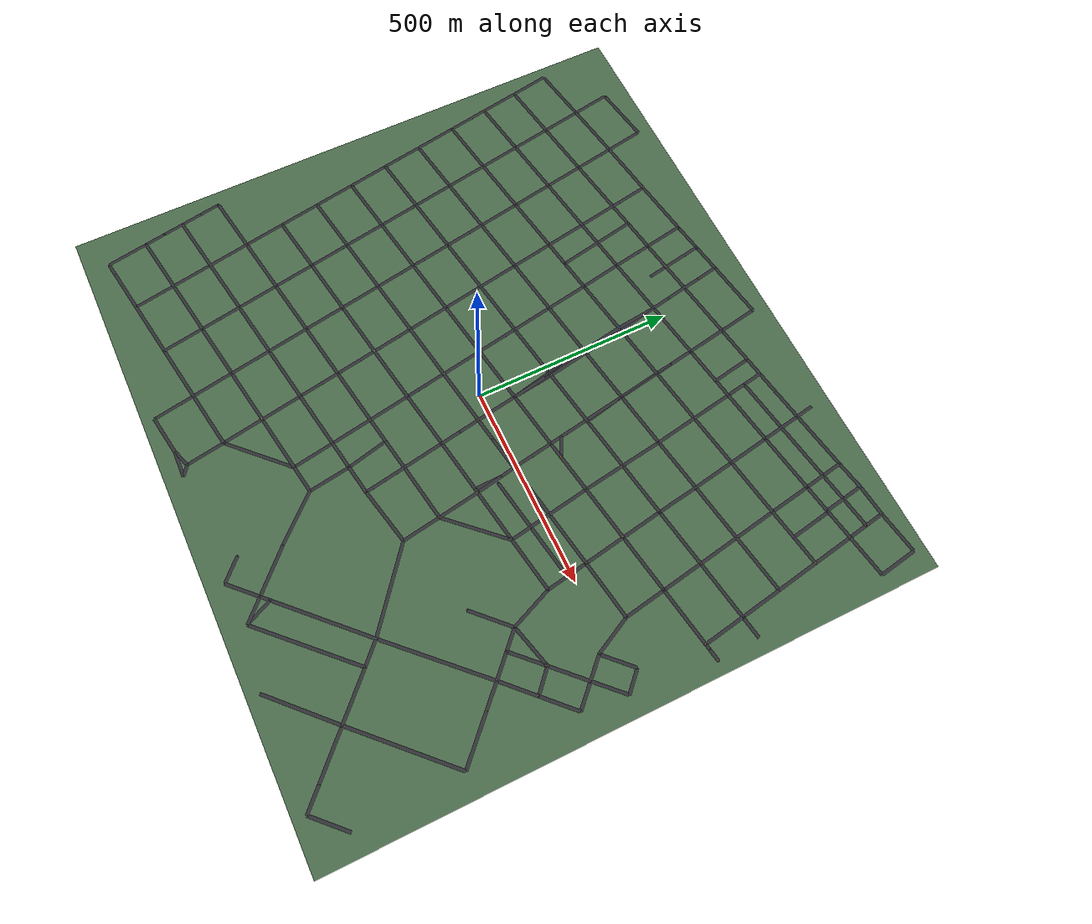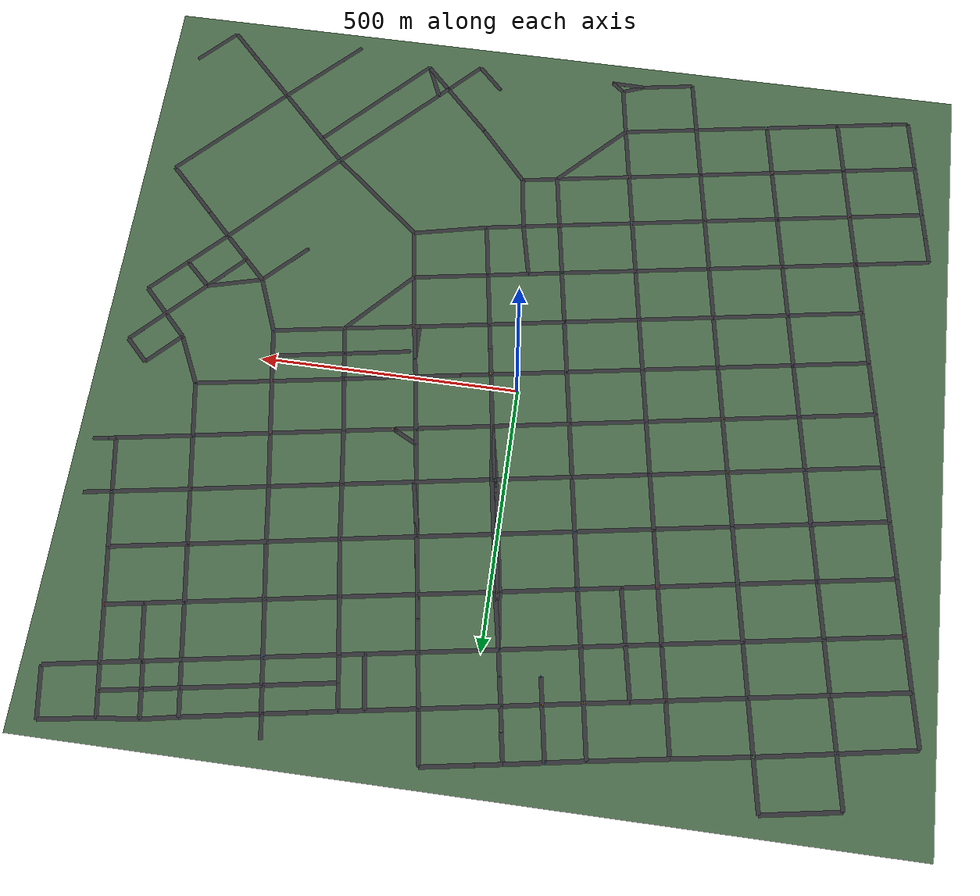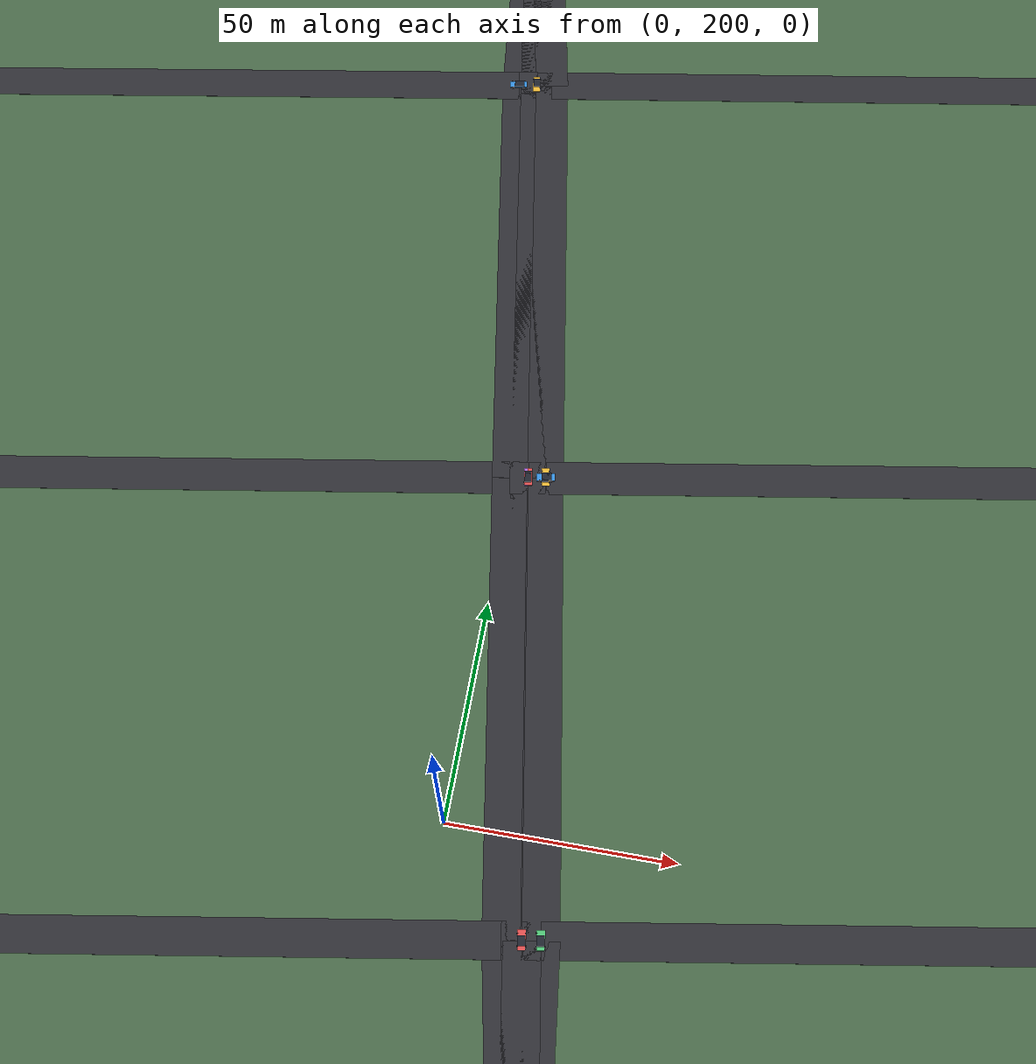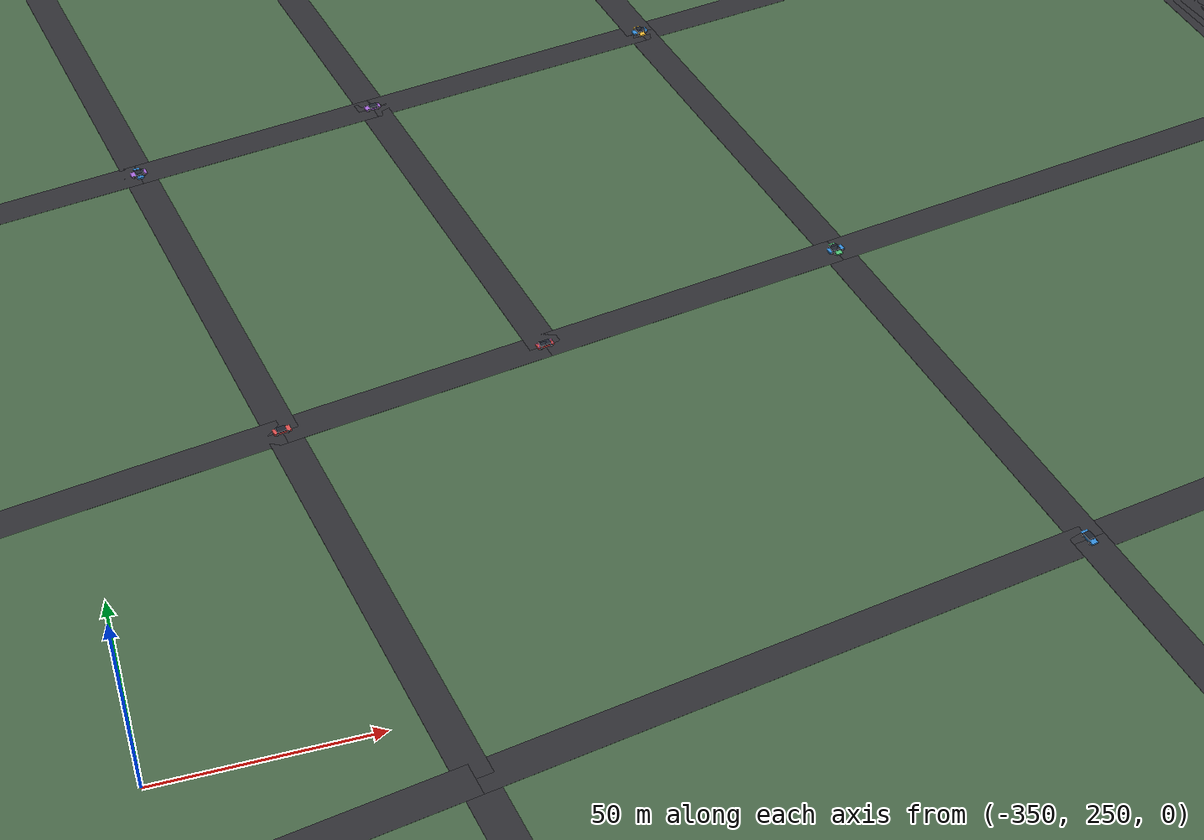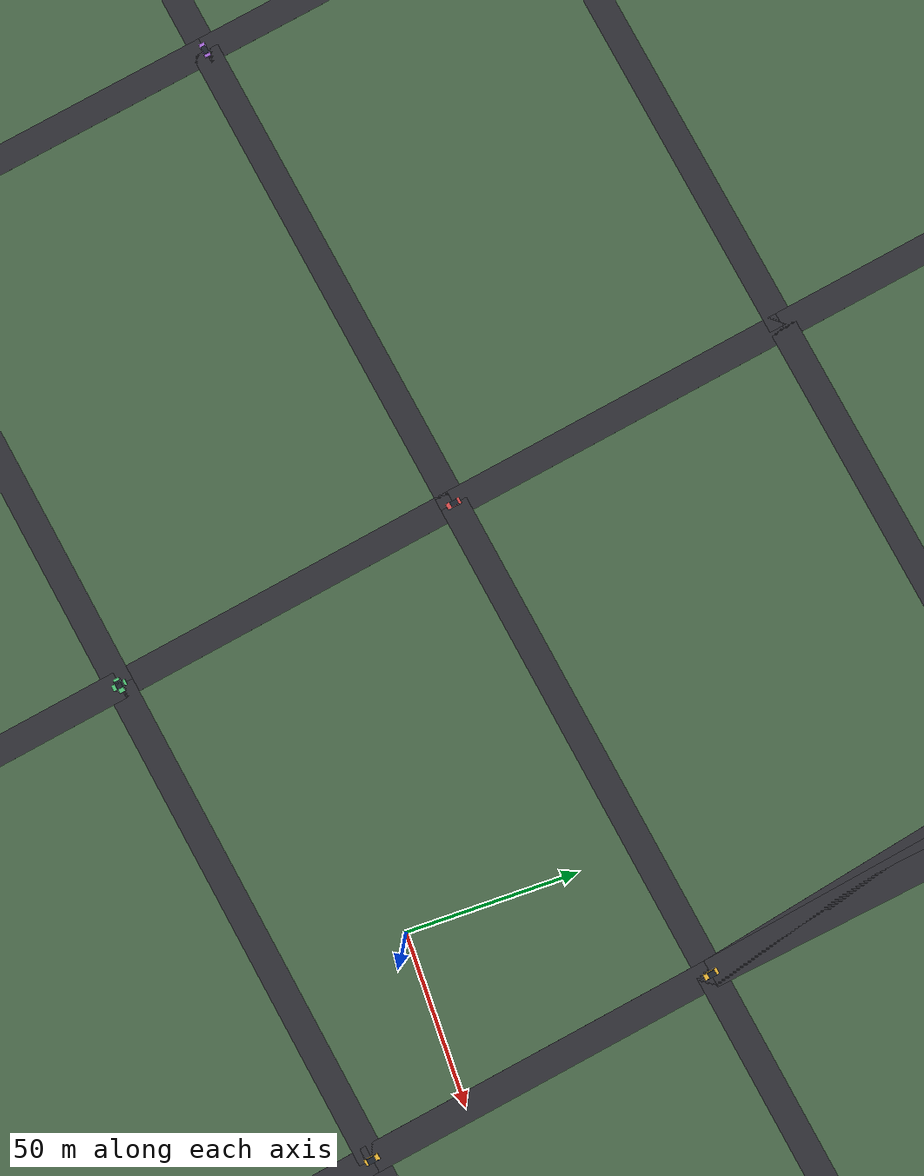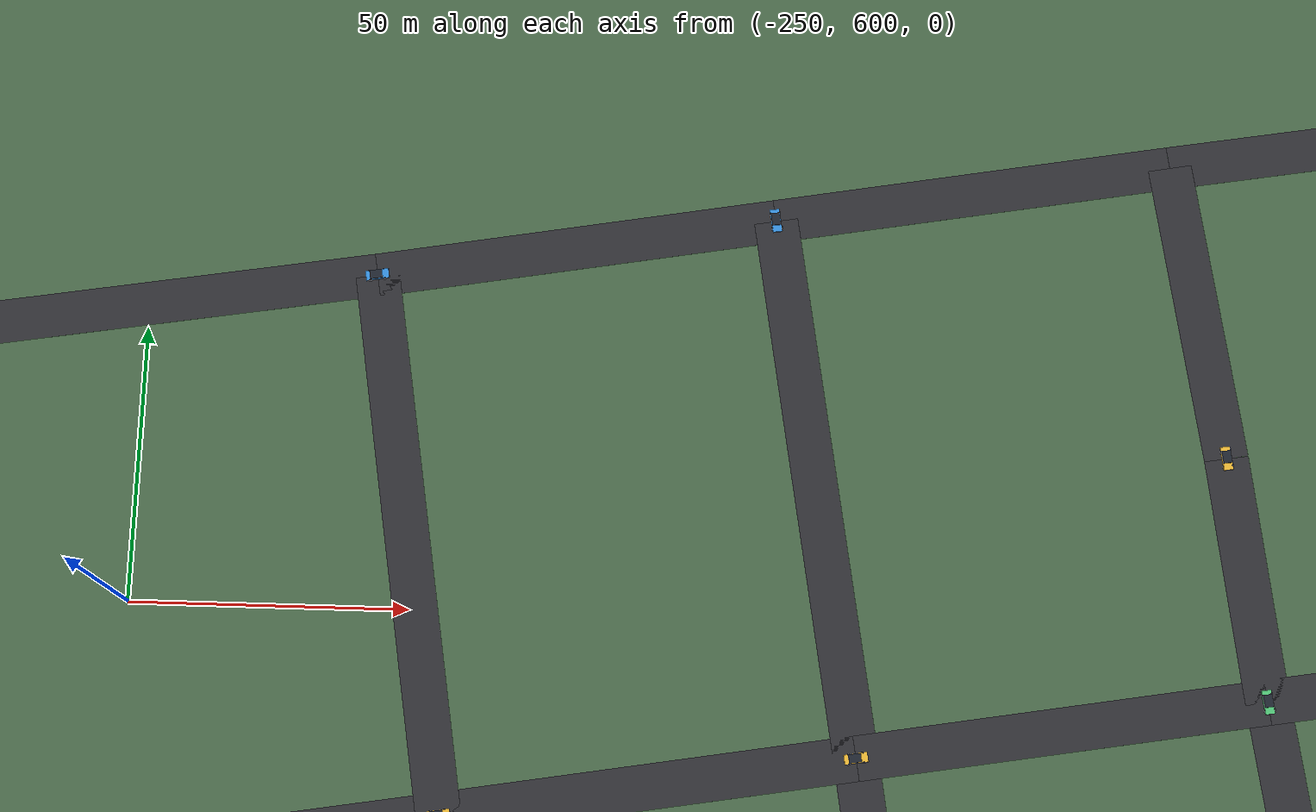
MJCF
<mujoco model="sf-city-v1">
  <compiler angle="radian" autolimits="true"/>
  <option gravity="0 0 -9.81" timestep="0.004" integrator="implicitfast"/>
  <visual>
    <global offwidth="1920" offheight="1080"/>
  </visual>
  <default>
    <joint damping="0.2"/>
    <geom condim="4" friction="1.3 0.02 0.001"/>
  </default>
  <asset>
    <texture name="sky" type="skybox" builtin="gradient" rgb1="0.55 0.65 0.80" rgb2="0.25 0.30 0.40" width="256" height="256"/>
    <texture name="grid" type="2d" builtin="checker" rgb1="0.30 0.42 0.30" rgb2="0.26 0.38 0.26" width="256" height="256"/>
    <material name="ground" texture="grid" texrepeat="80 80"/>
    <material name="road" rgba="0.18 0.18 0.20 1" reflectance="0.02"/>
    <material name="bldg" rgba="0.55 0.57 0.62 1" specular="0.3" shininess="0.3"/>
  </asset>
  <worldbody>
    <light name="sun" pos="817 -750 400" dir="-0.3 0.3 -1" diffuse="0.85 0.85 0.85"/>
    <geom name="floor" type="plane" size="817 750 0.1" material="ground"/>
    <camera name="drone" pos="0 0 1144" xyaxes="1 0 0 0 1 0"/>
    <camera name="oblique" pos="-817 -750 817" xyaxes="1 -1 0 0.5 0.5 1"/>

    <!-- ROADS -->
    <geom type="box" size="36.63 4.0 0.02" pos="656.30 499.24 0.04" euler="0 0 -2.9772" material="road" contype="0" conaffinity="0"/>
    <geom type="box" size="52.13 4.0 0.02" pos="683.98 556.68 0.04" euler="0 0 1.7336" material="road" contype="0" conaffinity="0"/>
    <geom type="box" size="53.44 4.0 0.02" pos="701.26 452.53 0.04" euler="0 0 -1.4048" material="road" contype="0" conaffinity="0"/>
    <geom type="box" size="52.11 4.0 0.02" pos="611.51 544.63 0.04" euler="0 0 1.7376" material="road" contype="0" conaffinity="0"/>
    <geom type="box" size="36.44 4.0 0.02" pos="584.22 487.25 0.04" euler="0 0 -2.9762" material="road" contype="0" conaffinity="0"/>
    <geom type="box" size="36.83 4.0 0.02" pos="639.19 602.07 0.04" euler="0 0 -2.9765" material="road" contype="0" conaffinity="0"/>
    <geom type="box" size="24.61 4.0 0.02" pos="671.38 632.38 0.04" euler="0 0 1.7400" material="road" contype="0" conaffinity="0"/>
    <geom type="box" size="52.47 4.0 0.02" pos="718.64 348.06 0.04" euler="0 0 -1.4071" material="road" contype="0" conaffinity="0"/>
    <geom type="box" size="73.06 4.0 0.02" pos="638.01 387.87 0.04" euler="0 0 -2.9772" material="road" contype="0" conaffinity="0"/>
    <geom type="box" size="1.81 4.0 0.02" pos="601.07 595.71 0.04" euler="0 0 -2.9756" material="road" contype="0" conaffinity="0"/>
    <geom type="box" size="72.83 4.0 0.02" pos="476.40 469.50 0.04" euler="0 0 -2.9795" material="road" contype="0" conaffinity="0"/>
    <geom type="box" size="53.40 4.0 0.02" pos="557.10 428.58 0.04" euler="0 0 -1.4047" material="road" contype="0" conaffinity="0"/>
    <geom type="box" size="51.82 4.0 0.02" pos="395.90 508.84 0.04" euler="0 0 1.7381" material="road" contype="0" conaffinity="0"/>
    <geom type="box" size="68.16 4.0 0.02" pos="337.33 446.35 0.04" euler="0 0 -2.9737" material="road" contype="0" conaffinity="0"/>
    <geom type="box" size="72.88 4.0 0.02" pos="494.02 364.03 0.04" euler="0 0 -2.9778" material="road" contype="0" conaffinity="0"/>
    <geom type="box" size="52.25 4.0 0.02" pos="574.56 324.38 0.04" euler="0 0 -1.4050" material="road" contype="0" conaffinity="0"/>
    <geom type="box" size="68.02 4.0 0.02" pos="320.15 548.90 0.04" euler="0 0 -2.9786" material="road" contype="0" conaffinity="0"/>
    <geom type="box" size="24.85 4.0 0.02" pos="383.19 584.46 0.04" euler="0 0 1.7356" material="road" contype="0" conaffinity="0"/>
    <geom type="box" size="52.16 4.0 0.02" pos="261.58 486.41 0.04" euler="0 0 1.7355" material="road" contype="0" conaffinity="0"/>
    <geom type="box" size="71.24 4.0 0.02" pos="199.85 423.32 0.04" euler="0 0 -2.9774" material="road" contype="0" conaffinity="0"/>
    <geom type="box" size="23.27 4.0 0.02" pos="230.07 534.06 0.04" euler="0 0 -2.9775" material="road" contype="0" conaffinity="0"/>
    <geom type="box" size="24.80 4.0 0.02" pos="248.97 562.33 0.04" euler="0 0 1.7355" material="road" contype="0" conaffinity="0"/>
    <geom type="box" size="53.66 4.0 0.02" pos="138.41 358.74 0.04" euler="0 0 -1.4052" material="road" contype="0" conaffinity="0"/>
    <geom type="box" size="70.92 4.0 0.02" pos="59.60 400.09 0.04" euler="0 0 -2.9776" material="road" contype="0" conaffinity="0"/>
    <geom type="box" size="22.36 4.0 0.02" pos="125.89 433.73 0.04" euler="0 0 1.7359" material="road" contype="0" conaffinity="0"/>
    <geom type="box" size="52.36 4.0 0.02" pos="157.89 254.54 0.04" euler="0 0 -1.3664" material="road" contype="0" conaffinity="0"/>
    <geom type="box" size="71.06 4.0 0.02" pos="77.17 294.11 0.04" euler="0 0 -2.9762" material="road" contype="0" conaffinity="0"/>
    <geom type="box" size="1.86 4.0 0.02" pos="-12.20 388.20 0.04" euler="0 0 -2.9735" material="road" contype="0" conaffinity="0"/>
    <geom type="box" size="52.15 4.0 0.02" pos="-20.47 439.68 0.04" euler="0 0 1.7656" material="road" contype="0" conaffinity="0"/>
    <geom type="box" size="53.76 4.0 0.02" pos="-5.43 334.83 0.04" euler="0 0 -1.4101" material="road" contype="0" conaffinity="0"/>
    <geom type="box" size="2.26 4.0 0.02" pos="-16.27 387.51 0.04" euler="0 0 -2.9727" material="road" contype="0" conaffinity="0"/>
    <geom type="box" size="52.30 4.0 0.02" pos="11.89 230.20 0.04" euler="0 0 -1.4032" material="road" contype="0" conaffinity="0"/>
    <geom type="box" size="2.14 4.0 0.02" pos="1.06 281.41 0.04" euler="0 0 -2.9762" material="road" contype="0" conaffinity="0"/>
    <geom type="box" size="71.15 4.0 0.02" pos="-88.65 375.28 0.04" euler="0 0 -2.9743" material="road" contype="0" conaffinity="0"/>
    <geom type="box" size="53.75 4.0 0.02" pos="-9.77 334.10 0.04" euler="0 0 -1.4077" material="road" contype="0" conaffinity="0"/>
    <geom type="box" size="53.59 4.0 0.02" pos="-150.07 310.56 0.04" euler="0 0 -1.4071" material="road" contype="0" conaffinity="0"/>
    <geom type="box" size="52.15 4.0 0.02" pos="-167.81 414.81 0.04" euler="0 0 1.7443" material="road" contype="0" conaffinity="0"/>
    <geom type="box" size="40.17 4.0 0.02" pos="-198.44 356.90 0.04" euler="0 0 -2.9782" material="road" contype="0" conaffinity="0"/>
    <geom type="box" size="52.28 4.0 0.02" pos="-132.82 206.10 0.04" euler="0 0 -1.4071" material="road" contype="0" conaffinity="0"/>
    <geom type="box" size="73.47 4.0 0.02" pos="-213.81 245.61 0.04" euler="0 0 -2.9765" material="road" contype="0" conaffinity="0"/>
    <geom type="box" size="49.62 4.0 0.02" pos="-184.90 515.13 0.04" euler="0 0 1.7346" material="road" contype="0" conaffinity="0"/>
    <geom type="box" size="40.34 4.0 0.02" pos="-216.60 459.55 0.04" euler="0 0 -2.9766" material="road" contype="0" conaffinity="0"/>
    <geom type="box" size="33.36 4.0 0.02" pos="-270.99 344.94 0.04" euler="0 0 -2.9782" material="road" contype="0" conaffinity="0"/>
    <geom type="box" size="52.04 4.0 0.02" pos="-312.45 390.84 0.04" euler="0 0 1.7357" material="road" contype="0" conaffinity="0"/>
    <geom type="box" size="73.25 4.0 0.02" pos="-376.14 327.35 0.04" euler="0 0 -2.9747" material="road" contype="0" conaffinity="0"/>
    <geom type="box" size="49.57 4.0 0.02" pos="-329.13 491.08 0.04" euler="0 0 1.7357" material="road" contype="0" conaffinity="0"/>
    <geom type="box" size="73.24 4.0 0.02" pos="-393.24 430.15 0.04" euler="0 0 -2.9767" material="road" contype="0" conaffinity="0"/>
    <geom type="box" size="53.58 4.0 0.02" pos="-439.58 262.32 0.04" euler="0 0 -1.4060" material="road" contype="0" conaffinity="0"/>
    <geom type="box" size="73.34 4.0 0.02" pos="-520.68 302.98 0.04" euler="0 0 -2.9744" material="road" contype="0" conaffinity="0"/>
    <geom type="box" size="52.18 4.0 0.02" pos="-456.93 366.65 0.04" euler="0 0 1.7356" material="road" contype="0" conaffinity="0"/>
    <geom type="box" size="52.24 4.0 0.02" pos="-422.22 157.93 0.04" euler="0 0 -1.4060" material="road" contype="0" conaffinity="0"/>
    <geom type="box" size="73.32 4.0 0.02" pos="-503.12 197.42 0.04" euler="0 0 -2.9765" material="road" contype="0" conaffinity="0"/>
    <geom type="box" size="52.34 4.0 0.02" pos="-601.60 342.40 0.04" euler="0 0 1.7359" material="road" contype="0" conaffinity="0"/>
    <geom type="box" size="73.30 4.0 0.02" pos="-665.31 278.80 0.04" euler="0 0 -2.9775" material="road" contype="0" conaffinity="0"/>
    <geom type="box" size="73.35 4.0 0.02" pos="-537.85 406.08 0.04" euler="0 0 -2.9766" material="road" contype="0" conaffinity="0"/>
    <geom type="box" size="49.54 4.0 0.02" pos="-473.61 467.00 0.04" euler="0 0 1.7355" material="road" contype="0" conaffinity="0"/>
    <geom type="box" size="49.50 4.0 0.02" pos="-618.34 442.86 0.04" euler="0 0 1.7358" material="road" contype="0" conaffinity="0"/>
    <geom type="box" size="73.37 4.0 0.02" pos="-682.58 381.99 0.04" euler="0 0 -2.9767" material="road" contype="0" conaffinity="0"/>
    <geom type="box" size="53.50 4.0 0.02" pos="-728.92 214.04 0.04" euler="0 0 -1.4072" material="road" contype="0" conaffinity="0"/>
    <geom type="box" size="52.28 4.0 0.02" pos="-746.29 318.39 0.04" euler="0 0 1.7372" material="road" contype="0" conaffinity="0"/>
    <geom type="box" size="52.37 4.0 0.02" pos="-711.71 109.57 0.04" euler="0 0 -1.4079" material="road" contype="0" conaffinity="0"/>
    <geom type="box" size="49.46 4.0 0.02" pos="-762.86 418.78 0.04" euler="0 0 1.7314" material="road" contype="0" conaffinity="0"/>
    <geom type="box" size="64.16 4.0 0.02" pos="711.93 -342.63 0.04" euler="0 0 2.3614" material="road" contype="0" conaffinity="0"/>
    <geom type="box" size="138.63 4.0 0.02" pos="659.99 -486.26 0.04" euler="0 0 -2.3513" material="road" contype="0" conaffinity="0"/>
    <geom type="box" size="33.40 4.0 0.02" pos="642.65 -273.94 0.04" euler="0 0 2.3588" material="road" contype="0" conaffinity="0"/>
    <geom type="box" size="62.28 4.0 0.02" pos="606.61 -628.68 0.04" euler="0 0 -0.7826" material="road" contype="0" conaffinity="0"/>
    <geom type="box" size="95.49 4.0 0.02" pos="494.46 -651.81 0.04" euler="0 0 -2.3631" material="road" contype="0" conaffinity="0"/>
    <geom type="box" size="47.44 4.0 0.02" pos="652.61 -216.94 0.04" euler="0 0 0.7825" material="road" contype="0" conaffinity="0"/>
    <geom type="box" size="32.96 4.0 0.02" pos="595.42 -227.32 0.04" euler="0 0 2.3665" material="road" contype="0" conaffinity="0"/>
    <geom type="box" size="138.68 4.0 0.02" pos="522.06 -349.59 0.04" euler="0 0 -2.3445" material="road" contype="0" conaffinity="0"/>
    <geom type="box" size="47.11 4.0 0.02" pos="719.66 -150.27 0.04" euler="0 0 0.7826" material="road" contype="0" conaffinity="0"/>
    <geom type="box" size="27.67 4.0 0.02" pos="552.11 -184.89 0.04" euler="0 0 2.3665" material="road" contype="0" conaffinity="0"/>
    <geom type="box" size="46.51 4.0 0.02" pos="604.59 -171.19 0.04" euler="0 0 0.7907" material="road" contype="0" conaffinity="0"/>
    <geom type="box" size="32.38 4.0 0.02" pos="448.31 -471.41 0.04" euler="0 0 -0.7736" material="road" contype="0" conaffinity="0"/>
    <geom type="box" size="125.74 4.0 0.02" pos="336.25 -537.71 0.04" euler="0 0 -2.3561" material="road" contype="0" conaffinity="0"/>
    <geom type="box" size="54.24 4.0 0.02" pos="584.83 -151.83 0.04" euler="0 0 0.2553" material="road" contype="0" conaffinity="0"/>
    <geom type="box" size="55.63 4.0 0.02" pos="492.89 -204.74 0.04" euler="0 0 -2.3592" material="road" contype="0" conaffinity="0"/>
    <geom type="box" size="55.93 4.0 0.02" pos="510.96 -113.84 0.04" euler="0 0 1.9631" material="road" contype="0" conaffinity="0"/>
    <geom type="box" size="33.37 4.0 0.02" pos="661.78 -160.81 0.04" euler="0 0 -0.7475" material="road" contype="0" conaffinity="0"/>
    <geom type="box" size="48.59 4.0 0.02" pos="671.52 -103.62 0.04" euler="0 0 0.7897" material="road" contype="0" conaffinity="0"/>
    <geom type="box" size="69.53 4.0 0.02" pos="420.99 -73.51 0.04" euler="0 0 -2.9776" material="road" contype="0" conaffinity="0"/>
    <geom type="box" size="26.43 4.0 0.02" pos="485.27 -36.08 0.04" euler="0 0 1.7344" material="road" contype="0" conaffinity="0"/>
    <geom type="box" size="52.33 4.0 0.02" pos="735.62 244.65 0.04" euler="0 0 1.7325" material="road" contype="0" conaffinity="0"/>
    <geom type="box" size="6.96 4.0 0.02" pos="750.91 194.15 0.04" euler="0 0 0.1656" material="road" contype="0" conaffinity="0"/>
    <geom type="box" size="72.77 4.0 0.02" pos="672.26 181.06 0.04" euler="0 0 -2.9767" material="road" contype="0" conaffinity="0"/>
    <geom type="box" size="27.48 4.0 0.02" pos="754.34 300.56 0.04" euler="0 0 0.1559" material="road" contype="0" conaffinity="0"/>
    <geom type="box" size="73.61 4.0 0.02" pos="527.88 157.00 0.04" euler="0 0 -2.9763" material="road" contype="0" conaffinity="0"/>
    <geom type="box" size="52.67 4.0 0.02" pos="609.15 117.17 0.04" euler="0 0 -1.4056" material="road" contype="0" conaffinity="0"/>
    <geom type="box" size="52.37 4.0 0.02" pos="446.70 196.55 0.04" euler="0 0 1.7352" material="road" contype="0" conaffinity="0"/>
    <geom type="box" size="69.68 4.0 0.02" pos="386.54 133.46 0.04" euler="0 0 -2.9769" material="road" contype="0" conaffinity="0"/>
    <geom type="box" size="50.97 4.0 0.02" pos="640.45 19.55 0.04" euler="0 0 -1.1105" material="road" contype="0" conaffinity="0"/>
    <geom type="box" size="73.56 4.0 0.02" pos="510.66 260.53 0.04" euler="0 0 0.1682" material="road" contype="0" conaffinity="0"/>
    <geom type="box" size="52.58 4.0 0.02" pos="430.12 300.18 0.04" euler="0 0 1.7237" material="road" contype="0" conaffinity="0"/>
    <geom type="box" size="47.97 4.0 0.02" pos="270.50 114.04 0.04" euler="0 0 -2.9740" material="road" contype="0" conaffinity="0"/>
    <geom type="box" size="52.35 4.0 0.02" pos="310.24 173.84 0.04" euler="0 0 1.7159" material="road" contype="0" conaffinity="0"/>
    <geom type="box" size="52.35 4.0 0.02" pos="326.38 70.40 0.04" euler="0 0 -1.4062" material="road" contype="0" conaffinity="0"/>
    <geom type="box" size="21.03 4.0 0.02" pos="202.47 102.54 0.04" euler="0 0 -2.9744" material="road" contype="0" conaffinity="0"/>
    <geom type="box" size="26.03 4.0 0.02" pos="199.99 117.81 0.04" euler="0 0 2.6724" material="road" contype="0" conaffinity="0"/>
    <geom type="box" size="68.67 4.0 0.02" pos="370.40 236.93 0.04" euler="0 0 0.1651" material="road" contype="0" conaffinity="0"/>
    <geom type="box" size="52.34 4.0 0.02" pos="295.27 277.46 0.04" euler="0 0 1.7126" material="road" contype="0" conaffinity="0"/>
    <geom type="box" size="69.69 4.0 0.02" pos="403.71 30.16 0.04" euler="0 0 0.1644" material="road" contype="0" conaffinity="0"/>
    <geom type="box" size="26.20 4.0 0.02" pos="339.31 -7.09 0.04" euler="0 0 -1.4041" material="road" contype="0" conaffinity="0"/>
    <geom type="box" size="72.84 4.0 0.02" pos="109.87 87.12 0.04" euler="0 0 -2.9771" material="road" contype="0" conaffinity="0"/>
    <geom type="box" size="52.51 4.0 0.02" pos="190.33 47.24 0.04" euler="0 0 -1.4064" material="road" contype="0" conaffinity="0"/>
    <geom type="box" size="52.45 4.0 0.02" pos="29.32 126.91 0.04" euler="0 0 1.7374" material="road" contype="0" conaffinity="0"/>
    <geom type="box" size="73.61 4.0 0.02" pos="-34.60 63.16 0.04" euler="0 0 -2.9774" material="road" contype="0" conaffinity="0"/>
    <geom type="box" size="52.53 4.0 0.02" pos="46.36 23.32 0.04" euler="0 0 -1.4113" material="road" contype="0" conaffinity="0"/>
    <geom type="box" size="52.48 4.0 0.02" pos="31.27 127.23 0.04" euler="0 0 1.6996" material="road" contype="0" conaffinity="0"/>
    <geom type="box" size="18.17 4.0 0.02" pos="202.28 -22.42 0.04" euler="0 0 -1.3851" material="road" contype="0" conaffinity="0"/>
    <geom type="box" size="69.01 4.0 0.02" pos="266.94 7.09 0.04" euler="0 0 0.1698" material="road" contype="0" conaffinity="0"/>
    <geom type="box" size="1.98 4.0 0.02" pos="22.58 178.95 0.04" euler="0 0 0.1636" material="road" contype="0" conaffinity="0"/>
    <geom type="box" size="52.59 4.0 0.02" pos="-98.55 -0.74 0.04" euler="0 0 -1.4052" material="road" contype="0" conaffinity="0"/>
    <geom type="box" size="73.34 4.0 0.02" pos="-179.57 39.07 0.04" euler="0 0 -2.9765" material="road" contype="0" conaffinity="0"/>
    <geom type="box" size="26.32 4.0 0.02" pos="59.10 -54.48 0.04" euler="0 0 -1.4028" material="road" contype="0" conaffinity="0"/>
    <geom type="box" size="29.48 4.0 0.02" pos="83.79 -23.71 0.04" euler="0 0 0.1645" material="road" contype="0" conaffinity="0"/>
    <geom type="box" size="52.30 4.0 0.02" pos="15.81 230.84 0.04" euler="0 0 1.7384" material="road" contype="0" conaffinity="0"/>
    <geom type="box" size="72.98 4.0 0.02" pos="96.52 191.28 0.04" euler="0 0 0.1652" material="road" contype="0" conaffinity="0"/>
    <geom type="box" size="52.15 4.0 0.02" pos="-81.28 -104.05 0.04" euler="0 0 -1.4052" material="road" contype="0" conaffinity="0"/>
    <geom type="box" size="73.29 4.0 0.02" pos="-17.59 -40.57 0.04" euler="0 0 0.1650" material="road" contype="0" conaffinity="0"/>
    <geom type="box" size="52.42 4.0 0.02" pos="-260.52 78.73 0.04" euler="0 0 1.7357" material="road" contype="0" conaffinity="0"/>
    <geom type="box" size="73.26 4.0 0.02" pos="-324.18 14.99 0.04" euler="0 0 -2.9766" material="road" contype="0" conaffinity="0"/>
    <geom type="box" size="73.40 4.0 0.02" pos="-196.71 142.48 0.04" euler="0 0 0.1648" material="road" contype="0" conaffinity="0"/>
    <geom type="box" size="52.26 4.0 0.02" pos="-277.70 181.99 0.04" euler="0 0 1.7358" material="road" contype="0" conaffinity="0"/>
    <geom type="box" size="73.29 4.0 0.02" pos="-468.74 -9.08 0.04" euler="0 0 -2.9766" material="road" contype="0" conaffinity="0"/>
    <geom type="box" size="52.55 4.0 0.02" pos="-387.83 -48.88 0.04" euler="0 0 -1.4059" material="road" contype="0" conaffinity="0"/>
    <geom type="box" size="52.36 4.0 0.02" pos="-549.64 30.54 0.04" euler="0 0 1.7359" material="road" contype="0" conaffinity="0"/>
    <geom type="box" size="73.47 4.0 0.02" pos="-613.51 -33.18 0.04" euler="0 0 -2.9767" material="road" contype="0" conaffinity="0"/>
    <geom type="box" size="73.27 4.0 0.02" pos="-306.92 -88.70 0.04" euler="0 0 0.1647" material="road" contype="0" conaffinity="0"/>
    <geom type="box" size="52.20 4.0 0.02" pos="-370.64 -152.21 0.04" euler="0 0 -1.4060" material="road" contype="0" conaffinity="0"/>
    <geom type="box" size="73.30 4.0 0.02" pos="-485.95 94.29 0.04" euler="0 0 0.1659" material="road" contype="0" conaffinity="0"/>
    <geom type="box" size="52.30 4.0 0.02" pos="-566.84 133.78 0.04" euler="0 0 1.7360" material="road" contype="0" conaffinity="0"/>
    <geom type="box" size="52.52 4.0 0.02" pos="-677.34 -97.04 0.04" euler="0 0 -1.4054" material="road" contype="0" conaffinity="0"/>
    <geom type="box" size="73.45 4.0 0.02" pos="-596.23 -136.80 0.04" euler="0 0 0.1647" material="road" contype="0" conaffinity="0"/>
    <geom type="box" size="52.26 4.0 0.02" pos="-660.08 -200.39 0.04" euler="0 0 -1.4052" material="road" contype="0" conaffinity="0"/>
    <geom type="box" size="30.28 4.0 0.02" pos="684.41 -47.61 0.04" euler="0 0 -0.7897" material="road" contype="0" conaffinity="0"/>
    <geom type="box" size="43.12 4.0 0.02" pos="693.60 4.36 0.04" euler="0 0 0.7846" material="road" contype="0" conaffinity="0"/>
    <geom type="box" size="52.58 4.0 0.02" pos="591.83 220.98 0.04" euler="0 0 -1.4055" material="road" contype="0" conaffinity="0"/>
    <geom type="box" size="72.96 4.0 0.02" pos="655.19 284.57 0.04" euler="0 0 0.1614" material="road" contype="0" conaffinity="0"/>
    <geom type="box" size="68.09 4.0 0.02" pos="354.99 340.71 0.04" euler="0 0 -2.9729" material="road" contype="0" conaffinity="0"/>
    <geom type="box" size="53.52 4.0 0.02" pos="413.32 404.95 0.04" euler="0 0 1.7358" material="road" contype="0" conaffinity="0"/>
    <geom type="box" size="73.06 4.0 0.02" pos="459.32 572.03 0.04" euler="0 0 -2.9754" material="road" contype="0" conaffinity="0"/>
    <geom type="box" size="52.12 4.0 0.02" pos="539.82 532.68 0.04" euler="0 0 -1.4079" material="road" contype="0" conaffinity="0"/>
    <geom type="box" size="72.99 4.0 0.02" pos="451.12 620.89 0.04" euler="0 0 -2.9776" material="road" contype="0" conaffinity="0"/>
    <geom type="box" size="24.69 4.0 0.02" pos="527.25 608.46 0.04" euler="0 0 -1.4031" material="road" contype="0" conaffinity="0"/>
    <geom type="box" size="24.81 4.0 0.02" pos="375.02 633.45 0.04" euler="0 0 1.7365" material="road" contype="0" conaffinity="0"/>
    <geom type="box" size="68.02 4.0 0.02" pos="312.01 597.88 0.04" euler="0 0 -2.9777" material="road" contype="0" conaffinity="0"/>
    <geom type="box" size="25.26 4.0 0.02" pos="518.93 657.72 0.04" euler="0 0 -1.4037" material="road" contype="0" conaffinity="0"/>
    <geom type="box" size="34.57 4.0 0.02" pos="548.70 689.05 0.04" euler="0 0 0.1869" material="road" contype="0" conaffinity="0"/>
    <geom type="box" size="38.43 4.0 0.02" pos="620.89 699.49 0.04" euler="0 0 0.1046" material="road" contype="0" conaffinity="0"/>
    <geom type="box" size="52.09 4.0 0.02" pos="-247.24 401.65 0.04" euler="0 0 -1.3940" material="road" contype="0" conaffinity="0"/>
    <geom type="box" size="32.74 4.0 0.02" pos="-288.70 447.55 0.04" euler="0 0 -2.9767" material="road" contype="0" conaffinity="0"/>
    <geom type="box" size="31.83 4.0 0.02" pos="673.29 -695.08 0.04" euler="0 0 -0.7845" material="road" contype="0" conaffinity="0"/>
    <geom type="box" size="33.95 4.0 0.02" pos="145.40 -680.83 0.04" euler="0 0 -0.7789" material="road" contype="0" conaffinity="0"/>
    <geom type="box" size="42.85 4.0 0.02" pos="199.79 -674.31 0.04" euler="0 0 0.7879" material="road" contype="0" conaffinity="0"/>
    <geom type="box" size="30.08 4.0 0.02" pos="745.43 13.60 0.04" euler="0 0 2.3583" material="road" contype="0" conaffinity="0"/>
    <geom type="box" size="43.31 4.0 0.02" pos="736.23 -38.37 0.04" euler="0 0 0.7893" material="road" contype="0" conaffinity="0"/>
    <geom type="box" size="33.68 4.0 0.02" pos="729.40 -93.08 0.04" euler="0 0 -0.7916" material="road" contype="0" conaffinity="0"/>
    <geom type="box" size="52.30 4.0 0.02" pos="727.12 616.69 0.04" euler="0 0 -2.9770" material="road" contype="0" conaffinity="0"/>
    <geom type="box" size="23.78 4.0 0.02" pos="663.17 680.07 0.04" euler="0 0 1.7427" material="road" contype="0" conaffinity="0"/>
    <geom type="box" size="38.53 4.0 0.02" pos="629.22 650.35 0.04" euler="0 0 -2.9776" material="road" contype="0" conaffinity="0"/>
    <geom type="box" size="47.85 4.0 0.02" pos="159.90 522.44 0.04" euler="0 0 -2.9774" material="road" contype="0" conaffinity="0"/>
    <geom type="box" size="24.64 4.0 0.02" pos="240.86 611.09 0.04" euler="0 0 1.7356" material="road" contype="0" conaffinity="0"/>
    <geom type="box" size="49.45 4.0 0.02" pos="104.56 563.40 0.04" euler="0 0 1.7359" material="road" contype="0" conaffinity="0"/>
    <geom type="box" size="195.17 4.0 0.02" pos="144.73 322.10 0.04" euler="0 0 -1.4059" material="road" contype="0" conaffinity="0"/>
    <geom type="box" size="72.61 4.0 0.02" pos="41.06 502.73 0.04" euler="0 0 -2.9771" material="road" contype="0" conaffinity="0"/>
    <geom type="box" size="49.55 4.0 0.02" pos="88.29 661.05 0.04" euler="0 0 1.7358" material="road" contype="0" conaffinity="0"/>
    <geom type="box" size="47.81 4.0 0.02" pos="143.60 619.98 0.04" euler="0 0 0.1640" material="road" contype="0" conaffinity="0"/>
    <geom type="box" size="15.47 4.0 0.02" pos="179.25 114.31 0.04" euler="0 0 -1.4099" material="road" contype="0" conaffinity="0"/>
    <geom type="box" size="52.13 4.0 0.02" pos="-22.30 439.37 0.04" euler="0 0 -1.4116" material="road" contype="0" conaffinity="0"/>
    <geom type="box" size="74.15 4.0 0.02" pos="-103.69 478.51 0.04" euler="0 0 -2.9745" material="road" contype="0" conaffinity="0"/>
    <geom type="box" size="23.78 4.0 0.02" pos="-34.62 514.27 0.04" euler="0 0 1.7423" material="road" contype="0" conaffinity="0"/>
    <geom type="box" size="52.20 4.0 0.02" pos="-24.53 438.99 0.04" euler="0 0 -1.4550" material="road" contype="0" conaffinity="0"/>
    <geom type="box" size="25.72 4.0 0.02" pos="-43.26 563.01 0.04" euler="0 0 1.7500" material="road" contype="0" conaffinity="0"/>
    <geom type="box" size="49.22 4.0 0.02" pos="-201.02 612.64 0.04" euler="0 0 1.7346" material="road" contype="0" conaffinity="0"/>
    <geom type="box" size="36.89 4.0 0.02" pos="-156.61 570.15 0.04" euler="0 0 0.1653" material="road" contype="0" conaffinity="0"/>
    <geom type="box" size="49.70 4.0 0.02" pos="-345.36 589.02 0.04" euler="0 0 1.7343" material="road" contype="0" conaffinity="0"/>
    <geom type="box" size="31.95 4.0 0.02" pos="-305.78 545.37 0.04" euler="0 0 0.1694" material="road" contype="0" conaffinity="0"/>
    <geom type="box" size="73.23 4.0 0.02" pos="-409.51 527.92 0.04" euler="0 0 0.1654" material="road" contype="0" conaffinity="0"/>
    <geom type="box" size="50.39 4.0 0.02" pos="-489.92 565.58 0.04" euler="0 0 1.7339" material="road" contype="0" conaffinity="0"/>
    <geom type="box" size="50.16 4.0 0.02" pos="-634.70 541.18 0.04" euler="0 0 1.7356" material="road" contype="0" conaffinity="0"/>
    <geom type="box" size="73.37 4.0 0.02" pos="-554.10 503.78 0.04" euler="0 0 0.1655" material="road" contype="0" conaffinity="0"/>
    <geom type="box" size="49.44 4.0 0.02" pos="-779.05 516.35 0.04" euler="0 0 1.7390" material="road" contype="0" conaffinity="0"/>
    <geom type="box" size="73.15 4.0 0.02" pos="-698.62 479.65 0.04" euler="0 0 0.1654" material="road" contype="0" conaffinity="0"/>
    <geom type="box" size="50.57 4.0 0.02" pos="-226.09 -711.60 0.04" euler="0 0 0.1658" material="road" contype="0" conaffinity="0"/>
    <geom type="box" size="22.84 4.0 0.02" pos="-154.86 -695.16 0.04" euler="0 0 0.3623" material="road" contype="0" conaffinity="0"/>
    <geom type="box" size="32.98 4.0 0.02" pos="-143.25 -704.08 0.04" euler="0 0 -0.0252" material="road" contype="0" conaffinity="0"/>
    <geom type="box" size="52.22 4.0 0.02" pos="41.19 -402.00 0.04" euler="0 0 1.7159" material="road" contype="0" conaffinity="0"/>
    <geom type="box" size="69.29 4.0 0.02" pos="95.33 -504.96 0.04" euler="0 0 -0.8333" material="road" contype="0" conaffinity="0"/>
    <geom type="box" size="52.49 4.0 0.02" pos="21.93 -299.16 0.04" euler="0 0 1.7956" material="road" contype="0" conaffinity="0"/>
    <geom type="box" size="36.45 4.0 0.02" pos="-2.32 -356.31 0.04" euler="0 0 -2.9768" material="road" contype="0" conaffinity="0"/>
    <geom type="box" size="62.14 4.0 0.02" pos="185.97 -600.09 0.04" euler="0 0 -0.7831" material="road" contype="0" conaffinity="0"/>
    <geom type="box" size="40.07 4.0 0.02" pos="49.74 -241.30 0.04" euler="0 0 0.1678" material="road" contype="0" conaffinity="0"/>
    <geom type="box" size="73.39 4.0 0.02" pos="-110.67 -374.33 0.04" euler="0 0 -2.9767" material="road" contype="0" conaffinity="0"/>
    <geom type="box" size="52.23 4.0 0.02" pos="-29.73 -413.81 0.04" euler="0 0 -1.4066" material="road" contype="0" conaffinity="0"/>
    <geom type="box" size="52.62 4.0 0.02" pos="80.54 -182.71 0.04" euler="0 0 1.7369" material="road" contype="0" conaffinity="0"/>
    <geom type="box" size="73.37 4.0 0.02" pos="161.63 -222.69 0.04" euler="0 0 0.1631" material="road" contype="0" conaffinity="0"/>
    <geom type="box" size="52.46 4.0 0.02" pos="97.88 -286.35 0.04" euler="0 0 -1.4054" material="road" contype="0" conaffinity="0"/>
    <geom type="box" size="52.37 4.0 0.02" pos="463.86 93.23 0.04" euler="0 0 1.7355" material="road" contype="0" conaffinity="0"/>
    <geom type="box" size="73.63 4.0 0.02" pos="545.13 53.39 0.04" euler="0 0 0.1613" material="road" contype="0" conaffinity="0"/>
    <geom type="box" size="73.41 4.0 0.02" pos="-145.09 -167.55 0.04" euler="0 0 -2.9765" material="road" contype="0" conaffinity="0"/>
    <geom type="box" size="52.53 4.0 0.02" pos="-64.02 -207.30 0.04" euler="0 0 -1.4052" material="road" contype="0" conaffinity="0"/>
    <geom type="box" size="73.38 4.0 0.02" pos="-162.26 -64.65 0.04" euler="0 0 0.1648" material="road" contype="0" conaffinity="0"/>
    <geom type="box" size="52.57 4.0 0.02" pos="-243.28 -24.83 0.04" euler="0 0 1.7358" material="road" contype="0" conaffinity="0"/>
    <geom type="box" size="52.24 4.0 0.02" pos="-353.50 -255.24 0.04" euler="0 0 -1.4060" material="road" contype="0" conaffinity="0"/>
    <geom type="box" size="73.26 4.0 0.02" pos="-434.34 -215.75 0.04" euler="0 0 -2.9765" material="road" contype="0" conaffinity="0"/>
    <geom type="box" size="52.54 4.0 0.02" pos="-532.40 -72.93 0.04" euler="0 0 1.7359" material="road" contype="0" conaffinity="0"/>
    <geom type="box" size="73.28 4.0 0.02" pos="-451.49 -112.74 0.04" euler="0 0 0.1648" material="road" contype="0" conaffinity="0"/>
    <geom type="box" size="52.21 4.0 0.02" pos="-642.86 -303.43 0.04" euler="0 0 -1.4053" material="road" contype="0" conaffinity="0"/>
    <geom type="box" size="49.40 4.0 0.02" pos="-128.47 624.93 0.04" euler="0 0 -1.4031" material="road" contype="0" conaffinity="0"/>
    <geom type="box" size="36.57 4.0 0.02" pos="-100.67 679.83 0.04" euler="0 0 0.1701" material="road" contype="0" conaffinity="0"/>
    <geom type="box" size="24.57 4.0 0.02" pos="-116.31 551.96 0.04" euler="0 0 -1.4107" material="road" contype="0" conaffinity="0"/>
    <geom type="box" size="36.69 4.0 0.02" pos="-84.04 582.27 0.04" euler="0 0 0.1656" material="road" contype="0" conaffinity="0"/>
    <geom type="box" size="27.52 4.0 0.02" pos="-59.68 658.94 0.04" euler="0 0 -1.3901" material="road" contype="0" conaffinity="0"/>
    <geom type="box" size="22.05 4.0 0.02" pos="-51.29 610.09 0.04" euler="0 0 1.7276" material="road" contype="0" conaffinity="0"/>
    <geom type="box" size="73.12 4.0 0.02" pos="24.29 600.25 0.04" euler="0 0 0.1639" material="road" contype="0" conaffinity="0"/>
    <geom type="box" size="49.34 4.0 0.02" pos="730.41 -682.39 0.04" euler="0 0 0.7938" material="road" contype="0" conaffinity="0"/>
    <geom type="box" size="48.60 4.0 0.02" pos="241.54 -258.79 0.04" euler="0 0 -1.4156" material="road" contype="0" conaffinity="0"/>
    <geom type="box" size="86.41 4.0 0.02" pos="293.21 -147.82 0.04" euler="0 0 0.8163" material="road" contype="0" conaffinity="0"/>
    <geom type="box" size="113.10 4.0 0.02" pos="337.10 -377.80 0.04" euler="0 0 -0.6785" material="road" contype="0" conaffinity="0"/>
    <geom type="box" size="72.97 4.0 0.02" pos="177.78 -322.45 0.04" euler="0 0 -2.9256" material="road" contype="0" conaffinity="0"/>
    <geom type="box" size="68.39 4.0 0.02" pos="284.89 -95.85 0.04" euler="0 0 -2.9802" material="road" contype="0" conaffinity="0"/>
    <geom type="box" size="26.33 4.0 0.02" pos="348.02 -58.89 0.04" euler="0 0 1.7375" material="road" contype="0" conaffinity="0"/>
    <geom type="box" size="52.29 4.0 0.02" pos="-46.81 -310.70 0.04" euler="0 0 -1.4066" material="road" contype="0" conaffinity="0"/>
    <geom type="box" size="33.26 4.0 0.02" pos="-22.56 -253.55 0.04" euler="0 0 0.1680" material="road" contype="0" conaffinity="0"/>
    <geom type="box" size="52.23 4.0 0.02" pos="-498.02 -279.31 0.04" euler="0 0 1.7359" material="road" contype="0" conaffinity="0"/>
    <geom type="box" size="73.24 4.0 0.02" pos="-417.18 -318.80 0.04" euler="0 0 0.1649" material="road" contype="0" conaffinity="0"/>
    <geom type="box" size="73.43 4.0 0.02" pos="-579.03 -239.86 0.04" euler="0 0 -2.9765" material="road" contype="0" conaffinity="0"/>
    <geom type="box" size="52.23 4.0 0.02" pos="-515.18 -176.27 0.04" euler="0 0 1.7359" material="road" contype="0" conaffinity="0"/>
    <geom type="box" size="52.54 4.0 0.02" pos="-336.28 -358.60 0.04" euler="0 0 -1.4054" material="road" contype="0" conaffinity="0"/>
    <geom type="box" size="73.29 4.0 0.02" pos="-272.61 -294.87 0.04" euler="0 0 0.1632" material="road" contype="0" conaffinity="0"/>
    <geom type="box" size="73.41 4.0 0.02" pos="-561.85 -342.87 0.04" euler="0 0 0.1649" material="road" contype="0" conaffinity="0"/>
    <geom type="box" size="52.58 4.0 0.02" pos="-625.60 -406.78 0.04" euler="0 0 -1.4053" material="road" contype="0" conaffinity="0"/>
    <geom type="box" size="73.31 4.0 0.02" pos="-689.24 -470.69 0.04" euler="0 0 -2.9765" material="road" contype="0" conaffinity="0"/>
    <geom type="box" size="73.39 4.0 0.02" pos="-544.55 -446.58 0.04" euler="0 0 0.1651" material="road" contype="0" conaffinity="0"/>
    <geom type="box" size="52.28 4.0 0.02" pos="-608.32 -510.21 0.04" euler="0 0 -1.4053" material="road" contype="0" conaffinity="0"/>
    <geom type="box" size="73.27 4.0 0.02" pos="-706.54 -366.95 0.04" euler="0 0 0.1649" material="road" contype="0" conaffinity="0"/>
    <geom type="box" size="33.32 4.0 0.02" pos="253.46 -667.60 0.04" euler="0 0 -0.7903" material="road" contype="0" conaffinity="0"/>
    <geom type="box" size="12.25 4.0 0.02" pos="238.68 -635.28 0.04" euler="0 0 0.7846" material="road" contype="0" conaffinity="0"/>
    <geom type="box" size="64.24 4.0 0.02" pos="516.96 -539.40 0.04" euler="0 0 -0.7841" material="road" contype="0" conaffinity="0"/>
    <geom type="box" size="35.54 4.0 0.02" pos="262.13 -658.95 0.04" euler="0 0 1.9995" material="road" contype="0" conaffinity="0"/>
    <geom type="box" size="138.53 4.0 0.02" pos="374.19 -592.66 0.04" euler="0 0 0.7922" material="road" contype="0" conaffinity="0"/>
    <geom type="box" size="53.58 4.0 0.02" pos="279.00 382.12 0.04" euler="0 0 1.7371" material="road" contype="0" conaffinity="0"/>
    <geom type="box" size="71.28 4.0 0.02" pos="217.56 317.55 0.04" euler="0 0 -2.9762" material="road" contype="0" conaffinity="0"/>
    <geom type="box" size="68.00 4.0 0.02" pos="235.59 214.46 0.04" euler="0 0 0.1652" material="road" contype="0" conaffinity="0"/>
    <geom type="box" size="71.32 4.0 0.02" pos="-53.95 166.22 0.04" euler="0 0 0.1649" material="road" contype="0" conaffinity="0"/>
    <geom type="box" size="52.40 4.0 0.02" pos="-115.76 102.82 0.04" euler="0 0 -1.4071" material="road" contype="0" conaffinity="0"/>
    <geom type="box" size="2.14 4.0 0.02" pos="18.51 178.28 0.04" euler="0 0 0.1654" material="road" contype="0" conaffinity="0"/>
    <geom type="box" size="52.49 4.0 0.02" pos="27.21 126.56 0.04" euler="0 0 -1.3635" material="road" contype="0" conaffinity="0"/>
    <geom type="box" size="53.71 4.0 0.02" pos="-295.10 286.52 0.04" euler="0 0 1.7356" material="road" contype="0" conaffinity="0"/>
    <geom type="box" size="73.25 4.0 0.02" pos="-358.54 221.50 0.04" euler="0 0 -2.9765" material="road" contype="0" conaffinity="0"/>
    <geom type="box" size="73.26 4.0 0.02" pos="-341.39 118.42 0.04" euler="0 0 0.1648" material="road" contype="0" conaffinity="0"/>
    <geom type="box" size="52.43 4.0 0.02" pos="-405.05 54.68 0.04" euler="0 0 -1.4060" material="road" contype="0" conaffinity="0"/>
    <geom type="box" size="53.43 4.0 0.02" pos="-584.22 238.07 0.04" euler="0 0 1.7358" material="road" contype="0" conaffinity="0"/>
    <geom type="box" size="73.38 4.0 0.02" pos="-647.82 173.31 0.04" euler="0 0 -2.9765" material="road" contype="0" conaffinity="0"/>
    <geom type="box" size="73.50 4.0 0.02" pos="-630.73 70.04 0.04" euler="0 0 0.1660" material="road" contype="0" conaffinity="0"/>
    <geom type="box" size="52.28 4.0 0.02" pos="-694.60 6.33 0.04" euler="0 0 -1.4052" material="road" contype="0" conaffinity="0"/>
    <geom type="box" size="26.32 4.0 0.02" pos="-774.49 -404.94 0.04" euler="0 0 1.7358" material="road" contype="0" conaffinity="0"/>
    <geom type="box" size="36.70 4.0 0.02" pos="-172.88 667.42 0.04" euler="0 0 0.1702" material="road" contype="0" conaffinity="0"/>
    <geom type="box" size="52.18 4.0 0.02" pos="-226.08 -128.15 0.04" euler="0 0 1.7358" material="road" contype="0" conaffinity="0"/>
    <geom type="box" size="73.28 4.0 0.02" pos="-289.79 -191.66 0.04" euler="0 0 -2.9765" material="road" contype="0" conaffinity="0"/>
    <geom type="box" size="73.28 4.0 0.02" pos="-255.35 -398.41 0.04" euler="0 0 -2.9767" material="road" contype="0" conaffinity="0"/>
    <geom type="box" size="52.42 4.0 0.02" pos="-191.68 -334.67 0.04" euler="0 0 1.7358" material="road" contype="0" conaffinity="0"/>
    <geom type="box" size="35.45 4.0 0.02" pos="13.77 -459.50 0.04" euler="0 0 0.1652" material="road" contype="0" conaffinity="0"/>
    <geom type="box" size="90.10 4.0 0.02" pos="-84.95 -529.00 0.04" euler="0 0 -2.3569" material="road" contype="0" conaffinity="0"/>
    <geom type="box" size="73.36 4.0 0.02" pos="-93.55 -477.39 0.04" euler="0 0 -2.9764" material="road" contype="0" conaffinity="0"/>
    <geom type="box" size="52.32 4.0 0.02" pos="-157.31 -541.06 0.04" euler="0 0 1.7359" material="road" contype="0" conaffinity="0"/>
    <geom type="box" size="73.24 4.0 0.02" pos="-220.96 -604.71 0.04" euler="0 0 -2.9765" material="road" contype="0" conaffinity="0"/>
    <geom type="box" size="73.25 4.0 0.02" pos="-238.16 -501.51 0.04" euler="0 0 -2.9764" material="road" contype="0" conaffinity="0"/>
    <geom type="box" size="52.25 4.0 0.02" pos="-174.49 -437.92 0.04" euler="0 0 1.7358" material="road" contype="0" conaffinity="0"/>
    <geom type="box" size="5.25 4.0 0.02" pos="212.19 -107.59 0.04" euler="0 0 -2.9986" material="road" contype="0" conaffinity="0"/>
    <geom type="box" size="52.63 4.0 0.02" pos="225.71 -158.81 0.04" euler="0 0 -1.4120" material="road" contype="0" conaffinity="0"/>
    <geom type="box" size="28.01 4.0 0.02" pos="264.45 639.97 0.04" euler="0 0 0.1639" material="road" contype="0" conaffinity="0"/>
    <geom type="box" size="39.98 4.0 0.02" pos="331.51 651.23 0.04" euler="0 0 0.1682" material="road" contype="0" conaffinity="0"/>
    <geom type="box" size="36.95 4.0 0.02" pos="70.07 -344.21 0.04" euler="0 0 -2.9753" material="road" contype="0" conaffinity="0"/>
    <geom type="box" size="71.11 4.0 0.02" pos="-71.19 269.37 0.04" euler="0 0 -2.9765" material="road" contype="0" conaffinity="0"/>
    <geom type="box" size="52.30 4.0 0.02" pos="7.68 229.49 0.04" euler="0 0 -1.4032" material="road" contype="0" conaffinity="0"/>
    <geom type="box" size="52.27 4.0 0.02" pos="-319.03 -461.99 0.04" euler="0 0 -1.4054" material="road" contype="0" conaffinity="0"/>
    <geom type="box" size="73.26 4.0 0.02" pos="-399.90 -422.47 0.04" euler="0 0 -2.9765" material="road" contype="0" conaffinity="0"/>
    <geom type="box" size="73.44 4.0 0.02" pos="-127.83 -271.04 0.04" euler="0 0 0.1632" material="road" contype="0" conaffinity="0"/>
    <geom type="box" size="52.38 4.0 0.02" pos="-208.90 -231.29 0.04" euler="0 0 1.7358" material="road" contype="0" conaffinity="0"/>
    <geom type="box" size="52.31 4.0 0.02" pos="-301.81 -565.15 0.04" euler="0 0 -1.4054" material="road" contype="0" conaffinity="0"/>
    <geom type="box" size="73.27 4.0 0.02" pos="-382.70 -525.60 0.04" euler="0 0 -2.9765" material="road" contype="0" conaffinity="0"/>
    <geom type="box" size="52.56 4.0 0.02" pos="-480.80 -382.67 0.04" euler="0 0 1.7359" material="road" contype="0" conaffinity="0"/>
    <geom type="box" size="26.27 4.0 0.02" pos="-765.86 -456.82 0.04" euler="0 0 1.7356" material="road" contype="0" conaffinity="0"/>
    <geom type="box" size="73.34 4.0 0.02" pos="-672.05 -573.83 0.04" euler="0 0 -2.9764" material="road" contype="0" conaffinity="0"/>
    <geom type="box" size="52.30 4.0 0.02" pos="-591.12 -613.36 0.04" euler="0 0 -1.4059" material="road" contype="0" conaffinity="0"/>
    <geom type="box" size="73.37 4.0 0.02" pos="-527.34 -549.70 0.04" euler="0 0 0.1652" material="road" contype="0" conaffinity="0"/>
    <geom type="box" size="69.61 4.0 0.02" pos="412.31 -21.46 0.04" euler="0 0 -2.9761" material="road" contype="0" conaffinity="0"/>
    <geom type="box" size="26.13 4.0 0.02" pos="476.71 15.78 0.04" euler="0 0 1.7345" material="road" contype="0" conaffinity="0"/>
    <geom type="box" size="41.19 4.0 0.02" pos="-233.64 557.42 0.04" euler="0 0 0.1625" material="road" contype="0" conaffinity="0"/>
    <geom type="box" size="49.72 4.0 0.02" pos="-265.34 501.84 0.04" euler="0 0 -1.3899" material="road" contype="0" conaffinity="0"/>
    <geom type="box" size="47.97 4.0 0.02" pos="771.00 672.60 0.04" euler="0 0 -1.4093" material="road" contype="0" conaffinity="0"/>
    <geom type="box" size="52.74 4.0 0.02" pos="711.20 711.72 0.04" euler="0 0 0.1566" material="road" contype="0" conaffinity="0"/>
    <geom type="box" size="72.95 4.0 0.02" pos="442.83 670.28 0.04" euler="0 0 0.1701" material="road" contype="0" conaffinity="0"/>
    <geom type="box" size="22.17 4.0 0.02" pos="367.01 679.74 0.04" euler="0 0 1.7484" material="road" contype="0" conaffinity="0"/>
    <geom type="box" size="49.44 4.0 0.02" pos="198.94 579.02 0.04" euler="0 0 -1.4048" material="road" contype="0" conaffinity="0"/>
    <geom type="box" size="23.34 4.0 0.02" pos="213.79 631.59 0.04" euler="0 0 0.1639" material="road" contype="0" conaffinity="0"/>
    <geom type="box" size="48.66 4.0 0.02" pos="32.14 702.00 0.04" euler="0 0 -2.9779" material="road" contype="0" conaffinity="0"/>
    <geom type="box" size="73.13 4.0 0.02" pos="-281.25 649.64 0.04" euler="0 0 0.1589" material="road" contype="0" conaffinity="0"/>
    <geom type="box" size="73.22 4.0 0.02" pos="-425.78 626.68 0.04" euler="0 0 0.1561" material="road" contype="0" conaffinity="0"/>
    <geom type="box" size="48.40 4.0 0.02" pos="-506.12 663.03 0.04" euler="0 0 1.7373" material="road" contype="0" conaffinity="0"/>
    <geom type="box" size="73.45 4.0 0.02" pos="-570.52 602.98 0.04" euler="0 0 0.1685" material="road" contype="0" conaffinity="0"/>
    <geom type="box" size="48.57 4.0 0.02" pos="-650.95 638.57 0.04" euler="0 0 1.7367" material="road" contype="0" conaffinity="0"/>
    <geom type="box" size="73.32 4.0 0.02" pos="-715.13 577.88 0.04" euler="0 0 0.1752" material="road" contype="0" conaffinity="0"/>
    <geom type="box" size="73.42 4.0 0.02" pos="-586.56 698.62 0.04" euler="0 0 -2.9754" material="road" contype="0" conaffinity="0"/>
    <geom type="box" size="25.96 4.0 0.02" pos="-757.29 -508.34 0.04" euler="0 0 1.7356" material="road" contype="0" conaffinity="0"/>
    <geom type="box" size="52.31 4.0 0.02" pos="-284.58 -668.35 0.04" euler="0 0 -1.4054" material="road" contype="0" conaffinity="0"/>
    <geom type="box" size="73.29 4.0 0.02" pos="-365.50 -628.79 0.04" euler="0 0 -2.9765" material="road" contype="0" conaffinity="0"/>
    <geom type="box" size="1.98 4.0 0.02" pos="5.13 282.09 0.04" euler="0 0 -2.9780" material="road" contype="0" conaffinity="0"/>
    <geom type="box" size="53.77 4.0 0.02" pos="-1.64 335.46 0.04" euler="0 0 1.7338" material="road" contype="0" conaffinity="0"/>
    <geom type="box" size="52.29 4.0 0.02" pos="-735.79 -637.46 0.04" euler="0 0 1.7360" material="road" contype="0" conaffinity="0"/>
    <geom type="box" size="26.33 4.0 0.02" pos="-748.71 -559.91 0.04" euler="0 0 1.7357" material="road" contype="0" conaffinity="0"/>
    <geom type="box" size="26.06 4.0 0.02" pos="586.94 669.77 0.04" euler="0 0 1.7353" material="road" contype="0" conaffinity="0"/>
    <geom type="box" size="34.50 4.0 0.02" pos="557.17 638.43 0.04" euler="0 0 -2.9778" material="road" contype="0" conaffinity="0"/>
    <geom type="box" size="16.70 4.0 0.02" pos="-710.72 -686.30 0.04" euler="0 0 -2.9766" material="road" contype="0" conaffinity="0"/>
    <geom type="box" size="56.62 4.0 0.02" pos="-638.39 -674.25 0.04" euler="0 0 -2.9765" material="road" contype="0" conaffinity="0"/>
    <geom type="box" size="52.27 4.0 0.02" pos="-463.57 -486.08 0.04" euler="0 0 1.7359" material="road" contype="0" conaffinity="0"/>
    <geom type="box" size="52.31 4.0 0.02" pos="-446.38 -589.24 0.04" euler="0 0 1.7358" material="road" contype="0" conaffinity="0"/>
    <geom type="box" size="73.37 4.0 0.02" pos="-510.16 -652.89 0.04" euler="0 0 -2.9765" material="road" contype="0" conaffinity="0"/>
    <geom type="box" size="24.71 4.0 0.02" pos="-40.25 690.04 0.04" euler="0 0 -2.9779" material="road" contype="0" conaffinity="0"/>
    <geom type="box" size="43.62 4.0 0.02" pos="155.90 -11.73 0.04" euler="0 0 0.1648" material="road" contype="0" conaffinity="0"/>
    <geom type="box" size="25.53 4.0 0.02" pos="67.67 -105.62 0.04" euler="0 0 1.7349" material="road" contype="0" conaffinity="0"/>
    <geom type="box" size="73.31 4.0 0.02" pos="-0.42 -143.15 0.04" euler="0 0 -2.9725" material="road" contype="0" conaffinity="0"/>
    <geom type="box" size="47.81 4.0 0.02" pos="-141.11 -639.87 0.04" euler="0 0 1.7306" material="road" contype="0" conaffinity="0"/>
    <geom type="box" size="14.64 4.0 0.02" pos="-121.89 -695.99 0.04" euler="0 0 2.4860" material="road" contype="0" conaffinity="0"/>
    <geom type="box" size="34.04 4.0 0.02" pos="206.31 -74.31 0.04" euler="0 0 -1.5509" material="road" contype="0" conaffinity="0"/>
    <geom type="box" size="33.80 4.0 0.02" pos="211.51 -73.56 0.04" euler="0 0 -1.3960" material="road" contype="0" conaffinity="0"/>
    <geom type="box" size="24.66 4.0 0.02" pos="595.24 619.74 0.04" euler="0 0 1.7353" material="road" contype="0" conaffinity="0"/>
    <geom type="box" size="34.42 4.0 0.02" pos="565.33 589.77 0.04" euler="0 0 -2.9768" material="road" contype="0" conaffinity="0"/>
    <geom type="box" size="14.97 4.0 0.02" pos="772.55 197.73 0.04" euler="0 0 -2.9782" material="road" contype="0" conaffinity="0"/>
    <geom type="box" size="68.50 4.0 0.02" pos="139.42 -119.57 0.04" euler="0 0 -2.9768" material="road" contype="0" conaffinity="0"/>
    <geom type="box" size="64.60 4.0 0.02" pos="279.96 -43.67 0.04" euler="0 0 0.1670" material="road" contype="0" conaffinity="0"/>

    <!-- BUILDINGS -->

    <!-- CARS (250) -->

    <body name="c0_chassis" pos="-136.71 673.64 0.43" quat="0.7638 0 0 -0.6454">
      <freejoint name="c0_chassis_joint"/>
      <geom name="c0_chassis_geom" type="box" size="2.1 0.85 0.22" mass="1100" rgba="0.20 0.55 0.85 1" contype="2" conaffinity="1"/>
      <geom name="c0_cabin_geom" type="box" size="1.1 0.78 0.25" pos="-0.2 0 0.42" mass="120" rgba="0.12 0.14 0.18 1" contype="2" conaffinity="1"/>
      <camera name="chase" pos="-13 0 5.5" xyaxes="0 -1 0 0.32 0 1" mode="trackcom"/>
      <body name="c0_steer_fl" pos="1.35 0.85 -0.1">
        <inertial pos="0 0 0" mass="2" diaginertia="0.05 0.05 0.05"/>
        <joint name="c0_steer_l" type="hinge" axis="0 0 1" range="-0.7 0.7"/>
        <body name="c0_wheel_fl"><joint name="c0_roll_fl" type="hinge" axis="0 1 0"/><geom type="cylinder" size="0.33 0.12" euler="1.5708 0 0" rgba="0.1 0.1 0.12 1" friction="1.6 0.02 0.001" mass="15" contype="2" conaffinity="1"/></body>
      </body>
      <body name="c0_steer_fr" pos="1.35 -0.85 -0.1">
        <inertial pos="0 0 0" mass="2" diaginertia="0.05 0.05 0.05"/>
        <joint name="c0_steer_r" type="hinge" axis="0 0 1" range="-0.7 0.7"/>
        <body name="c0_wheel_fr"><joint name="c0_roll_fr" type="hinge" axis="0 1 0"/><geom type="cylinder" size="0.33 0.12" euler="1.5708 0 0" rgba="0.1 0.1 0.12 1" friction="1.6 0.02 0.001" mass="15" contype="2" conaffinity="1"/></body>
      </body>
      <body name="c0_wheel_rl" pos="-1.35 0.85 -0.1"><joint name="c0_roll_rl" type="hinge" axis="0 1 0"/><geom type="cylinder" size="0.33 0.12" euler="1.5708 0 0" rgba="0.1 0.1 0.12 1" friction="1.6 0.02 0.001" mass="15" contype="2" conaffinity="1"/></body>
      <body name="c0_wheel_rr" pos="-1.35 -0.85 -0.1"><joint name="c0_roll_rr" type="hinge" axis="0 1 0"/><geom type="cylinder" size="0.33 0.12" euler="1.5708 0 0" rgba="0.1 0.1 0.12 1" friction="1.6 0.02 0.001" mass="15" contype="2" conaffinity="1"/></body>
    </body>
    <body name="c1_chassis" pos="-753.04 -533.94 0.43" quat="0.6465 0 0 0.7629">
      <freejoint name="c1_chassis_joint"/>
      <geom name="c1_chassis_geom" type="box" size="2.1 0.85 0.22" mass="1100" rgba="0.85 0.30 0.30 1" contype="2" conaffinity="1"/>
      <geom name="c1_cabin_geom" type="box" size="1.1 0.78 0.25" pos="-0.2 0 0.42" mass="120" rgba="0.12 0.14 0.18 1" contype="2" conaffinity="1"/>
      <body name="c1_steer_fl" pos="1.35 0.85 -0.1">
        <inertial pos="0 0 0" mass="2" diaginertia="0.05 0.05 0.05"/>
        <joint name="c1_steer_l" type="hinge" axis="0 0 1" range="-0.7 0.7"/>
        <body name="c1_wheel_fl"><joint name="c1_roll_fl" type="hinge" axis="0 1 0"/><geom type="cylinder" size="0.33 0.12" euler="1.5708 0 0" rgba="0.1 0.1 0.12 1" friction="1.6 0.02 0.001" mass="15" contype="2" conaffinity="1"/></body>
      </body>
      <body name="c1_steer_fr" pos="1.35 -0.85 -0.1">
        <inertial pos="0 0 0" mass="2" diaginertia="0.05 0.05 0.05"/>
        <joint name="c1_steer_r" type="hinge" axis="0 0 1" range="-0.7 0.7"/>
        <body name="c1_wheel_fr"><joint name="c1_roll_fr" type="hinge" axis="0 1 0"/><geom type="cylinder" size="0.33 0.12" euler="1.5708 0 0" rgba="0.1 0.1 0.12 1" friction="1.6 0.02 0.001" mass="15" contype="2" conaffinity="1"/></body>
      </body>
      <body name="c1_wheel_rl" pos="-1.35 0.85 -0.1"><joint name="c1_roll_rl" type="hinge" axis="0 1 0"/><geom type="cylinder" size="0.33 0.12" euler="1.5708 0 0" rgba="0.1 0.1 0.12 1" friction="1.6 0.02 0.001" mass="15" contype="2" conaffinity="1"/></body>
      <body name="c1_wheel_rr" pos="-1.35 -0.85 -0.1"><joint name="c1_roll_rr" type="hinge" axis="0 1 0"/><geom type="cylinder" size="0.33 0.12" euler="1.5708 0 0" rgba="0.1 0.1 0.12 1" friction="1.6 0.02 0.001" mass="15" contype="2" conaffinity="1"/></body>
    </body>
    <body name="c2_chassis" pos="-148.71 -592.67 0.43" quat="0.6464 0 0 0.7630">
      <freejoint name="c2_chassis_joint"/>
      <geom name="c2_chassis_geom" type="box" size="2.1 0.85 0.22" mass="1100" rgba="0.30 0.75 0.45 1" contype="2" conaffinity="1"/>
      <geom name="c2_cabin_geom" type="box" size="1.1 0.78 0.25" pos="-0.2 0 0.42" mass="120" rgba="0.12 0.14 0.18 1" contype="2" conaffinity="1"/>
      <body name="c2_steer_fl" pos="1.35 0.85 -0.1">
        <inertial pos="0 0 0" mass="2" diaginertia="0.05 0.05 0.05"/>
        <joint name="c2_steer_l" type="hinge" axis="0 0 1" range="-0.7 0.7"/>
        <body name="c2_wheel_fl"><joint name="c2_roll_fl" type="hinge" axis="0 1 0"/><geom type="cylinder" size="0.33 0.12" euler="1.5708 0 0" rgba="0.1 0.1 0.12 1" friction="1.6 0.02 0.001" mass="15" contype="2" conaffinity="1"/></body>
      </body>
      <body name="c2_steer_fr" pos="1.35 -0.85 -0.1">
        <inertial pos="0 0 0" mass="2" diaginertia="0.05 0.05 0.05"/>
        <joint name="c2_steer_r" type="hinge" axis="0 0 1" range="-0.7 0.7"/>
        <body name="c2_wheel_fr"><joint name="c2_roll_fr" type="hinge" axis="0 1 0"/><geom type="cylinder" size="0.33 0.12" euler="1.5708 0 0" rgba="0.1 0.1 0.12 1" friction="1.6 0.02 0.001" mass="15" contype="2" conaffinity="1"/></body>
      </body>
      <body name="c2_wheel_rl" pos="-1.35 0.85 -0.1"><joint name="c2_roll_rl" type="hinge" axis="0 1 0"/><geom type="cylinder" size="0.33 0.12" euler="1.5708 0 0" rgba="0.1 0.1 0.12 1" friction="1.6 0.02 0.001" mass="15" contype="2" conaffinity="1"/></body>
      <body name="c2_wheel_rr" pos="-1.35 -0.85 -0.1"><joint name="c2_roll_rr" type="hinge" axis="0 1 0"/><geom type="cylinder" size="0.33 0.12" euler="1.5708 0 0" rgba="0.1 0.1 0.12 1" friction="1.6 0.02 0.001" mass="15" contype="2" conaffinity="1"/></body>
    </body>
    <body name="c3_chassis" pos="-192.99 564.08 0.43" quat="0.9966 0 0 0.0826">
      <freejoint name="c3_chassis_joint"/>
      <geom name="c3_chassis_geom" type="box" size="2.1 0.85 0.22" mass="1100" rgba="0.90 0.70 0.20 1" contype="2" conaffinity="1"/>
      <geom name="c3_cabin_geom" type="box" size="1.1 0.78 0.25" pos="-0.2 0 0.42" mass="120" rgba="0.12 0.14 0.18 1" contype="2" conaffinity="1"/>
      <body name="c3_steer_fl" pos="1.35 0.85 -0.1">
        <inertial pos="0 0 0" mass="2" diaginertia="0.05 0.05 0.05"/>
        <joint name="c3_steer_l" type="hinge" axis="0 0 1" range="-0.7 0.7"/>
        <body name="c3_wheel_fl"><joint name="c3_roll_fl" type="hinge" axis="0 1 0"/><geom type="cylinder" size="0.33 0.12" euler="1.5708 0 0" rgba="0.1 0.1 0.12 1" friction="1.6 0.02 0.001" mass="15" contype="2" conaffinity="1"/></body>
      </body>
      <body name="c3_steer_fr" pos="1.35 -0.85 -0.1">
        <inertial pos="0 0 0" mass="2" diaginertia="0.05 0.05 0.05"/>
        <joint name="c3_steer_r" type="hinge" axis="0 0 1" range="-0.7 0.7"/>
        <body name="c3_wheel_fr"><joint name="c3_roll_fr" type="hinge" axis="0 1 0"/><geom type="cylinder" size="0.33 0.12" euler="1.5708 0 0" rgba="0.1 0.1 0.12 1" friction="1.6 0.02 0.001" mass="15" contype="2" conaffinity="1"/></body>
      </body>
      <body name="c3_wheel_rl" pos="-1.35 0.85 -0.1"><joint name="c3_roll_rl" type="hinge" axis="0 1 0"/><geom type="cylinder" size="0.33 0.12" euler="1.5708 0 0" rgba="0.1 0.1 0.12 1" friction="1.6 0.02 0.001" mass="15" contype="2" conaffinity="1"/></body>
      <body name="c3_wheel_rr" pos="-1.35 -0.85 -0.1"><joint name="c3_roll_rr" type="hinge" axis="0 1 0"/><geom type="cylinder" size="0.33 0.12" euler="1.5708 0 0" rgba="0.1 0.1 0.12 1" friction="1.6 0.02 0.001" mass="15" contype="2" conaffinity="1"/></body>
    </body>
    <body name="c4_chassis" pos="548.27 481.25 0.43" quat="0.7633 0 0 -0.6460">
      <freejoint name="c4_chassis_joint"/>
      <geom name="c4_chassis_geom" type="box" size="2.1 0.85 0.22" mass="1100" rgba="0.65 0.40 0.85 1" contype="2" conaffinity="1"/>
      <geom name="c4_cabin_geom" type="box" size="1.1 0.78 0.25" pos="-0.2 0 0.42" mass="120" rgba="0.12 0.14 0.18 1" contype="2" conaffinity="1"/>
      <body name="c4_steer_fl" pos="1.35 0.85 -0.1">
        <inertial pos="0 0 0" mass="2" diaginertia="0.05 0.05 0.05"/>
        <joint name="c4_steer_l" type="hinge" axis="0 0 1" range="-0.7 0.7"/>
        <body name="c4_wheel_fl"><joint name="c4_roll_fl" type="hinge" axis="0 1 0"/><geom type="cylinder" size="0.33 0.12" euler="1.5708 0 0" rgba="0.1 0.1 0.12 1" friction="1.6 0.02 0.001" mass="15" contype="2" conaffinity="1"/></body>
      </body>
      <body name="c4_steer_fr" pos="1.35 -0.85 -0.1">
        <inertial pos="0 0 0" mass="2" diaginertia="0.05 0.05 0.05"/>
        <joint name="c4_steer_r" type="hinge" axis="0 0 1" range="-0.7 0.7"/>
        <body name="c4_wheel_fr"><joint name="c4_roll_fr" type="hinge" axis="0 1 0"/><geom type="cylinder" size="0.33 0.12" euler="1.5708 0 0" rgba="0.1 0.1 0.12 1" friction="1.6 0.02 0.001" mass="15" contype="2" conaffinity="1"/></body>
      </body>
      <body name="c4_wheel_rl" pos="-1.35 0.85 -0.1"><joint name="c4_roll_rl" type="hinge" axis="0 1 0"/><geom type="cylinder" size="0.33 0.12" euler="1.5708 0 0" rgba="0.1 0.1 0.12 1" friction="1.6 0.02 0.001" mass="15" contype="2" conaffinity="1"/></body>
      <body name="c4_wheel_rr" pos="-1.35 -0.85 -0.1"><joint name="c4_roll_rr" type="hinge" axis="0 1 0"/><geom type="cylinder" size="0.33 0.12" euler="1.5708 0 0" rgba="0.1 0.1 0.12 1" friction="1.6 0.02 0.001" mass="15" contype="2" conaffinity="1"/></body>
    </body>
    <body name="c5_chassis" pos="-209.04 661.21 0.43" quat="0.9964 0 0 0.0850">
      <freejoint name="c5_chassis_joint"/>
      <geom name="c5_chassis_geom" type="box" size="2.1 0.85 0.22" mass="1100" rgba="0.20 0.55 0.85 1" contype="2" conaffinity="1"/>
      <geom name="c5_cabin_geom" type="box" size="1.1 0.78 0.25" pos="-0.2 0 0.42" mass="120" rgba="0.12 0.14 0.18 1" contype="2" conaffinity="1"/>
      <body name="c5_steer_fl" pos="1.35 0.85 -0.1">
        <inertial pos="0 0 0" mass="2" diaginertia="0.05 0.05 0.05"/>
        <joint name="c5_steer_l" type="hinge" axis="0 0 1" range="-0.7 0.7"/>
        <body name="c5_wheel_fl"><joint name="c5_roll_fl" type="hinge" axis="0 1 0"/><geom type="cylinder" size="0.33 0.12" euler="1.5708 0 0" rgba="0.1 0.1 0.12 1" friction="1.6 0.02 0.001" mass="15" contype="2" conaffinity="1"/></body>
      </body>
      <body name="c5_steer_fr" pos="1.35 -0.85 -0.1">
        <inertial pos="0 0 0" mass="2" diaginertia="0.05 0.05 0.05"/>
        <joint name="c5_steer_r" type="hinge" axis="0 0 1" range="-0.7 0.7"/>
        <body name="c5_wheel_fr"><joint name="c5_roll_fr" type="hinge" axis="0 1 0"/><geom type="cylinder" size="0.33 0.12" euler="1.5708 0 0" rgba="0.1 0.1 0.12 1" friction="1.6 0.02 0.001" mass="15" contype="2" conaffinity="1"/></body>
      </body>
      <body name="c5_wheel_rl" pos="-1.35 0.85 -0.1"><joint name="c5_roll_rl" type="hinge" axis="0 1 0"/><geom type="cylinder" size="0.33 0.12" euler="1.5708 0 0" rgba="0.1 0.1 0.12 1" friction="1.6 0.02 0.001" mass="15" contype="2" conaffinity="1"/></body>
      <body name="c5_wheel_rr" pos="-1.35 -0.85 -0.1"><joint name="c5_roll_rr" type="hinge" axis="0 1 0"/><geom type="cylinder" size="0.33 0.12" euler="1.5708 0 0" rgba="0.1 0.1 0.12 1" friction="1.6 0.02 0.001" mass="15" contype="2" conaffinity="1"/></body>
    </body>
    <body name="c6_chassis" pos="-337.27 539.98 0.43" quat="0.9964 0 0 0.0846">
      <freejoint name="c6_chassis_joint"/>
      <geom name="c6_chassis_geom" type="box" size="2.1 0.85 0.22" mass="1100" rgba="0.85 0.30 0.30 1" contype="2" conaffinity="1"/>
      <geom name="c6_cabin_geom" type="box" size="1.1 0.78 0.25" pos="-0.2 0 0.42" mass="120" rgba="0.12 0.14 0.18 1" contype="2" conaffinity="1"/>
      <body name="c6_steer_fl" pos="1.35 0.85 -0.1">
        <inertial pos="0 0 0" mass="2" diaginertia="0.05 0.05 0.05"/>
        <joint name="c6_steer_l" type="hinge" axis="0 0 1" range="-0.7 0.7"/>
        <body name="c6_wheel_fl"><joint name="c6_roll_fl" type="hinge" axis="0 1 0"/><geom type="cylinder" size="0.33 0.12" euler="1.5708 0 0" rgba="0.1 0.1 0.12 1" friction="1.6 0.02 0.001" mass="15" contype="2" conaffinity="1"/></body>
      </body>
      <body name="c6_steer_fr" pos="1.35 -0.85 -0.1">
        <inertial pos="0 0 0" mass="2" diaginertia="0.05 0.05 0.05"/>
        <joint name="c6_steer_r" type="hinge" axis="0 0 1" range="-0.7 0.7"/>
        <body name="c6_wheel_fr"><joint name="c6_roll_fr" type="hinge" axis="0 1 0"/><geom type="cylinder" size="0.33 0.12" euler="1.5708 0 0" rgba="0.1 0.1 0.12 1" friction="1.6 0.02 0.001" mass="15" contype="2" conaffinity="1"/></body>
      </body>
      <body name="c6_wheel_rl" pos="-1.35 0.85 -0.1"><joint name="c6_roll_rl" type="hinge" axis="0 1 0"/><geom type="cylinder" size="0.33 0.12" euler="1.5708 0 0" rgba="0.1 0.1 0.12 1" friction="1.6 0.02 0.001" mass="15" contype="2" conaffinity="1"/></body>
      <body name="c6_wheel_rr" pos="-1.35 -0.85 -0.1"><joint name="c6_roll_rr" type="hinge" axis="0 1 0"/><geom type="cylinder" size="0.33 0.12" euler="1.5708 0 0" rgba="0.1 0.1 0.12 1" friction="1.6 0.02 0.001" mass="15" contype="2" conaffinity="1"/></body>
    </body>
    <body name="c7_chassis" pos="-136.71 673.64 0.43" quat="0.7638 0 0 -0.6454">
      <freejoint name="c7_chassis_joint"/>
      <geom name="c7_chassis_geom" type="box" size="2.1 0.85 0.22" mass="1100" rgba="0.30 0.75 0.45 1" contype="2" conaffinity="1"/>
      <geom name="c7_cabin_geom" type="box" size="1.1 0.78 0.25" pos="-0.2 0 0.42" mass="120" rgba="0.12 0.14 0.18 1" contype="2" conaffinity="1"/>
      <body name="c7_steer_fl" pos="1.35 0.85 -0.1">
        <inertial pos="0 0 0" mass="2" diaginertia="0.05 0.05 0.05"/>
        <joint name="c7_steer_l" type="hinge" axis="0 0 1" range="-0.7 0.7"/>
        <body name="c7_wheel_fl"><joint name="c7_roll_fl" type="hinge" axis="0 1 0"/><geom type="cylinder" size="0.33 0.12" euler="1.5708 0 0" rgba="0.1 0.1 0.12 1" friction="1.6 0.02 0.001" mass="15" contype="2" conaffinity="1"/></body>
      </body>
      <body name="c7_steer_fr" pos="1.35 -0.85 -0.1">
        <inertial pos="0 0 0" mass="2" diaginertia="0.05 0.05 0.05"/>
        <joint name="c7_steer_r" type="hinge" axis="0 0 1" range="-0.7 0.7"/>
        <body name="c7_wheel_fr"><joint name="c7_roll_fr" type="hinge" axis="0 1 0"/><geom type="cylinder" size="0.33 0.12" euler="1.5708 0 0" rgba="0.1 0.1 0.12 1" friction="1.6 0.02 0.001" mass="15" contype="2" conaffinity="1"/></body>
      </body>
      <body name="c7_wheel_rl" pos="-1.35 0.85 -0.1"><joint name="c7_roll_rl" type="hinge" axis="0 1 0"/><geom type="cylinder" size="0.33 0.12" euler="1.5708 0 0" rgba="0.1 0.1 0.12 1" friction="1.6 0.02 0.001" mass="15" contype="2" conaffinity="1"/></body>
      <body name="c7_wheel_rr" pos="-1.35 -0.85 -0.1"><joint name="c7_roll_rr" type="hinge" axis="0 1 0"/><geom type="cylinder" size="0.33 0.12" euler="1.5708 0 0" rgba="0.1 0.1 0.12 1" friction="1.6 0.02 0.001" mass="15" contype="2" conaffinity="1"/></body>
    </body>
    <body name="c8_chassis" pos="54.70 -28.54 0.43" quat="0.6485 0 0 0.7612">
      <freejoint name="c8_chassis_joint"/>
      <geom name="c8_chassis_geom" type="box" size="2.1 0.85 0.22" mass="1100" rgba="0.90 0.70 0.20 1" contype="2" conaffinity="1"/>
      <geom name="c8_cabin_geom" type="box" size="1.1 0.78 0.25" pos="-0.2 0 0.42" mass="120" rgba="0.12 0.14 0.18 1" contype="2" conaffinity="1"/>
      <body name="c8_steer_fl" pos="1.35 0.85 -0.1">
        <inertial pos="0 0 0" mass="2" diaginertia="0.05 0.05 0.05"/>
        <joint name="c8_steer_l" type="hinge" axis="0 0 1" range="-0.7 0.7"/>
        <body name="c8_wheel_fl"><joint name="c8_roll_fl" type="hinge" axis="0 1 0"/><geom type="cylinder" size="0.33 0.12" euler="1.5708 0 0" rgba="0.1 0.1 0.12 1" friction="1.6 0.02 0.001" mass="15" contype="2" conaffinity="1"/></body>
      </body>
      <body name="c8_steer_fr" pos="1.35 -0.85 -0.1">
        <inertial pos="0 0 0" mass="2" diaginertia="0.05 0.05 0.05"/>
        <joint name="c8_steer_r" type="hinge" axis="0 0 1" range="-0.7 0.7"/>
        <body name="c8_wheel_fr"><joint name="c8_roll_fr" type="hinge" axis="0 1 0"/><geom type="cylinder" size="0.33 0.12" euler="1.5708 0 0" rgba="0.1 0.1 0.12 1" friction="1.6 0.02 0.001" mass="15" contype="2" conaffinity="1"/></body>
      </body>
      <body name="c8_wheel_rl" pos="-1.35 0.85 -0.1"><joint name="c8_roll_rl" type="hinge" axis="0 1 0"/><geom type="cylinder" size="0.33 0.12" euler="1.5708 0 0" rgba="0.1 0.1 0.12 1" friction="1.6 0.02 0.001" mass="15" contype="2" conaffinity="1"/></body>
      <body name="c8_wheel_rr" pos="-1.35 -0.85 -0.1"><joint name="c8_roll_rr" type="hinge" axis="0 1 0"/><geom type="cylinder" size="0.33 0.12" euler="1.5708 0 0" rgba="0.1 0.1 0.12 1" friction="1.6 0.02 0.001" mass="15" contype="2" conaffinity="1"/></body>
    </body>
    <body name="c9_chassis" pos="3.17 281.76 0.43" quat="0.7638 0 0 -0.6454">
      <freejoint name="c9_chassis_joint"/>
      <geom name="c9_chassis_geom" type="box" size="2.1 0.85 0.22" mass="1100" rgba="0.65 0.40 0.85 1" contype="2" conaffinity="1"/>
      <geom name="c9_cabin_geom" type="box" size="1.1 0.78 0.25" pos="-0.2 0 0.42" mass="120" rgba="0.12 0.14 0.18 1" contype="2" conaffinity="1"/>
      <body name="c9_steer_fl" pos="1.35 0.85 -0.1">
        <inertial pos="0 0 0" mass="2" diaginertia="0.05 0.05 0.05"/>
        <joint name="c9_steer_l" type="hinge" axis="0 0 1" range="-0.7 0.7"/>
        <body name="c9_wheel_fl"><joint name="c9_roll_fl" type="hinge" axis="0 1 0"/><geom type="cylinder" size="0.33 0.12" euler="1.5708 0 0" rgba="0.1 0.1 0.12 1" friction="1.6 0.02 0.001" mass="15" contype="2" conaffinity="1"/></body>
      </body>
      <body name="c9_steer_fr" pos="1.35 -0.85 -0.1">
        <inertial pos="0 0 0" mass="2" diaginertia="0.05 0.05 0.05"/>
        <joint name="c9_steer_r" type="hinge" axis="0 0 1" range="-0.7 0.7"/>
        <body name="c9_wheel_fr"><joint name="c9_roll_fr" type="hinge" axis="0 1 0"/><geom type="cylinder" size="0.33 0.12" euler="1.5708 0 0" rgba="0.1 0.1 0.12 1" friction="1.6 0.02 0.001" mass="15" contype="2" conaffinity="1"/></body>
      </body>
      <body name="c9_wheel_rl" pos="-1.35 0.85 -0.1"><joint name="c9_roll_rl" type="hinge" axis="0 1 0"/><geom type="cylinder" size="0.33 0.12" euler="1.5708 0 0" rgba="0.1 0.1 0.12 1" friction="1.6 0.02 0.001" mass="15" contype="2" conaffinity="1"/></body>
      <body name="c9_wheel_rr" pos="-1.35 -0.85 -0.1"><joint name="c9_roll_rr" type="hinge" axis="0 1 0"/><geom type="cylinder" size="0.33 0.12" euler="1.5708 0 0" rgba="0.1 0.1 0.12 1" friction="1.6 0.02 0.001" mass="15" contype="2" conaffinity="1"/></body>
    </body>
    <body name="c10_chassis" pos="-744.39 -585.88 0.43" quat="0.6465 0 0 0.7630">
      <freejoint name="c10_chassis_joint"/>
      <geom name="c10_chassis_geom" type="box" size="2.1 0.85 0.22" mass="1100" rgba="0.20 0.55 0.85 1" contype="2" conaffinity="1"/>
      <geom name="c10_cabin_geom" type="box" size="1.1 0.78 0.25" pos="-0.2 0 0.42" mass="120" rgba="0.12 0.14 0.18 1" contype="2" conaffinity="1"/>
      <body name="c10_steer_fl" pos="1.35 0.85 -0.1">
        <inertial pos="0 0 0" mass="2" diaginertia="0.05 0.05 0.05"/>
        <joint name="c10_steer_l" type="hinge" axis="0 0 1" range="-0.7 0.7"/>
        <body name="c10_wheel_fl"><joint name="c10_roll_fl" type="hinge" axis="0 1 0"/><geom type="cylinder" size="0.33 0.12" euler="1.5708 0 0" rgba="0.1 0.1 0.12 1" friction="1.6 0.02 0.001" mass="15" contype="2" conaffinity="1"/></body>
      </body>
      <body name="c10_steer_fr" pos="1.35 -0.85 -0.1">
        <inertial pos="0 0 0" mass="2" diaginertia="0.05 0.05 0.05"/>
        <joint name="c10_steer_r" type="hinge" axis="0 0 1" range="-0.7 0.7"/>
        <body name="c10_wheel_fr"><joint name="c10_roll_fr" type="hinge" axis="0 1 0"/><geom type="cylinder" size="0.33 0.12" euler="1.5708 0 0" rgba="0.1 0.1 0.12 1" friction="1.6 0.02 0.001" mass="15" contype="2" conaffinity="1"/></body>
      </body>
      <body name="c10_wheel_rl" pos="-1.35 0.85 -0.1"><joint name="c10_roll_rl" type="hinge" axis="0 1 0"/><geom type="cylinder" size="0.33 0.12" euler="1.5708 0 0" rgba="0.1 0.1 0.12 1" friction="1.6 0.02 0.001" mass="15" contype="2" conaffinity="1"/></body>
      <body name="c10_wheel_rr" pos="-1.35 -0.85 -0.1"><joint name="c10_roll_rr" type="hinge" axis="0 1 0"/><geom type="cylinder" size="0.33 0.12" euler="1.5708 0 0" rgba="0.1 0.1 0.12 1" friction="1.6 0.02 0.001" mass="15" contype="2" conaffinity="1"/></body>
    </body>
    <body name="c11_chassis" pos="-754.95 369.95 0.43" quat="0.6481 0 0 0.7616">
      <freejoint name="c11_chassis_joint"/>
      <geom name="c11_chassis_geom" type="box" size="2.1 0.85 0.22" mass="1100" rgba="0.85 0.30 0.30 1" contype="2" conaffinity="1"/>
      <geom name="c11_cabin_geom" type="box" size="1.1 0.78 0.25" pos="-0.2 0 0.42" mass="120" rgba="0.12 0.14 0.18 1" contype="2" conaffinity="1"/>
      <body name="c11_steer_fl" pos="1.35 0.85 -0.1">
        <inertial pos="0 0 0" mass="2" diaginertia="0.05 0.05 0.05"/>
        <joint name="c11_steer_l" type="hinge" axis="0 0 1" range="-0.7 0.7"/>
        <body name="c11_wheel_fl"><joint name="c11_roll_fl" type="hinge" axis="0 1 0"/><geom type="cylinder" size="0.33 0.12" euler="1.5708 0 0" rgba="0.1 0.1 0.12 1" friction="1.6 0.02 0.001" mass="15" contype="2" conaffinity="1"/></body>
      </body>
      <body name="c11_steer_fr" pos="1.35 -0.85 -0.1">
        <inertial pos="0 0 0" mass="2" diaginertia="0.05 0.05 0.05"/>
        <joint name="c11_steer_r" type="hinge" axis="0 0 1" range="-0.7 0.7"/>
        <body name="c11_wheel_fr"><joint name="c11_roll_fr" type="hinge" axis="0 1 0"/><geom type="cylinder" size="0.33 0.12" euler="1.5708 0 0" rgba="0.1 0.1 0.12 1" friction="1.6 0.02 0.001" mass="15" contype="2" conaffinity="1"/></body>
      </body>
      <body name="c11_wheel_rl" pos="-1.35 0.85 -0.1"><joint name="c11_roll_rl" type="hinge" axis="0 1 0"/><geom type="cylinder" size="0.33 0.12" euler="1.5708 0 0" rgba="0.1 0.1 0.12 1" friction="1.6 0.02 0.001" mass="15" contype="2" conaffinity="1"/></body>
      <body name="c11_wheel_rr" pos="-1.35 -0.85 -0.1"><joint name="c11_roll_rr" type="hinge" axis="0 1 0"/><geom type="cylinder" size="0.33 0.12" euler="1.5708 0 0" rgba="0.1 0.1 0.12 1" friction="1.6 0.02 0.001" mass="15" contype="2" conaffinity="1"/></body>
    </body>
    <body name="c12_chassis" pos="141.93 -556.25 0.43" quat="0.9243 0 0 -0.3816">
      <freejoint name="c12_chassis_joint"/>
      <geom name="c12_chassis_geom" type="box" size="2.1 0.85 0.22" mass="1100" rgba="0.30 0.75 0.45 1" contype="2" conaffinity="1"/>
      <geom name="c12_cabin_geom" type="box" size="1.1 0.78 0.25" pos="-0.2 0 0.42" mass="120" rgba="0.12 0.14 0.18 1" contype="2" conaffinity="1"/>
      <body name="c12_steer_fl" pos="1.35 0.85 -0.1">
        <inertial pos="0 0 0" mass="2" diaginertia="0.05 0.05 0.05"/>
        <joint name="c12_steer_l" type="hinge" axis="0 0 1" range="-0.7 0.7"/>
        <body name="c12_wheel_fl"><joint name="c12_roll_fl" type="hinge" axis="0 1 0"/><geom type="cylinder" size="0.33 0.12" euler="1.5708 0 0" rgba="0.1 0.1 0.12 1" friction="1.6 0.02 0.001" mass="15" contype="2" conaffinity="1"/></body>
      </body>
      <body name="c12_steer_fr" pos="1.35 -0.85 -0.1">
        <inertial pos="0 0 0" mass="2" diaginertia="0.05 0.05 0.05"/>
        <joint name="c12_steer_r" type="hinge" axis="0 0 1" range="-0.7 0.7"/>
        <body name="c12_wheel_fr"><joint name="c12_roll_fr" type="hinge" axis="0 1 0"/><geom type="cylinder" size="0.33 0.12" euler="1.5708 0 0" rgba="0.1 0.1 0.12 1" friction="1.6 0.02 0.001" mass="15" contype="2" conaffinity="1"/></body>
      </body>
      <body name="c12_wheel_rl" pos="-1.35 0.85 -0.1"><joint name="c12_roll_rl" type="hinge" axis="0 1 0"/><geom type="cylinder" size="0.33 0.12" euler="1.5708 0 0" rgba="0.1 0.1 0.12 1" friction="1.6 0.02 0.001" mass="15" contype="2" conaffinity="1"/></body>
      <body name="c12_wheel_rr" pos="-1.35 -0.85 -0.1"><joint name="c12_roll_rr" type="hinge" axis="0 1 0"/><geom type="cylinder" size="0.33 0.12" euler="1.5708 0 0" rgba="0.1 0.1 0.12 1" friction="1.6 0.02 0.001" mass="15" contype="2" conaffinity="1"/></body>
    </body>
    <body name="c13_chassis" pos="455.27 144.89 0.43" quat="0.0822 0 0 -0.9966">
      <freejoint name="c13_chassis_joint"/>
      <geom name="c13_chassis_geom" type="box" size="2.1 0.85 0.22" mass="1100" rgba="0.90 0.70 0.20 1" contype="2" conaffinity="1"/>
      <geom name="c13_cabin_geom" type="box" size="1.1 0.78 0.25" pos="-0.2 0 0.42" mass="120" rgba="0.12 0.14 0.18 1" contype="2" conaffinity="1"/>
      <body name="c13_steer_fl" pos="1.35 0.85 -0.1">
        <inertial pos="0 0 0" mass="2" diaginertia="0.05 0.05 0.05"/>
        <joint name="c13_steer_l" type="hinge" axis="0 0 1" range="-0.7 0.7"/>
        <body name="c13_wheel_fl"><joint name="c13_roll_fl" type="hinge" axis="0 1 0"/><geom type="cylinder" size="0.33 0.12" euler="1.5708 0 0" rgba="0.1 0.1 0.12 1" friction="1.6 0.02 0.001" mass="15" contype="2" conaffinity="1"/></body>
      </body>
      <body name="c13_steer_fr" pos="1.35 -0.85 -0.1">
        <inertial pos="0 0 0" mass="2" diaginertia="0.05 0.05 0.05"/>
        <joint name="c13_steer_r" type="hinge" axis="0 0 1" range="-0.7 0.7"/>
        <body name="c13_wheel_fr"><joint name="c13_roll_fr" type="hinge" axis="0 1 0"/><geom type="cylinder" size="0.33 0.12" euler="1.5708 0 0" rgba="0.1 0.1 0.12 1" friction="1.6 0.02 0.001" mass="15" contype="2" conaffinity="1"/></body>
      </body>
      <body name="c13_wheel_rl" pos="-1.35 0.85 -0.1"><joint name="c13_roll_rl" type="hinge" axis="0 1 0"/><geom type="cylinder" size="0.33 0.12" euler="1.5708 0 0" rgba="0.1 0.1 0.12 1" friction="1.6 0.02 0.001" mass="15" contype="2" conaffinity="1"/></body>
      <body name="c13_wheel_rr" pos="-1.35 -0.85 -0.1"><joint name="c13_roll_rr" type="hinge" axis="0 1 0"/><geom type="cylinder" size="0.33 0.12" euler="1.5708 0 0" rgba="0.1 0.1 0.12 1" friction="1.6 0.02 0.001" mass="15" contype="2" conaffinity="1"/></body>
    </body>
    <body name="c14_chassis" pos="600.48 169.11 0.43" quat="0.0826 0 0 -0.9966">
      <freejoint name="c14_chassis_joint"/>
      <geom name="c14_chassis_geom" type="box" size="2.1 0.85 0.22" mass="1100" rgba="0.65 0.40 0.85 1" contype="2" conaffinity="1"/>
      <geom name="c14_cabin_geom" type="box" size="1.1 0.78 0.25" pos="-0.2 0 0.42" mass="120" rgba="0.12 0.14 0.18 1" contype="2" conaffinity="1"/>
      <body name="c14_steer_fl" pos="1.35 0.85 -0.1">
        <inertial pos="0 0 0" mass="2" diaginertia="0.05 0.05 0.05"/>
        <joint name="c14_steer_l" type="hinge" axis="0 0 1" range="-0.7 0.7"/>
        <body name="c14_wheel_fl"><joint name="c14_roll_fl" type="hinge" axis="0 1 0"/><geom type="cylinder" size="0.33 0.12" euler="1.5708 0 0" rgba="0.1 0.1 0.12 1" friction="1.6 0.02 0.001" mass="15" contype="2" conaffinity="1"/></body>
      </body>
      <body name="c14_steer_fr" pos="1.35 -0.85 -0.1">
        <inertial pos="0 0 0" mass="2" diaginertia="0.05 0.05 0.05"/>
        <joint name="c14_steer_r" type="hinge" axis="0 0 1" range="-0.7 0.7"/>
        <body name="c14_wheel_fr"><joint name="c14_roll_fr" type="hinge" axis="0 1 0"/><geom type="cylinder" size="0.33 0.12" euler="1.5708 0 0" rgba="0.1 0.1 0.12 1" friction="1.6 0.02 0.001" mass="15" contype="2" conaffinity="1"/></body>
      </body>
      <body name="c14_wheel_rl" pos="-1.35 0.85 -0.1"><joint name="c14_roll_rl" type="hinge" axis="0 1 0"/><geom type="cylinder" size="0.33 0.12" euler="1.5708 0 0" rgba="0.1 0.1 0.12 1" friction="1.6 0.02 0.001" mass="15" contype="2" conaffinity="1"/></body>
      <body name="c14_wheel_rr" pos="-1.35 -0.85 -0.1"><joint name="c14_roll_rr" type="hinge" axis="0 1 0"/><geom type="cylinder" size="0.33 0.12" euler="1.5708 0 0" rgba="0.1 0.1 0.12 1" friction="1.6 0.02 0.001" mass="15" contype="2" conaffinity="1"/></body>
    </body>
    <body name="c15_chassis" pos="-274.29 550.75 0.43" quat="0.7681 0 0 -0.6404">
      <freejoint name="c15_chassis_joint"/>
      <geom name="c15_chassis_geom" type="box" size="2.1 0.85 0.22" mass="1100" rgba="0.20 0.55 0.85 1" contype="2" conaffinity="1"/>
      <geom name="c15_cabin_geom" type="box" size="1.1 0.78 0.25" pos="-0.2 0 0.42" mass="120" rgba="0.12 0.14 0.18 1" contype="2" conaffinity="1"/>
      <body name="c15_steer_fl" pos="1.35 0.85 -0.1">
        <inertial pos="0 0 0" mass="2" diaginertia="0.05 0.05 0.05"/>
        <joint name="c15_steer_l" type="hinge" axis="0 0 1" range="-0.7 0.7"/>
        <body name="c15_wheel_fl"><joint name="c15_roll_fl" type="hinge" axis="0 1 0"/><geom type="cylinder" size="0.33 0.12" euler="1.5708 0 0" rgba="0.1 0.1 0.12 1" friction="1.6 0.02 0.001" mass="15" contype="2" conaffinity="1"/></body>
      </body>
      <body name="c15_steer_fr" pos="1.35 -0.85 -0.1">
        <inertial pos="0 0 0" mass="2" diaginertia="0.05 0.05 0.05"/>
        <joint name="c15_steer_r" type="hinge" axis="0 0 1" range="-0.7 0.7"/>
        <body name="c15_wheel_fr"><joint name="c15_roll_fr" type="hinge" axis="0 1 0"/><geom type="cylinder" size="0.33 0.12" euler="1.5708 0 0" rgba="0.1 0.1 0.12 1" friction="1.6 0.02 0.001" mass="15" contype="2" conaffinity="1"/></body>
      </body>
      <body name="c15_wheel_rl" pos="-1.35 0.85 -0.1"><joint name="c15_roll_rl" type="hinge" axis="0 1 0"/><geom type="cylinder" size="0.33 0.12" euler="1.5708 0 0" rgba="0.1 0.1 0.12 1" friction="1.6 0.02 0.001" mass="15" contype="2" conaffinity="1"/></body>
      <body name="c15_wheel_rr" pos="-1.35 -0.85 -0.1"><joint name="c15_roll_rr" type="hinge" axis="0 1 0"/><geom type="cylinder" size="0.33 0.12" euler="1.5708 0 0" rgba="0.1 0.1 0.12 1" friction="1.6 0.02 0.001" mass="15" contype="2" conaffinity="1"/></body>
    </body>
    <body name="c16_chassis" pos="-303.91 339.51 0.43" quat="0.9967 0 0 0.0816">
      <freejoint name="c16_chassis_joint"/>
      <geom name="c16_chassis_geom" type="box" size="2.1 0.85 0.22" mass="1100" rgba="0.85 0.30 0.30 1" contype="2" conaffinity="1"/>
      <geom name="c16_cabin_geom" type="box" size="1.1 0.78 0.25" pos="-0.2 0 0.42" mass="120" rgba="0.12 0.14 0.18 1" contype="2" conaffinity="1"/>
      <body name="c16_steer_fl" pos="1.35 0.85 -0.1">
        <inertial pos="0 0 0" mass="2" diaginertia="0.05 0.05 0.05"/>
        <joint name="c16_steer_l" type="hinge" axis="0 0 1" range="-0.7 0.7"/>
        <body name="c16_wheel_fl"><joint name="c16_roll_fl" type="hinge" axis="0 1 0"/><geom type="cylinder" size="0.33 0.12" euler="1.5708 0 0" rgba="0.1 0.1 0.12 1" friction="1.6 0.02 0.001" mass="15" contype="2" conaffinity="1"/></body>
      </body>
      <body name="c16_steer_fr" pos="1.35 -0.85 -0.1">
        <inertial pos="0 0 0" mass="2" diaginertia="0.05 0.05 0.05"/>
        <joint name="c16_steer_r" type="hinge" axis="0 0 1" range="-0.7 0.7"/>
        <body name="c16_wheel_fr"><joint name="c16_roll_fr" type="hinge" axis="0 1 0"/><geom type="cylinder" size="0.33 0.12" euler="1.5708 0 0" rgba="0.1 0.1 0.12 1" friction="1.6 0.02 0.001" mass="15" contype="2" conaffinity="1"/></body>
      </body>
      <body name="c16_wheel_rl" pos="-1.35 0.85 -0.1"><joint name="c16_roll_rl" type="hinge" axis="0 1 0"/><geom type="cylinder" size="0.33 0.12" euler="1.5708 0 0" rgba="0.1 0.1 0.12 1" friction="1.6 0.02 0.001" mass="15" contype="2" conaffinity="1"/></body>
      <body name="c16_wheel_rr" pos="-1.35 -0.85 -0.1"><joint name="c16_roll_rr" type="hinge" axis="0 1 0"/><geom type="cylinder" size="0.33 0.12" euler="1.5708 0 0" rgba="0.1 0.1 0.12 1" friction="1.6 0.02 0.001" mass="15" contype="2" conaffinity="1"/></body>
    </body>
    <body name="c17_chassis" pos="727.19 296.29 0.43" quat="0.6469 0 0 0.7626">
      <freejoint name="c17_chassis_joint"/>
      <geom name="c17_chassis_geom" type="box" size="2.1 0.85 0.22" mass="1100" rgba="0.30 0.75 0.45 1" contype="2" conaffinity="1"/>
      <geom name="c17_cabin_geom" type="box" size="1.1 0.78 0.25" pos="-0.2 0 0.42" mass="120" rgba="0.12 0.14 0.18 1" contype="2" conaffinity="1"/>
      <body name="c17_steer_fl" pos="1.35 0.85 -0.1">
        <inertial pos="0 0 0" mass="2" diaginertia="0.05 0.05 0.05"/>
        <joint name="c17_steer_l" type="hinge" axis="0 0 1" range="-0.7 0.7"/>
        <body name="c17_wheel_fl"><joint name="c17_roll_fl" type="hinge" axis="0 1 0"/><geom type="cylinder" size="0.33 0.12" euler="1.5708 0 0" rgba="0.1 0.1 0.12 1" friction="1.6 0.02 0.001" mass="15" contype="2" conaffinity="1"/></body>
      </body>
      <body name="c17_steer_fr" pos="1.35 -0.85 -0.1">
        <inertial pos="0 0 0" mass="2" diaginertia="0.05 0.05 0.05"/>
        <joint name="c17_steer_r" type="hinge" axis="0 0 1" range="-0.7 0.7"/>
        <body name="c17_wheel_fr"><joint name="c17_roll_fr" type="hinge" axis="0 1 0"/><geom type="cylinder" size="0.33 0.12" euler="1.5708 0 0" rgba="0.1 0.1 0.12 1" friction="1.6 0.02 0.001" mass="15" contype="2" conaffinity="1"/></body>
      </body>
      <body name="c17_wheel_rl" pos="-1.35 0.85 -0.1"><joint name="c17_roll_rl" type="hinge" axis="0 1 0"/><geom type="cylinder" size="0.33 0.12" euler="1.5708 0 0" rgba="0.1 0.1 0.12 1" friction="1.6 0.02 0.001" mass="15" contype="2" conaffinity="1"/></body>
      <body name="c17_wheel_rr" pos="-1.35 -0.85 -0.1"><joint name="c17_roll_rr" type="hinge" axis="0 1 0"/><geom type="cylinder" size="0.33 0.12" euler="1.5708 0 0" rgba="0.1 0.1 0.12 1" friction="1.6 0.02 0.001" mass="15" contype="2" conaffinity="1"/></body>
    </body>
    <body name="c18_chassis" pos="787.32 200.17 0.43" quat="0.0816 0 0 -0.9967">
      <freejoint name="c18_chassis_joint"/>
      <geom name="c18_chassis_geom" type="box" size="2.1 0.85 0.22" mass="1100" rgba="0.90 0.70 0.20 1" contype="2" conaffinity="1"/>
      <geom name="c18_cabin_geom" type="box" size="1.1 0.78 0.25" pos="-0.2 0 0.42" mass="120" rgba="0.12 0.14 0.18 1" contype="2" conaffinity="1"/>
      <body name="c18_steer_fl" pos="1.35 0.85 -0.1">
        <inertial pos="0 0 0" mass="2" diaginertia="0.05 0.05 0.05"/>
        <joint name="c18_steer_l" type="hinge" axis="0 0 1" range="-0.7 0.7"/>
        <body name="c18_wheel_fl"><joint name="c18_roll_fl" type="hinge" axis="0 1 0"/><geom type="cylinder" size="0.33 0.12" euler="1.5708 0 0" rgba="0.1 0.1 0.12 1" friction="1.6 0.02 0.001" mass="15" contype="2" conaffinity="1"/></body>
      </body>
      <body name="c18_steer_fr" pos="1.35 -0.85 -0.1">
        <inertial pos="0 0 0" mass="2" diaginertia="0.05 0.05 0.05"/>
        <joint name="c18_steer_r" type="hinge" axis="0 0 1" range="-0.7 0.7"/>
        <body name="c18_wheel_fr"><joint name="c18_roll_fr" type="hinge" axis="0 1 0"/><geom type="cylinder" size="0.33 0.12" euler="1.5708 0 0" rgba="0.1 0.1 0.12 1" friction="1.6 0.02 0.001" mass="15" contype="2" conaffinity="1"/></body>
      </body>
      <body name="c18_wheel_rl" pos="-1.35 0.85 -0.1"><joint name="c18_roll_rl" type="hinge" axis="0 1 0"/><geom type="cylinder" size="0.33 0.12" euler="1.5708 0 0" rgba="0.1 0.1 0.12 1" friction="1.6 0.02 0.001" mass="15" contype="2" conaffinity="1"/></body>
      <body name="c18_wheel_rr" pos="-1.35 -0.85 -0.1"><joint name="c18_roll_rr" type="hinge" axis="0 1 0"/><geom type="cylinder" size="0.33 0.12" euler="1.5708 0 0" rgba="0.1 0.1 0.12 1" friction="1.6 0.02 0.001" mass="15" contype="2" conaffinity="1"/></body>
    </body>
    <body name="c19_chassis" pos="-593.00 290.78 0.43" quat="0.0820 0 0 -0.9966">
      <freejoint name="c19_chassis_joint"/>
      <geom name="c19_chassis_geom" type="box" size="2.1 0.85 0.22" mass="1100" rgba="0.65 0.40 0.85 1" contype="2" conaffinity="1"/>
      <geom name="c19_cabin_geom" type="box" size="1.1 0.78 0.25" pos="-0.2 0 0.42" mass="120" rgba="0.12 0.14 0.18 1" contype="2" conaffinity="1"/>
      <body name="c19_steer_fl" pos="1.35 0.85 -0.1">
        <inertial pos="0 0 0" mass="2" diaginertia="0.05 0.05 0.05"/>
        <joint name="c19_steer_l" type="hinge" axis="0 0 1" range="-0.7 0.7"/>
        <body name="c19_wheel_fl"><joint name="c19_roll_fl" type="hinge" axis="0 1 0"/><geom type="cylinder" size="0.33 0.12" euler="1.5708 0 0" rgba="0.1 0.1 0.12 1" friction="1.6 0.02 0.001" mass="15" contype="2" conaffinity="1"/></body>
      </body>
      <body name="c19_steer_fr" pos="1.35 -0.85 -0.1">
        <inertial pos="0 0 0" mass="2" diaginertia="0.05 0.05 0.05"/>
        <joint name="c19_steer_r" type="hinge" axis="0 0 1" range="-0.7 0.7"/>
        <body name="c19_wheel_fr"><joint name="c19_roll_fr" type="hinge" axis="0 1 0"/><geom type="cylinder" size="0.33 0.12" euler="1.5708 0 0" rgba="0.1 0.1 0.12 1" friction="1.6 0.02 0.001" mass="15" contype="2" conaffinity="1"/></body>
      </body>
      <body name="c19_wheel_rl" pos="-1.35 0.85 -0.1"><joint name="c19_roll_rl" type="hinge" axis="0 1 0"/><geom type="cylinder" size="0.33 0.12" euler="1.5708 0 0" rgba="0.1 0.1 0.12 1" friction="1.6 0.02 0.001" mass="15" contype="2" conaffinity="1"/></body>
      <body name="c19_wheel_rr" pos="-1.35 -0.85 -0.1"><joint name="c19_roll_rr" type="hinge" axis="0 1 0"/><geom type="cylinder" size="0.33 0.12" euler="1.5708 0 0" rgba="0.1 0.1 0.12 1" friction="1.6 0.02 0.001" mass="15" contype="2" conaffinity="1"/></body>
    </body>
    <body name="c20_chassis" pos="80.15 709.93 0.43" quat="0.7630 0 0 -0.6464">
      <freejoint name="c20_chassis_joint"/>
      <geom name="c20_chassis_geom" type="box" size="2.1 0.85 0.22" mass="1100" rgba="0.20 0.55 0.85 1" contype="2" conaffinity="1"/>
      <geom name="c20_cabin_geom" type="box" size="1.1 0.78 0.25" pos="-0.2 0 0.42" mass="120" rgba="0.12 0.14 0.18 1" contype="2" conaffinity="1"/>
      <body name="c20_steer_fl" pos="1.35 0.85 -0.1">
        <inertial pos="0 0 0" mass="2" diaginertia="0.05 0.05 0.05"/>
        <joint name="c20_steer_l" type="hinge" axis="0 0 1" range="-0.7 0.7"/>
        <body name="c20_wheel_fl"><joint name="c20_roll_fl" type="hinge" axis="0 1 0"/><geom type="cylinder" size="0.33 0.12" euler="1.5708 0 0" rgba="0.1 0.1 0.12 1" friction="1.6 0.02 0.001" mass="15" contype="2" conaffinity="1"/></body>
      </body>
      <body name="c20_steer_fr" pos="1.35 -0.85 -0.1">
        <inertial pos="0 0 0" mass="2" diaginertia="0.05 0.05 0.05"/>
        <joint name="c20_steer_r" type="hinge" axis="0 0 1" range="-0.7 0.7"/>
        <body name="c20_wheel_fr"><joint name="c20_roll_fr" type="hinge" axis="0 1 0"/><geom type="cylinder" size="0.33 0.12" euler="1.5708 0 0" rgba="0.1 0.1 0.12 1" friction="1.6 0.02 0.001" mass="15" contype="2" conaffinity="1"/></body>
      </body>
      <body name="c20_wheel_rl" pos="-1.35 0.85 -0.1"><joint name="c20_roll_rl" type="hinge" axis="0 1 0"/><geom type="cylinder" size="0.33 0.12" euler="1.5708 0 0" rgba="0.1 0.1 0.12 1" friction="1.6 0.02 0.001" mass="15" contype="2" conaffinity="1"/></body>
      <body name="c20_wheel_rr" pos="-1.35 -0.85 -0.1"><joint name="c20_roll_rr" type="hinge" axis="0 1 0"/><geom type="cylinder" size="0.33 0.12" euler="1.5708 0 0" rgba="0.1 0.1 0.12 1" friction="1.6 0.02 0.001" mass="15" contype="2" conaffinity="1"/></body>
    </body>
    <body name="c21_chassis" pos="705.73 -69.12 0.43" quat="0.3847 0 0 -0.9231">
      <freejoint name="c21_chassis_joint"/>
      <geom name="c21_chassis_geom" type="box" size="2.1 0.85 0.22" mass="1100" rgba="0.85 0.30 0.30 1" contype="2" conaffinity="1"/>
      <geom name="c21_cabin_geom" type="box" size="1.1 0.78 0.25" pos="-0.2 0 0.42" mass="120" rgba="0.12 0.14 0.18 1" contype="2" conaffinity="1"/>
      <body name="c21_steer_fl" pos="1.35 0.85 -0.1">
        <inertial pos="0 0 0" mass="2" diaginertia="0.05 0.05 0.05"/>
        <joint name="c21_steer_l" type="hinge" axis="0 0 1" range="-0.7 0.7"/>
        <body name="c21_wheel_fl"><joint name="c21_roll_fl" type="hinge" axis="0 1 0"/><geom type="cylinder" size="0.33 0.12" euler="1.5708 0 0" rgba="0.1 0.1 0.12 1" friction="1.6 0.02 0.001" mass="15" contype="2" conaffinity="1"/></body>
      </body>
      <body name="c21_steer_fr" pos="1.35 -0.85 -0.1">
        <inertial pos="0 0 0" mass="2" diaginertia="0.05 0.05 0.05"/>
        <joint name="c21_steer_r" type="hinge" axis="0 0 1" range="-0.7 0.7"/>
        <body name="c21_wheel_fr"><joint name="c21_roll_fr" type="hinge" axis="0 1 0"/><geom type="cylinder" size="0.33 0.12" euler="1.5708 0 0" rgba="0.1 0.1 0.12 1" friction="1.6 0.02 0.001" mass="15" contype="2" conaffinity="1"/></body>
      </body>
      <body name="c21_wheel_rl" pos="-1.35 0.85 -0.1"><joint name="c21_roll_rl" type="hinge" axis="0 1 0"/><geom type="cylinder" size="0.33 0.12" euler="1.5708 0 0" rgba="0.1 0.1 0.12 1" friction="1.6 0.02 0.001" mass="15" contype="2" conaffinity="1"/></body>
      <body name="c21_wheel_rr" pos="-1.35 -0.85 -0.1"><joint name="c21_roll_rr" type="hinge" axis="0 1 0"/><geom type="cylinder" size="0.33 0.12" euler="1.5708 0 0" rgba="0.1 0.1 0.12 1" friction="1.6 0.02 0.001" mass="15" contype="2" conaffinity="1"/></body>
    </body>
    <body name="c22_chassis" pos="3.17 281.76 0.43" quat="0.7638 0 0 -0.6454">
      <freejoint name="c22_chassis_joint"/>
      <geom name="c22_chassis_geom" type="box" size="2.1 0.85 0.22" mass="1100" rgba="0.30 0.75 0.45 1" contype="2" conaffinity="1"/>
      <geom name="c22_cabin_geom" type="box" size="1.1 0.78 0.25" pos="-0.2 0 0.42" mass="120" rgba="0.12 0.14 0.18 1" contype="2" conaffinity="1"/>
      <body name="c22_steer_fl" pos="1.35 0.85 -0.1">
        <inertial pos="0 0 0" mass="2" diaginertia="0.05 0.05 0.05"/>
        <joint name="c22_steer_l" type="hinge" axis="0 0 1" range="-0.7 0.7"/>
        <body name="c22_wheel_fl"><joint name="c22_roll_fl" type="hinge" axis="0 1 0"/><geom type="cylinder" size="0.33 0.12" euler="1.5708 0 0" rgba="0.1 0.1 0.12 1" friction="1.6 0.02 0.001" mass="15" contype="2" conaffinity="1"/></body>
      </body>
      <body name="c22_steer_fr" pos="1.35 -0.85 -0.1">
        <inertial pos="0 0 0" mass="2" diaginertia="0.05 0.05 0.05"/>
        <joint name="c22_steer_r" type="hinge" axis="0 0 1" range="-0.7 0.7"/>
        <body name="c22_wheel_fr"><joint name="c22_roll_fr" type="hinge" axis="0 1 0"/><geom type="cylinder" size="0.33 0.12" euler="1.5708 0 0" rgba="0.1 0.1 0.12 1" friction="1.6 0.02 0.001" mass="15" contype="2" conaffinity="1"/></body>
      </body>
      <body name="c22_wheel_rl" pos="-1.35 0.85 -0.1"><joint name="c22_roll_rl" type="hinge" axis="0 1 0"/><geom type="cylinder" size="0.33 0.12" euler="1.5708 0 0" rgba="0.1 0.1 0.12 1" friction="1.6 0.02 0.001" mass="15" contype="2" conaffinity="1"/></body>
      <body name="c22_wheel_rr" pos="-1.35 -0.85 -0.1"><joint name="c22_roll_rr" type="hinge" axis="0 1 0"/><geom type="cylinder" size="0.33 0.12" euler="1.5708 0 0" rgba="0.1 0.1 0.12 1" friction="1.6 0.02 0.001" mass="15" contype="2" conaffinity="1"/></body>
    </body>
    <body name="c23_chassis" pos="-310.42 -513.56 0.43" quat="0.0825 0 0 -0.9966">
      <freejoint name="c23_chassis_joint"/>
      <geom name="c23_chassis_geom" type="box" size="2.1 0.85 0.22" mass="1100" rgba="0.90 0.70 0.20 1" contype="2" conaffinity="1"/>
      <geom name="c23_cabin_geom" type="box" size="1.1 0.78 0.25" pos="-0.2 0 0.42" mass="120" rgba="0.12 0.14 0.18 1" contype="2" conaffinity="1"/>
      <body name="c23_steer_fl" pos="1.35 0.85 -0.1">
        <inertial pos="0 0 0" mass="2" diaginertia="0.05 0.05 0.05"/>
        <joint name="c23_steer_l" type="hinge" axis="0 0 1" range="-0.7 0.7"/>
        <body name="c23_wheel_fl"><joint name="c23_roll_fl" type="hinge" axis="0 1 0"/><geom type="cylinder" size="0.33 0.12" euler="1.5708 0 0" rgba="0.1 0.1 0.12 1" friction="1.6 0.02 0.001" mass="15" contype="2" conaffinity="1"/></body>
      </body>
      <body name="c23_steer_fr" pos="1.35 -0.85 -0.1">
        <inertial pos="0 0 0" mass="2" diaginertia="0.05 0.05 0.05"/>
        <joint name="c23_steer_r" type="hinge" axis="0 0 1" range="-0.7 0.7"/>
        <body name="c23_wheel_fr"><joint name="c23_roll_fr" type="hinge" axis="0 1 0"/><geom type="cylinder" size="0.33 0.12" euler="1.5708 0 0" rgba="0.1 0.1 0.12 1" friction="1.6 0.02 0.001" mass="15" contype="2" conaffinity="1"/></body>
      </body>
      <body name="c23_wheel_rl" pos="-1.35 0.85 -0.1"><joint name="c23_roll_rl" type="hinge" axis="0 1 0"/><geom type="cylinder" size="0.33 0.12" euler="1.5708 0 0" rgba="0.1 0.1 0.12 1" friction="1.6 0.02 0.001" mass="15" contype="2" conaffinity="1"/></body>
      <body name="c23_wheel_rr" pos="-1.35 -0.85 -0.1"><joint name="c23_roll_rr" type="hinge" axis="0 1 0"/><geom type="cylinder" size="0.33 0.12" euler="1.5708 0 0" rgba="0.1 0.1 0.12 1" friction="1.6 0.02 0.001" mass="15" contype="2" conaffinity="1"/></body>
    </body>
    <body name="c24_chassis" pos="236.82 635.40 0.43" quat="0.9966 0 0 0.0818">
      <freejoint name="c24_chassis_joint"/>
      <geom name="c24_chassis_geom" type="box" size="2.1 0.85 0.22" mass="1100" rgba="0.65 0.40 0.85 1" contype="2" conaffinity="1"/>
      <geom name="c24_cabin_geom" type="box" size="1.1 0.78 0.25" pos="-0.2 0 0.42" mass="120" rgba="0.12 0.14 0.18 1" contype="2" conaffinity="1"/>
      <body name="c24_steer_fl" pos="1.35 0.85 -0.1">
        <inertial pos="0 0 0" mass="2" diaginertia="0.05 0.05 0.05"/>
        <joint name="c24_steer_l" type="hinge" axis="0 0 1" range="-0.7 0.7"/>
        <body name="c24_wheel_fl"><joint name="c24_roll_fl" type="hinge" axis="0 1 0"/><geom type="cylinder" size="0.33 0.12" euler="1.5708 0 0" rgba="0.1 0.1 0.12 1" friction="1.6 0.02 0.001" mass="15" contype="2" conaffinity="1"/></body>
      </body>
      <body name="c24_steer_fr" pos="1.35 -0.85 -0.1">
        <inertial pos="0 0 0" mass="2" diaginertia="0.05 0.05 0.05"/>
        <joint name="c24_steer_r" type="hinge" axis="0 0 1" range="-0.7 0.7"/>
        <body name="c24_wheel_fr"><joint name="c24_roll_fr" type="hinge" axis="0 1 0"/><geom type="cylinder" size="0.33 0.12" euler="1.5708 0 0" rgba="0.1 0.1 0.12 1" friction="1.6 0.02 0.001" mass="15" contype="2" conaffinity="1"/></body>
      </body>
      <body name="c24_wheel_rl" pos="-1.35 0.85 -0.1"><joint name="c24_roll_rl" type="hinge" axis="0 1 0"/><geom type="cylinder" size="0.33 0.12" euler="1.5708 0 0" rgba="0.1 0.1 0.12 1" friction="1.6 0.02 0.001" mass="15" contype="2" conaffinity="1"/></body>
      <body name="c24_wheel_rr" pos="-1.35 -0.85 -0.1"><joint name="c24_roll_rr" type="hinge" axis="0 1 0"/><geom type="cylinder" size="0.33 0.12" euler="1.5708 0 0" rgba="0.1 0.1 0.12 1" friction="1.6 0.02 0.001" mass="15" contype="2" conaffinity="1"/></body>
    </body>
    <body name="c25_chassis" pos="727.19 296.29 0.43" quat="0.6469 0 0 0.7626">
      <freejoint name="c25_chassis_joint"/>
      <geom name="c25_chassis_geom" type="box" size="2.1 0.85 0.22" mass="1100" rgba="0.20 0.55 0.85 1" contype="2" conaffinity="1"/>
      <geom name="c25_cabin_geom" type="box" size="1.1 0.78 0.25" pos="-0.2 0 0.42" mass="120" rgba="0.12 0.14 0.18 1" contype="2" conaffinity="1"/>
      <body name="c25_steer_fl" pos="1.35 0.85 -0.1">
        <inertial pos="0 0 0" mass="2" diaginertia="0.05 0.05 0.05"/>
        <joint name="c25_steer_l" type="hinge" axis="0 0 1" range="-0.7 0.7"/>
        <body name="c25_wheel_fl"><joint name="c25_roll_fl" type="hinge" axis="0 1 0"/><geom type="cylinder" size="0.33 0.12" euler="1.5708 0 0" rgba="0.1 0.1 0.12 1" friction="1.6 0.02 0.001" mass="15" contype="2" conaffinity="1"/></body>
      </body>
      <body name="c25_steer_fr" pos="1.35 -0.85 -0.1">
        <inertial pos="0 0 0" mass="2" diaginertia="0.05 0.05 0.05"/>
        <joint name="c25_steer_r" type="hinge" axis="0 0 1" range="-0.7 0.7"/>
        <body name="c25_wheel_fr"><joint name="c25_roll_fr" type="hinge" axis="0 1 0"/><geom type="cylinder" size="0.33 0.12" euler="1.5708 0 0" rgba="0.1 0.1 0.12 1" friction="1.6 0.02 0.001" mass="15" contype="2" conaffinity="1"/></body>
      </body>
      <body name="c25_wheel_rl" pos="-1.35 0.85 -0.1"><joint name="c25_roll_rl" type="hinge" axis="0 1 0"/><geom type="cylinder" size="0.33 0.12" euler="1.5708 0 0" rgba="0.1 0.1 0.12 1" friction="1.6 0.02 0.001" mass="15" contype="2" conaffinity="1"/></body>
      <body name="c25_wheel_rr" pos="-1.35 -0.85 -0.1"><joint name="c25_roll_rr" type="hinge" axis="0 1 0"/><geom type="cylinder" size="0.33 0.12" euler="1.5708 0 0" rgba="0.1 0.1 0.12 1" friction="1.6 0.02 0.001" mass="15" contype="2" conaffinity="1"/></body>
    </body>
    <body name="c26_chassis" pos="-634.26 -354.92 0.43" quat="0.9966 0 0 0.0823">
      <freejoint name="c26_chassis_joint"/>
      <geom name="c26_chassis_geom" type="box" size="2.1 0.85 0.22" mass="1100" rgba="0.85 0.30 0.30 1" contype="2" conaffinity="1"/>
      <geom name="c26_cabin_geom" type="box" size="1.1 0.78 0.25" pos="-0.2 0 0.42" mass="120" rgba="0.12 0.14 0.18 1" contype="2" conaffinity="1"/>
      <body name="c26_steer_fl" pos="1.35 0.85 -0.1">
        <inertial pos="0 0 0" mass="2" diaginertia="0.05 0.05 0.05"/>
        <joint name="c26_steer_l" type="hinge" axis="0 0 1" range="-0.7 0.7"/>
        <body name="c26_wheel_fl"><joint name="c26_roll_fl" type="hinge" axis="0 1 0"/><geom type="cylinder" size="0.33 0.12" euler="1.5708 0 0" rgba="0.1 0.1 0.12 1" friction="1.6 0.02 0.001" mass="15" contype="2" conaffinity="1"/></body>
      </body>
      <body name="c26_steer_fr" pos="1.35 -0.85 -0.1">
        <inertial pos="0 0 0" mass="2" diaginertia="0.05 0.05 0.05"/>
        <joint name="c26_steer_r" type="hinge" axis="0 0 1" range="-0.7 0.7"/>
        <body name="c26_wheel_fr"><joint name="c26_roll_fr" type="hinge" axis="0 1 0"/><geom type="cylinder" size="0.33 0.12" euler="1.5708 0 0" rgba="0.1 0.1 0.12 1" friction="1.6 0.02 0.001" mass="15" contype="2" conaffinity="1"/></body>
      </body>
      <body name="c26_wheel_rl" pos="-1.35 0.85 -0.1"><joint name="c26_roll_rl" type="hinge" axis="0 1 0"/><geom type="cylinder" size="0.33 0.12" euler="1.5708 0 0" rgba="0.1 0.1 0.12 1" friction="1.6 0.02 0.001" mass="15" contype="2" conaffinity="1"/></body>
      <body name="c26_wheel_rr" pos="-1.35 -0.85 -0.1"><joint name="c26_roll_rr" type="hinge" axis="0 1 0"/><geom type="cylinder" size="0.33 0.12" euler="1.5708 0 0" rgba="0.1 0.1 0.12 1" friction="1.6 0.02 0.001" mass="15" contype="2" conaffinity="1"/></body>
    </body>
    <body name="c27_chassis" pos="-55.36 -259.11 0.43" quat="0.9965 0 0 0.0839">
      <freejoint name="c27_chassis_joint"/>
      <geom name="c27_chassis_geom" type="box" size="2.1 0.85 0.22" mass="1100" rgba="0.30 0.75 0.45 1" contype="2" conaffinity="1"/>
      <geom name="c27_cabin_geom" type="box" size="1.1 0.78 0.25" pos="-0.2 0 0.42" mass="120" rgba="0.12 0.14 0.18 1" contype="2" conaffinity="1"/>
      <body name="c27_steer_fl" pos="1.35 0.85 -0.1">
        <inertial pos="0 0 0" mass="2" diaginertia="0.05 0.05 0.05"/>
        <joint name="c27_steer_l" type="hinge" axis="0 0 1" range="-0.7 0.7"/>
        <body name="c27_wheel_fl"><joint name="c27_roll_fl" type="hinge" axis="0 1 0"/><geom type="cylinder" size="0.33 0.12" euler="1.5708 0 0" rgba="0.1 0.1 0.12 1" friction="1.6 0.02 0.001" mass="15" contype="2" conaffinity="1"/></body>
      </body>
      <body name="c27_steer_fr" pos="1.35 -0.85 -0.1">
        <inertial pos="0 0 0" mass="2" diaginertia="0.05 0.05 0.05"/>
        <joint name="c27_steer_r" type="hinge" axis="0 0 1" range="-0.7 0.7"/>
        <body name="c27_wheel_fr"><joint name="c27_roll_fr" type="hinge" axis="0 1 0"/><geom type="cylinder" size="0.33 0.12" euler="1.5708 0 0" rgba="0.1 0.1 0.12 1" friction="1.6 0.02 0.001" mass="15" contype="2" conaffinity="1"/></body>
      </body>
      <body name="c27_wheel_rl" pos="-1.35 0.85 -0.1"><joint name="c27_roll_rl" type="hinge" axis="0 1 0"/><geom type="cylinder" size="0.33 0.12" euler="1.5708 0 0" rgba="0.1 0.1 0.12 1" friction="1.6 0.02 0.001" mass="15" contype="2" conaffinity="1"/></body>
      <body name="c27_wheel_rr" pos="-1.35 -0.85 -0.1"><joint name="c27_roll_rr" type="hinge" axis="0 1 0"/><geom type="cylinder" size="0.33 0.12" euler="1.5708 0 0" rgba="0.1 0.1 0.12 1" friction="1.6 0.02 0.001" mass="15" contype="2" conaffinity="1"/></body>
    </body>
    <body name="c28_chassis" pos="-14.04 387.89 0.43" quat="0.7616 0 0 -0.6481">
      <freejoint name="c28_chassis_joint"/>
      <geom name="c28_chassis_geom" type="box" size="2.1 0.85 0.22" mass="1100" rgba="0.90 0.70 0.20 1" contype="2" conaffinity="1"/>
      <geom name="c28_cabin_geom" type="box" size="1.1 0.78 0.25" pos="-0.2 0 0.42" mass="120" rgba="0.12 0.14 0.18 1" contype="2" conaffinity="1"/>
      <body name="c28_steer_fl" pos="1.35 0.85 -0.1">
        <inertial pos="0 0 0" mass="2" diaginertia="0.05 0.05 0.05"/>
        <joint name="c28_steer_l" type="hinge" axis="0 0 1" range="-0.7 0.7"/>
        <body name="c28_wheel_fl"><joint name="c28_roll_fl" type="hinge" axis="0 1 0"/><geom type="cylinder" size="0.33 0.12" euler="1.5708 0 0" rgba="0.1 0.1 0.12 1" friction="1.6 0.02 0.001" mass="15" contype="2" conaffinity="1"/></body>
      </body>
      <body name="c28_steer_fr" pos="1.35 -0.85 -0.1">
        <inertial pos="0 0 0" mass="2" diaginertia="0.05 0.05 0.05"/>
        <joint name="c28_steer_r" type="hinge" axis="0 0 1" range="-0.7 0.7"/>
        <body name="c28_wheel_fr"><joint name="c28_roll_fr" type="hinge" axis="0 1 0"/><geom type="cylinder" size="0.33 0.12" euler="1.5708 0 0" rgba="0.1 0.1 0.12 1" friction="1.6 0.02 0.001" mass="15" contype="2" conaffinity="1"/></body>
      </body>
      <body name="c28_wheel_rl" pos="-1.35 0.85 -0.1"><joint name="c28_roll_rl" type="hinge" axis="0 1 0"/><geom type="cylinder" size="0.33 0.12" euler="1.5708 0 0" rgba="0.1 0.1 0.12 1" friction="1.6 0.02 0.001" mass="15" contype="2" conaffinity="1"/></body>
      <body name="c28_wheel_rr" pos="-1.35 -0.85 -0.1"><joint name="c28_roll_rr" type="hinge" axis="0 1 0"/><geom type="cylinder" size="0.33 0.12" euler="1.5708 0 0" rgba="0.1 0.1 0.12 1" friction="1.6 0.02 0.001" mass="15" contype="2" conaffinity="1"/></body>
    </body>
    <body name="c29_chassis" pos="-274.29 550.75 0.43" quat="0.7681 0 0 -0.6404">
      <freejoint name="c29_chassis_joint"/>
      <geom name="c29_chassis_geom" type="box" size="2.1 0.85 0.22" mass="1100" rgba="0.65 0.40 0.85 1" contype="2" conaffinity="1"/>
      <geom name="c29_cabin_geom" type="box" size="1.1 0.78 0.25" pos="-0.2 0 0.42" mass="120" rgba="0.12 0.14 0.18 1" contype="2" conaffinity="1"/>
      <body name="c29_steer_fl" pos="1.35 0.85 -0.1">
        <inertial pos="0 0 0" mass="2" diaginertia="0.05 0.05 0.05"/>
        <joint name="c29_steer_l" type="hinge" axis="0 0 1" range="-0.7 0.7"/>
        <body name="c29_wheel_fl"><joint name="c29_roll_fl" type="hinge" axis="0 1 0"/><geom type="cylinder" size="0.33 0.12" euler="1.5708 0 0" rgba="0.1 0.1 0.12 1" friction="1.6 0.02 0.001" mass="15" contype="2" conaffinity="1"/></body>
      </body>
      <body name="c29_steer_fr" pos="1.35 -0.85 -0.1">
        <inertial pos="0 0 0" mass="2" diaginertia="0.05 0.05 0.05"/>
        <joint name="c29_steer_r" type="hinge" axis="0 0 1" range="-0.7 0.7"/>
        <body name="c29_wheel_fr"><joint name="c29_roll_fr" type="hinge" axis="0 1 0"/><geom type="cylinder" size="0.33 0.12" euler="1.5708 0 0" rgba="0.1 0.1 0.12 1" friction="1.6 0.02 0.001" mass="15" contype="2" conaffinity="1"/></body>
      </body>
      <body name="c29_wheel_rl" pos="-1.35 0.85 -0.1"><joint name="c29_roll_rl" type="hinge" axis="0 1 0"/><geom type="cylinder" size="0.33 0.12" euler="1.5708 0 0" rgba="0.1 0.1 0.12 1" friction="1.6 0.02 0.001" mass="15" contype="2" conaffinity="1"/></body>
      <body name="c29_wheel_rr" pos="-1.35 -0.85 -0.1"><joint name="c29_roll_rr" type="hinge" axis="0 1 0"/><geom type="cylinder" size="0.33 0.12" euler="1.5708 0 0" rgba="0.1 0.1 0.12 1" friction="1.6 0.02 0.001" mass="15" contype="2" conaffinity="1"/></body>
    </body>
    <body name="c30_chassis" pos="757.78 195.30 0.43" quat="0.0827 0 0 -0.9966">
      <freejoint name="c30_chassis_joint"/>
      <geom name="c30_chassis_geom" type="box" size="2.1 0.85 0.22" mass="1100" rgba="0.20 0.55 0.85 1" contype="2" conaffinity="1"/>
      <geom name="c30_cabin_geom" type="box" size="1.1 0.78 0.25" pos="-0.2 0 0.42" mass="120" rgba="0.12 0.14 0.18 1" contype="2" conaffinity="1"/>
      <body name="c30_steer_fl" pos="1.35 0.85 -0.1">
        <inertial pos="0 0 0" mass="2" diaginertia="0.05 0.05 0.05"/>
        <joint name="c30_steer_l" type="hinge" axis="0 0 1" range="-0.7 0.7"/>
        <body name="c30_wheel_fl"><joint name="c30_roll_fl" type="hinge" axis="0 1 0"/><geom type="cylinder" size="0.33 0.12" euler="1.5708 0 0" rgba="0.1 0.1 0.12 1" friction="1.6 0.02 0.001" mass="15" contype="2" conaffinity="1"/></body>
      </body>
      <body name="c30_steer_fr" pos="1.35 -0.85 -0.1">
        <inertial pos="0 0 0" mass="2" diaginertia="0.05 0.05 0.05"/>
        <joint name="c30_steer_r" type="hinge" axis="0 0 1" range="-0.7 0.7"/>
        <body name="c30_wheel_fr"><joint name="c30_roll_fr" type="hinge" axis="0 1 0"/><geom type="cylinder" size="0.33 0.12" euler="1.5708 0 0" rgba="0.1 0.1 0.12 1" friction="1.6 0.02 0.001" mass="15" contype="2" conaffinity="1"/></body>
      </body>
      <body name="c30_wheel_rl" pos="-1.35 0.85 -0.1"><joint name="c30_roll_rl" type="hinge" axis="0 1 0"/><geom type="cylinder" size="0.33 0.12" euler="1.5708 0 0" rgba="0.1 0.1 0.12 1" friction="1.6 0.02 0.001" mass="15" contype="2" conaffinity="1"/></body>
      <body name="c30_wheel_rr" pos="-1.35 -0.85 -0.1"><joint name="c30_roll_rr" type="hinge" axis="0 1 0"/><geom type="cylinder" size="0.33 0.12" euler="1.5708 0 0" rgba="0.1 0.1 0.12 1" friction="1.6 0.02 0.001" mass="15" contype="2" conaffinity="1"/></body>
    </body>
    <body name="c31_chassis" pos="54.70 -28.54 0.43" quat="0.6485 0 0 0.7612">
      <freejoint name="c31_chassis_joint"/>
      <geom name="c31_chassis_geom" type="box" size="2.1 0.85 0.22" mass="1100" rgba="0.85 0.30 0.30 1" contype="2" conaffinity="1"/>
      <geom name="c31_cabin_geom" type="box" size="1.1 0.78 0.25" pos="-0.2 0 0.42" mass="120" rgba="0.12 0.14 0.18 1" contype="2" conaffinity="1"/>
      <body name="c31_steer_fl" pos="1.35 0.85 -0.1">
        <inertial pos="0 0 0" mass="2" diaginertia="0.05 0.05 0.05"/>
        <joint name="c31_steer_l" type="hinge" axis="0 0 1" range="-0.7 0.7"/>
        <body name="c31_wheel_fl"><joint name="c31_roll_fl" type="hinge" axis="0 1 0"/><geom type="cylinder" size="0.33 0.12" euler="1.5708 0 0" rgba="0.1 0.1 0.12 1" friction="1.6 0.02 0.001" mass="15" contype="2" conaffinity="1"/></body>
      </body>
      <body name="c31_steer_fr" pos="1.35 -0.85 -0.1">
        <inertial pos="0 0 0" mass="2" diaginertia="0.05 0.05 0.05"/>
        <joint name="c31_steer_r" type="hinge" axis="0 0 1" range="-0.7 0.7"/>
        <body name="c31_wheel_fr"><joint name="c31_roll_fr" type="hinge" axis="0 1 0"/><geom type="cylinder" size="0.33 0.12" euler="1.5708 0 0" rgba="0.1 0.1 0.12 1" friction="1.6 0.02 0.001" mass="15" contype="2" conaffinity="1"/></body>
      </body>
      <body name="c31_wheel_rl" pos="-1.35 0.85 -0.1"><joint name="c31_roll_rl" type="hinge" axis="0 1 0"/><geom type="cylinder" size="0.33 0.12" euler="1.5708 0 0" rgba="0.1 0.1 0.12 1" friction="1.6 0.02 0.001" mass="15" contype="2" conaffinity="1"/></body>
      <body name="c31_wheel_rr" pos="-1.35 -0.85 -0.1"><joint name="c31_roll_rr" type="hinge" axis="0 1 0"/><geom type="cylinder" size="0.33 0.12" euler="1.5708 0 0" rgba="0.1 0.1 0.12 1" friction="1.6 0.02 0.001" mass="15" contype="2" conaffinity="1"/></body>
    </body>
    <body name="c32_chassis" pos="-599.71 -561.77 0.43" quat="0.9966 0 0 0.0825">
      <freejoint name="c32_chassis_joint"/>
      <geom name="c32_chassis_geom" type="box" size="2.1 0.85 0.22" mass="1100" rgba="0.30 0.75 0.45 1" contype="2" conaffinity="1"/>
      <geom name="c32_cabin_geom" type="box" size="1.1 0.78 0.25" pos="-0.2 0 0.42" mass="120" rgba="0.12 0.14 0.18 1" contype="2" conaffinity="1"/>
      <body name="c32_steer_fl" pos="1.35 0.85 -0.1">
        <inertial pos="0 0 0" mass="2" diaginertia="0.05 0.05 0.05"/>
        <joint name="c32_steer_l" type="hinge" axis="0 0 1" range="-0.7 0.7"/>
        <body name="c32_wheel_fl"><joint name="c32_roll_fl" type="hinge" axis="0 1 0"/><geom type="cylinder" size="0.33 0.12" euler="1.5708 0 0" rgba="0.1 0.1 0.12 1" friction="1.6 0.02 0.001" mass="15" contype="2" conaffinity="1"/></body>
      </body>
      <body name="c32_steer_fr" pos="1.35 -0.85 -0.1">
        <inertial pos="0 0 0" mass="2" diaginertia="0.05 0.05 0.05"/>
        <joint name="c32_steer_r" type="hinge" axis="0 0 1" range="-0.7 0.7"/>
        <body name="c32_wheel_fr"><joint name="c32_roll_fr" type="hinge" axis="0 1 0"/><geom type="cylinder" size="0.33 0.12" euler="1.5708 0 0" rgba="0.1 0.1 0.12 1" friction="1.6 0.02 0.001" mass="15" contype="2" conaffinity="1"/></body>
      </body>
      <body name="c32_wheel_rl" pos="-1.35 0.85 -0.1"><joint name="c32_roll_rl" type="hinge" axis="0 1 0"/><geom type="cylinder" size="0.33 0.12" euler="1.5708 0 0" rgba="0.1 0.1 0.12 1" friction="1.6 0.02 0.001" mass="15" contype="2" conaffinity="1"/></body>
      <body name="c32_wheel_rr" pos="-1.35 -0.85 -0.1"><joint name="c32_roll_rr" type="hinge" axis="0 1 0"/><geom type="cylinder" size="0.33 0.12" euler="1.5708 0 0" rgba="0.1 0.1 0.12 1" friction="1.6 0.02 0.001" mass="15" contype="2" conaffinity="1"/></body>
    </body>
    <body name="c33_chassis" pos="-217.51 -179.62 0.43" quat="0.6464 0 0 0.7630">
      <freejoint name="c33_chassis_joint"/>
      <geom name="c33_chassis_geom" type="box" size="2.1 0.85 0.22" mass="1100" rgba="0.90 0.70 0.20 1" contype="2" conaffinity="1"/>
      <geom name="c33_cabin_geom" type="box" size="1.1 0.78 0.25" pos="-0.2 0 0.42" mass="120" rgba="0.12 0.14 0.18 1" contype="2" conaffinity="1"/>
      <body name="c33_steer_fl" pos="1.35 0.85 -0.1">
        <inertial pos="0 0 0" mass="2" diaginertia="0.05 0.05 0.05"/>
        <joint name="c33_steer_l" type="hinge" axis="0 0 1" range="-0.7 0.7"/>
        <body name="c33_wheel_fl"><joint name="c33_roll_fl" type="hinge" axis="0 1 0"/><geom type="cylinder" size="0.33 0.12" euler="1.5708 0 0" rgba="0.1 0.1 0.12 1" friction="1.6 0.02 0.001" mass="15" contype="2" conaffinity="1"/></body>
      </body>
      <body name="c33_steer_fr" pos="1.35 -0.85 -0.1">
        <inertial pos="0 0 0" mass="2" diaginertia="0.05 0.05 0.05"/>
        <joint name="c33_steer_r" type="hinge" axis="0 0 1" range="-0.7 0.7"/>
        <body name="c33_wheel_fr"><joint name="c33_roll_fr" type="hinge" axis="0 1 0"/><geom type="cylinder" size="0.33 0.12" euler="1.5708 0 0" rgba="0.1 0.1 0.12 1" friction="1.6 0.02 0.001" mass="15" contype="2" conaffinity="1"/></body>
      </body>
      <body name="c33_wheel_rl" pos="-1.35 0.85 -0.1"><joint name="c33_roll_rl" type="hinge" axis="0 1 0"/><geom type="cylinder" size="0.33 0.12" euler="1.5708 0 0" rgba="0.1 0.1 0.12 1" friction="1.6 0.02 0.001" mass="15" contype="2" conaffinity="1"/></body>
      <body name="c33_wheel_rr" pos="-1.35 -0.85 -0.1"><joint name="c33_roll_rr" type="hinge" axis="0 1 0"/><geom type="cylinder" size="0.33 0.12" euler="1.5708 0 0" rgba="0.1 0.1 0.12 1" friction="1.6 0.02 0.001" mass="15" contype="2" conaffinity="1"/></body>
    </body>
    <body name="c34_chassis" pos="-658.97 686.47 0.43" quat="0.7633 0 0 -0.6461">
      <freejoint name="c34_chassis_joint"/>
      <geom name="c34_chassis_geom" type="box" size="2.1 0.85 0.22" mass="1100" rgba="0.65 0.40 0.85 1" contype="2" conaffinity="1"/>
      <geom name="c34_cabin_geom" type="box" size="1.1 0.78 0.25" pos="-0.2 0 0.42" mass="120" rgba="0.12 0.14 0.18 1" contype="2" conaffinity="1"/>
      <body name="c34_steer_fl" pos="1.35 0.85 -0.1">
        <inertial pos="0 0 0" mass="2" diaginertia="0.05 0.05 0.05"/>
        <joint name="c34_steer_l" type="hinge" axis="0 0 1" range="-0.7 0.7"/>
        <body name="c34_wheel_fl"><joint name="c34_roll_fl" type="hinge" axis="0 1 0"/><geom type="cylinder" size="0.33 0.12" euler="1.5708 0 0" rgba="0.1 0.1 0.12 1" friction="1.6 0.02 0.001" mass="15" contype="2" conaffinity="1"/></body>
      </body>
      <body name="c34_steer_fr" pos="1.35 -0.85 -0.1">
        <inertial pos="0 0 0" mass="2" diaginertia="0.05 0.05 0.05"/>
        <joint name="c34_steer_r" type="hinge" axis="0 0 1" range="-0.7 0.7"/>
        <body name="c34_wheel_fr"><joint name="c34_roll_fr" type="hinge" axis="0 1 0"/><geom type="cylinder" size="0.33 0.12" euler="1.5708 0 0" rgba="0.1 0.1 0.12 1" friction="1.6 0.02 0.001" mass="15" contype="2" conaffinity="1"/></body>
      </body>
      <body name="c34_wheel_rl" pos="-1.35 0.85 -0.1"><joint name="c34_roll_rl" type="hinge" axis="0 1 0"/><geom type="cylinder" size="0.33 0.12" euler="1.5708 0 0" rgba="0.1 0.1 0.12 1" friction="1.6 0.02 0.001" mass="15" contype="2" conaffinity="1"/></body>
      <body name="c34_wheel_rr" pos="-1.35 -0.85 -0.1"><joint name="c34_roll_rr" type="hinge" axis="0 1 0"/><geom type="cylinder" size="0.33 0.12" euler="1.5708 0 0" rgba="0.1 0.1 0.12 1" friction="1.6 0.02 0.001" mass="15" contype="2" conaffinity="1"/></body>
    </body>
    <body name="c35_chassis" pos="-761.55 -482.74 0.43" quat="0.9966 0 0 0.0824">
      <freejoint name="c35_chassis_joint"/>
      <geom name="c35_chassis_geom" type="box" size="2.1 0.85 0.22" mass="1100" rgba="0.20 0.55 0.85 1" contype="2" conaffinity="1"/>
      <geom name="c35_cabin_geom" type="box" size="1.1 0.78 0.25" pos="-0.2 0 0.42" mass="120" rgba="0.12 0.14 0.18 1" contype="2" conaffinity="1"/>
      <body name="c35_steer_fl" pos="1.35 0.85 -0.1">
        <inertial pos="0 0 0" mass="2" diaginertia="0.05 0.05 0.05"/>
        <joint name="c35_steer_l" type="hinge" axis="0 0 1" range="-0.7 0.7"/>
        <body name="c35_wheel_fl"><joint name="c35_roll_fl" type="hinge" axis="0 1 0"/><geom type="cylinder" size="0.33 0.12" euler="1.5708 0 0" rgba="0.1 0.1 0.12 1" friction="1.6 0.02 0.001" mass="15" contype="2" conaffinity="1"/></body>
      </body>
      <body name="c35_steer_fr" pos="1.35 -0.85 -0.1">
        <inertial pos="0 0 0" mass="2" diaginertia="0.05 0.05 0.05"/>
        <joint name="c35_steer_r" type="hinge" axis="0 0 1" range="-0.7 0.7"/>
        <body name="c35_wheel_fr"><joint name="c35_roll_fr" type="hinge" axis="0 1 0"/><geom type="cylinder" size="0.33 0.12" euler="1.5708 0 0" rgba="0.1 0.1 0.12 1" friction="1.6 0.02 0.001" mass="15" contype="2" conaffinity="1"/></body>
      </body>
      <body name="c35_wheel_rl" pos="-1.35 0.85 -0.1"><joint name="c35_roll_rl" type="hinge" axis="0 1 0"/><geom type="cylinder" size="0.33 0.12" euler="1.5708 0 0" rgba="0.1 0.1 0.12 1" friction="1.6 0.02 0.001" mass="15" contype="2" conaffinity="1"/></body>
      <body name="c35_wheel_rr" pos="-1.35 -0.85 -0.1"><joint name="c35_roll_rr" type="hinge" axis="0 1 0"/><geom type="cylinder" size="0.33 0.12" euler="1.5708 0 0" rgba="0.1 0.1 0.12 1" friction="1.6 0.02 0.001" mass="15" contype="2" conaffinity="1"/></body>
    </body>
    <body name="c36_chassis" pos="-506.60 -227.79 0.43" quat="0.6464 0 0 0.7630">
      <freejoint name="c36_chassis_joint"/>
      <geom name="c36_chassis_geom" type="box" size="2.1 0.85 0.22" mass="1100" rgba="0.85 0.30 0.30 1" contype="2" conaffinity="1"/>
      <geom name="c36_cabin_geom" type="box" size="1.1 0.78 0.25" pos="-0.2 0 0.42" mass="120" rgba="0.12 0.14 0.18 1" contype="2" conaffinity="1"/>
      <body name="c36_steer_fl" pos="1.35 0.85 -0.1">
        <inertial pos="0 0 0" mass="2" diaginertia="0.05 0.05 0.05"/>
        <joint name="c36_steer_l" type="hinge" axis="0 0 1" range="-0.7 0.7"/>
        <body name="c36_wheel_fl"><joint name="c36_roll_fl" type="hinge" axis="0 1 0"/><geom type="cylinder" size="0.33 0.12" euler="1.5708 0 0" rgba="0.1 0.1 0.12 1" friction="1.6 0.02 0.001" mass="15" contype="2" conaffinity="1"/></body>
      </body>
      <body name="c36_steer_fr" pos="1.35 -0.85 -0.1">
        <inertial pos="0 0 0" mass="2" diaginertia="0.05 0.05 0.05"/>
        <joint name="c36_steer_r" type="hinge" axis="0 0 1" range="-0.7 0.7"/>
        <body name="c36_wheel_fr"><joint name="c36_roll_fr" type="hinge" axis="0 1 0"/><geom type="cylinder" size="0.33 0.12" euler="1.5708 0 0" rgba="0.1 0.1 0.12 1" friction="1.6 0.02 0.001" mass="15" contype="2" conaffinity="1"/></body>
      </body>
      <body name="c36_wheel_rl" pos="-1.35 0.85 -0.1"><joint name="c36_roll_rl" type="hinge" axis="0 1 0"/><geom type="cylinder" size="0.33 0.12" euler="1.5708 0 0" rgba="0.1 0.1 0.12 1" friction="1.6 0.02 0.001" mass="15" contype="2" conaffinity="1"/></body>
      <body name="c36_wheel_rr" pos="-1.35 -0.85 -0.1"><joint name="c36_roll_rr" type="hinge" axis="0 1 0"/><geom type="cylinder" size="0.33 0.12" euler="1.5708 0 0" rgba="0.1 0.1 0.12 1" friction="1.6 0.02 0.001" mass="15" contype="2" conaffinity="1"/></body>
    </body>
    <body name="c37_chassis" pos="-136.71 673.64 0.43" quat="0.7638 0 0 -0.6454">
      <freejoint name="c37_chassis_joint"/>
      <geom name="c37_chassis_geom" type="box" size="2.1 0.85 0.22" mass="1100" rgba="0.30 0.75 0.45 1" contype="2" conaffinity="1"/>
      <geom name="c37_cabin_geom" type="box" size="1.1 0.78 0.25" pos="-0.2 0 0.42" mass="120" rgba="0.12 0.14 0.18 1" contype="2" conaffinity="1"/>
      <body name="c37_steer_fl" pos="1.35 0.85 -0.1">
        <inertial pos="0 0 0" mass="2" diaginertia="0.05 0.05 0.05"/>
        <joint name="c37_steer_l" type="hinge" axis="0 0 1" range="-0.7 0.7"/>
        <body name="c37_wheel_fl"><joint name="c37_roll_fl" type="hinge" axis="0 1 0"/><geom type="cylinder" size="0.33 0.12" euler="1.5708 0 0" rgba="0.1 0.1 0.12 1" friction="1.6 0.02 0.001" mass="15" contype="2" conaffinity="1"/></body>
      </body>
      <body name="c37_steer_fr" pos="1.35 -0.85 -0.1">
        <inertial pos="0 0 0" mass="2" diaginertia="0.05 0.05 0.05"/>
        <joint name="c37_steer_r" type="hinge" axis="0 0 1" range="-0.7 0.7"/>
        <body name="c37_wheel_fr"><joint name="c37_roll_fr" type="hinge" axis="0 1 0"/><geom type="cylinder" size="0.33 0.12" euler="1.5708 0 0" rgba="0.1 0.1 0.12 1" friction="1.6 0.02 0.001" mass="15" contype="2" conaffinity="1"/></body>
      </body>
      <body name="c37_wheel_rl" pos="-1.35 0.85 -0.1"><joint name="c37_roll_rl" type="hinge" axis="0 1 0"/><geom type="cylinder" size="0.33 0.12" euler="1.5708 0 0" rgba="0.1 0.1 0.12 1" friction="1.6 0.02 0.001" mass="15" contype="2" conaffinity="1"/></body>
      <body name="c37_wheel_rr" pos="-1.35 -0.85 -0.1"><joint name="c37_roll_rr" type="hinge" axis="0 1 0"/><geom type="cylinder" size="0.33 0.12" euler="1.5708 0 0" rgba="0.1 0.1 0.12 1" friction="1.6 0.02 0.001" mass="15" contype="2" conaffinity="1"/></body>
    </body>
    <body name="c38_chassis" pos="667.24 656.64 0.43" quat="0.7643 0 0 -0.6448">
      <freejoint name="c38_chassis_joint"/>
      <geom name="c38_chassis_geom" type="box" size="2.1 0.85 0.22" mass="1100" rgba="0.90 0.70 0.20 1" contype="2" conaffinity="1"/>
      <geom name="c38_cabin_geom" type="box" size="1.1 0.78 0.25" pos="-0.2 0 0.42" mass="120" rgba="0.12 0.14 0.18 1" contype="2" conaffinity="1"/>
      <body name="c38_steer_fl" pos="1.35 0.85 -0.1">
        <inertial pos="0 0 0" mass="2" diaginertia="0.05 0.05 0.05"/>
        <joint name="c38_steer_l" type="hinge" axis="0 0 1" range="-0.7 0.7"/>
        <body name="c38_wheel_fl"><joint name="c38_roll_fl" type="hinge" axis="0 1 0"/><geom type="cylinder" size="0.33 0.12" euler="1.5708 0 0" rgba="0.1 0.1 0.12 1" friction="1.6 0.02 0.001" mass="15" contype="2" conaffinity="1"/></body>
      </body>
      <body name="c38_steer_fr" pos="1.35 -0.85 -0.1">
        <inertial pos="0 0 0" mass="2" diaginertia="0.05 0.05 0.05"/>
        <joint name="c38_steer_r" type="hinge" axis="0 0 1" range="-0.7 0.7"/>
        <body name="c38_wheel_fr"><joint name="c38_roll_fr" type="hinge" axis="0 1 0"/><geom type="cylinder" size="0.33 0.12" euler="1.5708 0 0" rgba="0.1 0.1 0.12 1" friction="1.6 0.02 0.001" mass="15" contype="2" conaffinity="1"/></body>
      </body>
      <body name="c38_wheel_rl" pos="-1.35 0.85 -0.1"><joint name="c38_roll_rl" type="hinge" axis="0 1 0"/><geom type="cylinder" size="0.33 0.12" euler="1.5708 0 0" rgba="0.1 0.1 0.12 1" friction="1.6 0.02 0.001" mass="15" contype="2" conaffinity="1"/></body>
      <body name="c38_wheel_rr" pos="-1.35 -0.85 -0.1"><joint name="c38_roll_rr" type="hinge" axis="0 1 0"/><geom type="cylinder" size="0.33 0.12" euler="1.5708 0 0" rgba="0.1 0.1 0.12 1" friction="1.6 0.02 0.001" mass="15" contype="2" conaffinity="1"/></body>
    </body>
    <body name="c39_chassis" pos="-523.77 -124.76 0.43" quat="0.9966 0 0 0.0823">
      <freejoint name="c39_chassis_joint"/>
      <geom name="c39_chassis_geom" type="box" size="2.1 0.85 0.22" mass="1100" rgba="0.65 0.40 0.85 1" contype="2" conaffinity="1"/>
      <geom name="c39_cabin_geom" type="box" size="1.1 0.78 0.25" pos="-0.2 0 0.42" mass="120" rgba="0.12 0.14 0.18 1" contype="2" conaffinity="1"/>
      <body name="c39_steer_fl" pos="1.35 0.85 -0.1">
        <inertial pos="0 0 0" mass="2" diaginertia="0.05 0.05 0.05"/>
        <joint name="c39_steer_l" type="hinge" axis="0 0 1" range="-0.7 0.7"/>
        <body name="c39_wheel_fl"><joint name="c39_roll_fl" type="hinge" axis="0 1 0"/><geom type="cylinder" size="0.33 0.12" euler="1.5708 0 0" rgba="0.1 0.1 0.12 1" friction="1.6 0.02 0.001" mass="15" contype="2" conaffinity="1"/></body>
      </body>
      <body name="c39_steer_fr" pos="1.35 -0.85 -0.1">
        <inertial pos="0 0 0" mass="2" diaginertia="0.05 0.05 0.05"/>
        <joint name="c39_steer_r" type="hinge" axis="0 0 1" range="-0.7 0.7"/>
        <body name="c39_wheel_fr"><joint name="c39_roll_fr" type="hinge" axis="0 1 0"/><geom type="cylinder" size="0.33 0.12" euler="1.5708 0 0" rgba="0.1 0.1 0.12 1" friction="1.6 0.02 0.001" mass="15" contype="2" conaffinity="1"/></body>
      </body>
      <body name="c39_wheel_rl" pos="-1.35 0.85 -0.1"><joint name="c39_roll_rl" type="hinge" axis="0 1 0"/><geom type="cylinder" size="0.33 0.12" euler="1.5708 0 0" rgba="0.1 0.1 0.12 1" friction="1.6 0.02 0.001" mass="15" contype="2" conaffinity="1"/></body>
      <body name="c39_wheel_rr" pos="-1.35 -0.85 -0.1"><joint name="c39_roll_rr" type="hinge" axis="0 1 0"/><geom type="cylinder" size="0.33 0.12" euler="1.5708 0 0" rgba="0.1 0.1 0.12 1" friction="1.6 0.02 0.001" mass="15" contype="2" conaffinity="1"/></body>
    </body>
    <body name="c40_chassis" pos="-38.68 537.70 0.43" quat="0.6410 0 0 0.7675">
      <freejoint name="c40_chassis_joint"/>
      <geom name="c40_chassis_geom" type="box" size="2.1 0.85 0.22" mass="1100" rgba="0.20 0.55 0.85 1" contype="2" conaffinity="1"/>
      <geom name="c40_cabin_geom" type="box" size="1.1 0.78 0.25" pos="-0.2 0 0.42" mass="120" rgba="0.12 0.14 0.18 1" contype="2" conaffinity="1"/>
      <body name="c40_steer_fl" pos="1.35 0.85 -0.1">
        <inertial pos="0 0 0" mass="2" diaginertia="0.05 0.05 0.05"/>
        <joint name="c40_steer_l" type="hinge" axis="0 0 1" range="-0.7 0.7"/>
        <body name="c40_wheel_fl"><joint name="c40_roll_fl" type="hinge" axis="0 1 0"/><geom type="cylinder" size="0.33 0.12" euler="1.5708 0 0" rgba="0.1 0.1 0.12 1" friction="1.6 0.02 0.001" mass="15" contype="2" conaffinity="1"/></body>
      </body>
      <body name="c40_steer_fr" pos="1.35 -0.85 -0.1">
        <inertial pos="0 0 0" mass="2" diaginertia="0.05 0.05 0.05"/>
        <joint name="c40_steer_r" type="hinge" axis="0 0 1" range="-0.7 0.7"/>
        <body name="c40_wheel_fr"><joint name="c40_roll_fr" type="hinge" axis="0 1 0"/><geom type="cylinder" size="0.33 0.12" euler="1.5708 0 0" rgba="0.1 0.1 0.12 1" friction="1.6 0.02 0.001" mass="15" contype="2" conaffinity="1"/></body>
      </body>
      <body name="c40_wheel_rl" pos="-1.35 0.85 -0.1"><joint name="c40_roll_rl" type="hinge" axis="0 1 0"/><geom type="cylinder" size="0.33 0.12" euler="1.5708 0 0" rgba="0.1 0.1 0.12 1" friction="1.6 0.02 0.001" mass="15" contype="2" conaffinity="1"/></body>
      <body name="c40_wheel_rr" pos="-1.35 -0.85 -0.1"><joint name="c40_roll_rr" type="hinge" axis="0 1 0"/><geom type="cylinder" size="0.33 0.12" euler="1.5708 0 0" rgba="0.1 0.1 0.12 1" friction="1.6 0.02 0.001" mass="15" contype="2" conaffinity="1"/></body>
    </body>
    <body name="c41_chassis" pos="80.15 709.93 0.43" quat="0.7630 0 0 -0.6464">
      <freejoint name="c41_chassis_joint"/>
      <geom name="c41_chassis_geom" type="box" size="2.1 0.85 0.22" mass="1100" rgba="0.85 0.30 0.30 1" contype="2" conaffinity="1"/>
      <geom name="c41_cabin_geom" type="box" size="1.1 0.78 0.25" pos="-0.2 0 0.42" mass="120" rgba="0.12 0.14 0.18 1" contype="2" conaffinity="1"/>
      <body name="c41_steer_fl" pos="1.35 0.85 -0.1">
        <inertial pos="0 0 0" mass="2" diaginertia="0.05 0.05 0.05"/>
        <joint name="c41_steer_l" type="hinge" axis="0 0 1" range="-0.7 0.7"/>
        <body name="c41_wheel_fl"><joint name="c41_roll_fl" type="hinge" axis="0 1 0"/><geom type="cylinder" size="0.33 0.12" euler="1.5708 0 0" rgba="0.1 0.1 0.12 1" friction="1.6 0.02 0.001" mass="15" contype="2" conaffinity="1"/></body>
      </body>
      <body name="c41_steer_fr" pos="1.35 -0.85 -0.1">
        <inertial pos="0 0 0" mass="2" diaginertia="0.05 0.05 0.05"/>
        <joint name="c41_steer_r" type="hinge" axis="0 0 1" range="-0.7 0.7"/>
        <body name="c41_wheel_fr"><joint name="c41_roll_fr" type="hinge" axis="0 1 0"/><geom type="cylinder" size="0.33 0.12" euler="1.5708 0 0" rgba="0.1 0.1 0.12 1" friction="1.6 0.02 0.001" mass="15" contype="2" conaffinity="1"/></body>
      </body>
      <body name="c41_wheel_rl" pos="-1.35 0.85 -0.1"><joint name="c41_roll_rl" type="hinge" axis="0 1 0"/><geom type="cylinder" size="0.33 0.12" euler="1.5708 0 0" rgba="0.1 0.1 0.12 1" friction="1.6 0.02 0.001" mass="15" contype="2" conaffinity="1"/></body>
      <body name="c41_wheel_rr" pos="-1.35 -0.85 -0.1"><joint name="c41_roll_rr" type="hinge" axis="0 1 0"/><geom type="cylinder" size="0.33 0.12" euler="1.5708 0 0" rgba="0.1 0.1 0.12 1" friction="1.6 0.02 0.001" mass="15" contype="2" conaffinity="1"/></body>
    </body>
    <body name="c42_chassis" pos="276.90 -691.28 0.43" quat="0.3849 0 0 0.9229">
      <freejoint name="c42_chassis_joint"/>
      <geom name="c42_chassis_geom" type="box" size="2.1 0.85 0.22" mass="1100" rgba="0.30 0.75 0.45 1" contype="2" conaffinity="1"/>
      <geom name="c42_cabin_geom" type="box" size="1.1 0.78 0.25" pos="-0.2 0 0.42" mass="120" rgba="0.12 0.14 0.18 1" contype="2" conaffinity="1"/>
      <body name="c42_steer_fl" pos="1.35 0.85 -0.1">
        <inertial pos="0 0 0" mass="2" diaginertia="0.05 0.05 0.05"/>
        <joint name="c42_steer_l" type="hinge" axis="0 0 1" range="-0.7 0.7"/>
        <body name="c42_wheel_fl"><joint name="c42_roll_fl" type="hinge" axis="0 1 0"/><geom type="cylinder" size="0.33 0.12" euler="1.5708 0 0" rgba="0.1 0.1 0.12 1" friction="1.6 0.02 0.001" mass="15" contype="2" conaffinity="1"/></body>
      </body>
      <body name="c42_steer_fr" pos="1.35 -0.85 -0.1">
        <inertial pos="0 0 0" mass="2" diaginertia="0.05 0.05 0.05"/>
        <joint name="c42_steer_r" type="hinge" axis="0 0 1" range="-0.7 0.7"/>
        <body name="c42_wheel_fr"><joint name="c42_roll_fr" type="hinge" axis="0 1 0"/><geom type="cylinder" size="0.33 0.12" euler="1.5708 0 0" rgba="0.1 0.1 0.12 1" friction="1.6 0.02 0.001" mass="15" contype="2" conaffinity="1"/></body>
      </body>
      <body name="c42_wheel_rl" pos="-1.35 0.85 -0.1"><joint name="c42_roll_rl" type="hinge" axis="0 1 0"/><geom type="cylinder" size="0.33 0.12" euler="1.5708 0 0" rgba="0.1 0.1 0.12 1" friction="1.6 0.02 0.001" mass="15" contype="2" conaffinity="1"/></body>
      <body name="c42_wheel_rr" pos="-1.35 -0.85 -0.1"><joint name="c42_roll_rr" type="hinge" axis="0 1 0"/><geom type="cylinder" size="0.33 0.12" euler="1.5708 0 0" rgba="0.1 0.1 0.12 1" friction="1.6 0.02 0.001" mass="15" contype="2" conaffinity="1"/></body>
    </body>
    <body name="c43_chassis" pos="-413.65 106.39 0.43" quat="0.9966 0 0 0.0823">
      <freejoint name="c43_chassis_joint"/>
      <geom name="c43_chassis_geom" type="box" size="2.1 0.85 0.22" mass="1100" rgba="0.90 0.70 0.20 1" contype="2" conaffinity="1"/>
      <geom name="c43_cabin_geom" type="box" size="1.1 0.78 0.25" pos="-0.2 0 0.42" mass="120" rgba="0.12 0.14 0.18 1" contype="2" conaffinity="1"/>
      <body name="c43_steer_fl" pos="1.35 0.85 -0.1">
        <inertial pos="0 0 0" mass="2" diaginertia="0.05 0.05 0.05"/>
        <joint name="c43_steer_l" type="hinge" axis="0 0 1" range="-0.7 0.7"/>
        <body name="c43_wheel_fl"><joint name="c43_roll_fl" type="hinge" axis="0 1 0"/><geom type="cylinder" size="0.33 0.12" euler="1.5708 0 0" rgba="0.1 0.1 0.12 1" friction="1.6 0.02 0.001" mass="15" contype="2" conaffinity="1"/></body>
      </body>
      <body name="c43_steer_fr" pos="1.35 -0.85 -0.1">
        <inertial pos="0 0 0" mass="2" diaginertia="0.05 0.05 0.05"/>
        <joint name="c43_steer_r" type="hinge" axis="0 0 1" range="-0.7 0.7"/>
        <body name="c43_wheel_fr"><joint name="c43_roll_fr" type="hinge" axis="0 1 0"/><geom type="cylinder" size="0.33 0.12" euler="1.5708 0 0" rgba="0.1 0.1 0.12 1" friction="1.6 0.02 0.001" mass="15" contype="2" conaffinity="1"/></body>
      </body>
      <body name="c43_wheel_rl" pos="-1.35 0.85 -0.1"><joint name="c43_roll_rl" type="hinge" axis="0 1 0"/><geom type="cylinder" size="0.33 0.12" euler="1.5708 0 0" rgba="0.1 0.1 0.12 1" friction="1.6 0.02 0.001" mass="15" contype="2" conaffinity="1"/></body>
      <body name="c43_wheel_rr" pos="-1.35 -0.85 -0.1"><joint name="c43_roll_rr" type="hinge" axis="0 1 0"/><geom type="cylinder" size="0.33 0.12" euler="1.5708 0 0" rgba="0.1 0.1 0.12 1" friction="1.6 0.02 0.001" mass="15" contype="2" conaffinity="1"/></body>
    </body>
    <body name="c44_chassis" pos="618.97 -250.38 0.43" quat="0.3779 0 0 0.9258">
      <freejoint name="c44_chassis_joint"/>
      <geom name="c44_chassis_geom" type="box" size="2.1 0.85 0.22" mass="1100" rgba="0.65 0.40 0.85 1" contype="2" conaffinity="1"/>
      <geom name="c44_cabin_geom" type="box" size="1.1 0.78 0.25" pos="-0.2 0 0.42" mass="120" rgba="0.12 0.14 0.18 1" contype="2" conaffinity="1"/>
      <body name="c44_steer_fl" pos="1.35 0.85 -0.1">
        <inertial pos="0 0 0" mass="2" diaginertia="0.05 0.05 0.05"/>
        <joint name="c44_steer_l" type="hinge" axis="0 0 1" range="-0.7 0.7"/>
        <body name="c44_wheel_fl"><joint name="c44_roll_fl" type="hinge" axis="0 1 0"/><geom type="cylinder" size="0.33 0.12" euler="1.5708 0 0" rgba="0.1 0.1 0.12 1" friction="1.6 0.02 0.001" mass="15" contype="2" conaffinity="1"/></body>
      </body>
      <body name="c44_steer_fr" pos="1.35 -0.85 -0.1">
        <inertial pos="0 0 0" mass="2" diaginertia="0.05 0.05 0.05"/>
        <joint name="c44_steer_r" type="hinge" axis="0 0 1" range="-0.7 0.7"/>
        <body name="c44_wheel_fr"><joint name="c44_roll_fr" type="hinge" axis="0 1 0"/><geom type="cylinder" size="0.33 0.12" euler="1.5708 0 0" rgba="0.1 0.1 0.12 1" friction="1.6 0.02 0.001" mass="15" contype="2" conaffinity="1"/></body>
      </body>
      <body name="c44_wheel_rl" pos="-1.35 0.85 -0.1"><joint name="c44_roll_rl" type="hinge" axis="0 1 0"/><geom type="cylinder" size="0.33 0.12" euler="1.5708 0 0" rgba="0.1 0.1 0.12 1" friction="1.6 0.02 0.001" mass="15" contype="2" conaffinity="1"/></body>
      <body name="c44_wheel_rr" pos="-1.35 -0.85 -0.1"><joint name="c44_roll_rr" type="hinge" axis="0 1 0"/><geom type="cylinder" size="0.33 0.12" euler="1.5708 0 0" rgba="0.1 0.1 0.12 1" friction="1.6 0.02 0.001" mass="15" contype="2" conaffinity="1"/></body>
    </body>
    <body name="c45_chassis" pos="3.17 281.76 0.43" quat="0.7638 0 0 -0.6454">
      <freejoint name="c45_chassis_joint"/>
      <geom name="c45_chassis_geom" type="box" size="2.1 0.85 0.22" mass="1100" rgba="0.20 0.55 0.85 1" contype="2" conaffinity="1"/>
      <geom name="c45_cabin_geom" type="box" size="1.1 0.78 0.25" pos="-0.2 0 0.42" mass="120" rgba="0.12 0.14 0.18 1" contype="2" conaffinity="1"/>
      <body name="c45_steer_fl" pos="1.35 0.85 -0.1">
        <inertial pos="0 0 0" mass="2" diaginertia="0.05 0.05 0.05"/>
        <joint name="c45_steer_l" type="hinge" axis="0 0 1" range="-0.7 0.7"/>
        <body name="c45_wheel_fl"><joint name="c45_roll_fl" type="hinge" axis="0 1 0"/><geom type="cylinder" size="0.33 0.12" euler="1.5708 0 0" rgba="0.1 0.1 0.12 1" friction="1.6 0.02 0.001" mass="15" contype="2" conaffinity="1"/></body>
      </body>
      <body name="c45_steer_fr" pos="1.35 -0.85 -0.1">
        <inertial pos="0 0 0" mass="2" diaginertia="0.05 0.05 0.05"/>
        <joint name="c45_steer_r" type="hinge" axis="0 0 1" range="-0.7 0.7"/>
        <body name="c45_wheel_fr"><joint name="c45_roll_fr" type="hinge" axis="0 1 0"/><geom type="cylinder" size="0.33 0.12" euler="1.5708 0 0" rgba="0.1 0.1 0.12 1" friction="1.6 0.02 0.001" mass="15" contype="2" conaffinity="1"/></body>
      </body>
      <body name="c45_wheel_rl" pos="-1.35 0.85 -0.1"><joint name="c45_roll_rl" type="hinge" axis="0 1 0"/><geom type="cylinder" size="0.33 0.12" euler="1.5708 0 0" rgba="0.1 0.1 0.12 1" friction="1.6 0.02 0.001" mass="15" contype="2" conaffinity="1"/></body>
      <body name="c45_wheel_rr" pos="-1.35 -0.85 -0.1"><joint name="c45_roll_rr" type="hinge" axis="0 1 0"/><geom type="cylinder" size="0.33 0.12" euler="1.5708 0 0" rgba="0.1 0.1 0.12 1" friction="1.6 0.02 0.001" mass="15" contype="2" conaffinity="1"/></body>
    </body>
    <body name="c46_chassis" pos="106.51 -338.09 0.43" quat="0.0831 0 0 -0.9965">
      <freejoint name="c46_chassis_joint"/>
      <geom name="c46_chassis_geom" type="box" size="2.1 0.85 0.22" mass="1100" rgba="0.85 0.30 0.30 1" contype="2" conaffinity="1"/>
      <geom name="c46_cabin_geom" type="box" size="1.1 0.78 0.25" pos="-0.2 0 0.42" mass="120" rgba="0.12 0.14 0.18 1" contype="2" conaffinity="1"/>
      <body name="c46_steer_fl" pos="1.35 0.85 -0.1">
        <inertial pos="0 0 0" mass="2" diaginertia="0.05 0.05 0.05"/>
        <joint name="c46_steer_l" type="hinge" axis="0 0 1" range="-0.7 0.7"/>
        <body name="c46_wheel_fl"><joint name="c46_roll_fl" type="hinge" axis="0 1 0"/><geom type="cylinder" size="0.33 0.12" euler="1.5708 0 0" rgba="0.1 0.1 0.12 1" friction="1.6 0.02 0.001" mass="15" contype="2" conaffinity="1"/></body>
      </body>
      <body name="c46_steer_fr" pos="1.35 -0.85 -0.1">
        <inertial pos="0 0 0" mass="2" diaginertia="0.05 0.05 0.05"/>
        <joint name="c46_steer_r" type="hinge" axis="0 0 1" range="-0.7 0.7"/>
        <body name="c46_wheel_fr"><joint name="c46_roll_fr" type="hinge" axis="0 1 0"/><geom type="cylinder" size="0.33 0.12" euler="1.5708 0 0" rgba="0.1 0.1 0.12 1" friction="1.6 0.02 0.001" mass="15" contype="2" conaffinity="1"/></body>
      </body>
      <body name="c46_wheel_rl" pos="-1.35 0.85 -0.1"><joint name="c46_roll_rl" type="hinge" axis="0 1 0"/><geom type="cylinder" size="0.33 0.12" euler="1.5708 0 0" rgba="0.1 0.1 0.12 1" friction="1.6 0.02 0.001" mass="15" contype="2" conaffinity="1"/></body>
      <body name="c46_wheel_rr" pos="-1.35 -0.85 -0.1"><joint name="c46_roll_rr" type="hinge" axis="0 1 0"/><geom type="cylinder" size="0.33 0.12" euler="1.5708 0 0" rgba="0.1 0.1 0.12 1" friction="1.6 0.02 0.001" mass="15" contype="2" conaffinity="1"/></body>
    </body>
    <body name="c47_chassis" pos="531.37 584.12 0.43" quat="0.7623 0 0 -0.6473">
      <freejoint name="c47_chassis_joint"/>
      <geom name="c47_chassis_geom" type="box" size="2.1 0.85 0.22" mass="1100" rgba="0.30 0.75 0.45 1" contype="2" conaffinity="1"/>
      <geom name="c47_cabin_geom" type="box" size="1.1 0.78 0.25" pos="-0.2 0 0.42" mass="120" rgba="0.12 0.14 0.18 1" contype="2" conaffinity="1"/>
      <body name="c47_steer_fl" pos="1.35 0.85 -0.1">
        <inertial pos="0 0 0" mass="2" diaginertia="0.05 0.05 0.05"/>
        <joint name="c47_steer_l" type="hinge" axis="0 0 1" range="-0.7 0.7"/>
        <body name="c47_wheel_fl"><joint name="c47_roll_fl" type="hinge" axis="0 1 0"/><geom type="cylinder" size="0.33 0.12" euler="1.5708 0 0" rgba="0.1 0.1 0.12 1" friction="1.6 0.02 0.001" mass="15" contype="2" conaffinity="1"/></body>
      </body>
      <body name="c47_steer_fr" pos="1.35 -0.85 -0.1">
        <inertial pos="0 0 0" mass="2" diaginertia="0.05 0.05 0.05"/>
        <joint name="c47_steer_r" type="hinge" axis="0 0 1" range="-0.7 0.7"/>
        <body name="c47_wheel_fr"><joint name="c47_roll_fr" type="hinge" axis="0 1 0"/><geom type="cylinder" size="0.33 0.12" euler="1.5708 0 0" rgba="0.1 0.1 0.12 1" friction="1.6 0.02 0.001" mass="15" contype="2" conaffinity="1"/></body>
      </body>
      <body name="c47_wheel_rl" pos="-1.35 0.85 -0.1"><joint name="c47_roll_rl" type="hinge" axis="0 1 0"/><geom type="cylinder" size="0.33 0.12" euler="1.5708 0 0" rgba="0.1 0.1 0.12 1" friction="1.6 0.02 0.001" mass="15" contype="2" conaffinity="1"/></body>
      <body name="c47_wheel_rr" pos="-1.35 -0.85 -0.1"><joint name="c47_roll_rr" type="hinge" axis="0 1 0"/><geom type="cylinder" size="0.33 0.12" euler="1.5708 0 0" rgba="0.1 0.1 0.12 1" friction="1.6 0.02 0.001" mass="15" contype="2" conaffinity="1"/></body>
    </body>
    <body name="c48_chassis" pos="666.32 -297.49 0.43" quat="0.3815 0 0 0.9244">
      <freejoint name="c48_chassis_joint"/>
      <geom name="c48_chassis_geom" type="box" size="2.1 0.85 0.22" mass="1100" rgba="0.90 0.70 0.20 1" contype="2" conaffinity="1"/>
      <geom name="c48_cabin_geom" type="box" size="1.1 0.78 0.25" pos="-0.2 0 0.42" mass="120" rgba="0.12 0.14 0.18 1" contype="2" conaffinity="1"/>
      <body name="c48_steer_fl" pos="1.35 0.85 -0.1">
        <inertial pos="0 0 0" mass="2" diaginertia="0.05 0.05 0.05"/>
        <joint name="c48_steer_l" type="hinge" axis="0 0 1" range="-0.7 0.7"/>
        <body name="c48_wheel_fl"><joint name="c48_roll_fl" type="hinge" axis="0 1 0"/><geom type="cylinder" size="0.33 0.12" euler="1.5708 0 0" rgba="0.1 0.1 0.12 1" friction="1.6 0.02 0.001" mass="15" contype="2" conaffinity="1"/></body>
      </body>
      <body name="c48_steer_fr" pos="1.35 -0.85 -0.1">
        <inertial pos="0 0 0" mass="2" diaginertia="0.05 0.05 0.05"/>
        <joint name="c48_steer_r" type="hinge" axis="0 0 1" range="-0.7 0.7"/>
        <body name="c48_wheel_fr"><joint name="c48_roll_fr" type="hinge" axis="0 1 0"/><geom type="cylinder" size="0.33 0.12" euler="1.5708 0 0" rgba="0.1 0.1 0.12 1" friction="1.6 0.02 0.001" mass="15" contype="2" conaffinity="1"/></body>
      </body>
      <body name="c48_wheel_rl" pos="-1.35 0.85 -0.1"><joint name="c48_roll_rl" type="hinge" axis="0 1 0"/><geom type="cylinder" size="0.33 0.12" euler="1.5708 0 0" rgba="0.1 0.1 0.12 1" friction="1.6 0.02 0.001" mass="15" contype="2" conaffinity="1"/></body>
      <body name="c48_wheel_rr" pos="-1.35 -0.85 -0.1"><joint name="c48_roll_rr" type="hinge" axis="0 1 0"/><geom type="cylinder" size="0.33 0.12" euler="1.5708 0 0" rgba="0.1 0.1 0.12 1" friction="1.6 0.02 0.001" mass="15" contype="2" conaffinity="1"/></body>
    </body>
    <body name="c49_chassis" pos="-465.49 418.13 0.43" quat="0.7629 0 0 -0.6465">
      <freejoint name="c49_chassis_joint"/>
      <geom name="c49_chassis_geom" type="box" size="2.1 0.85 0.22" mass="1100" rgba="0.65 0.40 0.85 1" contype="2" conaffinity="1"/>
      <geom name="c49_cabin_geom" type="box" size="1.1 0.78 0.25" pos="-0.2 0 0.42" mass="120" rgba="0.12 0.14 0.18 1" contype="2" conaffinity="1"/>
      <body name="c49_steer_fl" pos="1.35 0.85 -0.1">
        <inertial pos="0 0 0" mass="2" diaginertia="0.05 0.05 0.05"/>
        <joint name="c49_steer_l" type="hinge" axis="0 0 1" range="-0.7 0.7"/>
        <body name="c49_wheel_fl"><joint name="c49_roll_fl" type="hinge" axis="0 1 0"/><geom type="cylinder" size="0.33 0.12" euler="1.5708 0 0" rgba="0.1 0.1 0.12 1" friction="1.6 0.02 0.001" mass="15" contype="2" conaffinity="1"/></body>
      </body>
      <body name="c49_steer_fr" pos="1.35 -0.85 -0.1">
        <inertial pos="0 0 0" mass="2" diaginertia="0.05 0.05 0.05"/>
        <joint name="c49_steer_r" type="hinge" axis="0 0 1" range="-0.7 0.7"/>
        <body name="c49_wheel_fr"><joint name="c49_roll_fr" type="hinge" axis="0 1 0"/><geom type="cylinder" size="0.33 0.12" euler="1.5708 0 0" rgba="0.1 0.1 0.12 1" friction="1.6 0.02 0.001" mass="15" contype="2" conaffinity="1"/></body>
      </body>
      <body name="c49_wheel_rl" pos="-1.35 0.85 -0.1"><joint name="c49_roll_rl" type="hinge" axis="0 1 0"/><geom type="cylinder" size="0.33 0.12" euler="1.5708 0 0" rgba="0.1 0.1 0.12 1" friction="1.6 0.02 0.001" mass="15" contype="2" conaffinity="1"/></body>
      <body name="c49_wheel_rr" pos="-1.35 -0.85 -0.1"><joint name="c49_roll_rr" type="hinge" axis="0 1 0"/><geom type="cylinder" size="0.33 0.12" euler="1.5708 0 0" rgba="0.1 0.1 0.12 1" friction="1.6 0.02 0.001" mass="15" contype="2" conaffinity="1"/></body>
    </body>
    <body name="c50_chassis" pos="-320.99 442.18 0.43" quat="0.6465 0 0 0.7629">
      <freejoint name="c50_chassis_joint"/>
      <geom name="c50_chassis_geom" type="box" size="2.1 0.85 0.22" mass="1100" rgba="0.20 0.55 0.85 1" contype="2" conaffinity="1"/>
      <geom name="c50_cabin_geom" type="box" size="1.1 0.78 0.25" pos="-0.2 0 0.42" mass="120" rgba="0.12 0.14 0.18 1" contype="2" conaffinity="1"/>
      <body name="c50_steer_fl" pos="1.35 0.85 -0.1">
        <inertial pos="0 0 0" mass="2" diaginertia="0.05 0.05 0.05"/>
        <joint name="c50_steer_l" type="hinge" axis="0 0 1" range="-0.7 0.7"/>
        <body name="c50_wheel_fl"><joint name="c50_roll_fl" type="hinge" axis="0 1 0"/><geom type="cylinder" size="0.33 0.12" euler="1.5708 0 0" rgba="0.1 0.1 0.12 1" friction="1.6 0.02 0.001" mass="15" contype="2" conaffinity="1"/></body>
      </body>
      <body name="c50_steer_fr" pos="1.35 -0.85 -0.1">
        <inertial pos="0 0 0" mass="2" diaginertia="0.05 0.05 0.05"/>
        <joint name="c50_steer_r" type="hinge" axis="0 0 1" range="-0.7 0.7"/>
        <body name="c50_wheel_fr"><joint name="c50_roll_fr" type="hinge" axis="0 1 0"/><geom type="cylinder" size="0.33 0.12" euler="1.5708 0 0" rgba="0.1 0.1 0.12 1" friction="1.6 0.02 0.001" mass="15" contype="2" conaffinity="1"/></body>
      </body>
      <body name="c50_wheel_rl" pos="-1.35 0.85 -0.1"><joint name="c50_roll_rl" type="hinge" axis="0 1 0"/><geom type="cylinder" size="0.33 0.12" euler="1.5708 0 0" rgba="0.1 0.1 0.12 1" friction="1.6 0.02 0.001" mass="15" contype="2" conaffinity="1"/></body>
      <body name="c50_wheel_rr" pos="-1.35 -0.85 -0.1"><joint name="c50_roll_rr" type="hinge" axis="0 1 0"/><geom type="cylinder" size="0.33 0.12" euler="1.5708 0 0" rgba="0.1 0.1 0.12 1" friction="1.6 0.02 0.001" mass="15" contype="2" conaffinity="1"/></body>
    </body>
    <body name="c51_chassis" pos="-379.20 -100.72 0.43" quat="0.7629 0 0 -0.6465">
      <freejoint name="c51_chassis_joint"/>
      <geom name="c51_chassis_geom" type="box" size="2.1 0.85 0.22" mass="1100" rgba="0.85 0.30 0.30 1" contype="2" conaffinity="1"/>
      <geom name="c51_cabin_geom" type="box" size="1.1 0.78 0.25" pos="-0.2 0 0.42" mass="120" rgba="0.12 0.14 0.18 1" contype="2" conaffinity="1"/>
      <body name="c51_steer_fl" pos="1.35 0.85 -0.1">
        <inertial pos="0 0 0" mass="2" diaginertia="0.05 0.05 0.05"/>
        <joint name="c51_steer_l" type="hinge" axis="0 0 1" range="-0.7 0.7"/>
        <body name="c51_wheel_fl"><joint name="c51_roll_fl" type="hinge" axis="0 1 0"/><geom type="cylinder" size="0.33 0.12" euler="1.5708 0 0" rgba="0.1 0.1 0.12 1" friction="1.6 0.02 0.001" mass="15" contype="2" conaffinity="1"/></body>
      </body>
      <body name="c51_steer_fr" pos="1.35 -0.85 -0.1">
        <inertial pos="0 0 0" mass="2" diaginertia="0.05 0.05 0.05"/>
        <joint name="c51_steer_r" type="hinge" axis="0 0 1" range="-0.7 0.7"/>
        <body name="c51_wheel_fr"><joint name="c51_roll_fr" type="hinge" axis="0 1 0"/><geom type="cylinder" size="0.33 0.12" euler="1.5708 0 0" rgba="0.1 0.1 0.12 1" friction="1.6 0.02 0.001" mass="15" contype="2" conaffinity="1"/></body>
      </body>
      <body name="c51_wheel_rl" pos="-1.35 0.85 -0.1"><joint name="c51_roll_rl" type="hinge" axis="0 1 0"/><geom type="cylinder" size="0.33 0.12" euler="1.5708 0 0" rgba="0.1 0.1 0.12 1" friction="1.6 0.02 0.001" mass="15" contype="2" conaffinity="1"/></body>
      <body name="c51_wheel_rr" pos="-1.35 -0.85 -0.1"><joint name="c51_roll_rr" type="hinge" axis="0 1 0"/><geom type="cylinder" size="0.33 0.12" euler="1.5708 0 0" rgba="0.1 0.1 0.12 1" friction="1.6 0.02 0.001" mass="15" contype="2" conaffinity="1"/></body>
    </body>
    <body name="c52_chassis" pos="-448.37 315.18 0.43" quat="0.7629 0 0 -0.6465">
      <freejoint name="c52_chassis_joint"/>
      <geom name="c52_chassis_geom" type="box" size="2.1 0.85 0.22" mass="1100" rgba="0.30 0.75 0.45 1" contype="2" conaffinity="1"/>
      <geom name="c52_cabin_geom" type="box" size="1.1 0.78 0.25" pos="-0.2 0 0.42" mass="120" rgba="0.12 0.14 0.18 1" contype="2" conaffinity="1"/>
      <body name="c52_steer_fl" pos="1.35 0.85 -0.1">
        <inertial pos="0 0 0" mass="2" diaginertia="0.05 0.05 0.05"/>
        <joint name="c52_steer_l" type="hinge" axis="0 0 1" range="-0.7 0.7"/>
        <body name="c52_wheel_fl"><joint name="c52_roll_fl" type="hinge" axis="0 1 0"/><geom type="cylinder" size="0.33 0.12" euler="1.5708 0 0" rgba="0.1 0.1 0.12 1" friction="1.6 0.02 0.001" mass="15" contype="2" conaffinity="1"/></body>
      </body>
      <body name="c52_steer_fr" pos="1.35 -0.85 -0.1">
        <inertial pos="0 0 0" mass="2" diaginertia="0.05 0.05 0.05"/>
        <joint name="c52_steer_r" type="hinge" axis="0 0 1" range="-0.7 0.7"/>
        <body name="c52_wheel_fr"><joint name="c52_roll_fr" type="hinge" axis="0 1 0"/><geom type="cylinder" size="0.33 0.12" euler="1.5708 0 0" rgba="0.1 0.1 0.12 1" friction="1.6 0.02 0.001" mass="15" contype="2" conaffinity="1"/></body>
      </body>
      <body name="c52_wheel_rl" pos="-1.35 0.85 -0.1"><joint name="c52_roll_rl" type="hinge" axis="0 1 0"/><geom type="cylinder" size="0.33 0.12" euler="1.5708 0 0" rgba="0.1 0.1 0.12 1" friction="1.6 0.02 0.001" mass="15" contype="2" conaffinity="1"/></body>
      <body name="c52_wheel_rr" pos="-1.35 -0.85 -0.1"><joint name="c52_roll_rr" type="hinge" axis="0 1 0"/><geom type="cylinder" size="0.33 0.12" euler="1.5708 0 0" rgba="0.1 0.1 0.12 1" friction="1.6 0.02 0.001" mass="15" contype="2" conaffinity="1"/></body>
    </body>
    <body name="c53_chassis" pos="472.45 41.56 0.43" quat="0.6465 0 0 0.7629">
      <freejoint name="c53_chassis_joint"/>
      <geom name="c53_chassis_geom" type="box" size="2.1 0.85 0.22" mass="1100" rgba="0.90 0.70 0.20 1" contype="2" conaffinity="1"/>
      <geom name="c53_cabin_geom" type="box" size="1.1 0.78 0.25" pos="-0.2 0 0.42" mass="120" rgba="0.12 0.14 0.18 1" contype="2" conaffinity="1"/>
      <body name="c53_steer_fl" pos="1.35 0.85 -0.1">
        <inertial pos="0 0 0" mass="2" diaginertia="0.05 0.05 0.05"/>
        <joint name="c53_steer_l" type="hinge" axis="0 0 1" range="-0.7 0.7"/>
        <body name="c53_wheel_fl"><joint name="c53_roll_fl" type="hinge" axis="0 1 0"/><geom type="cylinder" size="0.33 0.12" euler="1.5708 0 0" rgba="0.1 0.1 0.12 1" friction="1.6 0.02 0.001" mass="15" contype="2" conaffinity="1"/></body>
      </body>
      <body name="c53_steer_fr" pos="1.35 -0.85 -0.1">
        <inertial pos="0 0 0" mass="2" diaginertia="0.05 0.05 0.05"/>
        <joint name="c53_steer_r" type="hinge" axis="0 0 1" range="-0.7 0.7"/>
        <body name="c53_wheel_fr"><joint name="c53_roll_fr" type="hinge" axis="0 1 0"/><geom type="cylinder" size="0.33 0.12" euler="1.5708 0 0" rgba="0.1 0.1 0.12 1" friction="1.6 0.02 0.001" mass="15" contype="2" conaffinity="1"/></body>
      </body>
      <body name="c53_wheel_rl" pos="-1.35 0.85 -0.1"><joint name="c53_roll_rl" type="hinge" axis="0 1 0"/><geom type="cylinder" size="0.33 0.12" euler="1.5708 0 0" rgba="0.1 0.1 0.12 1" friction="1.6 0.02 0.001" mass="15" contype="2" conaffinity="1"/></body>
      <body name="c53_wheel_rr" pos="-1.35 -0.85 -0.1"><joint name="c53_roll_rr" type="hinge" axis="0 1 0"/><geom type="cylinder" size="0.33 0.12" euler="1.5708 0 0" rgba="0.1 0.1 0.12 1" friction="1.6 0.02 0.001" mass="15" contype="2" conaffinity="1"/></body>
    </body>
    <body name="c54_chassis" pos="387.27 559.94 0.43" quat="0.0814 0 0 -0.9967">
      <freejoint name="c54_chassis_joint"/>
      <geom name="c54_chassis_geom" type="box" size="2.1 0.85 0.22" mass="1100" rgba="0.65 0.40 0.85 1" contype="2" conaffinity="1"/>
      <geom name="c54_cabin_geom" type="box" size="1.1 0.78 0.25" pos="-0.2 0 0.42" mass="120" rgba="0.12 0.14 0.18 1" contype="2" conaffinity="1"/>
      <body name="c54_steer_fl" pos="1.35 0.85 -0.1">
        <inertial pos="0 0 0" mass="2" diaginertia="0.05 0.05 0.05"/>
        <joint name="c54_steer_l" type="hinge" axis="0 0 1" range="-0.7 0.7"/>
        <body name="c54_wheel_fl"><joint name="c54_roll_fl" type="hinge" axis="0 1 0"/><geom type="cylinder" size="0.33 0.12" euler="1.5708 0 0" rgba="0.1 0.1 0.12 1" friction="1.6 0.02 0.001" mass="15" contype="2" conaffinity="1"/></body>
      </body>
      <body name="c54_steer_fr" pos="1.35 -0.85 -0.1">
        <inertial pos="0 0 0" mass="2" diaginertia="0.05 0.05 0.05"/>
        <joint name="c54_steer_r" type="hinge" axis="0 0 1" range="-0.7 0.7"/>
        <body name="c54_wheel_fr"><joint name="c54_roll_fr" type="hinge" axis="0 1 0"/><geom type="cylinder" size="0.33 0.12" euler="1.5708 0 0" rgba="0.1 0.1 0.12 1" friction="1.6 0.02 0.001" mass="15" contype="2" conaffinity="1"/></body>
      </body>
      <body name="c54_wheel_rl" pos="-1.35 0.85 -0.1"><joint name="c54_roll_rl" type="hinge" axis="0 1 0"/><geom type="cylinder" size="0.33 0.12" euler="1.5708 0 0" rgba="0.1 0.1 0.12 1" friction="1.6 0.02 0.001" mass="15" contype="2" conaffinity="1"/></body>
      <body name="c54_wheel_rr" pos="-1.35 -0.85 -0.1"><joint name="c54_roll_rr" type="hinge" axis="0 1 0"/><geom type="cylinder" size="0.33 0.12" euler="1.5708 0 0" rgba="0.1 0.1 0.12 1" friction="1.6 0.02 0.001" mass="15" contype="2" conaffinity="1"/></body>
    </body>
    <body name="c55_chassis" pos="216.26 -54.41 0.43" quat="0.9965 0 0 0.0834">
      <freejoint name="c55_chassis_joint"/>
      <geom name="c55_chassis_geom" type="box" size="2.1 0.85 0.22" mass="1100" rgba="0.20 0.55 0.85 1" contype="2" conaffinity="1"/>
      <geom name="c55_cabin_geom" type="box" size="1.1 0.78 0.25" pos="-0.2 0 0.42" mass="120" rgba="0.12 0.14 0.18 1" contype="2" conaffinity="1"/>
      <body name="c55_steer_fl" pos="1.35 0.85 -0.1">
        <inertial pos="0 0 0" mass="2" diaginertia="0.05 0.05 0.05"/>
        <joint name="c55_steer_l" type="hinge" axis="0 0 1" range="-0.7 0.7"/>
        <body name="c55_wheel_fl"><joint name="c55_roll_fl" type="hinge" axis="0 1 0"/><geom type="cylinder" size="0.33 0.12" euler="1.5708 0 0" rgba="0.1 0.1 0.12 1" friction="1.6 0.02 0.001" mass="15" contype="2" conaffinity="1"/></body>
      </body>
      <body name="c55_steer_fr" pos="1.35 -0.85 -0.1">
        <inertial pos="0 0 0" mass="2" diaginertia="0.05 0.05 0.05"/>
        <joint name="c55_steer_r" type="hinge" axis="0 0 1" range="-0.7 0.7"/>
        <body name="c55_wheel_fr"><joint name="c55_roll_fr" type="hinge" axis="0 1 0"/><geom type="cylinder" size="0.33 0.12" euler="1.5708 0 0" rgba="0.1 0.1 0.12 1" friction="1.6 0.02 0.001" mass="15" contype="2" conaffinity="1"/></body>
      </body>
      <body name="c55_wheel_rl" pos="-1.35 0.85 -0.1"><joint name="c55_roll_rl" type="hinge" axis="0 1 0"/><geom type="cylinder" size="0.33 0.12" euler="1.5708 0 0" rgba="0.1 0.1 0.12 1" friction="1.6 0.02 0.001" mass="15" contype="2" conaffinity="1"/></body>
      <body name="c55_wheel_rr" pos="-1.35 -0.85 -0.1"><joint name="c55_roll_rr" type="hinge" axis="0 1 0"/><geom type="cylinder" size="0.33 0.12" euler="1.5708 0 0" rgba="0.1 0.1 0.12 1" friction="1.6 0.02 0.001" mass="15" contype="2" conaffinity="1"/></body>
    </body>
    <body name="c56_chassis" pos="-362.07 -203.71 0.43" quat="0.7629 0 0 -0.6465">
      <freejoint name="c56_chassis_joint"/>
      <geom name="c56_chassis_geom" type="box" size="2.1 0.85 0.22" mass="1100" rgba="0.85 0.30 0.30 1" contype="2" conaffinity="1"/>
      <geom name="c56_cabin_geom" type="box" size="1.1 0.78 0.25" pos="-0.2 0 0.42" mass="120" rgba="0.12 0.14 0.18 1" contype="2" conaffinity="1"/>
      <body name="c56_steer_fl" pos="1.35 0.85 -0.1">
        <inertial pos="0 0 0" mass="2" diaginertia="0.05 0.05 0.05"/>
        <joint name="c56_steer_l" type="hinge" axis="0 0 1" range="-0.7 0.7"/>
        <body name="c56_wheel_fl"><joint name="c56_roll_fl" type="hinge" axis="0 1 0"/><geom type="cylinder" size="0.33 0.12" euler="1.5708 0 0" rgba="0.1 0.1 0.12 1" friction="1.6 0.02 0.001" mass="15" contype="2" conaffinity="1"/></body>
      </body>
      <body name="c56_steer_fr" pos="1.35 -0.85 -0.1">
        <inertial pos="0 0 0" mass="2" diaginertia="0.05 0.05 0.05"/>
        <joint name="c56_steer_r" type="hinge" axis="0 0 1" range="-0.7 0.7"/>
        <body name="c56_wheel_fr"><joint name="c56_roll_fr" type="hinge" axis="0 1 0"/><geom type="cylinder" size="0.33 0.12" euler="1.5708 0 0" rgba="0.1 0.1 0.12 1" friction="1.6 0.02 0.001" mass="15" contype="2" conaffinity="1"/></body>
      </body>
      <body name="c56_wheel_rl" pos="-1.35 0.85 -0.1"><joint name="c56_roll_rl" type="hinge" axis="0 1 0"/><geom type="cylinder" size="0.33 0.12" euler="1.5708 0 0" rgba="0.1 0.1 0.12 1" friction="1.6 0.02 0.001" mass="15" contype="2" conaffinity="1"/></body>
      <body name="c56_wheel_rr" pos="-1.35 -0.85 -0.1"><joint name="c56_roll_rr" type="hinge" axis="0 1 0"/><geom type="cylinder" size="0.33 0.12" euler="1.5708 0 0" rgba="0.1 0.1 0.12 1" friction="1.6 0.02 0.001" mass="15" contype="2" conaffinity="1"/></body>
    </body>
    <body name="c57_chassis" pos="287.87 329.28 0.43" quat="0.6459 0 0 0.7634">
      <freejoint name="c57_chassis_joint"/>
      <geom name="c57_chassis_geom" type="box" size="2.1 0.85 0.22" mass="1100" rgba="0.30 0.75 0.45 1" contype="2" conaffinity="1"/>
      <geom name="c57_cabin_geom" type="box" size="1.1 0.78 0.25" pos="-0.2 0 0.42" mass="120" rgba="0.12 0.14 0.18 1" contype="2" conaffinity="1"/>
      <body name="c57_steer_fl" pos="1.35 0.85 -0.1">
        <inertial pos="0 0 0" mass="2" diaginertia="0.05 0.05 0.05"/>
        <joint name="c57_steer_l" type="hinge" axis="0 0 1" range="-0.7 0.7"/>
        <body name="c57_wheel_fl"><joint name="c57_roll_fl" type="hinge" axis="0 1 0"/><geom type="cylinder" size="0.33 0.12" euler="1.5708 0 0" rgba="0.1 0.1 0.12 1" friction="1.6 0.02 0.001" mass="15" contype="2" conaffinity="1"/></body>
      </body>
      <body name="c57_steer_fr" pos="1.35 -0.85 -0.1">
        <inertial pos="0 0 0" mass="2" diaginertia="0.05 0.05 0.05"/>
        <joint name="c57_steer_r" type="hinge" axis="0 0 1" range="-0.7 0.7"/>
        <body name="c57_wheel_fr"><joint name="c57_roll_fr" type="hinge" axis="0 1 0"/><geom type="cylinder" size="0.33 0.12" euler="1.5708 0 0" rgba="0.1 0.1 0.12 1" friction="1.6 0.02 0.001" mass="15" contype="2" conaffinity="1"/></body>
      </body>
      <body name="c57_wheel_rl" pos="-1.35 0.85 -0.1"><joint name="c57_roll_rl" type="hinge" axis="0 1 0"/><geom type="cylinder" size="0.33 0.12" euler="1.5708 0 0" rgba="0.1 0.1 0.12 1" friction="1.6 0.02 0.001" mass="15" contype="2" conaffinity="1"/></body>
      <body name="c57_wheel_rr" pos="-1.35 -0.85 -0.1"><joint name="c57_roll_rr" type="hinge" axis="0 1 0"/><geom type="cylinder" size="0.33 0.12" euler="1.5708 0 0" rgba="0.1 0.1 0.12 1" friction="1.6 0.02 0.001" mass="15" contype="2" conaffinity="1"/></body>
    </body>
    <body name="c58_chassis" pos="38.01 75.19 0.43" quat="0.7612 0 0 -0.6485">
      <freejoint name="c58_chassis_joint"/>
      <geom name="c58_chassis_geom" type="box" size="2.1 0.85 0.22" mass="1100" rgba="0.90 0.70 0.20 1" contype="2" conaffinity="1"/>
      <geom name="c58_cabin_geom" type="box" size="1.1 0.78 0.25" pos="-0.2 0 0.42" mass="120" rgba="0.12 0.14 0.18 1" contype="2" conaffinity="1"/>
      <body name="c58_steer_fl" pos="1.35 0.85 -0.1">
        <inertial pos="0 0 0" mass="2" diaginertia="0.05 0.05 0.05"/>
        <joint name="c58_steer_l" type="hinge" axis="0 0 1" range="-0.7 0.7"/>
        <body name="c58_wheel_fl"><joint name="c58_roll_fl" type="hinge" axis="0 1 0"/><geom type="cylinder" size="0.33 0.12" euler="1.5708 0 0" rgba="0.1 0.1 0.12 1" friction="1.6 0.02 0.001" mass="15" contype="2" conaffinity="1"/></body>
      </body>
      <body name="c58_steer_fr" pos="1.35 -0.85 -0.1">
        <inertial pos="0 0 0" mass="2" diaginertia="0.05 0.05 0.05"/>
        <joint name="c58_steer_r" type="hinge" axis="0 0 1" range="-0.7 0.7"/>
        <body name="c58_wheel_fr"><joint name="c58_roll_fr" type="hinge" axis="0 1 0"/><geom type="cylinder" size="0.33 0.12" euler="1.5708 0 0" rgba="0.1 0.1 0.12 1" friction="1.6 0.02 0.001" mass="15" contype="2" conaffinity="1"/></body>
      </body>
      <body name="c58_wheel_rl" pos="-1.35 0.85 -0.1"><joint name="c58_roll_rl" type="hinge" axis="0 1 0"/><geom type="cylinder" size="0.33 0.12" euler="1.5708 0 0" rgba="0.1 0.1 0.12 1" friction="1.6 0.02 0.001" mass="15" contype="2" conaffinity="1"/></body>
      <body name="c58_wheel_rr" pos="-1.35 -0.85 -0.1"><joint name="c58_roll_rr" type="hinge" axis="0 1 0"/><geom type="cylinder" size="0.33 0.12" euler="1.5708 0 0" rgba="0.1 0.1 0.12 1" friction="1.6 0.02 0.001" mass="15" contype="2" conaffinity="1"/></body>
    </body>
    <body name="c59_chassis" pos="-200.29 -282.97 0.43" quat="0.6464 0 0 0.7630">
      <freejoint name="c59_chassis_joint"/>
      <geom name="c59_chassis_geom" type="box" size="2.1 0.85 0.22" mass="1100" rgba="0.65 0.40 0.85 1" contype="2" conaffinity="1"/>
      <geom name="c59_cabin_geom" type="box" size="1.1 0.78 0.25" pos="-0.2 0 0.42" mass="120" rgba="0.12 0.14 0.18 1" contype="2" conaffinity="1"/>
      <body name="c59_steer_fl" pos="1.35 0.85 -0.1">
        <inertial pos="0 0 0" mass="2" diaginertia="0.05 0.05 0.05"/>
        <joint name="c59_steer_l" type="hinge" axis="0 0 1" range="-0.7 0.7"/>
        <body name="c59_wheel_fl"><joint name="c59_roll_fl" type="hinge" axis="0 1 0"/><geom type="cylinder" size="0.33 0.12" euler="1.5708 0 0" rgba="0.1 0.1 0.12 1" friction="1.6 0.02 0.001" mass="15" contype="2" conaffinity="1"/></body>
      </body>
      <body name="c59_steer_fr" pos="1.35 -0.85 -0.1">
        <inertial pos="0 0 0" mass="2" diaginertia="0.05 0.05 0.05"/>
        <joint name="c59_steer_r" type="hinge" axis="0 0 1" range="-0.7 0.7"/>
        <body name="c59_wheel_fr"><joint name="c59_roll_fr" type="hinge" axis="0 1 0"/><geom type="cylinder" size="0.33 0.12" euler="1.5708 0 0" rgba="0.1 0.1 0.12 1" friction="1.6 0.02 0.001" mass="15" contype="2" conaffinity="1"/></body>
      </body>
      <body name="c59_wheel_rl" pos="-1.35 0.85 -0.1"><joint name="c59_roll_rl" type="hinge" axis="0 1 0"/><geom type="cylinder" size="0.33 0.12" euler="1.5708 0 0" rgba="0.1 0.1 0.12 1" friction="1.6 0.02 0.001" mass="15" contype="2" conaffinity="1"/></body>
      <body name="c59_wheel_rr" pos="-1.35 -0.85 -0.1"><joint name="c59_roll_rr" type="hinge" axis="0 1 0"/><geom type="cylinder" size="0.33 0.12" euler="1.5708 0 0" rgba="0.1 0.1 0.12 1" friction="1.6 0.02 0.001" mass="15" contype="2" conaffinity="1"/></body>
    </body>
    <body name="c60_chassis" pos="-274.29 550.75 0.43" quat="0.7681 0 0 -0.6404">
      <freejoint name="c60_chassis_joint"/>
      <geom name="c60_chassis_geom" type="box" size="2.1 0.85 0.22" mass="1100" rgba="0.20 0.55 0.85 1" contype="2" conaffinity="1"/>
      <geom name="c60_cabin_geom" type="box" size="1.1 0.78 0.25" pos="-0.2 0 0.42" mass="120" rgba="0.12 0.14 0.18 1" contype="2" conaffinity="1"/>
      <body name="c60_steer_fl" pos="1.35 0.85 -0.1">
        <inertial pos="0 0 0" mass="2" diaginertia="0.05 0.05 0.05"/>
        <joint name="c60_steer_l" type="hinge" axis="0 0 1" range="-0.7 0.7"/>
        <body name="c60_wheel_fl"><joint name="c60_roll_fl" type="hinge" axis="0 1 0"/><geom type="cylinder" size="0.33 0.12" euler="1.5708 0 0" rgba="0.1 0.1 0.12 1" friction="1.6 0.02 0.001" mass="15" contype="2" conaffinity="1"/></body>
      </body>
      <body name="c60_steer_fr" pos="1.35 -0.85 -0.1">
        <inertial pos="0 0 0" mass="2" diaginertia="0.05 0.05 0.05"/>
        <joint name="c60_steer_r" type="hinge" axis="0 0 1" range="-0.7 0.7"/>
        <body name="c60_wheel_fr"><joint name="c60_roll_fr" type="hinge" axis="0 1 0"/><geom type="cylinder" size="0.33 0.12" euler="1.5708 0 0" rgba="0.1 0.1 0.12 1" friction="1.6 0.02 0.001" mass="15" contype="2" conaffinity="1"/></body>
      </body>
      <body name="c60_wheel_rl" pos="-1.35 0.85 -0.1"><joint name="c60_roll_rl" type="hinge" axis="0 1 0"/><geom type="cylinder" size="0.33 0.12" euler="1.5708 0 0" rgba="0.1 0.1 0.12 1" friction="1.6 0.02 0.001" mass="15" contype="2" conaffinity="1"/></body>
      <body name="c60_wheel_rr" pos="-1.35 -0.85 -0.1"><joint name="c60_roll_rr" type="hinge" axis="0 1 0"/><geom type="cylinder" size="0.33 0.12" euler="1.5708 0 0" rgba="0.1 0.1 0.12 1" friction="1.6 0.02 0.001" mass="15" contype="2" conaffinity="1"/></body>
    </body>
    <body name="c61_chassis" pos="276.90 -691.28 0.43" quat="0.3849 0 0 0.9229">
      <freejoint name="c61_chassis_joint"/>
      <geom name="c61_chassis_geom" type="box" size="2.1 0.85 0.22" mass="1100" rgba="0.85 0.30 0.30 1" contype="2" conaffinity="1"/>
      <geom name="c61_cabin_geom" type="box" size="1.1 0.78 0.25" pos="-0.2 0 0.42" mass="120" rgba="0.12 0.14 0.18 1" contype="2" conaffinity="1"/>
      <body name="c61_steer_fl" pos="1.35 0.85 -0.1">
        <inertial pos="0 0 0" mass="2" diaginertia="0.05 0.05 0.05"/>
        <joint name="c61_steer_l" type="hinge" axis="0 0 1" range="-0.7 0.7"/>
        <body name="c61_wheel_fl"><joint name="c61_roll_fl" type="hinge" axis="0 1 0"/><geom type="cylinder" size="0.33 0.12" euler="1.5708 0 0" rgba="0.1 0.1 0.12 1" friction="1.6 0.02 0.001" mass="15" contype="2" conaffinity="1"/></body>
      </body>
      <body name="c61_steer_fr" pos="1.35 -0.85 -0.1">
        <inertial pos="0 0 0" mass="2" diaginertia="0.05 0.05 0.05"/>
        <joint name="c61_steer_r" type="hinge" axis="0 0 1" range="-0.7 0.7"/>
        <body name="c61_wheel_fr"><joint name="c61_roll_fr" type="hinge" axis="0 1 0"/><geom type="cylinder" size="0.33 0.12" euler="1.5708 0 0" rgba="0.1 0.1 0.12 1" friction="1.6 0.02 0.001" mass="15" contype="2" conaffinity="1"/></body>
      </body>
      <body name="c61_wheel_rl" pos="-1.35 0.85 -0.1"><joint name="c61_roll_rl" type="hinge" axis="0 1 0"/><geom type="cylinder" size="0.33 0.12" euler="1.5708 0 0" rgba="0.1 0.1 0.12 1" friction="1.6 0.02 0.001" mass="15" contype="2" conaffinity="1"/></body>
      <body name="c61_wheel_rr" pos="-1.35 -0.85 -0.1"><joint name="c61_roll_rr" type="hinge" axis="0 1 0"/><geom type="cylinder" size="0.33 0.12" euler="1.5708 0 0" rgba="0.1 0.1 0.12 1" friction="1.6 0.02 0.001" mass="15" contype="2" conaffinity="1"/></body>
    </body>
    <body name="c62_chassis" pos="404.53 457.74 0.43" quat="0.0839 0 0 -0.9965">
      <freejoint name="c62_chassis_joint"/>
      <geom name="c62_chassis_geom" type="box" size="2.1 0.85 0.22" mass="1100" rgba="0.30 0.75 0.45 1" contype="2" conaffinity="1"/>
      <geom name="c62_cabin_geom" type="box" size="1.1 0.78 0.25" pos="-0.2 0 0.42" mass="120" rgba="0.12 0.14 0.18 1" contype="2" conaffinity="1"/>
      <body name="c62_steer_fl" pos="1.35 0.85 -0.1">
        <inertial pos="0 0 0" mass="2" diaginertia="0.05 0.05 0.05"/>
        <joint name="c62_steer_l" type="hinge" axis="0 0 1" range="-0.7 0.7"/>
        <body name="c62_wheel_fl"><joint name="c62_roll_fl" type="hinge" axis="0 1 0"/><geom type="cylinder" size="0.33 0.12" euler="1.5708 0 0" rgba="0.1 0.1 0.12 1" friction="1.6 0.02 0.001" mass="15" contype="2" conaffinity="1"/></body>
      </body>
      <body name="c62_steer_fr" pos="1.35 -0.85 -0.1">
        <inertial pos="0 0 0" mass="2" diaginertia="0.05 0.05 0.05"/>
        <joint name="c62_steer_r" type="hinge" axis="0 0 1" range="-0.7 0.7"/>
        <body name="c62_wheel_fr"><joint name="c62_roll_fr" type="hinge" axis="0 1 0"/><geom type="cylinder" size="0.33 0.12" euler="1.5708 0 0" rgba="0.1 0.1 0.12 1" friction="1.6 0.02 0.001" mass="15" contype="2" conaffinity="1"/></body>
      </body>
      <body name="c62_wheel_rl" pos="-1.35 0.85 -0.1"><joint name="c62_roll_rl" type="hinge" axis="0 1 0"/><geom type="cylinder" size="0.33 0.12" euler="1.5708 0 0" rgba="0.1 0.1 0.12 1" friction="1.6 0.02 0.001" mass="15" contype="2" conaffinity="1"/></body>
      <body name="c62_wheel_rr" pos="-1.35 -0.85 -0.1"><joint name="c62_roll_rr" type="hinge" axis="0 1 0"/><geom type="cylinder" size="0.33 0.12" euler="1.5708 0 0" rgba="0.1 0.1 0.12 1" friction="1.6 0.02 0.001" mass="15" contype="2" conaffinity="1"/></body>
    </body>
    <body name="c63_chassis" pos="-55.36 -259.11 0.43" quat="0.7627 0 0 -0.6468">
      <freejoint name="c63_chassis_joint"/>
      <geom name="c63_chassis_geom" type="box" size="2.1 0.85 0.22" mass="1100" rgba="0.90 0.70 0.20 1" contype="2" conaffinity="1"/>
      <geom name="c63_cabin_geom" type="box" size="1.1 0.78 0.25" pos="-0.2 0 0.42" mass="120" rgba="0.12 0.14 0.18 1" contype="2" conaffinity="1"/>
      <body name="c63_steer_fl" pos="1.35 0.85 -0.1">
        <inertial pos="0 0 0" mass="2" diaginertia="0.05 0.05 0.05"/>
        <joint name="c63_steer_l" type="hinge" axis="0 0 1" range="-0.7 0.7"/>
        <body name="c63_wheel_fl"><joint name="c63_roll_fl" type="hinge" axis="0 1 0"/><geom type="cylinder" size="0.33 0.12" euler="1.5708 0 0" rgba="0.1 0.1 0.12 1" friction="1.6 0.02 0.001" mass="15" contype="2" conaffinity="1"/></body>
      </body>
      <body name="c63_steer_fr" pos="1.35 -0.85 -0.1">
        <inertial pos="0 0 0" mass="2" diaginertia="0.05 0.05 0.05"/>
        <joint name="c63_steer_r" type="hinge" axis="0 0 1" range="-0.7 0.7"/>
        <body name="c63_wheel_fr"><joint name="c63_roll_fr" type="hinge" axis="0 1 0"/><geom type="cylinder" size="0.33 0.12" euler="1.5708 0 0" rgba="0.1 0.1 0.12 1" friction="1.6 0.02 0.001" mass="15" contype="2" conaffinity="1"/></body>
      </body>
      <body name="c63_wheel_rl" pos="-1.35 0.85 -0.1"><joint name="c63_roll_rl" type="hinge" axis="0 1 0"/><geom type="cylinder" size="0.33 0.12" euler="1.5708 0 0" rgba="0.1 0.1 0.12 1" friction="1.6 0.02 0.001" mass="15" contype="2" conaffinity="1"/></body>
      <body name="c63_wheel_rr" pos="-1.35 -0.85 -0.1"><joint name="c63_roll_rr" type="hinge" axis="0 1 0"/><geom type="cylinder" size="0.33 0.12" euler="1.5708 0 0" rgba="0.1 0.1 0.12 1" friction="1.6 0.02 0.001" mass="15" contype="2" conaffinity="1"/></body>
    </body>
    <body name="c64_chassis" pos="89.24 -234.60 0.43" quat="0.6460 0 0 0.7633">
      <freejoint name="c64_chassis_joint"/>
      <geom name="c64_chassis_geom" type="box" size="2.1 0.85 0.22" mass="1100" rgba="0.65 0.40 0.85 1" contype="2" conaffinity="1"/>
      <geom name="c64_cabin_geom" type="box" size="1.1 0.78 0.25" pos="-0.2 0 0.42" mass="120" rgba="0.12 0.14 0.18 1" contype="2" conaffinity="1"/>
      <body name="c64_steer_fl" pos="1.35 0.85 -0.1">
        <inertial pos="0 0 0" mass="2" diaginertia="0.05 0.05 0.05"/>
        <joint name="c64_steer_l" type="hinge" axis="0 0 1" range="-0.7 0.7"/>
        <body name="c64_wheel_fl"><joint name="c64_roll_fl" type="hinge" axis="0 1 0"/><geom type="cylinder" size="0.33 0.12" euler="1.5708 0 0" rgba="0.1 0.1 0.12 1" friction="1.6 0.02 0.001" mass="15" contype="2" conaffinity="1"/></body>
      </body>
      <body name="c64_steer_fr" pos="1.35 -0.85 -0.1">
        <inertial pos="0 0 0" mass="2" diaginertia="0.05 0.05 0.05"/>
        <joint name="c64_steer_r" type="hinge" axis="0 0 1" range="-0.7 0.7"/>
        <body name="c64_wheel_fr"><joint name="c64_roll_fr" type="hinge" axis="0 1 0"/><geom type="cylinder" size="0.33 0.12" euler="1.5708 0 0" rgba="0.1 0.1 0.12 1" friction="1.6 0.02 0.001" mass="15" contype="2" conaffinity="1"/></body>
      </body>
      <body name="c64_wheel_rl" pos="-1.35 0.85 -0.1"><joint name="c64_roll_rl" type="hinge" axis="0 1 0"/><geom type="cylinder" size="0.33 0.12" euler="1.5708 0 0" rgba="0.1 0.1 0.12 1" friction="1.6 0.02 0.001" mass="15" contype="2" conaffinity="1"/></body>
      <body name="c64_wheel_rr" pos="-1.35 -0.85 -0.1"><joint name="c64_roll_rr" type="hinge" axis="0 1 0"/><geom type="cylinder" size="0.33 0.12" euler="1.5708 0 0" rgba="0.1 0.1 0.12 1" friction="1.6 0.02 0.001" mass="15" contype="2" conaffinity="1"/></body>
    </body>
    <body name="c65_chassis" pos="-30.56 490.84 0.43" quat="0.7611 0 0 -0.6487">
      <freejoint name="c65_chassis_joint"/>
      <geom name="c65_chassis_geom" type="box" size="2.1 0.85 0.22" mass="1100" rgba="0.20 0.55 0.85 1" contype="2" conaffinity="1"/>
      <geom name="c65_cabin_geom" type="box" size="1.1 0.78 0.25" pos="-0.2 0 0.42" mass="120" rgba="0.12 0.14 0.18 1" contype="2" conaffinity="1"/>
      <body name="c65_steer_fl" pos="1.35 0.85 -0.1">
        <inertial pos="0 0 0" mass="2" diaginertia="0.05 0.05 0.05"/>
        <joint name="c65_steer_l" type="hinge" axis="0 0 1" range="-0.7 0.7"/>
        <body name="c65_wheel_fl"><joint name="c65_roll_fl" type="hinge" axis="0 1 0"/><geom type="cylinder" size="0.33 0.12" euler="1.5708 0 0" rgba="0.1 0.1 0.12 1" friction="1.6 0.02 0.001" mass="15" contype="2" conaffinity="1"/></body>
      </body>
      <body name="c65_steer_fr" pos="1.35 -0.85 -0.1">
        <inertial pos="0 0 0" mass="2" diaginertia="0.05 0.05 0.05"/>
        <joint name="c65_steer_r" type="hinge" axis="0 0 1" range="-0.7 0.7"/>
        <body name="c65_wheel_fr"><joint name="c65_roll_fr" type="hinge" axis="0 1 0"/><geom type="cylinder" size="0.33 0.12" euler="1.5708 0 0" rgba="0.1 0.1 0.12 1" friction="1.6 0.02 0.001" mass="15" contype="2" conaffinity="1"/></body>
      </body>
      <body name="c65_wheel_rl" pos="-1.35 0.85 -0.1"><joint name="c65_roll_rl" type="hinge" axis="0 1 0"/><geom type="cylinder" size="0.33 0.12" euler="1.5708 0 0" rgba="0.1 0.1 0.12 1" friction="1.6 0.02 0.001" mass="15" contype="2" conaffinity="1"/></body>
      <body name="c65_wheel_rr" pos="-1.35 -0.85 -0.1"><joint name="c65_roll_rr" type="hinge" axis="0 1 0"/><geom type="cylinder" size="0.33 0.12" euler="1.5708 0 0" rgba="0.1 0.1 0.12 1" friction="1.6 0.02 0.001" mass="15" contype="2" conaffinity="1"/></body>
    </body>
    <body name="c66_chassis" pos="89.24 -234.60 0.43" quat="0.6460 0 0 0.7633">
      <freejoint name="c66_chassis_joint"/>
      <geom name="c66_chassis_geom" type="box" size="2.1 0.85 0.22" mass="1100" rgba="0.85 0.30 0.30 1" contype="2" conaffinity="1"/>
      <geom name="c66_cabin_geom" type="box" size="1.1 0.78 0.25" pos="-0.2 0 0.42" mass="120" rgba="0.12 0.14 0.18 1" contype="2" conaffinity="1"/>
      <body name="c66_steer_fl" pos="1.35 0.85 -0.1">
        <inertial pos="0 0 0" mass="2" diaginertia="0.05 0.05 0.05"/>
        <joint name="c66_steer_l" type="hinge" axis="0 0 1" range="-0.7 0.7"/>
        <body name="c66_wheel_fl"><joint name="c66_roll_fl" type="hinge" axis="0 1 0"/><geom type="cylinder" size="0.33 0.12" euler="1.5708 0 0" rgba="0.1 0.1 0.12 1" friction="1.6 0.02 0.001" mass="15" contype="2" conaffinity="1"/></body>
      </body>
      <body name="c66_steer_fr" pos="1.35 -0.85 -0.1">
        <inertial pos="0 0 0" mass="2" diaginertia="0.05 0.05 0.05"/>
        <joint name="c66_steer_r" type="hinge" axis="0 0 1" range="-0.7 0.7"/>
        <body name="c66_wheel_fr"><joint name="c66_roll_fr" type="hinge" axis="0 1 0"/><geom type="cylinder" size="0.33 0.12" euler="1.5708 0 0" rgba="0.1 0.1 0.12 1" friction="1.6 0.02 0.001" mass="15" contype="2" conaffinity="1"/></body>
      </body>
      <body name="c66_wheel_rl" pos="-1.35 0.85 -0.1"><joint name="c66_roll_rl" type="hinge" axis="0 1 0"/><geom type="cylinder" size="0.33 0.12" euler="1.5708 0 0" rgba="0.1 0.1 0.12 1" friction="1.6 0.02 0.001" mass="15" contype="2" conaffinity="1"/></body>
      <body name="c66_wheel_rr" pos="-1.35 -0.85 -0.1"><joint name="c66_roll_rr" type="hinge" axis="0 1 0"/><geom type="cylinder" size="0.33 0.12" euler="1.5708 0 0" rgba="0.1 0.1 0.12 1" friction="1.6 0.02 0.001" mass="15" contype="2" conaffinity="1"/></body>
    </body>
    <body name="c67_chassis" pos="205.63 -40.27 0.43" quat="0.7661 0 0 -0.6427">
      <freejoint name="c67_chassis_joint"/>
      <geom name="c67_chassis_geom" type="box" size="2.1 0.85 0.22" mass="1100" rgba="0.30 0.75 0.45 1" contype="2" conaffinity="1"/>
      <geom name="c67_cabin_geom" type="box" size="1.1 0.78 0.25" pos="-0.2 0 0.42" mass="120" rgba="0.12 0.14 0.18 1" contype="2" conaffinity="1"/>
      <body name="c67_steer_fl" pos="1.35 0.85 -0.1">
        <inertial pos="0 0 0" mass="2" diaginertia="0.05 0.05 0.05"/>
        <joint name="c67_steer_l" type="hinge" axis="0 0 1" range="-0.7 0.7"/>
        <body name="c67_wheel_fl"><joint name="c67_roll_fl" type="hinge" axis="0 1 0"/><geom type="cylinder" size="0.33 0.12" euler="1.5708 0 0" rgba="0.1 0.1 0.12 1" friction="1.6 0.02 0.001" mass="15" contype="2" conaffinity="1"/></body>
      </body>
      <body name="c67_steer_fr" pos="1.35 -0.85 -0.1">
        <inertial pos="0 0 0" mass="2" diaginertia="0.05 0.05 0.05"/>
        <joint name="c67_steer_r" type="hinge" axis="0 0 1" range="-0.7 0.7"/>
        <body name="c67_wheel_fr"><joint name="c67_roll_fr" type="hinge" axis="0 1 0"/><geom type="cylinder" size="0.33 0.12" euler="1.5708 0 0" rgba="0.1 0.1 0.12 1" friction="1.6 0.02 0.001" mass="15" contype="2" conaffinity="1"/></body>
      </body>
      <body name="c67_wheel_rl" pos="-1.35 0.85 -0.1"><joint name="c67_roll_rl" type="hinge" axis="0 1 0"/><geom type="cylinder" size="0.33 0.12" euler="1.5708 0 0" rgba="0.1 0.1 0.12 1" friction="1.6 0.02 0.001" mass="15" contype="2" conaffinity="1"/></body>
      <body name="c67_wheel_rr" pos="-1.35 -0.85 -0.1"><joint name="c67_roll_rr" type="hinge" axis="0 1 0"/><geom type="cylinder" size="0.33 0.12" euler="1.5708 0 0" rgba="0.1 0.1 0.12 1" friction="1.6 0.02 0.001" mass="15" contype="2" conaffinity="1"/></body>
    </body>
    <body name="c68_chassis" pos="705.73 -69.12 0.43" quat="0.3847 0 0 -0.9231">
      <freejoint name="c68_chassis_joint"/>
      <geom name="c68_chassis_geom" type="box" size="2.1 0.85 0.22" mass="1100" rgba="0.90 0.70 0.20 1" contype="2" conaffinity="1"/>
      <geom name="c68_cabin_geom" type="box" size="1.1 0.78 0.25" pos="-0.2 0 0.42" mass="120" rgba="0.12 0.14 0.18 1" contype="2" conaffinity="1"/>
      <body name="c68_steer_fl" pos="1.35 0.85 -0.1">
        <inertial pos="0 0 0" mass="2" diaginertia="0.05 0.05 0.05"/>
        <joint name="c68_steer_l" type="hinge" axis="0 0 1" range="-0.7 0.7"/>
        <body name="c68_wheel_fl"><joint name="c68_roll_fl" type="hinge" axis="0 1 0"/><geom type="cylinder" size="0.33 0.12" euler="1.5708 0 0" rgba="0.1 0.1 0.12 1" friction="1.6 0.02 0.001" mass="15" contype="2" conaffinity="1"/></body>
      </body>
      <body name="c68_steer_fr" pos="1.35 -0.85 -0.1">
        <inertial pos="0 0 0" mass="2" diaginertia="0.05 0.05 0.05"/>
        <joint name="c68_steer_r" type="hinge" axis="0 0 1" range="-0.7 0.7"/>
        <body name="c68_wheel_fr"><joint name="c68_roll_fr" type="hinge" axis="0 1 0"/><geom type="cylinder" size="0.33 0.12" euler="1.5708 0 0" rgba="0.1 0.1 0.12 1" friction="1.6 0.02 0.001" mass="15" contype="2" conaffinity="1"/></body>
      </body>
      <body name="c68_wheel_rl" pos="-1.35 0.85 -0.1"><joint name="c68_roll_rl" type="hinge" axis="0 1 0"/><geom type="cylinder" size="0.33 0.12" euler="1.5708 0 0" rgba="0.1 0.1 0.12 1" friction="1.6 0.02 0.001" mass="15" contype="2" conaffinity="1"/></body>
      <body name="c68_wheel_rr" pos="-1.35 -0.85 -0.1"><joint name="c68_roll_rr" type="hinge" axis="0 1 0"/><geom type="cylinder" size="0.33 0.12" euler="1.5708 0 0" rgba="0.1 0.1 0.12 1" friction="1.6 0.02 0.001" mass="15" contype="2" conaffinity="1"/></body>
    </body>
    <body name="c69_chassis" pos="617.81 65.22 0.43" quat="0.8498 0 0 -0.5272">
      <freejoint name="c69_chassis_joint"/>
      <geom name="c69_chassis_geom" type="box" size="2.1 0.85 0.22" mass="1100" rgba="0.65 0.40 0.85 1" contype="2" conaffinity="1"/>
      <geom name="c69_cabin_geom" type="box" size="1.1 0.78 0.25" pos="-0.2 0 0.42" mass="120" rgba="0.12 0.14 0.18 1" contype="2" conaffinity="1"/>
      <body name="c69_steer_fl" pos="1.35 0.85 -0.1">
        <inertial pos="0 0 0" mass="2" diaginertia="0.05 0.05 0.05"/>
        <joint name="c69_steer_l" type="hinge" axis="0 0 1" range="-0.7 0.7"/>
        <body name="c69_wheel_fl"><joint name="c69_roll_fl" type="hinge" axis="0 1 0"/><geom type="cylinder" size="0.33 0.12" euler="1.5708 0 0" rgba="0.1 0.1 0.12 1" friction="1.6 0.02 0.001" mass="15" contype="2" conaffinity="1"/></body>
      </body>
      <body name="c69_steer_fr" pos="1.35 -0.85 -0.1">
        <inertial pos="0 0 0" mass="2" diaginertia="0.05 0.05 0.05"/>
        <joint name="c69_steer_r" type="hinge" axis="0 0 1" range="-0.7 0.7"/>
        <body name="c69_wheel_fr"><joint name="c69_roll_fr" type="hinge" axis="0 1 0"/><geom type="cylinder" size="0.33 0.12" euler="1.5708 0 0" rgba="0.1 0.1 0.12 1" friction="1.6 0.02 0.001" mass="15" contype="2" conaffinity="1"/></body>
      </body>
      <body name="c69_wheel_rl" pos="-1.35 0.85 -0.1"><joint name="c69_roll_rl" type="hinge" axis="0 1 0"/><geom type="cylinder" size="0.33 0.12" euler="1.5708 0 0" rgba="0.1 0.1 0.12 1" friction="1.6 0.02 0.001" mass="15" contype="2" conaffinity="1"/></body>
      <body name="c69_wheel_rr" pos="-1.35 -0.85 -0.1"><joint name="c69_roll_rr" type="hinge" axis="0 1 0"/><geom type="cylinder" size="0.33 0.12" euler="1.5708 0 0" rgba="0.1 0.1 0.12 1" friction="1.6 0.02 0.001" mass="15" contype="2" conaffinity="1"/></body>
    </body>
    <body name="c70_chassis" pos="7.08 282.41 0.43" quat="0.0817 0 0 -0.9967">
      <freejoint name="c70_chassis_joint"/>
      <geom name="c70_chassis_geom" type="box" size="2.1 0.85 0.22" mass="1100" rgba="0.20 0.55 0.85 1" contype="2" conaffinity="1"/>
      <geom name="c70_cabin_geom" type="box" size="1.1 0.78 0.25" pos="-0.2 0 0.42" mass="120" rgba="0.12 0.14 0.18 1" contype="2" conaffinity="1"/>
      <body name="c70_steer_fl" pos="1.35 0.85 -0.1">
        <inertial pos="0 0 0" mass="2" diaginertia="0.05 0.05 0.05"/>
        <joint name="c70_steer_l" type="hinge" axis="0 0 1" range="-0.7 0.7"/>
        <body name="c70_wheel_fl"><joint name="c70_roll_fl" type="hinge" axis="0 1 0"/><geom type="cylinder" size="0.33 0.12" euler="1.5708 0 0" rgba="0.1 0.1 0.12 1" friction="1.6 0.02 0.001" mass="15" contype="2" conaffinity="1"/></body>
      </body>
      <body name="c70_steer_fr" pos="1.35 -0.85 -0.1">
        <inertial pos="0 0 0" mass="2" diaginertia="0.05 0.05 0.05"/>
        <joint name="c70_steer_r" type="hinge" axis="0 0 1" range="-0.7 0.7"/>
        <body name="c70_wheel_fr"><joint name="c70_roll_fr" type="hinge" axis="0 1 0"/><geom type="cylinder" size="0.33 0.12" euler="1.5708 0 0" rgba="0.1 0.1 0.12 1" friction="1.6 0.02 0.001" mass="15" contype="2" conaffinity="1"/></body>
      </body>
      <body name="c70_wheel_rl" pos="-1.35 0.85 -0.1"><joint name="c70_roll_rl" type="hinge" axis="0 1 0"/><geom type="cylinder" size="0.33 0.12" euler="1.5708 0 0" rgba="0.1 0.1 0.12 1" friction="1.6 0.02 0.001" mass="15" contype="2" conaffinity="1"/></body>
      <body name="c70_wheel_rr" pos="-1.35 -0.85 -0.1"><joint name="c70_roll_rr" type="hinge" axis="0 1 0"/><geom type="cylinder" size="0.33 0.12" euler="1.5708 0 0" rgba="0.1 0.1 0.12 1" friction="1.6 0.02 0.001" mass="15" contype="2" conaffinity="1"/></body>
    </body>
    <body name="c71_chassis" pos="438.13 248.22 0.43" quat="0.9965 0 0 0.0840">
      <freejoint name="c71_chassis_joint"/>
      <geom name="c71_chassis_geom" type="box" size="2.1 0.85 0.22" mass="1100" rgba="0.85 0.30 0.30 1" contype="2" conaffinity="1"/>
      <geom name="c71_cabin_geom" type="box" size="1.1 0.78 0.25" pos="-0.2 0 0.42" mass="120" rgba="0.12 0.14 0.18 1" contype="2" conaffinity="1"/>
      <body name="c71_steer_fl" pos="1.35 0.85 -0.1">
        <inertial pos="0 0 0" mass="2" diaginertia="0.05 0.05 0.05"/>
        <joint name="c71_steer_l" type="hinge" axis="0 0 1" range="-0.7 0.7"/>
        <body name="c71_wheel_fl"><joint name="c71_roll_fl" type="hinge" axis="0 1 0"/><geom type="cylinder" size="0.33 0.12" euler="1.5708 0 0" rgba="0.1 0.1 0.12 1" friction="1.6 0.02 0.001" mass="15" contype="2" conaffinity="1"/></body>
      </body>
      <body name="c71_steer_fr" pos="1.35 -0.85 -0.1">
        <inertial pos="0 0 0" mass="2" diaginertia="0.05 0.05 0.05"/>
        <joint name="c71_steer_r" type="hinge" axis="0 0 1" range="-0.7 0.7"/>
        <body name="c71_wheel_fr"><joint name="c71_roll_fr" type="hinge" axis="0 1 0"/><geom type="cylinder" size="0.33 0.12" euler="1.5708 0 0" rgba="0.1 0.1 0.12 1" friction="1.6 0.02 0.001" mass="15" contype="2" conaffinity="1"/></body>
      </body>
      <body name="c71_wheel_rl" pos="-1.35 0.85 -0.1"><joint name="c71_roll_rl" type="hinge" axis="0 1 0"/><geom type="cylinder" size="0.33 0.12" euler="1.5708 0 0" rgba="0.1 0.1 0.12 1" friction="1.6 0.02 0.001" mass="15" contype="2" conaffinity="1"/></body>
      <body name="c71_wheel_rr" pos="-1.35 -0.85 -0.1"><joint name="c71_roll_rr" type="hinge" axis="0 1 0"/><geom type="cylinder" size="0.33 0.12" euler="1.5708 0 0" rgba="0.1 0.1 0.12 1" friction="1.6 0.02 0.001" mass="15" contype="2" conaffinity="1"/></body>
    </body>
    <body name="c72_chassis" pos="-55.36 -259.11 0.43" quat="0.7627 0 0 -0.6468">
      <freejoint name="c72_chassis_joint"/>
      <geom name="c72_chassis_geom" type="box" size="2.1 0.85 0.22" mass="1100" rgba="0.30 0.75 0.45 1" contype="2" conaffinity="1"/>
      <geom name="c72_cabin_geom" type="box" size="1.1 0.78 0.25" pos="-0.2 0 0.42" mass="120" rgba="0.12 0.14 0.18 1" contype="2" conaffinity="1"/>
      <body name="c72_steer_fl" pos="1.35 0.85 -0.1">
        <inertial pos="0 0 0" mass="2" diaginertia="0.05 0.05 0.05"/>
        <joint name="c72_steer_l" type="hinge" axis="0 0 1" range="-0.7 0.7"/>
        <body name="c72_wheel_fl"><joint name="c72_roll_fl" type="hinge" axis="0 1 0"/><geom type="cylinder" size="0.33 0.12" euler="1.5708 0 0" rgba="0.1 0.1 0.12 1" friction="1.6 0.02 0.001" mass="15" contype="2" conaffinity="1"/></body>
      </body>
      <body name="c72_steer_fr" pos="1.35 -0.85 -0.1">
        <inertial pos="0 0 0" mass="2" diaginertia="0.05 0.05 0.05"/>
        <joint name="c72_steer_r" type="hinge" axis="0 0 1" range="-0.7 0.7"/>
        <body name="c72_wheel_fr"><joint name="c72_roll_fr" type="hinge" axis="0 1 0"/><geom type="cylinder" size="0.33 0.12" euler="1.5708 0 0" rgba="0.1 0.1 0.12 1" friction="1.6 0.02 0.001" mass="15" contype="2" conaffinity="1"/></body>
      </body>
      <body name="c72_wheel_rl" pos="-1.35 0.85 -0.1"><joint name="c72_roll_rl" type="hinge" axis="0 1 0"/><geom type="cylinder" size="0.33 0.12" euler="1.5708 0 0" rgba="0.1 0.1 0.12 1" friction="1.6 0.02 0.001" mass="15" contype="2" conaffinity="1"/></body>
      <body name="c72_wheel_rr" pos="-1.35 -0.85 -0.1"><joint name="c72_roll_rr" type="hinge" axis="0 1 0"/><geom type="cylinder" size="0.33 0.12" euler="1.5708 0 0" rgba="0.1 0.1 0.12 1" friction="1.6 0.02 0.001" mass="15" contype="2" conaffinity="1"/></body>
    </body>
    <body name="c73_chassis" pos="48.74 -453.67 0.43" quat="0.9145 0 0 -0.4047">
      <freejoint name="c73_chassis_joint"/>
      <geom name="c73_chassis_geom" type="box" size="2.1 0.85 0.22" mass="1100" rgba="0.90 0.70 0.20 1" contype="2" conaffinity="1"/>
      <geom name="c73_cabin_geom" type="box" size="1.1 0.78 0.25" pos="-0.2 0 0.42" mass="120" rgba="0.12 0.14 0.18 1" contype="2" conaffinity="1"/>
      <body name="c73_steer_fl" pos="1.35 0.85 -0.1">
        <inertial pos="0 0 0" mass="2" diaginertia="0.05 0.05 0.05"/>
        <joint name="c73_steer_l" type="hinge" axis="0 0 1" range="-0.7 0.7"/>
        <body name="c73_wheel_fl"><joint name="c73_roll_fl" type="hinge" axis="0 1 0"/><geom type="cylinder" size="0.33 0.12" euler="1.5708 0 0" rgba="0.1 0.1 0.12 1" friction="1.6 0.02 0.001" mass="15" contype="2" conaffinity="1"/></body>
      </body>
      <body name="c73_steer_fr" pos="1.35 -0.85 -0.1">
        <inertial pos="0 0 0" mass="2" diaginertia="0.05 0.05 0.05"/>
        <joint name="c73_steer_r" type="hinge" axis="0 0 1" range="-0.7 0.7"/>
        <body name="c73_wheel_fr"><joint name="c73_roll_fr" type="hinge" axis="0 1 0"/><geom type="cylinder" size="0.33 0.12" euler="1.5708 0 0" rgba="0.1 0.1 0.12 1" friction="1.6 0.02 0.001" mass="15" contype="2" conaffinity="1"/></body>
      </body>
      <body name="c73_wheel_rl" pos="-1.35 0.85 -0.1"><joint name="c73_roll_rl" type="hinge" axis="0 1 0"/><geom type="cylinder" size="0.33 0.12" euler="1.5708 0 0" rgba="0.1 0.1 0.12 1" friction="1.6 0.02 0.001" mass="15" contype="2" conaffinity="1"/></body>
      <body name="c73_wheel_rr" pos="-1.35 -0.85 -0.1"><joint name="c73_roll_rr" type="hinge" axis="0 1 0"/><geom type="cylinder" size="0.33 0.12" euler="1.5708 0 0" rgba="0.1 0.1 0.12 1" friction="1.6 0.02 0.001" mass="15" contype="2" conaffinity="1"/></body>
    </body>
    <body name="c74_chassis" pos="531.37 584.12 0.43" quat="0.0830 0 0 -0.9965">
      <freejoint name="c74_chassis_joint"/>
      <geom name="c74_chassis_geom" type="box" size="2.1 0.85 0.22" mass="1100" rgba="0.65 0.40 0.85 1" contype="2" conaffinity="1"/>
      <geom name="c74_cabin_geom" type="box" size="1.1 0.78 0.25" pos="-0.2 0 0.42" mass="120" rgba="0.12 0.14 0.18 1" contype="2" conaffinity="1"/>
      <body name="c74_steer_fl" pos="1.35 0.85 -0.1">
        <inertial pos="0 0 0" mass="2" diaginertia="0.05 0.05 0.05"/>
        <joint name="c74_steer_l" type="hinge" axis="0 0 1" range="-0.7 0.7"/>
        <body name="c74_wheel_fl"><joint name="c74_roll_fl" type="hinge" axis="0 1 0"/><geom type="cylinder" size="0.33 0.12" euler="1.5708 0 0" rgba="0.1 0.1 0.12 1" friction="1.6 0.02 0.001" mass="15" contype="2" conaffinity="1"/></body>
      </body>
      <body name="c74_steer_fr" pos="1.35 -0.85 -0.1">
        <inertial pos="0 0 0" mass="2" diaginertia="0.05 0.05 0.05"/>
        <joint name="c74_steer_r" type="hinge" axis="0 0 1" range="-0.7 0.7"/>
        <body name="c74_wheel_fr"><joint name="c74_roll_fr" type="hinge" axis="0 1 0"/><geom type="cylinder" size="0.33 0.12" euler="1.5708 0 0" rgba="0.1 0.1 0.12 1" friction="1.6 0.02 0.001" mass="15" contype="2" conaffinity="1"/></body>
      </body>
      <body name="c74_wheel_rl" pos="-1.35 0.85 -0.1"><joint name="c74_roll_rl" type="hinge" axis="0 1 0"/><geom type="cylinder" size="0.33 0.12" euler="1.5708 0 0" rgba="0.1 0.1 0.12 1" friction="1.6 0.02 0.001" mass="15" contype="2" conaffinity="1"/></body>
      <body name="c74_wheel_rr" pos="-1.35 -0.85 -0.1"><joint name="c74_roll_rr" type="hinge" axis="0 1 0"/><geom type="cylinder" size="0.33 0.12" euler="1.5708 0 0" rgba="0.1 0.1 0.12 1" friction="1.6 0.02 0.001" mass="15" contype="2" conaffinity="1"/></body>
    </body>
    <body name="c75_chassis" pos="207.11 530.26 0.43" quat="0.0820 0 0 -0.9966">
      <freejoint name="c75_chassis_joint"/>
      <geom name="c75_chassis_geom" type="box" size="2.1 0.85 0.22" mass="1100" rgba="0.20 0.55 0.85 1" contype="2" conaffinity="1"/>
      <geom name="c75_cabin_geom" type="box" size="1.1 0.78 0.25" pos="-0.2 0 0.42" mass="120" rgba="0.12 0.14 0.18 1" contype="2" conaffinity="1"/>
      <body name="c75_steer_fl" pos="1.35 0.85 -0.1">
        <inertial pos="0 0 0" mass="2" diaginertia="0.05 0.05 0.05"/>
        <joint name="c75_steer_l" type="hinge" axis="0 0 1" range="-0.7 0.7"/>
        <body name="c75_wheel_fl"><joint name="c75_roll_fl" type="hinge" axis="0 1 0"/><geom type="cylinder" size="0.33 0.12" euler="1.5708 0 0" rgba="0.1 0.1 0.12 1" friction="1.6 0.02 0.001" mass="15" contype="2" conaffinity="1"/></body>
      </body>
      <body name="c75_steer_fr" pos="1.35 -0.85 -0.1">
        <inertial pos="0 0 0" mass="2" diaginertia="0.05 0.05 0.05"/>
        <joint name="c75_steer_r" type="hinge" axis="0 0 1" range="-0.7 0.7"/>
        <body name="c75_wheel_fr"><joint name="c75_roll_fr" type="hinge" axis="0 1 0"/><geom type="cylinder" size="0.33 0.12" euler="1.5708 0 0" rgba="0.1 0.1 0.12 1" friction="1.6 0.02 0.001" mass="15" contype="2" conaffinity="1"/></body>
      </body>
      <body name="c75_wheel_rl" pos="-1.35 0.85 -0.1"><joint name="c75_roll_rl" type="hinge" axis="0 1 0"/><geom type="cylinder" size="0.33 0.12" euler="1.5708 0 0" rgba="0.1 0.1 0.12 1" friction="1.6 0.02 0.001" mass="15" contype="2" conaffinity="1"/></body>
      <body name="c75_wheel_rr" pos="-1.35 -0.85 -0.1"><joint name="c75_roll_rr" type="hinge" axis="0 1 0"/><geom type="cylinder" size="0.33 0.12" euler="1.5708 0 0" rgba="0.1 0.1 0.12 1" friction="1.6 0.02 0.001" mass="15" contype="2" conaffinity="1"/></body>
    </body>
    <body name="c76_chassis" pos="-489.43 -330.83 0.43" quat="0.9966 0 0 0.0824">
      <freejoint name="c76_chassis_joint"/>
      <geom name="c76_chassis_geom" type="box" size="2.1 0.85 0.22" mass="1100" rgba="0.85 0.30 0.30 1" contype="2" conaffinity="1"/>
      <geom name="c76_cabin_geom" type="box" size="1.1 0.78 0.25" pos="-0.2 0 0.42" mass="120" rgba="0.12 0.14 0.18 1" contype="2" conaffinity="1"/>
      <body name="c76_steer_fl" pos="1.35 0.85 -0.1">
        <inertial pos="0 0 0" mass="2" diaginertia="0.05 0.05 0.05"/>
        <joint name="c76_steer_l" type="hinge" axis="0 0 1" range="-0.7 0.7"/>
        <body name="c76_wheel_fl"><joint name="c76_roll_fl" type="hinge" axis="0 1 0"/><geom type="cylinder" size="0.33 0.12" euler="1.5708 0 0" rgba="0.1 0.1 0.12 1" friction="1.6 0.02 0.001" mass="15" contype="2" conaffinity="1"/></body>
      </body>
      <body name="c76_steer_fr" pos="1.35 -0.85 -0.1">
        <inertial pos="0 0 0" mass="2" diaginertia="0.05 0.05 0.05"/>
        <joint name="c76_steer_r" type="hinge" axis="0 0 1" range="-0.7 0.7"/>
        <body name="c76_wheel_fr"><joint name="c76_roll_fr" type="hinge" axis="0 1 0"/><geom type="cylinder" size="0.33 0.12" euler="1.5708 0 0" rgba="0.1 0.1 0.12 1" friction="1.6 0.02 0.001" mass="15" contype="2" conaffinity="1"/></body>
      </body>
      <body name="c76_wheel_rl" pos="-1.35 0.85 -0.1"><joint name="c76_roll_rl" type="hinge" axis="0 1 0"/><geom type="cylinder" size="0.33 0.12" euler="1.5708 0 0" rgba="0.1 0.1 0.12 1" friction="1.6 0.02 0.001" mass="15" contype="2" conaffinity="1"/></body>
      <body name="c76_wheel_rr" pos="-1.35 -0.85 -0.1"><joint name="c76_roll_rr" type="hinge" axis="0 1 0"/><geom type="cylinder" size="0.33 0.12" euler="1.5708 0 0" rgba="0.1 0.1 0.12 1" friction="1.6 0.02 0.001" mass="15" contype="2" conaffinity="1"/></body>
    </body>
    <body name="c77_chassis" pos="-47.85 588.32 0.43" quat="0.7675 0 0 -0.6410">
      <freejoint name="c77_chassis_joint"/>
      <geom name="c77_chassis_geom" type="box" size="2.1 0.85 0.22" mass="1100" rgba="0.30 0.75 0.45 1" contype="2" conaffinity="1"/>
      <geom name="c77_cabin_geom" type="box" size="1.1 0.78 0.25" pos="-0.2 0 0.42" mass="120" rgba="0.12 0.14 0.18 1" contype="2" conaffinity="1"/>
      <body name="c77_steer_fl" pos="1.35 0.85 -0.1">
        <inertial pos="0 0 0" mass="2" diaginertia="0.05 0.05 0.05"/>
        <joint name="c77_steer_l" type="hinge" axis="0 0 1" range="-0.7 0.7"/>
        <body name="c77_wheel_fl"><joint name="c77_roll_fl" type="hinge" axis="0 1 0"/><geom type="cylinder" size="0.33 0.12" euler="1.5708 0 0" rgba="0.1 0.1 0.12 1" friction="1.6 0.02 0.001" mass="15" contype="2" conaffinity="1"/></body>
      </body>
      <body name="c77_steer_fr" pos="1.35 -0.85 -0.1">
        <inertial pos="0 0 0" mass="2" diaginertia="0.05 0.05 0.05"/>
        <joint name="c77_steer_r" type="hinge" axis="0 0 1" range="-0.7 0.7"/>
        <body name="c77_wheel_fr"><joint name="c77_roll_fr" type="hinge" axis="0 1 0"/><geom type="cylinder" size="0.33 0.12" euler="1.5708 0 0" rgba="0.1 0.1 0.12 1" friction="1.6 0.02 0.001" mass="15" contype="2" conaffinity="1"/></body>
      </body>
      <body name="c77_wheel_rl" pos="-1.35 0.85 -0.1"><joint name="c77_roll_rl" type="hinge" axis="0 1 0"/><geom type="cylinder" size="0.33 0.12" euler="1.5708 0 0" rgba="0.1 0.1 0.12 1" friction="1.6 0.02 0.001" mass="15" contype="2" conaffinity="1"/></body>
      <body name="c77_wheel_rr" pos="-1.35 -0.85 -0.1"><joint name="c77_roll_rr" type="hinge" axis="0 1 0"/><geom type="cylinder" size="0.33 0.12" euler="1.5708 0 0" rgba="0.1 0.1 0.12 1" friction="1.6 0.02 0.001" mass="15" contype="2" conaffinity="1"/></body>
    </body>
    <body name="c78_chassis" pos="-454.98 -537.64 0.43" quat="0.9966 0 0 0.0825">
      <freejoint name="c78_chassis_joint"/>
      <geom name="c78_chassis_geom" type="box" size="2.1 0.85 0.22" mass="1100" rgba="0.90 0.70 0.20 1" contype="2" conaffinity="1"/>
      <geom name="c78_cabin_geom" type="box" size="1.1 0.78 0.25" pos="-0.2 0 0.42" mass="120" rgba="0.12 0.14 0.18 1" contype="2" conaffinity="1"/>
      <body name="c78_steer_fl" pos="1.35 0.85 -0.1">
        <inertial pos="0 0 0" mass="2" diaginertia="0.05 0.05 0.05"/>
        <joint name="c78_steer_l" type="hinge" axis="0 0 1" range="-0.7 0.7"/>
        <body name="c78_wheel_fl"><joint name="c78_roll_fl" type="hinge" axis="0 1 0"/><geom type="cylinder" size="0.33 0.12" euler="1.5708 0 0" rgba="0.1 0.1 0.12 1" friction="1.6 0.02 0.001" mass="15" contype="2" conaffinity="1"/></body>
      </body>
      <body name="c78_steer_fr" pos="1.35 -0.85 -0.1">
        <inertial pos="0 0 0" mass="2" diaginertia="0.05 0.05 0.05"/>
        <joint name="c78_steer_r" type="hinge" axis="0 0 1" range="-0.7 0.7"/>
        <body name="c78_wheel_fr"><joint name="c78_roll_fr" type="hinge" axis="0 1 0"/><geom type="cylinder" size="0.33 0.12" euler="1.5708 0 0" rgba="0.1 0.1 0.12 1" friction="1.6 0.02 0.001" mass="15" contype="2" conaffinity="1"/></body>
      </body>
      <body name="c78_wheel_rl" pos="-1.35 0.85 -0.1"><joint name="c78_roll_rl" type="hinge" axis="0 1 0"/><geom type="cylinder" size="0.33 0.12" euler="1.5708 0 0" rgba="0.1 0.1 0.12 1" friction="1.6 0.02 0.001" mass="15" contype="2" conaffinity="1"/></body>
      <body name="c78_wheel_rr" pos="-1.35 -0.85 -0.1"><joint name="c78_roll_rr" type="hinge" axis="0 1 0"/><geom type="cylinder" size="0.33 0.12" euler="1.5708 0 0" rgba="0.1 0.1 0.12 1" friction="1.6 0.02 0.001" mass="15" contype="2" conaffinity="1"/></body>
    </body>
    <body name="c79_chassis" pos="-55.36 -259.11 0.43" quat="0.9965 0 0 0.0839">
      <freejoint name="c79_chassis_joint"/>
      <geom name="c79_chassis_geom" type="box" size="2.1 0.85 0.22" mass="1100" rgba="0.65 0.40 0.85 1" contype="2" conaffinity="1"/>
      <geom name="c79_cabin_geom" type="box" size="1.1 0.78 0.25" pos="-0.2 0 0.42" mass="120" rgba="0.12 0.14 0.18 1" contype="2" conaffinity="1"/>
      <body name="c79_steer_fl" pos="1.35 0.85 -0.1">
        <inertial pos="0 0 0" mass="2" diaginertia="0.05 0.05 0.05"/>
        <joint name="c79_steer_l" type="hinge" axis="0 0 1" range="-0.7 0.7"/>
        <body name="c79_wheel_fl"><joint name="c79_roll_fl" type="hinge" axis="0 1 0"/><geom type="cylinder" size="0.33 0.12" euler="1.5708 0 0" rgba="0.1 0.1 0.12 1" friction="1.6 0.02 0.001" mass="15" contype="2" conaffinity="1"/></body>
      </body>
      <body name="c79_steer_fr" pos="1.35 -0.85 -0.1">
        <inertial pos="0 0 0" mass="2" diaginertia="0.05 0.05 0.05"/>
        <joint name="c79_steer_r" type="hinge" axis="0 0 1" range="-0.7 0.7"/>
        <body name="c79_wheel_fr"><joint name="c79_roll_fr" type="hinge" axis="0 1 0"/><geom type="cylinder" size="0.33 0.12" euler="1.5708 0 0" rgba="0.1 0.1 0.12 1" friction="1.6 0.02 0.001" mass="15" contype="2" conaffinity="1"/></body>
      </body>
      <body name="c79_wheel_rl" pos="-1.35 0.85 -0.1"><joint name="c79_roll_rl" type="hinge" axis="0 1 0"/><geom type="cylinder" size="0.33 0.12" euler="1.5708 0 0" rgba="0.1 0.1 0.12 1" friction="1.6 0.02 0.001" mass="15" contype="2" conaffinity="1"/></body>
      <body name="c79_wheel_rr" pos="-1.35 -0.85 -0.1"><joint name="c79_roll_rr" type="hinge" axis="0 1 0"/><geom type="cylinder" size="0.33 0.12" euler="1.5708 0 0" rgba="0.1 0.1 0.12 1" friction="1.6 0.02 0.001" mass="15" contype="2" conaffinity="1"/></body>
    </body>
    <body name="c80_chassis" pos="176.77 129.58 0.43" quat="0.6465 0 0 0.7629">
      <freejoint name="c80_chassis_joint"/>
      <geom name="c80_chassis_geom" type="box" size="2.1 0.85 0.22" mass="1100" rgba="0.20 0.55 0.85 1" contype="2" conaffinity="1"/>
      <geom name="c80_cabin_geom" type="box" size="1.1 0.78 0.25" pos="-0.2 0 0.42" mass="120" rgba="0.12 0.14 0.18 1" contype="2" conaffinity="1"/>
      <body name="c80_steer_fl" pos="1.35 0.85 -0.1">
        <inertial pos="0 0 0" mass="2" diaginertia="0.05 0.05 0.05"/>
        <joint name="c80_steer_l" type="hinge" axis="0 0 1" range="-0.7 0.7"/>
        <body name="c80_wheel_fl"><joint name="c80_roll_fl" type="hinge" axis="0 1 0"/><geom type="cylinder" size="0.33 0.12" euler="1.5708 0 0" rgba="0.1 0.1 0.12 1" friction="1.6 0.02 0.001" mass="15" contype="2" conaffinity="1"/></body>
      </body>
      <body name="c80_steer_fr" pos="1.35 -0.85 -0.1">
        <inertial pos="0 0 0" mass="2" diaginertia="0.05 0.05 0.05"/>
        <joint name="c80_steer_r" type="hinge" axis="0 0 1" range="-0.7 0.7"/>
        <body name="c80_wheel_fr"><joint name="c80_roll_fr" type="hinge" axis="0 1 0"/><geom type="cylinder" size="0.33 0.12" euler="1.5708 0 0" rgba="0.1 0.1 0.12 1" friction="1.6 0.02 0.001" mass="15" contype="2" conaffinity="1"/></body>
      </body>
      <body name="c80_wheel_rl" pos="-1.35 0.85 -0.1"><joint name="c80_roll_rl" type="hinge" axis="0 1 0"/><geom type="cylinder" size="0.33 0.12" euler="1.5708 0 0" rgba="0.1 0.1 0.12 1" friction="1.6 0.02 0.001" mass="15" contype="2" conaffinity="1"/></body>
      <body name="c80_wheel_rr" pos="-1.35 -0.85 -0.1"><joint name="c80_roll_rr" type="hinge" axis="0 1 0"/><geom type="cylinder" size="0.33 0.12" euler="1.5708 0 0" rgba="0.1 0.1 0.12 1" friction="1.6 0.02 0.001" mass="15" contype="2" conaffinity="1"/></body>
    </body>
    <body name="c81_chassis" pos="-465.49 418.13 0.43" quat="0.6465 0 0 0.7629">
      <freejoint name="c81_chassis_joint"/>
      <geom name="c81_chassis_geom" type="box" size="2.1 0.85 0.22" mass="1100" rgba="0.85 0.30 0.30 1" contype="2" conaffinity="1"/>
      <geom name="c81_cabin_geom" type="box" size="1.1 0.78 0.25" pos="-0.2 0 0.42" mass="120" rgba="0.12 0.14 0.18 1" contype="2" conaffinity="1"/>
      <body name="c81_steer_fl" pos="1.35 0.85 -0.1">
        <inertial pos="0 0 0" mass="2" diaginertia="0.05 0.05 0.05"/>
        <joint name="c81_steer_l" type="hinge" axis="0 0 1" range="-0.7 0.7"/>
        <body name="c81_wheel_fl"><joint name="c81_roll_fl" type="hinge" axis="0 1 0"/><geom type="cylinder" size="0.33 0.12" euler="1.5708 0 0" rgba="0.1 0.1 0.12 1" friction="1.6 0.02 0.001" mass="15" contype="2" conaffinity="1"/></body>
      </body>
      <body name="c81_steer_fr" pos="1.35 -0.85 -0.1">
        <inertial pos="0 0 0" mass="2" diaginertia="0.05 0.05 0.05"/>
        <joint name="c81_steer_r" type="hinge" axis="0 0 1" range="-0.7 0.7"/>
        <body name="c81_wheel_fr"><joint name="c81_roll_fr" type="hinge" axis="0 1 0"/><geom type="cylinder" size="0.33 0.12" euler="1.5708 0 0" rgba="0.1 0.1 0.12 1" friction="1.6 0.02 0.001" mass="15" contype="2" conaffinity="1"/></body>
      </body>
      <body name="c81_wheel_rl" pos="-1.35 0.85 -0.1"><joint name="c81_roll_rl" type="hinge" axis="0 1 0"/><geom type="cylinder" size="0.33 0.12" euler="1.5708 0 0" rgba="0.1 0.1 0.12 1" friction="1.6 0.02 0.001" mass="15" contype="2" conaffinity="1"/></body>
      <body name="c81_wheel_rr" pos="-1.35 -0.85 -0.1"><joint name="c81_roll_rr" type="hinge" axis="0 1 0"/><geom type="cylinder" size="0.33 0.12" euler="1.5708 0 0" rgba="0.1 0.1 0.12 1" friction="1.6 0.02 0.001" mass="15" contype="2" conaffinity="1"/></body>
    </body>
    <body name="c82_chassis" pos="-55.36 -259.11 0.43" quat="0.7627 0 0 -0.6468">
      <freejoint name="c82_chassis_joint"/>
      <geom name="c82_chassis_geom" type="box" size="2.1 0.85 0.22" mass="1100" rgba="0.30 0.75 0.45 1" contype="2" conaffinity="1"/>
      <geom name="c82_cabin_geom" type="box" size="1.1 0.78 0.25" pos="-0.2 0 0.42" mass="120" rgba="0.12 0.14 0.18 1" contype="2" conaffinity="1"/>
      <body name="c82_steer_fl" pos="1.35 0.85 -0.1">
        <inertial pos="0 0 0" mass="2" diaginertia="0.05 0.05 0.05"/>
        <joint name="c82_steer_l" type="hinge" axis="0 0 1" range="-0.7 0.7"/>
        <body name="c82_wheel_fl"><joint name="c82_roll_fl" type="hinge" axis="0 1 0"/><geom type="cylinder" size="0.33 0.12" euler="1.5708 0 0" rgba="0.1 0.1 0.12 1" friction="1.6 0.02 0.001" mass="15" contype="2" conaffinity="1"/></body>
      </body>
      <body name="c82_steer_fr" pos="1.35 -0.85 -0.1">
        <inertial pos="0 0 0" mass="2" diaginertia="0.05 0.05 0.05"/>
        <joint name="c82_steer_r" type="hinge" axis="0 0 1" range="-0.7 0.7"/>
        <body name="c82_wheel_fr"><joint name="c82_roll_fr" type="hinge" axis="0 1 0"/><geom type="cylinder" size="0.33 0.12" euler="1.5708 0 0" rgba="0.1 0.1 0.12 1" friction="1.6 0.02 0.001" mass="15" contype="2" conaffinity="1"/></body>
      </body>
      <body name="c82_wheel_rl" pos="-1.35 0.85 -0.1"><joint name="c82_roll_rl" type="hinge" axis="0 1 0"/><geom type="cylinder" size="0.33 0.12" euler="1.5708 0 0" rgba="0.1 0.1 0.12 1" friction="1.6 0.02 0.001" mass="15" contype="2" conaffinity="1"/></body>
      <body name="c82_wheel_rr" pos="-1.35 -0.85 -0.1"><joint name="c82_roll_rr" type="hinge" axis="0 1 0"/><geom type="cylinder" size="0.33 0.12" euler="1.5708 0 0" rgba="0.1 0.1 0.12 1" friction="1.6 0.02 0.001" mass="15" contype="2" conaffinity="1"/></body>
    </body>
    <body name="c83_chassis" pos="-353.45 638.06 0.43" quat="0.7625 0 0 -0.6470">
      <freejoint name="c83_chassis_joint"/>
      <geom name="c83_chassis_geom" type="box" size="2.1 0.85 0.22" mass="1100" rgba="0.90 0.70 0.20 1" contype="2" conaffinity="1"/>
      <geom name="c83_cabin_geom" type="box" size="1.1 0.78 0.25" pos="-0.2 0 0.42" mass="120" rgba="0.12 0.14 0.18 1" contype="2" conaffinity="1"/>
      <body name="c83_steer_fl" pos="1.35 0.85 -0.1">
        <inertial pos="0 0 0" mass="2" diaginertia="0.05 0.05 0.05"/>
        <joint name="c83_steer_l" type="hinge" axis="0 0 1" range="-0.7 0.7"/>
        <body name="c83_wheel_fl"><joint name="c83_roll_fl" type="hinge" axis="0 1 0"/><geom type="cylinder" size="0.33 0.12" euler="1.5708 0 0" rgba="0.1 0.1 0.12 1" friction="1.6 0.02 0.001" mass="15" contype="2" conaffinity="1"/></body>
      </body>
      <body name="c83_steer_fr" pos="1.35 -0.85 -0.1">
        <inertial pos="0 0 0" mass="2" diaginertia="0.05 0.05 0.05"/>
        <joint name="c83_steer_r" type="hinge" axis="0 0 1" range="-0.7 0.7"/>
        <body name="c83_wheel_fr"><joint name="c83_roll_fr" type="hinge" axis="0 1 0"/><geom type="cylinder" size="0.33 0.12" euler="1.5708 0 0" rgba="0.1 0.1 0.12 1" friction="1.6 0.02 0.001" mass="15" contype="2" conaffinity="1"/></body>
      </body>
      <body name="c83_wheel_rl" pos="-1.35 0.85 -0.1"><joint name="c83_roll_rl" type="hinge" axis="0 1 0"/><geom type="cylinder" size="0.33 0.12" euler="1.5708 0 0" rgba="0.1 0.1 0.12 1" friction="1.6 0.02 0.001" mass="15" contype="2" conaffinity="1"/></body>
      <body name="c83_wheel_rr" pos="-1.35 -0.85 -0.1"><joint name="c83_roll_rr" type="hinge" axis="0 1 0"/><geom type="cylinder" size="0.33 0.12" euler="1.5708 0 0" rgba="0.1 0.1 0.12 1" friction="1.6 0.02 0.001" mass="15" contype="2" conaffinity="1"/></body>
    </body>
    <body name="c84_chassis" pos="531.37 584.12 0.43" quat="0.0830 0 0 -0.9965">
      <freejoint name="c84_chassis_joint"/>
      <geom name="c84_chassis_geom" type="box" size="2.1 0.85 0.22" mass="1100" rgba="0.65 0.40 0.85 1" contype="2" conaffinity="1"/>
      <geom name="c84_cabin_geom" type="box" size="1.1 0.78 0.25" pos="-0.2 0 0.42" mass="120" rgba="0.12 0.14 0.18 1" contype="2" conaffinity="1"/>
      <body name="c84_steer_fl" pos="1.35 0.85 -0.1">
        <inertial pos="0 0 0" mass="2" diaginertia="0.05 0.05 0.05"/>
        <joint name="c84_steer_l" type="hinge" axis="0 0 1" range="-0.7 0.7"/>
        <body name="c84_wheel_fl"><joint name="c84_roll_fl" type="hinge" axis="0 1 0"/><geom type="cylinder" size="0.33 0.12" euler="1.5708 0 0" rgba="0.1 0.1 0.12 1" friction="1.6 0.02 0.001" mass="15" contype="2" conaffinity="1"/></body>
      </body>
      <body name="c84_steer_fr" pos="1.35 -0.85 -0.1">
        <inertial pos="0 0 0" mass="2" diaginertia="0.05 0.05 0.05"/>
        <joint name="c84_steer_r" type="hinge" axis="0 0 1" range="-0.7 0.7"/>
        <body name="c84_wheel_fr"><joint name="c84_roll_fr" type="hinge" axis="0 1 0"/><geom type="cylinder" size="0.33 0.12" euler="1.5708 0 0" rgba="0.1 0.1 0.12 1" friction="1.6 0.02 0.001" mass="15" contype="2" conaffinity="1"/></body>
      </body>
      <body name="c84_wheel_rl" pos="-1.35 0.85 -0.1"><joint name="c84_roll_rl" type="hinge" axis="0 1 0"/><geom type="cylinder" size="0.33 0.12" euler="1.5708 0 0" rgba="0.1 0.1 0.12 1" friction="1.6 0.02 0.001" mass="15" contype="2" conaffinity="1"/></body>
      <body name="c84_wheel_rr" pos="-1.35 -0.85 -0.1"><joint name="c84_roll_rr" type="hinge" axis="0 1 0"/><geom type="cylinder" size="0.33 0.12" euler="1.5708 0 0" rgba="0.1 0.1 0.12 1" friction="1.6 0.02 0.001" mass="15" contype="2" conaffinity="1"/></body>
    </body>
    <body name="c85_chassis" pos="600.48 169.11 0.43" quat="0.0826 0 0 -0.9966">
      <freejoint name="c85_chassis_joint"/>
      <geom name="c85_chassis_geom" type="box" size="2.1 0.85 0.22" mass="1100" rgba="0.20 0.55 0.85 1" contype="2" conaffinity="1"/>
      <geom name="c85_cabin_geom" type="box" size="1.1 0.78 0.25" pos="-0.2 0 0.42" mass="120" rgba="0.12 0.14 0.18 1" contype="2" conaffinity="1"/>
      <body name="c85_steer_fl" pos="1.35 0.85 -0.1">
        <inertial pos="0 0 0" mass="2" diaginertia="0.05 0.05 0.05"/>
        <joint name="c85_steer_l" type="hinge" axis="0 0 1" range="-0.7 0.7"/>
        <body name="c85_wheel_fl"><joint name="c85_roll_fl" type="hinge" axis="0 1 0"/><geom type="cylinder" size="0.33 0.12" euler="1.5708 0 0" rgba="0.1 0.1 0.12 1" friction="1.6 0.02 0.001" mass="15" contype="2" conaffinity="1"/></body>
      </body>
      <body name="c85_steer_fr" pos="1.35 -0.85 -0.1">
        <inertial pos="0 0 0" mass="2" diaginertia="0.05 0.05 0.05"/>
        <joint name="c85_steer_r" type="hinge" axis="0 0 1" range="-0.7 0.7"/>
        <body name="c85_wheel_fr"><joint name="c85_roll_fr" type="hinge" axis="0 1 0"/><geom type="cylinder" size="0.33 0.12" euler="1.5708 0 0" rgba="0.1 0.1 0.12 1" friction="1.6 0.02 0.001" mass="15" contype="2" conaffinity="1"/></body>
      </body>
      <body name="c85_wheel_rl" pos="-1.35 0.85 -0.1"><joint name="c85_roll_rl" type="hinge" axis="0 1 0"/><geom type="cylinder" size="0.33 0.12" euler="1.5708 0 0" rgba="0.1 0.1 0.12 1" friction="1.6 0.02 0.001" mass="15" contype="2" conaffinity="1"/></body>
      <body name="c85_wheel_rr" pos="-1.35 -0.85 -0.1"><joint name="c85_roll_rr" type="hinge" axis="0 1 0"/><geom type="cylinder" size="0.33 0.12" euler="1.5708 0 0" rgba="0.1 0.1 0.12 1" friction="1.6 0.02 0.001" mass="15" contype="2" conaffinity="1"/></body>
    </body>
    <body name="c86_chassis" pos="-238.07 350.36 0.43" quat="0.0816 0 0 -0.9967">
      <freejoint name="c86_chassis_joint"/>
      <geom name="c86_chassis_geom" type="box" size="2.1 0.85 0.22" mass="1100" rgba="0.85 0.30 0.30 1" contype="2" conaffinity="1"/>
      <geom name="c86_cabin_geom" type="box" size="1.1 0.78 0.25" pos="-0.2 0 0.42" mass="120" rgba="0.12 0.14 0.18 1" contype="2" conaffinity="1"/>
      <body name="c86_steer_fl" pos="1.35 0.85 -0.1">
        <inertial pos="0 0 0" mass="2" diaginertia="0.05 0.05 0.05"/>
        <joint name="c86_steer_l" type="hinge" axis="0 0 1" range="-0.7 0.7"/>
        <body name="c86_wheel_fl"><joint name="c86_roll_fl" type="hinge" axis="0 1 0"/><geom type="cylinder" size="0.33 0.12" euler="1.5708 0 0" rgba="0.1 0.1 0.12 1" friction="1.6 0.02 0.001" mass="15" contype="2" conaffinity="1"/></body>
      </body>
      <body name="c86_steer_fr" pos="1.35 -0.85 -0.1">
        <inertial pos="0 0 0" mass="2" diaginertia="0.05 0.05 0.05"/>
        <joint name="c86_steer_r" type="hinge" axis="0 0 1" range="-0.7 0.7"/>
        <body name="c86_wheel_fr"><joint name="c86_roll_fr" type="hinge" axis="0 1 0"/><geom type="cylinder" size="0.33 0.12" euler="1.5708 0 0" rgba="0.1 0.1 0.12 1" friction="1.6 0.02 0.001" mass="15" contype="2" conaffinity="1"/></body>
      </body>
      <body name="c86_wheel_rl" pos="-1.35 0.85 -0.1"><joint name="c86_roll_rl" type="hinge" axis="0 1 0"/><geom type="cylinder" size="0.33 0.12" euler="1.5708 0 0" rgba="0.1 0.1 0.12 1" friction="1.6 0.02 0.001" mass="15" contype="2" conaffinity="1"/></body>
      <body name="c86_wheel_rr" pos="-1.35 -0.85 -0.1"><joint name="c86_roll_rr" type="hinge" axis="0 1 0"/><geom type="cylinder" size="0.33 0.12" euler="1.5708 0 0" rgba="0.1 0.1 0.12 1" friction="1.6 0.02 0.001" mass="15" contype="2" conaffinity="1"/></body>
    </body>
    <body name="c87_chassis" pos="-448.37 315.18 0.43" quat="0.9965 0 0 0.0833">
      <freejoint name="c87_chassis_joint"/>
      <geom name="c87_chassis_geom" type="box" size="2.1 0.85 0.22" mass="1100" rgba="0.30 0.75 0.45 1" contype="2" conaffinity="1"/>
      <geom name="c87_cabin_geom" type="box" size="1.1 0.78 0.25" pos="-0.2 0 0.42" mass="120" rgba="0.12 0.14 0.18 1" contype="2" conaffinity="1"/>
      <body name="c87_steer_fl" pos="1.35 0.85 -0.1">
        <inertial pos="0 0 0" mass="2" diaginertia="0.05 0.05 0.05"/>
        <joint name="c87_steer_l" type="hinge" axis="0 0 1" range="-0.7 0.7"/>
        <body name="c87_wheel_fl"><joint name="c87_roll_fl" type="hinge" axis="0 1 0"/><geom type="cylinder" size="0.33 0.12" euler="1.5708 0 0" rgba="0.1 0.1 0.12 1" friction="1.6 0.02 0.001" mass="15" contype="2" conaffinity="1"/></body>
      </body>
      <body name="c87_steer_fr" pos="1.35 -0.85 -0.1">
        <inertial pos="0 0 0" mass="2" diaginertia="0.05 0.05 0.05"/>
        <joint name="c87_steer_r" type="hinge" axis="0 0 1" range="-0.7 0.7"/>
        <body name="c87_wheel_fr"><joint name="c87_roll_fr" type="hinge" axis="0 1 0"/><geom type="cylinder" size="0.33 0.12" euler="1.5708 0 0" rgba="0.1 0.1 0.12 1" friction="1.6 0.02 0.001" mass="15" contype="2" conaffinity="1"/></body>
      </body>
      <body name="c87_wheel_rl" pos="-1.35 0.85 -0.1"><joint name="c87_roll_rl" type="hinge" axis="0 1 0"/><geom type="cylinder" size="0.33 0.12" euler="1.5708 0 0" rgba="0.1 0.1 0.12 1" friction="1.6 0.02 0.001" mass="15" contype="2" conaffinity="1"/></body>
      <body name="c87_wheel_rr" pos="-1.35 -0.85 -0.1"><joint name="c87_roll_rr" type="hinge" axis="0 1 0"/><geom type="cylinder" size="0.33 0.12" euler="1.5708 0 0" rgba="0.1 0.1 0.12 1" friction="1.6 0.02 0.001" mass="15" contype="2" conaffinity="1"/></body>
    </body>
    <body name="c88_chassis" pos="637.31 -138.13 0.43" quat="0.3851 0 0 -0.9229">
      <freejoint name="c88_chassis_joint"/>
      <geom name="c88_chassis_geom" type="box" size="2.1 0.85 0.22" mass="1100" rgba="0.90 0.70 0.20 1" contype="2" conaffinity="1"/>
      <geom name="c88_cabin_geom" type="box" size="1.1 0.78 0.25" pos="-0.2 0 0.42" mass="120" rgba="0.12 0.14 0.18 1" contype="2" conaffinity="1"/>
      <body name="c88_steer_fl" pos="1.35 0.85 -0.1">
        <inertial pos="0 0 0" mass="2" diaginertia="0.05 0.05 0.05"/>
        <joint name="c88_steer_l" type="hinge" axis="0 0 1" range="-0.7 0.7"/>
        <body name="c88_wheel_fl"><joint name="c88_roll_fl" type="hinge" axis="0 1 0"/><geom type="cylinder" size="0.33 0.12" euler="1.5708 0 0" rgba="0.1 0.1 0.12 1" friction="1.6 0.02 0.001" mass="15" contype="2" conaffinity="1"/></body>
      </body>
      <body name="c88_steer_fr" pos="1.35 -0.85 -0.1">
        <inertial pos="0 0 0" mass="2" diaginertia="0.05 0.05 0.05"/>
        <joint name="c88_steer_r" type="hinge" axis="0 0 1" range="-0.7 0.7"/>
        <body name="c88_wheel_fr"><joint name="c88_roll_fr" type="hinge" axis="0 1 0"/><geom type="cylinder" size="0.33 0.12" euler="1.5708 0 0" rgba="0.1 0.1 0.12 1" friction="1.6 0.02 0.001" mass="15" contype="2" conaffinity="1"/></body>
      </body>
      <body name="c88_wheel_rl" pos="-1.35 0.85 -0.1"><joint name="c88_roll_rl" type="hinge" axis="0 1 0"/><geom type="cylinder" size="0.33 0.12" euler="1.5708 0 0" rgba="0.1 0.1 0.12 1" friction="1.6 0.02 0.001" mass="15" contype="2" conaffinity="1"/></body>
      <body name="c88_wheel_rr" pos="-1.35 -0.85 -0.1"><joint name="c88_roll_rr" type="hinge" axis="0 1 0"/><geom type="cylinder" size="0.33 0.12" euler="1.5708 0 0" rgba="0.1 0.1 0.12 1" friction="1.6 0.02 0.001" mass="15" contype="2" conaffinity="1"/></body>
    </body>
    <body name="c89_chassis" pos="-238.07 350.36 0.43" quat="0.9967 0 0 0.0816">
      <freejoint name="c89_chassis_joint"/>
      <geom name="c89_chassis_geom" type="box" size="2.1 0.85 0.22" mass="1100" rgba="0.65 0.40 0.85 1" contype="2" conaffinity="1"/>
      <geom name="c89_cabin_geom" type="box" size="1.1 0.78 0.25" pos="-0.2 0 0.42" mass="120" rgba="0.12 0.14 0.18 1" contype="2" conaffinity="1"/>
      <body name="c89_steer_fl" pos="1.35 0.85 -0.1">
        <inertial pos="0 0 0" mass="2" diaginertia="0.05 0.05 0.05"/>
        <joint name="c89_steer_l" type="hinge" axis="0 0 1" range="-0.7 0.7"/>
        <body name="c89_wheel_fl"><joint name="c89_roll_fl" type="hinge" axis="0 1 0"/><geom type="cylinder" size="0.33 0.12" euler="1.5708 0 0" rgba="0.1 0.1 0.12 1" friction="1.6 0.02 0.001" mass="15" contype="2" conaffinity="1"/></body>
      </body>
      <body name="c89_steer_fr" pos="1.35 -0.85 -0.1">
        <inertial pos="0 0 0" mass="2" diaginertia="0.05 0.05 0.05"/>
        <joint name="c89_steer_r" type="hinge" axis="0 0 1" range="-0.7 0.7"/>
        <body name="c89_wheel_fr"><joint name="c89_roll_fr" type="hinge" axis="0 1 0"/><geom type="cylinder" size="0.33 0.12" euler="1.5708 0 0" rgba="0.1 0.1 0.12 1" friction="1.6 0.02 0.001" mass="15" contype="2" conaffinity="1"/></body>
      </body>
      <body name="c89_wheel_rl" pos="-1.35 0.85 -0.1"><joint name="c89_roll_rl" type="hinge" axis="0 1 0"/><geom type="cylinder" size="0.33 0.12" euler="1.5708 0 0" rgba="0.1 0.1 0.12 1" friction="1.6 0.02 0.001" mass="15" contype="2" conaffinity="1"/></body>
      <body name="c89_wheel_rr" pos="-1.35 -0.85 -0.1"><joint name="c89_roll_rr" type="hinge" axis="0 1 0"/><geom type="cylinder" size="0.33 0.12" euler="1.5708 0 0" rgba="0.1 0.1 0.12 1" friction="1.6 0.02 0.001" mass="15" contype="2" conaffinity="1"/></body>
    </body>
    <body name="c90_chassis" pos="-176.81 466.18 0.43" quat="0.0824 0 0 -0.9966">
      <freejoint name="c90_chassis_joint"/>
      <geom name="c90_chassis_geom" type="box" size="2.1 0.85 0.22" mass="1100" rgba="0.20 0.55 0.85 1" contype="2" conaffinity="1"/>
      <geom name="c90_cabin_geom" type="box" size="1.1 0.78 0.25" pos="-0.2 0 0.42" mass="120" rgba="0.12 0.14 0.18 1" contype="2" conaffinity="1"/>
      <body name="c90_steer_fl" pos="1.35 0.85 -0.1">
        <inertial pos="0 0 0" mass="2" diaginertia="0.05 0.05 0.05"/>
        <joint name="c90_steer_l" type="hinge" axis="0 0 1" range="-0.7 0.7"/>
        <body name="c90_wheel_fl"><joint name="c90_roll_fl" type="hinge" axis="0 1 0"/><geom type="cylinder" size="0.33 0.12" euler="1.5708 0 0" rgba="0.1 0.1 0.12 1" friction="1.6 0.02 0.001" mass="15" contype="2" conaffinity="1"/></body>
      </body>
      <body name="c90_steer_fr" pos="1.35 -0.85 -0.1">
        <inertial pos="0 0 0" mass="2" diaginertia="0.05 0.05 0.05"/>
        <joint name="c90_steer_r" type="hinge" axis="0 0 1" range="-0.7 0.7"/>
        <body name="c90_wheel_fr"><joint name="c90_roll_fr" type="hinge" axis="0 1 0"/><geom type="cylinder" size="0.33 0.12" euler="1.5708 0 0" rgba="0.1 0.1 0.12 1" friction="1.6 0.02 0.001" mass="15" contype="2" conaffinity="1"/></body>
      </body>
      <body name="c90_wheel_rl" pos="-1.35 0.85 -0.1"><joint name="c90_roll_rl" type="hinge" axis="0 1 0"/><geom type="cylinder" size="0.33 0.12" euler="1.5708 0 0" rgba="0.1 0.1 0.12 1" friction="1.6 0.02 0.001" mass="15" contype="2" conaffinity="1"/></body>
      <body name="c90_wheel_rr" pos="-1.35 -0.85 -0.1"><joint name="c90_roll_rr" type="hinge" axis="0 1 0"/><geom type="cylinder" size="0.33 0.12" euler="1.5708 0 0" rgba="0.1 0.1 0.12 1" friction="1.6 0.02 0.001" mass="15" contype="2" conaffinity="1"/></body>
    </body>
    <body name="c91_chassis" pos="-107.22 51.13 0.43" quat="0.7632 0 0 -0.6462">
      <freejoint name="c91_chassis_joint"/>
      <geom name="c91_chassis_geom" type="box" size="2.1 0.85 0.22" mass="1100" rgba="0.85 0.30 0.30 1" contype="2" conaffinity="1"/>
      <geom name="c91_cabin_geom" type="box" size="1.1 0.78 0.25" pos="-0.2 0 0.42" mass="120" rgba="0.12 0.14 0.18 1" contype="2" conaffinity="1"/>
      <body name="c91_steer_fl" pos="1.35 0.85 -0.1">
        <inertial pos="0 0 0" mass="2" diaginertia="0.05 0.05 0.05"/>
        <joint name="c91_steer_l" type="hinge" axis="0 0 1" range="-0.7 0.7"/>
        <body name="c91_wheel_fl"><joint name="c91_roll_fl" type="hinge" axis="0 1 0"/><geom type="cylinder" size="0.33 0.12" euler="1.5708 0 0" rgba="0.1 0.1 0.12 1" friction="1.6 0.02 0.001" mass="15" contype="2" conaffinity="1"/></body>
      </body>
      <body name="c91_steer_fr" pos="1.35 -0.85 -0.1">
        <inertial pos="0 0 0" mass="2" diaginertia="0.05 0.05 0.05"/>
        <joint name="c91_steer_r" type="hinge" axis="0 0 1" range="-0.7 0.7"/>
        <body name="c91_wheel_fr"><joint name="c91_roll_fr" type="hinge" axis="0 1 0"/><geom type="cylinder" size="0.33 0.12" euler="1.5708 0 0" rgba="0.1 0.1 0.12 1" friction="1.6 0.02 0.001" mass="15" contype="2" conaffinity="1"/></body>
      </body>
      <body name="c91_wheel_rl" pos="-1.35 0.85 -0.1"><joint name="c91_roll_rl" type="hinge" axis="0 1 0"/><geom type="cylinder" size="0.33 0.12" euler="1.5708 0 0" rgba="0.1 0.1 0.12 1" friction="1.6 0.02 0.001" mass="15" contype="2" conaffinity="1"/></body>
      <body name="c91_wheel_rr" pos="-1.35 -0.85 -0.1"><joint name="c91_roll_rr" type="hinge" axis="0 1 0"/><geom type="cylinder" size="0.33 0.12" euler="1.5708 0 0" rgba="0.1 0.1 0.12 1" friction="1.6 0.02 0.001" mass="15" contype="2" conaffinity="1"/></body>
    </body>
    <body name="c92_chassis" pos="-269.12 130.44 0.43" quat="0.6464 0 0 0.7630">
      <freejoint name="c92_chassis_joint"/>
      <geom name="c92_chassis_geom" type="box" size="2.1 0.85 0.22" mass="1100" rgba="0.30 0.75 0.45 1" contype="2" conaffinity="1"/>
      <geom name="c92_cabin_geom" type="box" size="1.1 0.78 0.25" pos="-0.2 0 0.42" mass="120" rgba="0.12 0.14 0.18 1" contype="2" conaffinity="1"/>
      <body name="c92_steer_fl" pos="1.35 0.85 -0.1">
        <inertial pos="0 0 0" mass="2" diaginertia="0.05 0.05 0.05"/>
        <joint name="c92_steer_l" type="hinge" axis="0 0 1" range="-0.7 0.7"/>
        <body name="c92_wheel_fl"><joint name="c92_roll_fl" type="hinge" axis="0 1 0"/><geom type="cylinder" size="0.33 0.12" euler="1.5708 0 0" rgba="0.1 0.1 0.12 1" friction="1.6 0.02 0.001" mass="15" contype="2" conaffinity="1"/></body>
      </body>
      <body name="c92_steer_fr" pos="1.35 -0.85 -0.1">
        <inertial pos="0 0 0" mass="2" diaginertia="0.05 0.05 0.05"/>
        <joint name="c92_steer_r" type="hinge" axis="0 0 1" range="-0.7 0.7"/>
        <body name="c92_wheel_fr"><joint name="c92_roll_fr" type="hinge" axis="0 1 0"/><geom type="cylinder" size="0.33 0.12" euler="1.5708 0 0" rgba="0.1 0.1 0.12 1" friction="1.6 0.02 0.001" mass="15" contype="2" conaffinity="1"/></body>
      </body>
      <body name="c92_wheel_rl" pos="-1.35 0.85 -0.1"><joint name="c92_roll_rl" type="hinge" axis="0 1 0"/><geom type="cylinder" size="0.33 0.12" euler="1.5708 0 0" rgba="0.1 0.1 0.12 1" friction="1.6 0.02 0.001" mass="15" contype="2" conaffinity="1"/></body>
      <body name="c92_wheel_rr" pos="-1.35 -0.85 -0.1"><joint name="c92_roll_rr" type="hinge" axis="0 1 0"/><geom type="cylinder" size="0.33 0.12" euler="1.5708 0 0" rgba="0.1 0.1 0.12 1" friction="1.6 0.02 0.001" mass="15" contype="2" conaffinity="1"/></body>
    </body>
    <body name="c93_chassis" pos="744.04 193.00 0.43" quat="0.0823 0 0 -0.9966">
      <freejoint name="c93_chassis_joint"/>
      <geom name="c93_chassis_geom" type="box" size="2.1 0.85 0.22" mass="1100" rgba="0.90 0.70 0.20 1" contype="2" conaffinity="1"/>
      <geom name="c93_cabin_geom" type="box" size="1.1 0.78 0.25" pos="-0.2 0 0.42" mass="120" rgba="0.12 0.14 0.18 1" contype="2" conaffinity="1"/>
      <body name="c93_steer_fl" pos="1.35 0.85 -0.1">
        <inertial pos="0 0 0" mass="2" diaginertia="0.05 0.05 0.05"/>
        <joint name="c93_steer_l" type="hinge" axis="0 0 1" range="-0.7 0.7"/>
        <body name="c93_wheel_fl"><joint name="c93_roll_fl" type="hinge" axis="0 1 0"/><geom type="cylinder" size="0.33 0.12" euler="1.5708 0 0" rgba="0.1 0.1 0.12 1" friction="1.6 0.02 0.001" mass="15" contype="2" conaffinity="1"/></body>
      </body>
      <body name="c93_steer_fr" pos="1.35 -0.85 -0.1">
        <inertial pos="0 0 0" mass="2" diaginertia="0.05 0.05 0.05"/>
        <joint name="c93_steer_r" type="hinge" axis="0 0 1" range="-0.7 0.7"/>
        <body name="c93_wheel_fr"><joint name="c93_roll_fr" type="hinge" axis="0 1 0"/><geom type="cylinder" size="0.33 0.12" euler="1.5708 0 0" rgba="0.1 0.1 0.12 1" friction="1.6 0.02 0.001" mass="15" contype="2" conaffinity="1"/></body>
      </body>
      <body name="c93_wheel_rl" pos="-1.35 0.85 -0.1"><joint name="c93_roll_rl" type="hinge" axis="0 1 0"/><geom type="cylinder" size="0.33 0.12" euler="1.5708 0 0" rgba="0.1 0.1 0.12 1" friction="1.6 0.02 0.001" mass="15" contype="2" conaffinity="1"/></body>
      <body name="c93_wheel_rr" pos="-1.35 -0.85 -0.1"><joint name="c93_roll_rr" type="hinge" axis="0 1 0"/><geom type="cylinder" size="0.33 0.12" euler="1.5708 0 0" rgba="0.1 0.1 0.12 1" friction="1.6 0.02 0.001" mass="15" contype="2" conaffinity="1"/></body>
    </body>
    <body name="c94_chassis" pos="343.65 -32.93 0.43" quat="0.6458 0 0 0.7635">
      <freejoint name="c94_chassis_joint"/>
      <geom name="c94_chassis_geom" type="box" size="2.1 0.85 0.22" mass="1100" rgba="0.65 0.40 0.85 1" contype="2" conaffinity="1"/>
      <geom name="c94_cabin_geom" type="box" size="1.1 0.78 0.25" pos="-0.2 0 0.42" mass="120" rgba="0.12 0.14 0.18 1" contype="2" conaffinity="1"/>
      <body name="c94_steer_fl" pos="1.35 0.85 -0.1">
        <inertial pos="0 0 0" mass="2" diaginertia="0.05 0.05 0.05"/>
        <joint name="c94_steer_l" type="hinge" axis="0 0 1" range="-0.7 0.7"/>
        <body name="c94_wheel_fl"><joint name="c94_roll_fl" type="hinge" axis="0 1 0"/><geom type="cylinder" size="0.33 0.12" euler="1.5708 0 0" rgba="0.1 0.1 0.12 1" friction="1.6 0.02 0.001" mass="15" contype="2" conaffinity="1"/></body>
      </body>
      <body name="c94_steer_fr" pos="1.35 -0.85 -0.1">
        <inertial pos="0 0 0" mass="2" diaginertia="0.05 0.05 0.05"/>
        <joint name="c94_steer_r" type="hinge" axis="0 0 1" range="-0.7 0.7"/>
        <body name="c94_wheel_fr"><joint name="c94_roll_fr" type="hinge" axis="0 1 0"/><geom type="cylinder" size="0.33 0.12" euler="1.5708 0 0" rgba="0.1 0.1 0.12 1" friction="1.6 0.02 0.001" mass="15" contype="2" conaffinity="1"/></body>
      </body>
      <body name="c94_wheel_rl" pos="-1.35 0.85 -0.1"><joint name="c94_roll_rl" type="hinge" axis="0 1 0"/><geom type="cylinder" size="0.33 0.12" euler="1.5708 0 0" rgba="0.1 0.1 0.12 1" friction="1.6 0.02 0.001" mass="15" contype="2" conaffinity="1"/></body>
      <body name="c94_wheel_rr" pos="-1.35 -0.85 -0.1"><joint name="c94_roll_rr" type="hinge" axis="0 1 0"/><geom type="cylinder" size="0.33 0.12" euler="1.5708 0 0" rgba="0.1 0.1 0.12 1" friction="1.6 0.02 0.001" mass="15" contype="2" conaffinity="1"/></body>
    </body>
    <body name="c95_chassis" pos="-481.74 515.87 0.43" quat="0.9966 0 0 0.0826">
      <freejoint name="c95_chassis_joint"/>
      <geom name="c95_chassis_geom" type="box" size="2.1 0.85 0.22" mass="1100" rgba="0.20 0.55 0.85 1" contype="2" conaffinity="1"/>
      <geom name="c95_cabin_geom" type="box" size="1.1 0.78 0.25" pos="-0.2 0 0.42" mass="120" rgba="0.12 0.14 0.18 1" contype="2" conaffinity="1"/>
      <body name="c95_steer_fl" pos="1.35 0.85 -0.1">
        <inertial pos="0 0 0" mass="2" diaginertia="0.05 0.05 0.05"/>
        <joint name="c95_steer_l" type="hinge" axis="0 0 1" range="-0.7 0.7"/>
        <body name="c95_wheel_fl"><joint name="c95_roll_fl" type="hinge" axis="0 1 0"/><geom type="cylinder" size="0.33 0.12" euler="1.5708 0 0" rgba="0.1 0.1 0.12 1" friction="1.6 0.02 0.001" mass="15" contype="2" conaffinity="1"/></body>
      </body>
      <body name="c95_steer_fr" pos="1.35 -0.85 -0.1">
        <inertial pos="0 0 0" mass="2" diaginertia="0.05 0.05 0.05"/>
        <joint name="c95_steer_r" type="hinge" axis="0 0 1" range="-0.7 0.7"/>
        <body name="c95_wheel_fr"><joint name="c95_roll_fr" type="hinge" axis="0 1 0"/><geom type="cylinder" size="0.33 0.12" euler="1.5708 0 0" rgba="0.1 0.1 0.12 1" friction="1.6 0.02 0.001" mass="15" contype="2" conaffinity="1"/></body>
      </body>
      <body name="c95_wheel_rl" pos="-1.35 0.85 -0.1"><joint name="c95_roll_rl" type="hinge" axis="0 1 0"/><geom type="cylinder" size="0.33 0.12" euler="1.5708 0 0" rgba="0.1 0.1 0.12 1" friction="1.6 0.02 0.001" mass="15" contype="2" conaffinity="1"/></body>
      <body name="c95_wheel_rr" pos="-1.35 -0.85 -0.1"><joint name="c95_roll_rr" type="hinge" axis="0 1 0"/><geom type="cylinder" size="0.33 0.12" euler="1.5708 0 0" rgba="0.1 0.1 0.12 1" friction="1.6 0.02 0.001" mass="15" contype="2" conaffinity="1"/></body>
    </body>
    <body name="c96_chassis" pos="-110.29 -704.91 0.43" quat="0.3220 0 0 0.9468">
      <freejoint name="c96_chassis_joint"/>
      <geom name="c96_chassis_geom" type="box" size="2.1 0.85 0.22" mass="1100" rgba="0.85 0.30 0.30 1" contype="2" conaffinity="1"/>
      <geom name="c96_cabin_geom" type="box" size="1.1 0.78 0.25" pos="-0.2 0 0.42" mass="120" rgba="0.12 0.14 0.18 1" contype="2" conaffinity="1"/>
      <body name="c96_steer_fl" pos="1.35 0.85 -0.1">
        <inertial pos="0 0 0" mass="2" diaginertia="0.05 0.05 0.05"/>
        <joint name="c96_steer_l" type="hinge" axis="0 0 1" range="-0.7 0.7"/>
        <body name="c96_wheel_fl"><joint name="c96_roll_fl" type="hinge" axis="0 1 0"/><geom type="cylinder" size="0.33 0.12" euler="1.5708 0 0" rgba="0.1 0.1 0.12 1" friction="1.6 0.02 0.001" mass="15" contype="2" conaffinity="1"/></body>
      </body>
      <body name="c96_steer_fr" pos="1.35 -0.85 -0.1">
        <inertial pos="0 0 0" mass="2" diaginertia="0.05 0.05 0.05"/>
        <joint name="c96_steer_r" type="hinge" axis="0 0 1" range="-0.7 0.7"/>
        <body name="c96_wheel_fr"><joint name="c96_roll_fr" type="hinge" axis="0 1 0"/><geom type="cylinder" size="0.33 0.12" euler="1.5708 0 0" rgba="0.1 0.1 0.12 1" friction="1.6 0.02 0.001" mass="15" contype="2" conaffinity="1"/></body>
      </body>
      <body name="c96_wheel_rl" pos="-1.35 0.85 -0.1"><joint name="c96_roll_rl" type="hinge" axis="0 1 0"/><geom type="cylinder" size="0.33 0.12" euler="1.5708 0 0" rgba="0.1 0.1 0.12 1" friction="1.6 0.02 0.001" mass="15" contype="2" conaffinity="1"/></body>
      <body name="c96_wheel_rr" pos="-1.35 -0.85 -0.1"><joint name="c96_roll_rr" type="hinge" axis="0 1 0"/><geom type="cylinder" size="0.33 0.12" euler="1.5708 0 0" rgba="0.1 0.1 0.12 1" friction="1.6 0.02 0.001" mass="15" contype="2" conaffinity="1"/></body>
    </body>
    <body name="c97_chassis" pos="-310.42 -513.56 0.43" quat="0.9966 0 0 0.0825">
      <freejoint name="c97_chassis_joint"/>
      <geom name="c97_chassis_geom" type="box" size="2.1 0.85 0.22" mass="1100" rgba="0.30 0.75 0.45 1" contype="2" conaffinity="1"/>
      <geom name="c97_cabin_geom" type="box" size="1.1 0.78 0.25" pos="-0.2 0 0.42" mass="120" rgba="0.12 0.14 0.18 1" contype="2" conaffinity="1"/>
      <body name="c97_steer_fl" pos="1.35 0.85 -0.1">
        <inertial pos="0 0 0" mass="2" diaginertia="0.05 0.05 0.05"/>
        <joint name="c97_steer_l" type="hinge" axis="0 0 1" range="-0.7 0.7"/>
        <body name="c97_wheel_fl"><joint name="c97_roll_fl" type="hinge" axis="0 1 0"/><geom type="cylinder" size="0.33 0.12" euler="1.5708 0 0" rgba="0.1 0.1 0.12 1" friction="1.6 0.02 0.001" mass="15" contype="2" conaffinity="1"/></body>
      </body>
      <body name="c97_steer_fr" pos="1.35 -0.85 -0.1">
        <inertial pos="0 0 0" mass="2" diaginertia="0.05 0.05 0.05"/>
        <joint name="c97_steer_r" type="hinge" axis="0 0 1" range="-0.7 0.7"/>
        <body name="c97_wheel_fr"><joint name="c97_roll_fr" type="hinge" axis="0 1 0"/><geom type="cylinder" size="0.33 0.12" euler="1.5708 0 0" rgba="0.1 0.1 0.12 1" friction="1.6 0.02 0.001" mass="15" contype="2" conaffinity="1"/></body>
      </body>
      <body name="c97_wheel_rl" pos="-1.35 0.85 -0.1"><joint name="c97_roll_rl" type="hinge" axis="0 1 0"/><geom type="cylinder" size="0.33 0.12" euler="1.5708 0 0" rgba="0.1 0.1 0.12 1" friction="1.6 0.02 0.001" mass="15" contype="2" conaffinity="1"/></body>
      <body name="c97_wheel_rr" pos="-1.35 -0.85 -0.1"><joint name="c97_roll_rr" type="hinge" axis="0 1 0"/><geom type="cylinder" size="0.33 0.12" euler="1.5708 0 0" rgba="0.1 0.1 0.12 1" friction="1.6 0.02 0.001" mass="15" contype="2" conaffinity="1"/></body>
    </body>
    <body name="c98_chassis" pos="686.25 -183.49 0.43" quat="0.3814 0 0 -0.9244">
      <freejoint name="c98_chassis_joint"/>
      <geom name="c98_chassis_geom" type="box" size="2.1 0.85 0.22" mass="1100" rgba="0.90 0.70 0.20 1" contype="2" conaffinity="1"/>
      <geom name="c98_cabin_geom" type="box" size="1.1 0.78 0.25" pos="-0.2 0 0.42" mass="120" rgba="0.12 0.14 0.18 1" contype="2" conaffinity="1"/>
      <body name="c98_steer_fl" pos="1.35 0.85 -0.1">
        <inertial pos="0 0 0" mass="2" diaginertia="0.05 0.05 0.05"/>
        <joint name="c98_steer_l" type="hinge" axis="0 0 1" range="-0.7 0.7"/>
        <body name="c98_wheel_fl"><joint name="c98_roll_fl" type="hinge" axis="0 1 0"/><geom type="cylinder" size="0.33 0.12" euler="1.5708 0 0" rgba="0.1 0.1 0.12 1" friction="1.6 0.02 0.001" mass="15" contype="2" conaffinity="1"/></body>
      </body>
      <body name="c98_steer_fr" pos="1.35 -0.85 -0.1">
        <inertial pos="0 0 0" mass="2" diaginertia="0.05 0.05 0.05"/>
        <joint name="c98_steer_r" type="hinge" axis="0 0 1" range="-0.7 0.7"/>
        <body name="c98_wheel_fr"><joint name="c98_roll_fr" type="hinge" axis="0 1 0"/><geom type="cylinder" size="0.33 0.12" euler="1.5708 0 0" rgba="0.1 0.1 0.12 1" friction="1.6 0.02 0.001" mass="15" contype="2" conaffinity="1"/></body>
      </body>
      <body name="c98_wheel_rl" pos="-1.35 0.85 -0.1"><joint name="c98_roll_rl" type="hinge" axis="0 1 0"/><geom type="cylinder" size="0.33 0.12" euler="1.5708 0 0" rgba="0.1 0.1 0.12 1" friction="1.6 0.02 0.001" mass="15" contype="2" conaffinity="1"/></body>
      <body name="c98_wheel_rr" pos="-1.35 -0.85 -0.1"><joint name="c98_roll_rr" type="hinge" axis="0 1 0"/><geom type="cylinder" size="0.33 0.12" euler="1.5708 0 0" rgba="0.1 0.1 0.12 1" friction="1.6 0.02 0.001" mass="15" contype="2" conaffinity="1"/></body>
    </body>
    <body name="c99_chassis" pos="141.93 -556.25 0.43" quat="0.4047 0 0 0.9145">
      <freejoint name="c99_chassis_joint"/>
      <geom name="c99_chassis_geom" type="box" size="2.1 0.85 0.22" mass="1100" rgba="0.65 0.40 0.85 1" contype="2" conaffinity="1"/>
      <geom name="c99_cabin_geom" type="box" size="1.1 0.78 0.25" pos="-0.2 0 0.42" mass="120" rgba="0.12 0.14 0.18 1" contype="2" conaffinity="1"/>
      <body name="c99_steer_fl" pos="1.35 0.85 -0.1">
        <inertial pos="0 0 0" mass="2" diaginertia="0.05 0.05 0.05"/>
        <joint name="c99_steer_l" type="hinge" axis="0 0 1" range="-0.7 0.7"/>
        <body name="c99_wheel_fl"><joint name="c99_roll_fl" type="hinge" axis="0 1 0"/><geom type="cylinder" size="0.33 0.12" euler="1.5708 0 0" rgba="0.1 0.1 0.12 1" friction="1.6 0.02 0.001" mass="15" contype="2" conaffinity="1"/></body>
      </body>
      <body name="c99_steer_fr" pos="1.35 -0.85 -0.1">
        <inertial pos="0 0 0" mass="2" diaginertia="0.05 0.05 0.05"/>
        <joint name="c99_steer_r" type="hinge" axis="0 0 1" range="-0.7 0.7"/>
        <body name="c99_wheel_fr"><joint name="c99_roll_fr" type="hinge" axis="0 1 0"/><geom type="cylinder" size="0.33 0.12" euler="1.5708 0 0" rgba="0.1 0.1 0.12 1" friction="1.6 0.02 0.001" mass="15" contype="2" conaffinity="1"/></body>
      </body>
      <body name="c99_wheel_rl" pos="-1.35 0.85 -0.1"><joint name="c99_roll_rl" type="hinge" axis="0 1 0"/><geom type="cylinder" size="0.33 0.12" euler="1.5708 0 0" rgba="0.1 0.1 0.12 1" friction="1.6 0.02 0.001" mass="15" contype="2" conaffinity="1"/></body>
      <body name="c99_wheel_rr" pos="-1.35 -0.85 -0.1"><joint name="c99_roll_rr" type="hinge" axis="0 1 0"/><geom type="cylinder" size="0.33 0.12" euler="1.5708 0 0" rgba="0.1 0.1 0.12 1" friction="1.6 0.02 0.001" mass="15" contype="2" conaffinity="1"/></body>
    </body>
    <body name="c100_chassis" pos="-18.50 387.13 0.43" quat="0.0836 0 0 -0.9965">
      <freejoint name="c100_chassis_joint"/>
      <geom name="c100_chassis_geom" type="box" size="2.1 0.85 0.22" mass="1100" rgba="0.20 0.55 0.85 1" contype="2" conaffinity="1"/>
      <geom name="c100_cabin_geom" type="box" size="1.1 0.78 0.25" pos="-0.2 0 0.42" mass="120" rgba="0.12 0.14 0.18 1" contype="2" conaffinity="1"/>
      <body name="c100_steer_fl" pos="1.35 0.85 -0.1">
        <inertial pos="0 0 0" mass="2" diaginertia="0.05 0.05 0.05"/>
        <joint name="c100_steer_l" type="hinge" axis="0 0 1" range="-0.7 0.7"/>
        <body name="c100_wheel_fl"><joint name="c100_roll_fl" type="hinge" axis="0 1 0"/><geom type="cylinder" size="0.33 0.12" euler="1.5708 0 0" rgba="0.1 0.1 0.12 1" friction="1.6 0.02 0.001" mass="15" contype="2" conaffinity="1"/></body>
      </body>
      <body name="c100_steer_fr" pos="1.35 -0.85 -0.1">
        <inertial pos="0 0 0" mass="2" diaginertia="0.05 0.05 0.05"/>
        <joint name="c100_steer_r" type="hinge" axis="0 0 1" range="-0.7 0.7"/>
        <body name="c100_wheel_fr"><joint name="c100_roll_fr" type="hinge" axis="0 1 0"/><geom type="cylinder" size="0.33 0.12" euler="1.5708 0 0" rgba="0.1 0.1 0.12 1" friction="1.6 0.02 0.001" mass="15" contype="2" conaffinity="1"/></body>
      </body>
      <body name="c100_wheel_rl" pos="-1.35 0.85 -0.1"><joint name="c100_roll_rl" type="hinge" axis="0 1 0"/><geom type="cylinder" size="0.33 0.12" euler="1.5708 0 0" rgba="0.1 0.1 0.12 1" friction="1.6 0.02 0.001" mass="15" contype="2" conaffinity="1"/></body>
      <body name="c100_wheel_rr" pos="-1.35 -0.85 -0.1"><joint name="c100_roll_rr" type="hinge" axis="0 1 0"/><geom type="cylinder" size="0.33 0.12" euler="1.5708 0 0" rgba="0.1 0.1 0.12 1" friction="1.6 0.02 0.001" mass="15" contype="2" conaffinity="1"/></body>
    </body>
    <body name="c101_chassis" pos="-668.69 -148.84 0.43" quat="0.9966 0 0 0.0822">
      <freejoint name="c101_chassis_joint"/>
      <geom name="c101_chassis_geom" type="box" size="2.1 0.85 0.22" mass="1100" rgba="0.85 0.30 0.30 1" contype="2" conaffinity="1"/>
      <geom name="c101_cabin_geom" type="box" size="1.1 0.78 0.25" pos="-0.2 0 0.42" mass="120" rgba="0.12 0.14 0.18 1" contype="2" conaffinity="1"/>
      <body name="c101_steer_fl" pos="1.35 0.85 -0.1">
        <inertial pos="0 0 0" mass="2" diaginertia="0.05 0.05 0.05"/>
        <joint name="c101_steer_l" type="hinge" axis="0 0 1" range="-0.7 0.7"/>
        <body name="c101_wheel_fl"><joint name="c101_roll_fl" type="hinge" axis="0 1 0"/><geom type="cylinder" size="0.33 0.12" euler="1.5708 0 0" rgba="0.1 0.1 0.12 1" friction="1.6 0.02 0.001" mass="15" contype="2" conaffinity="1"/></body>
      </body>
      <body name="c101_steer_fr" pos="1.35 -0.85 -0.1">
        <inertial pos="0 0 0" mass="2" diaginertia="0.05 0.05 0.05"/>
        <joint name="c101_steer_r" type="hinge" axis="0 0 1" range="-0.7 0.7"/>
        <body name="c101_wheel_fr"><joint name="c101_roll_fr" type="hinge" axis="0 1 0"/><geom type="cylinder" size="0.33 0.12" euler="1.5708 0 0" rgba="0.1 0.1 0.12 1" friction="1.6 0.02 0.001" mass="15" contype="2" conaffinity="1"/></body>
      </body>
      <body name="c101_wheel_rl" pos="-1.35 0.85 -0.1"><joint name="c101_roll_rl" type="hinge" axis="0 1 0"/><geom type="cylinder" size="0.33 0.12" euler="1.5708 0 0" rgba="0.1 0.1 0.12 1" friction="1.6 0.02 0.001" mass="15" contype="2" conaffinity="1"/></body>
      <body name="c101_wheel_rr" pos="-1.35 -0.85 -0.1"><joint name="c101_roll_rr" type="hinge" axis="0 1 0"/><geom type="cylinder" size="0.33 0.12" euler="1.5708 0 0" rgba="0.1 0.1 0.12 1" friction="1.6 0.02 0.001" mass="15" contype="2" conaffinity="1"/></body>
    </body>
    <body name="c102_chassis" pos="753.06 -117.05 0.43" quat="0.3814 0 0 -0.9244">
      <freejoint name="c102_chassis_joint"/>
      <geom name="c102_chassis_geom" type="box" size="2.1 0.85 0.22" mass="1100" rgba="0.30 0.75 0.45 1" contype="2" conaffinity="1"/>
      <geom name="c102_cabin_geom" type="box" size="1.1 0.78 0.25" pos="-0.2 0 0.42" mass="120" rgba="0.12 0.14 0.18 1" contype="2" conaffinity="1"/>
      <body name="c102_steer_fl" pos="1.35 0.85 -0.1">
        <inertial pos="0 0 0" mass="2" diaginertia="0.05 0.05 0.05"/>
        <joint name="c102_steer_l" type="hinge" axis="0 0 1" range="-0.7 0.7"/>
        <body name="c102_wheel_fl"><joint name="c102_roll_fl" type="hinge" axis="0 1 0"/><geom type="cylinder" size="0.33 0.12" euler="1.5708 0 0" rgba="0.1 0.1 0.12 1" friction="1.6 0.02 0.001" mass="15" contype="2" conaffinity="1"/></body>
      </body>
      <body name="c102_steer_fr" pos="1.35 -0.85 -0.1">
        <inertial pos="0 0 0" mass="2" diaginertia="0.05 0.05 0.05"/>
        <joint name="c102_steer_r" type="hinge" axis="0 0 1" range="-0.7 0.7"/>
        <body name="c102_wheel_fr"><joint name="c102_roll_fr" type="hinge" axis="0 1 0"/><geom type="cylinder" size="0.33 0.12" euler="1.5708 0 0" rgba="0.1 0.1 0.12 1" friction="1.6 0.02 0.001" mass="15" contype="2" conaffinity="1"/></body>
      </body>
      <body name="c102_wheel_rl" pos="-1.35 0.85 -0.1"><joint name="c102_roll_rl" type="hinge" axis="0 1 0"/><geom type="cylinder" size="0.33 0.12" euler="1.5708 0 0" rgba="0.1 0.1 0.12 1" friction="1.6 0.02 0.001" mass="15" contype="2" conaffinity="1"/></body>
      <body name="c102_wheel_rr" pos="-1.35 -0.85 -0.1"><joint name="c102_roll_rr" type="hinge" axis="0 1 0"/><geom type="cylinder" size="0.33 0.12" euler="1.5708 0 0" rgba="0.1 0.1 0.12 1" friction="1.6 0.02 0.001" mass="15" contype="2" conaffinity="1"/></body>
    </body>
    <body name="c103_chassis" pos="352.39 -84.86 0.43" quat="0.0806 0 0 -0.9967">
      <freejoint name="c103_chassis_joint"/>
      <geom name="c103_chassis_geom" type="box" size="2.1 0.85 0.22" mass="1100" rgba="0.90 0.70 0.20 1" contype="2" conaffinity="1"/>
      <geom name="c103_cabin_geom" type="box" size="1.1 0.78 0.25" pos="-0.2 0 0.42" mass="120" rgba="0.12 0.14 0.18 1" contype="2" conaffinity="1"/>
      <body name="c103_steer_fl" pos="1.35 0.85 -0.1">
        <inertial pos="0 0 0" mass="2" diaginertia="0.05 0.05 0.05"/>
        <joint name="c103_steer_l" type="hinge" axis="0 0 1" range="-0.7 0.7"/>
        <body name="c103_wheel_fl"><joint name="c103_roll_fl" type="hinge" axis="0 1 0"/><geom type="cylinder" size="0.33 0.12" euler="1.5708 0 0" rgba="0.1 0.1 0.12 1" friction="1.6 0.02 0.001" mass="15" contype="2" conaffinity="1"/></body>
      </body>
      <body name="c103_steer_fr" pos="1.35 -0.85 -0.1">
        <inertial pos="0 0 0" mass="2" diaginertia="0.05 0.05 0.05"/>
        <joint name="c103_steer_r" type="hinge" axis="0 0 1" range="-0.7 0.7"/>
        <body name="c103_wheel_fr"><joint name="c103_roll_fr" type="hinge" axis="0 1 0"/><geom type="cylinder" size="0.33 0.12" euler="1.5708 0 0" rgba="0.1 0.1 0.12 1" friction="1.6 0.02 0.001" mass="15" contype="2" conaffinity="1"/></body>
      </body>
      <body name="c103_wheel_rl" pos="-1.35 0.85 -0.1"><joint name="c103_roll_rl" type="hinge" axis="0 1 0"/><geom type="cylinder" size="0.33 0.12" euler="1.5708 0 0" rgba="0.1 0.1 0.12 1" friction="1.6 0.02 0.001" mass="15" contype="2" conaffinity="1"/></body>
      <body name="c103_wheel_rr" pos="-1.35 -0.85 -0.1"><joint name="c103_roll_rr" type="hinge" axis="0 1 0"/><geom type="cylinder" size="0.33 0.12" euler="1.5708 0 0" rgba="0.1 0.1 0.12 1" friction="1.6 0.02 0.001" mass="15" contype="2" conaffinity="1"/></body>
    </body>
    <body name="c104_chassis" pos="379.11 608.98 0.43" quat="0.6462 0 0 0.7632">
      <freejoint name="c104_chassis_joint"/>
      <geom name="c104_chassis_geom" type="box" size="2.1 0.85 0.22" mass="1100" rgba="0.65 0.40 0.85 1" contype="2" conaffinity="1"/>
      <geom name="c104_cabin_geom" type="box" size="1.1 0.78 0.25" pos="-0.2 0 0.42" mass="120" rgba="0.12 0.14 0.18 1" contype="2" conaffinity="1"/>
      <body name="c104_steer_fl" pos="1.35 0.85 -0.1">
        <inertial pos="0 0 0" mass="2" diaginertia="0.05 0.05 0.05"/>
        <joint name="c104_steer_l" type="hinge" axis="0 0 1" range="-0.7 0.7"/>
        <body name="c104_wheel_fl"><joint name="c104_roll_fl" type="hinge" axis="0 1 0"/><geom type="cylinder" size="0.33 0.12" euler="1.5708 0 0" rgba="0.1 0.1 0.12 1" friction="1.6 0.02 0.001" mass="15" contype="2" conaffinity="1"/></body>
      </body>
      <body name="c104_steer_fr" pos="1.35 -0.85 -0.1">
        <inertial pos="0 0 0" mass="2" diaginertia="0.05 0.05 0.05"/>
        <joint name="c104_steer_r" type="hinge" axis="0 0 1" range="-0.7 0.7"/>
        <body name="c104_wheel_fr"><joint name="c104_roll_fr" type="hinge" axis="0 1 0"/><geom type="cylinder" size="0.33 0.12" euler="1.5708 0 0" rgba="0.1 0.1 0.12 1" friction="1.6 0.02 0.001" mass="15" contype="2" conaffinity="1"/></body>
      </body>
      <body name="c104_wheel_rl" pos="-1.35 0.85 -0.1"><joint name="c104_roll_rl" type="hinge" axis="0 1 0"/><geom type="cylinder" size="0.33 0.12" euler="1.5708 0 0" rgba="0.1 0.1 0.12 1" friction="1.6 0.02 0.001" mass="15" contype="2" conaffinity="1"/></body>
      <body name="c104_wheel_rr" pos="-1.35 -0.85 -0.1"><joint name="c104_roll_rr" type="hinge" axis="0 1 0"/><geom type="cylinder" size="0.33 0.12" euler="1.5708 0 0" rgba="0.1 0.1 0.12 1" friction="1.6 0.02 0.001" mass="15" contype="2" conaffinity="1"/></body>
    </body>
    <body name="c105_chassis" pos="-754.95 369.95 0.43" quat="0.6481 0 0 0.7616">
      <freejoint name="c105_chassis_joint"/>
      <geom name="c105_chassis_geom" type="box" size="2.1 0.85 0.22" mass="1100" rgba="0.20 0.55 0.85 1" contype="2" conaffinity="1"/>
      <geom name="c105_cabin_geom" type="box" size="1.1 0.78 0.25" pos="-0.2 0 0.42" mass="120" rgba="0.12 0.14 0.18 1" contype="2" conaffinity="1"/>
      <body name="c105_steer_fl" pos="1.35 0.85 -0.1">
        <inertial pos="0 0 0" mass="2" diaginertia="0.05 0.05 0.05"/>
        <joint name="c105_steer_l" type="hinge" axis="0 0 1" range="-0.7 0.7"/>
        <body name="c105_wheel_fl"><joint name="c105_roll_fl" type="hinge" axis="0 1 0"/><geom type="cylinder" size="0.33 0.12" euler="1.5708 0 0" rgba="0.1 0.1 0.12 1" friction="1.6 0.02 0.001" mass="15" contype="2" conaffinity="1"/></body>
      </body>
      <body name="c105_steer_fr" pos="1.35 -0.85 -0.1">
        <inertial pos="0 0 0" mass="2" diaginertia="0.05 0.05 0.05"/>
        <joint name="c105_steer_r" type="hinge" axis="0 0 1" range="-0.7 0.7"/>
        <body name="c105_wheel_fr"><joint name="c105_roll_fr" type="hinge" axis="0 1 0"/><geom type="cylinder" size="0.33 0.12" euler="1.5708 0 0" rgba="0.1 0.1 0.12 1" friction="1.6 0.02 0.001" mass="15" contype="2" conaffinity="1"/></body>
      </body>
      <body name="c105_wheel_rl" pos="-1.35 0.85 -0.1"><joint name="c105_roll_rl" type="hinge" axis="0 1 0"/><geom type="cylinder" size="0.33 0.12" euler="1.5708 0 0" rgba="0.1 0.1 0.12 1" friction="1.6 0.02 0.001" mass="15" contype="2" conaffinity="1"/></body>
      <body name="c105_wheel_rr" pos="-1.35 -0.85 -0.1"><joint name="c105_roll_rr" type="hinge" axis="0 1 0"/><geom type="cylinder" size="0.33 0.12" euler="1.5708 0 0" rgba="0.1 0.1 0.12 1" friction="1.6 0.02 0.001" mass="15" contype="2" conaffinity="1"/></body>
    </body>
    <body name="c106_chassis" pos="-787.32 565.10 0.43" quat="0.7640 0 0 -0.6452">
      <freejoint name="c106_chassis_joint"/>
      <geom name="c106_chassis_geom" type="box" size="2.1 0.85 0.22" mass="1100" rgba="0.85 0.30 0.30 1" contype="2" conaffinity="1"/>
      <geom name="c106_cabin_geom" type="box" size="1.1 0.78 0.25" pos="-0.2 0 0.42" mass="120" rgba="0.12 0.14 0.18 1" contype="2" conaffinity="1"/>
      <body name="c106_steer_fl" pos="1.35 0.85 -0.1">
        <inertial pos="0 0 0" mass="2" diaginertia="0.05 0.05 0.05"/>
        <joint name="c106_steer_l" type="hinge" axis="0 0 1" range="-0.7 0.7"/>
        <body name="c106_wheel_fl"><joint name="c106_roll_fl" type="hinge" axis="0 1 0"/><geom type="cylinder" size="0.33 0.12" euler="1.5708 0 0" rgba="0.1 0.1 0.12 1" friction="1.6 0.02 0.001" mass="15" contype="2" conaffinity="1"/></body>
      </body>
      <body name="c106_steer_fr" pos="1.35 -0.85 -0.1">
        <inertial pos="0 0 0" mass="2" diaginertia="0.05 0.05 0.05"/>
        <joint name="c106_steer_r" type="hinge" axis="0 0 1" range="-0.7 0.7"/>
        <body name="c106_wheel_fr"><joint name="c106_roll_fr" type="hinge" axis="0 1 0"/><geom type="cylinder" size="0.33 0.12" euler="1.5708 0 0" rgba="0.1 0.1 0.12 1" friction="1.6 0.02 0.001" mass="15" contype="2" conaffinity="1"/></body>
      </body>
      <body name="c106_wheel_rl" pos="-1.35 0.85 -0.1"><joint name="c106_roll_rl" type="hinge" axis="0 1 0"/><geom type="cylinder" size="0.33 0.12" euler="1.5708 0 0" rgba="0.1 0.1 0.12 1" friction="1.6 0.02 0.001" mass="15" contype="2" conaffinity="1"/></body>
      <body name="c106_wheel_rr" pos="-1.35 -0.85 -0.1"><joint name="c106_roll_rr" type="hinge" axis="0 1 0"/><geom type="cylinder" size="0.33 0.12" euler="1.5708 0 0" rgba="0.1 0.1 0.12 1" friction="1.6 0.02 0.001" mass="15" contype="2" conaffinity="1"/></body>
    </body>
    <body name="c107_chassis" pos="-610.21 394.03 0.43" quat="0.7630 0 0 -0.6464">
      <freejoint name="c107_chassis_joint"/>
      <geom name="c107_chassis_geom" type="box" size="2.1 0.85 0.22" mass="1100" rgba="0.30 0.75 0.45 1" contype="2" conaffinity="1"/>
      <geom name="c107_cabin_geom" type="box" size="1.1 0.78 0.25" pos="-0.2 0 0.42" mass="120" rgba="0.12 0.14 0.18 1" contype="2" conaffinity="1"/>
      <body name="c107_steer_fl" pos="1.35 0.85 -0.1">
        <inertial pos="0 0 0" mass="2" diaginertia="0.05 0.05 0.05"/>
        <joint name="c107_steer_l" type="hinge" axis="0 0 1" range="-0.7 0.7"/>
        <body name="c107_wheel_fl"><joint name="c107_roll_fl" type="hinge" axis="0 1 0"/><geom type="cylinder" size="0.33 0.12" euler="1.5708 0 0" rgba="0.1 0.1 0.12 1" friction="1.6 0.02 0.001" mass="15" contype="2" conaffinity="1"/></body>
      </body>
      <body name="c107_steer_fr" pos="1.35 -0.85 -0.1">
        <inertial pos="0 0 0" mass="2" diaginertia="0.05 0.05 0.05"/>
        <joint name="c107_steer_r" type="hinge" axis="0 0 1" range="-0.7 0.7"/>
        <body name="c107_wheel_fr"><joint name="c107_roll_fr" type="hinge" axis="0 1 0"/><geom type="cylinder" size="0.33 0.12" euler="1.5708 0 0" rgba="0.1 0.1 0.12 1" friction="1.6 0.02 0.001" mass="15" contype="2" conaffinity="1"/></body>
      </body>
      <body name="c107_wheel_rl" pos="-1.35 0.85 -0.1"><joint name="c107_roll_rl" type="hinge" axis="0 1 0"/><geom type="cylinder" size="0.33 0.12" euler="1.5708 0 0" rgba="0.1 0.1 0.12 1" friction="1.6 0.02 0.001" mass="15" contype="2" conaffinity="1"/></body>
      <body name="c107_wheel_rr" pos="-1.35 -0.85 -0.1"><joint name="c107_roll_rr" type="hinge" axis="0 1 0"/><geom type="cylinder" size="0.33 0.12" euler="1.5708 0 0" rgba="0.1 0.1 0.12 1" friction="1.6 0.02 0.001" mass="15" contype="2" conaffinity="1"/></body>
    </body>
    <body name="c108_chassis" pos="-54.73 631.87 0.43" quat="0.7603 0 0 -0.6495">
      <freejoint name="c108_chassis_joint"/>
      <geom name="c108_chassis_geom" type="box" size="2.1 0.85 0.22" mass="1100" rgba="0.90 0.70 0.20 1" contype="2" conaffinity="1"/>
      <geom name="c108_cabin_geom" type="box" size="1.1 0.78 0.25" pos="-0.2 0 0.42" mass="120" rgba="0.12 0.14 0.18 1" contype="2" conaffinity="1"/>
      <body name="c108_steer_fl" pos="1.35 0.85 -0.1">
        <inertial pos="0 0 0" mass="2" diaginertia="0.05 0.05 0.05"/>
        <joint name="c108_steer_l" type="hinge" axis="0 0 1" range="-0.7 0.7"/>
        <body name="c108_wheel_fl"><joint name="c108_roll_fl" type="hinge" axis="0 1 0"/><geom type="cylinder" size="0.33 0.12" euler="1.5708 0 0" rgba="0.1 0.1 0.12 1" friction="1.6 0.02 0.001" mass="15" contype="2" conaffinity="1"/></body>
      </body>
      <body name="c108_steer_fr" pos="1.35 -0.85 -0.1">
        <inertial pos="0 0 0" mass="2" diaginertia="0.05 0.05 0.05"/>
        <joint name="c108_steer_r" type="hinge" axis="0 0 1" range="-0.7 0.7"/>
        <body name="c108_wheel_fr"><joint name="c108_roll_fr" type="hinge" axis="0 1 0"/><geom type="cylinder" size="0.33 0.12" euler="1.5708 0 0" rgba="0.1 0.1 0.12 1" friction="1.6 0.02 0.001" mass="15" contype="2" conaffinity="1"/></body>
      </body>
      <body name="c108_wheel_rl" pos="-1.35 0.85 -0.1"><joint name="c108_roll_rl" type="hinge" axis="0 1 0"/><geom type="cylinder" size="0.33 0.12" euler="1.5708 0 0" rgba="0.1 0.1 0.12 1" friction="1.6 0.02 0.001" mass="15" contype="2" conaffinity="1"/></body>
      <body name="c108_wheel_rr" pos="-1.35 -0.85 -0.1"><joint name="c108_roll_rr" type="hinge" axis="0 1 0"/><geom type="cylinder" size="0.33 0.12" euler="1.5708 0 0" rgba="0.1 0.1 0.12 1" friction="1.6 0.02 0.001" mass="15" contype="2" conaffinity="1"/></body>
    </body>
    <body name="c109_chassis" pos="-481.74 515.87 0.43" quat="0.9966 0 0 0.0826">
      <freejoint name="c109_chassis_joint"/>
      <geom name="c109_chassis_geom" type="box" size="2.1 0.85 0.22" mass="1100" rgba="0.65 0.40 0.85 1" contype="2" conaffinity="1"/>
      <geom name="c109_cabin_geom" type="box" size="1.1 0.78 0.25" pos="-0.2 0 0.42" mass="120" rgba="0.12 0.14 0.18 1" contype="2" conaffinity="1"/>
      <body name="c109_steer_fl" pos="1.35 0.85 -0.1">
        <inertial pos="0 0 0" mass="2" diaginertia="0.05 0.05 0.05"/>
        <joint name="c109_steer_l" type="hinge" axis="0 0 1" range="-0.7 0.7"/>
        <body name="c109_wheel_fl"><joint name="c109_roll_fl" type="hinge" axis="0 1 0"/><geom type="cylinder" size="0.33 0.12" euler="1.5708 0 0" rgba="0.1 0.1 0.12 1" friction="1.6 0.02 0.001" mass="15" contype="2" conaffinity="1"/></body>
      </body>
      <body name="c109_steer_fr" pos="1.35 -0.85 -0.1">
        <inertial pos="0 0 0" mass="2" diaginertia="0.05 0.05 0.05"/>
        <joint name="c109_steer_r" type="hinge" axis="0 0 1" range="-0.7 0.7"/>
        <body name="c109_wheel_fr"><joint name="c109_roll_fr" type="hinge" axis="0 1 0"/><geom type="cylinder" size="0.33 0.12" euler="1.5708 0 0" rgba="0.1 0.1 0.12 1" friction="1.6 0.02 0.001" mass="15" contype="2" conaffinity="1"/></body>
      </body>
      <body name="c109_wheel_rl" pos="-1.35 0.85 -0.1"><joint name="c109_roll_rl" type="hinge" axis="0 1 0"/><geom type="cylinder" size="0.33 0.12" euler="1.5708 0 0" rgba="0.1 0.1 0.12 1" friction="1.6 0.02 0.001" mass="15" contype="2" conaffinity="1"/></body>
      <body name="c109_wheel_rr" pos="-1.35 -0.85 -0.1"><joint name="c109_roll_rr" type="hinge" axis="0 1 0"/><geom type="cylinder" size="0.33 0.12" euler="1.5708 0 0" rgba="0.1 0.1 0.12 1" friction="1.6 0.02 0.001" mass="15" contype="2" conaffinity="1"/></body>
    </body>
    <body name="c110_chassis" pos="-558.24 82.19 0.43" quat="0.6464 0 0 0.7630">
      <freejoint name="c110_chassis_joint"/>
      <geom name="c110_chassis_geom" type="box" size="2.1 0.85 0.22" mass="1100" rgba="0.20 0.55 0.85 1" contype="2" conaffinity="1"/>
      <geom name="c110_cabin_geom" type="box" size="1.1 0.78 0.25" pos="-0.2 0 0.42" mass="120" rgba="0.12 0.14 0.18 1" contype="2" conaffinity="1"/>
      <body name="c110_steer_fl" pos="1.35 0.85 -0.1">
        <inertial pos="0 0 0" mass="2" diaginertia="0.05 0.05 0.05"/>
        <joint name="c110_steer_l" type="hinge" axis="0 0 1" range="-0.7 0.7"/>
        <body name="c110_wheel_fl"><joint name="c110_roll_fl" type="hinge" axis="0 1 0"/><geom type="cylinder" size="0.33 0.12" euler="1.5708 0 0" rgba="0.1 0.1 0.12 1" friction="1.6 0.02 0.001" mass="15" contype="2" conaffinity="1"/></body>
      </body>
      <body name="c110_steer_fr" pos="1.35 -0.85 -0.1">
        <inertial pos="0 0 0" mass="2" diaginertia="0.05 0.05 0.05"/>
        <joint name="c110_steer_r" type="hinge" axis="0 0 1" range="-0.7 0.7"/>
        <body name="c110_wheel_fr"><joint name="c110_roll_fr" type="hinge" axis="0 1 0"/><geom type="cylinder" size="0.33 0.12" euler="1.5708 0 0" rgba="0.1 0.1 0.12 1" friction="1.6 0.02 0.001" mass="15" contype="2" conaffinity="1"/></body>
      </body>
      <body name="c110_wheel_rl" pos="-1.35 0.85 -0.1"><joint name="c110_roll_rl" type="hinge" axis="0 1 0"/><geom type="cylinder" size="0.33 0.12" euler="1.5708 0 0" rgba="0.1 0.1 0.12 1" friction="1.6 0.02 0.001" mass="15" contype="2" conaffinity="1"/></body>
      <body name="c110_wheel_rr" pos="-1.35 -0.85 -0.1"><joint name="c110_roll_rr" type="hinge" axis="0 1 0"/><geom type="cylinder" size="0.33 0.12" euler="1.5708 0 0" rgba="0.1 0.1 0.12 1" friction="1.6 0.02 0.001" mass="15" contype="2" conaffinity="1"/></body>
    </body>
    <body name="c111_chassis" pos="190.77 627.79 0.43" quat="0.7633 0 0 -0.6460">
      <freejoint name="c111_chassis_joint"/>
      <geom name="c111_chassis_geom" type="box" size="2.1 0.85 0.22" mass="1100" rgba="0.85 0.30 0.30 1" contype="2" conaffinity="1"/>
      <geom name="c111_cabin_geom" type="box" size="1.1 0.78 0.25" pos="-0.2 0 0.42" mass="120" rgba="0.12 0.14 0.18 1" contype="2" conaffinity="1"/>
      <body name="c111_steer_fl" pos="1.35 0.85 -0.1">
        <inertial pos="0 0 0" mass="2" diaginertia="0.05 0.05 0.05"/>
        <joint name="c111_steer_l" type="hinge" axis="0 0 1" range="-0.7 0.7"/>
        <body name="c111_wheel_fl"><joint name="c111_roll_fl" type="hinge" axis="0 1 0"/><geom type="cylinder" size="0.33 0.12" euler="1.5708 0 0" rgba="0.1 0.1 0.12 1" friction="1.6 0.02 0.001" mass="15" contype="2" conaffinity="1"/></body>
      </body>
      <body name="c111_steer_fr" pos="1.35 -0.85 -0.1">
        <inertial pos="0 0 0" mass="2" diaginertia="0.05 0.05 0.05"/>
        <joint name="c111_steer_r" type="hinge" axis="0 0 1" range="-0.7 0.7"/>
        <body name="c111_wheel_fr"><joint name="c111_roll_fr" type="hinge" axis="0 1 0"/><geom type="cylinder" size="0.33 0.12" euler="1.5708 0 0" rgba="0.1 0.1 0.12 1" friction="1.6 0.02 0.001" mass="15" contype="2" conaffinity="1"/></body>
      </body>
      <body name="c111_wheel_rl" pos="-1.35 0.85 -0.1"><joint name="c111_roll_rl" type="hinge" axis="0 1 0"/><geom type="cylinder" size="0.33 0.12" euler="1.5708 0 0" rgba="0.1 0.1 0.12 1" friction="1.6 0.02 0.001" mass="15" contype="2" conaffinity="1"/></body>
      <body name="c111_wheel_rr" pos="-1.35 -0.85 -0.1"><joint name="c111_roll_rr" type="hinge" axis="0 1 0"/><geom type="cylinder" size="0.33 0.12" euler="1.5708 0 0" rgba="0.1 0.1 0.12 1" friction="1.6 0.02 0.001" mass="15" contype="2" conaffinity="1"/></body>
    </body>
    <body name="c112_chassis" pos="-437.79 -640.83 0.43" quat="0.6464 0 0 0.7630">
      <freejoint name="c112_chassis_joint"/>
      <geom name="c112_chassis_geom" type="box" size="2.1 0.85 0.22" mass="1100" rgba="0.30 0.75 0.45 1" contype="2" conaffinity="1"/>
      <geom name="c112_cabin_geom" type="box" size="1.1 0.78 0.25" pos="-0.2 0 0.42" mass="120" rgba="0.12 0.14 0.18 1" contype="2" conaffinity="1"/>
      <body name="c112_steer_fl" pos="1.35 0.85 -0.1">
        <inertial pos="0 0 0" mass="2" diaginertia="0.05 0.05 0.05"/>
        <joint name="c112_steer_l" type="hinge" axis="0 0 1" range="-0.7 0.7"/>
        <body name="c112_wheel_fl"><joint name="c112_roll_fl" type="hinge" axis="0 1 0"/><geom type="cylinder" size="0.33 0.12" euler="1.5708 0 0" rgba="0.1 0.1 0.12 1" friction="1.6 0.02 0.001" mass="15" contype="2" conaffinity="1"/></body>
      </body>
      <body name="c112_steer_fr" pos="1.35 -0.85 -0.1">
        <inertial pos="0 0 0" mass="2" diaginertia="0.05 0.05 0.05"/>
        <joint name="c112_steer_r" type="hinge" axis="0 0 1" range="-0.7 0.7"/>
        <body name="c112_wheel_fr"><joint name="c112_roll_fr" type="hinge" axis="0 1 0"/><geom type="cylinder" size="0.33 0.12" euler="1.5708 0 0" rgba="0.1 0.1 0.12 1" friction="1.6 0.02 0.001" mass="15" contype="2" conaffinity="1"/></body>
      </body>
      <body name="c112_wheel_rl" pos="-1.35 0.85 -0.1"><joint name="c112_roll_rl" type="hinge" axis="0 1 0"/><geom type="cylinder" size="0.33 0.12" euler="1.5708 0 0" rgba="0.1 0.1 0.12 1" friction="1.6 0.02 0.001" mass="15" contype="2" conaffinity="1"/></body>
      <body name="c112_wheel_rr" pos="-1.35 -0.85 -0.1"><joint name="c112_roll_rr" type="hinge" axis="0 1 0"/><geom type="cylinder" size="0.33 0.12" euler="1.5708 0 0" rgba="0.1 0.1 0.12 1" friction="1.6 0.02 0.001" mass="15" contype="2" conaffinity="1"/></body>
    </body>
    <body name="c113_chassis" pos="-15.87 694.07 0.43" quat="0.0817 0 0 -0.9967">
      <freejoint name="c113_chassis_joint"/>
      <geom name="c113_chassis_geom" type="box" size="2.1 0.85 0.22" mass="1100" rgba="0.90 0.70 0.20 1" contype="2" conaffinity="1"/>
      <geom name="c113_cabin_geom" type="box" size="1.1 0.78 0.25" pos="-0.2 0 0.42" mass="120" rgba="0.12 0.14 0.18 1" contype="2" conaffinity="1"/>
      <body name="c113_steer_fl" pos="1.35 0.85 -0.1">
        <inertial pos="0 0 0" mass="2" diaginertia="0.05 0.05 0.05"/>
        <joint name="c113_steer_l" type="hinge" axis="0 0 1" range="-0.7 0.7"/>
        <body name="c113_wheel_fl"><joint name="c113_roll_fl" type="hinge" axis="0 1 0"/><geom type="cylinder" size="0.33 0.12" euler="1.5708 0 0" rgba="0.1 0.1 0.12 1" friction="1.6 0.02 0.001" mass="15" contype="2" conaffinity="1"/></body>
      </body>
      <body name="c113_steer_fr" pos="1.35 -0.85 -0.1">
        <inertial pos="0 0 0" mass="2" diaginertia="0.05 0.05 0.05"/>
        <joint name="c113_steer_r" type="hinge" axis="0 0 1" range="-0.7 0.7"/>
        <body name="c113_wheel_fr"><joint name="c113_roll_fr" type="hinge" axis="0 1 0"/><geom type="cylinder" size="0.33 0.12" euler="1.5708 0 0" rgba="0.1 0.1 0.12 1" friction="1.6 0.02 0.001" mass="15" contype="2" conaffinity="1"/></body>
      </body>
      <body name="c113_wheel_rl" pos="-1.35 0.85 -0.1"><joint name="c113_roll_rl" type="hinge" axis="0 1 0"/><geom type="cylinder" size="0.33 0.12" euler="1.5708 0 0" rgba="0.1 0.1 0.12 1" friction="1.6 0.02 0.001" mass="15" contype="2" conaffinity="1"/></body>
      <body name="c113_wheel_rr" pos="-1.35 -0.85 -0.1"><joint name="c113_roll_rr" type="hinge" axis="0 1 0"/><geom type="cylinder" size="0.33 0.12" euler="1.5708 0 0" rgba="0.1 0.1 0.12 1" friction="1.6 0.02 0.001" mass="15" contype="2" conaffinity="1"/></body>
    </body>
    <body name="c114_chassis" pos="-685.99 -45.24 0.43" quat="0.7631 0 0 -0.6463">
      <freejoint name="c114_chassis_joint"/>
      <geom name="c114_chassis_geom" type="box" size="2.1 0.85 0.22" mass="1100" rgba="0.65 0.40 0.85 1" contype="2" conaffinity="1"/>
      <geom name="c114_cabin_geom" type="box" size="1.1 0.78 0.25" pos="-0.2 0 0.42" mass="120" rgba="0.12 0.14 0.18 1" contype="2" conaffinity="1"/>
      <body name="c114_steer_fl" pos="1.35 0.85 -0.1">
        <inertial pos="0 0 0" mass="2" diaginertia="0.05 0.05 0.05"/>
        <joint name="c114_steer_l" type="hinge" axis="0 0 1" range="-0.7 0.7"/>
        <body name="c114_wheel_fl"><joint name="c114_roll_fl" type="hinge" axis="0 1 0"/><geom type="cylinder" size="0.33 0.12" euler="1.5708 0 0" rgba="0.1 0.1 0.12 1" friction="1.6 0.02 0.001" mass="15" contype="2" conaffinity="1"/></body>
      </body>
      <body name="c114_steer_fr" pos="1.35 -0.85 -0.1">
        <inertial pos="0 0 0" mass="2" diaginertia="0.05 0.05 0.05"/>
        <joint name="c114_steer_r" type="hinge" axis="0 0 1" range="-0.7 0.7"/>
        <body name="c114_wheel_fr"><joint name="c114_roll_fr" type="hinge" axis="0 1 0"/><geom type="cylinder" size="0.33 0.12" euler="1.5708 0 0" rgba="0.1 0.1 0.12 1" friction="1.6 0.02 0.001" mass="15" contype="2" conaffinity="1"/></body>
      </body>
      <body name="c114_wheel_rl" pos="-1.35 0.85 -0.1"><joint name="c114_roll_rl" type="hinge" axis="0 1 0"/><geom type="cylinder" size="0.33 0.12" euler="1.5708 0 0" rgba="0.1 0.1 0.12 1" friction="1.6 0.02 0.001" mass="15" contype="2" conaffinity="1"/></body>
      <body name="c114_wheel_rr" pos="-1.35 -0.85 -0.1"><joint name="c114_roll_rr" type="hinge" axis="0 1 0"/><geom type="cylinder" size="0.33 0.12" euler="1.5708 0 0" rgba="0.1 0.1 0.12 1" friction="1.6 0.02 0.001" mass="15" contype="2" conaffinity="1"/></body>
    </body>
    <body name="c115_chassis" pos="489.58 -62.16 0.43" quat="0.0819 0 0 -0.9966">
      <freejoint name="c115_chassis_joint"/>
      <geom name="c115_chassis_geom" type="box" size="2.1 0.85 0.22" mass="1100" rgba="0.20 0.55 0.85 1" contype="2" conaffinity="1"/>
      <geom name="c115_cabin_geom" type="box" size="1.1 0.78 0.25" pos="-0.2 0 0.42" mass="120" rgba="0.12 0.14 0.18 1" contype="2" conaffinity="1"/>
      <body name="c115_steer_fl" pos="1.35 0.85 -0.1">
        <inertial pos="0 0 0" mass="2" diaginertia="0.05 0.05 0.05"/>
        <joint name="c115_steer_l" type="hinge" axis="0 0 1" range="-0.7 0.7"/>
        <body name="c115_wheel_fl"><joint name="c115_roll_fl" type="hinge" axis="0 1 0"/><geom type="cylinder" size="0.33 0.12" euler="1.5708 0 0" rgba="0.1 0.1 0.12 1" friction="1.6 0.02 0.001" mass="15" contype="2" conaffinity="1"/></body>
      </body>
      <body name="c115_steer_fr" pos="1.35 -0.85 -0.1">
        <inertial pos="0 0 0" mass="2" diaginertia="0.05 0.05 0.05"/>
        <joint name="c115_steer_r" type="hinge" axis="0 0 1" range="-0.7 0.7"/>
        <body name="c115_wheel_fr"><joint name="c115_roll_fr" type="hinge" axis="0 1 0"/><geom type="cylinder" size="0.33 0.12" euler="1.5708 0 0" rgba="0.1 0.1 0.12 1" friction="1.6 0.02 0.001" mass="15" contype="2" conaffinity="1"/></body>
      </body>
      <body name="c115_wheel_rl" pos="-1.35 0.85 -0.1"><joint name="c115_roll_rl" type="hinge" axis="0 1 0"/><geom type="cylinder" size="0.33 0.12" euler="1.5708 0 0" rgba="0.1 0.1 0.12 1" friction="1.6 0.02 0.001" mass="15" contype="2" conaffinity="1"/></body>
      <body name="c115_wheel_rr" pos="-1.35 -0.85 -0.1"><joint name="c115_roll_rr" type="hinge" axis="0 1 0"/><geom type="cylinder" size="0.33 0.12" euler="1.5708 0 0" rgba="0.1 0.1 0.12 1" friction="1.6 0.02 0.001" mass="15" contype="2" conaffinity="1"/></body>
    </body>
    <body name="c116_chassis" pos="453.43 -243.96 0.43" quat="0.9245 0 0 0.3813">
      <freejoint name="c116_chassis_joint"/>
      <geom name="c116_chassis_geom" type="box" size="2.1 0.85 0.22" mass="1100" rgba="0.85 0.30 0.30 1" contype="2" conaffinity="1"/>
      <geom name="c116_cabin_geom" type="box" size="1.1 0.78 0.25" pos="-0.2 0 0.42" mass="120" rgba="0.12 0.14 0.18 1" contype="2" conaffinity="1"/>
      <body name="c116_steer_fl" pos="1.35 0.85 -0.1">
        <inertial pos="0 0 0" mass="2" diaginertia="0.05 0.05 0.05"/>
        <joint name="c116_steer_l" type="hinge" axis="0 0 1" range="-0.7 0.7"/>
        <body name="c116_wheel_fl"><joint name="c116_roll_fl" type="hinge" axis="0 1 0"/><geom type="cylinder" size="0.33 0.12" euler="1.5708 0 0" rgba="0.1 0.1 0.12 1" friction="1.6 0.02 0.001" mass="15" contype="2" conaffinity="1"/></body>
      </body>
      <body name="c116_steer_fr" pos="1.35 -0.85 -0.1">
        <inertial pos="0 0 0" mass="2" diaginertia="0.05 0.05 0.05"/>
        <joint name="c116_steer_r" type="hinge" axis="0 0 1" range="-0.7 0.7"/>
        <body name="c116_wheel_fr"><joint name="c116_roll_fr" type="hinge" axis="0 1 0"/><geom type="cylinder" size="0.33 0.12" euler="1.5708 0 0" rgba="0.1 0.1 0.12 1" friction="1.6 0.02 0.001" mass="15" contype="2" conaffinity="1"/></body>
      </body>
      <body name="c116_wheel_rl" pos="-1.35 0.85 -0.1"><joint name="c116_roll_rl" type="hinge" axis="0 1 0"/><geom type="cylinder" size="0.33 0.12" euler="1.5708 0 0" rgba="0.1 0.1 0.12 1" friction="1.6 0.02 0.001" mass="15" contype="2" conaffinity="1"/></body>
      <body name="c116_wheel_rr" pos="-1.35 -0.85 -0.1"><joint name="c116_roll_rr" type="hinge" axis="0 1 0"/><geom type="cylinder" size="0.33 0.12" euler="1.5708 0 0" rgba="0.1 0.1 0.12 1" friction="1.6 0.02 0.001" mass="15" contype="2" conaffinity="1"/></body>
    </body>
    <body name="c117_chassis" pos="-158.80 363.44 0.43" quat="0.7625 0 0 -0.6469">
      <freejoint name="c117_chassis_joint"/>
      <geom name="c117_chassis_geom" type="box" size="2.1 0.85 0.22" mass="1100" rgba="0.30 0.75 0.45 1" contype="2" conaffinity="1"/>
      <geom name="c117_cabin_geom" type="box" size="1.1 0.78 0.25" pos="-0.2 0 0.42" mass="120" rgba="0.12 0.14 0.18 1" contype="2" conaffinity="1"/>
      <body name="c117_steer_fl" pos="1.35 0.85 -0.1">
        <inertial pos="0 0 0" mass="2" diaginertia="0.05 0.05 0.05"/>
        <joint name="c117_steer_l" type="hinge" axis="0 0 1" range="-0.7 0.7"/>
        <body name="c117_wheel_fl"><joint name="c117_roll_fl" type="hinge" axis="0 1 0"/><geom type="cylinder" size="0.33 0.12" euler="1.5708 0 0" rgba="0.1 0.1 0.12 1" friction="1.6 0.02 0.001" mass="15" contype="2" conaffinity="1"/></body>
      </body>
      <body name="c117_steer_fr" pos="1.35 -0.85 -0.1">
        <inertial pos="0 0 0" mass="2" diaginertia="0.05 0.05 0.05"/>
        <joint name="c117_steer_r" type="hinge" axis="0 0 1" range="-0.7 0.7"/>
        <body name="c117_wheel_fr"><joint name="c117_roll_fr" type="hinge" axis="0 1 0"/><geom type="cylinder" size="0.33 0.12" euler="1.5708 0 0" rgba="0.1 0.1 0.12 1" friction="1.6 0.02 0.001" mass="15" contype="2" conaffinity="1"/></body>
      </body>
      <body name="c117_wheel_rl" pos="-1.35 0.85 -0.1"><joint name="c117_roll_rl" type="hinge" axis="0 1 0"/><geom type="cylinder" size="0.33 0.12" euler="1.5708 0 0" rgba="0.1 0.1 0.12 1" friction="1.6 0.02 0.001" mass="15" contype="2" conaffinity="1"/></body>
      <body name="c117_wheel_rr" pos="-1.35 -0.85 -0.1"><joint name="c117_roll_rr" type="hinge" axis="0 1 0"/><geom type="cylinder" size="0.33 0.12" euler="1.5708 0 0" rgba="0.1 0.1 0.12 1" friction="1.6 0.02 0.001" mass="15" contype="2" conaffinity="1"/></body>
    </body>
    <body name="c118_chassis" pos="-176.81 466.18 0.43" quat="0.7657 0 0 -0.6432">
      <freejoint name="c118_chassis_joint"/>
      <geom name="c118_chassis_geom" type="box" size="2.1 0.85 0.22" mass="1100" rgba="0.90 0.70 0.20 1" contype="2" conaffinity="1"/>
      <geom name="c118_cabin_geom" type="box" size="1.1 0.78 0.25" pos="-0.2 0 0.42" mass="120" rgba="0.12 0.14 0.18 1" contype="2" conaffinity="1"/>
      <body name="c118_steer_fl" pos="1.35 0.85 -0.1">
        <inertial pos="0 0 0" mass="2" diaginertia="0.05 0.05 0.05"/>
        <joint name="c118_steer_l" type="hinge" axis="0 0 1" range="-0.7 0.7"/>
        <body name="c118_wheel_fl"><joint name="c118_roll_fl" type="hinge" axis="0 1 0"/><geom type="cylinder" size="0.33 0.12" euler="1.5708 0 0" rgba="0.1 0.1 0.12 1" friction="1.6 0.02 0.001" mass="15" contype="2" conaffinity="1"/></body>
      </body>
      <body name="c118_steer_fr" pos="1.35 -0.85 -0.1">
        <inertial pos="0 0 0" mass="2" diaginertia="0.05 0.05 0.05"/>
        <joint name="c118_steer_r" type="hinge" axis="0 0 1" range="-0.7 0.7"/>
        <body name="c118_wheel_fr"><joint name="c118_roll_fr" type="hinge" axis="0 1 0"/><geom type="cylinder" size="0.33 0.12" euler="1.5708 0 0" rgba="0.1 0.1 0.12 1" friction="1.6 0.02 0.001" mass="15" contype="2" conaffinity="1"/></body>
      </body>
      <body name="c118_wheel_rl" pos="-1.35 0.85 -0.1"><joint name="c118_roll_rl" type="hinge" axis="0 1 0"/><geom type="cylinder" size="0.33 0.12" euler="1.5708 0 0" rgba="0.1 0.1 0.12 1" friction="1.6 0.02 0.001" mass="15" contype="2" conaffinity="1"/></body>
      <body name="c118_wheel_rr" pos="-1.35 -0.85 -0.1"><joint name="c118_roll_rr" type="hinge" axis="0 1 0"/><geom type="cylinder" size="0.33 0.12" euler="1.5708 0 0" rgba="0.1 0.1 0.12 1" friction="1.6 0.02 0.001" mass="15" contype="2" conaffinity="1"/></body>
    </body>
    <body name="c119_chassis" pos="-251.91 27.02 0.43" quat="0.0824 0 0 -0.9966">
      <freejoint name="c119_chassis_joint"/>
      <geom name="c119_chassis_geom" type="box" size="2.1 0.85 0.22" mass="1100" rgba="0.65 0.40 0.85 1" contype="2" conaffinity="1"/>
      <geom name="c119_cabin_geom" type="box" size="1.1 0.78 0.25" pos="-0.2 0 0.42" mass="120" rgba="0.12 0.14 0.18 1" contype="2" conaffinity="1"/>
      <body name="c119_steer_fl" pos="1.35 0.85 -0.1">
        <inertial pos="0 0 0" mass="2" diaginertia="0.05 0.05 0.05"/>
        <joint name="c119_steer_l" type="hinge" axis="0 0 1" range="-0.7 0.7"/>
        <body name="c119_wheel_fl"><joint name="c119_roll_fl" type="hinge" axis="0 1 0"/><geom type="cylinder" size="0.33 0.12" euler="1.5708 0 0" rgba="0.1 0.1 0.12 1" friction="1.6 0.02 0.001" mass="15" contype="2" conaffinity="1"/></body>
      </body>
      <body name="c119_steer_fr" pos="1.35 -0.85 -0.1">
        <inertial pos="0 0 0" mass="2" diaginertia="0.05 0.05 0.05"/>
        <joint name="c119_steer_r" type="hinge" axis="0 0 1" range="-0.7 0.7"/>
        <body name="c119_wheel_fr"><joint name="c119_roll_fr" type="hinge" axis="0 1 0"/><geom type="cylinder" size="0.33 0.12" euler="1.5708 0 0" rgba="0.1 0.1 0.12 1" friction="1.6 0.02 0.001" mass="15" contype="2" conaffinity="1"/></body>
      </body>
      <body name="c119_wheel_rl" pos="-1.35 0.85 -0.1"><joint name="c119_roll_rl" type="hinge" axis="0 1 0"/><geom type="cylinder" size="0.33 0.12" euler="1.5708 0 0" rgba="0.1 0.1 0.12 1" friction="1.6 0.02 0.001" mass="15" contype="2" conaffinity="1"/></body>
      <body name="c119_wheel_rr" pos="-1.35 -0.85 -0.1"><joint name="c119_roll_rr" type="hinge" axis="0 1 0"/><geom type="cylinder" size="0.33 0.12" euler="1.5708 0 0" rgba="0.1 0.1 0.12 1" friction="1.6 0.02 0.001" mass="15" contype="2" conaffinity="1"/></body>
    </body>
    <body name="c120_chassis" pos="387.27 559.94 0.43" quat="0.6465 0 0 0.7629">
      <freejoint name="c120_chassis_joint"/>
      <geom name="c120_chassis_geom" type="box" size="2.1 0.85 0.22" mass="1100" rgba="0.20 0.55 0.85 1" contype="2" conaffinity="1"/>
      <geom name="c120_cabin_geom" type="box" size="1.1 0.78 0.25" pos="-0.2 0 0.42" mass="120" rgba="0.12 0.14 0.18 1" contype="2" conaffinity="1"/>
      <body name="c120_steer_fl" pos="1.35 0.85 -0.1">
        <inertial pos="0 0 0" mass="2" diaginertia="0.05 0.05 0.05"/>
        <joint name="c120_steer_l" type="hinge" axis="0 0 1" range="-0.7 0.7"/>
        <body name="c120_wheel_fl"><joint name="c120_roll_fl" type="hinge" axis="0 1 0"/><geom type="cylinder" size="0.33 0.12" euler="1.5708 0 0" rgba="0.1 0.1 0.12 1" friction="1.6 0.02 0.001" mass="15" contype="2" conaffinity="1"/></body>
      </body>
      <body name="c120_steer_fr" pos="1.35 -0.85 -0.1">
        <inertial pos="0 0 0" mass="2" diaginertia="0.05 0.05 0.05"/>
        <joint name="c120_steer_r" type="hinge" axis="0 0 1" range="-0.7 0.7"/>
        <body name="c120_wheel_fr"><joint name="c120_roll_fr" type="hinge" axis="0 1 0"/><geom type="cylinder" size="0.33 0.12" euler="1.5708 0 0" rgba="0.1 0.1 0.12 1" friction="1.6 0.02 0.001" mass="15" contype="2" conaffinity="1"/></body>
      </body>
      <body name="c120_wheel_rl" pos="-1.35 0.85 -0.1"><joint name="c120_roll_rl" type="hinge" axis="0 1 0"/><geom type="cylinder" size="0.33 0.12" euler="1.5708 0 0" rgba="0.1 0.1 0.12 1" friction="1.6 0.02 0.001" mass="15" contype="2" conaffinity="1"/></body>
      <body name="c120_wheel_rr" pos="-1.35 -0.85 -0.1"><joint name="c120_roll_rr" type="hinge" axis="0 1 0"/><geom type="cylinder" size="0.33 0.12" euler="1.5708 0 0" rgba="0.1 0.1 0.12 1" friction="1.6 0.02 0.001" mass="15" contype="2" conaffinity="1"/></body>
    </body>
    <body name="c121_chassis" pos="472.45 41.56 0.43" quat="0.9967 0 0 0.0806">
      <freejoint name="c121_chassis_joint"/>
      <geom name="c121_chassis_geom" type="box" size="2.1 0.85 0.22" mass="1100" rgba="0.85 0.30 0.30 1" contype="2" conaffinity="1"/>
      <geom name="c121_cabin_geom" type="box" size="1.1 0.78 0.25" pos="-0.2 0 0.42" mass="120" rgba="0.12 0.14 0.18 1" contype="2" conaffinity="1"/>
      <body name="c121_steer_fl" pos="1.35 0.85 -0.1">
        <inertial pos="0 0 0" mass="2" diaginertia="0.05 0.05 0.05"/>
        <joint name="c121_steer_l" type="hinge" axis="0 0 1" range="-0.7 0.7"/>
        <body name="c121_wheel_fl"><joint name="c121_roll_fl" type="hinge" axis="0 1 0"/><geom type="cylinder" size="0.33 0.12" euler="1.5708 0 0" rgba="0.1 0.1 0.12 1" friction="1.6 0.02 0.001" mass="15" contype="2" conaffinity="1"/></body>
      </body>
      <body name="c121_steer_fr" pos="1.35 -0.85 -0.1">
        <inertial pos="0 0 0" mass="2" diaginertia="0.05 0.05 0.05"/>
        <joint name="c121_steer_r" type="hinge" axis="0 0 1" range="-0.7 0.7"/>
        <body name="c121_wheel_fr"><joint name="c121_roll_fr" type="hinge" axis="0 1 0"/><geom type="cylinder" size="0.33 0.12" euler="1.5708 0 0" rgba="0.1 0.1 0.12 1" friction="1.6 0.02 0.001" mass="15" contype="2" conaffinity="1"/></body>
      </body>
      <body name="c121_wheel_rl" pos="-1.35 0.85 -0.1"><joint name="c121_roll_rl" type="hinge" axis="0 1 0"/><geom type="cylinder" size="0.33 0.12" euler="1.5708 0 0" rgba="0.1 0.1 0.12 1" friction="1.6 0.02 0.001" mass="15" contype="2" conaffinity="1"/></body>
      <body name="c121_wheel_rr" pos="-1.35 -0.85 -0.1"><joint name="c121_roll_rr" type="hinge" axis="0 1 0"/><geom type="cylinder" size="0.33 0.12" euler="1.5708 0 0" rgba="0.1 0.1 0.12 1" friction="1.6 0.02 0.001" mass="15" contype="2" conaffinity="1"/></body>
    </body>
    <body name="c122_chassis" pos="667.24 656.64 0.43" quat="0.7643 0 0 -0.6448">
      <freejoint name="c122_chassis_joint"/>
      <geom name="c122_chassis_geom" type="box" size="2.1 0.85 0.22" mass="1100" rgba="0.30 0.75 0.45 1" contype="2" conaffinity="1"/>
      <geom name="c122_cabin_geom" type="box" size="1.1 0.78 0.25" pos="-0.2 0 0.42" mass="120" rgba="0.12 0.14 0.18 1" contype="2" conaffinity="1"/>
      <body name="c122_steer_fl" pos="1.35 0.85 -0.1">
        <inertial pos="0 0 0" mass="2" diaginertia="0.05 0.05 0.05"/>
        <joint name="c122_steer_l" type="hinge" axis="0 0 1" range="-0.7 0.7"/>
        <body name="c122_wheel_fl"><joint name="c122_roll_fl" type="hinge" axis="0 1 0"/><geom type="cylinder" size="0.33 0.12" euler="1.5708 0 0" rgba="0.1 0.1 0.12 1" friction="1.6 0.02 0.001" mass="15" contype="2" conaffinity="1"/></body>
      </body>
      <body name="c122_steer_fr" pos="1.35 -0.85 -0.1">
        <inertial pos="0 0 0" mass="2" diaginertia="0.05 0.05 0.05"/>
        <joint name="c122_steer_r" type="hinge" axis="0 0 1" range="-0.7 0.7"/>
        <body name="c122_wheel_fr"><joint name="c122_roll_fr" type="hinge" axis="0 1 0"/><geom type="cylinder" size="0.33 0.12" euler="1.5708 0 0" rgba="0.1 0.1 0.12 1" friction="1.6 0.02 0.001" mass="15" contype="2" conaffinity="1"/></body>
      </body>
      <body name="c122_wheel_rl" pos="-1.35 0.85 -0.1"><joint name="c122_roll_rl" type="hinge" axis="0 1 0"/><geom type="cylinder" size="0.33 0.12" euler="1.5708 0 0" rgba="0.1 0.1 0.12 1" friction="1.6 0.02 0.001" mass="15" contype="2" conaffinity="1"/></body>
      <body name="c122_wheel_rr" pos="-1.35 -0.85 -0.1"><joint name="c122_roll_rr" type="hinge" axis="0 1 0"/><geom type="cylinder" size="0.33 0.12" euler="1.5708 0 0" rgba="0.1 0.1 0.12 1" friction="1.6 0.02 0.001" mass="15" contype="2" conaffinity="1"/></body>
    </body>
    <body name="c123_chassis" pos="-120.22 576.22 0.43" quat="0.9966 0 0 0.0827">
      <freejoint name="c123_chassis_joint"/>
      <geom name="c123_chassis_geom" type="box" size="2.1 0.85 0.22" mass="1100" rgba="0.90 0.70 0.20 1" contype="2" conaffinity="1"/>
      <geom name="c123_cabin_geom" type="box" size="1.1 0.78 0.25" pos="-0.2 0 0.42" mass="120" rgba="0.12 0.14 0.18 1" contype="2" conaffinity="1"/>
      <body name="c123_steer_fl" pos="1.35 0.85 -0.1">
        <inertial pos="0 0 0" mass="2" diaginertia="0.05 0.05 0.05"/>
        <joint name="c123_steer_l" type="hinge" axis="0 0 1" range="-0.7 0.7"/>
        <body name="c123_wheel_fl"><joint name="c123_roll_fl" type="hinge" axis="0 1 0"/><geom type="cylinder" size="0.33 0.12" euler="1.5708 0 0" rgba="0.1 0.1 0.12 1" friction="1.6 0.02 0.001" mass="15" contype="2" conaffinity="1"/></body>
      </body>
      <body name="c123_steer_fr" pos="1.35 -0.85 -0.1">
        <inertial pos="0 0 0" mass="2" diaginertia="0.05 0.05 0.05"/>
        <joint name="c123_steer_r" type="hinge" axis="0 0 1" range="-0.7 0.7"/>
        <body name="c123_wheel_fr"><joint name="c123_roll_fr" type="hinge" axis="0 1 0"/><geom type="cylinder" size="0.33 0.12" euler="1.5708 0 0" rgba="0.1 0.1 0.12 1" friction="1.6 0.02 0.001" mass="15" contype="2" conaffinity="1"/></body>
      </body>
      <body name="c123_wheel_rl" pos="-1.35 0.85 -0.1"><joint name="c123_roll_rl" type="hinge" axis="0 1 0"/><geom type="cylinder" size="0.33 0.12" euler="1.5708 0 0" rgba="0.1 0.1 0.12 1" friction="1.6 0.02 0.001" mass="15" contype="2" conaffinity="1"/></body>
      <body name="c123_wheel_rr" pos="-1.35 -0.85 -0.1"><joint name="c123_roll_rr" type="hinge" axis="0 1 0"/><geom type="cylinder" size="0.33 0.12" euler="1.5708 0 0" rgba="0.1 0.1 0.12 1" friction="1.6 0.02 0.001" mass="15" contype="2" conaffinity="1"/></body>
    </body>
    <body name="c124_chassis" pos="-256.40 452.93 0.43" quat="0.0823 0 0 -0.9966">
      <freejoint name="c124_chassis_joint"/>
      <geom name="c124_chassis_geom" type="box" size="2.1 0.85 0.22" mass="1100" rgba="0.65 0.40 0.85 1" contype="2" conaffinity="1"/>
      <geom name="c124_cabin_geom" type="box" size="1.1 0.78 0.25" pos="-0.2 0 0.42" mass="120" rgba="0.12 0.14 0.18 1" contype="2" conaffinity="1"/>
      <body name="c124_steer_fl" pos="1.35 0.85 -0.1">
        <inertial pos="0 0 0" mass="2" diaginertia="0.05 0.05 0.05"/>
        <joint name="c124_steer_l" type="hinge" axis="0 0 1" range="-0.7 0.7"/>
        <body name="c124_wheel_fl"><joint name="c124_roll_fl" type="hinge" axis="0 1 0"/><geom type="cylinder" size="0.33 0.12" euler="1.5708 0 0" rgba="0.1 0.1 0.12 1" friction="1.6 0.02 0.001" mass="15" contype="2" conaffinity="1"/></body>
      </body>
      <body name="c124_steer_fr" pos="1.35 -0.85 -0.1">
        <inertial pos="0 0 0" mass="2" diaginertia="0.05 0.05 0.05"/>
        <joint name="c124_steer_r" type="hinge" axis="0 0 1" range="-0.7 0.7"/>
        <body name="c124_wheel_fr"><joint name="c124_roll_fr" type="hinge" axis="0 1 0"/><geom type="cylinder" size="0.33 0.12" euler="1.5708 0 0" rgba="0.1 0.1 0.12 1" friction="1.6 0.02 0.001" mass="15" contype="2" conaffinity="1"/></body>
      </body>
      <body name="c124_wheel_rl" pos="-1.35 0.85 -0.1"><joint name="c124_roll_rl" type="hinge" axis="0 1 0"/><geom type="cylinder" size="0.33 0.12" euler="1.5708 0 0" rgba="0.1 0.1 0.12 1" friction="1.6 0.02 0.001" mass="15" contype="2" conaffinity="1"/></body>
      <body name="c124_wheel_rr" pos="-1.35 -0.85 -0.1"><joint name="c124_roll_rr" type="hinge" axis="0 1 0"/><geom type="cylinder" size="0.33 0.12" euler="1.5708 0 0" rgba="0.1 0.1 0.12 1" friction="1.6 0.02 0.001" mass="15" contype="2" conaffinity="1"/></body>
    </body>
    <body name="c125_chassis" pos="247.35 -626.62 0.43" quat="0.9239 0 0 0.3827">
      <freejoint name="c125_chassis_joint"/>
      <geom name="c125_chassis_geom" type="box" size="2.1 0.85 0.22" mass="1100" rgba="0.20 0.55 0.85 1" contype="2" conaffinity="1"/>
      <geom name="c125_cabin_geom" type="box" size="1.1 0.78 0.25" pos="-0.2 0 0.42" mass="120" rgba="0.12 0.14 0.18 1" contype="2" conaffinity="1"/>
      <body name="c125_steer_fl" pos="1.35 0.85 -0.1">
        <inertial pos="0 0 0" mass="2" diaginertia="0.05 0.05 0.05"/>
        <joint name="c125_steer_l" type="hinge" axis="0 0 1" range="-0.7 0.7"/>
        <body name="c125_wheel_fl"><joint name="c125_roll_fl" type="hinge" axis="0 1 0"/><geom type="cylinder" size="0.33 0.12" euler="1.5708 0 0" rgba="0.1 0.1 0.12 1" friction="1.6 0.02 0.001" mass="15" contype="2" conaffinity="1"/></body>
      </body>
      <body name="c125_steer_fr" pos="1.35 -0.85 -0.1">
        <inertial pos="0 0 0" mass="2" diaginertia="0.05 0.05 0.05"/>
        <joint name="c125_steer_r" type="hinge" axis="0 0 1" range="-0.7 0.7"/>
        <body name="c125_wheel_fr"><joint name="c125_roll_fr" type="hinge" axis="0 1 0"/><geom type="cylinder" size="0.33 0.12" euler="1.5708 0 0" rgba="0.1 0.1 0.12 1" friction="1.6 0.02 0.001" mass="15" contype="2" conaffinity="1"/></body>
      </body>
      <body name="c125_wheel_rl" pos="-1.35 0.85 -0.1"><joint name="c125_roll_rl" type="hinge" axis="0 1 0"/><geom type="cylinder" size="0.33 0.12" euler="1.5708 0 0" rgba="0.1 0.1 0.12 1" friction="1.6 0.02 0.001" mass="15" contype="2" conaffinity="1"/></body>
      <body name="c125_wheel_rr" pos="-1.35 -0.85 -0.1"><joint name="c125_roll_rr" type="hinge" axis="0 1 0"/><geom type="cylinder" size="0.33 0.12" euler="1.5708 0 0" rgba="0.1 0.1 0.12 1" friction="1.6 0.02 0.001" mass="15" contype="2" conaffinity="1"/></body>
    </body>
    <body name="c126_chassis" pos="-481.74 515.87 0.43" quat="0.9966 0 0 0.0826">
      <freejoint name="c126_chassis_joint"/>
      <geom name="c126_chassis_geom" type="box" size="2.1 0.85 0.22" mass="1100" rgba="0.85 0.30 0.30 1" contype="2" conaffinity="1"/>
      <geom name="c126_cabin_geom" type="box" size="1.1 0.78 0.25" pos="-0.2 0 0.42" mass="120" rgba="0.12 0.14 0.18 1" contype="2" conaffinity="1"/>
      <body name="c126_steer_fl" pos="1.35 0.85 -0.1">
        <inertial pos="0 0 0" mass="2" diaginertia="0.05 0.05 0.05"/>
        <joint name="c126_steer_l" type="hinge" axis="0 0 1" range="-0.7 0.7"/>
        <body name="c126_wheel_fl"><joint name="c126_roll_fl" type="hinge" axis="0 1 0"/><geom type="cylinder" size="0.33 0.12" euler="1.5708 0 0" rgba="0.1 0.1 0.12 1" friction="1.6 0.02 0.001" mass="15" contype="2" conaffinity="1"/></body>
      </body>
      <body name="c126_steer_fr" pos="1.35 -0.85 -0.1">
        <inertial pos="0 0 0" mass="2" diaginertia="0.05 0.05 0.05"/>
        <joint name="c126_steer_r" type="hinge" axis="0 0 1" range="-0.7 0.7"/>
        <body name="c126_wheel_fr"><joint name="c126_roll_fr" type="hinge" axis="0 1 0"/><geom type="cylinder" size="0.33 0.12" euler="1.5708 0 0" rgba="0.1 0.1 0.12 1" friction="1.6 0.02 0.001" mass="15" contype="2" conaffinity="1"/></body>
      </body>
      <body name="c126_wheel_rl" pos="-1.35 0.85 -0.1"><joint name="c126_roll_rl" type="hinge" axis="0 1 0"/><geom type="cylinder" size="0.33 0.12" euler="1.5708 0 0" rgba="0.1 0.1 0.12 1" friction="1.6 0.02 0.001" mass="15" contype="2" conaffinity="1"/></body>
      <body name="c126_wheel_rr" pos="-1.35 -0.85 -0.1"><joint name="c126_roll_rr" type="hinge" axis="0 1 0"/><geom type="cylinder" size="0.33 0.12" euler="1.5708 0 0" rgba="0.1 0.1 0.12 1" friction="1.6 0.02 0.001" mass="15" contype="2" conaffinity="1"/></body>
    </body>
    <body name="c127_chassis" pos="-110.29 -704.91 0.43" quat="0.3220 0 0 0.9468">
      <freejoint name="c127_chassis_joint"/>
      <geom name="c127_chassis_geom" type="box" size="2.1 0.85 0.22" mass="1100" rgba="0.30 0.75 0.45 1" contype="2" conaffinity="1"/>
      <geom name="c127_cabin_geom" type="box" size="1.1 0.78 0.25" pos="-0.2 0 0.42" mass="120" rgba="0.12 0.14 0.18 1" contype="2" conaffinity="1"/>
      <body name="c127_steer_fl" pos="1.35 0.85 -0.1">
        <inertial pos="0 0 0" mass="2" diaginertia="0.05 0.05 0.05"/>
        <joint name="c127_steer_l" type="hinge" axis="0 0 1" range="-0.7 0.7"/>
        <body name="c127_wheel_fl"><joint name="c127_roll_fl" type="hinge" axis="0 1 0"/><geom type="cylinder" size="0.33 0.12" euler="1.5708 0 0" rgba="0.1 0.1 0.12 1" friction="1.6 0.02 0.001" mass="15" contype="2" conaffinity="1"/></body>
      </body>
      <body name="c127_steer_fr" pos="1.35 -0.85 -0.1">
        <inertial pos="0 0 0" mass="2" diaginertia="0.05 0.05 0.05"/>
        <joint name="c127_steer_r" type="hinge" axis="0 0 1" range="-0.7 0.7"/>
        <body name="c127_wheel_fr"><joint name="c127_roll_fr" type="hinge" axis="0 1 0"/><geom type="cylinder" size="0.33 0.12" euler="1.5708 0 0" rgba="0.1 0.1 0.12 1" friction="1.6 0.02 0.001" mass="15" contype="2" conaffinity="1"/></body>
      </body>
      <body name="c127_wheel_rl" pos="-1.35 0.85 -0.1"><joint name="c127_roll_rl" type="hinge" axis="0 1 0"/><geom type="cylinder" size="0.33 0.12" euler="1.5708 0 0" rgba="0.1 0.1 0.12 1" friction="1.6 0.02 0.001" mass="15" contype="2" conaffinity="1"/></body>
      <body name="c127_wheel_rr" pos="-1.35 -0.85 -0.1"><joint name="c127_roll_rr" type="hinge" axis="0 1 0"/><geom type="cylinder" size="0.33 0.12" euler="1.5708 0 0" rgba="0.1 0.1 0.12 1" friction="1.6 0.02 0.001" mass="15" contype="2" conaffinity="1"/></body>
    </body>
    <body name="c128_chassis" pos="-251.91 27.02 0.43" quat="0.0824 0 0 -0.9966">
      <freejoint name="c128_chassis_joint"/>
      <geom name="c128_chassis_geom" type="box" size="2.1 0.85 0.22" mass="1100" rgba="0.90 0.70 0.20 1" contype="2" conaffinity="1"/>
      <geom name="c128_cabin_geom" type="box" size="1.1 0.78 0.25" pos="-0.2 0 0.42" mass="120" rgba="0.12 0.14 0.18 1" contype="2" conaffinity="1"/>
      <body name="c128_steer_fl" pos="1.35 0.85 -0.1">
        <inertial pos="0 0 0" mass="2" diaginertia="0.05 0.05 0.05"/>
        <joint name="c128_steer_l" type="hinge" axis="0 0 1" range="-0.7 0.7"/>
        <body name="c128_wheel_fl"><joint name="c128_roll_fl" type="hinge" axis="0 1 0"/><geom type="cylinder" size="0.33 0.12" euler="1.5708 0 0" rgba="0.1 0.1 0.12 1" friction="1.6 0.02 0.001" mass="15" contype="2" conaffinity="1"/></body>
      </body>
      <body name="c128_steer_fr" pos="1.35 -0.85 -0.1">
        <inertial pos="0 0 0" mass="2" diaginertia="0.05 0.05 0.05"/>
        <joint name="c128_steer_r" type="hinge" axis="0 0 1" range="-0.7 0.7"/>
        <body name="c128_wheel_fr"><joint name="c128_roll_fr" type="hinge" axis="0 1 0"/><geom type="cylinder" size="0.33 0.12" euler="1.5708 0 0" rgba="0.1 0.1 0.12 1" friction="1.6 0.02 0.001" mass="15" contype="2" conaffinity="1"/></body>
      </body>
      <body name="c128_wheel_rl" pos="-1.35 0.85 -0.1"><joint name="c128_roll_rl" type="hinge" axis="0 1 0"/><geom type="cylinder" size="0.33 0.12" euler="1.5708 0 0" rgba="0.1 0.1 0.12 1" friction="1.6 0.02 0.001" mass="15" contype="2" conaffinity="1"/></body>
      <body name="c128_wheel_rr" pos="-1.35 -0.85 -0.1"><joint name="c128_roll_rr" type="hinge" axis="0 1 0"/><geom type="cylinder" size="0.33 0.12" euler="1.5708 0 0" rgba="0.1 0.1 0.12 1" friction="1.6 0.02 0.001" mass="15" contype="2" conaffinity="1"/></body>
    </body>
    <body name="c129_chassis" pos="620.17 493.25 0.43" quat="0.0826 0 0 -0.9966">
      <freejoint name="c129_chassis_joint"/>
      <geom name="c129_chassis_geom" type="box" size="2.1 0.85 0.22" mass="1100" rgba="0.65 0.40 0.85 1" contype="2" conaffinity="1"/>
      <geom name="c129_cabin_geom" type="box" size="1.1 0.78 0.25" pos="-0.2 0 0.42" mass="120" rgba="0.12 0.14 0.18 1" contype="2" conaffinity="1"/>
      <body name="c129_steer_fl" pos="1.35 0.85 -0.1">
        <inertial pos="0 0 0" mass="2" diaginertia="0.05 0.05 0.05"/>
        <joint name="c129_steer_l" type="hinge" axis="0 0 1" range="-0.7 0.7"/>
        <body name="c129_wheel_fl"><joint name="c129_roll_fl" type="hinge" axis="0 1 0"/><geom type="cylinder" size="0.33 0.12" euler="1.5708 0 0" rgba="0.1 0.1 0.12 1" friction="1.6 0.02 0.001" mass="15" contype="2" conaffinity="1"/></body>
      </body>
      <body name="c129_steer_fr" pos="1.35 -0.85 -0.1">
        <inertial pos="0 0 0" mass="2" diaginertia="0.05 0.05 0.05"/>
        <joint name="c129_steer_r" type="hinge" axis="0 0 1" range="-0.7 0.7"/>
        <body name="c129_wheel_fr"><joint name="c129_roll_fr" type="hinge" axis="0 1 0"/><geom type="cylinder" size="0.33 0.12" euler="1.5708 0 0" rgba="0.1 0.1 0.12 1" friction="1.6 0.02 0.001" mass="15" contype="2" conaffinity="1"/></body>
      </body>
      <body name="c129_wheel_rl" pos="-1.35 0.85 -0.1"><joint name="c129_roll_rl" type="hinge" axis="0 1 0"/><geom type="cylinder" size="0.33 0.12" euler="1.5708 0 0" rgba="0.1 0.1 0.12 1" friction="1.6 0.02 0.001" mass="15" contype="2" conaffinity="1"/></body>
      <body name="c129_wheel_rr" pos="-1.35 -0.85 -0.1"><joint name="c129_roll_rr" type="hinge" axis="0 1 0"/><geom type="cylinder" size="0.33 0.12" euler="1.5708 0 0" rgba="0.1 0.1 0.12 1" friction="1.6 0.02 0.001" mass="15" contype="2" conaffinity="1"/></body>
    </body>
    <body name="c130_chassis" pos="38.01 75.19 0.43" quat="0.7612 0 0 -0.6485">
      <freejoint name="c130_chassis_joint"/>
      <geom name="c130_chassis_geom" type="box" size="2.1 0.85 0.22" mass="1100" rgba="0.20 0.55 0.85 1" contype="2" conaffinity="1"/>
      <geom name="c130_cabin_geom" type="box" size="1.1 0.78 0.25" pos="-0.2 0 0.42" mass="120" rgba="0.12 0.14 0.18 1" contype="2" conaffinity="1"/>
      <body name="c130_steer_fl" pos="1.35 0.85 -0.1">
        <inertial pos="0 0 0" mass="2" diaginertia="0.05 0.05 0.05"/>
        <joint name="c130_steer_l" type="hinge" axis="0 0 1" range="-0.7 0.7"/>
        <body name="c130_wheel_fl"><joint name="c130_roll_fl" type="hinge" axis="0 1 0"/><geom type="cylinder" size="0.33 0.12" euler="1.5708 0 0" rgba="0.1 0.1 0.12 1" friction="1.6 0.02 0.001" mass="15" contype="2" conaffinity="1"/></body>
      </body>
      <body name="c130_steer_fr" pos="1.35 -0.85 -0.1">
        <inertial pos="0 0 0" mass="2" diaginertia="0.05 0.05 0.05"/>
        <joint name="c130_steer_r" type="hinge" axis="0 0 1" range="-0.7 0.7"/>
        <body name="c130_wheel_fr"><joint name="c130_roll_fr" type="hinge" axis="0 1 0"/><geom type="cylinder" size="0.33 0.12" euler="1.5708 0 0" rgba="0.1 0.1 0.12 1" friction="1.6 0.02 0.001" mass="15" contype="2" conaffinity="1"/></body>
      </body>
      <body name="c130_wheel_rl" pos="-1.35 0.85 -0.1"><joint name="c130_roll_rl" type="hinge" axis="0 1 0"/><geom type="cylinder" size="0.33 0.12" euler="1.5708 0 0" rgba="0.1 0.1 0.12 1" friction="1.6 0.02 0.001" mass="15" contype="2" conaffinity="1"/></body>
      <body name="c130_wheel_rr" pos="-1.35 -0.85 -0.1"><joint name="c130_roll_rr" type="hinge" axis="0 1 0"/><geom type="cylinder" size="0.33 0.12" euler="1.5708 0 0" rgba="0.1 0.1 0.12 1" friction="1.6 0.02 0.001" mass="15" contype="2" conaffinity="1"/></body>
    </body>
    <body name="c131_chassis" pos="176.77 129.58 0.43" quat="0.6465 0 0 0.7629">
      <freejoint name="c131_chassis_joint"/>
      <geom name="c131_chassis_geom" type="box" size="2.1 0.85 0.22" mass="1100" rgba="0.85 0.30 0.30 1" contype="2" conaffinity="1"/>
      <geom name="c131_cabin_geom" type="box" size="1.1 0.78 0.25" pos="-0.2 0 0.42" mass="120" rgba="0.12 0.14 0.18 1" contype="2" conaffinity="1"/>
      <body name="c131_steer_fl" pos="1.35 0.85 -0.1">
        <inertial pos="0 0 0" mass="2" diaginertia="0.05 0.05 0.05"/>
        <joint name="c131_steer_l" type="hinge" axis="0 0 1" range="-0.7 0.7"/>
        <body name="c131_wheel_fl"><joint name="c131_roll_fl" type="hinge" axis="0 1 0"/><geom type="cylinder" size="0.33 0.12" euler="1.5708 0 0" rgba="0.1 0.1 0.12 1" friction="1.6 0.02 0.001" mass="15" contype="2" conaffinity="1"/></body>
      </body>
      <body name="c131_steer_fr" pos="1.35 -0.85 -0.1">
        <inertial pos="0 0 0" mass="2" diaginertia="0.05 0.05 0.05"/>
        <joint name="c131_steer_r" type="hinge" axis="0 0 1" range="-0.7 0.7"/>
        <body name="c131_wheel_fr"><joint name="c131_roll_fr" type="hinge" axis="0 1 0"/><geom type="cylinder" size="0.33 0.12" euler="1.5708 0 0" rgba="0.1 0.1 0.12 1" friction="1.6 0.02 0.001" mass="15" contype="2" conaffinity="1"/></body>
      </body>
      <body name="c131_wheel_rl" pos="-1.35 0.85 -0.1"><joint name="c131_roll_rl" type="hinge" axis="0 1 0"/><geom type="cylinder" size="0.33 0.12" euler="1.5708 0 0" rgba="0.1 0.1 0.12 1" friction="1.6 0.02 0.001" mass="15" contype="2" conaffinity="1"/></body>
      <body name="c131_wheel_rr" pos="-1.35 -0.85 -0.1"><joint name="c131_roll_rr" type="hinge" axis="0 1 0"/><geom type="cylinder" size="0.33 0.12" euler="1.5708 0 0" rgba="0.1 0.1 0.12 1" friction="1.6 0.02 0.001" mass="15" contype="2" conaffinity="1"/></body>
    </body>
    <body name="c132_chassis" pos="-107.22 51.13 0.43" quat="0.7632 0 0 -0.6462">
      <freejoint name="c132_chassis_joint"/>
      <geom name="c132_chassis_geom" type="box" size="2.1 0.85 0.22" mass="1100" rgba="0.30 0.75 0.45 1" contype="2" conaffinity="1"/>
      <geom name="c132_cabin_geom" type="box" size="1.1 0.78 0.25" pos="-0.2 0 0.42" mass="120" rgba="0.12 0.14 0.18 1" contype="2" conaffinity="1"/>
      <body name="c132_steer_fl" pos="1.35 0.85 -0.1">
        <inertial pos="0 0 0" mass="2" diaginertia="0.05 0.05 0.05"/>
        <joint name="c132_steer_l" type="hinge" axis="0 0 1" range="-0.7 0.7"/>
        <body name="c132_wheel_fl"><joint name="c132_roll_fl" type="hinge" axis="0 1 0"/><geom type="cylinder" size="0.33 0.12" euler="1.5708 0 0" rgba="0.1 0.1 0.12 1" friction="1.6 0.02 0.001" mass="15" contype="2" conaffinity="1"/></body>
      </body>
      <body name="c132_steer_fr" pos="1.35 -0.85 -0.1">
        <inertial pos="0 0 0" mass="2" diaginertia="0.05 0.05 0.05"/>
        <joint name="c132_steer_r" type="hinge" axis="0 0 1" range="-0.7 0.7"/>
        <body name="c132_wheel_fr"><joint name="c132_roll_fr" type="hinge" axis="0 1 0"/><geom type="cylinder" size="0.33 0.12" euler="1.5708 0 0" rgba="0.1 0.1 0.12 1" friction="1.6 0.02 0.001" mass="15" contype="2" conaffinity="1"/></body>
      </body>
      <body name="c132_wheel_rl" pos="-1.35 0.85 -0.1"><joint name="c132_roll_rl" type="hinge" axis="0 1 0"/><geom type="cylinder" size="0.33 0.12" euler="1.5708 0 0" rgba="0.1 0.1 0.12 1" friction="1.6 0.02 0.001" mass="15" contype="2" conaffinity="1"/></body>
      <body name="c132_wheel_rr" pos="-1.35 -0.85 -0.1"><joint name="c132_roll_rr" type="hinge" axis="0 1 0"/><geom type="cylinder" size="0.33 0.12" euler="1.5708 0 0" rgba="0.1 0.1 0.12 1" friction="1.6 0.02 0.001" mass="15" contype="2" conaffinity="1"/></body>
    </body>
    <body name="c133_chassis" pos="234.03 -210.77 0.43" quat="0.9179 0 0 0.3969">
      <freejoint name="c133_chassis_joint"/>
      <geom name="c133_chassis_geom" type="box" size="2.1 0.85 0.22" mass="1100" rgba="0.90 0.70 0.20 1" contype="2" conaffinity="1"/>
      <geom name="c133_cabin_geom" type="box" size="1.1 0.78 0.25" pos="-0.2 0 0.42" mass="120" rgba="0.12 0.14 0.18 1" contype="2" conaffinity="1"/>
      <body name="c133_steer_fl" pos="1.35 0.85 -0.1">
        <inertial pos="0 0 0" mass="2" diaginertia="0.05 0.05 0.05"/>
        <joint name="c133_steer_l" type="hinge" axis="0 0 1" range="-0.7 0.7"/>
        <body name="c133_wheel_fl"><joint name="c133_roll_fl" type="hinge" axis="0 1 0"/><geom type="cylinder" size="0.33 0.12" euler="1.5708 0 0" rgba="0.1 0.1 0.12 1" friction="1.6 0.02 0.001" mass="15" contype="2" conaffinity="1"/></body>
      </body>
      <body name="c133_steer_fr" pos="1.35 -0.85 -0.1">
        <inertial pos="0 0 0" mass="2" diaginertia="0.05 0.05 0.05"/>
        <joint name="c133_steer_r" type="hinge" axis="0 0 1" range="-0.7 0.7"/>
        <body name="c133_wheel_fr"><joint name="c133_roll_fr" type="hinge" axis="0 1 0"/><geom type="cylinder" size="0.33 0.12" euler="1.5708 0 0" rgba="0.1 0.1 0.12 1" friction="1.6 0.02 0.001" mass="15" contype="2" conaffinity="1"/></body>
      </body>
      <body name="c133_wheel_rl" pos="-1.35 0.85 -0.1"><joint name="c133_roll_rl" type="hinge" axis="0 1 0"/><geom type="cylinder" size="0.33 0.12" euler="1.5708 0 0" rgba="0.1 0.1 0.12 1" friction="1.6 0.02 0.001" mass="15" contype="2" conaffinity="1"/></body>
      <body name="c133_wheel_rr" pos="-1.35 -0.85 -0.1"><joint name="c133_roll_rr" type="hinge" axis="0 1 0"/><geom type="cylinder" size="0.33 0.12" euler="1.5708 0 0" rgba="0.1 0.1 0.12 1" friction="1.6 0.02 0.001" mass="15" contype="2" conaffinity="1"/></body>
    </body>
    <body name="c134_chassis" pos="176.77 129.58 0.43" quat="0.7617 0 0 -0.6480">
      <freejoint name="c134_chassis_joint"/>
      <geom name="c134_chassis_geom" type="box" size="2.1 0.85 0.22" mass="1100" rgba="0.65 0.40 0.85 1" contype="2" conaffinity="1"/>
      <geom name="c134_cabin_geom" type="box" size="1.1 0.78 0.25" pos="-0.2 0 0.42" mass="120" rgba="0.12 0.14 0.18 1" contype="2" conaffinity="1"/>
      <body name="c134_steer_fl" pos="1.35 0.85 -0.1">
        <inertial pos="0 0 0" mass="2" diaginertia="0.05 0.05 0.05"/>
        <joint name="c134_steer_l" type="hinge" axis="0 0 1" range="-0.7 0.7"/>
        <body name="c134_wheel_fl"><joint name="c134_roll_fl" type="hinge" axis="0 1 0"/><geom type="cylinder" size="0.33 0.12" euler="1.5708 0 0" rgba="0.1 0.1 0.12 1" friction="1.6 0.02 0.001" mass="15" contype="2" conaffinity="1"/></body>
      </body>
      <body name="c134_steer_fr" pos="1.35 -0.85 -0.1">
        <inertial pos="0 0 0" mass="2" diaginertia="0.05 0.05 0.05"/>
        <joint name="c134_steer_r" type="hinge" axis="0 0 1" range="-0.7 0.7"/>
        <body name="c134_wheel_fr"><joint name="c134_roll_fr" type="hinge" axis="0 1 0"/><geom type="cylinder" size="0.33 0.12" euler="1.5708 0 0" rgba="0.1 0.1 0.12 1" friction="1.6 0.02 0.001" mass="15" contype="2" conaffinity="1"/></body>
      </body>
      <body name="c134_wheel_rl" pos="-1.35 0.85 -0.1"><joint name="c134_roll_rl" type="hinge" axis="0 1 0"/><geom type="cylinder" size="0.33 0.12" euler="1.5708 0 0" rgba="0.1 0.1 0.12 1" friction="1.6 0.02 0.001" mass="15" contype="2" conaffinity="1"/></body>
      <body name="c134_wheel_rr" pos="-1.35 -0.85 -0.1"><joint name="c134_roll_rr" type="hinge" axis="0 1 0"/><geom type="cylinder" size="0.33 0.12" euler="1.5708 0 0" rgba="0.1 0.1 0.12 1" friction="1.6 0.02 0.001" mass="15" contype="2" conaffinity="1"/></body>
    </body>
    <body name="c135_chassis" pos="379.11 608.98 0.43" quat="0.6462 0 0 0.7632">
      <freejoint name="c135_chassis_joint"/>
      <geom name="c135_chassis_geom" type="box" size="2.1 0.85 0.22" mass="1100" rgba="0.20 0.55 0.85 1" contype="2" conaffinity="1"/>
      <geom name="c135_cabin_geom" type="box" size="1.1 0.78 0.25" pos="-0.2 0 0.42" mass="120" rgba="0.12 0.14 0.18 1" contype="2" conaffinity="1"/>
      <body name="c135_steer_fl" pos="1.35 0.85 -0.1">
        <inertial pos="0 0 0" mass="2" diaginertia="0.05 0.05 0.05"/>
        <joint name="c135_steer_l" type="hinge" axis="0 0 1" range="-0.7 0.7"/>
        <body name="c135_wheel_fl"><joint name="c135_roll_fl" type="hinge" axis="0 1 0"/><geom type="cylinder" size="0.33 0.12" euler="1.5708 0 0" rgba="0.1 0.1 0.12 1" friction="1.6 0.02 0.001" mass="15" contype="2" conaffinity="1"/></body>
      </body>
      <body name="c135_steer_fr" pos="1.35 -0.85 -0.1">
        <inertial pos="0 0 0" mass="2" diaginertia="0.05 0.05 0.05"/>
        <joint name="c135_steer_r" type="hinge" axis="0 0 1" range="-0.7 0.7"/>
        <body name="c135_wheel_fr"><joint name="c135_roll_fr" type="hinge" axis="0 1 0"/><geom type="cylinder" size="0.33 0.12" euler="1.5708 0 0" rgba="0.1 0.1 0.12 1" friction="1.6 0.02 0.001" mass="15" contype="2" conaffinity="1"/></body>
      </body>
      <body name="c135_wheel_rl" pos="-1.35 0.85 -0.1"><joint name="c135_roll_rl" type="hinge" axis="0 1 0"/><geom type="cylinder" size="0.33 0.12" euler="1.5708 0 0" rgba="0.1 0.1 0.12 1" friction="1.6 0.02 0.001" mass="15" contype="2" conaffinity="1"/></body>
      <body name="c135_wheel_rr" pos="-1.35 -0.85 -0.1"><joint name="c135_roll_rr" type="hinge" axis="0 1 0"/><geom type="cylinder" size="0.33 0.12" euler="1.5708 0 0" rgba="0.1 0.1 0.12 1" friction="1.6 0.02 0.001" mass="15" contype="2" conaffinity="1"/></body>
    </body>
    <body name="c136_chassis" pos="-110.29 -704.91 0.43" quat="0.3220 0 0 0.9468">
      <freejoint name="c136_chassis_joint"/>
      <geom name="c136_chassis_geom" type="box" size="2.1 0.85 0.22" mass="1100" rgba="0.85 0.30 0.30 1" contype="2" conaffinity="1"/>
      <geom name="c136_cabin_geom" type="box" size="1.1 0.78 0.25" pos="-0.2 0 0.42" mass="120" rgba="0.12 0.14 0.18 1" contype="2" conaffinity="1"/>
      <body name="c136_steer_fl" pos="1.35 0.85 -0.1">
        <inertial pos="0 0 0" mass="2" diaginertia="0.05 0.05 0.05"/>
        <joint name="c136_steer_l" type="hinge" axis="0 0 1" range="-0.7 0.7"/>
        <body name="c136_wheel_fl"><joint name="c136_roll_fl" type="hinge" axis="0 1 0"/><geom type="cylinder" size="0.33 0.12" euler="1.5708 0 0" rgba="0.1 0.1 0.12 1" friction="1.6 0.02 0.001" mass="15" contype="2" conaffinity="1"/></body>
      </body>
      <body name="c136_steer_fr" pos="1.35 -0.85 -0.1">
        <inertial pos="0 0 0" mass="2" diaginertia="0.05 0.05 0.05"/>
        <joint name="c136_steer_r" type="hinge" axis="0 0 1" range="-0.7 0.7"/>
        <body name="c136_wheel_fr"><joint name="c136_roll_fr" type="hinge" axis="0 1 0"/><geom type="cylinder" size="0.33 0.12" euler="1.5708 0 0" rgba="0.1 0.1 0.12 1" friction="1.6 0.02 0.001" mass="15" contype="2" conaffinity="1"/></body>
      </body>
      <body name="c136_wheel_rl" pos="-1.35 0.85 -0.1"><joint name="c136_roll_rl" type="hinge" axis="0 1 0"/><geom type="cylinder" size="0.33 0.12" euler="1.5708 0 0" rgba="0.1 0.1 0.12 1" friction="1.6 0.02 0.001" mass="15" contype="2" conaffinity="1"/></body>
      <body name="c136_wheel_rr" pos="-1.35 -0.85 -0.1"><joint name="c136_roll_rr" type="hinge" axis="0 1 0"/><geom type="cylinder" size="0.33 0.12" euler="1.5708 0 0" rgba="0.1 0.1 0.12 1" friction="1.6 0.02 0.001" mass="15" contype="2" conaffinity="1"/></body>
    </body>
    <body name="c137_chassis" pos="425.15 -448.79 0.43" quat="0.3827 0 0 -0.9239">
      <freejoint name="c137_chassis_joint"/>
      <geom name="c137_chassis_geom" type="box" size="2.1 0.85 0.22" mass="1100" rgba="0.30 0.75 0.45 1" contype="2" conaffinity="1"/>
      <geom name="c137_cabin_geom" type="box" size="1.1 0.78 0.25" pos="-0.2 0 0.42" mass="120" rgba="0.12 0.14 0.18 1" contype="2" conaffinity="1"/>
      <body name="c137_steer_fl" pos="1.35 0.85 -0.1">
        <inertial pos="0 0 0" mass="2" diaginertia="0.05 0.05 0.05"/>
        <joint name="c137_steer_l" type="hinge" axis="0 0 1" range="-0.7 0.7"/>
        <body name="c137_wheel_fl"><joint name="c137_roll_fl" type="hinge" axis="0 1 0"/><geom type="cylinder" size="0.33 0.12" euler="1.5708 0 0" rgba="0.1 0.1 0.12 1" friction="1.6 0.02 0.001" mass="15" contype="2" conaffinity="1"/></body>
      </body>
      <body name="c137_steer_fr" pos="1.35 -0.85 -0.1">
        <inertial pos="0 0 0" mass="2" diaginertia="0.05 0.05 0.05"/>
        <joint name="c137_steer_r" type="hinge" axis="0 0 1" range="-0.7 0.7"/>
        <body name="c137_wheel_fr"><joint name="c137_roll_fr" type="hinge" axis="0 1 0"/><geom type="cylinder" size="0.33 0.12" euler="1.5708 0 0" rgba="0.1 0.1 0.12 1" friction="1.6 0.02 0.001" mass="15" contype="2" conaffinity="1"/></body>
      </body>
      <body name="c137_wheel_rl" pos="-1.35 0.85 -0.1"><joint name="c137_roll_rl" type="hinge" axis="0 1 0"/><geom type="cylinder" size="0.33 0.12" euler="1.5708 0 0" rgba="0.1 0.1 0.12 1" friction="1.6 0.02 0.001" mass="15" contype="2" conaffinity="1"/></body>
      <body name="c137_wheel_rr" pos="-1.35 -0.85 -0.1"><joint name="c137_roll_rr" type="hinge" axis="0 1 0"/><geom type="cylinder" size="0.33 0.12" euler="1.5708 0 0" rgba="0.1 0.1 0.12 1" friction="1.6 0.02 0.001" mass="15" contype="2" conaffinity="1"/></body>
    </body>
    <body name="c138_chassis" pos="217.39 -106.84 0.43" quat="0.0714 0 0 -0.9974">
      <freejoint name="c138_chassis_joint"/>
      <geom name="c138_chassis_geom" type="box" size="2.1 0.85 0.22" mass="1100" rgba="0.90 0.70 0.20 1" contype="2" conaffinity="1"/>
      <geom name="c138_cabin_geom" type="box" size="1.1 0.78 0.25" pos="-0.2 0 0.42" mass="120" rgba="0.12 0.14 0.18 1" contype="2" conaffinity="1"/>
      <body name="c138_steer_fl" pos="1.35 0.85 -0.1">
        <inertial pos="0 0 0" mass="2" diaginertia="0.05 0.05 0.05"/>
        <joint name="c138_steer_l" type="hinge" axis="0 0 1" range="-0.7 0.7"/>
        <body name="c138_wheel_fl"><joint name="c138_roll_fl" type="hinge" axis="0 1 0"/><geom type="cylinder" size="0.33 0.12" euler="1.5708 0 0" rgba="0.1 0.1 0.12 1" friction="1.6 0.02 0.001" mass="15" contype="2" conaffinity="1"/></body>
      </body>
      <body name="c138_steer_fr" pos="1.35 -0.85 -0.1">
        <inertial pos="0 0 0" mass="2" diaginertia="0.05 0.05 0.05"/>
        <joint name="c138_steer_r" type="hinge" axis="0 0 1" range="-0.7 0.7"/>
        <body name="c138_wheel_fr"><joint name="c138_roll_fr" type="hinge" axis="0 1 0"/><geom type="cylinder" size="0.33 0.12" euler="1.5708 0 0" rgba="0.1 0.1 0.12 1" friction="1.6 0.02 0.001" mass="15" contype="2" conaffinity="1"/></body>
      </body>
      <body name="c138_wheel_rl" pos="-1.35 0.85 -0.1"><joint name="c138_roll_rl" type="hinge" axis="0 1 0"/><geom type="cylinder" size="0.33 0.12" euler="1.5708 0 0" rgba="0.1 0.1 0.12 1" friction="1.6 0.02 0.001" mass="15" contype="2" conaffinity="1"/></body>
      <body name="c138_wheel_rr" pos="-1.35 -0.85 -0.1"><joint name="c138_roll_rr" type="hinge" axis="0 1 0"/><geom type="cylinder" size="0.33 0.12" euler="1.5708 0 0" rgba="0.1 0.1 0.12 1" friction="1.6 0.02 0.001" mass="15" contype="2" conaffinity="1"/></body>
    </body>
    <body name="c139_chassis" pos="122.22 455.78 0.43" quat="0.7630 0 0 -0.6464">
      <freejoint name="c139_chassis_joint"/>
      <geom name="c139_chassis_geom" type="box" size="2.1 0.85 0.22" mass="1100" rgba="0.65 0.40 0.85 1" contype="2" conaffinity="1"/>
      <geom name="c139_cabin_geom" type="box" size="1.1 0.78 0.25" pos="-0.2 0 0.42" mass="120" rgba="0.12 0.14 0.18 1" contype="2" conaffinity="1"/>
      <body name="c139_steer_fl" pos="1.35 0.85 -0.1">
        <inertial pos="0 0 0" mass="2" diaginertia="0.05 0.05 0.05"/>
        <joint name="c139_steer_l" type="hinge" axis="0 0 1" range="-0.7 0.7"/>
        <body name="c139_wheel_fl"><joint name="c139_roll_fl" type="hinge" axis="0 1 0"/><geom type="cylinder" size="0.33 0.12" euler="1.5708 0 0" rgba="0.1 0.1 0.12 1" friction="1.6 0.02 0.001" mass="15" contype="2" conaffinity="1"/></body>
      </body>
      <body name="c139_steer_fr" pos="1.35 -0.85 -0.1">
        <inertial pos="0 0 0" mass="2" diaginertia="0.05 0.05 0.05"/>
        <joint name="c139_steer_r" type="hinge" axis="0 0 1" range="-0.7 0.7"/>
        <body name="c139_wheel_fr"><joint name="c139_roll_fr" type="hinge" axis="0 1 0"/><geom type="cylinder" size="0.33 0.12" euler="1.5708 0 0" rgba="0.1 0.1 0.12 1" friction="1.6 0.02 0.001" mass="15" contype="2" conaffinity="1"/></body>
      </body>
      <body name="c139_wheel_rl" pos="-1.35 0.85 -0.1"><joint name="c139_roll_rl" type="hinge" axis="0 1 0"/><geom type="cylinder" size="0.33 0.12" euler="1.5708 0 0" rgba="0.1 0.1 0.12 1" friction="1.6 0.02 0.001" mass="15" contype="2" conaffinity="1"/></body>
      <body name="c139_wheel_rr" pos="-1.35 -0.85 -0.1"><joint name="c139_roll_rr" type="hinge" axis="0 1 0"/><geom type="cylinder" size="0.33 0.12" euler="1.5708 0 0" rgba="0.1 0.1 0.12 1" friction="1.6 0.02 0.001" mass="15" contype="2" conaffinity="1"/></body>
    </body>
    <body name="c140_chassis" pos="582.67 695.48 0.43" quat="0.9986 0 0 0.0523">
      <freejoint name="c140_chassis_joint"/>
      <geom name="c140_chassis_geom" type="box" size="2.1 0.85 0.22" mass="1100" rgba="0.20 0.55 0.85 1" contype="2" conaffinity="1"/>
      <geom name="c140_cabin_geom" type="box" size="1.1 0.78 0.25" pos="-0.2 0 0.42" mass="120" rgba="0.12 0.14 0.18 1" contype="2" conaffinity="1"/>
      <body name="c140_steer_fl" pos="1.35 0.85 -0.1">
        <inertial pos="0 0 0" mass="2" diaginertia="0.05 0.05 0.05"/>
        <joint name="c140_steer_l" type="hinge" axis="0 0 1" range="-0.7 0.7"/>
        <body name="c140_wheel_fl"><joint name="c140_roll_fl" type="hinge" axis="0 1 0"/><geom type="cylinder" size="0.33 0.12" euler="1.5708 0 0" rgba="0.1 0.1 0.12 1" friction="1.6 0.02 0.001" mass="15" contype="2" conaffinity="1"/></body>
      </body>
      <body name="c140_steer_fr" pos="1.35 -0.85 -0.1">
        <inertial pos="0 0 0" mass="2" diaginertia="0.05 0.05 0.05"/>
        <joint name="c140_steer_r" type="hinge" axis="0 0 1" range="-0.7 0.7"/>
        <body name="c140_wheel_fr"><joint name="c140_roll_fr" type="hinge" axis="0 1 0"/><geom type="cylinder" size="0.33 0.12" euler="1.5708 0 0" rgba="0.1 0.1 0.12 1" friction="1.6 0.02 0.001" mass="15" contype="2" conaffinity="1"/></body>
      </body>
      <body name="c140_wheel_rl" pos="-1.35 0.85 -0.1"><joint name="c140_roll_rl" type="hinge" axis="0 1 0"/><geom type="cylinder" size="0.33 0.12" euler="1.5708 0 0" rgba="0.1 0.1 0.12 1" friction="1.6 0.02 0.001" mass="15" contype="2" conaffinity="1"/></body>
      <body name="c140_wheel_rr" pos="-1.35 -0.85 -0.1"><joint name="c140_roll_rr" type="hinge" axis="0 1 0"/><geom type="cylinder" size="0.33 0.12" euler="1.5708 0 0" rgba="0.1 0.1 0.12 1" friction="1.6 0.02 0.001" mass="15" contype="2" conaffinity="1"/></body>
    </body>
    <body name="c141_chassis" pos="-558.24 82.19 0.43" quat="0.9966 0 0 0.0828">
      <freejoint name="c141_chassis_joint"/>
      <geom name="c141_chassis_geom" type="box" size="2.1 0.85 0.22" mass="1100" rgba="0.85 0.30 0.30 1" contype="2" conaffinity="1"/>
      <geom name="c141_cabin_geom" type="box" size="1.1 0.78 0.25" pos="-0.2 0 0.42" mass="120" rgba="0.12 0.14 0.18 1" contype="2" conaffinity="1"/>
      <body name="c141_steer_fl" pos="1.35 0.85 -0.1">
        <inertial pos="0 0 0" mass="2" diaginertia="0.05 0.05 0.05"/>
        <joint name="c141_steer_l" type="hinge" axis="0 0 1" range="-0.7 0.7"/>
        <body name="c141_wheel_fl"><joint name="c141_roll_fl" type="hinge" axis="0 1 0"/><geom type="cylinder" size="0.33 0.12" euler="1.5708 0 0" rgba="0.1 0.1 0.12 1" friction="1.6 0.02 0.001" mass="15" contype="2" conaffinity="1"/></body>
      </body>
      <body name="c141_steer_fr" pos="1.35 -0.85 -0.1">
        <inertial pos="0 0 0" mass="2" diaginertia="0.05 0.05 0.05"/>
        <joint name="c141_steer_r" type="hinge" axis="0 0 1" range="-0.7 0.7"/>
        <body name="c141_wheel_fr"><joint name="c141_roll_fr" type="hinge" axis="0 1 0"/><geom type="cylinder" size="0.33 0.12" euler="1.5708 0 0" rgba="0.1 0.1 0.12 1" friction="1.6 0.02 0.001" mass="15" contype="2" conaffinity="1"/></body>
      </body>
      <body name="c141_wheel_rl" pos="-1.35 0.85 -0.1"><joint name="c141_roll_rl" type="hinge" axis="0 1 0"/><geom type="cylinder" size="0.33 0.12" euler="1.5708 0 0" rgba="0.1 0.1 0.12 1" friction="1.6 0.02 0.001" mass="15" contype="2" conaffinity="1"/></body>
      <body name="c141_wheel_rr" pos="-1.35 -0.85 -0.1"><joint name="c141_roll_rr" type="hinge" axis="0 1 0"/><geom type="cylinder" size="0.33 0.12" euler="1.5708 0 0" rgba="0.1 0.1 0.12 1" friction="1.6 0.02 0.001" mass="15" contype="2" conaffinity="1"/></body>
    </body>
    <body name="c142_chassis" pos="-320.99 442.18 0.43" quat="0.6465 0 0 0.7629">
      <freejoint name="c142_chassis_joint"/>
      <geom name="c142_chassis_geom" type="box" size="2.1 0.85 0.22" mass="1100" rgba="0.30 0.75 0.45 1" contype="2" conaffinity="1"/>
      <geom name="c142_cabin_geom" type="box" size="1.1 0.78 0.25" pos="-0.2 0 0.42" mass="120" rgba="0.12 0.14 0.18 1" contype="2" conaffinity="1"/>
      <body name="c142_steer_fl" pos="1.35 0.85 -0.1">
        <inertial pos="0 0 0" mass="2" diaginertia="0.05 0.05 0.05"/>
        <joint name="c142_steer_l" type="hinge" axis="0 0 1" range="-0.7 0.7"/>
        <body name="c142_wheel_fl"><joint name="c142_roll_fl" type="hinge" axis="0 1 0"/><geom type="cylinder" size="0.33 0.12" euler="1.5708 0 0" rgba="0.1 0.1 0.12 1" friction="1.6 0.02 0.001" mass="15" contype="2" conaffinity="1"/></body>
      </body>
      <body name="c142_steer_fr" pos="1.35 -0.85 -0.1">
        <inertial pos="0 0 0" mass="2" diaginertia="0.05 0.05 0.05"/>
        <joint name="c142_steer_r" type="hinge" axis="0 0 1" range="-0.7 0.7"/>
        <body name="c142_wheel_fr"><joint name="c142_roll_fr" type="hinge" axis="0 1 0"/><geom type="cylinder" size="0.33 0.12" euler="1.5708 0 0" rgba="0.1 0.1 0.12 1" friction="1.6 0.02 0.001" mass="15" contype="2" conaffinity="1"/></body>
      </body>
      <body name="c142_wheel_rl" pos="-1.35 0.85 -0.1"><joint name="c142_roll_rl" type="hinge" axis="0 1 0"/><geom type="cylinder" size="0.33 0.12" euler="1.5708 0 0" rgba="0.1 0.1 0.12 1" friction="1.6 0.02 0.001" mass="15" contype="2" conaffinity="1"/></body>
      <body name="c142_wheel_rr" pos="-1.35 -0.85 -0.1"><joint name="c142_roll_rr" type="hinge" axis="0 1 0"/><geom type="cylinder" size="0.33 0.12" euler="1.5708 0 0" rgba="0.1 0.1 0.12 1" friction="1.6 0.02 0.001" mass="15" contype="2" conaffinity="1"/></body>
    </body>
    <body name="c143_chassis" pos="-616.93 -458.64 0.43" quat="0.9966 0 0 0.0825">
      <freejoint name="c143_chassis_joint"/>
      <geom name="c143_chassis_geom" type="box" size="2.1 0.85 0.22" mass="1100" rgba="0.90 0.70 0.20 1" contype="2" conaffinity="1"/>
      <geom name="c143_cabin_geom" type="box" size="1.1 0.78 0.25" pos="-0.2 0 0.42" mass="120" rgba="0.12 0.14 0.18 1" contype="2" conaffinity="1"/>
      <body name="c143_steer_fl" pos="1.35 0.85 -0.1">
        <inertial pos="0 0 0" mass="2" diaginertia="0.05 0.05 0.05"/>
        <joint name="c143_steer_l" type="hinge" axis="0 0 1" range="-0.7 0.7"/>
        <body name="c143_wheel_fl"><joint name="c143_roll_fl" type="hinge" axis="0 1 0"/><geom type="cylinder" size="0.33 0.12" euler="1.5708 0 0" rgba="0.1 0.1 0.12 1" friction="1.6 0.02 0.001" mass="15" contype="2" conaffinity="1"/></body>
      </body>
      <body name="c143_steer_fr" pos="1.35 -0.85 -0.1">
        <inertial pos="0 0 0" mass="2" diaginertia="0.05 0.05 0.05"/>
        <joint name="c143_steer_r" type="hinge" axis="0 0 1" range="-0.7 0.7"/>
        <body name="c143_wheel_fr"><joint name="c143_roll_fr" type="hinge" axis="0 1 0"/><geom type="cylinder" size="0.33 0.12" euler="1.5708 0 0" rgba="0.1 0.1 0.12 1" friction="1.6 0.02 0.001" mass="15" contype="2" conaffinity="1"/></body>
      </body>
      <body name="c143_wheel_rl" pos="-1.35 0.85 -0.1"><joint name="c143_roll_rl" type="hinge" axis="0 1 0"/><geom type="cylinder" size="0.33 0.12" euler="1.5708 0 0" rgba="0.1 0.1 0.12 1" friction="1.6 0.02 0.001" mass="15" contype="2" conaffinity="1"/></body>
      <body name="c143_wheel_rr" pos="-1.35 -0.85 -0.1"><joint name="c143_roll_rr" type="hinge" axis="0 1 0"/><geom type="cylinder" size="0.33 0.12" euler="1.5708 0 0" rgba="0.1 0.1 0.12 1" friction="1.6 0.02 0.001" mass="15" contype="2" conaffinity="1"/></body>
    </body>
    <body name="c144_chassis" pos="-575.44 185.37 0.43" quat="0.6464 0 0 0.7630">
      <freejoint name="c144_chassis_joint"/>
      <geom name="c144_chassis_geom" type="box" size="2.1 0.85 0.22" mass="1100" rgba="0.65 0.40 0.85 1" contype="2" conaffinity="1"/>
      <geom name="c144_cabin_geom" type="box" size="1.1 0.78 0.25" pos="-0.2 0 0.42" mass="120" rgba="0.12 0.14 0.18 1" contype="2" conaffinity="1"/>
      <body name="c144_steer_fl" pos="1.35 0.85 -0.1">
        <inertial pos="0 0 0" mass="2" diaginertia="0.05 0.05 0.05"/>
        <joint name="c144_steer_l" type="hinge" axis="0 0 1" range="-0.7 0.7"/>
        <body name="c144_wheel_fl"><joint name="c144_roll_fl" type="hinge" axis="0 1 0"/><geom type="cylinder" size="0.33 0.12" euler="1.5708 0 0" rgba="0.1 0.1 0.12 1" friction="1.6 0.02 0.001" mass="15" contype="2" conaffinity="1"/></body>
      </body>
      <body name="c144_steer_fr" pos="1.35 -0.85 -0.1">
        <inertial pos="0 0 0" mass="2" diaginertia="0.05 0.05 0.05"/>
        <joint name="c144_steer_r" type="hinge" axis="0 0 1" range="-0.7 0.7"/>
        <body name="c144_wheel_fr"><joint name="c144_roll_fr" type="hinge" axis="0 1 0"/><geom type="cylinder" size="0.33 0.12" euler="1.5708 0 0" rgba="0.1 0.1 0.12 1" friction="1.6 0.02 0.001" mass="15" contype="2" conaffinity="1"/></body>
      </body>
      <body name="c144_wheel_rl" pos="-1.35 0.85 -0.1"><joint name="c144_roll_rl" type="hinge" axis="0 1 0"/><geom type="cylinder" size="0.33 0.12" euler="1.5708 0 0" rgba="0.1 0.1 0.12 1" friction="1.6 0.02 0.001" mass="15" contype="2" conaffinity="1"/></body>
      <body name="c144_wheel_rr" pos="-1.35 -0.85 -0.1"><joint name="c144_roll_rr" type="hinge" axis="0 1 0"/><geom type="cylinder" size="0.33 0.12" euler="1.5708 0 0" rgba="0.1 0.1 0.12 1" friction="1.6 0.02 0.001" mass="15" contype="2" conaffinity="1"/></body>
    </body>
    <body name="c145_chassis" pos="33.63 -350.33 0.43" quat="0.6233 0 0 0.7820">
      <freejoint name="c145_chassis_joint"/>
      <geom name="c145_chassis_geom" type="box" size="2.1 0.85 0.22" mass="1100" rgba="0.20 0.55 0.85 1" contype="2" conaffinity="1"/>
      <geom name="c145_cabin_geom" type="box" size="1.1 0.78 0.25" pos="-0.2 0 0.42" mass="120" rgba="0.12 0.14 0.18 1" contype="2" conaffinity="1"/>
      <body name="c145_steer_fl" pos="1.35 0.85 -0.1">
        <inertial pos="0 0 0" mass="2" diaginertia="0.05 0.05 0.05"/>
        <joint name="c145_steer_l" type="hinge" axis="0 0 1" range="-0.7 0.7"/>
        <body name="c145_wheel_fl"><joint name="c145_roll_fl" type="hinge" axis="0 1 0"/><geom type="cylinder" size="0.33 0.12" euler="1.5708 0 0" rgba="0.1 0.1 0.12 1" friction="1.6 0.02 0.001" mass="15" contype="2" conaffinity="1"/></body>
      </body>
      <body name="c145_steer_fr" pos="1.35 -0.85 -0.1">
        <inertial pos="0 0 0" mass="2" diaginertia="0.05 0.05 0.05"/>
        <joint name="c145_steer_r" type="hinge" axis="0 0 1" range="-0.7 0.7"/>
        <body name="c145_wheel_fr"><joint name="c145_roll_fr" type="hinge" axis="0 1 0"/><geom type="cylinder" size="0.33 0.12" euler="1.5708 0 0" rgba="0.1 0.1 0.12 1" friction="1.6 0.02 0.001" mass="15" contype="2" conaffinity="1"/></body>
      </body>
      <body name="c145_wheel_rl" pos="-1.35 0.85 -0.1"><joint name="c145_roll_rl" type="hinge" axis="0 1 0"/><geom type="cylinder" size="0.33 0.12" euler="1.5708 0 0" rgba="0.1 0.1 0.12 1" friction="1.6 0.02 0.001" mass="15" contype="2" conaffinity="1"/></body>
      <body name="c145_wheel_rr" pos="-1.35 -0.85 -0.1"><joint name="c145_roll_rr" type="hinge" axis="0 1 0"/><geom type="cylinder" size="0.33 0.12" euler="1.5708 0 0" rgba="0.1 0.1 0.12 1" friction="1.6 0.02 0.001" mass="15" contype="2" conaffinity="1"/></body>
    </body>
    <body name="c146_chassis" pos="753.06 -117.05 0.43" quat="0.3814 0 0 -0.9244">
      <freejoint name="c146_chassis_joint"/>
      <geom name="c146_chassis_geom" type="box" size="2.1 0.85 0.22" mass="1100" rgba="0.85 0.30 0.30 1" contype="2" conaffinity="1"/>
      <geom name="c146_cabin_geom" type="box" size="1.1 0.78 0.25" pos="-0.2 0 0.42" mass="120" rgba="0.12 0.14 0.18 1" contype="2" conaffinity="1"/>
      <body name="c146_steer_fl" pos="1.35 0.85 -0.1">
        <inertial pos="0 0 0" mass="2" diaginertia="0.05 0.05 0.05"/>
        <joint name="c146_steer_l" type="hinge" axis="0 0 1" range="-0.7 0.7"/>
        <body name="c146_wheel_fl"><joint name="c146_roll_fl" type="hinge" axis="0 1 0"/><geom type="cylinder" size="0.33 0.12" euler="1.5708 0 0" rgba="0.1 0.1 0.12 1" friction="1.6 0.02 0.001" mass="15" contype="2" conaffinity="1"/></body>
      </body>
      <body name="c146_steer_fr" pos="1.35 -0.85 -0.1">
        <inertial pos="0 0 0" mass="2" diaginertia="0.05 0.05 0.05"/>
        <joint name="c146_steer_r" type="hinge" axis="0 0 1" range="-0.7 0.7"/>
        <body name="c146_wheel_fr"><joint name="c146_roll_fr" type="hinge" axis="0 1 0"/><geom type="cylinder" size="0.33 0.12" euler="1.5708 0 0" rgba="0.1 0.1 0.12 1" friction="1.6 0.02 0.001" mass="15" contype="2" conaffinity="1"/></body>
      </body>
      <body name="c146_wheel_rl" pos="-1.35 0.85 -0.1"><joint name="c146_roll_rl" type="hinge" axis="0 1 0"/><geom type="cylinder" size="0.33 0.12" euler="1.5708 0 0" rgba="0.1 0.1 0.12 1" friction="1.6 0.02 0.001" mass="15" contype="2" conaffinity="1"/></body>
      <body name="c146_wheel_rr" pos="-1.35 -0.85 -0.1"><joint name="c146_roll_rr" type="hinge" axis="0 1 0"/><geom type="cylinder" size="0.33 0.12" euler="1.5708 0 0" rgba="0.1 0.1 0.12 1" friction="1.6 0.02 0.001" mass="15" contype="2" conaffinity="1"/></body>
    </body>
    <body name="c147_chassis" pos="190.77 627.79 0.43" quat="0.7633 0 0 -0.6460">
      <freejoint name="c147_chassis_joint"/>
      <geom name="c147_chassis_geom" type="box" size="2.1 0.85 0.22" mass="1100" rgba="0.30 0.75 0.45 1" contype="2" conaffinity="1"/>
      <geom name="c147_cabin_geom" type="box" size="1.1 0.78 0.25" pos="-0.2 0 0.42" mass="120" rgba="0.12 0.14 0.18 1" contype="2" conaffinity="1"/>
      <body name="c147_steer_fl" pos="1.35 0.85 -0.1">
        <inertial pos="0 0 0" mass="2" diaginertia="0.05 0.05 0.05"/>
        <joint name="c147_steer_l" type="hinge" axis="0 0 1" range="-0.7 0.7"/>
        <body name="c147_wheel_fl"><joint name="c147_roll_fl" type="hinge" axis="0 1 0"/><geom type="cylinder" size="0.33 0.12" euler="1.5708 0 0" rgba="0.1 0.1 0.12 1" friction="1.6 0.02 0.001" mass="15" contype="2" conaffinity="1"/></body>
      </body>
      <body name="c147_steer_fr" pos="1.35 -0.85 -0.1">
        <inertial pos="0 0 0" mass="2" diaginertia="0.05 0.05 0.05"/>
        <joint name="c147_steer_r" type="hinge" axis="0 0 1" range="-0.7 0.7"/>
        <body name="c147_wheel_fr"><joint name="c147_roll_fr" type="hinge" axis="0 1 0"/><geom type="cylinder" size="0.33 0.12" euler="1.5708 0 0" rgba="0.1 0.1 0.12 1" friction="1.6 0.02 0.001" mass="15" contype="2" conaffinity="1"/></body>
      </body>
      <body name="c147_wheel_rl" pos="-1.35 0.85 -0.1"><joint name="c147_roll_rl" type="hinge" axis="0 1 0"/><geom type="cylinder" size="0.33 0.12" euler="1.5708 0 0" rgba="0.1 0.1 0.12 1" friction="1.6 0.02 0.001" mass="15" contype="2" conaffinity="1"/></body>
      <body name="c147_wheel_rr" pos="-1.35 -0.85 -0.1"><joint name="c147_roll_rr" type="hinge" axis="0 1 0"/><geom type="cylinder" size="0.33 0.12" euler="1.5708 0 0" rgba="0.1 0.1 0.12 1" friction="1.6 0.02 0.001" mass="15" contype="2" conaffinity="1"/></body>
    </body>
    <body name="c148_chassis" pos="352.39 -84.86 0.43" quat="0.0806 0 0 -0.9967">
      <freejoint name="c148_chassis_joint"/>
      <geom name="c148_chassis_geom" type="box" size="2.1 0.85 0.22" mass="1100" rgba="0.90 0.70 0.20 1" contype="2" conaffinity="1"/>
      <geom name="c148_cabin_geom" type="box" size="1.1 0.78 0.25" pos="-0.2 0 0.42" mass="120" rgba="0.12 0.14 0.18 1" contype="2" conaffinity="1"/>
      <body name="c148_steer_fl" pos="1.35 0.85 -0.1">
        <inertial pos="0 0 0" mass="2" diaginertia="0.05 0.05 0.05"/>
        <joint name="c148_steer_l" type="hinge" axis="0 0 1" range="-0.7 0.7"/>
        <body name="c148_wheel_fl"><joint name="c148_roll_fl" type="hinge" axis="0 1 0"/><geom type="cylinder" size="0.33 0.12" euler="1.5708 0 0" rgba="0.1 0.1 0.12 1" friction="1.6 0.02 0.001" mass="15" contype="2" conaffinity="1"/></body>
      </body>
      <body name="c148_steer_fr" pos="1.35 -0.85 -0.1">
        <inertial pos="0 0 0" mass="2" diaginertia="0.05 0.05 0.05"/>
        <joint name="c148_steer_r" type="hinge" axis="0 0 1" range="-0.7 0.7"/>
        <body name="c148_wheel_fr"><joint name="c148_roll_fr" type="hinge" axis="0 1 0"/><geom type="cylinder" size="0.33 0.12" euler="1.5708 0 0" rgba="0.1 0.1 0.12 1" friction="1.6 0.02 0.001" mass="15" contype="2" conaffinity="1"/></body>
      </body>
      <body name="c148_wheel_rl" pos="-1.35 0.85 -0.1"><joint name="c148_roll_rl" type="hinge" axis="0 1 0"/><geom type="cylinder" size="0.33 0.12" euler="1.5708 0 0" rgba="0.1 0.1 0.12 1" friction="1.6 0.02 0.001" mass="15" contype="2" conaffinity="1"/></body>
      <body name="c148_wheel_rr" pos="-1.35 -0.85 -0.1"><joint name="c148_roll_rr" type="hinge" axis="0 1 0"/><geom type="cylinder" size="0.33 0.12" euler="1.5708 0 0" rgba="0.1 0.1 0.12 1" friction="1.6 0.02 0.001" mass="15" contype="2" conaffinity="1"/></body>
    </body>
    <body name="c149_chassis" pos="-310.42 -513.56 0.43" quat="0.9966 0 0 0.0825">
      <freejoint name="c149_chassis_joint"/>
      <geom name="c149_chassis_geom" type="box" size="2.1 0.85 0.22" mass="1100" rgba="0.65 0.40 0.85 1" contype="2" conaffinity="1"/>
      <geom name="c149_cabin_geom" type="box" size="1.1 0.78 0.25" pos="-0.2 0 0.42" mass="120" rgba="0.12 0.14 0.18 1" contype="2" conaffinity="1"/>
      <body name="c149_steer_fl" pos="1.35 0.85 -0.1">
        <inertial pos="0 0 0" mass="2" diaginertia="0.05 0.05 0.05"/>
        <joint name="c149_steer_l" type="hinge" axis="0 0 1" range="-0.7 0.7"/>
        <body name="c149_wheel_fl"><joint name="c149_roll_fl" type="hinge" axis="0 1 0"/><geom type="cylinder" size="0.33 0.12" euler="1.5708 0 0" rgba="0.1 0.1 0.12 1" friction="1.6 0.02 0.001" mass="15" contype="2" conaffinity="1"/></body>
      </body>
      <body name="c149_steer_fr" pos="1.35 -0.85 -0.1">
        <inertial pos="0 0 0" mass="2" diaginertia="0.05 0.05 0.05"/>
        <joint name="c149_steer_r" type="hinge" axis="0 0 1" range="-0.7 0.7"/>
        <body name="c149_wheel_fr"><joint name="c149_roll_fr" type="hinge" axis="0 1 0"/><geom type="cylinder" size="0.33 0.12" euler="1.5708 0 0" rgba="0.1 0.1 0.12 1" friction="1.6 0.02 0.001" mass="15" contype="2" conaffinity="1"/></body>
      </body>
      <body name="c149_wheel_rl" pos="-1.35 0.85 -0.1"><joint name="c149_roll_rl" type="hinge" axis="0 1 0"/><geom type="cylinder" size="0.33 0.12" euler="1.5708 0 0" rgba="0.1 0.1 0.12 1" friction="1.6 0.02 0.001" mass="15" contype="2" conaffinity="1"/></body>
      <body name="c149_wheel_rr" pos="-1.35 -0.85 -0.1"><joint name="c149_roll_rr" type="hinge" axis="0 1 0"/><geom type="cylinder" size="0.33 0.12" euler="1.5708 0 0" rgba="0.1 0.1 0.12 1" friction="1.6 0.02 0.001" mass="15" contype="2" conaffinity="1"/></body>
    </body>
    <body name="c150_chassis" pos="287.87 329.28 0.43" quat="0.6459 0 0 0.7634">
      <freejoint name="c150_chassis_joint"/>
      <geom name="c150_chassis_geom" type="box" size="2.1 0.85 0.22" mass="1100" rgba="0.20 0.55 0.85 1" contype="2" conaffinity="1"/>
      <geom name="c150_cabin_geom" type="box" size="1.1 0.78 0.25" pos="-0.2 0 0.42" mass="120" rgba="0.12 0.14 0.18 1" contype="2" conaffinity="1"/>
      <body name="c150_steer_fl" pos="1.35 0.85 -0.1">
        <inertial pos="0 0 0" mass="2" diaginertia="0.05 0.05 0.05"/>
        <joint name="c150_steer_l" type="hinge" axis="0 0 1" range="-0.7 0.7"/>
        <body name="c150_wheel_fl"><joint name="c150_roll_fl" type="hinge" axis="0 1 0"/><geom type="cylinder" size="0.33 0.12" euler="1.5708 0 0" rgba="0.1 0.1 0.12 1" friction="1.6 0.02 0.001" mass="15" contype="2" conaffinity="1"/></body>
      </body>
      <body name="c150_steer_fr" pos="1.35 -0.85 -0.1">
        <inertial pos="0 0 0" mass="2" diaginertia="0.05 0.05 0.05"/>
        <joint name="c150_steer_r" type="hinge" axis="0 0 1" range="-0.7 0.7"/>
        <body name="c150_wheel_fr"><joint name="c150_roll_fr" type="hinge" axis="0 1 0"/><geom type="cylinder" size="0.33 0.12" euler="1.5708 0 0" rgba="0.1 0.1 0.12 1" friction="1.6 0.02 0.001" mass="15" contype="2" conaffinity="1"/></body>
      </body>
      <body name="c150_wheel_rl" pos="-1.35 0.85 -0.1"><joint name="c150_roll_rl" type="hinge" axis="0 1 0"/><geom type="cylinder" size="0.33 0.12" euler="1.5708 0 0" rgba="0.1 0.1 0.12 1" friction="1.6 0.02 0.001" mass="15" contype="2" conaffinity="1"/></body>
      <body name="c150_wheel_rr" pos="-1.35 -0.85 -0.1"><joint name="c150_roll_rr" type="hinge" axis="0 1 0"/><geom type="cylinder" size="0.33 0.12" euler="1.5708 0 0" rgba="0.1 0.1 0.12 1" friction="1.6 0.02 0.001" mass="15" contype="2" conaffinity="1"/></body>
    </body>
    <body name="c151_chassis" pos="532.35 -165.53 0.43" quat="0.9919 0 0 0.1273">
      <freejoint name="c151_chassis_joint"/>
      <geom name="c151_chassis_geom" type="box" size="2.1 0.85 0.22" mass="1100" rgba="0.85 0.30 0.30 1" contype="2" conaffinity="1"/>
      <geom name="c151_cabin_geom" type="box" size="1.1 0.78 0.25" pos="-0.2 0 0.42" mass="120" rgba="0.12 0.14 0.18 1" contype="2" conaffinity="1"/>
      <body name="c151_steer_fl" pos="1.35 0.85 -0.1">
        <inertial pos="0 0 0" mass="2" diaginertia="0.05 0.05 0.05"/>
        <joint name="c151_steer_l" type="hinge" axis="0 0 1" range="-0.7 0.7"/>
        <body name="c151_wheel_fl"><joint name="c151_roll_fl" type="hinge" axis="0 1 0"/><geom type="cylinder" size="0.33 0.12" euler="1.5708 0 0" rgba="0.1 0.1 0.12 1" friction="1.6 0.02 0.001" mass="15" contype="2" conaffinity="1"/></body>
      </body>
      <body name="c151_steer_fr" pos="1.35 -0.85 -0.1">
        <inertial pos="0 0 0" mass="2" diaginertia="0.05 0.05 0.05"/>
        <joint name="c151_steer_r" type="hinge" axis="0 0 1" range="-0.7 0.7"/>
        <body name="c151_wheel_fr"><joint name="c151_roll_fr" type="hinge" axis="0 1 0"/><geom type="cylinder" size="0.33 0.12" euler="1.5708 0 0" rgba="0.1 0.1 0.12 1" friction="1.6 0.02 0.001" mass="15" contype="2" conaffinity="1"/></body>
      </body>
      <body name="c151_wheel_rl" pos="-1.35 0.85 -0.1"><joint name="c151_roll_rl" type="hinge" axis="0 1 0"/><geom type="cylinder" size="0.33 0.12" euler="1.5708 0 0" rgba="0.1 0.1 0.12 1" friction="1.6 0.02 0.001" mass="15" contype="2" conaffinity="1"/></body>
      <body name="c151_wheel_rr" pos="-1.35 -0.85 -0.1"><joint name="c151_roll_rr" type="hinge" axis="0 1 0"/><geom type="cylinder" size="0.33 0.12" euler="1.5708 0 0" rgba="0.1 0.1 0.12 1" friction="1.6 0.02 0.001" mass="15" contype="2" conaffinity="1"/></body>
    </body>
    <body name="c152_chassis" pos="-610.21 394.03 0.43" quat="0.7630 0 0 -0.6464">
      <freejoint name="c152_chassis_joint"/>
      <geom name="c152_chassis_geom" type="box" size="2.1 0.85 0.22" mass="1100" rgba="0.30 0.75 0.45 1" contype="2" conaffinity="1"/>
      <geom name="c152_cabin_geom" type="box" size="1.1 0.78 0.25" pos="-0.2 0 0.42" mass="120" rgba="0.12 0.14 0.18 1" contype="2" conaffinity="1"/>
      <body name="c152_steer_fl" pos="1.35 0.85 -0.1">
        <inertial pos="0 0 0" mass="2" diaginertia="0.05 0.05 0.05"/>
        <joint name="c152_steer_l" type="hinge" axis="0 0 1" range="-0.7 0.7"/>
        <body name="c152_wheel_fl"><joint name="c152_roll_fl" type="hinge" axis="0 1 0"/><geom type="cylinder" size="0.33 0.12" euler="1.5708 0 0" rgba="0.1 0.1 0.12 1" friction="1.6 0.02 0.001" mass="15" contype="2" conaffinity="1"/></body>
      </body>
      <body name="c152_steer_fr" pos="1.35 -0.85 -0.1">
        <inertial pos="0 0 0" mass="2" diaginertia="0.05 0.05 0.05"/>
        <joint name="c152_steer_r" type="hinge" axis="0 0 1" range="-0.7 0.7"/>
        <body name="c152_wheel_fr"><joint name="c152_roll_fr" type="hinge" axis="0 1 0"/><geom type="cylinder" size="0.33 0.12" euler="1.5708 0 0" rgba="0.1 0.1 0.12 1" friction="1.6 0.02 0.001" mass="15" contype="2" conaffinity="1"/></body>
      </body>
      <body name="c152_wheel_rl" pos="-1.35 0.85 -0.1"><joint name="c152_roll_rl" type="hinge" axis="0 1 0"/><geom type="cylinder" size="0.33 0.12" euler="1.5708 0 0" rgba="0.1 0.1 0.12 1" friction="1.6 0.02 0.001" mass="15" contype="2" conaffinity="1"/></body>
      <body name="c152_wheel_rr" pos="-1.35 -0.85 -0.1"><joint name="c152_roll_rr" type="hinge" axis="0 1 0"/><geom type="cylinder" size="0.33 0.12" euler="1.5708 0 0" rgba="0.1 0.1 0.12 1" friction="1.6 0.02 0.001" mass="15" contype="2" conaffinity="1"/></body>
    </body>
    <body name="c153_chassis" pos="-200.29 -282.97 0.43" quat="0.9967 0 0 0.0815">
      <freejoint name="c153_chassis_joint"/>
      <geom name="c153_chassis_geom" type="box" size="2.1 0.85 0.22" mass="1100" rgba="0.90 0.70 0.20 1" contype="2" conaffinity="1"/>
      <geom name="c153_cabin_geom" type="box" size="1.1 0.78 0.25" pos="-0.2 0 0.42" mass="120" rgba="0.12 0.14 0.18 1" contype="2" conaffinity="1"/>
      <body name="c153_steer_fl" pos="1.35 0.85 -0.1">
        <inertial pos="0 0 0" mass="2" diaginertia="0.05 0.05 0.05"/>
        <joint name="c153_steer_l" type="hinge" axis="0 0 1" range="-0.7 0.7"/>
        <body name="c153_wheel_fl"><joint name="c153_roll_fl" type="hinge" axis="0 1 0"/><geom type="cylinder" size="0.33 0.12" euler="1.5708 0 0" rgba="0.1 0.1 0.12 1" friction="1.6 0.02 0.001" mass="15" contype="2" conaffinity="1"/></body>
      </body>
      <body name="c153_steer_fr" pos="1.35 -0.85 -0.1">
        <inertial pos="0 0 0" mass="2" diaginertia="0.05 0.05 0.05"/>
        <joint name="c153_steer_r" type="hinge" axis="0 0 1" range="-0.7 0.7"/>
        <body name="c153_wheel_fr"><joint name="c153_roll_fr" type="hinge" axis="0 1 0"/><geom type="cylinder" size="0.33 0.12" euler="1.5708 0 0" rgba="0.1 0.1 0.12 1" friction="1.6 0.02 0.001" mass="15" contype="2" conaffinity="1"/></body>
      </body>
      <body name="c153_wheel_rl" pos="-1.35 0.85 -0.1"><joint name="c153_roll_rl" type="hinge" axis="0 1 0"/><geom type="cylinder" size="0.33 0.12" euler="1.5708 0 0" rgba="0.1 0.1 0.12 1" friction="1.6 0.02 0.001" mass="15" contype="2" conaffinity="1"/></body>
      <body name="c153_wheel_rr" pos="-1.35 -0.85 -0.1"><joint name="c153_roll_rr" type="hinge" axis="0 1 0"/><geom type="cylinder" size="0.33 0.12" euler="1.5708 0 0" rgba="0.1 0.1 0.12 1" friction="1.6 0.02 0.001" mass="15" contype="2" conaffinity="1"/></body>
    </body>
    <body name="c154_chassis" pos="455.27 144.89 0.43" quat="0.6467 0 0 0.7628">
      <freejoint name="c154_chassis_joint"/>
      <geom name="c154_chassis_geom" type="box" size="2.1 0.85 0.22" mass="1100" rgba="0.65 0.40 0.85 1" contype="2" conaffinity="1"/>
      <geom name="c154_cabin_geom" type="box" size="1.1 0.78 0.25" pos="-0.2 0 0.42" mass="120" rgba="0.12 0.14 0.18 1" contype="2" conaffinity="1"/>
      <body name="c154_steer_fl" pos="1.35 0.85 -0.1">
        <inertial pos="0 0 0" mass="2" diaginertia="0.05 0.05 0.05"/>
        <joint name="c154_steer_l" type="hinge" axis="0 0 1" range="-0.7 0.7"/>
        <body name="c154_wheel_fl"><joint name="c154_roll_fl" type="hinge" axis="0 1 0"/><geom type="cylinder" size="0.33 0.12" euler="1.5708 0 0" rgba="0.1 0.1 0.12 1" friction="1.6 0.02 0.001" mass="15" contype="2" conaffinity="1"/></body>
      </body>
      <body name="c154_steer_fr" pos="1.35 -0.85 -0.1">
        <inertial pos="0 0 0" mass="2" diaginertia="0.05 0.05 0.05"/>
        <joint name="c154_steer_r" type="hinge" axis="0 0 1" range="-0.7 0.7"/>
        <body name="c154_wheel_fr"><joint name="c154_roll_fr" type="hinge" axis="0 1 0"/><geom type="cylinder" size="0.33 0.12" euler="1.5708 0 0" rgba="0.1 0.1 0.12 1" friction="1.6 0.02 0.001" mass="15" contype="2" conaffinity="1"/></body>
      </body>
      <body name="c154_wheel_rl" pos="-1.35 0.85 -0.1"><joint name="c154_roll_rl" type="hinge" axis="0 1 0"/><geom type="cylinder" size="0.33 0.12" euler="1.5708 0 0" rgba="0.1 0.1 0.12 1" friction="1.6 0.02 0.001" mass="15" contype="2" conaffinity="1"/></body>
      <body name="c154_wheel_rr" pos="-1.35 -0.85 -0.1"><joint name="c154_roll_rr" type="hinge" axis="0 1 0"/><geom type="cylinder" size="0.33 0.12" euler="1.5708 0 0" rgba="0.1 0.1 0.12 1" friction="1.6 0.02 0.001" mass="15" contype="2" conaffinity="1"/></body>
    </body>
    <body name="c155_chassis" pos="-238.07 350.36 0.43" quat="0.9967 0 0 0.0816">
      <freejoint name="c155_chassis_joint"/>
      <geom name="c155_chassis_geom" type="box" size="2.1 0.85 0.22" mass="1100" rgba="0.20 0.55 0.85 1" contype="2" conaffinity="1"/>
      <geom name="c155_cabin_geom" type="box" size="1.1 0.78 0.25" pos="-0.2 0 0.42" mass="120" rgba="0.12 0.14 0.18 1" contype="2" conaffinity="1"/>
      <body name="c155_steer_fl" pos="1.35 0.85 -0.1">
        <inertial pos="0 0 0" mass="2" diaginertia="0.05 0.05 0.05"/>
        <joint name="c155_steer_l" type="hinge" axis="0 0 1" range="-0.7 0.7"/>
        <body name="c155_wheel_fl"><joint name="c155_roll_fl" type="hinge" axis="0 1 0"/><geom type="cylinder" size="0.33 0.12" euler="1.5708 0 0" rgba="0.1 0.1 0.12 1" friction="1.6 0.02 0.001" mass="15" contype="2" conaffinity="1"/></body>
      </body>
      <body name="c155_steer_fr" pos="1.35 -0.85 -0.1">
        <inertial pos="0 0 0" mass="2" diaginertia="0.05 0.05 0.05"/>
        <joint name="c155_steer_r" type="hinge" axis="0 0 1" range="-0.7 0.7"/>
        <body name="c155_wheel_fr"><joint name="c155_roll_fr" type="hinge" axis="0 1 0"/><geom type="cylinder" size="0.33 0.12" euler="1.5708 0 0" rgba="0.1 0.1 0.12 1" friction="1.6 0.02 0.001" mass="15" contype="2" conaffinity="1"/></body>
      </body>
      <body name="c155_wheel_rl" pos="-1.35 0.85 -0.1"><joint name="c155_roll_rl" type="hinge" axis="0 1 0"/><geom type="cylinder" size="0.33 0.12" euler="1.5708 0 0" rgba="0.1 0.1 0.12 1" friction="1.6 0.02 0.001" mass="15" contype="2" conaffinity="1"/></body>
      <body name="c155_wheel_rr" pos="-1.35 -0.85 -0.1"><joint name="c155_roll_rr" type="hinge" axis="0 1 0"/><geom type="cylinder" size="0.33 0.12" euler="1.5708 0 0" rgba="0.1 0.1 0.12 1" friction="1.6 0.02 0.001" mass="15" contype="2" conaffinity="1"/></body>
    </body>
    <body name="c156_chassis" pos="112.87 -18.88 0.43" quat="0.9966 0 0 0.0823">
      <freejoint name="c156_chassis_joint"/>
      <geom name="c156_chassis_geom" type="box" size="2.1 0.85 0.22" mass="1100" rgba="0.85 0.30 0.30 1" contype="2" conaffinity="1"/>
      <geom name="c156_cabin_geom" type="box" size="1.1 0.78 0.25" pos="-0.2 0 0.42" mass="120" rgba="0.12 0.14 0.18 1" contype="2" conaffinity="1"/>
      <body name="c156_steer_fl" pos="1.35 0.85 -0.1">
        <inertial pos="0 0 0" mass="2" diaginertia="0.05 0.05 0.05"/>
        <joint name="c156_steer_l" type="hinge" axis="0 0 1" range="-0.7 0.7"/>
        <body name="c156_wheel_fl"><joint name="c156_roll_fl" type="hinge" axis="0 1 0"/><geom type="cylinder" size="0.33 0.12" euler="1.5708 0 0" rgba="0.1 0.1 0.12 1" friction="1.6 0.02 0.001" mass="15" contype="2" conaffinity="1"/></body>
      </body>
      <body name="c156_steer_fr" pos="1.35 -0.85 -0.1">
        <inertial pos="0 0 0" mass="2" diaginertia="0.05 0.05 0.05"/>
        <joint name="c156_steer_r" type="hinge" axis="0 0 1" range="-0.7 0.7"/>
        <body name="c156_wheel_fr"><joint name="c156_roll_fr" type="hinge" axis="0 1 0"/><geom type="cylinder" size="0.33 0.12" euler="1.5708 0 0" rgba="0.1 0.1 0.12 1" friction="1.6 0.02 0.001" mass="15" contype="2" conaffinity="1"/></body>
      </body>
      <body name="c156_wheel_rl" pos="-1.35 0.85 -0.1"><joint name="c156_roll_rl" type="hinge" axis="0 1 0"/><geom type="cylinder" size="0.33 0.12" euler="1.5708 0 0" rgba="0.1 0.1 0.12 1" friction="1.6 0.02 0.001" mass="15" contype="2" conaffinity="1"/></body>
      <body name="c156_wheel_rr" pos="-1.35 -0.85 -0.1"><joint name="c156_roll_rr" type="hinge" axis="0 1 0"/><geom type="cylinder" size="0.33 0.12" euler="1.5708 0 0" rgba="0.1 0.1 0.12 1" friction="1.6 0.02 0.001" mass="15" contype="2" conaffinity="1"/></body>
    </body>
    <body name="c157_chassis" pos="-256.40 452.93 0.43" quat="0.0823 0 0 -0.9966">
      <freejoint name="c157_chassis_joint"/>
      <geom name="c157_chassis_geom" type="box" size="2.1 0.85 0.22" mass="1100" rgba="0.30 0.75 0.45 1" contype="2" conaffinity="1"/>
      <geom name="c157_cabin_geom" type="box" size="1.1 0.78 0.25" pos="-0.2 0 0.42" mass="120" rgba="0.12 0.14 0.18 1" contype="2" conaffinity="1"/>
      <body name="c157_steer_fl" pos="1.35 0.85 -0.1">
        <inertial pos="0 0 0" mass="2" diaginertia="0.05 0.05 0.05"/>
        <joint name="c157_steer_l" type="hinge" axis="0 0 1" range="-0.7 0.7"/>
        <body name="c157_wheel_fl"><joint name="c157_roll_fl" type="hinge" axis="0 1 0"/><geom type="cylinder" size="0.33 0.12" euler="1.5708 0 0" rgba="0.1 0.1 0.12 1" friction="1.6 0.02 0.001" mass="15" contype="2" conaffinity="1"/></body>
      </body>
      <body name="c157_steer_fr" pos="1.35 -0.85 -0.1">
        <inertial pos="0 0 0" mass="2" diaginertia="0.05 0.05 0.05"/>
        <joint name="c157_steer_r" type="hinge" axis="0 0 1" range="-0.7 0.7"/>
        <body name="c157_wheel_fr"><joint name="c157_roll_fr" type="hinge" axis="0 1 0"/><geom type="cylinder" size="0.33 0.12" euler="1.5708 0 0" rgba="0.1 0.1 0.12 1" friction="1.6 0.02 0.001" mass="15" contype="2" conaffinity="1"/></body>
      </body>
      <body name="c157_wheel_rl" pos="-1.35 0.85 -0.1"><joint name="c157_roll_rl" type="hinge" axis="0 1 0"/><geom type="cylinder" size="0.33 0.12" euler="1.5708 0 0" rgba="0.1 0.1 0.12 1" friction="1.6 0.02 0.001" mass="15" contype="2" conaffinity="1"/></body>
      <body name="c157_wheel_rr" pos="-1.35 -0.85 -0.1"><joint name="c157_roll_rr" type="hinge" axis="0 1 0"/><geom type="cylinder" size="0.33 0.12" euler="1.5708 0 0" rgba="0.1 0.1 0.12 1" friction="1.6 0.02 0.001" mass="15" contype="2" conaffinity="1"/></body>
    </body>
    <body name="c158_chassis" pos="-136.71 673.64 0.43" quat="0.7638 0 0 -0.6454">
      <freejoint name="c158_chassis_joint"/>
      <geom name="c158_chassis_geom" type="box" size="2.1 0.85 0.22" mass="1100" rgba="0.90 0.70 0.20 1" contype="2" conaffinity="1"/>
      <geom name="c158_cabin_geom" type="box" size="1.1 0.78 0.25" pos="-0.2 0 0.42" mass="120" rgba="0.12 0.14 0.18 1" contype="2" conaffinity="1"/>
      <body name="c158_steer_fl" pos="1.35 0.85 -0.1">
        <inertial pos="0 0 0" mass="2" diaginertia="0.05 0.05 0.05"/>
        <joint name="c158_steer_l" type="hinge" axis="0 0 1" range="-0.7 0.7"/>
        <body name="c158_wheel_fl"><joint name="c158_roll_fl" type="hinge" axis="0 1 0"/><geom type="cylinder" size="0.33 0.12" euler="1.5708 0 0" rgba="0.1 0.1 0.12 1" friction="1.6 0.02 0.001" mass="15" contype="2" conaffinity="1"/></body>
      </body>
      <body name="c158_steer_fr" pos="1.35 -0.85 -0.1">
        <inertial pos="0 0 0" mass="2" diaginertia="0.05 0.05 0.05"/>
        <joint name="c158_steer_r" type="hinge" axis="0 0 1" range="-0.7 0.7"/>
        <body name="c158_wheel_fr"><joint name="c158_roll_fr" type="hinge" axis="0 1 0"/><geom type="cylinder" size="0.33 0.12" euler="1.5708 0 0" rgba="0.1 0.1 0.12 1" friction="1.6 0.02 0.001" mass="15" contype="2" conaffinity="1"/></body>
      </body>
      <body name="c158_wheel_rl" pos="-1.35 0.85 -0.1"><joint name="c158_roll_rl" type="hinge" axis="0 1 0"/><geom type="cylinder" size="0.33 0.12" euler="1.5708 0 0" rgba="0.1 0.1 0.12 1" friction="1.6 0.02 0.001" mass="15" contype="2" conaffinity="1"/></body>
      <body name="c158_wheel_rr" pos="-1.35 -0.85 -0.1"><joint name="c158_roll_rr" type="hinge" axis="0 1 0"/><geom type="cylinder" size="0.33 0.12" euler="1.5708 0 0" rgba="0.1 0.1 0.12 1" friction="1.6 0.02 0.001" mass="15" contype="2" conaffinity="1"/></body>
    </body>
    <body name="c159_chassis" pos="-448.37 315.18 0.43" quat="0.7629 0 0 -0.6465">
      <freejoint name="c159_chassis_joint"/>
      <geom name="c159_chassis_geom" type="box" size="2.1 0.85 0.22" mass="1100" rgba="0.65 0.40 0.85 1" contype="2" conaffinity="1"/>
      <geom name="c159_cabin_geom" type="box" size="1.1 0.78 0.25" pos="-0.2 0 0.42" mass="120" rgba="0.12 0.14 0.18 1" contype="2" conaffinity="1"/>
      <body name="c159_steer_fl" pos="1.35 0.85 -0.1">
        <inertial pos="0 0 0" mass="2" diaginertia="0.05 0.05 0.05"/>
        <joint name="c159_steer_l" type="hinge" axis="0 0 1" range="-0.7 0.7"/>
        <body name="c159_wheel_fl"><joint name="c159_roll_fl" type="hinge" axis="0 1 0"/><geom type="cylinder" size="0.33 0.12" euler="1.5708 0 0" rgba="0.1 0.1 0.12 1" friction="1.6 0.02 0.001" mass="15" contype="2" conaffinity="1"/></body>
      </body>
      <body name="c159_steer_fr" pos="1.35 -0.85 -0.1">
        <inertial pos="0 0 0" mass="2" diaginertia="0.05 0.05 0.05"/>
        <joint name="c159_steer_r" type="hinge" axis="0 0 1" range="-0.7 0.7"/>
        <body name="c159_wheel_fr"><joint name="c159_roll_fr" type="hinge" axis="0 1 0"/><geom type="cylinder" size="0.33 0.12" euler="1.5708 0 0" rgba="0.1 0.1 0.12 1" friction="1.6 0.02 0.001" mass="15" contype="2" conaffinity="1"/></body>
      </body>
      <body name="c159_wheel_rl" pos="-1.35 0.85 -0.1"><joint name="c159_roll_rl" type="hinge" axis="0 1 0"/><geom type="cylinder" size="0.33 0.12" euler="1.5708 0 0" rgba="0.1 0.1 0.12 1" friction="1.6 0.02 0.001" mass="15" contype="2" conaffinity="1"/></body>
      <body name="c159_wheel_rr" pos="-1.35 -0.85 -0.1"><joint name="c159_roll_rr" type="hinge" axis="0 1 0"/><geom type="cylinder" size="0.33 0.12" euler="1.5708 0 0" rgba="0.1 0.1 0.12 1" friction="1.6 0.02 0.001" mass="15" contype="2" conaffinity="1"/></body>
    </body>
    <body name="c160_chassis" pos="453.43 -243.96 0.43" quat="0.9245 0 0 0.3813">
      <freejoint name="c160_chassis_joint"/>
      <geom name="c160_chassis_geom" type="box" size="2.1 0.85 0.22" mass="1100" rgba="0.20 0.55 0.85 1" contype="2" conaffinity="1"/>
      <geom name="c160_cabin_geom" type="box" size="1.1 0.78 0.25" pos="-0.2 0 0.42" mass="120" rgba="0.12 0.14 0.18 1" contype="2" conaffinity="1"/>
      <body name="c160_steer_fl" pos="1.35 0.85 -0.1">
        <inertial pos="0 0 0" mass="2" diaginertia="0.05 0.05 0.05"/>
        <joint name="c160_steer_l" type="hinge" axis="0 0 1" range="-0.7 0.7"/>
        <body name="c160_wheel_fl"><joint name="c160_roll_fl" type="hinge" axis="0 1 0"/><geom type="cylinder" size="0.33 0.12" euler="1.5708 0 0" rgba="0.1 0.1 0.12 1" friction="1.6 0.02 0.001" mass="15" contype="2" conaffinity="1"/></body>
      </body>
      <body name="c160_steer_fr" pos="1.35 -0.85 -0.1">
        <inertial pos="0 0 0" mass="2" diaginertia="0.05 0.05 0.05"/>
        <joint name="c160_steer_r" type="hinge" axis="0 0 1" range="-0.7 0.7"/>
        <body name="c160_wheel_fr"><joint name="c160_roll_fr" type="hinge" axis="0 1 0"/><geom type="cylinder" size="0.33 0.12" euler="1.5708 0 0" rgba="0.1 0.1 0.12 1" friction="1.6 0.02 0.001" mass="15" contype="2" conaffinity="1"/></body>
      </body>
      <body name="c160_wheel_rl" pos="-1.35 0.85 -0.1"><joint name="c160_roll_rl" type="hinge" axis="0 1 0"/><geom type="cylinder" size="0.33 0.12" euler="1.5708 0 0" rgba="0.1 0.1 0.12 1" friction="1.6 0.02 0.001" mass="15" contype="2" conaffinity="1"/></body>
      <body name="c160_wheel_rr" pos="-1.35 -0.85 -0.1"><joint name="c160_roll_rr" type="hinge" axis="0 1 0"/><geom type="cylinder" size="0.33 0.12" euler="1.5708 0 0" rgba="0.1 0.1 0.12 1" friction="1.6 0.02 0.001" mass="15" contype="2" conaffinity="1"/></body>
    </body>
    <body name="c161_chassis" pos="3.17 281.76 0.43" quat="0.6481 0 0 0.7616">
      <freejoint name="c161_chassis_joint"/>
      <geom name="c161_chassis_geom" type="box" size="2.1 0.85 0.22" mass="1100" rgba="0.85 0.30 0.30 1" contype="2" conaffinity="1"/>
      <geom name="c161_cabin_geom" type="box" size="1.1 0.78 0.25" pos="-0.2 0 0.42" mass="120" rgba="0.12 0.14 0.18 1" contype="2" conaffinity="1"/>
      <body name="c161_steer_fl" pos="1.35 0.85 -0.1">
        <inertial pos="0 0 0" mass="2" diaginertia="0.05 0.05 0.05"/>
        <joint name="c161_steer_l" type="hinge" axis="0 0 1" range="-0.7 0.7"/>
        <body name="c161_wheel_fl"><joint name="c161_roll_fl" type="hinge" axis="0 1 0"/><geom type="cylinder" size="0.33 0.12" euler="1.5708 0 0" rgba="0.1 0.1 0.12 1" friction="1.6 0.02 0.001" mass="15" contype="2" conaffinity="1"/></body>
      </body>
      <body name="c161_steer_fr" pos="1.35 -0.85 -0.1">
        <inertial pos="0 0 0" mass="2" diaginertia="0.05 0.05 0.05"/>
        <joint name="c161_steer_r" type="hinge" axis="0 0 1" range="-0.7 0.7"/>
        <body name="c161_wheel_fr"><joint name="c161_roll_fr" type="hinge" axis="0 1 0"/><geom type="cylinder" size="0.33 0.12" euler="1.5708 0 0" rgba="0.1 0.1 0.12 1" friction="1.6 0.02 0.001" mass="15" contype="2" conaffinity="1"/></body>
      </body>
      <body name="c161_wheel_rl" pos="-1.35 0.85 -0.1"><joint name="c161_roll_rl" type="hinge" axis="0 1 0"/><geom type="cylinder" size="0.33 0.12" euler="1.5708 0 0" rgba="0.1 0.1 0.12 1" friction="1.6 0.02 0.001" mass="15" contype="2" conaffinity="1"/></body>
      <body name="c161_wheel_rr" pos="-1.35 -0.85 -0.1"><joint name="c161_roll_rr" type="hinge" axis="0 1 0"/><geom type="cylinder" size="0.33 0.12" euler="1.5708 0 0" rgba="0.1 0.1 0.12 1" friction="1.6 0.02 0.001" mass="15" contype="2" conaffinity="1"/></body>
    </body>
    <body name="c162_chassis" pos="-498.10 615.30 0.43" quat="0.9970 0 0 0.0780">
      <freejoint name="c162_chassis_joint"/>
      <geom name="c162_chassis_geom" type="box" size="2.1 0.85 0.22" mass="1100" rgba="0.30 0.75 0.45 1" contype="2" conaffinity="1"/>
      <geom name="c162_cabin_geom" type="box" size="1.1 0.78 0.25" pos="-0.2 0 0.42" mass="120" rgba="0.12 0.14 0.18 1" contype="2" conaffinity="1"/>
      <body name="c162_steer_fl" pos="1.35 0.85 -0.1">
        <inertial pos="0 0 0" mass="2" diaginertia="0.05 0.05 0.05"/>
        <joint name="c162_steer_l" type="hinge" axis="0 0 1" range="-0.7 0.7"/>
        <body name="c162_wheel_fl"><joint name="c162_roll_fl" type="hinge" axis="0 1 0"/><geom type="cylinder" size="0.33 0.12" euler="1.5708 0 0" rgba="0.1 0.1 0.12 1" friction="1.6 0.02 0.001" mass="15" contype="2" conaffinity="1"/></body>
      </body>
      <body name="c162_steer_fr" pos="1.35 -0.85 -0.1">
        <inertial pos="0 0 0" mass="2" diaginertia="0.05 0.05 0.05"/>
        <joint name="c162_steer_r" type="hinge" axis="0 0 1" range="-0.7 0.7"/>
        <body name="c162_wheel_fr"><joint name="c162_roll_fr" type="hinge" axis="0 1 0"/><geom type="cylinder" size="0.33 0.12" euler="1.5708 0 0" rgba="0.1 0.1 0.12 1" friction="1.6 0.02 0.001" mass="15" contype="2" conaffinity="1"/></body>
      </body>
      <body name="c162_wheel_rl" pos="-1.35 0.85 -0.1"><joint name="c162_roll_rl" type="hinge" axis="0 1 0"/><geom type="cylinder" size="0.33 0.12" euler="1.5708 0 0" rgba="0.1 0.1 0.12 1" friction="1.6 0.02 0.001" mass="15" contype="2" conaffinity="1"/></body>
      <body name="c162_wheel_rr" pos="-1.35 -0.85 -0.1"><joint name="c162_roll_rr" type="hinge" axis="0 1 0"/><geom type="cylinder" size="0.33 0.12" euler="1.5708 0 0" rgba="0.1 0.1 0.12 1" friction="1.6 0.02 0.001" mass="15" contype="2" conaffinity="1"/></body>
    </body>
    <body name="c163_chassis" pos="223.20 106.04 0.43" quat="0.0835 0 0 -0.9965">
      <freejoint name="c163_chassis_joint"/>
      <geom name="c163_chassis_geom" type="box" size="2.1 0.85 0.22" mass="1100" rgba="0.90 0.70 0.20 1" contype="2" conaffinity="1"/>
      <geom name="c163_cabin_geom" type="box" size="1.1 0.78 0.25" pos="-0.2 0 0.42" mass="120" rgba="0.12 0.14 0.18 1" contype="2" conaffinity="1"/>
      <body name="c163_steer_fl" pos="1.35 0.85 -0.1">
        <inertial pos="0 0 0" mass="2" diaginertia="0.05 0.05 0.05"/>
        <joint name="c163_steer_l" type="hinge" axis="0 0 1" range="-0.7 0.7"/>
        <body name="c163_wheel_fl"><joint name="c163_roll_fl" type="hinge" axis="0 1 0"/><geom type="cylinder" size="0.33 0.12" euler="1.5708 0 0" rgba="0.1 0.1 0.12 1" friction="1.6 0.02 0.001" mass="15" contype="2" conaffinity="1"/></body>
      </body>
      <body name="c163_steer_fr" pos="1.35 -0.85 -0.1">
        <inertial pos="0 0 0" mass="2" diaginertia="0.05 0.05 0.05"/>
        <joint name="c163_steer_r" type="hinge" axis="0 0 1" range="-0.7 0.7"/>
        <body name="c163_wheel_fr"><joint name="c163_roll_fr" type="hinge" axis="0 1 0"/><geom type="cylinder" size="0.33 0.12" euler="1.5708 0 0" rgba="0.1 0.1 0.12 1" friction="1.6 0.02 0.001" mass="15" contype="2" conaffinity="1"/></body>
      </body>
      <body name="c163_wheel_rl" pos="-1.35 0.85 -0.1"><joint name="c163_roll_rl" type="hinge" axis="0 1 0"/><geom type="cylinder" size="0.33 0.12" euler="1.5708 0 0" rgba="0.1 0.1 0.12 1" friction="1.6 0.02 0.001" mass="15" contype="2" conaffinity="1"/></body>
      <body name="c163_wheel_rr" pos="-1.35 -0.85 -0.1"><joint name="c163_roll_rr" type="hinge" axis="0 1 0"/><geom type="cylinder" size="0.33 0.12" euler="1.5708 0 0" rgba="0.1 0.1 0.12 1" friction="1.6 0.02 0.001" mass="15" contype="2" conaffinity="1"/></body>
    </body>
    <body name="c164_chassis" pos="247.35 -626.62 0.43" quat="0.3823 0 0 -0.9240">
      <freejoint name="c164_chassis_joint"/>
      <geom name="c164_chassis_geom" type="box" size="2.1 0.85 0.22" mass="1100" rgba="0.65 0.40 0.85 1" contype="2" conaffinity="1"/>
      <geom name="c164_cabin_geom" type="box" size="1.1 0.78 0.25" pos="-0.2 0 0.42" mass="120" rgba="0.12 0.14 0.18 1" contype="2" conaffinity="1"/>
      <body name="c164_steer_fl" pos="1.35 0.85 -0.1">
        <inertial pos="0 0 0" mass="2" diaginertia="0.05 0.05 0.05"/>
        <joint name="c164_steer_l" type="hinge" axis="0 0 1" range="-0.7 0.7"/>
        <body name="c164_wheel_fl"><joint name="c164_roll_fl" type="hinge" axis="0 1 0"/><geom type="cylinder" size="0.33 0.12" euler="1.5708 0 0" rgba="0.1 0.1 0.12 1" friction="1.6 0.02 0.001" mass="15" contype="2" conaffinity="1"/></body>
      </body>
      <body name="c164_steer_fr" pos="1.35 -0.85 -0.1">
        <inertial pos="0 0 0" mass="2" diaginertia="0.05 0.05 0.05"/>
        <joint name="c164_steer_r" type="hinge" axis="0 0 1" range="-0.7 0.7"/>
        <body name="c164_wheel_fr"><joint name="c164_roll_fr" type="hinge" axis="0 1 0"/><geom type="cylinder" size="0.33 0.12" euler="1.5708 0 0" rgba="0.1 0.1 0.12 1" friction="1.6 0.02 0.001" mass="15" contype="2" conaffinity="1"/></body>
      </body>
      <body name="c164_wheel_rl" pos="-1.35 0.85 -0.1"><joint name="c164_roll_rl" type="hinge" axis="0 1 0"/><geom type="cylinder" size="0.33 0.12" euler="1.5708 0 0" rgba="0.1 0.1 0.12 1" friction="1.6 0.02 0.001" mass="15" contype="2" conaffinity="1"/></body>
      <body name="c164_wheel_rr" pos="-1.35 -0.85 -0.1"><joint name="c164_roll_rr" type="hinge" axis="0 1 0"/><geom type="cylinder" size="0.33 0.12" euler="1.5708 0 0" rgba="0.1 0.1 0.12 1" friction="1.6 0.02 0.001" mass="15" contype="2" conaffinity="1"/></body>
    </body>
    <body name="c165_chassis" pos="3.17 281.76 0.43" quat="0.7638 0 0 -0.6454">
      <freejoint name="c165_chassis_joint"/>
      <geom name="c165_chassis_geom" type="box" size="2.1 0.85 0.22" mass="1100" rgba="0.20 0.55 0.85 1" contype="2" conaffinity="1"/>
      <geom name="c165_cabin_geom" type="box" size="1.1 0.78 0.25" pos="-0.2 0 0.42" mass="120" rgba="0.12 0.14 0.18 1" contype="2" conaffinity="1"/>
      <body name="c165_steer_fl" pos="1.35 0.85 -0.1">
        <inertial pos="0 0 0" mass="2" diaginertia="0.05 0.05 0.05"/>
        <joint name="c165_steer_l" type="hinge" axis="0 0 1" range="-0.7 0.7"/>
        <body name="c165_wheel_fl"><joint name="c165_roll_fl" type="hinge" axis="0 1 0"/><geom type="cylinder" size="0.33 0.12" euler="1.5708 0 0" rgba="0.1 0.1 0.12 1" friction="1.6 0.02 0.001" mass="15" contype="2" conaffinity="1"/></body>
      </body>
      <body name="c165_steer_fr" pos="1.35 -0.85 -0.1">
        <inertial pos="0 0 0" mass="2" diaginertia="0.05 0.05 0.05"/>
        <joint name="c165_steer_r" type="hinge" axis="0 0 1" range="-0.7 0.7"/>
        <body name="c165_wheel_fr"><joint name="c165_roll_fr" type="hinge" axis="0 1 0"/><geom type="cylinder" size="0.33 0.12" euler="1.5708 0 0" rgba="0.1 0.1 0.12 1" friction="1.6 0.02 0.001" mass="15" contype="2" conaffinity="1"/></body>
      </body>
      <body name="c165_wheel_rl" pos="-1.35 0.85 -0.1"><joint name="c165_roll_rl" type="hinge" axis="0 1 0"/><geom type="cylinder" size="0.33 0.12" euler="1.5708 0 0" rgba="0.1 0.1 0.12 1" friction="1.6 0.02 0.001" mass="15" contype="2" conaffinity="1"/></body>
      <body name="c165_wheel_rr" pos="-1.35 -0.85 -0.1"><joint name="c165_roll_rr" type="hinge" axis="0 1 0"/><geom type="cylinder" size="0.33 0.12" euler="1.5708 0 0" rgba="0.1 0.1 0.12 1" friction="1.6 0.02 0.001" mass="15" contype="2" conaffinity="1"/></body>
    </body>
    <body name="c166_chassis" pos="705.73 -69.12 0.43" quat="0.9227 0 0 -0.3855">
      <freejoint name="c166_chassis_joint"/>
      <geom name="c166_chassis_geom" type="box" size="2.1 0.85 0.22" mass="1100" rgba="0.85 0.30 0.30 1" contype="2" conaffinity="1"/>
      <geom name="c166_cabin_geom" type="box" size="1.1 0.78 0.25" pos="-0.2 0 0.42" mass="120" rgba="0.12 0.14 0.18 1" contype="2" conaffinity="1"/>
      <body name="c166_steer_fl" pos="1.35 0.85 -0.1">
        <inertial pos="0 0 0" mass="2" diaginertia="0.05 0.05 0.05"/>
        <joint name="c166_steer_l" type="hinge" axis="0 0 1" range="-0.7 0.7"/>
        <body name="c166_wheel_fl"><joint name="c166_roll_fl" type="hinge" axis="0 1 0"/><geom type="cylinder" size="0.33 0.12" euler="1.5708 0 0" rgba="0.1 0.1 0.12 1" friction="1.6 0.02 0.001" mass="15" contype="2" conaffinity="1"/></body>
      </body>
      <body name="c166_steer_fr" pos="1.35 -0.85 -0.1">
        <inertial pos="0 0 0" mass="2" diaginertia="0.05 0.05 0.05"/>
        <joint name="c166_steer_r" type="hinge" axis="0 0 1" range="-0.7 0.7"/>
        <body name="c166_wheel_fr"><joint name="c166_roll_fr" type="hinge" axis="0 1 0"/><geom type="cylinder" size="0.33 0.12" euler="1.5708 0 0" rgba="0.1 0.1 0.12 1" friction="1.6 0.02 0.001" mass="15" contype="2" conaffinity="1"/></body>
      </body>
      <body name="c166_wheel_rl" pos="-1.35 0.85 -0.1"><joint name="c166_roll_rl" type="hinge" axis="0 1 0"/><geom type="cylinder" size="0.33 0.12" euler="1.5708 0 0" rgba="0.1 0.1 0.12 1" friction="1.6 0.02 0.001" mass="15" contype="2" conaffinity="1"/></body>
      <body name="c166_wheel_rr" pos="-1.35 -0.85 -0.1"><joint name="c166_roll_rr" type="hinge" axis="0 1 0"/><geom type="cylinder" size="0.33 0.12" euler="1.5708 0 0" rgba="0.1 0.1 0.12 1" friction="1.6 0.02 0.001" mass="15" contype="2" conaffinity="1"/></body>
    </body>
    <body name="c167_chassis" pos="24.53 179.28 0.43" quat="0.6454 0 0 0.7638">
      <freejoint name="c167_chassis_joint"/>
      <geom name="c167_chassis_geom" type="box" size="2.1 0.85 0.22" mass="1100" rgba="0.30 0.75 0.45 1" contype="2" conaffinity="1"/>
      <geom name="c167_cabin_geom" type="box" size="1.1 0.78 0.25" pos="-0.2 0 0.42" mass="120" rgba="0.12 0.14 0.18 1" contype="2" conaffinity="1"/>
      <body name="c167_steer_fl" pos="1.35 0.85 -0.1">
        <inertial pos="0 0 0" mass="2" diaginertia="0.05 0.05 0.05"/>
        <joint name="c167_steer_l" type="hinge" axis="0 0 1" range="-0.7 0.7"/>
        <body name="c167_wheel_fl"><joint name="c167_roll_fl" type="hinge" axis="0 1 0"/><geom type="cylinder" size="0.33 0.12" euler="1.5708 0 0" rgba="0.1 0.1 0.12 1" friction="1.6 0.02 0.001" mass="15" contype="2" conaffinity="1"/></body>
      </body>
      <body name="c167_steer_fr" pos="1.35 -0.85 -0.1">
        <inertial pos="0 0 0" mass="2" diaginertia="0.05 0.05 0.05"/>
        <joint name="c167_steer_r" type="hinge" axis="0 0 1" range="-0.7 0.7"/>
        <body name="c167_wheel_fr"><joint name="c167_roll_fr" type="hinge" axis="0 1 0"/><geom type="cylinder" size="0.33 0.12" euler="1.5708 0 0" rgba="0.1 0.1 0.12 1" friction="1.6 0.02 0.001" mass="15" contype="2" conaffinity="1"/></body>
      </body>
      <body name="c167_wheel_rl" pos="-1.35 0.85 -0.1"><joint name="c167_roll_rl" type="hinge" axis="0 1 0"/><geom type="cylinder" size="0.33 0.12" euler="1.5708 0 0" rgba="0.1 0.1 0.12 1" friction="1.6 0.02 0.001" mass="15" contype="2" conaffinity="1"/></body>
      <body name="c167_wheel_rr" pos="-1.35 -0.85 -0.1"><joint name="c167_roll_rr" type="hinge" axis="0 1 0"/><geom type="cylinder" size="0.33 0.12" euler="1.5708 0 0" rgba="0.1 0.1 0.12 1" friction="1.6 0.02 0.001" mass="15" contype="2" conaffinity="1"/></body>
    </body>
    <body name="c168_chassis" pos="620.17 493.25 0.43" quat="0.0826 0 0 -0.9966">
      <freejoint name="c168_chassis_joint"/>
      <geom name="c168_chassis_geom" type="box" size="2.1 0.85 0.22" mass="1100" rgba="0.90 0.70 0.20 1" contype="2" conaffinity="1"/>
      <geom name="c168_cabin_geom" type="box" size="1.1 0.78 0.25" pos="-0.2 0 0.42" mass="120" rgba="0.12 0.14 0.18 1" contype="2" conaffinity="1"/>
      <body name="c168_steer_fl" pos="1.35 0.85 -0.1">
        <inertial pos="0 0 0" mass="2" diaginertia="0.05 0.05 0.05"/>
        <joint name="c168_steer_l" type="hinge" axis="0 0 1" range="-0.7 0.7"/>
        <body name="c168_wheel_fl"><joint name="c168_roll_fl" type="hinge" axis="0 1 0"/><geom type="cylinder" size="0.33 0.12" euler="1.5708 0 0" rgba="0.1 0.1 0.12 1" friction="1.6 0.02 0.001" mass="15" contype="2" conaffinity="1"/></body>
      </body>
      <body name="c168_steer_fr" pos="1.35 -0.85 -0.1">
        <inertial pos="0 0 0" mass="2" diaginertia="0.05 0.05 0.05"/>
        <joint name="c168_steer_r" type="hinge" axis="0 0 1" range="-0.7 0.7"/>
        <body name="c168_wheel_fr"><joint name="c168_roll_fr" type="hinge" axis="0 1 0"/><geom type="cylinder" size="0.33 0.12" euler="1.5708 0 0" rgba="0.1 0.1 0.12 1" friction="1.6 0.02 0.001" mass="15" contype="2" conaffinity="1"/></body>
      </body>
      <body name="c168_wheel_rl" pos="-1.35 0.85 -0.1"><joint name="c168_roll_rl" type="hinge" axis="0 1 0"/><geom type="cylinder" size="0.33 0.12" euler="1.5708 0 0" rgba="0.1 0.1 0.12 1" friction="1.6 0.02 0.001" mass="15" contype="2" conaffinity="1"/></body>
      <body name="c168_wheel_rr" pos="-1.35 -0.85 -0.1"><joint name="c168_roll_rr" type="hinge" axis="0 1 0"/><geom type="cylinder" size="0.33 0.12" euler="1.5708 0 0" rgba="0.1 0.1 0.12 1" friction="1.6 0.02 0.001" mass="15" contype="2" conaffinity="1"/></body>
    </body>
    <body name="c169_chassis" pos="-192.99 564.08 0.43" quat="0.9966 0 0 0.0826">
      <freejoint name="c169_chassis_joint"/>
      <geom name="c169_chassis_geom" type="box" size="2.1 0.85 0.22" mass="1100" rgba="0.65 0.40 0.85 1" contype="2" conaffinity="1"/>
      <geom name="c169_cabin_geom" type="box" size="1.1 0.78 0.25" pos="-0.2 0 0.42" mass="120" rgba="0.12 0.14 0.18 1" contype="2" conaffinity="1"/>
      <body name="c169_steer_fl" pos="1.35 0.85 -0.1">
        <inertial pos="0 0 0" mass="2" diaginertia="0.05 0.05 0.05"/>
        <joint name="c169_steer_l" type="hinge" axis="0 0 1" range="-0.7 0.7"/>
        <body name="c169_wheel_fl"><joint name="c169_roll_fl" type="hinge" axis="0 1 0"/><geom type="cylinder" size="0.33 0.12" euler="1.5708 0 0" rgba="0.1 0.1 0.12 1" friction="1.6 0.02 0.001" mass="15" contype="2" conaffinity="1"/></body>
      </body>
      <body name="c169_steer_fr" pos="1.35 -0.85 -0.1">
        <inertial pos="0 0 0" mass="2" diaginertia="0.05 0.05 0.05"/>
        <joint name="c169_steer_r" type="hinge" axis="0 0 1" range="-0.7 0.7"/>
        <body name="c169_wheel_fr"><joint name="c169_roll_fr" type="hinge" axis="0 1 0"/><geom type="cylinder" size="0.33 0.12" euler="1.5708 0 0" rgba="0.1 0.1 0.12 1" friction="1.6 0.02 0.001" mass="15" contype="2" conaffinity="1"/></body>
      </body>
      <body name="c169_wheel_rl" pos="-1.35 0.85 -0.1"><joint name="c169_roll_rl" type="hinge" axis="0 1 0"/><geom type="cylinder" size="0.33 0.12" euler="1.5708 0 0" rgba="0.1 0.1 0.12 1" friction="1.6 0.02 0.001" mass="15" contype="2" conaffinity="1"/></body>
      <body name="c169_wheel_rr" pos="-1.35 -0.85 -0.1"><joint name="c169_roll_rr" type="hinge" axis="0 1 0"/><geom type="cylinder" size="0.33 0.12" euler="1.5708 0 0" rgba="0.1 0.1 0.12 1" friction="1.6 0.02 0.001" mass="15" contype="2" conaffinity="1"/></body>
    </body>
    <body name="c170_chassis" pos="705.73 -69.12 0.43" quat="0.3847 0 0 -0.9231">
      <freejoint name="c170_chassis_joint"/>
      <geom name="c170_chassis_geom" type="box" size="2.1 0.85 0.22" mass="1100" rgba="0.20 0.55 0.85 1" contype="2" conaffinity="1"/>
      <geom name="c170_cabin_geom" type="box" size="1.1 0.78 0.25" pos="-0.2 0 0.42" mass="120" rgba="0.12 0.14 0.18 1" contype="2" conaffinity="1"/>
      <body name="c170_steer_fl" pos="1.35 0.85 -0.1">
        <inertial pos="0 0 0" mass="2" diaginertia="0.05 0.05 0.05"/>
        <joint name="c170_steer_l" type="hinge" axis="0 0 1" range="-0.7 0.7"/>
        <body name="c170_wheel_fl"><joint name="c170_roll_fl" type="hinge" axis="0 1 0"/><geom type="cylinder" size="0.33 0.12" euler="1.5708 0 0" rgba="0.1 0.1 0.12 1" friction="1.6 0.02 0.001" mass="15" contype="2" conaffinity="1"/></body>
      </body>
      <body name="c170_steer_fr" pos="1.35 -0.85 -0.1">
        <inertial pos="0 0 0" mass="2" diaginertia="0.05 0.05 0.05"/>
        <joint name="c170_steer_r" type="hinge" axis="0 0 1" range="-0.7 0.7"/>
        <body name="c170_wheel_fr"><joint name="c170_roll_fr" type="hinge" axis="0 1 0"/><geom type="cylinder" size="0.33 0.12" euler="1.5708 0 0" rgba="0.1 0.1 0.12 1" friction="1.6 0.02 0.001" mass="15" contype="2" conaffinity="1"/></body>
      </body>
      <body name="c170_wheel_rl" pos="-1.35 0.85 -0.1"><joint name="c170_roll_rl" type="hinge" axis="0 1 0"/><geom type="cylinder" size="0.33 0.12" euler="1.5708 0 0" rgba="0.1 0.1 0.12 1" friction="1.6 0.02 0.001" mass="15" contype="2" conaffinity="1"/></body>
      <body name="c170_wheel_rr" pos="-1.35 -0.85 -0.1"><joint name="c170_roll_rr" type="hinge" axis="0 1 0"/><geom type="cylinder" size="0.33 0.12" euler="1.5708 0 0" rgba="0.1 0.1 0.12 1" friction="1.6 0.02 0.001" mass="15" contype="2" conaffinity="1"/></body>
    </body>
    <body name="c171_chassis" pos="667.24 656.64 0.43" quat="0.7643 0 0 -0.6448">
      <freejoint name="c171_chassis_joint"/>
      <geom name="c171_chassis_geom" type="box" size="2.1 0.85 0.22" mass="1100" rgba="0.85 0.30 0.30 1" contype="2" conaffinity="1"/>
      <geom name="c171_cabin_geom" type="box" size="1.1 0.78 0.25" pos="-0.2 0 0.42" mass="120" rgba="0.12 0.14 0.18 1" contype="2" conaffinity="1"/>
      <body name="c171_steer_fl" pos="1.35 0.85 -0.1">
        <inertial pos="0 0 0" mass="2" diaginertia="0.05 0.05 0.05"/>
        <joint name="c171_steer_l" type="hinge" axis="0 0 1" range="-0.7 0.7"/>
        <body name="c171_wheel_fl"><joint name="c171_roll_fl" type="hinge" axis="0 1 0"/><geom type="cylinder" size="0.33 0.12" euler="1.5708 0 0" rgba="0.1 0.1 0.12 1" friction="1.6 0.02 0.001" mass="15" contype="2" conaffinity="1"/></body>
      </body>
      <body name="c171_steer_fr" pos="1.35 -0.85 -0.1">
        <inertial pos="0 0 0" mass="2" diaginertia="0.05 0.05 0.05"/>
        <joint name="c171_steer_r" type="hinge" axis="0 0 1" range="-0.7 0.7"/>
        <body name="c171_wheel_fr"><joint name="c171_roll_fr" type="hinge" axis="0 1 0"/><geom type="cylinder" size="0.33 0.12" euler="1.5708 0 0" rgba="0.1 0.1 0.12 1" friction="1.6 0.02 0.001" mass="15" contype="2" conaffinity="1"/></body>
      </body>
      <body name="c171_wheel_rl" pos="-1.35 0.85 -0.1"><joint name="c171_roll_rl" type="hinge" axis="0 1 0"/><geom type="cylinder" size="0.33 0.12" euler="1.5708 0 0" rgba="0.1 0.1 0.12 1" friction="1.6 0.02 0.001" mass="15" contype="2" conaffinity="1"/></body>
      <body name="c171_wheel_rr" pos="-1.35 -0.85 -0.1"><joint name="c171_roll_rr" type="hinge" axis="0 1 0"/><geom type="cylinder" size="0.33 0.12" euler="1.5708 0 0" rgba="0.1 0.1 0.12 1" friction="1.6 0.02 0.001" mass="15" contype="2" conaffinity="1"/></body>
    </body>
    <body name="c172_chassis" pos="422.11 352.15 0.43" quat="0.6464 0 0 0.7630">
      <freejoint name="c172_chassis_joint"/>
      <geom name="c172_chassis_geom" type="box" size="2.1 0.85 0.22" mass="1100" rgba="0.30 0.75 0.45 1" contype="2" conaffinity="1"/>
      <geom name="c172_cabin_geom" type="box" size="1.1 0.78 0.25" pos="-0.2 0 0.42" mass="120" rgba="0.12 0.14 0.18 1" contype="2" conaffinity="1"/>
      <body name="c172_steer_fl" pos="1.35 0.85 -0.1">
        <inertial pos="0 0 0" mass="2" diaginertia="0.05 0.05 0.05"/>
        <joint name="c172_steer_l" type="hinge" axis="0 0 1" range="-0.7 0.7"/>
        <body name="c172_wheel_fl"><joint name="c172_roll_fl" type="hinge" axis="0 1 0"/><geom type="cylinder" size="0.33 0.12" euler="1.5708 0 0" rgba="0.1 0.1 0.12 1" friction="1.6 0.02 0.001" mass="15" contype="2" conaffinity="1"/></body>
      </body>
      <body name="c172_steer_fr" pos="1.35 -0.85 -0.1">
        <inertial pos="0 0 0" mass="2" diaginertia="0.05 0.05 0.05"/>
        <joint name="c172_steer_r" type="hinge" axis="0 0 1" range="-0.7 0.7"/>
        <body name="c172_wheel_fr"><joint name="c172_roll_fr" type="hinge" axis="0 1 0"/><geom type="cylinder" size="0.33 0.12" euler="1.5708 0 0" rgba="0.1 0.1 0.12 1" friction="1.6 0.02 0.001" mass="15" contype="2" conaffinity="1"/></body>
      </body>
      <body name="c172_wheel_rl" pos="-1.35 0.85 -0.1"><joint name="c172_roll_rl" type="hinge" axis="0 1 0"/><geom type="cylinder" size="0.33 0.12" euler="1.5708 0 0" rgba="0.1 0.1 0.12 1" friction="1.6 0.02 0.001" mass="15" contype="2" conaffinity="1"/></body>
      <body name="c172_wheel_rr" pos="-1.35 -0.85 -0.1"><joint name="c172_roll_rr" type="hinge" axis="0 1 0"/><geom type="cylinder" size="0.33 0.12" euler="1.5708 0 0" rgba="0.1 0.1 0.12 1" friction="1.6 0.02 0.001" mass="15" contype="2" conaffinity="1"/></body>
    </body>
    <body name="c173_chassis" pos="-396.45 2.96 0.43" quat="0.7629 0 0 -0.6465">
      <freejoint name="c173_chassis_joint"/>
      <geom name="c173_chassis_geom" type="box" size="2.1 0.85 0.22" mass="1100" rgba="0.90 0.70 0.20 1" contype="2" conaffinity="1"/>
      <geom name="c173_cabin_geom" type="box" size="1.1 0.78 0.25" pos="-0.2 0 0.42" mass="120" rgba="0.12 0.14 0.18 1" contype="2" conaffinity="1"/>
      <body name="c173_steer_fl" pos="1.35 0.85 -0.1">
        <inertial pos="0 0 0" mass="2" diaginertia="0.05 0.05 0.05"/>
        <joint name="c173_steer_l" type="hinge" axis="0 0 1" range="-0.7 0.7"/>
        <body name="c173_wheel_fl"><joint name="c173_roll_fl" type="hinge" axis="0 1 0"/><geom type="cylinder" size="0.33 0.12" euler="1.5708 0 0" rgba="0.1 0.1 0.12 1" friction="1.6 0.02 0.001" mass="15" contype="2" conaffinity="1"/></body>
      </body>
      <body name="c173_steer_fr" pos="1.35 -0.85 -0.1">
        <inertial pos="0 0 0" mass="2" diaginertia="0.05 0.05 0.05"/>
        <joint name="c173_steer_r" type="hinge" axis="0 0 1" range="-0.7 0.7"/>
        <body name="c173_wheel_fr"><joint name="c173_roll_fr" type="hinge" axis="0 1 0"/><geom type="cylinder" size="0.33 0.12" euler="1.5708 0 0" rgba="0.1 0.1 0.12 1" friction="1.6 0.02 0.001" mass="15" contype="2" conaffinity="1"/></body>
      </body>
      <body name="c173_wheel_rl" pos="-1.35 0.85 -0.1"><joint name="c173_roll_rl" type="hinge" axis="0 1 0"/><geom type="cylinder" size="0.33 0.12" euler="1.5708 0 0" rgba="0.1 0.1 0.12 1" friction="1.6 0.02 0.001" mass="15" contype="2" conaffinity="1"/></body>
      <body name="c173_wheel_rr" pos="-1.35 -0.85 -0.1"><joint name="c173_roll_rr" type="hinge" axis="0 1 0"/><geom type="cylinder" size="0.33 0.12" euler="1.5708 0 0" rgba="0.1 0.1 0.12 1" friction="1.6 0.02 0.001" mass="15" contype="2" conaffinity="1"/></body>
    </body>
    <body name="c174_chassis" pos="-523.77 -124.76 0.43" quat="0.9966 0 0 0.0823">
      <freejoint name="c174_chassis_joint"/>
      <geom name="c174_chassis_geom" type="box" size="2.1 0.85 0.22" mass="1100" rgba="0.65 0.40 0.85 1" contype="2" conaffinity="1"/>
      <geom name="c174_cabin_geom" type="box" size="1.1 0.78 0.25" pos="-0.2 0 0.42" mass="120" rgba="0.12 0.14 0.18 1" contype="2" conaffinity="1"/>
      <body name="c174_steer_fl" pos="1.35 0.85 -0.1">
        <inertial pos="0 0 0" mass="2" diaginertia="0.05 0.05 0.05"/>
        <joint name="c174_steer_l" type="hinge" axis="0 0 1" range="-0.7 0.7"/>
        <body name="c174_wheel_fl"><joint name="c174_roll_fl" type="hinge" axis="0 1 0"/><geom type="cylinder" size="0.33 0.12" euler="1.5708 0 0" rgba="0.1 0.1 0.12 1" friction="1.6 0.02 0.001" mass="15" contype="2" conaffinity="1"/></body>
      </body>
      <body name="c174_steer_fr" pos="1.35 -0.85 -0.1">
        <inertial pos="0 0 0" mass="2" diaginertia="0.05 0.05 0.05"/>
        <joint name="c174_steer_r" type="hinge" axis="0 0 1" range="-0.7 0.7"/>
        <body name="c174_wheel_fr"><joint name="c174_roll_fr" type="hinge" axis="0 1 0"/><geom type="cylinder" size="0.33 0.12" euler="1.5708 0 0" rgba="0.1 0.1 0.12 1" friction="1.6 0.02 0.001" mass="15" contype="2" conaffinity="1"/></body>
      </body>
      <body name="c174_wheel_rl" pos="-1.35 0.85 -0.1"><joint name="c174_roll_rl" type="hinge" axis="0 1 0"/><geom type="cylinder" size="0.33 0.12" euler="1.5708 0 0" rgba="0.1 0.1 0.12 1" friction="1.6 0.02 0.001" mass="15" contype="2" conaffinity="1"/></body>
      <body name="c174_wheel_rr" pos="-1.35 -0.85 -0.1"><joint name="c174_roll_rr" type="hinge" axis="0 1 0"/><geom type="cylinder" size="0.33 0.12" euler="1.5708 0 0" rgba="0.1 0.1 0.12 1" friction="1.6 0.02 0.001" mass="15" contype="2" conaffinity="1"/></body>
    </body>
    <body name="c175_chassis" pos="141.93 -556.25 0.43" quat="0.4047 0 0 0.9145">
      <freejoint name="c175_chassis_joint"/>
      <geom name="c175_chassis_geom" type="box" size="2.1 0.85 0.22" mass="1100" rgba="0.20 0.55 0.85 1" contype="2" conaffinity="1"/>
      <geom name="c175_cabin_geom" type="box" size="1.1 0.78 0.25" pos="-0.2 0 0.42" mass="120" rgba="0.12 0.14 0.18 1" contype="2" conaffinity="1"/>
      <body name="c175_steer_fl" pos="1.35 0.85 -0.1">
        <inertial pos="0 0 0" mass="2" diaginertia="0.05 0.05 0.05"/>
        <joint name="c175_steer_l" type="hinge" axis="0 0 1" range="-0.7 0.7"/>
        <body name="c175_wheel_fl"><joint name="c175_roll_fl" type="hinge" axis="0 1 0"/><geom type="cylinder" size="0.33 0.12" euler="1.5708 0 0" rgba="0.1 0.1 0.12 1" friction="1.6 0.02 0.001" mass="15" contype="2" conaffinity="1"/></body>
      </body>
      <body name="c175_steer_fr" pos="1.35 -0.85 -0.1">
        <inertial pos="0 0 0" mass="2" diaginertia="0.05 0.05 0.05"/>
        <joint name="c175_steer_r" type="hinge" axis="0 0 1" range="-0.7 0.7"/>
        <body name="c175_wheel_fr"><joint name="c175_roll_fr" type="hinge" axis="0 1 0"/><geom type="cylinder" size="0.33 0.12" euler="1.5708 0 0" rgba="0.1 0.1 0.12 1" friction="1.6 0.02 0.001" mass="15" contype="2" conaffinity="1"/></body>
      </body>
      <body name="c175_wheel_rl" pos="-1.35 0.85 -0.1"><joint name="c175_roll_rl" type="hinge" axis="0 1 0"/><geom type="cylinder" size="0.33 0.12" euler="1.5708 0 0" rgba="0.1 0.1 0.12 1" friction="1.6 0.02 0.001" mass="15" contype="2" conaffinity="1"/></body>
      <body name="c175_wheel_rr" pos="-1.35 -0.85 -0.1"><joint name="c175_roll_rr" type="hinge" axis="0 1 0"/><geom type="cylinder" size="0.33 0.12" euler="1.5708 0 0" rgba="0.1 0.1 0.12 1" friction="1.6 0.02 0.001" mass="15" contype="2" conaffinity="1"/></body>
    </body>
    <body name="c176_chassis" pos="302.67 225.64 0.43" quat="0.6552 0 0 0.7554">
      <freejoint name="c176_chassis_joint"/>
      <geom name="c176_chassis_geom" type="box" size="2.1 0.85 0.22" mass="1100" rgba="0.85 0.30 0.30 1" contype="2" conaffinity="1"/>
      <geom name="c176_cabin_geom" type="box" size="1.1 0.78 0.25" pos="-0.2 0 0.42" mass="120" rgba="0.12 0.14 0.18 1" contype="2" conaffinity="1"/>
      <body name="c176_steer_fl" pos="1.35 0.85 -0.1">
        <inertial pos="0 0 0" mass="2" diaginertia="0.05 0.05 0.05"/>
        <joint name="c176_steer_l" type="hinge" axis="0 0 1" range="-0.7 0.7"/>
        <body name="c176_wheel_fl"><joint name="c176_roll_fl" type="hinge" axis="0 1 0"/><geom type="cylinder" size="0.33 0.12" euler="1.5708 0 0" rgba="0.1 0.1 0.12 1" friction="1.6 0.02 0.001" mass="15" contype="2" conaffinity="1"/></body>
      </body>
      <body name="c176_steer_fr" pos="1.35 -0.85 -0.1">
        <inertial pos="0 0 0" mass="2" diaginertia="0.05 0.05 0.05"/>
        <joint name="c176_steer_r" type="hinge" axis="0 0 1" range="-0.7 0.7"/>
        <body name="c176_wheel_fr"><joint name="c176_roll_fr" type="hinge" axis="0 1 0"/><geom type="cylinder" size="0.33 0.12" euler="1.5708 0 0" rgba="0.1 0.1 0.12 1" friction="1.6 0.02 0.001" mass="15" contype="2" conaffinity="1"/></body>
      </body>
      <body name="c176_wheel_rl" pos="-1.35 0.85 -0.1"><joint name="c176_roll_rl" type="hinge" axis="0 1 0"/><geom type="cylinder" size="0.33 0.12" euler="1.5708 0 0" rgba="0.1 0.1 0.12 1" friction="1.6 0.02 0.001" mass="15" contype="2" conaffinity="1"/></body>
      <body name="c176_wheel_rr" pos="-1.35 -0.85 -0.1"><joint name="c176_roll_rr" type="hinge" axis="0 1 0"/><geom type="cylinder" size="0.33 0.12" euler="1.5708 0 0" rgba="0.1 0.1 0.12 1" friction="1.6 0.02 0.001" mass="15" contype="2" conaffinity="1"/></body>
    </body>
    <body name="c177_chassis" pos="-778.81 -378.98 0.43" quat="0.9966 0 0 0.0824">
      <freejoint name="c177_chassis_joint"/>
      <geom name="c177_chassis_geom" type="box" size="2.1 0.85 0.22" mass="1100" rgba="0.30 0.75 0.45 1" contype="2" conaffinity="1"/>
      <geom name="c177_cabin_geom" type="box" size="1.1 0.78 0.25" pos="-0.2 0 0.42" mass="120" rgba="0.12 0.14 0.18 1" contype="2" conaffinity="1"/>
      <body name="c177_steer_fl" pos="1.35 0.85 -0.1">
        <inertial pos="0 0 0" mass="2" diaginertia="0.05 0.05 0.05"/>
        <joint name="c177_steer_l" type="hinge" axis="0 0 1" range="-0.7 0.7"/>
        <body name="c177_wheel_fl"><joint name="c177_roll_fl" type="hinge" axis="0 1 0"/><geom type="cylinder" size="0.33 0.12" euler="1.5708 0 0" rgba="0.1 0.1 0.12 1" friction="1.6 0.02 0.001" mass="15" contype="2" conaffinity="1"/></body>
      </body>
      <body name="c177_steer_fr" pos="1.35 -0.85 -0.1">
        <inertial pos="0 0 0" mass="2" diaginertia="0.05 0.05 0.05"/>
        <joint name="c177_steer_r" type="hinge" axis="0 0 1" range="-0.7 0.7"/>
        <body name="c177_wheel_fr"><joint name="c177_roll_fr" type="hinge" axis="0 1 0"/><geom type="cylinder" size="0.33 0.12" euler="1.5708 0 0" rgba="0.1 0.1 0.12 1" friction="1.6 0.02 0.001" mass="15" contype="2" conaffinity="1"/></body>
      </body>
      <body name="c177_wheel_rl" pos="-1.35 0.85 -0.1"><joint name="c177_roll_rl" type="hinge" axis="0 1 0"/><geom type="cylinder" size="0.33 0.12" euler="1.5708 0 0" rgba="0.1 0.1 0.12 1" friction="1.6 0.02 0.001" mass="15" contype="2" conaffinity="1"/></body>
      <body name="c177_wheel_rr" pos="-1.35 -0.85 -0.1"><joint name="c177_roll_rr" type="hinge" axis="0 1 0"/><geom type="cylinder" size="0.33 0.12" euler="1.5708 0 0" rgba="0.1 0.1 0.12 1" friction="1.6 0.02 0.001" mass="15" contype="2" conaffinity="1"/></body>
    </body>
    <body name="c178_chassis" pos="724.12 34.82 0.43" quat="0.3823 0 0 -0.9240">
      <freejoint name="c178_chassis_joint"/>
      <geom name="c178_chassis_geom" type="box" size="2.1 0.85 0.22" mass="1100" rgba="0.90 0.70 0.20 1" contype="2" conaffinity="1"/>
      <geom name="c178_cabin_geom" type="box" size="1.1 0.78 0.25" pos="-0.2 0 0.42" mass="120" rgba="0.12 0.14 0.18 1" contype="2" conaffinity="1"/>
      <body name="c178_steer_fl" pos="1.35 0.85 -0.1">
        <inertial pos="0 0 0" mass="2" diaginertia="0.05 0.05 0.05"/>
        <joint name="c178_steer_l" type="hinge" axis="0 0 1" range="-0.7 0.7"/>
        <body name="c178_wheel_fl"><joint name="c178_roll_fl" type="hinge" axis="0 1 0"/><geom type="cylinder" size="0.33 0.12" euler="1.5708 0 0" rgba="0.1 0.1 0.12 1" friction="1.6 0.02 0.001" mass="15" contype="2" conaffinity="1"/></body>
      </body>
      <body name="c178_steer_fr" pos="1.35 -0.85 -0.1">
        <inertial pos="0 0 0" mass="2" diaginertia="0.05 0.05 0.05"/>
        <joint name="c178_steer_r" type="hinge" axis="0 0 1" range="-0.7 0.7"/>
        <body name="c178_wheel_fr"><joint name="c178_roll_fr" type="hinge" axis="0 1 0"/><geom type="cylinder" size="0.33 0.12" euler="1.5708 0 0" rgba="0.1 0.1 0.12 1" friction="1.6 0.02 0.001" mass="15" contype="2" conaffinity="1"/></body>
      </body>
      <body name="c178_wheel_rl" pos="-1.35 0.85 -0.1"><joint name="c178_roll_rl" type="hinge" axis="0 1 0"/><geom type="cylinder" size="0.33 0.12" euler="1.5708 0 0" rgba="0.1 0.1 0.12 1" friction="1.6 0.02 0.001" mass="15" contype="2" conaffinity="1"/></body>
      <body name="c178_wheel_rr" pos="-1.35 -0.85 -0.1"><joint name="c178_roll_rr" type="hinge" axis="0 1 0"/><geom type="cylinder" size="0.33 0.12" euler="1.5708 0 0" rgba="0.1 0.1 0.12 1" friction="1.6 0.02 0.001" mass="15" contype="2" conaffinity="1"/></body>
    </body>
    <body name="c179_chassis" pos="-217.51 -179.62 0.43" quat="0.0825 0 0 -0.9966">
      <freejoint name="c179_chassis_joint"/>
      <geom name="c179_chassis_geom" type="box" size="2.1 0.85 0.22" mass="1100" rgba="0.65 0.40 0.85 1" contype="2" conaffinity="1"/>
      <geom name="c179_cabin_geom" type="box" size="1.1 0.78 0.25" pos="-0.2 0 0.42" mass="120" rgba="0.12 0.14 0.18 1" contype="2" conaffinity="1"/>
      <body name="c179_steer_fl" pos="1.35 0.85 -0.1">
        <inertial pos="0 0 0" mass="2" diaginertia="0.05 0.05 0.05"/>
        <joint name="c179_steer_l" type="hinge" axis="0 0 1" range="-0.7 0.7"/>
        <body name="c179_wheel_fl"><joint name="c179_roll_fl" type="hinge" axis="0 1 0"/><geom type="cylinder" size="0.33 0.12" euler="1.5708 0 0" rgba="0.1 0.1 0.12 1" friction="1.6 0.02 0.001" mass="15" contype="2" conaffinity="1"/></body>
      </body>
      <body name="c179_steer_fr" pos="1.35 -0.85 -0.1">
        <inertial pos="0 0 0" mass="2" diaginertia="0.05 0.05 0.05"/>
        <joint name="c179_steer_r" type="hinge" axis="0 0 1" range="-0.7 0.7"/>
        <body name="c179_wheel_fr"><joint name="c179_roll_fr" type="hinge" axis="0 1 0"/><geom type="cylinder" size="0.33 0.12" euler="1.5708 0 0" rgba="0.1 0.1 0.12 1" friction="1.6 0.02 0.001" mass="15" contype="2" conaffinity="1"/></body>
      </body>
      <body name="c179_wheel_rl" pos="-1.35 0.85 -0.1"><joint name="c179_roll_rl" type="hinge" axis="0 1 0"/><geom type="cylinder" size="0.33 0.12" euler="1.5708 0 0" rgba="0.1 0.1 0.12 1" friction="1.6 0.02 0.001" mass="15" contype="2" conaffinity="1"/></body>
      <body name="c179_wheel_rr" pos="-1.35 -0.85 -0.1"><joint name="c179_roll_rr" type="hinge" axis="0 1 0"/><geom type="cylinder" size="0.33 0.12" euler="1.5708 0 0" rgba="0.1 0.1 0.12 1" friction="1.6 0.02 0.001" mass="15" contype="2" conaffinity="1"/></body>
    </body>
    <body name="c180_chassis" pos="276.90 -691.28 0.43" quat="0.3849 0 0 0.9229">
      <freejoint name="c180_chassis_joint"/>
      <geom name="c180_chassis_geom" type="box" size="2.1 0.85 0.22" mass="1100" rgba="0.20 0.55 0.85 1" contype="2" conaffinity="1"/>
      <geom name="c180_cabin_geom" type="box" size="1.1 0.78 0.25" pos="-0.2 0 0.42" mass="120" rgba="0.12 0.14 0.18 1" contype="2" conaffinity="1"/>
      <body name="c180_steer_fl" pos="1.35 0.85 -0.1">
        <inertial pos="0 0 0" mass="2" diaginertia="0.05 0.05 0.05"/>
        <joint name="c180_steer_l" type="hinge" axis="0 0 1" range="-0.7 0.7"/>
        <body name="c180_wheel_fl"><joint name="c180_roll_fl" type="hinge" axis="0 1 0"/><geom type="cylinder" size="0.33 0.12" euler="1.5708 0 0" rgba="0.1 0.1 0.12 1" friction="1.6 0.02 0.001" mass="15" contype="2" conaffinity="1"/></body>
      </body>
      <body name="c180_steer_fr" pos="1.35 -0.85 -0.1">
        <inertial pos="0 0 0" mass="2" diaginertia="0.05 0.05 0.05"/>
        <joint name="c180_steer_r" type="hinge" axis="0 0 1" range="-0.7 0.7"/>
        <body name="c180_wheel_fr"><joint name="c180_roll_fr" type="hinge" axis="0 1 0"/><geom type="cylinder" size="0.33 0.12" euler="1.5708 0 0" rgba="0.1 0.1 0.12 1" friction="1.6 0.02 0.001" mass="15" contype="2" conaffinity="1"/></body>
      </body>
      <body name="c180_wheel_rl" pos="-1.35 0.85 -0.1"><joint name="c180_roll_rl" type="hinge" axis="0 1 0"/><geom type="cylinder" size="0.33 0.12" euler="1.5708 0 0" rgba="0.1 0.1 0.12 1" friction="1.6 0.02 0.001" mass="15" contype="2" conaffinity="1"/></body>
      <body name="c180_wheel_rr" pos="-1.35 -0.85 -0.1"><joint name="c180_roll_rr" type="hinge" axis="0 1 0"/><geom type="cylinder" size="0.33 0.12" euler="1.5708 0 0" rgba="0.1 0.1 0.12 1" friction="1.6 0.02 0.001" mass="15" contype="2" conaffinity="1"/></body>
    </body>
    <body name="c181_chassis" pos="-616.93 -458.64 0.43" quat="0.9966 0 0 0.0825">
      <freejoint name="c181_chassis_joint"/>
      <geom name="c181_chassis_geom" type="box" size="2.1 0.85 0.22" mass="1100" rgba="0.85 0.30 0.30 1" contype="2" conaffinity="1"/>
      <geom name="c181_cabin_geom" type="box" size="1.1 0.78 0.25" pos="-0.2 0 0.42" mass="120" rgba="0.12 0.14 0.18 1" contype="2" conaffinity="1"/>
      <body name="c181_steer_fl" pos="1.35 0.85 -0.1">
        <inertial pos="0 0 0" mass="2" diaginertia="0.05 0.05 0.05"/>
        <joint name="c181_steer_l" type="hinge" axis="0 0 1" range="-0.7 0.7"/>
        <body name="c181_wheel_fl"><joint name="c181_roll_fl" type="hinge" axis="0 1 0"/><geom type="cylinder" size="0.33 0.12" euler="1.5708 0 0" rgba="0.1 0.1 0.12 1" friction="1.6 0.02 0.001" mass="15" contype="2" conaffinity="1"/></body>
      </body>
      <body name="c181_steer_fr" pos="1.35 -0.85 -0.1">
        <inertial pos="0 0 0" mass="2" diaginertia="0.05 0.05 0.05"/>
        <joint name="c181_steer_r" type="hinge" axis="0 0 1" range="-0.7 0.7"/>
        <body name="c181_wheel_fr"><joint name="c181_roll_fr" type="hinge" axis="0 1 0"/><geom type="cylinder" size="0.33 0.12" euler="1.5708 0 0" rgba="0.1 0.1 0.12 1" friction="1.6 0.02 0.001" mass="15" contype="2" conaffinity="1"/></body>
      </body>
      <body name="c181_wheel_rl" pos="-1.35 0.85 -0.1"><joint name="c181_roll_rl" type="hinge" axis="0 1 0"/><geom type="cylinder" size="0.33 0.12" euler="1.5708 0 0" rgba="0.1 0.1 0.12 1" friction="1.6 0.02 0.001" mass="15" contype="2" conaffinity="1"/></body>
      <body name="c181_wheel_rr" pos="-1.35 -0.85 -0.1"><joint name="c181_roll_rr" type="hinge" axis="0 1 0"/><geom type="cylinder" size="0.33 0.12" euler="1.5708 0 0" rgba="0.1 0.1 0.12 1" friction="1.6 0.02 0.001" mass="15" contype="2" conaffinity="1"/></body>
    </body>
    <body name="c182_chassis" pos="-89.88 -52.61 0.43" quat="0.9966 0 0 0.0824">
      <freejoint name="c182_chassis_joint"/>
      <geom name="c182_chassis_geom" type="box" size="2.1 0.85 0.22" mass="1100" rgba="0.30 0.75 0.45 1" contype="2" conaffinity="1"/>
      <geom name="c182_cabin_geom" type="box" size="1.1 0.78 0.25" pos="-0.2 0 0.42" mass="120" rgba="0.12 0.14 0.18 1" contype="2" conaffinity="1"/>
      <body name="c182_steer_fl" pos="1.35 0.85 -0.1">
        <inertial pos="0 0 0" mass="2" diaginertia="0.05 0.05 0.05"/>
        <joint name="c182_steer_l" type="hinge" axis="0 0 1" range="-0.7 0.7"/>
        <body name="c182_wheel_fl"><joint name="c182_roll_fl" type="hinge" axis="0 1 0"/><geom type="cylinder" size="0.33 0.12" euler="1.5708 0 0" rgba="0.1 0.1 0.12 1" friction="1.6 0.02 0.001" mass="15" contype="2" conaffinity="1"/></body>
      </body>
      <body name="c182_steer_fr" pos="1.35 -0.85 -0.1">
        <inertial pos="0 0 0" mass="2" diaginertia="0.05 0.05 0.05"/>
        <joint name="c182_steer_r" type="hinge" axis="0 0 1" range="-0.7 0.7"/>
        <body name="c182_wheel_fr"><joint name="c182_roll_fr" type="hinge" axis="0 1 0"/><geom type="cylinder" size="0.33 0.12" euler="1.5708 0 0" rgba="0.1 0.1 0.12 1" friction="1.6 0.02 0.001" mass="15" contype="2" conaffinity="1"/></body>
      </body>
      <body name="c182_wheel_rl" pos="-1.35 0.85 -0.1"><joint name="c182_roll_rl" type="hinge" axis="0 1 0"/><geom type="cylinder" size="0.33 0.12" euler="1.5708 0 0" rgba="0.1 0.1 0.12 1" friction="1.6 0.02 0.001" mass="15" contype="2" conaffinity="1"/></body>
      <body name="c182_wheel_rr" pos="-1.35 -0.85 -0.1"><joint name="c182_roll_rr" type="hinge" axis="0 1 0"/><geom type="cylinder" size="0.33 0.12" euler="1.5708 0 0" rgba="0.1 0.1 0.12 1" friction="1.6 0.02 0.001" mass="15" contype="2" conaffinity="1"/></body>
    </body>
    <body name="c183_chassis" pos="582.67 695.48 0.43" quat="0.9986 0 0 0.0523">
      <freejoint name="c183_chassis_joint"/>
      <geom name="c183_chassis_geom" type="box" size="2.1 0.85 0.22" mass="1100" rgba="0.90 0.70 0.20 1" contype="2" conaffinity="1"/>
      <geom name="c183_cabin_geom" type="box" size="1.1 0.78 0.25" pos="-0.2 0 0.42" mass="120" rgba="0.12 0.14 0.18 1" contype="2" conaffinity="1"/>
      <body name="c183_steer_fl" pos="1.35 0.85 -0.1">
        <inertial pos="0 0 0" mass="2" diaginertia="0.05 0.05 0.05"/>
        <joint name="c183_steer_l" type="hinge" axis="0 0 1" range="-0.7 0.7"/>
        <body name="c183_wheel_fl"><joint name="c183_roll_fl" type="hinge" axis="0 1 0"/><geom type="cylinder" size="0.33 0.12" euler="1.5708 0 0" rgba="0.1 0.1 0.12 1" friction="1.6 0.02 0.001" mass="15" contype="2" conaffinity="1"/></body>
      </body>
      <body name="c183_steer_fr" pos="1.35 -0.85 -0.1">
        <inertial pos="0 0 0" mass="2" diaginertia="0.05 0.05 0.05"/>
        <joint name="c183_steer_r" type="hinge" axis="0 0 1" range="-0.7 0.7"/>
        <body name="c183_wheel_fr"><joint name="c183_roll_fr" type="hinge" axis="0 1 0"/><geom type="cylinder" size="0.33 0.12" euler="1.5708 0 0" rgba="0.1 0.1 0.12 1" friction="1.6 0.02 0.001" mass="15" contype="2" conaffinity="1"/></body>
      </body>
      <body name="c183_wheel_rl" pos="-1.35 0.85 -0.1"><joint name="c183_roll_rl" type="hinge" axis="0 1 0"/><geom type="cylinder" size="0.33 0.12" euler="1.5708 0 0" rgba="0.1 0.1 0.12 1" friction="1.6 0.02 0.001" mass="15" contype="2" conaffinity="1"/></body>
      <body name="c183_wheel_rr" pos="-1.35 -0.85 -0.1"><joint name="c183_roll_rr" type="hinge" axis="0 1 0"/><geom type="cylinder" size="0.33 0.12" euler="1.5708 0 0" rgba="0.1 0.1 0.12 1" friction="1.6 0.02 0.001" mass="15" contype="2" conaffinity="1"/></body>
    </body>
    <body name="c184_chassis" pos="-72.68 -155.49 0.43" quat="0.7632 0 0 -0.6462">
      <freejoint name="c184_chassis_joint"/>
      <geom name="c184_chassis_geom" type="box" size="2.1 0.85 0.22" mass="1100" rgba="0.65 0.40 0.85 1" contype="2" conaffinity="1"/>
      <geom name="c184_cabin_geom" type="box" size="1.1 0.78 0.25" pos="-0.2 0 0.42" mass="120" rgba="0.12 0.14 0.18 1" contype="2" conaffinity="1"/>
      <body name="c184_steer_fl" pos="1.35 0.85 -0.1">
        <inertial pos="0 0 0" mass="2" diaginertia="0.05 0.05 0.05"/>
        <joint name="c184_steer_l" type="hinge" axis="0 0 1" range="-0.7 0.7"/>
        <body name="c184_wheel_fl"><joint name="c184_roll_fl" type="hinge" axis="0 1 0"/><geom type="cylinder" size="0.33 0.12" euler="1.5708 0 0" rgba="0.1 0.1 0.12 1" friction="1.6 0.02 0.001" mass="15" contype="2" conaffinity="1"/></body>
      </body>
      <body name="c184_steer_fr" pos="1.35 -0.85 -0.1">
        <inertial pos="0 0 0" mass="2" diaginertia="0.05 0.05 0.05"/>
        <joint name="c184_steer_r" type="hinge" axis="0 0 1" range="-0.7 0.7"/>
        <body name="c184_wheel_fr"><joint name="c184_roll_fr" type="hinge" axis="0 1 0"/><geom type="cylinder" size="0.33 0.12" euler="1.5708 0 0" rgba="0.1 0.1 0.12 1" friction="1.6 0.02 0.001" mass="15" contype="2" conaffinity="1"/></body>
      </body>
      <body name="c184_wheel_rl" pos="-1.35 0.85 -0.1"><joint name="c184_roll_rl" type="hinge" axis="0 1 0"/><geom type="cylinder" size="0.33 0.12" euler="1.5708 0 0" rgba="0.1 0.1 0.12 1" friction="1.6 0.02 0.001" mass="15" contype="2" conaffinity="1"/></body>
      <body name="c184_wheel_rr" pos="-1.35 -0.85 -0.1"><joint name="c184_roll_rr" type="hinge" axis="0 1 0"/><geom type="cylinder" size="0.33 0.12" euler="1.5708 0 0" rgba="0.1 0.1 0.12 1" friction="1.6 0.02 0.001" mass="15" contype="2" conaffinity="1"/></body>
    </body>
    <body name="c185_chassis" pos="-642.93 590.66 0.43" quat="0.9965 0 0 0.0842">
      <freejoint name="c185_chassis_joint"/>
      <geom name="c185_chassis_geom" type="box" size="2.1 0.85 0.22" mass="1100" rgba="0.20 0.55 0.85 1" contype="2" conaffinity="1"/>
      <geom name="c185_cabin_geom" type="box" size="1.1 0.78 0.25" pos="-0.2 0 0.42" mass="120" rgba="0.12 0.14 0.18 1" contype="2" conaffinity="1"/>
      <body name="c185_steer_fl" pos="1.35 0.85 -0.1">
        <inertial pos="0 0 0" mass="2" diaginertia="0.05 0.05 0.05"/>
        <joint name="c185_steer_l" type="hinge" axis="0 0 1" range="-0.7 0.7"/>
        <body name="c185_wheel_fl"><joint name="c185_roll_fl" type="hinge" axis="0 1 0"/><geom type="cylinder" size="0.33 0.12" euler="1.5708 0 0" rgba="0.1 0.1 0.12 1" friction="1.6 0.02 0.001" mass="15" contype="2" conaffinity="1"/></body>
      </body>
      <body name="c185_steer_fr" pos="1.35 -0.85 -0.1">
        <inertial pos="0 0 0" mass="2" diaginertia="0.05 0.05 0.05"/>
        <joint name="c185_steer_r" type="hinge" axis="0 0 1" range="-0.7 0.7"/>
        <body name="c185_wheel_fr"><joint name="c185_roll_fr" type="hinge" axis="0 1 0"/><geom type="cylinder" size="0.33 0.12" euler="1.5708 0 0" rgba="0.1 0.1 0.12 1" friction="1.6 0.02 0.001" mass="15" contype="2" conaffinity="1"/></body>
      </body>
      <body name="c185_wheel_rl" pos="-1.35 0.85 -0.1"><joint name="c185_roll_rl" type="hinge" axis="0 1 0"/><geom type="cylinder" size="0.33 0.12" euler="1.5708 0 0" rgba="0.1 0.1 0.12 1" friction="1.6 0.02 0.001" mass="15" contype="2" conaffinity="1"/></body>
      <body name="c185_wheel_rr" pos="-1.35 -0.85 -0.1"><joint name="c185_roll_rr" type="hinge" axis="0 1 0"/><geom type="cylinder" size="0.33 0.12" euler="1.5708 0 0" rgba="0.1 0.1 0.12 1" friction="1.6 0.02 0.001" mass="15" contype="2" conaffinity="1"/></body>
    </body>
    <body name="c186_chassis" pos="724.12 34.82 0.43" quat="0.3823 0 0 -0.9240">
      <freejoint name="c186_chassis_joint"/>
      <geom name="c186_chassis_geom" type="box" size="2.1 0.85 0.22" mass="1100" rgba="0.85 0.30 0.30 1" contype="2" conaffinity="1"/>
      <geom name="c186_cabin_geom" type="box" size="1.1 0.78 0.25" pos="-0.2 0 0.42" mass="120" rgba="0.12 0.14 0.18 1" contype="2" conaffinity="1"/>
      <body name="c186_steer_fl" pos="1.35 0.85 -0.1">
        <inertial pos="0 0 0" mass="2" diaginertia="0.05 0.05 0.05"/>
        <joint name="c186_steer_l" type="hinge" axis="0 0 1" range="-0.7 0.7"/>
        <body name="c186_wheel_fl"><joint name="c186_roll_fl" type="hinge" axis="0 1 0"/><geom type="cylinder" size="0.33 0.12" euler="1.5708 0 0" rgba="0.1 0.1 0.12 1" friction="1.6 0.02 0.001" mass="15" contype="2" conaffinity="1"/></body>
      </body>
      <body name="c186_steer_fr" pos="1.35 -0.85 -0.1">
        <inertial pos="0 0 0" mass="2" diaginertia="0.05 0.05 0.05"/>
        <joint name="c186_steer_r" type="hinge" axis="0 0 1" range="-0.7 0.7"/>
        <body name="c186_wheel_fr"><joint name="c186_roll_fr" type="hinge" axis="0 1 0"/><geom type="cylinder" size="0.33 0.12" euler="1.5708 0 0" rgba="0.1 0.1 0.12 1" friction="1.6 0.02 0.001" mass="15" contype="2" conaffinity="1"/></body>
      </body>
      <body name="c186_wheel_rl" pos="-1.35 0.85 -0.1"><joint name="c186_roll_rl" type="hinge" axis="0 1 0"/><geom type="cylinder" size="0.33 0.12" euler="1.5708 0 0" rgba="0.1 0.1 0.12 1" friction="1.6 0.02 0.001" mass="15" contype="2" conaffinity="1"/></body>
      <body name="c186_wheel_rr" pos="-1.35 -0.85 -0.1"><joint name="c186_roll_rr" type="hinge" axis="0 1 0"/><geom type="cylinder" size="0.33 0.12" euler="1.5708 0 0" rgba="0.1 0.1 0.12 1" friction="1.6 0.02 0.001" mass="15" contype="2" conaffinity="1"/></body>
    </body>
    <body name="c187_chassis" pos="617.81 65.22 0.43" quat="0.8498 0 0 -0.5272">
      <freejoint name="c187_chassis_joint"/>
      <geom name="c187_chassis_geom" type="box" size="2.1 0.85 0.22" mass="1100" rgba="0.30 0.75 0.45 1" contype="2" conaffinity="1"/>
      <geom name="c187_cabin_geom" type="box" size="1.1 0.78 0.25" pos="-0.2 0 0.42" mass="120" rgba="0.12 0.14 0.18 1" contype="2" conaffinity="1"/>
      <body name="c187_steer_fl" pos="1.35 0.85 -0.1">
        <inertial pos="0 0 0" mass="2" diaginertia="0.05 0.05 0.05"/>
        <joint name="c187_steer_l" type="hinge" axis="0 0 1" range="-0.7 0.7"/>
        <body name="c187_wheel_fl"><joint name="c187_roll_fl" type="hinge" axis="0 1 0"/><geom type="cylinder" size="0.33 0.12" euler="1.5708 0 0" rgba="0.1 0.1 0.12 1" friction="1.6 0.02 0.001" mass="15" contype="2" conaffinity="1"/></body>
      </body>
      <body name="c187_steer_fr" pos="1.35 -0.85 -0.1">
        <inertial pos="0 0 0" mass="2" diaginertia="0.05 0.05 0.05"/>
        <joint name="c187_steer_r" type="hinge" axis="0 0 1" range="-0.7 0.7"/>
        <body name="c187_wheel_fr"><joint name="c187_roll_fr" type="hinge" axis="0 1 0"/><geom type="cylinder" size="0.33 0.12" euler="1.5708 0 0" rgba="0.1 0.1 0.12 1" friction="1.6 0.02 0.001" mass="15" contype="2" conaffinity="1"/></body>
      </body>
      <body name="c187_wheel_rl" pos="-1.35 0.85 -0.1"><joint name="c187_roll_rl" type="hinge" axis="0 1 0"/><geom type="cylinder" size="0.33 0.12" euler="1.5708 0 0" rgba="0.1 0.1 0.12 1" friction="1.6 0.02 0.001" mass="15" contype="2" conaffinity="1"/></body>
      <body name="c187_wheel_rr" pos="-1.35 -0.85 -0.1"><joint name="c187_roll_rr" type="hinge" axis="0 1 0"/><geom type="cylinder" size="0.33 0.12" euler="1.5708 0 0" rgba="0.1 0.1 0.12 1" friction="1.6 0.02 0.001" mass="15" contype="2" conaffinity="1"/></body>
    </body>
    <body name="c188_chassis" pos="147.26 305.81 0.43" quat="0.0826 0 0 -0.9966">
      <freejoint name="c188_chassis_joint"/>
      <geom name="c188_chassis_geom" type="box" size="2.1 0.85 0.22" mass="1100" rgba="0.90 0.70 0.20 1" contype="2" conaffinity="1"/>
      <geom name="c188_cabin_geom" type="box" size="1.1 0.78 0.25" pos="-0.2 0 0.42" mass="120" rgba="0.12 0.14 0.18 1" contype="2" conaffinity="1"/>
      <body name="c188_steer_fl" pos="1.35 0.85 -0.1">
        <inertial pos="0 0 0" mass="2" diaginertia="0.05 0.05 0.05"/>
        <joint name="c188_steer_l" type="hinge" axis="0 0 1" range="-0.7 0.7"/>
        <body name="c188_wheel_fl"><joint name="c188_roll_fl" type="hinge" axis="0 1 0"/><geom type="cylinder" size="0.33 0.12" euler="1.5708 0 0" rgba="0.1 0.1 0.12 1" friction="1.6 0.02 0.001" mass="15" contype="2" conaffinity="1"/></body>
      </body>
      <body name="c188_steer_fr" pos="1.35 -0.85 -0.1">
        <inertial pos="0 0 0" mass="2" diaginertia="0.05 0.05 0.05"/>
        <joint name="c188_steer_r" type="hinge" axis="0 0 1" range="-0.7 0.7"/>
        <body name="c188_wheel_fr"><joint name="c188_roll_fr" type="hinge" axis="0 1 0"/><geom type="cylinder" size="0.33 0.12" euler="1.5708 0 0" rgba="0.1 0.1 0.12 1" friction="1.6 0.02 0.001" mass="15" contype="2" conaffinity="1"/></body>
      </body>
      <body name="c188_wheel_rl" pos="-1.35 0.85 -0.1"><joint name="c188_roll_rl" type="hinge" axis="0 1 0"/><geom type="cylinder" size="0.33 0.12" euler="1.5708 0 0" rgba="0.1 0.1 0.12 1" friction="1.6 0.02 0.001" mass="15" contype="2" conaffinity="1"/></body>
      <body name="c188_wheel_rr" pos="-1.35 -0.85 -0.1"><joint name="c188_roll_rr" type="hinge" axis="0 1 0"/><geom type="cylinder" size="0.33 0.12" euler="1.5708 0 0" rgba="0.1 0.1 0.12 1" friction="1.6 0.02 0.001" mass="15" contype="2" conaffinity="1"/></body>
    </body>
    <body name="c189_chassis" pos="216.26 -54.41 0.43" quat="0.9965 0 0 0.0834">
      <freejoint name="c189_chassis_joint"/>
      <geom name="c189_chassis_geom" type="box" size="2.1 0.85 0.22" mass="1100" rgba="0.65 0.40 0.85 1" contype="2" conaffinity="1"/>
      <geom name="c189_cabin_geom" type="box" size="1.1 0.78 0.25" pos="-0.2 0 0.42" mass="120" rgba="0.12 0.14 0.18 1" contype="2" conaffinity="1"/>
      <body name="c189_steer_fl" pos="1.35 0.85 -0.1">
        <inertial pos="0 0 0" mass="2" diaginertia="0.05 0.05 0.05"/>
        <joint name="c189_steer_l" type="hinge" axis="0 0 1" range="-0.7 0.7"/>
        <body name="c189_wheel_fl"><joint name="c189_roll_fl" type="hinge" axis="0 1 0"/><geom type="cylinder" size="0.33 0.12" euler="1.5708 0 0" rgba="0.1 0.1 0.12 1" friction="1.6 0.02 0.001" mass="15" contype="2" conaffinity="1"/></body>
      </body>
      <body name="c189_steer_fr" pos="1.35 -0.85 -0.1">
        <inertial pos="0 0 0" mass="2" diaginertia="0.05 0.05 0.05"/>
        <joint name="c189_steer_r" type="hinge" axis="0 0 1" range="-0.7 0.7"/>
        <body name="c189_wheel_fr"><joint name="c189_roll_fr" type="hinge" axis="0 1 0"/><geom type="cylinder" size="0.33 0.12" euler="1.5708 0 0" rgba="0.1 0.1 0.12 1" friction="1.6 0.02 0.001" mass="15" contype="2" conaffinity="1"/></body>
      </body>
      <body name="c189_wheel_rl" pos="-1.35 0.85 -0.1"><joint name="c189_roll_rl" type="hinge" axis="0 1 0"/><geom type="cylinder" size="0.33 0.12" euler="1.5708 0 0" rgba="0.1 0.1 0.12 1" friction="1.6 0.02 0.001" mass="15" contype="2" conaffinity="1"/></body>
      <body name="c189_wheel_rr" pos="-1.35 -0.85 -0.1"><joint name="c189_roll_rr" type="hinge" axis="0 1 0"/><geom type="cylinder" size="0.33 0.12" euler="1.5708 0 0" rgba="0.1 0.1 0.12 1" friction="1.6 0.02 0.001" mass="15" contype="2" conaffinity="1"/></body>
    </body>
    <body name="c190_chassis" pos="7.08 282.41 0.43" quat="0.0817 0 0 -0.9967">
      <freejoint name="c190_chassis_joint"/>
      <geom name="c190_chassis_geom" type="box" size="2.1 0.85 0.22" mass="1100" rgba="0.20 0.55 0.85 1" contype="2" conaffinity="1"/>
      <geom name="c190_cabin_geom" type="box" size="1.1 0.78 0.25" pos="-0.2 0 0.42" mass="120" rgba="0.12 0.14 0.18 1" contype="2" conaffinity="1"/>
      <body name="c190_steer_fl" pos="1.35 0.85 -0.1">
        <inertial pos="0 0 0" mass="2" diaginertia="0.05 0.05 0.05"/>
        <joint name="c190_steer_l" type="hinge" axis="0 0 1" range="-0.7 0.7"/>
        <body name="c190_wheel_fl"><joint name="c190_roll_fl" type="hinge" axis="0 1 0"/><geom type="cylinder" size="0.33 0.12" euler="1.5708 0 0" rgba="0.1 0.1 0.12 1" friction="1.6 0.02 0.001" mass="15" contype="2" conaffinity="1"/></body>
      </body>
      <body name="c190_steer_fr" pos="1.35 -0.85 -0.1">
        <inertial pos="0 0 0" mass="2" diaginertia="0.05 0.05 0.05"/>
        <joint name="c190_steer_r" type="hinge" axis="0 0 1" range="-0.7 0.7"/>
        <body name="c190_wheel_fr"><joint name="c190_roll_fr" type="hinge" axis="0 1 0"/><geom type="cylinder" size="0.33 0.12" euler="1.5708 0 0" rgba="0.1 0.1 0.12 1" friction="1.6 0.02 0.001" mass="15" contype="2" conaffinity="1"/></body>
      </body>
      <body name="c190_wheel_rl" pos="-1.35 0.85 -0.1"><joint name="c190_roll_rl" type="hinge" axis="0 1 0"/><geom type="cylinder" size="0.33 0.12" euler="1.5708 0 0" rgba="0.1 0.1 0.12 1" friction="1.6 0.02 0.001" mass="15" contype="2" conaffinity="1"/></body>
      <body name="c190_wheel_rr" pos="-1.35 -0.85 -0.1"><joint name="c190_roll_rr" type="hinge" axis="0 1 0"/><geom type="cylinder" size="0.33 0.12" euler="1.5708 0 0" rgba="0.1 0.1 0.12 1" friction="1.6 0.02 0.001" mass="15" contype="2" conaffinity="1"/></body>
    </body>
    <body name="c191_chassis" pos="472.45 41.56 0.43" quat="0.6465 0 0 0.7629">
      <freejoint name="c191_chassis_joint"/>
      <geom name="c191_chassis_geom" type="box" size="2.1 0.85 0.22" mass="1100" rgba="0.85 0.30 0.30 1" contype="2" conaffinity="1"/>
      <geom name="c191_cabin_geom" type="box" size="1.1 0.78 0.25" pos="-0.2 0 0.42" mass="120" rgba="0.12 0.14 0.18 1" contype="2" conaffinity="1"/>
      <body name="c191_steer_fl" pos="1.35 0.85 -0.1">
        <inertial pos="0 0 0" mass="2" diaginertia="0.05 0.05 0.05"/>
        <joint name="c191_steer_l" type="hinge" axis="0 0 1" range="-0.7 0.7"/>
        <body name="c191_wheel_fl"><joint name="c191_roll_fl" type="hinge" axis="0 1 0"/><geom type="cylinder" size="0.33 0.12" euler="1.5708 0 0" rgba="0.1 0.1 0.12 1" friction="1.6 0.02 0.001" mass="15" contype="2" conaffinity="1"/></body>
      </body>
      <body name="c191_steer_fr" pos="1.35 -0.85 -0.1">
        <inertial pos="0 0 0" mass="2" diaginertia="0.05 0.05 0.05"/>
        <joint name="c191_steer_r" type="hinge" axis="0 0 1" range="-0.7 0.7"/>
        <body name="c191_wheel_fr"><joint name="c191_roll_fr" type="hinge" axis="0 1 0"/><geom type="cylinder" size="0.33 0.12" euler="1.5708 0 0" rgba="0.1 0.1 0.12 1" friction="1.6 0.02 0.001" mass="15" contype="2" conaffinity="1"/></body>
      </body>
      <body name="c191_wheel_rl" pos="-1.35 0.85 -0.1"><joint name="c191_roll_rl" type="hinge" axis="0 1 0"/><geom type="cylinder" size="0.33 0.12" euler="1.5708 0 0" rgba="0.1 0.1 0.12 1" friction="1.6 0.02 0.001" mass="15" contype="2" conaffinity="1"/></body>
      <body name="c191_wheel_rr" pos="-1.35 -0.85 -0.1"><joint name="c191_roll_rr" type="hinge" axis="0 1 0"/><geom type="cylinder" size="0.33 0.12" euler="1.5708 0 0" rgba="0.1 0.1 0.12 1" friction="1.6 0.02 0.001" mass="15" contype="2" conaffinity="1"/></body>
    </body>
    <body name="c192_chassis" pos="-610.21 394.03 0.43" quat="0.7630 0 0 -0.6464">
      <freejoint name="c192_chassis_joint"/>
      <geom name="c192_chassis_geom" type="box" size="2.1 0.85 0.22" mass="1100" rgba="0.30 0.75 0.45 1" contype="2" conaffinity="1"/>
      <geom name="c192_cabin_geom" type="box" size="1.1 0.78 0.25" pos="-0.2 0 0.42" mass="120" rgba="0.12 0.14 0.18 1" contype="2" conaffinity="1"/>
      <body name="c192_steer_fl" pos="1.35 0.85 -0.1">
        <inertial pos="0 0 0" mass="2" diaginertia="0.05 0.05 0.05"/>
        <joint name="c192_steer_l" type="hinge" axis="0 0 1" range="-0.7 0.7"/>
        <body name="c192_wheel_fl"><joint name="c192_roll_fl" type="hinge" axis="0 1 0"/><geom type="cylinder" size="0.33 0.12" euler="1.5708 0 0" rgba="0.1 0.1 0.12 1" friction="1.6 0.02 0.001" mass="15" contype="2" conaffinity="1"/></body>
      </body>
      <body name="c192_steer_fr" pos="1.35 -0.85 -0.1">
        <inertial pos="0 0 0" mass="2" diaginertia="0.05 0.05 0.05"/>
        <joint name="c192_steer_r" type="hinge" axis="0 0 1" range="-0.7 0.7"/>
        <body name="c192_wheel_fr"><joint name="c192_roll_fr" type="hinge" axis="0 1 0"/><geom type="cylinder" size="0.33 0.12" euler="1.5708 0 0" rgba="0.1 0.1 0.12 1" friction="1.6 0.02 0.001" mass="15" contype="2" conaffinity="1"/></body>
      </body>
      <body name="c192_wheel_rl" pos="-1.35 0.85 -0.1"><joint name="c192_roll_rl" type="hinge" axis="0 1 0"/><geom type="cylinder" size="0.33 0.12" euler="1.5708 0 0" rgba="0.1 0.1 0.12 1" friction="1.6 0.02 0.001" mass="15" contype="2" conaffinity="1"/></body>
      <body name="c192_wheel_rr" pos="-1.35 -0.85 -0.1"><joint name="c192_roll_rr" type="hinge" axis="0 1 0"/><geom type="cylinder" size="0.33 0.12" euler="1.5708 0 0" rgba="0.1 0.1 0.12 1" friction="1.6 0.02 0.001" mass="15" contype="2" conaffinity="1"/></body>
    </body>
    <body name="c193_chassis" pos="-110.29 -704.91 0.43" quat="0.3220 0 0 0.9468">
      <freejoint name="c193_chassis_joint"/>
      <geom name="c193_chassis_geom" type="box" size="2.1 0.85 0.22" mass="1100" rgba="0.90 0.70 0.20 1" contype="2" conaffinity="1"/>
      <geom name="c193_cabin_geom" type="box" size="1.1 0.78 0.25" pos="-0.2 0 0.42" mass="120" rgba="0.12 0.14 0.18 1" contype="2" conaffinity="1"/>
      <body name="c193_steer_fl" pos="1.35 0.85 -0.1">
        <inertial pos="0 0 0" mass="2" diaginertia="0.05 0.05 0.05"/>
        <joint name="c193_steer_l" type="hinge" axis="0 0 1" range="-0.7 0.7"/>
        <body name="c193_wheel_fl"><joint name="c193_roll_fl" type="hinge" axis="0 1 0"/><geom type="cylinder" size="0.33 0.12" euler="1.5708 0 0" rgba="0.1 0.1 0.12 1" friction="1.6 0.02 0.001" mass="15" contype="2" conaffinity="1"/></body>
      </body>
      <body name="c193_steer_fr" pos="1.35 -0.85 -0.1">
        <inertial pos="0 0 0" mass="2" diaginertia="0.05 0.05 0.05"/>
        <joint name="c193_steer_r" type="hinge" axis="0 0 1" range="-0.7 0.7"/>
        <body name="c193_wheel_fr"><joint name="c193_roll_fr" type="hinge" axis="0 1 0"/><geom type="cylinder" size="0.33 0.12" euler="1.5708 0 0" rgba="0.1 0.1 0.12 1" friction="1.6 0.02 0.001" mass="15" contype="2" conaffinity="1"/></body>
      </body>
      <body name="c193_wheel_rl" pos="-1.35 0.85 -0.1"><joint name="c193_roll_rl" type="hinge" axis="0 1 0"/><geom type="cylinder" size="0.33 0.12" euler="1.5708 0 0" rgba="0.1 0.1 0.12 1" friction="1.6 0.02 0.001" mass="15" contype="2" conaffinity="1"/></body>
      <body name="c193_wheel_rr" pos="-1.35 -0.85 -0.1"><joint name="c193_roll_rr" type="hinge" axis="0 1 0"/><geom type="cylinder" size="0.33 0.12" euler="1.5708 0 0" rgba="0.1 0.1 0.12 1" friction="1.6 0.02 0.001" mass="15" contype="2" conaffinity="1"/></body>
    </body>
    <body name="c194_chassis" pos="112.87 -18.88 0.43" quat="0.9966 0 0 0.0823">
      <freejoint name="c194_chassis_joint"/>
      <geom name="c194_chassis_geom" type="box" size="2.1 0.85 0.22" mass="1100" rgba="0.65 0.40 0.85 1" contype="2" conaffinity="1"/>
      <geom name="c194_cabin_geom" type="box" size="1.1 0.78 0.25" pos="-0.2 0 0.42" mass="120" rgba="0.12 0.14 0.18 1" contype="2" conaffinity="1"/>
      <body name="c194_steer_fl" pos="1.35 0.85 -0.1">
        <inertial pos="0 0 0" mass="2" diaginertia="0.05 0.05 0.05"/>
        <joint name="c194_steer_l" type="hinge" axis="0 0 1" range="-0.7 0.7"/>
        <body name="c194_wheel_fl"><joint name="c194_roll_fl" type="hinge" axis="0 1 0"/><geom type="cylinder" size="0.33 0.12" euler="1.5708 0 0" rgba="0.1 0.1 0.12 1" friction="1.6 0.02 0.001" mass="15" contype="2" conaffinity="1"/></body>
      </body>
      <body name="c194_steer_fr" pos="1.35 -0.85 -0.1">
        <inertial pos="0 0 0" mass="2" diaginertia="0.05 0.05 0.05"/>
        <joint name="c194_steer_r" type="hinge" axis="0 0 1" range="-0.7 0.7"/>
        <body name="c194_wheel_fr"><joint name="c194_roll_fr" type="hinge" axis="0 1 0"/><geom type="cylinder" size="0.33 0.12" euler="1.5708 0 0" rgba="0.1 0.1 0.12 1" friction="1.6 0.02 0.001" mass="15" contype="2" conaffinity="1"/></body>
      </body>
      <body name="c194_wheel_rl" pos="-1.35 0.85 -0.1"><joint name="c194_roll_rl" type="hinge" axis="0 1 0"/><geom type="cylinder" size="0.33 0.12" euler="1.5708 0 0" rgba="0.1 0.1 0.12 1" friction="1.6 0.02 0.001" mass="15" contype="2" conaffinity="1"/></body>
      <body name="c194_wheel_rr" pos="-1.35 -0.85 -0.1"><joint name="c194_roll_rr" type="hinge" axis="0 1 0"/><geom type="cylinder" size="0.33 0.12" euler="1.5708 0 0" rgba="0.1 0.1 0.12 1" friction="1.6 0.02 0.001" mass="15" contype="2" conaffinity="1"/></body>
    </body>
    <body name="c195_chassis" pos="-30.56 490.84 0.43" quat="0.7611 0 0 -0.6487">
      <freejoint name="c195_chassis_joint"/>
      <geom name="c195_chassis_geom" type="box" size="2.1 0.85 0.22" mass="1100" rgba="0.20 0.55 0.85 1" contype="2" conaffinity="1"/>
      <geom name="c195_cabin_geom" type="box" size="1.1 0.78 0.25" pos="-0.2 0 0.42" mass="120" rgba="0.12 0.14 0.18 1" contype="2" conaffinity="1"/>
      <body name="c195_steer_fl" pos="1.35 0.85 -0.1">
        <inertial pos="0 0 0" mass="2" diaginertia="0.05 0.05 0.05"/>
        <joint name="c195_steer_l" type="hinge" axis="0 0 1" range="-0.7 0.7"/>
        <body name="c195_wheel_fl"><joint name="c195_roll_fl" type="hinge" axis="0 1 0"/><geom type="cylinder" size="0.33 0.12" euler="1.5708 0 0" rgba="0.1 0.1 0.12 1" friction="1.6 0.02 0.001" mass="15" contype="2" conaffinity="1"/></body>
      </body>
      <body name="c195_steer_fr" pos="1.35 -0.85 -0.1">
        <inertial pos="0 0 0" mass="2" diaginertia="0.05 0.05 0.05"/>
        <joint name="c195_steer_r" type="hinge" axis="0 0 1" range="-0.7 0.7"/>
        <body name="c195_wheel_fr"><joint name="c195_roll_fr" type="hinge" axis="0 1 0"/><geom type="cylinder" size="0.33 0.12" euler="1.5708 0 0" rgba="0.1 0.1 0.12 1" friction="1.6 0.02 0.001" mass="15" contype="2" conaffinity="1"/></body>
      </body>
      <body name="c195_wheel_rl" pos="-1.35 0.85 -0.1"><joint name="c195_roll_rl" type="hinge" axis="0 1 0"/><geom type="cylinder" size="0.33 0.12" euler="1.5708 0 0" rgba="0.1 0.1 0.12 1" friction="1.6 0.02 0.001" mass="15" contype="2" conaffinity="1"/></body>
      <body name="c195_wheel_rr" pos="-1.35 -0.85 -0.1"><joint name="c195_roll_rr" type="hinge" axis="0 1 0"/><geom type="cylinder" size="0.33 0.12" euler="1.5708 0 0" rgba="0.1 0.1 0.12 1" friction="1.6 0.02 0.001" mass="15" contype="2" conaffinity="1"/></body>
    </body>
    <body name="c196_chassis" pos="686.25 -183.49 0.43" quat="0.3814 0 0 -0.9244">
      <freejoint name="c196_chassis_joint"/>
      <geom name="c196_chassis_geom" type="box" size="2.1 0.85 0.22" mass="1100" rgba="0.85 0.30 0.30 1" contype="2" conaffinity="1"/>
      <geom name="c196_cabin_geom" type="box" size="1.1 0.78 0.25" pos="-0.2 0 0.42" mass="120" rgba="0.12 0.14 0.18 1" contype="2" conaffinity="1"/>
      <body name="c196_steer_fl" pos="1.35 0.85 -0.1">
        <inertial pos="0 0 0" mass="2" diaginertia="0.05 0.05 0.05"/>
        <joint name="c196_steer_l" type="hinge" axis="0 0 1" range="-0.7 0.7"/>
        <body name="c196_wheel_fl"><joint name="c196_roll_fl" type="hinge" axis="0 1 0"/><geom type="cylinder" size="0.33 0.12" euler="1.5708 0 0" rgba="0.1 0.1 0.12 1" friction="1.6 0.02 0.001" mass="15" contype="2" conaffinity="1"/></body>
      </body>
      <body name="c196_steer_fr" pos="1.35 -0.85 -0.1">
        <inertial pos="0 0 0" mass="2" diaginertia="0.05 0.05 0.05"/>
        <joint name="c196_steer_r" type="hinge" axis="0 0 1" range="-0.7 0.7"/>
        <body name="c196_wheel_fr"><joint name="c196_roll_fr" type="hinge" axis="0 1 0"/><geom type="cylinder" size="0.33 0.12" euler="1.5708 0 0" rgba="0.1 0.1 0.12 1" friction="1.6 0.02 0.001" mass="15" contype="2" conaffinity="1"/></body>
      </body>
      <body name="c196_wheel_rl" pos="-1.35 0.85 -0.1"><joint name="c196_roll_rl" type="hinge" axis="0 1 0"/><geom type="cylinder" size="0.33 0.12" euler="1.5708 0 0" rgba="0.1 0.1 0.12 1" friction="1.6 0.02 0.001" mass="15" contype="2" conaffinity="1"/></body>
      <body name="c196_wheel_rr" pos="-1.35 -0.85 -0.1"><joint name="c196_roll_rr" type="hinge" axis="0 1 0"/><geom type="cylinder" size="0.33 0.12" euler="1.5708 0 0" rgba="0.1 0.1 0.12 1" friction="1.6 0.02 0.001" mass="15" contype="2" conaffinity="1"/></body>
    </body>
    <body name="c197_chassis" pos="-107.22 51.13 0.43" quat="0.7632 0 0 -0.6462">
      <freejoint name="c197_chassis_joint"/>
      <geom name="c197_chassis_geom" type="box" size="2.1 0.85 0.22" mass="1100" rgba="0.30 0.75 0.45 1" contype="2" conaffinity="1"/>
      <geom name="c197_cabin_geom" type="box" size="1.1 0.78 0.25" pos="-0.2 0 0.42" mass="120" rgba="0.12 0.14 0.18 1" contype="2" conaffinity="1"/>
      <body name="c197_steer_fl" pos="1.35 0.85 -0.1">
        <inertial pos="0 0 0" mass="2" diaginertia="0.05 0.05 0.05"/>
        <joint name="c197_steer_l" type="hinge" axis="0 0 1" range="-0.7 0.7"/>
        <body name="c197_wheel_fl"><joint name="c197_roll_fl" type="hinge" axis="0 1 0"/><geom type="cylinder" size="0.33 0.12" euler="1.5708 0 0" rgba="0.1 0.1 0.12 1" friction="1.6 0.02 0.001" mass="15" contype="2" conaffinity="1"/></body>
      </body>
      <body name="c197_steer_fr" pos="1.35 -0.85 -0.1">
        <inertial pos="0 0 0" mass="2" diaginertia="0.05 0.05 0.05"/>
        <joint name="c197_steer_r" type="hinge" axis="0 0 1" range="-0.7 0.7"/>
        <body name="c197_wheel_fr"><joint name="c197_roll_fr" type="hinge" axis="0 1 0"/><geom type="cylinder" size="0.33 0.12" euler="1.5708 0 0" rgba="0.1 0.1 0.12 1" friction="1.6 0.02 0.001" mass="15" contype="2" conaffinity="1"/></body>
      </body>
      <body name="c197_wheel_rl" pos="-1.35 0.85 -0.1"><joint name="c197_roll_rl" type="hinge" axis="0 1 0"/><geom type="cylinder" size="0.33 0.12" euler="1.5708 0 0" rgba="0.1 0.1 0.12 1" friction="1.6 0.02 0.001" mass="15" contype="2" conaffinity="1"/></body>
      <body name="c197_wheel_rr" pos="-1.35 -0.85 -0.1"><joint name="c197_roll_rr" type="hinge" axis="0 1 0"/><geom type="cylinder" size="0.33 0.12" euler="1.5708 0 0" rgba="0.1 0.1 0.12 1" friction="1.6 0.02 0.001" mass="15" contype="2" conaffinity="1"/></body>
    </body>
    <body name="c198_chassis" pos="692.43 505.24 0.43" quat="0.7633 0 0 -0.6461">
      <freejoint name="c198_chassis_joint"/>
      <geom name="c198_chassis_geom" type="box" size="2.1 0.85 0.22" mass="1100" rgba="0.90 0.70 0.20 1" contype="2" conaffinity="1"/>
      <geom name="c198_cabin_geom" type="box" size="1.1 0.78 0.25" pos="-0.2 0 0.42" mass="120" rgba="0.12 0.14 0.18 1" contype="2" conaffinity="1"/>
      <body name="c198_steer_fl" pos="1.35 0.85 -0.1">
        <inertial pos="0 0 0" mass="2" diaginertia="0.05 0.05 0.05"/>
        <joint name="c198_steer_l" type="hinge" axis="0 0 1" range="-0.7 0.7"/>
        <body name="c198_wheel_fl"><joint name="c198_roll_fl" type="hinge" axis="0 1 0"/><geom type="cylinder" size="0.33 0.12" euler="1.5708 0 0" rgba="0.1 0.1 0.12 1" friction="1.6 0.02 0.001" mass="15" contype="2" conaffinity="1"/></body>
      </body>
      <body name="c198_steer_fr" pos="1.35 -0.85 -0.1">
        <inertial pos="0 0 0" mass="2" diaginertia="0.05 0.05 0.05"/>
        <joint name="c198_steer_r" type="hinge" axis="0 0 1" range="-0.7 0.7"/>
        <body name="c198_wheel_fr"><joint name="c198_roll_fr" type="hinge" axis="0 1 0"/><geom type="cylinder" size="0.33 0.12" euler="1.5708 0 0" rgba="0.1 0.1 0.12 1" friction="1.6 0.02 0.001" mass="15" contype="2" conaffinity="1"/></body>
      </body>
      <body name="c198_wheel_rl" pos="-1.35 0.85 -0.1"><joint name="c198_roll_rl" type="hinge" axis="0 1 0"/><geom type="cylinder" size="0.33 0.12" euler="1.5708 0 0" rgba="0.1 0.1 0.12 1" friction="1.6 0.02 0.001" mass="15" contype="2" conaffinity="1"/></body>
      <body name="c198_wheel_rr" pos="-1.35 -0.85 -0.1"><joint name="c198_roll_rr" type="hinge" axis="0 1 0"/><geom type="cylinder" size="0.33 0.12" euler="1.5708 0 0" rgba="0.1 0.1 0.12 1" friction="1.6 0.02 0.001" mass="15" contype="2" conaffinity="1"/></body>
    </body>
    <body name="c199_chassis" pos="-136.71 673.64 0.43" quat="0.7638 0 0 -0.6454">
      <freejoint name="c199_chassis_joint"/>
      <geom name="c199_chassis_geom" type="box" size="2.1 0.85 0.22" mass="1100" rgba="0.65 0.40 0.85 1" contype="2" conaffinity="1"/>
      <geom name="c199_cabin_geom" type="box" size="1.1 0.78 0.25" pos="-0.2 0 0.42" mass="120" rgba="0.12 0.14 0.18 1" contype="2" conaffinity="1"/>
      <body name="c199_steer_fl" pos="1.35 0.85 -0.1">
        <inertial pos="0 0 0" mass="2" diaginertia="0.05 0.05 0.05"/>
        <joint name="c199_steer_l" type="hinge" axis="0 0 1" range="-0.7 0.7"/>
        <body name="c199_wheel_fl"><joint name="c199_roll_fl" type="hinge" axis="0 1 0"/><geom type="cylinder" size="0.33 0.12" euler="1.5708 0 0" rgba="0.1 0.1 0.12 1" friction="1.6 0.02 0.001" mass="15" contype="2" conaffinity="1"/></body>
      </body>
      <body name="c199_steer_fr" pos="1.35 -0.85 -0.1">
        <inertial pos="0 0 0" mass="2" diaginertia="0.05 0.05 0.05"/>
        <joint name="c199_steer_r" type="hinge" axis="0 0 1" range="-0.7 0.7"/>
        <body name="c199_wheel_fr"><joint name="c199_roll_fr" type="hinge" axis="0 1 0"/><geom type="cylinder" size="0.33 0.12" euler="1.5708 0 0" rgba="0.1 0.1 0.12 1" friction="1.6 0.02 0.001" mass="15" contype="2" conaffinity="1"/></body>
      </body>
      <body name="c199_wheel_rl" pos="-1.35 0.85 -0.1"><joint name="c199_roll_rl" type="hinge" axis="0 1 0"/><geom type="cylinder" size="0.33 0.12" euler="1.5708 0 0" rgba="0.1 0.1 0.12 1" friction="1.6 0.02 0.001" mass="15" contype="2" conaffinity="1"/></body>
      <body name="c199_wheel_rr" pos="-1.35 -0.85 -0.1"><joint name="c199_roll_rr" type="hinge" axis="0 1 0"/><geom type="cylinder" size="0.33 0.12" euler="1.5708 0 0" rgba="0.1 0.1 0.12 1" friction="1.6 0.02 0.001" mass="15" contype="2" conaffinity="1"/></body>
    </body>
    <body name="c200_chassis" pos="705.73 -69.12 0.43" quat="0.9227 0 0 -0.3855">
      <freejoint name="c200_chassis_joint"/>
      <geom name="c200_chassis_geom" type="box" size="2.1 0.85 0.22" mass="1100" rgba="0.20 0.55 0.85 1" contype="2" conaffinity="1"/>
      <geom name="c200_cabin_geom" type="box" size="1.1 0.78 0.25" pos="-0.2 0 0.42" mass="120" rgba="0.12 0.14 0.18 1" contype="2" conaffinity="1"/>
      <body name="c200_steer_fl" pos="1.35 0.85 -0.1">
        <inertial pos="0 0 0" mass="2" diaginertia="0.05 0.05 0.05"/>
        <joint name="c200_steer_l" type="hinge" axis="0 0 1" range="-0.7 0.7"/>
        <body name="c200_wheel_fl"><joint name="c200_roll_fl" type="hinge" axis="0 1 0"/><geom type="cylinder" size="0.33 0.12" euler="1.5708 0 0" rgba="0.1 0.1 0.12 1" friction="1.6 0.02 0.001" mass="15" contype="2" conaffinity="1"/></body>
      </body>
      <body name="c200_steer_fr" pos="1.35 -0.85 -0.1">
        <inertial pos="0 0 0" mass="2" diaginertia="0.05 0.05 0.05"/>
        <joint name="c200_steer_r" type="hinge" axis="0 0 1" range="-0.7 0.7"/>
        <body name="c200_wheel_fr"><joint name="c200_roll_fr" type="hinge" axis="0 1 0"/><geom type="cylinder" size="0.33 0.12" euler="1.5708 0 0" rgba="0.1 0.1 0.12 1" friction="1.6 0.02 0.001" mass="15" contype="2" conaffinity="1"/></body>
      </body>
      <body name="c200_wheel_rl" pos="-1.35 0.85 -0.1"><joint name="c200_roll_rl" type="hinge" axis="0 1 0"/><geom type="cylinder" size="0.33 0.12" euler="1.5708 0 0" rgba="0.1 0.1 0.12 1" friction="1.6 0.02 0.001" mass="15" contype="2" conaffinity="1"/></body>
      <body name="c200_wheel_rr" pos="-1.35 -0.85 -0.1"><joint name="c200_roll_rr" type="hinge" axis="0 1 0"/><geom type="cylinder" size="0.33 0.12" euler="1.5708 0 0" rgba="0.1 0.1 0.12 1" friction="1.6 0.02 0.001" mass="15" contype="2" conaffinity="1"/></body>
    </body>
    <body name="c201_chassis" pos="571.88 -204.25 0.43" quat="0.3779 0 0 0.9258">
      <freejoint name="c201_chassis_joint"/>
      <geom name="c201_chassis_geom" type="box" size="2.1 0.85 0.22" mass="1100" rgba="0.85 0.30 0.30 1" contype="2" conaffinity="1"/>
      <geom name="c201_cabin_geom" type="box" size="1.1 0.78 0.25" pos="-0.2 0 0.42" mass="120" rgba="0.12 0.14 0.18 1" contype="2" conaffinity="1"/>
      <body name="c201_steer_fl" pos="1.35 0.85 -0.1">
        <inertial pos="0 0 0" mass="2" diaginertia="0.05 0.05 0.05"/>
        <joint name="c201_steer_l" type="hinge" axis="0 0 1" range="-0.7 0.7"/>
        <body name="c201_wheel_fl"><joint name="c201_roll_fl" type="hinge" axis="0 1 0"/><geom type="cylinder" size="0.33 0.12" euler="1.5708 0 0" rgba="0.1 0.1 0.12 1" friction="1.6 0.02 0.001" mass="15" contype="2" conaffinity="1"/></body>
      </body>
      <body name="c201_steer_fr" pos="1.35 -0.85 -0.1">
        <inertial pos="0 0 0" mass="2" diaginertia="0.05 0.05 0.05"/>
        <joint name="c201_steer_r" type="hinge" axis="0 0 1" range="-0.7 0.7"/>
        <body name="c201_wheel_fr"><joint name="c201_roll_fr" type="hinge" axis="0 1 0"/><geom type="cylinder" size="0.33 0.12" euler="1.5708 0 0" rgba="0.1 0.1 0.12 1" friction="1.6 0.02 0.001" mass="15" contype="2" conaffinity="1"/></body>
      </body>
      <body name="c201_wheel_rl" pos="-1.35 0.85 -0.1"><joint name="c201_roll_rl" type="hinge" axis="0 1 0"/><geom type="cylinder" size="0.33 0.12" euler="1.5708 0 0" rgba="0.1 0.1 0.12 1" friction="1.6 0.02 0.001" mass="15" contype="2" conaffinity="1"/></body>
      <body name="c201_wheel_rr" pos="-1.35 -0.85 -0.1"><joint name="c201_roll_rr" type="hinge" axis="0 1 0"/><geom type="cylinder" size="0.33 0.12" euler="1.5708 0 0" rgba="0.1 0.1 0.12 1" friction="1.6 0.02 0.001" mass="15" contype="2" conaffinity="1"/></body>
    </body>
    <body name="c202_chassis" pos="-89.88 -52.61 0.43" quat="0.7632 0 0 -0.6462">
      <freejoint name="c202_chassis_joint"/>
      <geom name="c202_chassis_geom" type="box" size="2.1 0.85 0.22" mass="1100" rgba="0.30 0.75 0.45 1" contype="2" conaffinity="1"/>
      <geom name="c202_cabin_geom" type="box" size="1.1 0.78 0.25" pos="-0.2 0 0.42" mass="120" rgba="0.12 0.14 0.18 1" contype="2" conaffinity="1"/>
      <body name="c202_steer_fl" pos="1.35 0.85 -0.1">
        <inertial pos="0 0 0" mass="2" diaginertia="0.05 0.05 0.05"/>
        <joint name="c202_steer_l" type="hinge" axis="0 0 1" range="-0.7 0.7"/>
        <body name="c202_wheel_fl"><joint name="c202_roll_fl" type="hinge" axis="0 1 0"/><geom type="cylinder" size="0.33 0.12" euler="1.5708 0 0" rgba="0.1 0.1 0.12 1" friction="1.6 0.02 0.001" mass="15" contype="2" conaffinity="1"/></body>
      </body>
      <body name="c202_steer_fr" pos="1.35 -0.85 -0.1">
        <inertial pos="0 0 0" mass="2" diaginertia="0.05 0.05 0.05"/>
        <joint name="c202_steer_r" type="hinge" axis="0 0 1" range="-0.7 0.7"/>
        <body name="c202_wheel_fr"><joint name="c202_roll_fr" type="hinge" axis="0 1 0"/><geom type="cylinder" size="0.33 0.12" euler="1.5708 0 0" rgba="0.1 0.1 0.12 1" friction="1.6 0.02 0.001" mass="15" contype="2" conaffinity="1"/></body>
      </body>
      <body name="c202_wheel_rl" pos="-1.35 0.85 -0.1"><joint name="c202_roll_rl" type="hinge" axis="0 1 0"/><geom type="cylinder" size="0.33 0.12" euler="1.5708 0 0" rgba="0.1 0.1 0.12 1" friction="1.6 0.02 0.001" mass="15" contype="2" conaffinity="1"/></body>
      <body name="c202_wheel_rr" pos="-1.35 -0.85 -0.1"><joint name="c202_roll_rr" type="hinge" axis="0 1 0"/><geom type="cylinder" size="0.33 0.12" euler="1.5708 0 0" rgba="0.1 0.1 0.12 1" friction="1.6 0.02 0.001" mass="15" contype="2" conaffinity="1"/></body>
    </body>
    <body name="c203_chassis" pos="675.53 608.12 0.43" quat="0.7623 0 0 -0.6473">
      <freejoint name="c203_chassis_joint"/>
      <geom name="c203_chassis_geom" type="box" size="2.1 0.85 0.22" mass="1100" rgba="0.90 0.70 0.20 1" contype="2" conaffinity="1"/>
      <geom name="c203_cabin_geom" type="box" size="1.1 0.78 0.25" pos="-0.2 0 0.42" mass="120" rgba="0.12 0.14 0.18 1" contype="2" conaffinity="1"/>
      <body name="c203_steer_fl" pos="1.35 0.85 -0.1">
        <inertial pos="0 0 0" mass="2" diaginertia="0.05 0.05 0.05"/>
        <joint name="c203_steer_l" type="hinge" axis="0 0 1" range="-0.7 0.7"/>
        <body name="c203_wheel_fl"><joint name="c203_roll_fl" type="hinge" axis="0 1 0"/><geom type="cylinder" size="0.33 0.12" euler="1.5708 0 0" rgba="0.1 0.1 0.12 1" friction="1.6 0.02 0.001" mass="15" contype="2" conaffinity="1"/></body>
      </body>
      <body name="c203_steer_fr" pos="1.35 -0.85 -0.1">
        <inertial pos="0 0 0" mass="2" diaginertia="0.05 0.05 0.05"/>
        <joint name="c203_steer_r" type="hinge" axis="0 0 1" range="-0.7 0.7"/>
        <body name="c203_wheel_fr"><joint name="c203_roll_fr" type="hinge" axis="0 1 0"/><geom type="cylinder" size="0.33 0.12" euler="1.5708 0 0" rgba="0.1 0.1 0.12 1" friction="1.6 0.02 0.001" mass="15" contype="2" conaffinity="1"/></body>
      </body>
      <body name="c203_wheel_rl" pos="-1.35 0.85 -0.1"><joint name="c203_roll_rl" type="hinge" axis="0 1 0"/><geom type="cylinder" size="0.33 0.12" euler="1.5708 0 0" rgba="0.1 0.1 0.12 1" friction="1.6 0.02 0.001" mass="15" contype="2" conaffinity="1"/></body>
      <body name="c203_wheel_rr" pos="-1.35 -0.85 -0.1"><joint name="c203_roll_rr" type="hinge" axis="0 1 0"/><geom type="cylinder" size="0.33 0.12" euler="1.5708 0 0" rgba="0.1 0.1 0.12 1" friction="1.6 0.02 0.001" mass="15" contype="2" conaffinity="1"/></body>
    </body>
    <body name="c204_chassis" pos="-269.12 130.44 0.43" quat="0.9966 0 0 0.0823">
      <freejoint name="c204_chassis_joint"/>
      <geom name="c204_chassis_geom" type="box" size="2.1 0.85 0.22" mass="1100" rgba="0.65 0.40 0.85 1" contype="2" conaffinity="1"/>
      <geom name="c204_cabin_geom" type="box" size="1.1 0.78 0.25" pos="-0.2 0 0.42" mass="120" rgba="0.12 0.14 0.18 1" contype="2" conaffinity="1"/>
      <body name="c204_steer_fl" pos="1.35 0.85 -0.1">
        <inertial pos="0 0 0" mass="2" diaginertia="0.05 0.05 0.05"/>
        <joint name="c204_steer_l" type="hinge" axis="0 0 1" range="-0.7 0.7"/>
        <body name="c204_wheel_fl"><joint name="c204_roll_fl" type="hinge" axis="0 1 0"/><geom type="cylinder" size="0.33 0.12" euler="1.5708 0 0" rgba="0.1 0.1 0.12 1" friction="1.6 0.02 0.001" mass="15" contype="2" conaffinity="1"/></body>
      </body>
      <body name="c204_steer_fr" pos="1.35 -0.85 -0.1">
        <inertial pos="0 0 0" mass="2" diaginertia="0.05 0.05 0.05"/>
        <joint name="c204_steer_r" type="hinge" axis="0 0 1" range="-0.7 0.7"/>
        <body name="c204_wheel_fr"><joint name="c204_roll_fr" type="hinge" axis="0 1 0"/><geom type="cylinder" size="0.33 0.12" euler="1.5708 0 0" rgba="0.1 0.1 0.12 1" friction="1.6 0.02 0.001" mass="15" contype="2" conaffinity="1"/></body>
      </body>
      <body name="c204_wheel_rl" pos="-1.35 0.85 -0.1"><joint name="c204_roll_rl" type="hinge" axis="0 1 0"/><geom type="cylinder" size="0.33 0.12" euler="1.5708 0 0" rgba="0.1 0.1 0.12 1" friction="1.6 0.02 0.001" mass="15" contype="2" conaffinity="1"/></body>
      <body name="c204_wheel_rr" pos="-1.35 -0.85 -0.1"><joint name="c204_roll_rr" type="hinge" axis="0 1 0"/><geom type="cylinder" size="0.33 0.12" euler="1.5708 0 0" rgba="0.1 0.1 0.12 1" friction="1.6 0.02 0.001" mass="15" contype="2" conaffinity="1"/></body>
    </body>
    <body name="c205_chassis" pos="422.11 352.15 0.43" quat="0.6464 0 0 0.7630">
      <freejoint name="c205_chassis_joint"/>
      <geom name="c205_chassis_geom" type="box" size="2.1 0.85 0.22" mass="1100" rgba="0.20 0.55 0.85 1" contype="2" conaffinity="1"/>
      <geom name="c205_cabin_geom" type="box" size="1.1 0.78 0.25" pos="-0.2 0 0.42" mass="120" rgba="0.12 0.14 0.18 1" contype="2" conaffinity="1"/>
      <body name="c205_steer_fl" pos="1.35 0.85 -0.1">
        <inertial pos="0 0 0" mass="2" diaginertia="0.05 0.05 0.05"/>
        <joint name="c205_steer_l" type="hinge" axis="0 0 1" range="-0.7 0.7"/>
        <body name="c205_wheel_fl"><joint name="c205_roll_fl" type="hinge" axis="0 1 0"/><geom type="cylinder" size="0.33 0.12" euler="1.5708 0 0" rgba="0.1 0.1 0.12 1" friction="1.6 0.02 0.001" mass="15" contype="2" conaffinity="1"/></body>
      </body>
      <body name="c205_steer_fr" pos="1.35 -0.85 -0.1">
        <inertial pos="0 0 0" mass="2" diaginertia="0.05 0.05 0.05"/>
        <joint name="c205_steer_r" type="hinge" axis="0 0 1" range="-0.7 0.7"/>
        <body name="c205_wheel_fr"><joint name="c205_roll_fr" type="hinge" axis="0 1 0"/><geom type="cylinder" size="0.33 0.12" euler="1.5708 0 0" rgba="0.1 0.1 0.12 1" friction="1.6 0.02 0.001" mass="15" contype="2" conaffinity="1"/></body>
      </body>
      <body name="c205_wheel_rl" pos="-1.35 0.85 -0.1"><joint name="c205_roll_rl" type="hinge" axis="0 1 0"/><geom type="cylinder" size="0.33 0.12" euler="1.5708 0 0" rgba="0.1 0.1 0.12 1" friction="1.6 0.02 0.001" mass="15" contype="2" conaffinity="1"/></body>
      <body name="c205_wheel_rr" pos="-1.35 -0.85 -0.1"><joint name="c205_roll_rr" type="hinge" axis="0 1 0"/><geom type="cylinder" size="0.33 0.12" euler="1.5708 0 0" rgba="0.1 0.1 0.12 1" friction="1.6 0.02 0.001" mass="15" contype="2" conaffinity="1"/></body>
    </body>
    <body name="c206_chassis" pos="599.28 595.41 0.43" quat="0.0823 0 0 -0.9966">
      <freejoint name="c206_chassis_joint"/>
      <geom name="c206_chassis_geom" type="box" size="2.1 0.85 0.22" mass="1100" rgba="0.85 0.30 0.30 1" contype="2" conaffinity="1"/>
      <geom name="c206_cabin_geom" type="box" size="1.1 0.78 0.25" pos="-0.2 0 0.42" mass="120" rgba="0.12 0.14 0.18 1" contype="2" conaffinity="1"/>
      <body name="c206_steer_fl" pos="1.35 0.85 -0.1">
        <inertial pos="0 0 0" mass="2" diaginertia="0.05 0.05 0.05"/>
        <joint name="c206_steer_l" type="hinge" axis="0 0 1" range="-0.7 0.7"/>
        <body name="c206_wheel_fl"><joint name="c206_roll_fl" type="hinge" axis="0 1 0"/><geom type="cylinder" size="0.33 0.12" euler="1.5708 0 0" rgba="0.1 0.1 0.12 1" friction="1.6 0.02 0.001" mass="15" contype="2" conaffinity="1"/></body>
      </body>
      <body name="c206_steer_fr" pos="1.35 -0.85 -0.1">
        <inertial pos="0 0 0" mass="2" diaginertia="0.05 0.05 0.05"/>
        <joint name="c206_steer_r" type="hinge" axis="0 0 1" range="-0.7 0.7"/>
        <body name="c206_wheel_fr"><joint name="c206_roll_fr" type="hinge" axis="0 1 0"/><geom type="cylinder" size="0.33 0.12" euler="1.5708 0 0" rgba="0.1 0.1 0.12 1" friction="1.6 0.02 0.001" mass="15" contype="2" conaffinity="1"/></body>
      </body>
      <body name="c206_wheel_rl" pos="-1.35 0.85 -0.1"><joint name="c206_roll_rl" type="hinge" axis="0 1 0"/><geom type="cylinder" size="0.33 0.12" euler="1.5708 0 0" rgba="0.1 0.1 0.12 1" friction="1.6 0.02 0.001" mass="15" contype="2" conaffinity="1"/></body>
      <body name="c206_wheel_rr" pos="-1.35 -0.85 -0.1"><joint name="c206_roll_rr" type="hinge" axis="0 1 0"/><geom type="cylinder" size="0.33 0.12" euler="1.5708 0 0" rgba="0.1 0.1 0.12 1" friction="1.6 0.02 0.001" mass="15" contype="2" conaffinity="1"/></body>
    </body>
    <body name="c207_chassis" pos="112.69 514.62 0.43" quat="0.0821 0 0 -0.9966">
      <freejoint name="c207_chassis_joint"/>
      <geom name="c207_chassis_geom" type="box" size="2.1 0.85 0.22" mass="1100" rgba="0.30 0.75 0.45 1" contype="2" conaffinity="1"/>
      <geom name="c207_cabin_geom" type="box" size="1.1 0.78 0.25" pos="-0.2 0 0.42" mass="120" rgba="0.12 0.14 0.18 1" contype="2" conaffinity="1"/>
      <body name="c207_steer_fl" pos="1.35 0.85 -0.1">
        <inertial pos="0 0 0" mass="2" diaginertia="0.05 0.05 0.05"/>
        <joint name="c207_steer_l" type="hinge" axis="0 0 1" range="-0.7 0.7"/>
        <body name="c207_wheel_fl"><joint name="c207_roll_fl" type="hinge" axis="0 1 0"/><geom type="cylinder" size="0.33 0.12" euler="1.5708 0 0" rgba="0.1 0.1 0.12 1" friction="1.6 0.02 0.001" mass="15" contype="2" conaffinity="1"/></body>
      </body>
      <body name="c207_steer_fr" pos="1.35 -0.85 -0.1">
        <inertial pos="0 0 0" mass="2" diaginertia="0.05 0.05 0.05"/>
        <joint name="c207_steer_r" type="hinge" axis="0 0 1" range="-0.7 0.7"/>
        <body name="c207_wheel_fr"><joint name="c207_roll_fr" type="hinge" axis="0 1 0"/><geom type="cylinder" size="0.33 0.12" euler="1.5708 0 0" rgba="0.1 0.1 0.12 1" friction="1.6 0.02 0.001" mass="15" contype="2" conaffinity="1"/></body>
      </body>
      <body name="c207_wheel_rl" pos="-1.35 0.85 -0.1"><joint name="c207_roll_rl" type="hinge" axis="0 1 0"/><geom type="cylinder" size="0.33 0.12" euler="1.5708 0 0" rgba="0.1 0.1 0.12 1" friction="1.6 0.02 0.001" mass="15" contype="2" conaffinity="1"/></body>
      <body name="c207_wheel_rr" pos="-1.35 -0.85 -0.1"><joint name="c207_roll_rr" type="hinge" axis="0 1 0"/><geom type="cylinder" size="0.33 0.12" euler="1.5708 0 0" rgba="0.1 0.1 0.12 1" friction="1.6 0.02 0.001" mass="15" contype="2" conaffinity="1"/></body>
    </body>
    <body name="c208_chassis" pos="600.48 169.11 0.43" quat="0.0826 0 0 -0.9966">
      <freejoint name="c208_chassis_joint"/>
      <geom name="c208_chassis_geom" type="box" size="2.1 0.85 0.22" mass="1100" rgba="0.90 0.70 0.20 1" contype="2" conaffinity="1"/>
      <geom name="c208_cabin_geom" type="box" size="1.1 0.78 0.25" pos="-0.2 0 0.42" mass="120" rgba="0.12 0.14 0.18 1" contype="2" conaffinity="1"/>
      <body name="c208_steer_fl" pos="1.35 0.85 -0.1">
        <inertial pos="0 0 0" mass="2" diaginertia="0.05 0.05 0.05"/>
        <joint name="c208_steer_l" type="hinge" axis="0 0 1" range="-0.7 0.7"/>
        <body name="c208_wheel_fl"><joint name="c208_roll_fl" type="hinge" axis="0 1 0"/><geom type="cylinder" size="0.33 0.12" euler="1.5708 0 0" rgba="0.1 0.1 0.12 1" friction="1.6 0.02 0.001" mass="15" contype="2" conaffinity="1"/></body>
      </body>
      <body name="c208_steer_fr" pos="1.35 -0.85 -0.1">
        <inertial pos="0 0 0" mass="2" diaginertia="0.05 0.05 0.05"/>
        <joint name="c208_steer_r" type="hinge" axis="0 0 1" range="-0.7 0.7"/>
        <body name="c208_wheel_fr"><joint name="c208_roll_fr" type="hinge" axis="0 1 0"/><geom type="cylinder" size="0.33 0.12" euler="1.5708 0 0" rgba="0.1 0.1 0.12 1" friction="1.6 0.02 0.001" mass="15" contype="2" conaffinity="1"/></body>
      </body>
      <body name="c208_wheel_rl" pos="-1.35 0.85 -0.1"><joint name="c208_roll_rl" type="hinge" axis="0 1 0"/><geom type="cylinder" size="0.33 0.12" euler="1.5708 0 0" rgba="0.1 0.1 0.12 1" friction="1.6 0.02 0.001" mass="15" contype="2" conaffinity="1"/></body>
      <body name="c208_wheel_rr" pos="-1.35 -0.85 -0.1"><joint name="c208_roll_rr" type="hinge" axis="0 1 0"/><geom type="cylinder" size="0.33 0.12" euler="1.5708 0 0" rgba="0.1 0.1 0.12 1" friction="1.6 0.02 0.001" mass="15" contype="2" conaffinity="1"/></body>
    </body>
    <body name="c209_chassis" pos="-481.74 515.87 0.43" quat="0.9966 0 0 0.0826">
      <freejoint name="c209_chassis_joint"/>
      <geom name="c209_chassis_geom" type="box" size="2.1 0.85 0.22" mass="1100" rgba="0.65 0.40 0.85 1" contype="2" conaffinity="1"/>
      <geom name="c209_cabin_geom" type="box" size="1.1 0.78 0.25" pos="-0.2 0 0.42" mass="120" rgba="0.12 0.14 0.18 1" contype="2" conaffinity="1"/>
      <body name="c209_steer_fl" pos="1.35 0.85 -0.1">
        <inertial pos="0 0 0" mass="2" diaginertia="0.05 0.05 0.05"/>
        <joint name="c209_steer_l" type="hinge" axis="0 0 1" range="-0.7 0.7"/>
        <body name="c209_wheel_fl"><joint name="c209_roll_fl" type="hinge" axis="0 1 0"/><geom type="cylinder" size="0.33 0.12" euler="1.5708 0 0" rgba="0.1 0.1 0.12 1" friction="1.6 0.02 0.001" mass="15" contype="2" conaffinity="1"/></body>
      </body>
      <body name="c209_steer_fr" pos="1.35 -0.85 -0.1">
        <inertial pos="0 0 0" mass="2" diaginertia="0.05 0.05 0.05"/>
        <joint name="c209_steer_r" type="hinge" axis="0 0 1" range="-0.7 0.7"/>
        <body name="c209_wheel_fr"><joint name="c209_roll_fr" type="hinge" axis="0 1 0"/><geom type="cylinder" size="0.33 0.12" euler="1.5708 0 0" rgba="0.1 0.1 0.12 1" friction="1.6 0.02 0.001" mass="15" contype="2" conaffinity="1"/></body>
      </body>
      <body name="c209_wheel_rl" pos="-1.35 0.85 -0.1"><joint name="c209_roll_rl" type="hinge" axis="0 1 0"/><geom type="cylinder" size="0.33 0.12" euler="1.5708 0 0" rgba="0.1 0.1 0.12 1" friction="1.6 0.02 0.001" mass="15" contype="2" conaffinity="1"/></body>
      <body name="c209_wheel_rr" pos="-1.35 -0.85 -0.1"><joint name="c209_roll_rr" type="hinge" axis="0 1 0"/><geom type="cylinder" size="0.33 0.12" euler="1.5708 0 0" rgba="0.1 0.1 0.12 1" friction="1.6 0.02 0.001" mass="15" contype="2" conaffinity="1"/></body>
    </body>
    <body name="c210_chassis" pos="-481.74 515.87 0.43" quat="0.9966 0 0 0.0826">
      <freejoint name="c210_chassis_joint"/>
      <geom name="c210_chassis_geom" type="box" size="2.1 0.85 0.22" mass="1100" rgba="0.20 0.55 0.85 1" contype="2" conaffinity="1"/>
      <geom name="c210_cabin_geom" type="box" size="1.1 0.78 0.25" pos="-0.2 0 0.42" mass="120" rgba="0.12 0.14 0.18 1" contype="2" conaffinity="1"/>
      <body name="c210_steer_fl" pos="1.35 0.85 -0.1">
        <inertial pos="0 0 0" mass="2" diaginertia="0.05 0.05 0.05"/>
        <joint name="c210_steer_l" type="hinge" axis="0 0 1" range="-0.7 0.7"/>
        <body name="c210_wheel_fl"><joint name="c210_roll_fl" type="hinge" axis="0 1 0"/><geom type="cylinder" size="0.33 0.12" euler="1.5708 0 0" rgba="0.1 0.1 0.12 1" friction="1.6 0.02 0.001" mass="15" contype="2" conaffinity="1"/></body>
      </body>
      <body name="c210_steer_fr" pos="1.35 -0.85 -0.1">
        <inertial pos="0 0 0" mass="2" diaginertia="0.05 0.05 0.05"/>
        <joint name="c210_steer_r" type="hinge" axis="0 0 1" range="-0.7 0.7"/>
        <body name="c210_wheel_fr"><joint name="c210_roll_fr" type="hinge" axis="0 1 0"/><geom type="cylinder" size="0.33 0.12" euler="1.5708 0 0" rgba="0.1 0.1 0.12 1" friction="1.6 0.02 0.001" mass="15" contype="2" conaffinity="1"/></body>
      </body>
      <body name="c210_wheel_rl" pos="-1.35 0.85 -0.1"><joint name="c210_roll_rl" type="hinge" axis="0 1 0"/><geom type="cylinder" size="0.33 0.12" euler="1.5708 0 0" rgba="0.1 0.1 0.12 1" friction="1.6 0.02 0.001" mass="15" contype="2" conaffinity="1"/></body>
      <body name="c210_wheel_rr" pos="-1.35 -0.85 -0.1"><joint name="c210_roll_rr" type="hinge" axis="0 1 0"/><geom type="cylinder" size="0.33 0.12" euler="1.5708 0 0" rgba="0.1 0.1 0.12 1" friction="1.6 0.02 0.001" mass="15" contype="2" conaffinity="1"/></body>
    </body>
    <body name="c211_chassis" pos="692.43 505.24 0.43" quat="0.0821 0 0 -0.9966">
      <freejoint name="c211_chassis_joint"/>
      <geom name="c211_chassis_geom" type="box" size="2.1 0.85 0.22" mass="1100" rgba="0.85 0.30 0.30 1" contype="2" conaffinity="1"/>
      <geom name="c211_cabin_geom" type="box" size="1.1 0.78 0.25" pos="-0.2 0 0.42" mass="120" rgba="0.12 0.14 0.18 1" contype="2" conaffinity="1"/>
      <body name="c211_steer_fl" pos="1.35 0.85 -0.1">
        <inertial pos="0 0 0" mass="2" diaginertia="0.05 0.05 0.05"/>
        <joint name="c211_steer_l" type="hinge" axis="0 0 1" range="-0.7 0.7"/>
        <body name="c211_wheel_fl"><joint name="c211_roll_fl" type="hinge" axis="0 1 0"/><geom type="cylinder" size="0.33 0.12" euler="1.5708 0 0" rgba="0.1 0.1 0.12 1" friction="1.6 0.02 0.001" mass="15" contype="2" conaffinity="1"/></body>
      </body>
      <body name="c211_steer_fr" pos="1.35 -0.85 -0.1">
        <inertial pos="0 0 0" mass="2" diaginertia="0.05 0.05 0.05"/>
        <joint name="c211_steer_r" type="hinge" axis="0 0 1" range="-0.7 0.7"/>
        <body name="c211_wheel_fr"><joint name="c211_roll_fr" type="hinge" axis="0 1 0"/><geom type="cylinder" size="0.33 0.12" euler="1.5708 0 0" rgba="0.1 0.1 0.12 1" friction="1.6 0.02 0.001" mass="15" contype="2" conaffinity="1"/></body>
      </body>
      <body name="c211_wheel_rl" pos="-1.35 0.85 -0.1"><joint name="c211_roll_rl" type="hinge" axis="0 1 0"/><geom type="cylinder" size="0.33 0.12" euler="1.5708 0 0" rgba="0.1 0.1 0.12 1" friction="1.6 0.02 0.001" mass="15" contype="2" conaffinity="1"/></body>
      <body name="c211_wheel_rr" pos="-1.35 -0.85 -0.1"><joint name="c211_roll_rr" type="hinge" axis="0 1 0"/><geom type="cylinder" size="0.33 0.12" euler="1.5708 0 0" rgba="0.1 0.1 0.12 1" friction="1.6 0.02 0.001" mass="15" contype="2" conaffinity="1"/></body>
    </body>
    <body name="c212_chassis" pos="787.32 200.17 0.43" quat="0.0816 0 0 -0.9967">
      <freejoint name="c212_chassis_joint"/>
      <geom name="c212_chassis_geom" type="box" size="2.1 0.85 0.22" mass="1100" rgba="0.30 0.75 0.45 1" contype="2" conaffinity="1"/>
      <geom name="c212_cabin_geom" type="box" size="1.1 0.78 0.25" pos="-0.2 0 0.42" mass="120" rgba="0.12 0.14 0.18 1" contype="2" conaffinity="1"/>
      <body name="c212_steer_fl" pos="1.35 0.85 -0.1">
        <inertial pos="0 0 0" mass="2" diaginertia="0.05 0.05 0.05"/>
        <joint name="c212_steer_l" type="hinge" axis="0 0 1" range="-0.7 0.7"/>
        <body name="c212_wheel_fl"><joint name="c212_roll_fl" type="hinge" axis="0 1 0"/><geom type="cylinder" size="0.33 0.12" euler="1.5708 0 0" rgba="0.1 0.1 0.12 1" friction="1.6 0.02 0.001" mass="15" contype="2" conaffinity="1"/></body>
      </body>
      <body name="c212_steer_fr" pos="1.35 -0.85 -0.1">
        <inertial pos="0 0 0" mass="2" diaginertia="0.05 0.05 0.05"/>
        <joint name="c212_steer_r" type="hinge" axis="0 0 1" range="-0.7 0.7"/>
        <body name="c212_wheel_fr"><joint name="c212_roll_fr" type="hinge" axis="0 1 0"/><geom type="cylinder" size="0.33 0.12" euler="1.5708 0 0" rgba="0.1 0.1 0.12 1" friction="1.6 0.02 0.001" mass="15" contype="2" conaffinity="1"/></body>
      </body>
      <body name="c212_wheel_rl" pos="-1.35 0.85 -0.1"><joint name="c212_roll_rl" type="hinge" axis="0 1 0"/><geom type="cylinder" size="0.33 0.12" euler="1.5708 0 0" rgba="0.1 0.1 0.12 1" friction="1.6 0.02 0.001" mass="15" contype="2" conaffinity="1"/></body>
      <body name="c212_wheel_rr" pos="-1.35 -0.85 -0.1"><joint name="c212_roll_rr" type="hinge" axis="0 1 0"/><geom type="cylinder" size="0.33 0.12" euler="1.5708 0 0" rgba="0.1 0.1 0.12 1" friction="1.6 0.02 0.001" mass="15" contype="2" conaffinity="1"/></body>
    </body>
    <body name="c213_chassis" pos="-344.93 -306.78 0.43" quat="0.9967 0 0 0.0815">
      <freejoint name="c213_chassis_joint"/>
      <geom name="c213_chassis_geom" type="box" size="2.1 0.85 0.22" mass="1100" rgba="0.90 0.70 0.20 1" contype="2" conaffinity="1"/>
      <geom name="c213_cabin_geom" type="box" size="1.1 0.78 0.25" pos="-0.2 0 0.42" mass="120" rgba="0.12 0.14 0.18 1" contype="2" conaffinity="1"/>
      <body name="c213_steer_fl" pos="1.35 0.85 -0.1">
        <inertial pos="0 0 0" mass="2" diaginertia="0.05 0.05 0.05"/>
        <joint name="c213_steer_l" type="hinge" axis="0 0 1" range="-0.7 0.7"/>
        <body name="c213_wheel_fl"><joint name="c213_roll_fl" type="hinge" axis="0 1 0"/><geom type="cylinder" size="0.33 0.12" euler="1.5708 0 0" rgba="0.1 0.1 0.12 1" friction="1.6 0.02 0.001" mass="15" contype="2" conaffinity="1"/></body>
      </body>
      <body name="c213_steer_fr" pos="1.35 -0.85 -0.1">
        <inertial pos="0 0 0" mass="2" diaginertia="0.05 0.05 0.05"/>
        <joint name="c213_steer_r" type="hinge" axis="0 0 1" range="-0.7 0.7"/>
        <body name="c213_wheel_fr"><joint name="c213_roll_fr" type="hinge" axis="0 1 0"/><geom type="cylinder" size="0.33 0.12" euler="1.5708 0 0" rgba="0.1 0.1 0.12 1" friction="1.6 0.02 0.001" mass="15" contype="2" conaffinity="1"/></body>
      </body>
      <body name="c213_wheel_rl" pos="-1.35 0.85 -0.1"><joint name="c213_roll_rl" type="hinge" axis="0 1 0"/><geom type="cylinder" size="0.33 0.12" euler="1.5708 0 0" rgba="0.1 0.1 0.12 1" friction="1.6 0.02 0.001" mass="15" contype="2" conaffinity="1"/></body>
      <body name="c213_wheel_rr" pos="-1.35 -0.85 -0.1"><joint name="c213_roll_rr" type="hinge" axis="0 1 0"/><geom type="cylinder" size="0.33 0.12" euler="1.5708 0 0" rgba="0.1 0.1 0.12 1" friction="1.6 0.02 0.001" mass="15" contype="2" conaffinity="1"/></body>
    </body>
    <body name="c214_chassis" pos="-110.29 -704.91 0.43" quat="0.3220 0 0 0.9468">
      <freejoint name="c214_chassis_joint"/>
      <geom name="c214_chassis_geom" type="box" size="2.1 0.85 0.22" mass="1100" rgba="0.65 0.40 0.85 1" contype="2" conaffinity="1"/>
      <geom name="c214_cabin_geom" type="box" size="1.1 0.78 0.25" pos="-0.2 0 0.42" mass="120" rgba="0.12 0.14 0.18 1" contype="2" conaffinity="1"/>
      <body name="c214_steer_fl" pos="1.35 0.85 -0.1">
        <inertial pos="0 0 0" mass="2" diaginertia="0.05 0.05 0.05"/>
        <joint name="c214_steer_l" type="hinge" axis="0 0 1" range="-0.7 0.7"/>
        <body name="c214_wheel_fl"><joint name="c214_roll_fl" type="hinge" axis="0 1 0"/><geom type="cylinder" size="0.33 0.12" euler="1.5708 0 0" rgba="0.1 0.1 0.12 1" friction="1.6 0.02 0.001" mass="15" contype="2" conaffinity="1"/></body>
      </body>
      <body name="c214_steer_fr" pos="1.35 -0.85 -0.1">
        <inertial pos="0 0 0" mass="2" diaginertia="0.05 0.05 0.05"/>
        <joint name="c214_steer_r" type="hinge" axis="0 0 1" range="-0.7 0.7"/>
        <body name="c214_wheel_fr"><joint name="c214_roll_fr" type="hinge" axis="0 1 0"/><geom type="cylinder" size="0.33 0.12" euler="1.5708 0 0" rgba="0.1 0.1 0.12 1" friction="1.6 0.02 0.001" mass="15" contype="2" conaffinity="1"/></body>
      </body>
      <body name="c214_wheel_rl" pos="-1.35 0.85 -0.1"><joint name="c214_roll_rl" type="hinge" axis="0 1 0"/><geom type="cylinder" size="0.33 0.12" euler="1.5708 0 0" rgba="0.1 0.1 0.12 1" friction="1.6 0.02 0.001" mass="15" contype="2" conaffinity="1"/></body>
      <body name="c214_wheel_rr" pos="-1.35 -0.85 -0.1"><joint name="c214_roll_rr" type="hinge" axis="0 1 0"/><geom type="cylinder" size="0.33 0.12" euler="1.5708 0 0" rgba="0.1 0.1 0.12 1" friction="1.6 0.02 0.001" mass="15" contype="2" conaffinity="1"/></body>
    </body>
    <body name="c215_chassis" pos="-183.07 -386.38 0.43" quat="0.0823 0 0 -0.9966">
      <freejoint name="c215_chassis_joint"/>
      <geom name="c215_chassis_geom" type="box" size="2.1 0.85 0.22" mass="1100" rgba="0.20 0.55 0.85 1" contype="2" conaffinity="1"/>
      <geom name="c215_cabin_geom" type="box" size="1.1 0.78 0.25" pos="-0.2 0 0.42" mass="120" rgba="0.12 0.14 0.18 1" contype="2" conaffinity="1"/>
      <body name="c215_steer_fl" pos="1.35 0.85 -0.1">
        <inertial pos="0 0 0" mass="2" diaginertia="0.05 0.05 0.05"/>
        <joint name="c215_steer_l" type="hinge" axis="0 0 1" range="-0.7 0.7"/>
        <body name="c215_wheel_fl"><joint name="c215_roll_fl" type="hinge" axis="0 1 0"/><geom type="cylinder" size="0.33 0.12" euler="1.5708 0 0" rgba="0.1 0.1 0.12 1" friction="1.6 0.02 0.001" mass="15" contype="2" conaffinity="1"/></body>
      </body>
      <body name="c215_steer_fr" pos="1.35 -0.85 -0.1">
        <inertial pos="0 0 0" mass="2" diaginertia="0.05 0.05 0.05"/>
        <joint name="c215_steer_r" type="hinge" axis="0 0 1" range="-0.7 0.7"/>
        <body name="c215_wheel_fr"><joint name="c215_roll_fr" type="hinge" axis="0 1 0"/><geom type="cylinder" size="0.33 0.12" euler="1.5708 0 0" rgba="0.1 0.1 0.12 1" friction="1.6 0.02 0.001" mass="15" contype="2" conaffinity="1"/></body>
      </body>
      <body name="c215_wheel_rl" pos="-1.35 0.85 -0.1"><joint name="c215_roll_rl" type="hinge" axis="0 1 0"/><geom type="cylinder" size="0.33 0.12" euler="1.5708 0 0" rgba="0.1 0.1 0.12 1" friction="1.6 0.02 0.001" mass="15" contype="2" conaffinity="1"/></body>
      <body name="c215_wheel_rr" pos="-1.35 -0.85 -0.1"><joint name="c215_roll_rr" type="hinge" axis="0 1 0"/><geom type="cylinder" size="0.33 0.12" euler="1.5708 0 0" rgba="0.1 0.1 0.12 1" friction="1.6 0.02 0.001" mass="15" contype="2" conaffinity="1"/></body>
    </body>
    <body name="c216_chassis" pos="-778.81 -378.98 0.43" quat="0.9966 0 0 0.0824">
      <freejoint name="c216_chassis_joint"/>
      <geom name="c216_chassis_geom" type="box" size="2.1 0.85 0.22" mass="1100" rgba="0.85 0.30 0.30 1" contype="2" conaffinity="1"/>
      <geom name="c216_cabin_geom" type="box" size="1.1 0.78 0.25" pos="-0.2 0 0.42" mass="120" rgba="0.12 0.14 0.18 1" contype="2" conaffinity="1"/>
      <body name="c216_steer_fl" pos="1.35 0.85 -0.1">
        <inertial pos="0 0 0" mass="2" diaginertia="0.05 0.05 0.05"/>
        <joint name="c216_steer_l" type="hinge" axis="0 0 1" range="-0.7 0.7"/>
        <body name="c216_wheel_fl"><joint name="c216_roll_fl" type="hinge" axis="0 1 0"/><geom type="cylinder" size="0.33 0.12" euler="1.5708 0 0" rgba="0.1 0.1 0.12 1" friction="1.6 0.02 0.001" mass="15" contype="2" conaffinity="1"/></body>
      </body>
      <body name="c216_steer_fr" pos="1.35 -0.85 -0.1">
        <inertial pos="0 0 0" mass="2" diaginertia="0.05 0.05 0.05"/>
        <joint name="c216_steer_r" type="hinge" axis="0 0 1" range="-0.7 0.7"/>
        <body name="c216_wheel_fr"><joint name="c216_roll_fr" type="hinge" axis="0 1 0"/><geom type="cylinder" size="0.33 0.12" euler="1.5708 0 0" rgba="0.1 0.1 0.12 1" friction="1.6 0.02 0.001" mass="15" contype="2" conaffinity="1"/></body>
      </body>
      <body name="c216_wheel_rl" pos="-1.35 0.85 -0.1"><joint name="c216_roll_rl" type="hinge" axis="0 1 0"/><geom type="cylinder" size="0.33 0.12" euler="1.5708 0 0" rgba="0.1 0.1 0.12 1" friction="1.6 0.02 0.001" mass="15" contype="2" conaffinity="1"/></body>
      <body name="c216_wheel_rr" pos="-1.35 -0.85 -0.1"><joint name="c216_roll_rr" type="hinge" axis="0 1 0"/><geom type="cylinder" size="0.33 0.12" euler="1.5708 0 0" rgba="0.1 0.1 0.12 1" friction="1.6 0.02 0.001" mass="15" contype="2" conaffinity="1"/></body>
    </body>
    <body name="c217_chassis" pos="-209.04 661.21 0.43" quat="0.9964 0 0 0.0850">
      <freejoint name="c217_chassis_joint"/>
      <geom name="c217_chassis_geom" type="box" size="2.1 0.85 0.22" mass="1100" rgba="0.30 0.75 0.45 1" contype="2" conaffinity="1"/>
      <geom name="c217_cabin_geom" type="box" size="1.1 0.78 0.25" pos="-0.2 0 0.42" mass="120" rgba="0.12 0.14 0.18 1" contype="2" conaffinity="1"/>
      <body name="c217_steer_fl" pos="1.35 0.85 -0.1">
        <inertial pos="0 0 0" mass="2" diaginertia="0.05 0.05 0.05"/>
        <joint name="c217_steer_l" type="hinge" axis="0 0 1" range="-0.7 0.7"/>
        <body name="c217_wheel_fl"><joint name="c217_roll_fl" type="hinge" axis="0 1 0"/><geom type="cylinder" size="0.33 0.12" euler="1.5708 0 0" rgba="0.1 0.1 0.12 1" friction="1.6 0.02 0.001" mass="15" contype="2" conaffinity="1"/></body>
      </body>
      <body name="c217_steer_fr" pos="1.35 -0.85 -0.1">
        <inertial pos="0 0 0" mass="2" diaginertia="0.05 0.05 0.05"/>
        <joint name="c217_steer_r" type="hinge" axis="0 0 1" range="-0.7 0.7"/>
        <body name="c217_wheel_fr"><joint name="c217_roll_fr" type="hinge" axis="0 1 0"/><geom type="cylinder" size="0.33 0.12" euler="1.5708 0 0" rgba="0.1 0.1 0.12 1" friction="1.6 0.02 0.001" mass="15" contype="2" conaffinity="1"/></body>
      </body>
      <body name="c217_wheel_rl" pos="-1.35 0.85 -0.1"><joint name="c217_roll_rl" type="hinge" axis="0 1 0"/><geom type="cylinder" size="0.33 0.12" euler="1.5708 0 0" rgba="0.1 0.1 0.12 1" friction="1.6 0.02 0.001" mass="15" contype="2" conaffinity="1"/></body>
      <body name="c217_wheel_rr" pos="-1.35 -0.85 -0.1"><joint name="c217_roll_rr" type="hinge" axis="0 1 0"/><geom type="cylinder" size="0.33 0.12" euler="1.5708 0 0" rgba="0.1 0.1 0.12 1" friction="1.6 0.02 0.001" mass="15" contype="2" conaffinity="1"/></body>
    </body>
    <body name="c218_chassis" pos="583.18 272.85 0.43" quat="0.7631 0 0 -0.6463">
      <freejoint name="c218_chassis_joint"/>
      <geom name="c218_chassis_geom" type="box" size="2.1 0.85 0.22" mass="1100" rgba="0.90 0.70 0.20 1" contype="2" conaffinity="1"/>
      <geom name="c218_cabin_geom" type="box" size="1.1 0.78 0.25" pos="-0.2 0 0.42" mass="120" rgba="0.12 0.14 0.18 1" contype="2" conaffinity="1"/>
      <body name="c218_steer_fl" pos="1.35 0.85 -0.1">
        <inertial pos="0 0 0" mass="2" diaginertia="0.05 0.05 0.05"/>
        <joint name="c218_steer_l" type="hinge" axis="0 0 1" range="-0.7 0.7"/>
        <body name="c218_wheel_fl"><joint name="c218_roll_fl" type="hinge" axis="0 1 0"/><geom type="cylinder" size="0.33 0.12" euler="1.5708 0 0" rgba="0.1 0.1 0.12 1" friction="1.6 0.02 0.001" mass="15" contype="2" conaffinity="1"/></body>
      </body>
      <body name="c218_steer_fr" pos="1.35 -0.85 -0.1">
        <inertial pos="0 0 0" mass="2" diaginertia="0.05 0.05 0.05"/>
        <joint name="c218_steer_r" type="hinge" axis="0 0 1" range="-0.7 0.7"/>
        <body name="c218_wheel_fr"><joint name="c218_roll_fr" type="hinge" axis="0 1 0"/><geom type="cylinder" size="0.33 0.12" euler="1.5708 0 0" rgba="0.1 0.1 0.12 1" friction="1.6 0.02 0.001" mass="15" contype="2" conaffinity="1"/></body>
      </body>
      <body name="c218_wheel_rl" pos="-1.35 0.85 -0.1"><joint name="c218_roll_rl" type="hinge" axis="0 1 0"/><geom type="cylinder" size="0.33 0.12" euler="1.5708 0 0" rgba="0.1 0.1 0.12 1" friction="1.6 0.02 0.001" mass="15" contype="2" conaffinity="1"/></body>
      <body name="c218_wheel_rr" pos="-1.35 -0.85 -0.1"><joint name="c218_roll_rr" type="hinge" axis="0 1 0"/><geom type="cylinder" size="0.33 0.12" euler="1.5708 0 0" rgba="0.1 0.1 0.12 1" friction="1.6 0.02 0.001" mass="15" contype="2" conaffinity="1"/></body>
    </body>
    <body name="c219_chassis" pos="-541.03 -21.11 0.43" quat="0.6464 0 0 0.7630">
      <freejoint name="c219_chassis_joint"/>
      <geom name="c219_chassis_geom" type="box" size="2.1 0.85 0.22" mass="1100" rgba="0.65 0.40 0.85 1" contype="2" conaffinity="1"/>
      <geom name="c219_cabin_geom" type="box" size="1.1 0.78 0.25" pos="-0.2 0 0.42" mass="120" rgba="0.12 0.14 0.18 1" contype="2" conaffinity="1"/>
      <body name="c219_steer_fl" pos="1.35 0.85 -0.1">
        <inertial pos="0 0 0" mass="2" diaginertia="0.05 0.05 0.05"/>
        <joint name="c219_steer_l" type="hinge" axis="0 0 1" range="-0.7 0.7"/>
        <body name="c219_wheel_fl"><joint name="c219_roll_fl" type="hinge" axis="0 1 0"/><geom type="cylinder" size="0.33 0.12" euler="1.5708 0 0" rgba="0.1 0.1 0.12 1" friction="1.6 0.02 0.001" mass="15" contype="2" conaffinity="1"/></body>
      </body>
      <body name="c219_steer_fr" pos="1.35 -0.85 -0.1">
        <inertial pos="0 0 0" mass="2" diaginertia="0.05 0.05 0.05"/>
        <joint name="c219_steer_r" type="hinge" axis="0 0 1" range="-0.7 0.7"/>
        <body name="c219_wheel_fr"><joint name="c219_roll_fr" type="hinge" axis="0 1 0"/><geom type="cylinder" size="0.33 0.12" euler="1.5708 0 0" rgba="0.1 0.1 0.12 1" friction="1.6 0.02 0.001" mass="15" contype="2" conaffinity="1"/></body>
      </body>
      <body name="c219_wheel_rl" pos="-1.35 0.85 -0.1"><joint name="c219_roll_rl" type="hinge" axis="0 1 0"/><geom type="cylinder" size="0.33 0.12" euler="1.5708 0 0" rgba="0.1 0.1 0.12 1" friction="1.6 0.02 0.001" mass="15" contype="2" conaffinity="1"/></body>
      <body name="c219_wheel_rr" pos="-1.35 -0.85 -0.1"><joint name="c219_roll_rr" type="hinge" axis="0 1 0"/><geom type="cylinder" size="0.33 0.12" euler="1.5708 0 0" rgba="0.1 0.1 0.12 1" friction="1.6 0.02 0.001" mass="15" contype="2" conaffinity="1"/></body>
    </body>
    <body name="c220_chassis" pos="-158.80 363.44 0.43" quat="0.9965 0 0 0.0836">
      <freejoint name="c220_chassis_joint"/>
      <geom name="c220_chassis_geom" type="box" size="2.1 0.85 0.22" mass="1100" rgba="0.20 0.55 0.85 1" contype="2" conaffinity="1"/>
      <geom name="c220_cabin_geom" type="box" size="1.1 0.78 0.25" pos="-0.2 0 0.42" mass="120" rgba="0.12 0.14 0.18 1" contype="2" conaffinity="1"/>
      <body name="c220_steer_fl" pos="1.35 0.85 -0.1">
        <inertial pos="0 0 0" mass="2" diaginertia="0.05 0.05 0.05"/>
        <joint name="c220_steer_l" type="hinge" axis="0 0 1" range="-0.7 0.7"/>
        <body name="c220_wheel_fl"><joint name="c220_roll_fl" type="hinge" axis="0 1 0"/><geom type="cylinder" size="0.33 0.12" euler="1.5708 0 0" rgba="0.1 0.1 0.12 1" friction="1.6 0.02 0.001" mass="15" contype="2" conaffinity="1"/></body>
      </body>
      <body name="c220_steer_fr" pos="1.35 -0.85 -0.1">
        <inertial pos="0 0 0" mass="2" diaginertia="0.05 0.05 0.05"/>
        <joint name="c220_steer_r" type="hinge" axis="0 0 1" range="-0.7 0.7"/>
        <body name="c220_wheel_fr"><joint name="c220_roll_fr" type="hinge" axis="0 1 0"/><geom type="cylinder" size="0.33 0.12" euler="1.5708 0 0" rgba="0.1 0.1 0.12 1" friction="1.6 0.02 0.001" mass="15" contype="2" conaffinity="1"/></body>
      </body>
      <body name="c220_wheel_rl" pos="-1.35 0.85 -0.1"><joint name="c220_roll_rl" type="hinge" axis="0 1 0"/><geom type="cylinder" size="0.33 0.12" euler="1.5708 0 0" rgba="0.1 0.1 0.12 1" friction="1.6 0.02 0.001" mass="15" contype="2" conaffinity="1"/></body>
      <body name="c220_wheel_rr" pos="-1.35 -0.85 -0.1"><joint name="c220_roll_rr" type="hinge" axis="0 1 0"/><geom type="cylinder" size="0.33 0.12" euler="1.5708 0 0" rgba="0.1 0.1 0.12 1" friction="1.6 0.02 0.001" mass="15" contype="2" conaffinity="1"/></body>
    </body>
    <body name="c221_chassis" pos="-158.80 363.44 0.43" quat="0.9965 0 0 0.0836">
      <freejoint name="c221_chassis_joint"/>
      <geom name="c221_chassis_geom" type="box" size="2.1 0.85 0.22" mass="1100" rgba="0.85 0.30 0.30 1" contype="2" conaffinity="1"/>
      <geom name="c221_cabin_geom" type="box" size="1.1 0.78 0.25" pos="-0.2 0 0.42" mass="120" rgba="0.12 0.14 0.18 1" contype="2" conaffinity="1"/>
      <body name="c221_steer_fl" pos="1.35 0.85 -0.1">
        <inertial pos="0 0 0" mass="2" diaginertia="0.05 0.05 0.05"/>
        <joint name="c221_steer_l" type="hinge" axis="0 0 1" range="-0.7 0.7"/>
        <body name="c221_wheel_fl"><joint name="c221_roll_fl" type="hinge" axis="0 1 0"/><geom type="cylinder" size="0.33 0.12" euler="1.5708 0 0" rgba="0.1 0.1 0.12 1" friction="1.6 0.02 0.001" mass="15" contype="2" conaffinity="1"/></body>
      </body>
      <body name="c221_steer_fr" pos="1.35 -0.85 -0.1">
        <inertial pos="0 0 0" mass="2" diaginertia="0.05 0.05 0.05"/>
        <joint name="c221_steer_r" type="hinge" axis="0 0 1" range="-0.7 0.7"/>
        <body name="c221_wheel_fr"><joint name="c221_roll_fr" type="hinge" axis="0 1 0"/><geom type="cylinder" size="0.33 0.12" euler="1.5708 0 0" rgba="0.1 0.1 0.12 1" friction="1.6 0.02 0.001" mass="15" contype="2" conaffinity="1"/></body>
      </body>
      <body name="c221_wheel_rl" pos="-1.35 0.85 -0.1"><joint name="c221_roll_rl" type="hinge" axis="0 1 0"/><geom type="cylinder" size="0.33 0.12" euler="1.5708 0 0" rgba="0.1 0.1 0.12 1" friction="1.6 0.02 0.001" mass="15" contype="2" conaffinity="1"/></body>
      <body name="c221_wheel_rr" pos="-1.35 -0.85 -0.1"><joint name="c221_roll_rr" type="hinge" axis="0 1 0"/><geom type="cylinder" size="0.33 0.12" euler="1.5708 0 0" rgba="0.1 0.1 0.12 1" friction="1.6 0.02 0.001" mass="15" contype="2" conaffinity="1"/></body>
    </body>
    <body name="c222_chassis" pos="787.32 200.17 0.43" quat="0.0816 0 0 -0.9967">
      <freejoint name="c222_chassis_joint"/>
      <geom name="c222_chassis_geom" type="box" size="2.1 0.85 0.22" mass="1100" rgba="0.30 0.75 0.45 1" contype="2" conaffinity="1"/>
      <geom name="c222_cabin_geom" type="box" size="1.1 0.78 0.25" pos="-0.2 0 0.42" mass="120" rgba="0.12 0.14 0.18 1" contype="2" conaffinity="1"/>
      <body name="c222_steer_fl" pos="1.35 0.85 -0.1">
        <inertial pos="0 0 0" mass="2" diaginertia="0.05 0.05 0.05"/>
        <joint name="c222_steer_l" type="hinge" axis="0 0 1" range="-0.7 0.7"/>
        <body name="c222_wheel_fl"><joint name="c222_roll_fl" type="hinge" axis="0 1 0"/><geom type="cylinder" size="0.33 0.12" euler="1.5708 0 0" rgba="0.1 0.1 0.12 1" friction="1.6 0.02 0.001" mass="15" contype="2" conaffinity="1"/></body>
      </body>
      <body name="c222_steer_fr" pos="1.35 -0.85 -0.1">
        <inertial pos="0 0 0" mass="2" diaginertia="0.05 0.05 0.05"/>
        <joint name="c222_steer_r" type="hinge" axis="0 0 1" range="-0.7 0.7"/>
        <body name="c222_wheel_fr"><joint name="c222_roll_fr" type="hinge" axis="0 1 0"/><geom type="cylinder" size="0.33 0.12" euler="1.5708 0 0" rgba="0.1 0.1 0.12 1" friction="1.6 0.02 0.001" mass="15" contype="2" conaffinity="1"/></body>
      </body>
      <body name="c222_wheel_rl" pos="-1.35 0.85 -0.1"><joint name="c222_roll_rl" type="hinge" axis="0 1 0"/><geom type="cylinder" size="0.33 0.12" euler="1.5708 0 0" rgba="0.1 0.1 0.12 1" friction="1.6 0.02 0.001" mass="15" contype="2" conaffinity="1"/></body>
      <body name="c222_wheel_rr" pos="-1.35 -0.85 -0.1"><joint name="c222_roll_rr" type="hinge" axis="0 1 0"/><geom type="cylinder" size="0.33 0.12" euler="1.5708 0 0" rgba="0.1 0.1 0.12 1" friction="1.6 0.02 0.001" mass="15" contype="2" conaffinity="1"/></body>
    </body>
    <body name="c223_chassis" pos="-658.97 686.47 0.43" quat="0.7633 0 0 -0.6461">
      <freejoint name="c223_chassis_joint"/>
      <geom name="c223_chassis_geom" type="box" size="2.1 0.85 0.22" mass="1100" rgba="0.90 0.70 0.20 1" contype="2" conaffinity="1"/>
      <geom name="c223_cabin_geom" type="box" size="1.1 0.78 0.25" pos="-0.2 0 0.42" mass="120" rgba="0.12 0.14 0.18 1" contype="2" conaffinity="1"/>
      <body name="c223_steer_fl" pos="1.35 0.85 -0.1">
        <inertial pos="0 0 0" mass="2" diaginertia="0.05 0.05 0.05"/>
        <joint name="c223_steer_l" type="hinge" axis="0 0 1" range="-0.7 0.7"/>
        <body name="c223_wheel_fl"><joint name="c223_roll_fl" type="hinge" axis="0 1 0"/><geom type="cylinder" size="0.33 0.12" euler="1.5708 0 0" rgba="0.1 0.1 0.12 1" friction="1.6 0.02 0.001" mass="15" contype="2" conaffinity="1"/></body>
      </body>
      <body name="c223_steer_fr" pos="1.35 -0.85 -0.1">
        <inertial pos="0 0 0" mass="2" diaginertia="0.05 0.05 0.05"/>
        <joint name="c223_steer_r" type="hinge" axis="0 0 1" range="-0.7 0.7"/>
        <body name="c223_wheel_fr"><joint name="c223_roll_fr" type="hinge" axis="0 1 0"/><geom type="cylinder" size="0.33 0.12" euler="1.5708 0 0" rgba="0.1 0.1 0.12 1" friction="1.6 0.02 0.001" mass="15" contype="2" conaffinity="1"/></body>
      </body>
      <body name="c223_wheel_rl" pos="-1.35 0.85 -0.1"><joint name="c223_roll_rl" type="hinge" axis="0 1 0"/><geom type="cylinder" size="0.33 0.12" euler="1.5708 0 0" rgba="0.1 0.1 0.12 1" friction="1.6 0.02 0.001" mass="15" contype="2" conaffinity="1"/></body>
      <body name="c223_wheel_rr" pos="-1.35 -0.85 -0.1"><joint name="c223_roll_rr" type="hinge" axis="0 1 0"/><geom type="cylinder" size="0.33 0.12" euler="1.5708 0 0" rgba="0.1 0.1 0.12 1" friction="1.6 0.02 0.001" mass="15" contype="2" conaffinity="1"/></body>
    </body>
    <body name="c224_chassis" pos="-616.93 -458.64 0.43" quat="0.9966 0 0 0.0825">
      <freejoint name="c224_chassis_joint"/>
      <geom name="c224_chassis_geom" type="box" size="2.1 0.85 0.22" mass="1100" rgba="0.65 0.40 0.85 1" contype="2" conaffinity="1"/>
      <geom name="c224_cabin_geom" type="box" size="1.1 0.78 0.25" pos="-0.2 0 0.42" mass="120" rgba="0.12 0.14 0.18 1" contype="2" conaffinity="1"/>
      <body name="c224_steer_fl" pos="1.35 0.85 -0.1">
        <inertial pos="0 0 0" mass="2" diaginertia="0.05 0.05 0.05"/>
        <joint name="c224_steer_l" type="hinge" axis="0 0 1" range="-0.7 0.7"/>
        <body name="c224_wheel_fl"><joint name="c224_roll_fl" type="hinge" axis="0 1 0"/><geom type="cylinder" size="0.33 0.12" euler="1.5708 0 0" rgba="0.1 0.1 0.12 1" friction="1.6 0.02 0.001" mass="15" contype="2" conaffinity="1"/></body>
      </body>
      <body name="c224_steer_fr" pos="1.35 -0.85 -0.1">
        <inertial pos="0 0 0" mass="2" diaginertia="0.05 0.05 0.05"/>
        <joint name="c224_steer_r" type="hinge" axis="0 0 1" range="-0.7 0.7"/>
        <body name="c224_wheel_fr"><joint name="c224_roll_fr" type="hinge" axis="0 1 0"/><geom type="cylinder" size="0.33 0.12" euler="1.5708 0 0" rgba="0.1 0.1 0.12 1" friction="1.6 0.02 0.001" mass="15" contype="2" conaffinity="1"/></body>
      </body>
      <body name="c224_wheel_rl" pos="-1.35 0.85 -0.1"><joint name="c224_roll_rl" type="hinge" axis="0 1 0"/><geom type="cylinder" size="0.33 0.12" euler="1.5708 0 0" rgba="0.1 0.1 0.12 1" friction="1.6 0.02 0.001" mass="15" contype="2" conaffinity="1"/></body>
      <body name="c224_wheel_rr" pos="-1.35 -0.85 -0.1"><joint name="c224_roll_rr" type="hinge" axis="0 1 0"/><geom type="cylinder" size="0.33 0.12" euler="1.5708 0 0" rgba="0.1 0.1 0.12 1" friction="1.6 0.02 0.001" mass="15" contype="2" conaffinity="1"/></body>
    </body>
    <body name="c225_chassis" pos="531.37 584.12 0.43" quat="0.0830 0 0 -0.9965">
      <freejoint name="c225_chassis_joint"/>
      <geom name="c225_chassis_geom" type="box" size="2.1 0.85 0.22" mass="1100" rgba="0.20 0.55 0.85 1" contype="2" conaffinity="1"/>
      <geom name="c225_cabin_geom" type="box" size="1.1 0.78 0.25" pos="-0.2 0 0.42" mass="120" rgba="0.12 0.14 0.18 1" contype="2" conaffinity="1"/>
      <body name="c225_steer_fl" pos="1.35 0.85 -0.1">
        <inertial pos="0 0 0" mass="2" diaginertia="0.05 0.05 0.05"/>
        <joint name="c225_steer_l" type="hinge" axis="0 0 1" range="-0.7 0.7"/>
        <body name="c225_wheel_fl"><joint name="c225_roll_fl" type="hinge" axis="0 1 0"/><geom type="cylinder" size="0.33 0.12" euler="1.5708 0 0" rgba="0.1 0.1 0.12 1" friction="1.6 0.02 0.001" mass="15" contype="2" conaffinity="1"/></body>
      </body>
      <body name="c225_steer_fr" pos="1.35 -0.85 -0.1">
        <inertial pos="0 0 0" mass="2" diaginertia="0.05 0.05 0.05"/>
        <joint name="c225_steer_r" type="hinge" axis="0 0 1" range="-0.7 0.7"/>
        <body name="c225_wheel_fr"><joint name="c225_roll_fr" type="hinge" axis="0 1 0"/><geom type="cylinder" size="0.33 0.12" euler="1.5708 0 0" rgba="0.1 0.1 0.12 1" friction="1.6 0.02 0.001" mass="15" contype="2" conaffinity="1"/></body>
      </body>
      <body name="c225_wheel_rl" pos="-1.35 0.85 -0.1"><joint name="c225_roll_rl" type="hinge" axis="0 1 0"/><geom type="cylinder" size="0.33 0.12" euler="1.5708 0 0" rgba="0.1 0.1 0.12 1" friction="1.6 0.02 0.001" mass="15" contype="2" conaffinity="1"/></body>
      <body name="c225_wheel_rr" pos="-1.35 -0.85 -0.1"><joint name="c225_roll_rr" type="hinge" axis="0 1 0"/><geom type="cylinder" size="0.33 0.12" euler="1.5708 0 0" rgba="0.1 0.1 0.12 1" friction="1.6 0.02 0.001" mass="15" contype="2" conaffinity="1"/></body>
    </body>
    <body name="c226_chassis" pos="438.13 248.22 0.43" quat="0.9965 0 0 0.0840">
      <freejoint name="c226_chassis_joint"/>
      <geom name="c226_chassis_geom" type="box" size="2.1 0.85 0.22" mass="1100" rgba="0.85 0.30 0.30 1" contype="2" conaffinity="1"/>
      <geom name="c226_cabin_geom" type="box" size="1.1 0.78 0.25" pos="-0.2 0 0.42" mass="120" rgba="0.12 0.14 0.18 1" contype="2" conaffinity="1"/>
      <body name="c226_steer_fl" pos="1.35 0.85 -0.1">
        <inertial pos="0 0 0" mass="2" diaginertia="0.05 0.05 0.05"/>
        <joint name="c226_steer_l" type="hinge" axis="0 0 1" range="-0.7 0.7"/>
        <body name="c226_wheel_fl"><joint name="c226_roll_fl" type="hinge" axis="0 1 0"/><geom type="cylinder" size="0.33 0.12" euler="1.5708 0 0" rgba="0.1 0.1 0.12 1" friction="1.6 0.02 0.001" mass="15" contype="2" conaffinity="1"/></body>
      </body>
      <body name="c226_steer_fr" pos="1.35 -0.85 -0.1">
        <inertial pos="0 0 0" mass="2" diaginertia="0.05 0.05 0.05"/>
        <joint name="c226_steer_r" type="hinge" axis="0 0 1" range="-0.7 0.7"/>
        <body name="c226_wheel_fr"><joint name="c226_roll_fr" type="hinge" axis="0 1 0"/><geom type="cylinder" size="0.33 0.12" euler="1.5708 0 0" rgba="0.1 0.1 0.12 1" friction="1.6 0.02 0.001" mass="15" contype="2" conaffinity="1"/></body>
      </body>
      <body name="c226_wheel_rl" pos="-1.35 0.85 -0.1"><joint name="c226_roll_rl" type="hinge" axis="0 1 0"/><geom type="cylinder" size="0.33 0.12" euler="1.5708 0 0" rgba="0.1 0.1 0.12 1" friction="1.6 0.02 0.001" mass="15" contype="2" conaffinity="1"/></body>
      <body name="c226_wheel_rr" pos="-1.35 -0.85 -0.1"><joint name="c226_roll_rr" type="hinge" axis="0 1 0"/><geom type="cylinder" size="0.33 0.12" euler="1.5708 0 0" rgba="0.1 0.1 0.12 1" friction="1.6 0.02 0.001" mass="15" contype="2" conaffinity="1"/></body>
    </body>
    <body name="c227_chassis" pos="-136.71 673.64 0.43" quat="0.7638 0 0 -0.6454">
      <freejoint name="c227_chassis_joint"/>
      <geom name="c227_chassis_geom" type="box" size="2.1 0.85 0.22" mass="1100" rgba="0.30 0.75 0.45 1" contype="2" conaffinity="1"/>
      <geom name="c227_cabin_geom" type="box" size="1.1 0.78 0.25" pos="-0.2 0 0.42" mass="120" rgba="0.12 0.14 0.18 1" contype="2" conaffinity="1"/>
      <body name="c227_steer_fl" pos="1.35 0.85 -0.1">
        <inertial pos="0 0 0" mass="2" diaginertia="0.05 0.05 0.05"/>
        <joint name="c227_steer_l" type="hinge" axis="0 0 1" range="-0.7 0.7"/>
        <body name="c227_wheel_fl"><joint name="c227_roll_fl" type="hinge" axis="0 1 0"/><geom type="cylinder" size="0.33 0.12" euler="1.5708 0 0" rgba="0.1 0.1 0.12 1" friction="1.6 0.02 0.001" mass="15" contype="2" conaffinity="1"/></body>
      </body>
      <body name="c227_steer_fr" pos="1.35 -0.85 -0.1">
        <inertial pos="0 0 0" mass="2" diaginertia="0.05 0.05 0.05"/>
        <joint name="c227_steer_r" type="hinge" axis="0 0 1" range="-0.7 0.7"/>
        <body name="c227_wheel_fr"><joint name="c227_roll_fr" type="hinge" axis="0 1 0"/><geom type="cylinder" size="0.33 0.12" euler="1.5708 0 0" rgba="0.1 0.1 0.12 1" friction="1.6 0.02 0.001" mass="15" contype="2" conaffinity="1"/></body>
      </body>
      <body name="c227_wheel_rl" pos="-1.35 0.85 -0.1"><joint name="c227_roll_rl" type="hinge" axis="0 1 0"/><geom type="cylinder" size="0.33 0.12" euler="1.5708 0 0" rgba="0.1 0.1 0.12 1" friction="1.6 0.02 0.001" mass="15" contype="2" conaffinity="1"/></body>
      <body name="c227_wheel_rr" pos="-1.35 -0.85 -0.1"><joint name="c227_roll_rr" type="hinge" axis="0 1 0"/><geom type="cylinder" size="0.33 0.12" euler="1.5708 0 0" rgba="0.1 0.1 0.12 1" friction="1.6 0.02 0.001" mass="15" contype="2" conaffinity="1"/></body>
    </body>
    <body name="c228_chassis" pos="7.08 282.41 0.43" quat="0.6472 0 0 0.7623">
      <freejoint name="c228_chassis_joint"/>
      <geom name="c228_chassis_geom" type="box" size="2.1 0.85 0.22" mass="1100" rgba="0.90 0.70 0.20 1" contype="2" conaffinity="1"/>
      <geom name="c228_cabin_geom" type="box" size="1.1 0.78 0.25" pos="-0.2 0 0.42" mass="120" rgba="0.12 0.14 0.18 1" contype="2" conaffinity="1"/>
      <body name="c228_steer_fl" pos="1.35 0.85 -0.1">
        <inertial pos="0 0 0" mass="2" diaginertia="0.05 0.05 0.05"/>
        <joint name="c228_steer_l" type="hinge" axis="0 0 1" range="-0.7 0.7"/>
        <body name="c228_wheel_fl"><joint name="c228_roll_fl" type="hinge" axis="0 1 0"/><geom type="cylinder" size="0.33 0.12" euler="1.5708 0 0" rgba="0.1 0.1 0.12 1" friction="1.6 0.02 0.001" mass="15" contype="2" conaffinity="1"/></body>
      </body>
      <body name="c228_steer_fr" pos="1.35 -0.85 -0.1">
        <inertial pos="0 0 0" mass="2" diaginertia="0.05 0.05 0.05"/>
        <joint name="c228_steer_r" type="hinge" axis="0 0 1" range="-0.7 0.7"/>
        <body name="c228_wheel_fr"><joint name="c228_roll_fr" type="hinge" axis="0 1 0"/><geom type="cylinder" size="0.33 0.12" euler="1.5708 0 0" rgba="0.1 0.1 0.12 1" friction="1.6 0.02 0.001" mass="15" contype="2" conaffinity="1"/></body>
      </body>
      <body name="c228_wheel_rl" pos="-1.35 0.85 -0.1"><joint name="c228_roll_rl" type="hinge" axis="0 1 0"/><geom type="cylinder" size="0.33 0.12" euler="1.5708 0 0" rgba="0.1 0.1 0.12 1" friction="1.6 0.02 0.001" mass="15" contype="2" conaffinity="1"/></body>
      <body name="c228_wheel_rr" pos="-1.35 -0.85 -0.1"><joint name="c228_roll_rr" type="hinge" axis="0 1 0"/><geom type="cylinder" size="0.33 0.12" euler="1.5708 0 0" rgba="0.1 0.1 0.12 1" friction="1.6 0.02 0.001" mass="15" contype="2" conaffinity="1"/></body>
    </body>
    <body name="c229_chassis" pos="176.77 129.58 0.43" quat="0.7617 0 0 -0.6480">
      <freejoint name="c229_chassis_joint"/>
      <geom name="c229_chassis_geom" type="box" size="2.1 0.85 0.22" mass="1100" rgba="0.65 0.40 0.85 1" contype="2" conaffinity="1"/>
      <geom name="c229_cabin_geom" type="box" size="1.1 0.78 0.25" pos="-0.2 0 0.42" mass="120" rgba="0.12 0.14 0.18 1" contype="2" conaffinity="1"/>
      <body name="c229_steer_fl" pos="1.35 0.85 -0.1">
        <inertial pos="0 0 0" mass="2" diaginertia="0.05 0.05 0.05"/>
        <joint name="c229_steer_l" type="hinge" axis="0 0 1" range="-0.7 0.7"/>
        <body name="c229_wheel_fl"><joint name="c229_roll_fl" type="hinge" axis="0 1 0"/><geom type="cylinder" size="0.33 0.12" euler="1.5708 0 0" rgba="0.1 0.1 0.12 1" friction="1.6 0.02 0.001" mass="15" contype="2" conaffinity="1"/></body>
      </body>
      <body name="c229_steer_fr" pos="1.35 -0.85 -0.1">
        <inertial pos="0 0 0" mass="2" diaginertia="0.05 0.05 0.05"/>
        <joint name="c229_steer_r" type="hinge" axis="0 0 1" range="-0.7 0.7"/>
        <body name="c229_wheel_fr"><joint name="c229_roll_fr" type="hinge" axis="0 1 0"/><geom type="cylinder" size="0.33 0.12" euler="1.5708 0 0" rgba="0.1 0.1 0.12 1" friction="1.6 0.02 0.001" mass="15" contype="2" conaffinity="1"/></body>
      </body>
      <body name="c229_wheel_rl" pos="-1.35 0.85 -0.1"><joint name="c229_roll_rl" type="hinge" axis="0 1 0"/><geom type="cylinder" size="0.33 0.12" euler="1.5708 0 0" rgba="0.1 0.1 0.12 1" friction="1.6 0.02 0.001" mass="15" contype="2" conaffinity="1"/></body>
      <body name="c229_wheel_rr" pos="-1.35 -0.85 -0.1"><joint name="c229_roll_rr" type="hinge" axis="0 1 0"/><geom type="cylinder" size="0.33 0.12" euler="1.5708 0 0" rgba="0.1 0.1 0.12 1" friction="1.6 0.02 0.001" mass="15" contype="2" conaffinity="1"/></body>
    </body>
    <body name="c230_chassis" pos="-110.29 -704.91 0.43" quat="0.3220 0 0 0.9468">
      <freejoint name="c230_chassis_joint"/>
      <geom name="c230_chassis_geom" type="box" size="2.1 0.85 0.22" mass="1100" rgba="0.20 0.55 0.85 1" contype="2" conaffinity="1"/>
      <geom name="c230_cabin_geom" type="box" size="1.1 0.78 0.25" pos="-0.2 0 0.42" mass="120" rgba="0.12 0.14 0.18 1" contype="2" conaffinity="1"/>
      <body name="c230_steer_fl" pos="1.35 0.85 -0.1">
        <inertial pos="0 0 0" mass="2" diaginertia="0.05 0.05 0.05"/>
        <joint name="c230_steer_l" type="hinge" axis="0 0 1" range="-0.7 0.7"/>
        <body name="c230_wheel_fl"><joint name="c230_roll_fl" type="hinge" axis="0 1 0"/><geom type="cylinder" size="0.33 0.12" euler="1.5708 0 0" rgba="0.1 0.1 0.12 1" friction="1.6 0.02 0.001" mass="15" contype="2" conaffinity="1"/></body>
      </body>
      <body name="c230_steer_fr" pos="1.35 -0.85 -0.1">
        <inertial pos="0 0 0" mass="2" diaginertia="0.05 0.05 0.05"/>
        <joint name="c230_steer_r" type="hinge" axis="0 0 1" range="-0.7 0.7"/>
        <body name="c230_wheel_fr"><joint name="c230_roll_fr" type="hinge" axis="0 1 0"/><geom type="cylinder" size="0.33 0.12" euler="1.5708 0 0" rgba="0.1 0.1 0.12 1" friction="1.6 0.02 0.001" mass="15" contype="2" conaffinity="1"/></body>
      </body>
      <body name="c230_wheel_rl" pos="-1.35 0.85 -0.1"><joint name="c230_roll_rl" type="hinge" axis="0 1 0"/><geom type="cylinder" size="0.33 0.12" euler="1.5708 0 0" rgba="0.1 0.1 0.12 1" friction="1.6 0.02 0.001" mass="15" contype="2" conaffinity="1"/></body>
      <body name="c230_wheel_rr" pos="-1.35 -0.85 -0.1"><joint name="c230_roll_rr" type="hinge" axis="0 1 0"/><geom type="cylinder" size="0.33 0.12" euler="1.5708 0 0" rgba="0.1 0.1 0.12 1" friction="1.6 0.02 0.001" mass="15" contype="2" conaffinity="1"/></body>
    </body>
    <body name="c231_chassis" pos="-38.27 -362.29 0.43" quat="0.0823 0 0 -0.9966">
      <freejoint name="c231_chassis_joint"/>
      <geom name="c231_chassis_geom" type="box" size="2.1 0.85 0.22" mass="1100" rgba="0.85 0.30 0.30 1" contype="2" conaffinity="1"/>
      <geom name="c231_cabin_geom" type="box" size="1.1 0.78 0.25" pos="-0.2 0 0.42" mass="120" rgba="0.12 0.14 0.18 1" contype="2" conaffinity="1"/>
      <body name="c231_steer_fl" pos="1.35 0.85 -0.1">
        <inertial pos="0 0 0" mass="2" diaginertia="0.05 0.05 0.05"/>
        <joint name="c231_steer_l" type="hinge" axis="0 0 1" range="-0.7 0.7"/>
        <body name="c231_wheel_fl"><joint name="c231_roll_fl" type="hinge" axis="0 1 0"/><geom type="cylinder" size="0.33 0.12" euler="1.5708 0 0" rgba="0.1 0.1 0.12 1" friction="1.6 0.02 0.001" mass="15" contype="2" conaffinity="1"/></body>
      </body>
      <body name="c231_steer_fr" pos="1.35 -0.85 -0.1">
        <inertial pos="0 0 0" mass="2" diaginertia="0.05 0.05 0.05"/>
        <joint name="c231_steer_r" type="hinge" axis="0 0 1" range="-0.7 0.7"/>
        <body name="c231_wheel_fr"><joint name="c231_roll_fr" type="hinge" axis="0 1 0"/><geom type="cylinder" size="0.33 0.12" euler="1.5708 0 0" rgba="0.1 0.1 0.12 1" friction="1.6 0.02 0.001" mass="15" contype="2" conaffinity="1"/></body>
      </body>
      <body name="c231_wheel_rl" pos="-1.35 0.85 -0.1"><joint name="c231_roll_rl" type="hinge" axis="0 1 0"/><geom type="cylinder" size="0.33 0.12" euler="1.5708 0 0" rgba="0.1 0.1 0.12 1" friction="1.6 0.02 0.001" mass="15" contype="2" conaffinity="1"/></body>
      <body name="c231_wheel_rr" pos="-1.35 -0.85 -0.1"><joint name="c231_roll_rr" type="hinge" axis="0 1 0"/><geom type="cylinder" size="0.33 0.12" euler="1.5708 0 0" rgba="0.1 0.1 0.12 1" friction="1.6 0.02 0.001" mass="15" contype="2" conaffinity="1"/></body>
    </body>
    <body name="c232_chassis" pos="-251.91 27.02 0.43" quat="0.0824 0 0 -0.9966">
      <freejoint name="c232_chassis_joint"/>
      <geom name="c232_chassis_geom" type="box" size="2.1 0.85 0.22" mass="1100" rgba="0.30 0.75 0.45 1" contype="2" conaffinity="1"/>
      <geom name="c232_cabin_geom" type="box" size="1.1 0.78 0.25" pos="-0.2 0 0.42" mass="120" rgba="0.12 0.14 0.18 1" contype="2" conaffinity="1"/>
      <body name="c232_steer_fl" pos="1.35 0.85 -0.1">
        <inertial pos="0 0 0" mass="2" diaginertia="0.05 0.05 0.05"/>
        <joint name="c232_steer_l" type="hinge" axis="0 0 1" range="-0.7 0.7"/>
        <body name="c232_wheel_fl"><joint name="c232_roll_fl" type="hinge" axis="0 1 0"/><geom type="cylinder" size="0.33 0.12" euler="1.5708 0 0" rgba="0.1 0.1 0.12 1" friction="1.6 0.02 0.001" mass="15" contype="2" conaffinity="1"/></body>
      </body>
      <body name="c232_steer_fr" pos="1.35 -0.85 -0.1">
        <inertial pos="0 0 0" mass="2" diaginertia="0.05 0.05 0.05"/>
        <joint name="c232_steer_r" type="hinge" axis="0 0 1" range="-0.7 0.7"/>
        <body name="c232_wheel_fr"><joint name="c232_roll_fr" type="hinge" axis="0 1 0"/><geom type="cylinder" size="0.33 0.12" euler="1.5708 0 0" rgba="0.1 0.1 0.12 1" friction="1.6 0.02 0.001" mass="15" contype="2" conaffinity="1"/></body>
      </body>
      <body name="c232_wheel_rl" pos="-1.35 0.85 -0.1"><joint name="c232_roll_rl" type="hinge" axis="0 1 0"/><geom type="cylinder" size="0.33 0.12" euler="1.5708 0 0" rgba="0.1 0.1 0.12 1" friction="1.6 0.02 0.001" mass="15" contype="2" conaffinity="1"/></body>
      <body name="c232_wheel_rr" pos="-1.35 -0.85 -0.1"><joint name="c232_roll_rr" type="hinge" axis="0 1 0"/><geom type="cylinder" size="0.33 0.12" euler="1.5708 0 0" rgba="0.1 0.1 0.12 1" friction="1.6 0.02 0.001" mass="15" contype="2" conaffinity="1"/></body>
    </body>
    <body name="c233_chassis" pos="387.27 559.94 0.43" quat="0.0814 0 0 -0.9967">
      <freejoint name="c233_chassis_joint"/>
      <geom name="c233_chassis_geom" type="box" size="2.1 0.85 0.22" mass="1100" rgba="0.90 0.70 0.20 1" contype="2" conaffinity="1"/>
      <geom name="c233_cabin_geom" type="box" size="1.1 0.78 0.25" pos="-0.2 0 0.42" mass="120" rgba="0.12 0.14 0.18 1" contype="2" conaffinity="1"/>
      <body name="c233_steer_fl" pos="1.35 0.85 -0.1">
        <inertial pos="0 0 0" mass="2" diaginertia="0.05 0.05 0.05"/>
        <joint name="c233_steer_l" type="hinge" axis="0 0 1" range="-0.7 0.7"/>
        <body name="c233_wheel_fl"><joint name="c233_roll_fl" type="hinge" axis="0 1 0"/><geom type="cylinder" size="0.33 0.12" euler="1.5708 0 0" rgba="0.1 0.1 0.12 1" friction="1.6 0.02 0.001" mass="15" contype="2" conaffinity="1"/></body>
      </body>
      <body name="c233_steer_fr" pos="1.35 -0.85 -0.1">
        <inertial pos="0 0 0" mass="2" diaginertia="0.05 0.05 0.05"/>
        <joint name="c233_steer_r" type="hinge" axis="0 0 1" range="-0.7 0.7"/>
        <body name="c233_wheel_fr"><joint name="c233_roll_fr" type="hinge" axis="0 1 0"/><geom type="cylinder" size="0.33 0.12" euler="1.5708 0 0" rgba="0.1 0.1 0.12 1" friction="1.6 0.02 0.001" mass="15" contype="2" conaffinity="1"/></body>
      </body>
      <body name="c233_wheel_rl" pos="-1.35 0.85 -0.1"><joint name="c233_roll_rl" type="hinge" axis="0 1 0"/><geom type="cylinder" size="0.33 0.12" euler="1.5708 0 0" rgba="0.1 0.1 0.12 1" friction="1.6 0.02 0.001" mass="15" contype="2" conaffinity="1"/></body>
      <body name="c233_wheel_rr" pos="-1.35 -0.85 -0.1"><joint name="c233_roll_rr" type="hinge" axis="0 1 0"/><geom type="cylinder" size="0.33 0.12" euler="1.5708 0 0" rgba="0.1 0.1 0.12 1" friction="1.6 0.02 0.001" mass="15" contype="2" conaffinity="1"/></body>
    </body>
    <body name="c234_chassis" pos="-320.99 442.18 0.43" quat="0.0824 0 0 -0.9966">
      <freejoint name="c234_chassis_joint"/>
      <geom name="c234_chassis_geom" type="box" size="2.1 0.85 0.22" mass="1100" rgba="0.65 0.40 0.85 1" contype="2" conaffinity="1"/>
      <geom name="c234_cabin_geom" type="box" size="1.1 0.78 0.25" pos="-0.2 0 0.42" mass="120" rgba="0.12 0.14 0.18 1" contype="2" conaffinity="1"/>
      <body name="c234_steer_fl" pos="1.35 0.85 -0.1">
        <inertial pos="0 0 0" mass="2" diaginertia="0.05 0.05 0.05"/>
        <joint name="c234_steer_l" type="hinge" axis="0 0 1" range="-0.7 0.7"/>
        <body name="c234_wheel_fl"><joint name="c234_roll_fl" type="hinge" axis="0 1 0"/><geom type="cylinder" size="0.33 0.12" euler="1.5708 0 0" rgba="0.1 0.1 0.12 1" friction="1.6 0.02 0.001" mass="15" contype="2" conaffinity="1"/></body>
      </body>
      <body name="c234_steer_fr" pos="1.35 -0.85 -0.1">
        <inertial pos="0 0 0" mass="2" diaginertia="0.05 0.05 0.05"/>
        <joint name="c234_steer_r" type="hinge" axis="0 0 1" range="-0.7 0.7"/>
        <body name="c234_wheel_fr"><joint name="c234_roll_fr" type="hinge" axis="0 1 0"/><geom type="cylinder" size="0.33 0.12" euler="1.5708 0 0" rgba="0.1 0.1 0.12 1" friction="1.6 0.02 0.001" mass="15" contype="2" conaffinity="1"/></body>
      </body>
      <body name="c234_wheel_rl" pos="-1.35 0.85 -0.1"><joint name="c234_roll_rl" type="hinge" axis="0 1 0"/><geom type="cylinder" size="0.33 0.12" euler="1.5708 0 0" rgba="0.1 0.1 0.12 1" friction="1.6 0.02 0.001" mass="15" contype="2" conaffinity="1"/></body>
      <body name="c234_wheel_rr" pos="-1.35 -0.85 -0.1"><joint name="c234_roll_rr" type="hinge" axis="0 1 0"/><geom type="cylinder" size="0.33 0.12" euler="1.5708 0 0" rgba="0.1 0.1 0.12 1" friction="1.6 0.02 0.001" mass="15" contype="2" conaffinity="1"/></body>
    </body>
    <body name="c235_chassis" pos="-112.39 527.71 0.43" quat="0.6483 0 0 0.7614">
      <freejoint name="c235_chassis_joint"/>
      <geom name="c235_chassis_geom" type="box" size="2.1 0.85 0.22" mass="1100" rgba="0.20 0.55 0.85 1" contype="2" conaffinity="1"/>
      <geom name="c235_cabin_geom" type="box" size="1.1 0.78 0.25" pos="-0.2 0 0.42" mass="120" rgba="0.12 0.14 0.18 1" contype="2" conaffinity="1"/>
      <body name="c235_steer_fl" pos="1.35 0.85 -0.1">
        <inertial pos="0 0 0" mass="2" diaginertia="0.05 0.05 0.05"/>
        <joint name="c235_steer_l" type="hinge" axis="0 0 1" range="-0.7 0.7"/>
        <body name="c235_wheel_fl"><joint name="c235_roll_fl" type="hinge" axis="0 1 0"/><geom type="cylinder" size="0.33 0.12" euler="1.5708 0 0" rgba="0.1 0.1 0.12 1" friction="1.6 0.02 0.001" mass="15" contype="2" conaffinity="1"/></body>
      </body>
      <body name="c235_steer_fr" pos="1.35 -0.85 -0.1">
        <inertial pos="0 0 0" mass="2" diaginertia="0.05 0.05 0.05"/>
        <joint name="c235_steer_r" type="hinge" axis="0 0 1" range="-0.7 0.7"/>
        <body name="c235_wheel_fr"><joint name="c235_roll_fr" type="hinge" axis="0 1 0"/><geom type="cylinder" size="0.33 0.12" euler="1.5708 0 0" rgba="0.1 0.1 0.12 1" friction="1.6 0.02 0.001" mass="15" contype="2" conaffinity="1"/></body>
      </body>
      <body name="c235_wheel_rl" pos="-1.35 0.85 -0.1"><joint name="c235_roll_rl" type="hinge" axis="0 1 0"/><geom type="cylinder" size="0.33 0.12" euler="1.5708 0 0" rgba="0.1 0.1 0.12 1" friction="1.6 0.02 0.001" mass="15" contype="2" conaffinity="1"/></body>
      <body name="c235_wheel_rr" pos="-1.35 -0.85 -0.1"><joint name="c235_roll_rr" type="hinge" axis="0 1 0"/><geom type="cylinder" size="0.33 0.12" euler="1.5708 0 0" rgba="0.1 0.1 0.12 1" friction="1.6 0.02 0.001" mass="15" contype="2" conaffinity="1"/></body>
    </body>
    <body name="c236_chassis" pos="20.62 178.63 0.43" quat="0.6454 0 0 0.7638">
      <freejoint name="c236_chassis_joint"/>
      <geom name="c236_chassis_geom" type="box" size="2.1 0.85 0.22" mass="1100" rgba="0.85 0.30 0.30 1" contype="2" conaffinity="1"/>
      <geom name="c236_cabin_geom" type="box" size="1.1 0.78 0.25" pos="-0.2 0 0.42" mass="120" rgba="0.12 0.14 0.18 1" contype="2" conaffinity="1"/>
      <body name="c236_steer_fl" pos="1.35 0.85 -0.1">
        <inertial pos="0 0 0" mass="2" diaginertia="0.05 0.05 0.05"/>
        <joint name="c236_steer_l" type="hinge" axis="0 0 1" range="-0.7 0.7"/>
        <body name="c236_wheel_fl"><joint name="c236_roll_fl" type="hinge" axis="0 1 0"/><geom type="cylinder" size="0.33 0.12" euler="1.5708 0 0" rgba="0.1 0.1 0.12 1" friction="1.6 0.02 0.001" mass="15" contype="2" conaffinity="1"/></body>
      </body>
      <body name="c236_steer_fr" pos="1.35 -0.85 -0.1">
        <inertial pos="0 0 0" mass="2" diaginertia="0.05 0.05 0.05"/>
        <joint name="c236_steer_r" type="hinge" axis="0 0 1" range="-0.7 0.7"/>
        <body name="c236_wheel_fr"><joint name="c236_roll_fr" type="hinge" axis="0 1 0"/><geom type="cylinder" size="0.33 0.12" euler="1.5708 0 0" rgba="0.1 0.1 0.12 1" friction="1.6 0.02 0.001" mass="15" contype="2" conaffinity="1"/></body>
      </body>
      <body name="c236_wheel_rl" pos="-1.35 0.85 -0.1"><joint name="c236_roll_rl" type="hinge" axis="0 1 0"/><geom type="cylinder" size="0.33 0.12" euler="1.5708 0 0" rgba="0.1 0.1 0.12 1" friction="1.6 0.02 0.001" mass="15" contype="2" conaffinity="1"/></body>
      <body name="c236_wheel_rr" pos="-1.35 -0.85 -0.1"><joint name="c236_roll_rr" type="hinge" axis="0 1 0"/><geom type="cylinder" size="0.33 0.12" euler="1.5708 0 0" rgba="0.1 0.1 0.12 1" friction="1.6 0.02 0.001" mass="15" contype="2" conaffinity="1"/></body>
    </body>
    <body name="c237_chassis" pos="181.73 99.04 0.43" quat="0.0822 0 0 -0.9966">
      <freejoint name="c237_chassis_joint"/>
      <geom name="c237_chassis_geom" type="box" size="2.1 0.85 0.22" mass="1100" rgba="0.30 0.75 0.45 1" contype="2" conaffinity="1"/>
      <geom name="c237_cabin_geom" type="box" size="1.1 0.78 0.25" pos="-0.2 0 0.42" mass="120" rgba="0.12 0.14 0.18 1" contype="2" conaffinity="1"/>
      <body name="c237_steer_fl" pos="1.35 0.85 -0.1">
        <inertial pos="0 0 0" mass="2" diaginertia="0.05 0.05 0.05"/>
        <joint name="c237_steer_l" type="hinge" axis="0 0 1" range="-0.7 0.7"/>
        <body name="c237_wheel_fl"><joint name="c237_roll_fl" type="hinge" axis="0 1 0"/><geom type="cylinder" size="0.33 0.12" euler="1.5708 0 0" rgba="0.1 0.1 0.12 1" friction="1.6 0.02 0.001" mass="15" contype="2" conaffinity="1"/></body>
      </body>
      <body name="c237_steer_fr" pos="1.35 -0.85 -0.1">
        <inertial pos="0 0 0" mass="2" diaginertia="0.05 0.05 0.05"/>
        <joint name="c237_steer_r" type="hinge" axis="0 0 1" range="-0.7 0.7"/>
        <body name="c237_wheel_fr"><joint name="c237_roll_fr" type="hinge" axis="0 1 0"/><geom type="cylinder" size="0.33 0.12" euler="1.5708 0 0" rgba="0.1 0.1 0.12 1" friction="1.6 0.02 0.001" mass="15" contype="2" conaffinity="1"/></body>
      </body>
      <body name="c237_wheel_rl" pos="-1.35 0.85 -0.1"><joint name="c237_roll_rl" type="hinge" axis="0 1 0"/><geom type="cylinder" size="0.33 0.12" euler="1.5708 0 0" rgba="0.1 0.1 0.12 1" friction="1.6 0.02 0.001" mass="15" contype="2" conaffinity="1"/></body>
      <body name="c237_wheel_rr" pos="-1.35 -0.85 -0.1"><joint name="c237_roll_rr" type="hinge" axis="0 1 0"/><geom type="cylinder" size="0.33 0.12" euler="1.5708 0 0" rgba="0.1 0.1 0.12 1" friction="1.6 0.02 0.001" mass="15" contype="2" conaffinity="1"/></body>
    </body>
    <body name="c238_chassis" pos="-465.49 418.13 0.43" quat="0.6465 0 0 0.7629">
      <freejoint name="c238_chassis_joint"/>
      <geom name="c238_chassis_geom" type="box" size="2.1 0.85 0.22" mass="1100" rgba="0.90 0.70 0.20 1" contype="2" conaffinity="1"/>
      <geom name="c238_cabin_geom" type="box" size="1.1 0.78 0.25" pos="-0.2 0 0.42" mass="120" rgba="0.12 0.14 0.18 1" contype="2" conaffinity="1"/>
      <body name="c238_steer_fl" pos="1.35 0.85 -0.1">
        <inertial pos="0 0 0" mass="2" diaginertia="0.05 0.05 0.05"/>
        <joint name="c238_steer_l" type="hinge" axis="0 0 1" range="-0.7 0.7"/>
        <body name="c238_wheel_fl"><joint name="c238_roll_fl" type="hinge" axis="0 1 0"/><geom type="cylinder" size="0.33 0.12" euler="1.5708 0 0" rgba="0.1 0.1 0.12 1" friction="1.6 0.02 0.001" mass="15" contype="2" conaffinity="1"/></body>
      </body>
      <body name="c238_steer_fr" pos="1.35 -0.85 -0.1">
        <inertial pos="0 0 0" mass="2" diaginertia="0.05 0.05 0.05"/>
        <joint name="c238_steer_r" type="hinge" axis="0 0 1" range="-0.7 0.7"/>
        <body name="c238_wheel_fr"><joint name="c238_roll_fr" type="hinge" axis="0 1 0"/><geom type="cylinder" size="0.33 0.12" euler="1.5708 0 0" rgba="0.1 0.1 0.12 1" friction="1.6 0.02 0.001" mass="15" contype="2" conaffinity="1"/></body>
      </body>
      <body name="c238_wheel_rl" pos="-1.35 0.85 -0.1"><joint name="c238_roll_rl" type="hinge" axis="0 1 0"/><geom type="cylinder" size="0.33 0.12" euler="1.5708 0 0" rgba="0.1 0.1 0.12 1" friction="1.6 0.02 0.001" mass="15" contype="2" conaffinity="1"/></body>
      <body name="c238_wheel_rr" pos="-1.35 -0.85 -0.1"><joint name="c238_roll_rr" type="hinge" axis="0 1 0"/><geom type="cylinder" size="0.33 0.12" euler="1.5708 0 0" rgba="0.1 0.1 0.12 1" friction="1.6 0.02 0.001" mass="15" contype="2" conaffinity="1"/></body>
    </body>
    <body name="c239_chassis" pos="121.24 -656.98 0.43" quat="0.9251 0 0 -0.3797">
      <freejoint name="c239_chassis_joint"/>
      <geom name="c239_chassis_geom" type="box" size="2.1 0.85 0.22" mass="1100" rgba="0.65 0.40 0.85 1" contype="2" conaffinity="1"/>
      <geom name="c239_cabin_geom" type="box" size="1.1 0.78 0.25" pos="-0.2 0 0.42" mass="120" rgba="0.12 0.14 0.18 1" contype="2" conaffinity="1"/>
      <body name="c239_steer_fl" pos="1.35 0.85 -0.1">
        <inertial pos="0 0 0" mass="2" diaginertia="0.05 0.05 0.05"/>
        <joint name="c239_steer_l" type="hinge" axis="0 0 1" range="-0.7 0.7"/>
        <body name="c239_wheel_fl"><joint name="c239_roll_fl" type="hinge" axis="0 1 0"/><geom type="cylinder" size="0.33 0.12" euler="1.5708 0 0" rgba="0.1 0.1 0.12 1" friction="1.6 0.02 0.001" mass="15" contype="2" conaffinity="1"/></body>
      </body>
      <body name="c239_steer_fr" pos="1.35 -0.85 -0.1">
        <inertial pos="0 0 0" mass="2" diaginertia="0.05 0.05 0.05"/>
        <joint name="c239_steer_r" type="hinge" axis="0 0 1" range="-0.7 0.7"/>
        <body name="c239_wheel_fr"><joint name="c239_roll_fr" type="hinge" axis="0 1 0"/><geom type="cylinder" size="0.33 0.12" euler="1.5708 0 0" rgba="0.1 0.1 0.12 1" friction="1.6 0.02 0.001" mass="15" contype="2" conaffinity="1"/></body>
      </body>
      <body name="c239_wheel_rl" pos="-1.35 0.85 -0.1"><joint name="c239_roll_rl" type="hinge" axis="0 1 0"/><geom type="cylinder" size="0.33 0.12" euler="1.5708 0 0" rgba="0.1 0.1 0.12 1" friction="1.6 0.02 0.001" mass="15" contype="2" conaffinity="1"/></body>
      <body name="c239_wheel_rr" pos="-1.35 -0.85 -0.1"><joint name="c239_roll_rr" type="hinge" axis="0 1 0"/><geom type="cylinder" size="0.33 0.12" euler="1.5708 0 0" rgba="0.1 0.1 0.12 1" friction="1.6 0.02 0.001" mass="15" contype="2" conaffinity="1"/></body>
    </body>
    <body name="c240_chassis" pos="-744.39 -585.88 0.43" quat="0.6465 0 0 0.7630">
      <freejoint name="c240_chassis_joint"/>
      <geom name="c240_chassis_geom" type="box" size="2.1 0.85 0.22" mass="1100" rgba="0.20 0.55 0.85 1" contype="2" conaffinity="1"/>
      <geom name="c240_cabin_geom" type="box" size="1.1 0.78 0.25" pos="-0.2 0 0.42" mass="120" rgba="0.12 0.14 0.18 1" contype="2" conaffinity="1"/>
      <body name="c240_steer_fl" pos="1.35 0.85 -0.1">
        <inertial pos="0 0 0" mass="2" diaginertia="0.05 0.05 0.05"/>
        <joint name="c240_steer_l" type="hinge" axis="0 0 1" range="-0.7 0.7"/>
        <body name="c240_wheel_fl"><joint name="c240_roll_fl" type="hinge" axis="0 1 0"/><geom type="cylinder" size="0.33 0.12" euler="1.5708 0 0" rgba="0.1 0.1 0.12 1" friction="1.6 0.02 0.001" mass="15" contype="2" conaffinity="1"/></body>
      </body>
      <body name="c240_steer_fr" pos="1.35 -0.85 -0.1">
        <inertial pos="0 0 0" mass="2" diaginertia="0.05 0.05 0.05"/>
        <joint name="c240_steer_r" type="hinge" axis="0 0 1" range="-0.7 0.7"/>
        <body name="c240_wheel_fr"><joint name="c240_roll_fr" type="hinge" axis="0 1 0"/><geom type="cylinder" size="0.33 0.12" euler="1.5708 0 0" rgba="0.1 0.1 0.12 1" friction="1.6 0.02 0.001" mass="15" contype="2" conaffinity="1"/></body>
      </body>
      <body name="c240_wheel_rl" pos="-1.35 0.85 -0.1"><joint name="c240_roll_rl" type="hinge" axis="0 1 0"/><geom type="cylinder" size="0.33 0.12" euler="1.5708 0 0" rgba="0.1 0.1 0.12 1" friction="1.6 0.02 0.001" mass="15" contype="2" conaffinity="1"/></body>
      <body name="c240_wheel_rr" pos="-1.35 -0.85 -0.1"><joint name="c240_roll_rr" type="hinge" axis="0 1 0"/><geom type="cylinder" size="0.33 0.12" euler="1.5708 0 0" rgba="0.1 0.1 0.12 1" friction="1.6 0.02 0.001" mass="15" contype="2" conaffinity="1"/></body>
    </body>
    <body name="c241_chassis" pos="-396.45 2.96 0.43" quat="0.7629 0 0 -0.6465">
      <freejoint name="c241_chassis_joint"/>
      <geom name="c241_chassis_geom" type="box" size="2.1 0.85 0.22" mass="1100" rgba="0.85 0.30 0.30 1" contype="2" conaffinity="1"/>
      <geom name="c241_cabin_geom" type="box" size="1.1 0.78 0.25" pos="-0.2 0 0.42" mass="120" rgba="0.12 0.14 0.18 1" contype="2" conaffinity="1"/>
      <body name="c241_steer_fl" pos="1.35 0.85 -0.1">
        <inertial pos="0 0 0" mass="2" diaginertia="0.05 0.05 0.05"/>
        <joint name="c241_steer_l" type="hinge" axis="0 0 1" range="-0.7 0.7"/>
        <body name="c241_wheel_fl"><joint name="c241_roll_fl" type="hinge" axis="0 1 0"/><geom type="cylinder" size="0.33 0.12" euler="1.5708 0 0" rgba="0.1 0.1 0.12 1" friction="1.6 0.02 0.001" mass="15" contype="2" conaffinity="1"/></body>
      </body>
      <body name="c241_steer_fr" pos="1.35 -0.85 -0.1">
        <inertial pos="0 0 0" mass="2" diaginertia="0.05 0.05 0.05"/>
        <joint name="c241_steer_r" type="hinge" axis="0 0 1" range="-0.7 0.7"/>
        <body name="c241_wheel_fr"><joint name="c241_roll_fr" type="hinge" axis="0 1 0"/><geom type="cylinder" size="0.33 0.12" euler="1.5708 0 0" rgba="0.1 0.1 0.12 1" friction="1.6 0.02 0.001" mass="15" contype="2" conaffinity="1"/></body>
      </body>
      <body name="c241_wheel_rl" pos="-1.35 0.85 -0.1"><joint name="c241_roll_rl" type="hinge" axis="0 1 0"/><geom type="cylinder" size="0.33 0.12" euler="1.5708 0 0" rgba="0.1 0.1 0.12 1" friction="1.6 0.02 0.001" mass="15" contype="2" conaffinity="1"/></body>
      <body name="c241_wheel_rr" pos="-1.35 -0.85 -0.1"><joint name="c241_roll_rr" type="hinge" axis="0 1 0"/><geom type="cylinder" size="0.33 0.12" euler="1.5708 0 0" rgba="0.1 0.1 0.12 1" friction="1.6 0.02 0.001" mass="15" contype="2" conaffinity="1"/></body>
    </body>
    <body name="c242_chassis" pos="-275.97 -719.95 0.43" quat="0.9966 0 0 0.0828">
      <freejoint name="c242_chassis_joint"/>
      <geom name="c242_chassis_geom" type="box" size="2.1 0.85 0.22" mass="1100" rgba="0.30 0.75 0.45 1" contype="2" conaffinity="1"/>
      <geom name="c242_cabin_geom" type="box" size="1.1 0.78 0.25" pos="-0.2 0 0.42" mass="120" rgba="0.12 0.14 0.18 1" contype="2" conaffinity="1"/>
      <body name="c242_steer_fl" pos="1.35 0.85 -0.1">
        <inertial pos="0 0 0" mass="2" diaginertia="0.05 0.05 0.05"/>
        <joint name="c242_steer_l" type="hinge" axis="0 0 1" range="-0.7 0.7"/>
        <body name="c242_wheel_fl"><joint name="c242_roll_fl" type="hinge" axis="0 1 0"/><geom type="cylinder" size="0.33 0.12" euler="1.5708 0 0" rgba="0.1 0.1 0.12 1" friction="1.6 0.02 0.001" mass="15" contype="2" conaffinity="1"/></body>
      </body>
      <body name="c242_steer_fr" pos="1.35 -0.85 -0.1">
        <inertial pos="0 0 0" mass="2" diaginertia="0.05 0.05 0.05"/>
        <joint name="c242_steer_r" type="hinge" axis="0 0 1" range="-0.7 0.7"/>
        <body name="c242_wheel_fr"><joint name="c242_roll_fr" type="hinge" axis="0 1 0"/><geom type="cylinder" size="0.33 0.12" euler="1.5708 0 0" rgba="0.1 0.1 0.12 1" friction="1.6 0.02 0.001" mass="15" contype="2" conaffinity="1"/></body>
      </body>
      <body name="c242_wheel_rl" pos="-1.35 0.85 -0.1"><joint name="c242_roll_rl" type="hinge" axis="0 1 0"/><geom type="cylinder" size="0.33 0.12" euler="1.5708 0 0" rgba="0.1 0.1 0.12 1" friction="1.6 0.02 0.001" mass="15" contype="2" conaffinity="1"/></body>
      <body name="c242_wheel_rr" pos="-1.35 -0.85 -0.1"><joint name="c242_roll_rr" type="hinge" axis="0 1 0"/><geom type="cylinder" size="0.33 0.12" euler="1.5708 0 0" rgba="0.1 0.1 0.12 1" friction="1.6 0.02 0.001" mass="15" contype="2" conaffinity="1"/></body>
    </body>
    <body name="c243_chassis" pos="-183.07 -386.38 0.43" quat="0.6464 0 0 0.7630">
      <freejoint name="c243_chassis_joint"/>
      <geom name="c243_chassis_geom" type="box" size="2.1 0.85 0.22" mass="1100" rgba="0.90 0.70 0.20 1" contype="2" conaffinity="1"/>
      <geom name="c243_cabin_geom" type="box" size="1.1 0.78 0.25" pos="-0.2 0 0.42" mass="120" rgba="0.12 0.14 0.18 1" contype="2" conaffinity="1"/>
      <body name="c243_steer_fl" pos="1.35 0.85 -0.1">
        <inertial pos="0 0 0" mass="2" diaginertia="0.05 0.05 0.05"/>
        <joint name="c243_steer_l" type="hinge" axis="0 0 1" range="-0.7 0.7"/>
        <body name="c243_wheel_fl"><joint name="c243_roll_fl" type="hinge" axis="0 1 0"/><geom type="cylinder" size="0.33 0.12" euler="1.5708 0 0" rgba="0.1 0.1 0.12 1" friction="1.6 0.02 0.001" mass="15" contype="2" conaffinity="1"/></body>
      </body>
      <body name="c243_steer_fr" pos="1.35 -0.85 -0.1">
        <inertial pos="0 0 0" mass="2" diaginertia="0.05 0.05 0.05"/>
        <joint name="c243_steer_r" type="hinge" axis="0 0 1" range="-0.7 0.7"/>
        <body name="c243_wheel_fr"><joint name="c243_roll_fr" type="hinge" axis="0 1 0"/><geom type="cylinder" size="0.33 0.12" euler="1.5708 0 0" rgba="0.1 0.1 0.12 1" friction="1.6 0.02 0.001" mass="15" contype="2" conaffinity="1"/></body>
      </body>
      <body name="c243_wheel_rl" pos="-1.35 0.85 -0.1"><joint name="c243_roll_rl" type="hinge" axis="0 1 0"/><geom type="cylinder" size="0.33 0.12" euler="1.5708 0 0" rgba="0.1 0.1 0.12 1" friction="1.6 0.02 0.001" mass="15" contype="2" conaffinity="1"/></body>
      <body name="c243_wheel_rr" pos="-1.35 -0.85 -0.1"><joint name="c243_roll_rr" type="hinge" axis="0 1 0"/><geom type="cylinder" size="0.33 0.12" euler="1.5708 0 0" rgba="0.1 0.1 0.12 1" friction="1.6 0.02 0.001" mass="15" contype="2" conaffinity="1"/></body>
    </body>
    <body name="c244_chassis" pos="112.69 514.62 0.43" quat="0.6464 0 0 0.7630">
      <freejoint name="c244_chassis_joint"/>
      <geom name="c244_chassis_geom" type="box" size="2.1 0.85 0.22" mass="1100" rgba="0.65 0.40 0.85 1" contype="2" conaffinity="1"/>
      <geom name="c244_cabin_geom" type="box" size="1.1 0.78 0.25" pos="-0.2 0 0.42" mass="120" rgba="0.12 0.14 0.18 1" contype="2" conaffinity="1"/>
      <body name="c244_steer_fl" pos="1.35 0.85 -0.1">
        <inertial pos="0 0 0" mass="2" diaginertia="0.05 0.05 0.05"/>
        <joint name="c244_steer_l" type="hinge" axis="0 0 1" range="-0.7 0.7"/>
        <body name="c244_wheel_fl"><joint name="c244_roll_fl" type="hinge" axis="0 1 0"/><geom type="cylinder" size="0.33 0.12" euler="1.5708 0 0" rgba="0.1 0.1 0.12 1" friction="1.6 0.02 0.001" mass="15" contype="2" conaffinity="1"/></body>
      </body>
      <body name="c244_steer_fr" pos="1.35 -0.85 -0.1">
        <inertial pos="0 0 0" mass="2" diaginertia="0.05 0.05 0.05"/>
        <joint name="c244_steer_r" type="hinge" axis="0 0 1" range="-0.7 0.7"/>
        <body name="c244_wheel_fr"><joint name="c244_roll_fr" type="hinge" axis="0 1 0"/><geom type="cylinder" size="0.33 0.12" euler="1.5708 0 0" rgba="0.1 0.1 0.12 1" friction="1.6 0.02 0.001" mass="15" contype="2" conaffinity="1"/></body>
      </body>
      <body name="c244_wheel_rl" pos="-1.35 0.85 -0.1"><joint name="c244_roll_rl" type="hinge" axis="0 1 0"/><geom type="cylinder" size="0.33 0.12" euler="1.5708 0 0" rgba="0.1 0.1 0.12 1" friction="1.6 0.02 0.001" mass="15" contype="2" conaffinity="1"/></body>
      <body name="c244_wheel_rr" pos="-1.35 -0.85 -0.1"><joint name="c244_roll_rr" type="hinge" axis="0 1 0"/><geom type="cylinder" size="0.33 0.12" euler="1.5708 0 0" rgba="0.1 0.1 0.12 1" friction="1.6 0.02 0.001" mass="15" contype="2" conaffinity="1"/></body>
    </body>
    <body name="c245_chassis" pos="-141.34 257.68 0.43" quat="0.7625 0 0 -0.6469">
      <freejoint name="c245_chassis_joint"/>
      <geom name="c245_chassis_geom" type="box" size="2.1 0.85 0.22" mass="1100" rgba="0.20 0.55 0.85 1" contype="2" conaffinity="1"/>
      <geom name="c245_cabin_geom" type="box" size="1.1 0.78 0.25" pos="-0.2 0 0.42" mass="120" rgba="0.12 0.14 0.18 1" contype="2" conaffinity="1"/>
      <body name="c245_steer_fl" pos="1.35 0.85 -0.1">
        <inertial pos="0 0 0" mass="2" diaginertia="0.05 0.05 0.05"/>
        <joint name="c245_steer_l" type="hinge" axis="0 0 1" range="-0.7 0.7"/>
        <body name="c245_wheel_fl"><joint name="c245_roll_fl" type="hinge" axis="0 1 0"/><geom type="cylinder" size="0.33 0.12" euler="1.5708 0 0" rgba="0.1 0.1 0.12 1" friction="1.6 0.02 0.001" mass="15" contype="2" conaffinity="1"/></body>
      </body>
      <body name="c245_steer_fr" pos="1.35 -0.85 -0.1">
        <inertial pos="0 0 0" mass="2" diaginertia="0.05 0.05 0.05"/>
        <joint name="c245_steer_r" type="hinge" axis="0 0 1" range="-0.7 0.7"/>
        <body name="c245_wheel_fr"><joint name="c245_roll_fr" type="hinge" axis="0 1 0"/><geom type="cylinder" size="0.33 0.12" euler="1.5708 0 0" rgba="0.1 0.1 0.12 1" friction="1.6 0.02 0.001" mass="15" contype="2" conaffinity="1"/></body>
      </body>
      <body name="c245_wheel_rl" pos="-1.35 0.85 -0.1"><joint name="c245_roll_rl" type="hinge" axis="0 1 0"/><geom type="cylinder" size="0.33 0.12" euler="1.5708 0 0" rgba="0.1 0.1 0.12 1" friction="1.6 0.02 0.001" mass="15" contype="2" conaffinity="1"/></body>
      <body name="c245_wheel_rr" pos="-1.35 -0.85 -0.1"><joint name="c245_roll_rr" type="hinge" axis="0 1 0"/><geom type="cylinder" size="0.33 0.12" euler="1.5708 0 0" rgba="0.1 0.1 0.12 1" friction="1.6 0.02 0.001" mass="15" contype="2" conaffinity="1"/></body>
    </body>
    <body name="c246_chassis" pos="-337.27 539.98 0.43" quat="0.9964 0 0 0.0846">
      <freejoint name="c246_chassis_joint"/>
      <geom name="c246_chassis_geom" type="box" size="2.1 0.85 0.22" mass="1100" rgba="0.85 0.30 0.30 1" contype="2" conaffinity="1"/>
      <geom name="c246_cabin_geom" type="box" size="1.1 0.78 0.25" pos="-0.2 0 0.42" mass="120" rgba="0.12 0.14 0.18 1" contype="2" conaffinity="1"/>
      <body name="c246_steer_fl" pos="1.35 0.85 -0.1">
        <inertial pos="0 0 0" mass="2" diaginertia="0.05 0.05 0.05"/>
        <joint name="c246_steer_l" type="hinge" axis="0 0 1" range="-0.7 0.7"/>
        <body name="c246_wheel_fl"><joint name="c246_roll_fl" type="hinge" axis="0 1 0"/><geom type="cylinder" size="0.33 0.12" euler="1.5708 0 0" rgba="0.1 0.1 0.12 1" friction="1.6 0.02 0.001" mass="15" contype="2" conaffinity="1"/></body>
      </body>
      <body name="c246_steer_fr" pos="1.35 -0.85 -0.1">
        <inertial pos="0 0 0" mass="2" diaginertia="0.05 0.05 0.05"/>
        <joint name="c246_steer_r" type="hinge" axis="0 0 1" range="-0.7 0.7"/>
        <body name="c246_wheel_fr"><joint name="c246_roll_fr" type="hinge" axis="0 1 0"/><geom type="cylinder" size="0.33 0.12" euler="1.5708 0 0" rgba="0.1 0.1 0.12 1" friction="1.6 0.02 0.001" mass="15" contype="2" conaffinity="1"/></body>
      </body>
      <body name="c246_wheel_rl" pos="-1.35 0.85 -0.1"><joint name="c246_roll_rl" type="hinge" axis="0 1 0"/><geom type="cylinder" size="0.33 0.12" euler="1.5708 0 0" rgba="0.1 0.1 0.12 1" friction="1.6 0.02 0.001" mass="15" contype="2" conaffinity="1"/></body>
      <body name="c246_wheel_rr" pos="-1.35 -0.85 -0.1"><joint name="c246_roll_rr" type="hinge" axis="0 1 0"/><geom type="cylinder" size="0.33 0.12" euler="1.5708 0 0" rgba="0.1 0.1 0.12 1" friction="1.6 0.02 0.001" mass="15" contype="2" conaffinity="1"/></body>
    </body>
    <body name="c247_chassis" pos="-396.45 2.96 0.43" quat="0.7629 0 0 -0.6465">
      <freejoint name="c247_chassis_joint"/>
      <geom name="c247_chassis_geom" type="box" size="2.1 0.85 0.22" mass="1100" rgba="0.30 0.75 0.45 1" contype="2" conaffinity="1"/>
      <geom name="c247_cabin_geom" type="box" size="1.1 0.78 0.25" pos="-0.2 0 0.42" mass="120" rgba="0.12 0.14 0.18 1" contype="2" conaffinity="1"/>
      <body name="c247_steer_fl" pos="1.35 0.85 -0.1">
        <inertial pos="0 0 0" mass="2" diaginertia="0.05 0.05 0.05"/>
        <joint name="c247_steer_l" type="hinge" axis="0 0 1" range="-0.7 0.7"/>
        <body name="c247_wheel_fl"><joint name="c247_roll_fl" type="hinge" axis="0 1 0"/><geom type="cylinder" size="0.33 0.12" euler="1.5708 0 0" rgba="0.1 0.1 0.12 1" friction="1.6 0.02 0.001" mass="15" contype="2" conaffinity="1"/></body>
      </body>
      <body name="c247_steer_fr" pos="1.35 -0.85 -0.1">
        <inertial pos="0 0 0" mass="2" diaginertia="0.05 0.05 0.05"/>
        <joint name="c247_steer_r" type="hinge" axis="0 0 1" range="-0.7 0.7"/>
        <body name="c247_wheel_fr"><joint name="c247_roll_fr" type="hinge" axis="0 1 0"/><geom type="cylinder" size="0.33 0.12" euler="1.5708 0 0" rgba="0.1 0.1 0.12 1" friction="1.6 0.02 0.001" mass="15" contype="2" conaffinity="1"/></body>
      </body>
      <body name="c247_wheel_rl" pos="-1.35 0.85 -0.1"><joint name="c247_roll_rl" type="hinge" axis="0 1 0"/><geom type="cylinder" size="0.33 0.12" euler="1.5708 0 0" rgba="0.1 0.1 0.12 1" friction="1.6 0.02 0.001" mass="15" contype="2" conaffinity="1"/></body>
      <body name="c247_wheel_rr" pos="-1.35 -0.85 -0.1"><joint name="c247_roll_rr" type="hinge" axis="0 1 0"/><geom type="cylinder" size="0.33 0.12" euler="1.5708 0 0" rgba="0.1 0.1 0.12 1" friction="1.6 0.02 0.001" mass="15" contype="2" conaffinity="1"/></body>
    </body>
    <body name="c248_chassis" pos="-165.91 -489.46 0.43" quat="0.0825 0 0 -0.9966">
      <freejoint name="c248_chassis_joint"/>
      <geom name="c248_chassis_geom" type="box" size="2.1 0.85 0.22" mass="1100" rgba="0.90 0.70 0.20 1" contype="2" conaffinity="1"/>
      <geom name="c248_cabin_geom" type="box" size="1.1 0.78 0.25" pos="-0.2 0 0.42" mass="120" rgba="0.12 0.14 0.18 1" contype="2" conaffinity="1"/>
      <body name="c248_steer_fl" pos="1.35 0.85 -0.1">
        <inertial pos="0 0 0" mass="2" diaginertia="0.05 0.05 0.05"/>
        <joint name="c248_steer_l" type="hinge" axis="0 0 1" range="-0.7 0.7"/>
        <body name="c248_wheel_fl"><joint name="c248_roll_fl" type="hinge" axis="0 1 0"/><geom type="cylinder" size="0.33 0.12" euler="1.5708 0 0" rgba="0.1 0.1 0.12 1" friction="1.6 0.02 0.001" mass="15" contype="2" conaffinity="1"/></body>
      </body>
      <body name="c248_steer_fr" pos="1.35 -0.85 -0.1">
        <inertial pos="0 0 0" mass="2" diaginertia="0.05 0.05 0.05"/>
        <joint name="c248_steer_r" type="hinge" axis="0 0 1" range="-0.7 0.7"/>
        <body name="c248_wheel_fr"><joint name="c248_roll_fr" type="hinge" axis="0 1 0"/><geom type="cylinder" size="0.33 0.12" euler="1.5708 0 0" rgba="0.1 0.1 0.12 1" friction="1.6 0.02 0.001" mass="15" contype="2" conaffinity="1"/></body>
      </body>
      <body name="c248_wheel_rl" pos="-1.35 0.85 -0.1"><joint name="c248_roll_rl" type="hinge" axis="0 1 0"/><geom type="cylinder" size="0.33 0.12" euler="1.5708 0 0" rgba="0.1 0.1 0.12 1" friction="1.6 0.02 0.001" mass="15" contype="2" conaffinity="1"/></body>
      <body name="c248_wheel_rr" pos="-1.35 -0.85 -0.1"><joint name="c248_roll_rr" type="hinge" axis="0 1 0"/><geom type="cylinder" size="0.33 0.12" euler="1.5708 0 0" rgba="0.1 0.1 0.12 1" friction="1.6 0.02 0.001" mass="15" contype="2" conaffinity="1"/></body>
    </body>
    <body name="c249_chassis" pos="-200.29 -282.97 0.43" quat="0.6464 0 0 0.7630">
      <freejoint name="c249_chassis_joint"/>
      <geom name="c249_chassis_geom" type="box" size="2.1 0.85 0.22" mass="1100" rgba="0.65 0.40 0.85 1" contype="2" conaffinity="1"/>
      <geom name="c249_cabin_geom" type="box" size="1.1 0.78 0.25" pos="-0.2 0 0.42" mass="120" rgba="0.12 0.14 0.18 1" contype="2" conaffinity="1"/>
      <body name="c249_steer_fl" pos="1.35 0.85 -0.1">
        <inertial pos="0 0 0" mass="2" diaginertia="0.05 0.05 0.05"/>
        <joint name="c249_steer_l" type="hinge" axis="0 0 1" range="-0.7 0.7"/>
        <body name="c249_wheel_fl"><joint name="c249_roll_fl" type="hinge" axis="0 1 0"/><geom type="cylinder" size="0.33 0.12" euler="1.5708 0 0" rgba="0.1 0.1 0.12 1" friction="1.6 0.02 0.001" mass="15" contype="2" conaffinity="1"/></body>
      </body>
      <body name="c249_steer_fr" pos="1.35 -0.85 -0.1">
        <inertial pos="0 0 0" mass="2" diaginertia="0.05 0.05 0.05"/>
        <joint name="c249_steer_r" type="hinge" axis="0 0 1" range="-0.7 0.7"/>
        <body name="c249_wheel_fr"><joint name="c249_roll_fr" type="hinge" axis="0 1 0"/><geom type="cylinder" size="0.33 0.12" euler="1.5708 0 0" rgba="0.1 0.1 0.12 1" friction="1.6 0.02 0.001" mass="15" contype="2" conaffinity="1"/></body>
      </body>
      <body name="c249_wheel_rl" pos="-1.35 0.85 -0.1"><joint name="c249_roll_rl" type="hinge" axis="0 1 0"/><geom type="cylinder" size="0.33 0.12" euler="1.5708 0 0" rgba="0.1 0.1 0.12 1" friction="1.6 0.02 0.001" mass="15" contype="2" conaffinity="1"/></body>
      <body name="c249_wheel_rr" pos="-1.35 -0.85 -0.1"><joint name="c249_roll_rr" type="hinge" axis="0 1 0"/><geom type="cylinder" size="0.33 0.12" euler="1.5708 0 0" rgba="0.1 0.1 0.12 1" friction="1.6 0.02 0.001" mass="15" contype="2" conaffinity="1"/></body>
    </body>
  </worldbody>

  <actuator>
    <velocity name="c0_drive_rl" joint="c0_roll_rl" kv="120" ctrlrange="-40 80"/>
    <velocity name="c0_drive_rr" joint="c0_roll_rr" kv="120" ctrlrange="-40 80"/>
    <position name="c0_steer_l" joint="c0_steer_l" kp="2000" ctrlrange="-0.7 0.7"/>
    <position name="c0_steer_r" joint="c0_steer_r" kp="2000" ctrlrange="-0.7 0.7"/>
    <velocity name="c1_drive_rl" joint="c1_roll_rl" kv="120" ctrlrange="-40 80"/>
    <velocity name="c1_drive_rr" joint="c1_roll_rr" kv="120" ctrlrange="-40 80"/>
    <position name="c1_steer_l" joint="c1_steer_l" kp="2000" ctrlrange="-0.7 0.7"/>
    <position name="c1_steer_r" joint="c1_steer_r" kp="2000" ctrlrange="-0.7 0.7"/>
    <velocity name="c2_drive_rl" joint="c2_roll_rl" kv="120" ctrlrange="-40 80"/>
    <velocity name="c2_drive_rr" joint="c2_roll_rr" kv="120" ctrlrange="-40 80"/>
    <position name="c2_steer_l" joint="c2_steer_l" kp="2000" ctrlrange="-0.7 0.7"/>
    <position name="c2_steer_r" joint="c2_steer_r" kp="2000" ctrlrange="-0.7 0.7"/>
    <velocity name="c3_drive_rl" joint="c3_roll_rl" kv="120" ctrlrange="-40 80"/>
    <velocity name="c3_drive_rr" joint="c3_roll_rr" kv="120" ctrlrange="-40 80"/>
    <position name="c3_steer_l" joint="c3_steer_l" kp="2000" ctrlrange="-0.7 0.7"/>
    <position name="c3_steer_r" joint="c3_steer_r" kp="2000" ctrlrange="-0.7 0.7"/>
    <velocity name="c4_drive_rl" joint="c4_roll_rl" kv="120" ctrlrange="-40 80"/>
    <velocity name="c4_drive_rr" joint="c4_roll_rr" kv="120" ctrlrange="-40 80"/>
    <position name="c4_steer_l" joint="c4_steer_l" kp="2000" ctrlrange="-0.7 0.7"/>
    <position name="c4_steer_r" joint="c4_steer_r" kp="2000" ctrlrange="-0.7 0.7"/>
    <velocity name="c5_drive_rl" joint="c5_roll_rl" kv="120" ctrlrange="-40 80"/>
    <velocity name="c5_drive_rr" joint="c5_roll_rr" kv="120" ctrlrange="-40 80"/>
    <position name="c5_steer_l" joint="c5_steer_l" kp="2000" ctrlrange="-0.7 0.7"/>
    <position name="c5_steer_r" joint="c5_steer_r" kp="2000" ctrlrange="-0.7 0.7"/>
    <velocity name="c6_drive_rl" joint="c6_roll_rl" kv="120" ctrlrange="-40 80"/>
    <velocity name="c6_drive_rr" joint="c6_roll_rr" kv="120" ctrlrange="-40 80"/>
    <position name="c6_steer_l" joint="c6_steer_l" kp="2000" ctrlrange="-0.7 0.7"/>
    <position name="c6_steer_r" joint="c6_steer_r" kp="2000" ctrlrange="-0.7 0.7"/>
    <velocity name="c7_drive_rl" joint="c7_roll_rl" kv="120" ctrlrange="-40 80"/>
    <velocity name="c7_drive_rr" joint="c7_roll_rr" kv="120" ctrlrange="-40 80"/>
    <position name="c7_steer_l" joint="c7_steer_l" kp="2000" ctrlrange="-0.7 0.7"/>
    <position name="c7_steer_r" joint="c7_steer_r" kp="2000" ctrlrange="-0.7 0.7"/>
    <velocity name="c8_drive_rl" joint="c8_roll_rl" kv="120" ctrlrange="-40 80"/>
    <velocity name="c8_drive_rr" joint="c8_roll_rr" kv="120" ctrlrange="-40 80"/>
    <position name="c8_steer_l" joint="c8_steer_l" kp="2000" ctrlrange="-0.7 0.7"/>
    <position name="c8_steer_r" joint="c8_steer_r" kp="2000" ctrlrange="-0.7 0.7"/>
    <velocity name="c9_drive_rl" joint="c9_roll_rl" kv="120" ctrlrange="-40 80"/>
    <velocity name="c9_drive_rr" joint="c9_roll_rr" kv="120" ctrlrange="-40 80"/>
    <position name="c9_steer_l" joint="c9_steer_l" kp="2000" ctrlrange="-0.7 0.7"/>
    <position name="c9_steer_r" joint="c9_steer_r" kp="2000" ctrlrange="-0.7 0.7"/>
    <velocity name="c10_drive_rl" joint="c10_roll_rl" kv="120" ctrlrange="-40 80"/>
    <velocity name="c10_drive_rr" joint="c10_roll_rr" kv="120" ctrlrange="-40 80"/>
    <position name="c10_steer_l" joint="c10_steer_l" kp="2000" ctrlrange="-0.7 0.7"/>
    <position name="c10_steer_r" joint="c10_steer_r" kp="2000" ctrlrange="-0.7 0.7"/>
    <velocity name="c11_drive_rl" joint="c11_roll_rl" kv="120" ctrlrange="-40 80"/>
    <velocity name="c11_drive_rr" joint="c11_roll_rr" kv="120" ctrlrange="-40 80"/>
    <position name="c11_steer_l" joint="c11_steer_l" kp="2000" ctrlrange="-0.7 0.7"/>
    <position name="c11_steer_r" joint="c11_steer_r" kp="2000" ctrlrange="-0.7 0.7"/>
    <velocity name="c12_drive_rl" joint="c12_roll_rl" kv="120" ctrlrange="-40 80"/>
    <velocity name="c12_drive_rr" joint="c12_roll_rr" kv="120" ctrlrange="-40 80"/>
    <position name="c12_steer_l" joint="c12_steer_l" kp="2000" ctrlrange="-0.7 0.7"/>
    <position name="c12_steer_r" joint="c12_steer_r" kp="2000" ctrlrange="-0.7 0.7"/>
    <velocity name="c13_drive_rl" joint="c13_roll_rl" kv="120" ctrlrange="-40 80"/>
    <velocity name="c13_drive_rr" joint="c13_roll_rr" kv="120" ctrlrange="-40 80"/>
    <position name="c13_steer_l" joint="c13_steer_l" kp="2000" ctrlrange="-0.7 0.7"/>
    <position name="c13_steer_r" joint="c13_steer_r" kp="2000" ctrlrange="-0.7 0.7"/>
    <velocity name="c14_drive_rl" joint="c14_roll_rl" kv="120" ctrlrange="-40 80"/>
    <velocity name="c14_drive_rr" joint="c14_roll_rr" kv="120" ctrlrange="-40 80"/>
    <position name="c14_steer_l" joint="c14_steer_l" kp="2000" ctrlrange="-0.7 0.7"/>
    <position name="c14_steer_r" joint="c14_steer_r" kp="2000" ctrlrange="-0.7 0.7"/>
    <velocity name="c15_drive_rl" joint="c15_roll_rl" kv="120" ctrlrange="-40 80"/>
    <velocity name="c15_drive_rr" joint="c15_roll_rr" kv="120" ctrlrange="-40 80"/>
    <position name="c15_steer_l" joint="c15_steer_l" kp="2000" ctrlrange="-0.7 0.7"/>
    <position name="c15_steer_r" joint="c15_steer_r" kp="2000" ctrlrange="-0.7 0.7"/>
    <velocity name="c16_drive_rl" joint="c16_roll_rl" kv="120" ctrlrange="-40 80"/>
    <velocity name="c16_drive_rr" joint="c16_roll_rr" kv="120" ctrlrange="-40 80"/>
    <position name="c16_steer_l" joint="c16_steer_l" kp="2000" ctrlrange="-0.7 0.7"/>
    <position name="c16_steer_r" joint="c16_steer_r" kp="2000" ctrlrange="-0.7 0.7"/>
    <velocity name="c17_drive_rl" joint="c17_roll_rl" kv="120" ctrlrange="-40 80"/>
    <velocity name="c17_drive_rr" joint="c17_roll_rr" kv="120" ctrlrange="-40 80"/>
    <position name="c17_steer_l" joint="c17_steer_l" kp="2000" ctrlrange="-0.7 0.7"/>
    <position name="c17_steer_r" joint="c17_steer_r" kp="2000" ctrlrange="-0.7 0.7"/>
    <velocity name="c18_drive_rl" joint="c18_roll_rl" kv="120" ctrlrange="-40 80"/>
    <velocity name="c18_drive_rr" joint="c18_roll_rr" kv="120" ctrlrange="-40 80"/>
    <position name="c18_steer_l" joint="c18_steer_l" kp="2000" ctrlrange="-0.7 0.7"/>
    <position name="c18_steer_r" joint="c18_steer_r" kp="2000" ctrlrange="-0.7 0.7"/>
    <velocity name="c19_drive_rl" joint="c19_roll_rl" kv="120" ctrlrange="-40 80"/>
    <velocity name="c19_drive_rr" joint="c19_roll_rr" kv="120" ctrlrange="-40 80"/>
    <position name="c19_steer_l" joint="c19_steer_l" kp="2000" ctrlrange="-0.7 0.7"/>
    <position name="c19_steer_r" joint="c19_steer_r" kp="2000" ctrlrange="-0.7 0.7"/>
    <velocity name="c20_drive_rl" joint="c20_roll_rl" kv="120" ctrlrange="-40 80"/>
    <velocity name="c20_drive_rr" joint="c20_roll_rr" kv="120" ctrlrange="-40 80"/>
    <position name="c20_steer_l" joint="c20_steer_l" kp="2000" ctrlrange="-0.7 0.7"/>
    <position name="c20_steer_r" joint="c20_steer_r" kp="2000" ctrlrange="-0.7 0.7"/>
    <velocity name="c21_drive_rl" joint="c21_roll_rl" kv="120" ctrlrange="-40 80"/>
    <velocity name="c21_drive_rr" joint="c21_roll_rr" kv="120" ctrlrange="-40 80"/>
    <position name="c21_steer_l" joint="c21_steer_l" kp="2000" ctrlrange="-0.7 0.7"/>
    <position name="c21_steer_r" joint="c21_steer_r" kp="2000" ctrlrange="-0.7 0.7"/>
    <velocity name="c22_drive_rl" joint="c22_roll_rl" kv="120" ctrlrange="-40 80"/>
    <velocity name="c22_drive_rr" joint="c22_roll_rr" kv="120" ctrlrange="-40 80"/>
    <position name="c22_steer_l" joint="c22_steer_l" kp="2000" ctrlrange="-0.7 0.7"/>
    <position name="c22_steer_r" joint="c22_steer_r" kp="2000" ctrlrange="-0.7 0.7"/>
    <velocity name="c23_drive_rl" joint="c23_roll_rl" kv="120" ctrlrange="-40 80"/>
    <velocity name="c23_drive_rr" joint="c23_roll_rr" kv="120" ctrlrange="-40 80"/>
    <position name="c23_steer_l" joint="c23_steer_l" kp="2000" ctrlrange="-0.7 0.7"/>
    <position name="c23_steer_r" joint="c23_steer_r" kp="2000" ctrlrange="-0.7 0.7"/>
    <velocity name="c24_drive_rl" joint="c24_roll_rl" kv="120" ctrlrange="-40 80"/>
    <velocity name="c24_drive_rr" joint="c24_roll_rr" kv="120" ctrlrange="-40 80"/>
    <position name="c24_steer_l" joint="c24_steer_l" kp="2000" ctrlrange="-0.7 0.7"/>
    <position name="c24_steer_r" joint="c24_steer_r" kp="2000" ctrlrange="-0.7 0.7"/>
    <velocity name="c25_drive_rl" joint="c25_roll_rl" kv="120" ctrlrange="-40 80"/>
    <velocity name="c25_drive_rr" joint="c25_roll_rr" kv="120" ctrlrange="-40 80"/>
    <position name="c25_steer_l" joint="c25_steer_l" kp="2000" ctrlrange="-0.7 0.7"/>
    <position name="c25_steer_r" joint="c25_steer_r" kp="2000" ctrlrange="-0.7 0.7"/>
    <velocity name="c26_drive_rl" joint="c26_roll_rl" kv="120" ctrlrange="-40 80"/>
    <velocity name="c26_drive_rr" joint="c26_roll_rr" kv="120" ctrlrange="-40 80"/>
    <position name="c26_steer_l" joint="c26_steer_l" kp="2000" ctrlrange="-0.7 0.7"/>
    <position name="c26_steer_r" joint="c26_steer_r" kp="2000" ctrlrange="-0.7 0.7"/>
    <velocity name="c27_drive_rl" joint="c27_roll_rl" kv="120" ctrlrange="-40 80"/>
    <velocity name="c27_drive_rr" joint="c27_roll_rr" kv="120" ctrlrange="-40 80"/>
    <position name="c27_steer_l" joint="c27_steer_l" kp="2000" ctrlrange="-0.7 0.7"/>
    <position name="c27_steer_r" joint="c27_steer_r" kp="2000" ctrlrange="-0.7 0.7"/>
    <velocity name="c28_drive_rl" joint="c28_roll_rl" kv="120" ctrlrange="-40 80"/>
    <velocity name="c28_drive_rr" joint="c28_roll_rr" kv="120" ctrlrange="-40 80"/>
    <position name="c28_steer_l" joint="c28_steer_l" kp="2000" ctrlrange="-0.7 0.7"/>
    <position name="c28_steer_r" joint="c28_steer_r" kp="2000" ctrlrange="-0.7 0.7"/>
    <velocity name="c29_drive_rl" joint="c29_roll_rl" kv="120" ctrlrange="-40 80"/>
    <velocity name="c29_drive_rr" joint="c29_roll_rr" kv="120" ctrlrange="-40 80"/>
    <position name="c29_steer_l" joint="c29_steer_l" kp="2000" ctrlrange="-0.7 0.7"/>
    <position name="c29_steer_r" joint="c29_steer_r" kp="2000" ctrlrange="-0.7 0.7"/>
    <velocity name="c30_drive_rl" joint="c30_roll_rl" kv="120" ctrlrange="-40 80"/>
    <velocity name="c30_drive_rr" joint="c30_roll_rr" kv="120" ctrlrange="-40 80"/>
    <position name="c30_steer_l" joint="c30_steer_l" kp="2000" ctrlrange="-0.7 0.7"/>
    <position name="c30_steer_r" joint="c30_steer_r" kp="2000" ctrlrange="-0.7 0.7"/>
    <velocity name="c31_drive_rl" joint="c31_roll_rl" kv="120" ctrlrange="-40 80"/>
    <velocity name="c31_drive_rr" joint="c31_roll_rr" kv="120" ctrlrange="-40 80"/>
    <position name="c31_steer_l" joint="c31_steer_l" kp="2000" ctrlrange="-0.7 0.7"/>
    <position name="c31_steer_r" joint="c31_steer_r" kp="2000" ctrlrange="-0.7 0.7"/>
    <velocity name="c32_drive_rl" joint="c32_roll_rl" kv="120" ctrlrange="-40 80"/>
    <velocity name="c32_drive_rr" joint="c32_roll_rr" kv="120" ctrlrange="-40 80"/>
    <position name="c32_steer_l" joint="c32_steer_l" kp="2000" ctrlrange="-0.7 0.7"/>
    <position name="c32_steer_r" joint="c32_steer_r" kp="2000" ctrlrange="-0.7 0.7"/>
    <velocity name="c33_drive_rl" joint="c33_roll_rl" kv="120" ctrlrange="-40 80"/>
    <velocity name="c33_drive_rr" joint="c33_roll_rr" kv="120" ctrlrange="-40 80"/>
    <position name="c33_steer_l" joint="c33_steer_l" kp="2000" ctrlrange="-0.7 0.7"/>
    <position name="c33_steer_r" joint="c33_steer_r" kp="2000" ctrlrange="-0.7 0.7"/>
    <velocity name="c34_drive_rl" joint="c34_roll_rl" kv="120" ctrlrange="-40 80"/>
    <velocity name="c34_drive_rr" joint="c34_roll_rr" kv="120" ctrlrange="-40 80"/>
    <position name="c34_steer_l" joint="c34_steer_l" kp="2000" ctrlrange="-0.7 0.7"/>
    <position name="c34_steer_r" joint="c34_steer_r" kp="2000" ctrlrange="-0.7 0.7"/>
    <velocity name="c35_drive_rl" joint="c35_roll_rl" kv="120" ctrlrange="-40 80"/>
    <velocity name="c35_drive_rr" joint="c35_roll_rr" kv="120" ctrlrange="-40 80"/>
    <position name="c35_steer_l" joint="c35_steer_l" kp="2000" ctrlrange="-0.7 0.7"/>
    <position name="c35_steer_r" joint="c35_steer_r" kp="2000" ctrlrange="-0.7 0.7"/>
    <velocity name="c36_drive_rl" joint="c36_roll_rl" kv="120" ctrlrange="-40 80"/>
    <velocity name="c36_drive_rr" joint="c36_roll_rr" kv="120" ctrlrange="-40 80"/>
    <position name="c36_steer_l" joint="c36_steer_l" kp="2000" ctrlrange="-0.7 0.7"/>
    <position name="c36_steer_r" joint="c36_steer_r" kp="2000" ctrlrange="-0.7 0.7"/>
    <velocity name="c37_drive_rl" joint="c37_roll_rl" kv="120" ctrlrange="-40 80"/>
    <velocity name="c37_drive_rr" joint="c37_roll_rr" kv="120" ctrlrange="-40 80"/>
    <position name="c37_steer_l" joint="c37_steer_l" kp="2000" ctrlrange="-0.7 0.7"/>
    <position name="c37_steer_r" joint="c37_steer_r" kp="2000" ctrlrange="-0.7 0.7"/>
    <velocity name="c38_drive_rl" joint="c38_roll_rl" kv="120" ctrlrange="-40 80"/>
    <velocity name="c38_drive_rr" joint="c38_roll_rr" kv="120" ctrlrange="-40 80"/>
    <position name="c38_steer_l" joint="c38_steer_l" kp="2000" ctrlrange="-0.7 0.7"/>
    <position name="c38_steer_r" joint="c38_steer_r" kp="2000" ctrlrange="-0.7 0.7"/>
    <velocity name="c39_drive_rl" joint="c39_roll_rl" kv="120" ctrlrange="-40 80"/>
    <velocity name="c39_drive_rr" joint="c39_roll_rr" kv="120" ctrlrange="-40 80"/>
    <position name="c39_steer_l" joint="c39_steer_l" kp="2000" ctrlrange="-0.7 0.7"/>
    <position name="c39_steer_r" joint="c39_steer_r" kp="2000" ctrlrange="-0.7 0.7"/>
    <velocity name="c40_drive_rl" joint="c40_roll_rl" kv="120" ctrlrange="-40 80"/>
    <velocity name="c40_drive_rr" joint="c40_roll_rr" kv="120" ctrlrange="-40 80"/>
    <position name="c40_steer_l" joint="c40_steer_l" kp="2000" ctrlrange="-0.7 0.7"/>
    <position name="c40_steer_r" joint="c40_steer_r" kp="2000" ctrlrange="-0.7 0.7"/>
    <velocity name="c41_drive_rl" joint="c41_roll_rl" kv="120" ctrlrange="-40 80"/>
    <velocity name="c41_drive_rr" joint="c41_roll_rr" kv="120" ctrlrange="-40 80"/>
    <position name="c41_steer_l" joint="c41_steer_l" kp="2000" ctrlrange="-0.7 0.7"/>
    <position name="c41_steer_r" joint="c41_steer_r" kp="2000" ctrlrange="-0.7 0.7"/>
    <velocity name="c42_drive_rl" joint="c42_roll_rl" kv="120" ctrlrange="-40 80"/>
    <velocity name="c42_drive_rr" joint="c42_roll_rr" kv="120" ctrlrange="-40 80"/>
    <position name="c42_steer_l" joint="c42_steer_l" kp="2000" ctrlrange="-0.7 0.7"/>
    <position name="c42_steer_r" joint="c42_steer_r" kp="2000" ctrlrange="-0.7 0.7"/>
    <velocity name="c43_drive_rl" joint="c43_roll_rl" kv="120" ctrlrange="-40 80"/>
    <velocity name="c43_drive_rr" joint="c43_roll_rr" kv="120" ctrlrange="-40 80"/>
    <position name="c43_steer_l" joint="c43_steer_l" kp="2000" ctrlrange="-0.7 0.7"/>
    <position name="c43_steer_r" joint="c43_steer_r" kp="2000" ctrlrange="-0.7 0.7"/>
    <velocity name="c44_drive_rl" joint="c44_roll_rl" kv="120" ctrlrange="-40 80"/>
    <velocity name="c44_drive_rr" joint="c44_roll_rr" kv="120" ctrlrange="-40 80"/>
    <position name="c44_steer_l" joint="c44_steer_l" kp="2000" ctrlrange="-0.7 0.7"/>
    <position name="c44_steer_r" joint="c44_steer_r" kp="2000" ctrlrange="-0.7 0.7"/>
    <velocity name="c45_drive_rl" joint="c45_roll_rl" kv="120" ctrlrange="-40 80"/>
    <velocity name="c45_drive_rr" joint="c45_roll_rr" kv="120" ctrlrange="-40 80"/>
    <position name="c45_steer_l" joint="c45_steer_l" kp="2000" ctrlrange="-0.7 0.7"/>
    <position name="c45_steer_r" joint="c45_steer_r" kp="2000" ctrlrange="-0.7 0.7"/>
    <velocity name="c46_drive_rl" joint="c46_roll_rl" kv="120" ctrlrange="-40 80"/>
    <velocity name="c46_drive_rr" joint="c46_roll_rr" kv="120" ctrlrange="-40 80"/>
    <position name="c46_steer_l" joint="c46_steer_l" kp="2000" ctrlrange="-0.7 0.7"/>
    <position name="c46_steer_r" joint="c46_steer_r" kp="2000" ctrlrange="-0.7 0.7"/>
    <velocity name="c47_drive_rl" joint="c47_roll_rl" kv="120" ctrlrange="-40 80"/>
    <velocity name="c47_drive_rr" joint="c47_roll_rr" kv="120" ctrlrange="-40 80"/>
    <position name="c47_steer_l" joint="c47_steer_l" kp="2000" ctrlrange="-0.7 0.7"/>
    <position name="c47_steer_r" joint="c47_steer_r" kp="2000" ctrlrange="-0.7 0.7"/>
    <velocity name="c48_drive_rl" joint="c48_roll_rl" kv="120" ctrlrange="-40 80"/>
    <velocity name="c48_drive_rr" joint="c48_roll_rr" kv="120" ctrlrange="-40 80"/>
    <position name="c48_steer_l" joint="c48_steer_l" kp="2000" ctrlrange="-0.7 0.7"/>
    <position name="c48_steer_r" joint="c48_steer_r" kp="2000" ctrlrange="-0.7 0.7"/>
    <velocity name="c49_drive_rl" joint="c49_roll_rl" kv="120" ctrlrange="-40 80"/>
    <velocity name="c49_drive_rr" joint="c49_roll_rr" kv="120" ctrlrange="-40 80"/>
    <position name="c49_steer_l" joint="c49_steer_l" kp="2000" ctrlrange="-0.7 0.7"/>
    <position name="c49_steer_r" joint="c49_steer_r" kp="2000" ctrlrange="-0.7 0.7"/>
    <velocity name="c50_drive_rl" joint="c50_roll_rl" kv="120" ctrlrange="-40 80"/>
    <velocity name="c50_drive_rr" joint="c50_roll_rr" kv="120" ctrlrange="-40 80"/>
    <position name="c50_steer_l" joint="c50_steer_l" kp="2000" ctrlrange="-0.7 0.7"/>
    <position name="c50_steer_r" joint="c50_steer_r" kp="2000" ctrlrange="-0.7 0.7"/>
    <velocity name="c51_drive_rl" joint="c51_roll_rl" kv="120" ctrlrange="-40 80"/>
    <velocity name="c51_drive_rr" joint="c51_roll_rr" kv="120" ctrlrange="-40 80"/>
    <position name="c51_steer_l" joint="c51_steer_l" kp="2000" ctrlrange="-0.7 0.7"/>
    <position name="c51_steer_r" joint="c51_steer_r" kp="2000" ctrlrange="-0.7 0.7"/>
    <velocity name="c52_drive_rl" joint="c52_roll_rl" kv="120" ctrlrange="-40 80"/>
    <velocity name="c52_drive_rr" joint="c52_roll_rr" kv="120" ctrlrange="-40 80"/>
    <position name="c52_steer_l" joint="c52_steer_l" kp="2000" ctrlrange="-0.7 0.7"/>
    <position name="c52_steer_r" joint="c52_steer_r" kp="2000" ctrlrange="-0.7 0.7"/>
    <velocity name="c53_drive_rl" joint="c53_roll_rl" kv="120" ctrlrange="-40 80"/>
    <velocity name="c53_drive_rr" joint="c53_roll_rr" kv="120" ctrlrange="-40 80"/>
    <position name="c53_steer_l" joint="c53_steer_l" kp="2000" ctrlrange="-0.7 0.7"/>
    <position name="c53_steer_r" joint="c53_steer_r" kp="2000" ctrlrange="-0.7 0.7"/>
    <velocity name="c54_drive_rl" joint="c54_roll_rl" kv="120" ctrlrange="-40 80"/>
    <velocity name="c54_drive_rr" joint="c54_roll_rr" kv="120" ctrlrange="-40 80"/>
    <position name="c54_steer_l" joint="c54_steer_l" kp="2000" ctrlrange="-0.7 0.7"/>
    <position name="c54_steer_r" joint="c54_steer_r" kp="2000" ctrlrange="-0.7 0.7"/>
    <velocity name="c55_drive_rl" joint="c55_roll_rl" kv="120" ctrlrange="-40 80"/>
    <velocity name="c55_drive_rr" joint="c55_roll_rr" kv="120" ctrlrange="-40 80"/>
    <position name="c55_steer_l" joint="c55_steer_l" kp="2000" ctrlrange="-0.7 0.7"/>
    <position name="c55_steer_r" joint="c55_steer_r" kp="2000" ctrlrange="-0.7 0.7"/>
    <velocity name="c56_drive_rl" joint="c56_roll_rl" kv="120" ctrlrange="-40 80"/>
    <velocity name="c56_drive_rr" joint="c56_roll_rr" kv="120" ctrlrange="-40 80"/>
    <position name="c56_steer_l" joint="c56_steer_l" kp="2000" ctrlrange="-0.7 0.7"/>
    <position name="c56_steer_r" joint="c56_steer_r" kp="2000" ctrlrange="-0.7 0.7"/>
    <velocity name="c57_drive_rl" joint="c57_roll_rl" kv="120" ctrlrange="-40 80"/>
    <velocity name="c57_drive_rr" joint="c57_roll_rr" kv="120" ctrlrange="-40 80"/>
    <position name="c57_steer_l" joint="c57_steer_l" kp="2000" ctrlrange="-0.7 0.7"/>
    <position name="c57_steer_r" joint="c57_steer_r" kp="2000" ctrlrange="-0.7 0.7"/>
    <velocity name="c58_drive_rl" joint="c58_roll_rl" kv="120" ctrlrange="-40 80"/>
    <velocity name="c58_drive_rr" joint="c58_roll_rr" kv="120" ctrlrange="-40 80"/>
    <position name="c58_steer_l" joint="c58_steer_l" kp="2000" ctrlrange="-0.7 0.7"/>
    <position name="c58_steer_r" joint="c58_steer_r" kp="2000" ctrlrange="-0.7 0.7"/>
    <velocity name="c59_drive_rl" joint="c59_roll_rl" kv="120" ctrlrange="-40 80"/>
    <velocity name="c59_drive_rr" joint="c59_roll_rr" kv="120" ctrlrange="-40 80"/>
    <position name="c59_steer_l" joint="c59_steer_l" kp="2000" ctrlrange="-0.7 0.7"/>
    <position name="c59_steer_r" joint="c59_steer_r" kp="2000" ctrlrange="-0.7 0.7"/>
    <velocity name="c60_drive_rl" joint="c60_roll_rl" kv="120" ctrlrange="-40 80"/>
    <velocity name="c60_drive_rr" joint="c60_roll_rr" kv="120" ctrlrange="-40 80"/>
    <position name="c60_steer_l" joint="c60_steer_l" kp="2000" ctrlrange="-0.7 0.7"/>
    <position name="c60_steer_r" joint="c60_steer_r" kp="2000" ctrlrange="-0.7 0.7"/>
    <velocity name="c61_drive_rl" joint="c61_roll_rl" kv="120" ctrlrange="-40 80"/>
    <velocity name="c61_drive_rr" joint="c61_roll_rr" kv="120" ctrlrange="-40 80"/>
    <position name="c61_steer_l" joint="c61_steer_l" kp="2000" ctrlrange="-0.7 0.7"/>
    <position name="c61_steer_r" joint="c61_steer_r" kp="2000" ctrlrange="-0.7 0.7"/>
    <velocity name="c62_drive_rl" joint="c62_roll_rl" kv="120" ctrlrange="-40 80"/>
    <velocity name="c62_drive_rr" joint="c62_roll_rr" kv="120" ctrlrange="-40 80"/>
    <position name="c62_steer_l" joint="c62_steer_l" kp="2000" ctrlrange="-0.7 0.7"/>
    <position name="c62_steer_r" joint="c62_steer_r" kp="2000" ctrlrange="-0.7 0.7"/>
    <velocity name="c63_drive_rl" joint="c63_roll_rl" kv="120" ctrlrange="-40 80"/>
    <velocity name="c63_drive_rr" joint="c63_roll_rr" kv="120" ctrlrange="-40 80"/>
    <position name="c63_steer_l" joint="c63_steer_l" kp="2000" ctrlrange="-0.7 0.7"/>
    <position name="c63_steer_r" joint="c63_steer_r" kp="2000" ctrlrange="-0.7 0.7"/>
    <velocity name="c64_drive_rl" joint="c64_roll_rl" kv="120" ctrlrange="-40 80"/>
    <velocity name="c64_drive_rr" joint="c64_roll_rr" kv="120" ctrlrange="-40 80"/>
    <position name="c64_steer_l" joint="c64_steer_l" kp="2000" ctrlrange="-0.7 0.7"/>
    <position name="c64_steer_r" joint="c64_steer_r" kp="2000" ctrlrange="-0.7 0.7"/>
    <velocity name="c65_drive_rl" joint="c65_roll_rl" kv="120" ctrlrange="-40 80"/>
    <velocity name="c65_drive_rr" joint="c65_roll_rr" kv="120" ctrlrange="-40 80"/>
    <position name="c65_steer_l" joint="c65_steer_l" kp="2000" ctrlrange="-0.7 0.7"/>
    <position name="c65_steer_r" joint="c65_steer_r" kp="2000" ctrlrange="-0.7 0.7"/>
    <velocity name="c66_drive_rl" joint="c66_roll_rl" kv="120" ctrlrange="-40 80"/>
    <velocity name="c66_drive_rr" joint="c66_roll_rr" kv="120" ctrlrange="-40 80"/>
    <position name="c66_steer_l" joint="c66_steer_l" kp="2000" ctrlrange="-0.7 0.7"/>
    <position name="c66_steer_r" joint="c66_steer_r" kp="2000" ctrlrange="-0.7 0.7"/>
    <velocity name="c67_drive_rl" joint="c67_roll_rl" kv="120" ctrlrange="-40 80"/>
    <velocity name="c67_drive_rr" joint="c67_roll_rr" kv="120" ctrlrange="-40 80"/>
    <position name="c67_steer_l" joint="c67_steer_l" kp="2000" ctrlrange="-0.7 0.7"/>
    <position name="c67_steer_r" joint="c67_steer_r" kp="2000" ctrlrange="-0.7 0.7"/>
    <velocity name="c68_drive_rl" joint="c68_roll_rl" kv="120" ctrlrange="-40 80"/>
    <velocity name="c68_drive_rr" joint="c68_roll_rr" kv="120" ctrlrange="-40 80"/>
    <position name="c68_steer_l" joint="c68_steer_l" kp="2000" ctrlrange="-0.7 0.7"/>
    <position name="c68_steer_r" joint="c68_steer_r" kp="2000" ctrlrange="-0.7 0.7"/>
    <velocity name="c69_drive_rl" joint="c69_roll_rl" kv="120" ctrlrange="-40 80"/>
    <velocity name="c69_drive_rr" joint="c69_roll_rr" kv="120" ctrlrange="-40 80"/>
    <position name="c69_steer_l" joint="c69_steer_l" kp="2000" ctrlrange="-0.7 0.7"/>
    <position name="c69_steer_r" joint="c69_steer_r" kp="2000" ctrlrange="-0.7 0.7"/>
    <velocity name="c70_drive_rl" joint="c70_roll_rl" kv="120" ctrlrange="-40 80"/>
    <velocity name="c70_drive_rr" joint="c70_roll_rr" kv="120" ctrlrange="-40 80"/>
    <position name="c70_steer_l" joint="c70_steer_l" kp="2000" ctrlrange="-0.7 0.7"/>
    <position name="c70_steer_r" joint="c70_steer_r" kp="2000" ctrlrange="-0.7 0.7"/>
    <velocity name="c71_drive_rl" joint="c71_roll_rl" kv="120" ctrlrange="-40 80"/>
    <velocity name="c71_drive_rr" joint="c71_roll_rr" kv="120" ctrlrange="-40 80"/>
    <position name="c71_steer_l" joint="c71_steer_l" kp="2000" ctrlrange="-0.7 0.7"/>
    <position name="c71_steer_r" joint="c71_steer_r" kp="2000" ctrlrange="-0.7 0.7"/>
    <velocity name="c72_drive_rl" joint="c72_roll_rl" kv="120" ctrlrange="-40 80"/>
    <velocity name="c72_drive_rr" joint="c72_roll_rr" kv="120" ctrlrange="-40 80"/>
    <position name="c72_steer_l" joint="c72_steer_l" kp="2000" ctrlrange="-0.7 0.7"/>
    <position name="c72_steer_r" joint="c72_steer_r" kp="2000" ctrlrange="-0.7 0.7"/>
    <velocity name="c73_drive_rl" joint="c73_roll_rl" kv="120" ctrlrange="-40 80"/>
    <velocity name="c73_drive_rr" joint="c73_roll_rr" kv="120" ctrlrange="-40 80"/>
    <position name="c73_steer_l" joint="c73_steer_l" kp="2000" ctrlrange="-0.7 0.7"/>
    <position name="c73_steer_r" joint="c73_steer_r" kp="2000" ctrlrange="-0.7 0.7"/>
    <velocity name="c74_drive_rl" joint="c74_roll_rl" kv="120" ctrlrange="-40 80"/>
    <velocity name="c74_drive_rr" joint="c74_roll_rr" kv="120" ctrlrange="-40 80"/>
    <position name="c74_steer_l" joint="c74_steer_l" kp="2000" ctrlrange="-0.7 0.7"/>
    <position name="c74_steer_r" joint="c74_steer_r" kp="2000" ctrlrange="-0.7 0.7"/>
    <velocity name="c75_drive_rl" joint="c75_roll_rl" kv="120" ctrlrange="-40 80"/>
    <velocity name="c75_drive_rr" joint="c75_roll_rr" kv="120" ctrlrange="-40 80"/>
    <position name="c75_steer_l" joint="c75_steer_l" kp="2000" ctrlrange="-0.7 0.7"/>
    <position name="c75_steer_r" joint="c75_steer_r" kp="2000" ctrlrange="-0.7 0.7"/>
    <velocity name="c76_drive_rl" joint="c76_roll_rl" kv="120" ctrlrange="-40 80"/>
    <velocity name="c76_drive_rr" joint="c76_roll_rr" kv="120" ctrlrange="-40 80"/>
    <position name="c76_steer_l" joint="c76_steer_l" kp="2000" ctrlrange="-0.7 0.7"/>
    <position name="c76_steer_r" joint="c76_steer_r" kp="2000" ctrlrange="-0.7 0.7"/>
    <velocity name="c77_drive_rl" joint="c77_roll_rl" kv="120" ctrlrange="-40 80"/>
    <velocity name="c77_drive_rr" joint="c77_roll_rr" kv="120" ctrlrange="-40 80"/>
    <position name="c77_steer_l" joint="c77_steer_l" kp="2000" ctrlrange="-0.7 0.7"/>
    <position name="c77_steer_r" joint="c77_steer_r" kp="2000" ctrlrange="-0.7 0.7"/>
    <velocity name="c78_drive_rl" joint="c78_roll_rl" kv="120" ctrlrange="-40 80"/>
    <velocity name="c78_drive_rr" joint="c78_roll_rr" kv="120" ctrlrange="-40 80"/>
    <position name="c78_steer_l" joint="c78_steer_l" kp="2000" ctrlrange="-0.7 0.7"/>
    <position name="c78_steer_r" joint="c78_steer_r" kp="2000" ctrlrange="-0.7 0.7"/>
    <velocity name="c79_drive_rl" joint="c79_roll_rl" kv="120" ctrlrange="-40 80"/>
    <velocity name="c79_drive_rr" joint="c79_roll_rr" kv="120" ctrlrange="-40 80"/>
    <position name="c79_steer_l" joint="c79_steer_l" kp="2000" ctrlrange="-0.7 0.7"/>
    <position name="c79_steer_r" joint="c79_steer_r" kp="2000" ctrlrange="-0.7 0.7"/>
    <velocity name="c80_drive_rl" joint="c80_roll_rl" kv="120" ctrlrange="-40 80"/>
    <velocity name="c80_drive_rr" joint="c80_roll_rr" kv="120" ctrlrange="-40 80"/>
    <position name="c80_steer_l" joint="c80_steer_l" kp="2000" ctrlrange="-0.7 0.7"/>
    <position name="c80_steer_r" joint="c80_steer_r" kp="2000" ctrlrange="-0.7 0.7"/>
    <velocity name="c81_drive_rl" joint="c81_roll_rl" kv="120" ctrlrange="-40 80"/>
    <velocity name="c81_drive_rr" joint="c81_roll_rr" kv="120" ctrlrange="-40 80"/>
    <position name="c81_steer_l" joint="c81_steer_l" kp="2000" ctrlrange="-0.7 0.7"/>
    <position name="c81_steer_r" joint="c81_steer_r" kp="2000" ctrlrange="-0.7 0.7"/>
    <velocity name="c82_drive_rl" joint="c82_roll_rl" kv="120" ctrlrange="-40 80"/>
    <velocity name="c82_drive_rr" joint="c82_roll_rr" kv="120" ctrlrange="-40 80"/>
    <position name="c82_steer_l" joint="c82_steer_l" kp="2000" ctrlrange="-0.7 0.7"/>
    <position name="c82_steer_r" joint="c82_steer_r" kp="2000" ctrlrange="-0.7 0.7"/>
    <velocity name="c83_drive_rl" joint="c83_roll_rl" kv="120" ctrlrange="-40 80"/>
    <velocity name="c83_drive_rr" joint="c83_roll_rr" kv="120" ctrlrange="-40 80"/>
    <position name="c83_steer_l" joint="c83_steer_l" kp="2000" ctrlrange="-0.7 0.7"/>
    <position name="c83_steer_r" joint="c83_steer_r" kp="2000" ctrlrange="-0.7 0.7"/>
    <velocity name="c84_drive_rl" joint="c84_roll_rl" kv="120" ctrlrange="-40 80"/>
    <velocity name="c84_drive_rr" joint="c84_roll_rr" kv="120" ctrlrange="-40 80"/>
    <position name="c84_steer_l" joint="c84_steer_l" kp="2000" ctrlrange="-0.7 0.7"/>
    <position name="c84_steer_r" joint="c84_steer_r" kp="2000" ctrlrange="-0.7 0.7"/>
    <velocity name="c85_drive_rl" joint="c85_roll_rl" kv="120" ctrlrange="-40 80"/>
    <velocity name="c85_drive_rr" joint="c85_roll_rr" kv="120" ctrlrange="-40 80"/>
    <position name="c85_steer_l" joint="c85_steer_l" kp="2000" ctrlrange="-0.7 0.7"/>
    <position name="c85_steer_r" joint="c85_steer_r" kp="2000" ctrlrange="-0.7 0.7"/>
    <velocity name="c86_drive_rl" joint="c86_roll_rl" kv="120" ctrlrange="-40 80"/>
    <velocity name="c86_drive_rr" joint="c86_roll_rr" kv="120" ctrlrange="-40 80"/>
    <position name="c86_steer_l" joint="c86_steer_l" kp="2000" ctrlrange="-0.7 0.7"/>
    <position name="c86_steer_r" joint="c86_steer_r" kp="2000" ctrlrange="-0.7 0.7"/>
    <velocity name="c87_drive_rl" joint="c87_roll_rl" kv="120" ctrlrange="-40 80"/>
    <velocity name="c87_drive_rr" joint="c87_roll_rr" kv="120" ctrlrange="-40 80"/>
    <position name="c87_steer_l" joint="c87_steer_l" kp="2000" ctrlrange="-0.7 0.7"/>
    <position name="c87_steer_r" joint="c87_steer_r" kp="2000" ctrlrange="-0.7 0.7"/>
    <velocity name="c88_drive_rl" joint="c88_roll_rl" kv="120" ctrlrange="-40 80"/>
    <velocity name="c88_drive_rr" joint="c88_roll_rr" kv="120" ctrlrange="-40 80"/>
    <position name="c88_steer_l" joint="c88_steer_l" kp="2000" ctrlrange="-0.7 0.7"/>
    <position name="c88_steer_r" joint="c88_steer_r" kp="2000" ctrlrange="-0.7 0.7"/>
    <velocity name="c89_drive_rl" joint="c89_roll_rl" kv="120" ctrlrange="-40 80"/>
    <velocity name="c89_drive_rr" joint="c89_roll_rr" kv="120" ctrlrange="-40 80"/>
    <position name="c89_steer_l" joint="c89_steer_l" kp="2000" ctrlrange="-0.7 0.7"/>
    <position name="c89_steer_r" joint="c89_steer_r" kp="2000" ctrlrange="-0.7 0.7"/>
    <velocity name="c90_drive_rl" joint="c90_roll_rl" kv="120" ctrlrange="-40 80"/>
    <velocity name="c90_drive_rr" joint="c90_roll_rr" kv="120" ctrlrange="-40 80"/>
    <position name="c90_steer_l" joint="c90_steer_l" kp="2000" ctrlrange="-0.7 0.7"/>
    <position name="c90_steer_r" joint="c90_steer_r" kp="2000" ctrlrange="-0.7 0.7"/>
    <velocity name="c91_drive_rl" joint="c91_roll_rl" kv="120" ctrlrange="-40 80"/>
    <velocity name="c91_drive_rr" joint="c91_roll_rr" kv="120" ctrlrange="-40 80"/>
    <position name="c91_steer_l" joint="c91_steer_l" kp="2000" ctrlrange="-0.7 0.7"/>
    <position name="c91_steer_r" joint="c91_steer_r" kp="2000" ctrlrange="-0.7 0.7"/>
    <velocity name="c92_drive_rl" joint="c92_roll_rl" kv="120" ctrlrange="-40 80"/>
    <velocity name="c92_drive_rr" joint="c92_roll_rr" kv="120" ctrlrange="-40 80"/>
    <position name="c92_steer_l" joint="c92_steer_l" kp="2000" ctrlrange="-0.7 0.7"/>
    <position name="c92_steer_r" joint="c92_steer_r" kp="2000" ctrlrange="-0.7 0.7"/>
    <velocity name="c93_drive_rl" joint="c93_roll_rl" kv="120" ctrlrange="-40 80"/>
    <velocity name="c93_drive_rr" joint="c93_roll_rr" kv="120" ctrlrange="-40 80"/>
    <position name="c93_steer_l" joint="c93_steer_l" kp="2000" ctrlrange="-0.7 0.7"/>
    <position name="c93_steer_r" joint="c93_steer_r" kp="2000" ctrlrange="-0.7 0.7"/>
    <velocity name="c94_drive_rl" joint="c94_roll_rl" kv="120" ctrlrange="-40 80"/>
    <velocity name="c94_drive_rr" joint="c94_roll_rr" kv="120" ctrlrange="-40 80"/>
    <position name="c94_steer_l" joint="c94_steer_l" kp="2000" ctrlrange="-0.7 0.7"/>
    <position name="c94_steer_r" joint="c94_steer_r" kp="2000" ctrlrange="-0.7 0.7"/>
    <velocity name="c95_drive_rl" joint="c95_roll_rl" kv="120" ctrlrange="-40 80"/>
    <velocity name="c95_drive_rr" joint="c95_roll_rr" kv="120" ctrlrange="-40 80"/>
    <position name="c95_steer_l" joint="c95_steer_l" kp="2000" ctrlrange="-0.7 0.7"/>
    <position name="c95_steer_r" joint="c95_steer_r" kp="2000" ctrlrange="-0.7 0.7"/>
    <velocity name="c96_drive_rl" joint="c96_roll_rl" kv="120" ctrlrange="-40 80"/>
    <velocity name="c96_drive_rr" joint="c96_roll_rr" kv="120" ctrlrange="-40 80"/>
    <position name="c96_steer_l" joint="c96_steer_l" kp="2000" ctrlrange="-0.7 0.7"/>
    <position name="c96_steer_r" joint="c96_steer_r" kp="2000" ctrlrange="-0.7 0.7"/>
    <velocity name="c97_drive_rl" joint="c97_roll_rl" kv="120" ctrlrange="-40 80"/>
    <velocity name="c97_drive_rr" joint="c97_roll_rr" kv="120" ctrlrange="-40 80"/>
    <position name="c97_steer_l" joint="c97_steer_l" kp="2000" ctrlrange="-0.7 0.7"/>
    <position name="c97_steer_r" joint="c97_steer_r" kp="2000" ctrlrange="-0.7 0.7"/>
    <velocity name="c98_drive_rl" joint="c98_roll_rl" kv="120" ctrlrange="-40 80"/>
    <velocity name="c98_drive_rr" joint="c98_roll_rr" kv="120" ctrlrange="-40 80"/>
    <position name="c98_steer_l" joint="c98_steer_l" kp="2000" ctrlrange="-0.7 0.7"/>
    <position name="c98_steer_r" joint="c98_steer_r" kp="2000" ctrlrange="-0.7 0.7"/>
    <velocity name="c99_drive_rl" joint="c99_roll_rl" kv="120" ctrlrange="-40 80"/>
    <velocity name="c99_drive_rr" joint="c99_roll_rr" kv="120" ctrlrange="-40 80"/>
    <position name="c99_steer_l" joint="c99_steer_l" kp="2000" ctrlrange="-0.7 0.7"/>
    <position name="c99_steer_r" joint="c99_steer_r" kp="2000" ctrlrange="-0.7 0.7"/>
    <velocity name="c100_drive_rl" joint="c100_roll_rl" kv="120" ctrlrange="-40 80"/>
    <velocity name="c100_drive_rr" joint="c100_roll_rr" kv="120" ctrlrange="-40 80"/>
    <position name="c100_steer_l" joint="c100_steer_l" kp="2000" ctrlrange="-0.7 0.7"/>
    <position name="c100_steer_r" joint="c100_steer_r" kp="2000" ctrlrange="-0.7 0.7"/>
    <velocity name="c101_drive_rl" joint="c101_roll_rl" kv="120" ctrlrange="-40 80"/>
    <velocity name="c101_drive_rr" joint="c101_roll_rr" kv="120" ctrlrange="-40 80"/>
    <position name="c101_steer_l" joint="c101_steer_l" kp="2000" ctrlrange="-0.7 0.7"/>
    <position name="c101_steer_r" joint="c101_steer_r" kp="2000" ctrlrange="-0.7 0.7"/>
    <velocity name="c102_drive_rl" joint="c102_roll_rl" kv="120" ctrlrange="-40 80"/>
    <velocity name="c102_drive_rr" joint="c102_roll_rr" kv="120" ctrlrange="-40 80"/>
    <position name="c102_steer_l" joint="c102_steer_l" kp="2000" ctrlrange="-0.7 0.7"/>
    <position name="c102_steer_r" joint="c102_steer_r" kp="2000" ctrlrange="-0.7 0.7"/>
    <velocity name="c103_drive_rl" joint="c103_roll_rl" kv="120" ctrlrange="-40 80"/>
    <velocity name="c103_drive_rr" joint="c103_roll_rr" kv="120" ctrlrange="-40 80"/>
    <position name="c103_steer_l" joint="c103_steer_l" kp="2000" ctrlrange="-0.7 0.7"/>
    <position name="c103_steer_r" joint="c103_steer_r" kp="2000" ctrlrange="-0.7 0.7"/>
    <velocity name="c104_drive_rl" joint="c104_roll_rl" kv="120" ctrlrange="-40 80"/>
    <velocity name="c104_drive_rr" joint="c104_roll_rr" kv="120" ctrlrange="-40 80"/>
    <position name="c104_steer_l" joint="c104_steer_l" kp="2000" ctrlrange="-0.7 0.7"/>
    <position name="c104_steer_r" joint="c104_steer_r" kp="2000" ctrlrange="-0.7 0.7"/>
    <velocity name="c105_drive_rl" joint="c105_roll_rl" kv="120" ctrlrange="-40 80"/>
    <velocity name="c105_drive_rr" joint="c105_roll_rr" kv="120" ctrlrange="-40 80"/>
    <position name="c105_steer_l" joint="c105_steer_l" kp="2000" ctrlrange="-0.7 0.7"/>
    <position name="c105_steer_r" joint="c105_steer_r" kp="2000" ctrlrange="-0.7 0.7"/>
    <velocity name="c106_drive_rl" joint="c106_roll_rl" kv="120" ctrlrange="-40 80"/>
    <velocity name="c106_drive_rr" joint="c106_roll_rr" kv="120" ctrlrange="-40 80"/>
    <position name="c106_steer_l" joint="c106_steer_l" kp="2000" ctrlrange="-0.7 0.7"/>
    <position name="c106_steer_r" joint="c106_steer_r" kp="2000" ctrlrange="-0.7 0.7"/>
    <velocity name="c107_drive_rl" joint="c107_roll_rl" kv="120" ctrlrange="-40 80"/>
    <velocity name="c107_drive_rr" joint="c107_roll_rr" kv="120" ctrlrange="-40 80"/>
    <position name="c107_steer_l" joint="c107_steer_l" kp="2000" ctrlrange="-0.7 0.7"/>
    <position name="c107_steer_r" joint="c107_steer_r" kp="2000" ctrlrange="-0.7 0.7"/>
    <velocity name="c108_drive_rl" joint="c108_roll_rl" kv="120" ctrlrange="-40 80"/>
    <velocity name="c108_drive_rr" joint="c108_roll_rr" kv="120" ctrlrange="-40 80"/>
    <position name="c108_steer_l" joint="c108_steer_l" kp="2000" ctrlrange="-0.7 0.7"/>
    <position name="c108_steer_r" joint="c108_steer_r" kp="2000" ctrlrange="-0.7 0.7"/>
    <velocity name="c109_drive_rl" joint="c109_roll_rl" kv="120" ctrlrange="-40 80"/>
    <velocity name="c109_drive_rr" joint="c109_roll_rr" kv="120" ctrlrange="-40 80"/>
    <position name="c109_steer_l" joint="c109_steer_l" kp="2000" ctrlrange="-0.7 0.7"/>
    <position name="c109_steer_r" joint="c109_steer_r" kp="2000" ctrlrange="-0.7 0.7"/>
    <velocity name="c110_drive_rl" joint="c110_roll_rl" kv="120" ctrlrange="-40 80"/>
    <velocity name="c110_drive_rr" joint="c110_roll_rr" kv="120" ctrlrange="-40 80"/>
    <position name="c110_steer_l" joint="c110_steer_l" kp="2000" ctrlrange="-0.7 0.7"/>
    <position name="c110_steer_r" joint="c110_steer_r" kp="2000" ctrlrange="-0.7 0.7"/>
    <velocity name="c111_drive_rl" joint="c111_roll_rl" kv="120" ctrlrange="-40 80"/>
    <velocity name="c111_drive_rr" joint="c111_roll_rr" kv="120" ctrlrange="-40 80"/>
    <position name="c111_steer_l" joint="c111_steer_l" kp="2000" ctrlrange="-0.7 0.7"/>
    <position name="c111_steer_r" joint="c111_steer_r" kp="2000" ctrlrange="-0.7 0.7"/>
    <velocity name="c112_drive_rl" joint="c112_roll_rl" kv="120" ctrlrange="-40 80"/>
    <velocity name="c112_drive_rr" joint="c112_roll_rr" kv="120" ctrlrange="-40 80"/>
    <position name="c112_steer_l" joint="c112_steer_l" kp="2000" ctrlrange="-0.7 0.7"/>
    <position name="c112_steer_r" joint="c112_steer_r" kp="2000" ctrlrange="-0.7 0.7"/>
    <velocity name="c113_drive_rl" joint="c113_roll_rl" kv="120" ctrlrange="-40 80"/>
    <velocity name="c113_drive_rr" joint="c113_roll_rr" kv="120" ctrlrange="-40 80"/>
    <position name="c113_steer_l" joint="c113_steer_l" kp="2000" ctrlrange="-0.7 0.7"/>
    <position name="c113_steer_r" joint="c113_steer_r" kp="2000" ctrlrange="-0.7 0.7"/>
    <velocity name="c114_drive_rl" joint="c114_roll_rl" kv="120" ctrlrange="-40 80"/>
    <velocity name="c114_drive_rr" joint="c114_roll_rr" kv="120" ctrlrange="-40 80"/>
    <position name="c114_steer_l" joint="c114_steer_l" kp="2000" ctrlrange="-0.7 0.7"/>
    <position name="c114_steer_r" joint="c114_steer_r" kp="2000" ctrlrange="-0.7 0.7"/>
    <velocity name="c115_drive_rl" joint="c115_roll_rl" kv="120" ctrlrange="-40 80"/>
    <velocity name="c115_drive_rr" joint="c115_roll_rr" kv="120" ctrlrange="-40 80"/>
    <position name="c115_steer_l" joint="c115_steer_l" kp="2000" ctrlrange="-0.7 0.7"/>
    <position name="c115_steer_r" joint="c115_steer_r" kp="2000" ctrlrange="-0.7 0.7"/>
    <velocity name="c116_drive_rl" joint="c116_roll_rl" kv="120" ctrlrange="-40 80"/>
    <velocity name="c116_drive_rr" joint="c116_roll_rr" kv="120" ctrlrange="-40 80"/>
    <position name="c116_steer_l" joint="c116_steer_l" kp="2000" ctrlrange="-0.7 0.7"/>
    <position name="c116_steer_r" joint="c116_steer_r" kp="2000" ctrlrange="-0.7 0.7"/>
    <velocity name="c117_drive_rl" joint="c117_roll_rl" kv="120" ctrlrange="-40 80"/>
    <velocity name="c117_drive_rr" joint="c117_roll_rr" kv="120" ctrlrange="-40 80"/>
    <position name="c117_steer_l" joint="c117_steer_l" kp="2000" ctrlrange="-0.7 0.7"/>
    <position name="c117_steer_r" joint="c117_steer_r" kp="2000" ctrlrange="-0.7 0.7"/>
    <velocity name="c118_drive_rl" joint="c118_roll_rl" kv="120" ctrlrange="-40 80"/>
    <velocity name="c118_drive_rr" joint="c118_roll_rr" kv="120" ctrlrange="-40 80"/>
    <position name="c118_steer_l" joint="c118_steer_l" kp="2000" ctrlrange="-0.7 0.7"/>
    <position name="c118_steer_r" joint="c118_steer_r" kp="2000" ctrlrange="-0.7 0.7"/>
    <velocity name="c119_drive_rl" joint="c119_roll_rl" kv="120" ctrlrange="-40 80"/>
    <velocity name="c119_drive_rr" joint="c119_roll_rr" kv="120" ctrlrange="-40 80"/>
    <position name="c119_steer_l" joint="c119_steer_l" kp="2000" ctrlrange="-0.7 0.7"/>
    <position name="c119_steer_r" joint="c119_steer_r" kp="2000" ctrlrange="-0.7 0.7"/>
    <velocity name="c120_drive_rl" joint="c120_roll_rl" kv="120" ctrlrange="-40 80"/>
    <velocity name="c120_drive_rr" joint="c120_roll_rr" kv="120" ctrlrange="-40 80"/>
    <position name="c120_steer_l" joint="c120_steer_l" kp="2000" ctrlrange="-0.7 0.7"/>
    <position name="c120_steer_r" joint="c120_steer_r" kp="2000" ctrlrange="-0.7 0.7"/>
    <velocity name="c121_drive_rl" joint="c121_roll_rl" kv="120" ctrlrange="-40 80"/>
    <velocity name="c121_drive_rr" joint="c121_roll_rr" kv="120" ctrlrange="-40 80"/>
    <position name="c121_steer_l" joint="c121_steer_l" kp="2000" ctrlrange="-0.7 0.7"/>
    <position name="c121_steer_r" joint="c121_steer_r" kp="2000" ctrlrange="-0.7 0.7"/>
    <velocity name="c122_drive_rl" joint="c122_roll_rl" kv="120" ctrlrange="-40 80"/>
    <velocity name="c122_drive_rr" joint="c122_roll_rr" kv="120" ctrlrange="-40 80"/>
    <position name="c122_steer_l" joint="c122_steer_l" kp="2000" ctrlrange="-0.7 0.7"/>
    <position name="c122_steer_r" joint="c122_steer_r" kp="2000" ctrlrange="-0.7 0.7"/>
    <velocity name="c123_drive_rl" joint="c123_roll_rl" kv="120" ctrlrange="-40 80"/>
    <velocity name="c123_drive_rr" joint="c123_roll_rr" kv="120" ctrlrange="-40 80"/>
    <position name="c123_steer_l" joint="c123_steer_l" kp="2000" ctrlrange="-0.7 0.7"/>
    <position name="c123_steer_r" joint="c123_steer_r" kp="2000" ctrlrange="-0.7 0.7"/>
    <velocity name="c124_drive_rl" joint="c124_roll_rl" kv="120" ctrlrange="-40 80"/>
    <velocity name="c124_drive_rr" joint="c124_roll_rr" kv="120" ctrlrange="-40 80"/>
    <position name="c124_steer_l" joint="c124_steer_l" kp="2000" ctrlrange="-0.7 0.7"/>
    <position name="c124_steer_r" joint="c124_steer_r" kp="2000" ctrlrange="-0.7 0.7"/>
    <velocity name="c125_drive_rl" joint="c125_roll_rl" kv="120" ctrlrange="-40 80"/>
    <velocity name="c125_drive_rr" joint="c125_roll_rr" kv="120" ctrlrange="-40 80"/>
    <position name="c125_steer_l" joint="c125_steer_l" kp="2000" ctrlrange="-0.7 0.7"/>
    <position name="c125_steer_r" joint="c125_steer_r" kp="2000" ctrlrange="-0.7 0.7"/>
    <velocity name="c126_drive_rl" joint="c126_roll_rl" kv="120" ctrlrange="-40 80"/>
    <velocity name="c126_drive_rr" joint="c126_roll_rr" kv="120" ctrlrange="-40 80"/>
    <position name="c126_steer_l" joint="c126_steer_l" kp="2000" ctrlrange="-0.7 0.7"/>
    <position name="c126_steer_r" joint="c126_steer_r" kp="2000" ctrlrange="-0.7 0.7"/>
    <velocity name="c127_drive_rl" joint="c127_roll_rl" kv="120" ctrlrange="-40 80"/>
    <velocity name="c127_drive_rr" joint="c127_roll_rr" kv="120" ctrlrange="-40 80"/>
    <position name="c127_steer_l" joint="c127_steer_l" kp="2000" ctrlrange="-0.7 0.7"/>
    <position name="c127_steer_r" joint="c127_steer_r" kp="2000" ctrlrange="-0.7 0.7"/>
    <velocity name="c128_drive_rl" joint="c128_roll_rl" kv="120" ctrlrange="-40 80"/>
    <velocity name="c128_drive_rr" joint="c128_roll_rr" kv="120" ctrlrange="-40 80"/>
    <position name="c128_steer_l" joint="c128_steer_l" kp="2000" ctrlrange="-0.7 0.7"/>
    <position name="c128_steer_r" joint="c128_steer_r" kp="2000" ctrlrange="-0.7 0.7"/>
    <velocity name="c129_drive_rl" joint="c129_roll_rl" kv="120" ctrlrange="-40 80"/>
    <velocity name="c129_drive_rr" joint="c129_roll_rr" kv="120" ctrlrange="-40 80"/>
    <position name="c129_steer_l" joint="c129_steer_l" kp="2000" ctrlrange="-0.7 0.7"/>
    <position name="c129_steer_r" joint="c129_steer_r" kp="2000" ctrlrange="-0.7 0.7"/>
    <velocity name="c130_drive_rl" joint="c130_roll_rl" kv="120" ctrlrange="-40 80"/>
    <velocity name="c130_drive_rr" joint="c130_roll_rr" kv="120" ctrlrange="-40 80"/>
    <position name="c130_steer_l" joint="c130_steer_l" kp="2000" ctrlrange="-0.7 0.7"/>
    <position name="c130_steer_r" joint="c130_steer_r" kp="2000" ctrlrange="-0.7 0.7"/>
    <velocity name="c131_drive_rl" joint="c131_roll_rl" kv="120" ctrlrange="-40 80"/>
    <velocity name="c131_drive_rr" joint="c131_roll_rr" kv="120" ctrlrange="-40 80"/>
    <position name="c131_steer_l" joint="c131_steer_l" kp="2000" ctrlrange="-0.7 0.7"/>
    <position name="c131_steer_r" joint="c131_steer_r" kp="2000" ctrlrange="-0.7 0.7"/>
    <velocity name="c132_drive_rl" joint="c132_roll_rl" kv="120" ctrlrange="-40 80"/>
    <velocity name="c132_drive_rr" joint="c132_roll_rr" kv="120" ctrlrange="-40 80"/>
    <position name="c132_steer_l" joint="c132_steer_l" kp="2000" ctrlrange="-0.7 0.7"/>
    <position name="c132_steer_r" joint="c132_steer_r" kp="2000" ctrlrange="-0.7 0.7"/>
    <velocity name="c133_drive_rl" joint="c133_roll_rl" kv="120" ctrlrange="-40 80"/>
    <velocity name="c133_drive_rr" joint="c133_roll_rr" kv="120" ctrlrange="-40 80"/>
    <position name="c133_steer_l" joint="c133_steer_l" kp="2000" ctrlrange="-0.7 0.7"/>
    <position name="c133_steer_r" joint="c133_steer_r" kp="2000" ctrlrange="-0.7 0.7"/>
    <velocity name="c134_drive_rl" joint="c134_roll_rl" kv="120" ctrlrange="-40 80"/>
    <velocity name="c134_drive_rr" joint="c134_roll_rr" kv="120" ctrlrange="-40 80"/>
    <position name="c134_steer_l" joint="c134_steer_l" kp="2000" ctrlrange="-0.7 0.7"/>
    <position name="c134_steer_r" joint="c134_steer_r" kp="2000" ctrlrange="-0.7 0.7"/>
    <velocity name="c135_drive_rl" joint="c135_roll_rl" kv="120" ctrlrange="-40 80"/>
    <velocity name="c135_drive_rr" joint="c135_roll_rr" kv="120" ctrlrange="-40 80"/>
    <position name="c135_steer_l" joint="c135_steer_l" kp="2000" ctrlrange="-0.7 0.7"/>
    <position name="c135_steer_r" joint="c135_steer_r" kp="2000" ctrlrange="-0.7 0.7"/>
    <velocity name="c136_drive_rl" joint="c136_roll_rl" kv="120" ctrlrange="-40 80"/>
    <velocity name="c136_drive_rr" joint="c136_roll_rr" kv="120" ctrlrange="-40 80"/>
    <position name="c136_steer_l" joint="c136_steer_l" kp="2000" ctrlrange="-0.7 0.7"/>
    <position name="c136_steer_r" joint="c136_steer_r" kp="2000" ctrlrange="-0.7 0.7"/>
    <velocity name="c137_drive_rl" joint="c137_roll_rl" kv="120" ctrlrange="-40 80"/>
    <velocity name="c137_drive_rr" joint="c137_roll_rr" kv="120" ctrlrange="-40 80"/>
    <position name="c137_steer_l" joint="c137_steer_l" kp="2000" ctrlrange="-0.7 0.7"/>
    <position name="c137_steer_r" joint="c137_steer_r" kp="2000" ctrlrange="-0.7 0.7"/>
    <velocity name="c138_drive_rl" joint="c138_roll_rl" kv="120" ctrlrange="-40 80"/>
    <velocity name="c138_drive_rr" joint="c138_roll_rr" kv="120" ctrlrange="-40 80"/>
    <position name="c138_steer_l" joint="c138_steer_l" kp="2000" ctrlrange="-0.7 0.7"/>
    <position name="c138_steer_r" joint="c138_steer_r" kp="2000" ctrlrange="-0.7 0.7"/>
    <velocity name="c139_drive_rl" joint="c139_roll_rl" kv="120" ctrlrange="-40 80"/>
    <velocity name="c139_drive_rr" joint="c139_roll_rr" kv="120" ctrlrange="-40 80"/>
    <position name="c139_steer_l" joint="c139_steer_l" kp="2000" ctrlrange="-0.7 0.7"/>
    <position name="c139_steer_r" joint="c139_steer_r" kp="2000" ctrlrange="-0.7 0.7"/>
    <velocity name="c140_drive_rl" joint="c140_roll_rl" kv="120" ctrlrange="-40 80"/>
    <velocity name="c140_drive_rr" joint="c140_roll_rr" kv="120" ctrlrange="-40 80"/>
    <position name="c140_steer_l" joint="c140_steer_l" kp="2000" ctrlrange="-0.7 0.7"/>
    <position name="c140_steer_r" joint="c140_steer_r" kp="2000" ctrlrange="-0.7 0.7"/>
    <velocity name="c141_drive_rl" joint="c141_roll_rl" kv="120" ctrlrange="-40 80"/>
    <velocity name="c141_drive_rr" joint="c141_roll_rr" kv="120" ctrlrange="-40 80"/>
    <position name="c141_steer_l" joint="c141_steer_l" kp="2000" ctrlrange="-0.7 0.7"/>
    <position name="c141_steer_r" joint="c141_steer_r" kp="2000" ctrlrange="-0.7 0.7"/>
    <velocity name="c142_drive_rl" joint="c142_roll_rl" kv="120" ctrlrange="-40 80"/>
    <velocity name="c142_drive_rr" joint="c142_roll_rr" kv="120" ctrlrange="-40 80"/>
    <position name="c142_steer_l" joint="c142_steer_l" kp="2000" ctrlrange="-0.7 0.7"/>
    <position name="c142_steer_r" joint="c142_steer_r" kp="2000" ctrlrange="-0.7 0.7"/>
    <velocity name="c143_drive_rl" joint="c143_roll_rl" kv="120" ctrlrange="-40 80"/>
    <velocity name="c143_drive_rr" joint="c143_roll_rr" kv="120" ctrlrange="-40 80"/>
    <position name="c143_steer_l" joint="c143_steer_l" kp="2000" ctrlrange="-0.7 0.7"/>
    <position name="c143_steer_r" joint="c143_steer_r" kp="2000" ctrlrange="-0.7 0.7"/>
    <velocity name="c144_drive_rl" joint="c144_roll_rl" kv="120" ctrlrange="-40 80"/>
    <velocity name="c144_drive_rr" joint="c144_roll_rr" kv="120" ctrlrange="-40 80"/>
    <position name="c144_steer_l" joint="c144_steer_l" kp="2000" ctrlrange="-0.7 0.7"/>
    <position name="c144_steer_r" joint="c144_steer_r" kp="2000" ctrlrange="-0.7 0.7"/>
    <velocity name="c145_drive_rl" joint="c145_roll_rl" kv="120" ctrlrange="-40 80"/>
    <velocity name="c145_drive_rr" joint="c145_roll_rr" kv="120" ctrlrange="-40 80"/>
    <position name="c145_steer_l" joint="c145_steer_l" kp="2000" ctrlrange="-0.7 0.7"/>
    <position name="c145_steer_r" joint="c145_steer_r" kp="2000" ctrlrange="-0.7 0.7"/>
    <velocity name="c146_drive_rl" joint="c146_roll_rl" kv="120" ctrlrange="-40 80"/>
    <velocity name="c146_drive_rr" joint="c146_roll_rr" kv="120" ctrlrange="-40 80"/>
    <position name="c146_steer_l" joint="c146_steer_l" kp="2000" ctrlrange="-0.7 0.7"/>
    <position name="c146_steer_r" joint="c146_steer_r" kp="2000" ctrlrange="-0.7 0.7"/>
    <velocity name="c147_drive_rl" joint="c147_roll_rl" kv="120" ctrlrange="-40 80"/>
    <velocity name="c147_drive_rr" joint="c147_roll_rr" kv="120" ctrlrange="-40 80"/>
    <position name="c147_steer_l" joint="c147_steer_l" kp="2000" ctrlrange="-0.7 0.7"/>
    <position name="c147_steer_r" joint="c147_steer_r" kp="2000" ctrlrange="-0.7 0.7"/>
    <velocity name="c148_drive_rl" joint="c148_roll_rl" kv="120" ctrlrange="-40 80"/>
    <velocity name="c148_drive_rr" joint="c148_roll_rr" kv="120" ctrlrange="-40 80"/>
    <position name="c148_steer_l" joint="c148_steer_l" kp="2000" ctrlrange="-0.7 0.7"/>
    <position name="c148_steer_r" joint="c148_steer_r" kp="2000" ctrlrange="-0.7 0.7"/>
    <velocity name="c149_drive_rl" joint="c149_roll_rl" kv="120" ctrlrange="-40 80"/>
    <velocity name="c149_drive_rr" joint="c149_roll_rr" kv="120" ctrlrange="-40 80"/>
    <position name="c149_steer_l" joint="c149_steer_l" kp="2000" ctrlrange="-0.7 0.7"/>
    <position name="c149_steer_r" joint="c149_steer_r" kp="2000" ctrlrange="-0.7 0.7"/>
    <velocity name="c150_drive_rl" joint="c150_roll_rl" kv="120" ctrlrange="-40 80"/>
    <velocity name="c150_drive_rr" joint="c150_roll_rr" kv="120" ctrlrange="-40 80"/>
    <position name="c150_steer_l" joint="c150_steer_l" kp="2000" ctrlrange="-0.7 0.7"/>
    <position name="c150_steer_r" joint="c150_steer_r" kp="2000" ctrlrange="-0.7 0.7"/>
    <velocity name="c151_drive_rl" joint="c151_roll_rl" kv="120" ctrlrange="-40 80"/>
    <velocity name="c151_drive_rr" joint="c151_roll_rr" kv="120" ctrlrange="-40 80"/>
    <position name="c151_steer_l" joint="c151_steer_l" kp="2000" ctrlrange="-0.7 0.7"/>
    <position name="c151_steer_r" joint="c151_steer_r" kp="2000" ctrlrange="-0.7 0.7"/>
    <velocity name="c152_drive_rl" joint="c152_roll_rl" kv="120" ctrlrange="-40 80"/>
    <velocity name="c152_drive_rr" joint="c152_roll_rr" kv="120" ctrlrange="-40 80"/>
    <position name="c152_steer_l" joint="c152_steer_l" kp="2000" ctrlrange="-0.7 0.7"/>
    <position name="c152_steer_r" joint="c152_steer_r" kp="2000" ctrlrange="-0.7 0.7"/>
    <velocity name="c153_drive_rl" joint="c153_roll_rl" kv="120" ctrlrange="-40 80"/>
    <velocity name="c153_drive_rr" joint="c153_roll_rr" kv="120" ctrlrange="-40 80"/>
    <position name="c153_steer_l" joint="c153_steer_l" kp="2000" ctrlrange="-0.7 0.7"/>
    <position name="c153_steer_r" joint="c153_steer_r" kp="2000" ctrlrange="-0.7 0.7"/>
    <velocity name="c154_drive_rl" joint="c154_roll_rl" kv="120" ctrlrange="-40 80"/>
    <velocity name="c154_drive_rr" joint="c154_roll_rr" kv="120" ctrlrange="-40 80"/>
    <position name="c154_steer_l" joint="c154_steer_l" kp="2000" ctrlrange="-0.7 0.7"/>
    <position name="c154_steer_r" joint="c154_steer_r" kp="2000" ctrlrange="-0.7 0.7"/>
    <velocity name="c155_drive_rl" joint="c155_roll_rl" kv="120" ctrlrange="-40 80"/>
    <velocity name="c155_drive_rr" joint="c155_roll_rr" kv="120" ctrlrange="-40 80"/>
    <position name="c155_steer_l" joint="c155_steer_l" kp="2000" ctrlrange="-0.7 0.7"/>
    <position name="c155_steer_r" joint="c155_steer_r" kp="2000" ctrlrange="-0.7 0.7"/>
    <velocity name="c156_drive_rl" joint="c156_roll_rl" kv="120" ctrlrange="-40 80"/>
    <velocity name="c156_drive_rr" joint="c156_roll_rr" kv="120" ctrlrange="-40 80"/>
    <position name="c156_steer_l" joint="c156_steer_l" kp="2000" ctrlrange="-0.7 0.7"/>
    <position name="c156_steer_r" joint="c156_steer_r" kp="2000" ctrlrange="-0.7 0.7"/>
    <velocity name="c157_drive_rl" joint="c157_roll_rl" kv="120" ctrlrange="-40 80"/>
    <velocity name="c157_drive_rr" joint="c157_roll_rr" kv="120" ctrlrange="-40 80"/>
    <position name="c157_steer_l" joint="c157_steer_l" kp="2000" ctrlrange="-0.7 0.7"/>
    <position name="c157_steer_r" joint="c157_steer_r" kp="2000" ctrlrange="-0.7 0.7"/>
    <velocity name="c158_drive_rl" joint="c158_roll_rl" kv="120" ctrlrange="-40 80"/>
    <velocity name="c158_drive_rr" joint="c158_roll_rr" kv="120" ctrlrange="-40 80"/>
    <position name="c158_steer_l" joint="c158_steer_l" kp="2000" ctrlrange="-0.7 0.7"/>
    <position name="c158_steer_r" joint="c158_steer_r" kp="2000" ctrlrange="-0.7 0.7"/>
    <velocity name="c159_drive_rl" joint="c159_roll_rl" kv="120" ctrlrange="-40 80"/>
    <velocity name="c159_drive_rr" joint="c159_roll_rr" kv="120" ctrlrange="-40 80"/>
    <position name="c159_steer_l" joint="c159_steer_l" kp="2000" ctrlrange="-0.7 0.7"/>
    <position name="c159_steer_r" joint="c159_steer_r" kp="2000" ctrlrange="-0.7 0.7"/>
    <velocity name="c160_drive_rl" joint="c160_roll_rl" kv="120" ctrlrange="-40 80"/>
    <velocity name="c160_drive_rr" joint="c160_roll_rr" kv="120" ctrlrange="-40 80"/>
    <position name="c160_steer_l" joint="c160_steer_l" kp="2000" ctrlrange="-0.7 0.7"/>
    <position name="c160_steer_r" joint="c160_steer_r" kp="2000" ctrlrange="-0.7 0.7"/>
    <velocity name="c161_drive_rl" joint="c161_roll_rl" kv="120" ctrlrange="-40 80"/>
    <velocity name="c161_drive_rr" joint="c161_roll_rr" kv="120" ctrlrange="-40 80"/>
    <position name="c161_steer_l" joint="c161_steer_l" kp="2000" ctrlrange="-0.7 0.7"/>
    <position name="c161_steer_r" joint="c161_steer_r" kp="2000" ctrlrange="-0.7 0.7"/>
    <velocity name="c162_drive_rl" joint="c162_roll_rl" kv="120" ctrlrange="-40 80"/>
    <velocity name="c162_drive_rr" joint="c162_roll_rr" kv="120" ctrlrange="-40 80"/>
    <position name="c162_steer_l" joint="c162_steer_l" kp="2000" ctrlrange="-0.7 0.7"/>
    <position name="c162_steer_r" joint="c162_steer_r" kp="2000" ctrlrange="-0.7 0.7"/>
    <velocity name="c163_drive_rl" joint="c163_roll_rl" kv="120" ctrlrange="-40 80"/>
    <velocity name="c163_drive_rr" joint="c163_roll_rr" kv="120" ctrlrange="-40 80"/>
    <position name="c163_steer_l" joint="c163_steer_l" kp="2000" ctrlrange="-0.7 0.7"/>
    <position name="c163_steer_r" joint="c163_steer_r" kp="2000" ctrlrange="-0.7 0.7"/>
    <velocity name="c164_drive_rl" joint="c164_roll_rl" kv="120" ctrlrange="-40 80"/>
    <velocity name="c164_drive_rr" joint="c164_roll_rr" kv="120" ctrlrange="-40 80"/>
    <position name="c164_steer_l" joint="c164_steer_l" kp="2000" ctrlrange="-0.7 0.7"/>
    <position name="c164_steer_r" joint="c164_steer_r" kp="2000" ctrlrange="-0.7 0.7"/>
    <velocity name="c165_drive_rl" joint="c165_roll_rl" kv="120" ctrlrange="-40 80"/>
    <velocity name="c165_drive_rr" joint="c165_roll_rr" kv="120" ctrlrange="-40 80"/>
    <position name="c165_steer_l" joint="c165_steer_l" kp="2000" ctrlrange="-0.7 0.7"/>
    <position name="c165_steer_r" joint="c165_steer_r" kp="2000" ctrlrange="-0.7 0.7"/>
    <velocity name="c166_drive_rl" joint="c166_roll_rl" kv="120" ctrlrange="-40 80"/>
    <velocity name="c166_drive_rr" joint="c166_roll_rr" kv="120" ctrlrange="-40 80"/>
    <position name="c166_steer_l" joint="c166_steer_l" kp="2000" ctrlrange="-0.7 0.7"/>
    <position name="c166_steer_r" joint="c166_steer_r" kp="2000" ctrlrange="-0.7 0.7"/>
    <velocity name="c167_drive_rl" joint="c167_roll_rl" kv="120" ctrlrange="-40 80"/>
    <velocity name="c167_drive_rr" joint="c167_roll_rr" kv="120" ctrlrange="-40 80"/>
    <position name="c167_steer_l" joint="c167_steer_l" kp="2000" ctrlrange="-0.7 0.7"/>
    <position name="c167_steer_r" joint="c167_steer_r" kp="2000" ctrlrange="-0.7 0.7"/>
    <velocity name="c168_drive_rl" joint="c168_roll_rl" kv="120" ctrlrange="-40 80"/>
    <velocity name="c168_drive_rr" joint="c168_roll_rr" kv="120" ctrlrange="-40 80"/>
    <position name="c168_steer_l" joint="c168_steer_l" kp="2000" ctrlrange="-0.7 0.7"/>
    <position name="c168_steer_r" joint="c168_steer_r" kp="2000" ctrlrange="-0.7 0.7"/>
    <velocity name="c169_drive_rl" joint="c169_roll_rl" kv="120" ctrlrange="-40 80"/>
    <velocity name="c169_drive_rr" joint="c169_roll_rr" kv="120" ctrlrange="-40 80"/>
    <position name="c169_steer_l" joint="c169_steer_l" kp="2000" ctrlrange="-0.7 0.7"/>
    <position name="c169_steer_r" joint="c169_steer_r" kp="2000" ctrlrange="-0.7 0.7"/>
    <velocity name="c170_drive_rl" joint="c170_roll_rl" kv="120" ctrlrange="-40 80"/>
    <velocity name="c170_drive_rr" joint="c170_roll_rr" kv="120" ctrlrange="-40 80"/>
    <position name="c170_steer_l" joint="c170_steer_l" kp="2000" ctrlrange="-0.7 0.7"/>
    <position name="c170_steer_r" joint="c170_steer_r" kp="2000" ctrlrange="-0.7 0.7"/>
    <velocity name="c171_drive_rl" joint="c171_roll_rl" kv="120" ctrlrange="-40 80"/>
    <velocity name="c171_drive_rr" joint="c171_roll_rr" kv="120" ctrlrange="-40 80"/>
    <position name="c171_steer_l" joint="c171_steer_l" kp="2000" ctrlrange="-0.7 0.7"/>
    <position name="c171_steer_r" joint="c171_steer_r" kp="2000" ctrlrange="-0.7 0.7"/>
    <velocity name="c172_drive_rl" joint="c172_roll_rl" kv="120" ctrlrange="-40 80"/>
    <velocity name="c172_drive_rr" joint="c172_roll_rr" kv="120" ctrlrange="-40 80"/>
    <position name="c172_steer_l" joint="c172_steer_l" kp="2000" ctrlrange="-0.7 0.7"/>
    <position name="c172_steer_r" joint="c172_steer_r" kp="2000" ctrlrange="-0.7 0.7"/>
    <velocity name="c173_drive_rl" joint="c173_roll_rl" kv="120" ctrlrange="-40 80"/>
    <velocity name="c173_drive_rr" joint="c173_roll_rr" kv="120" ctrlrange="-40 80"/>
    <position name="c173_steer_l" joint="c173_steer_l" kp="2000" ctrlrange="-0.7 0.7"/>
    <position name="c173_steer_r" joint="c173_steer_r" kp="2000" ctrlrange="-0.7 0.7"/>
    <velocity name="c174_drive_rl" joint="c174_roll_rl" kv="120" ctrlrange="-40 80"/>
    <velocity name="c174_drive_rr" joint="c174_roll_rr" kv="120" ctrlrange="-40 80"/>
    <position name="c174_steer_l" joint="c174_steer_l" kp="2000" ctrlrange="-0.7 0.7"/>
    <position name="c174_steer_r" joint="c174_steer_r" kp="2000" ctrlrange="-0.7 0.7"/>
    <velocity name="c175_drive_rl" joint="c175_roll_rl" kv="120" ctrlrange="-40 80"/>
    <velocity name="c175_drive_rr" joint="c175_roll_rr" kv="120" ctrlrange="-40 80"/>
    <position name="c175_steer_l" joint="c175_steer_l" kp="2000" ctrlrange="-0.7 0.7"/>
    <position name="c175_steer_r" joint="c175_steer_r" kp="2000" ctrlrange="-0.7 0.7"/>
    <velocity name="c176_drive_rl" joint="c176_roll_rl" kv="120" ctrlrange="-40 80"/>
    <velocity name="c176_drive_rr" joint="c176_roll_rr" kv="120" ctrlrange="-40 80"/>
    <position name="c176_steer_l" joint="c176_steer_l" kp="2000" ctrlrange="-0.7 0.7"/>
    <position name="c176_steer_r" joint="c176_steer_r" kp="2000" ctrlrange="-0.7 0.7"/>
    <velocity name="c177_drive_rl" joint="c177_roll_rl" kv="120" ctrlrange="-40 80"/>
    <velocity name="c177_drive_rr" joint="c177_roll_rr" kv="120" ctrlrange="-40 80"/>
    <position name="c177_steer_l" joint="c177_steer_l" kp="2000" ctrlrange="-0.7 0.7"/>
    <position name="c177_steer_r" joint="c177_steer_r" kp="2000" ctrlrange="-0.7 0.7"/>
    <velocity name="c178_drive_rl" joint="c178_roll_rl" kv="120" ctrlrange="-40 80"/>
    <velocity name="c178_drive_rr" joint="c178_roll_rr" kv="120" ctrlrange="-40 80"/>
    <position name="c178_steer_l" joint="c178_steer_l" kp="2000" ctrlrange="-0.7 0.7"/>
    <position name="c178_steer_r" joint="c178_steer_r" kp="2000" ctrlrange="-0.7 0.7"/>
    <velocity name="c179_drive_rl" joint="c179_roll_rl" kv="120" ctrlrange="-40 80"/>
    <velocity name="c179_drive_rr" joint="c179_roll_rr" kv="120" ctrlrange="-40 80"/>
    <position name="c179_steer_l" joint="c179_steer_l" kp="2000" ctrlrange="-0.7 0.7"/>
    <position name="c179_steer_r" joint="c179_steer_r" kp="2000" ctrlrange="-0.7 0.7"/>
    <velocity name="c180_drive_rl" joint="c180_roll_rl" kv="120" ctrlrange="-40 80"/>
    <velocity name="c180_drive_rr" joint="c180_roll_rr" kv="120" ctrlrange="-40 80"/>
    <position name="c180_steer_l" joint="c180_steer_l" kp="2000" ctrlrange="-0.7 0.7"/>
    <position name="c180_steer_r" joint="c180_steer_r" kp="2000" ctrlrange="-0.7 0.7"/>
    <velocity name="c181_drive_rl" joint="c181_roll_rl" kv="120" ctrlrange="-40 80"/>
    <velocity name="c181_drive_rr" joint="c181_roll_rr" kv="120" ctrlrange="-40 80"/>
    <position name="c181_steer_l" joint="c181_steer_l" kp="2000" ctrlrange="-0.7 0.7"/>
    <position name="c181_steer_r" joint="c181_steer_r" kp="2000" ctrlrange="-0.7 0.7"/>
    <velocity name="c182_drive_rl" joint="c182_roll_rl" kv="120" ctrlrange="-40 80"/>
    <velocity name="c182_drive_rr" joint="c182_roll_rr" kv="120" ctrlrange="-40 80"/>
    <position name="c182_steer_l" joint="c182_steer_l" kp="2000" ctrlrange="-0.7 0.7"/>
    <position name="c182_steer_r" joint="c182_steer_r" kp="2000" ctrlrange="-0.7 0.7"/>
    <velocity name="c183_drive_rl" joint="c183_roll_rl" kv="120" ctrlrange="-40 80"/>
    <velocity name="c183_drive_rr" joint="c183_roll_rr" kv="120" ctrlrange="-40 80"/>
    <position name="c183_steer_l" joint="c183_steer_l" kp="2000" ctrlrange="-0.7 0.7"/>
    <position name="c183_steer_r" joint="c183_steer_r" kp="2000" ctrlrange="-0.7 0.7"/>
    <velocity name="c184_drive_rl" joint="c184_roll_rl" kv="120" ctrlrange="-40 80"/>
    <velocity name="c184_drive_rr" joint="c184_roll_rr" kv="120" ctrlrange="-40 80"/>
    <position name="c184_steer_l" joint="c184_steer_l" kp="2000" ctrlrange="-0.7 0.7"/>
    <position name="c184_steer_r" joint="c184_steer_r" kp="2000" ctrlrange="-0.7 0.7"/>
    <velocity name="c185_drive_rl" joint="c185_roll_rl" kv="120" ctrlrange="-40 80"/>
    <velocity name="c185_drive_rr" joint="c185_roll_rr" kv="120" ctrlrange="-40 80"/>
    <position name="c185_steer_l" joint="c185_steer_l" kp="2000" ctrlrange="-0.7 0.7"/>
    <position name="c185_steer_r" joint="c185_steer_r" kp="2000" ctrlrange="-0.7 0.7"/>
    <velocity name="c186_drive_rl" joint="c186_roll_rl" kv="120" ctrlrange="-40 80"/>
    <velocity name="c186_drive_rr" joint="c186_roll_rr" kv="120" ctrlrange="-40 80"/>
    <position name="c186_steer_l" joint="c186_steer_l" kp="2000" ctrlrange="-0.7 0.7"/>
    <position name="c186_steer_r" joint="c186_steer_r" kp="2000" ctrlrange="-0.7 0.7"/>
    <velocity name="c187_drive_rl" joint="c187_roll_rl" kv="120" ctrlrange="-40 80"/>
    <velocity name="c187_drive_rr" joint="c187_roll_rr" kv="120" ctrlrange="-40 80"/>
    <position name="c187_steer_l" joint="c187_steer_l" kp="2000" ctrlrange="-0.7 0.7"/>
    <position name="c187_steer_r" joint="c187_steer_r" kp="2000" ctrlrange="-0.7 0.7"/>
    <velocity name="c188_drive_rl" joint="c188_roll_rl" kv="120" ctrlrange="-40 80"/>
    <velocity name="c188_drive_rr" joint="c188_roll_rr" kv="120" ctrlrange="-40 80"/>
    <position name="c188_steer_l" joint="c188_steer_l" kp="2000" ctrlrange="-0.7 0.7"/>
    <position name="c188_steer_r" joint="c188_steer_r" kp="2000" ctrlrange="-0.7 0.7"/>
    <velocity name="c189_drive_rl" joint="c189_roll_rl" kv="120" ctrlrange="-40 80"/>
    <velocity name="c189_drive_rr" joint="c189_roll_rr" kv="120" ctrlrange="-40 80"/>
    <position name="c189_steer_l" joint="c189_steer_l" kp="2000" ctrlrange="-0.7 0.7"/>
    <position name="c189_steer_r" joint="c189_steer_r" kp="2000" ctrlrange="-0.7 0.7"/>
    <velocity name="c190_drive_rl" joint="c190_roll_rl" kv="120" ctrlrange="-40 80"/>
    <velocity name="c190_drive_rr" joint="c190_roll_rr" kv="120" ctrlrange="-40 80"/>
    <position name="c190_steer_l" joint="c190_steer_l" kp="2000" ctrlrange="-0.7 0.7"/>
    <position name="c190_steer_r" joint="c190_steer_r" kp="2000" ctrlrange="-0.7 0.7"/>
    <velocity name="c191_drive_rl" joint="c191_roll_rl" kv="120" ctrlrange="-40 80"/>
    <velocity name="c191_drive_rr" joint="c191_roll_rr" kv="120" ctrlrange="-40 80"/>
    <position name="c191_steer_l" joint="c191_steer_l" kp="2000" ctrlrange="-0.7 0.7"/>
    <position name="c191_steer_r" joint="c191_steer_r" kp="2000" ctrlrange="-0.7 0.7"/>
    <velocity name="c192_drive_rl" joint="c192_roll_rl" kv="120" ctrlrange="-40 80"/>
    <velocity name="c192_drive_rr" joint="c192_roll_rr" kv="120" ctrlrange="-40 80"/>
    <position name="c192_steer_l" joint="c192_steer_l" kp="2000" ctrlrange="-0.7 0.7"/>
    <position name="c192_steer_r" joint="c192_steer_r" kp="2000" ctrlrange="-0.7 0.7"/>
    <velocity name="c193_drive_rl" joint="c193_roll_rl" kv="120" ctrlrange="-40 80"/>
    <velocity name="c193_drive_rr" joint="c193_roll_rr" kv="120" ctrlrange="-40 80"/>
    <position name="c193_steer_l" joint="c193_steer_l" kp="2000" ctrlrange="-0.7 0.7"/>
    <position name="c193_steer_r" joint="c193_steer_r" kp="2000" ctrlrange="-0.7 0.7"/>
    <velocity name="c194_drive_rl" joint="c194_roll_rl" kv="120" ctrlrange="-40 80"/>
    <velocity name="c194_drive_rr" joint="c194_roll_rr" kv="120" ctrlrange="-40 80"/>
    <position name="c194_steer_l" joint="c194_steer_l" kp="2000" ctrlrange="-0.7 0.7"/>
    <position name="c194_steer_r" joint="c194_steer_r" kp="2000" ctrlrange="-0.7 0.7"/>
    <velocity name="c195_drive_rl" joint="c195_roll_rl" kv="120" ctrlrange="-40 80"/>
    <velocity name="c195_drive_rr" joint="c195_roll_rr" kv="120" ctrlrange="-40 80"/>
    <position name="c195_steer_l" joint="c195_steer_l" kp="2000" ctrlrange="-0.7 0.7"/>
    <position name="c195_steer_r" joint="c195_steer_r" kp="2000" ctrlrange="-0.7 0.7"/>
    <velocity name="c196_drive_rl" joint="c196_roll_rl" kv="120" ctrlrange="-40 80"/>
    <velocity name="c196_drive_rr" joint="c196_roll_rr" kv="120" ctrlrange="-40 80"/>
    <position name="c196_steer_l" joint="c196_steer_l" kp="2000" ctrlrange="-0.7 0.7"/>
    <position name="c196_steer_r" joint="c196_steer_r" kp="2000" ctrlrange="-0.7 0.7"/>
    <velocity name="c197_drive_rl" joint="c197_roll_rl" kv="120" ctrlrange="-40 80"/>
    <velocity name="c197_drive_rr" joint="c197_roll_rr" kv="120" ctrlrange="-40 80"/>
    <position name="c197_steer_l" joint="c197_steer_l" kp="2000" ctrlrange="-0.7 0.7"/>
    <position name="c197_steer_r" joint="c197_steer_r" kp="2000" ctrlrange="-0.7 0.7"/>
    <velocity name="c198_drive_rl" joint="c198_roll_rl" kv="120" ctrlrange="-40 80"/>
    <velocity name="c198_drive_rr" joint="c198_roll_rr" kv="120" ctrlrange="-40 80"/>
    <position name="c198_steer_l" joint="c198_steer_l" kp="2000" ctrlrange="-0.7 0.7"/>
    <position name="c198_steer_r" joint="c198_steer_r" kp="2000" ctrlrange="-0.7 0.7"/>
    <velocity name="c199_drive_rl" joint="c199_roll_rl" kv="120" ctrlrange="-40 80"/>
    <velocity name="c199_drive_rr" joint="c199_roll_rr" kv="120" ctrlrange="-40 80"/>
    <position name="c199_steer_l" joint="c199_steer_l" kp="2000" ctrlrange="-0.7 0.7"/>
    <position name="c199_steer_r" joint="c199_steer_r" kp="2000" ctrlrange="-0.7 0.7"/>
    <velocity name="c200_drive_rl" joint="c200_roll_rl" kv="120" ctrlrange="-40 80"/>
    <velocity name="c200_drive_rr" joint="c200_roll_rr" kv="120" ctrlrange="-40 80"/>
    <position name="c200_steer_l" joint="c200_steer_l" kp="2000" ctrlrange="-0.7 0.7"/>
    <position name="c200_steer_r" joint="c200_steer_r" kp="2000" ctrlrange="-0.7 0.7"/>
    <velocity name="c201_drive_rl" joint="c201_roll_rl" kv="120" ctrlrange="-40 80"/>
    <velocity name="c201_drive_rr" joint="c201_roll_rr" kv="120" ctrlrange="-40 80"/>
    <position name="c201_steer_l" joint="c201_steer_l" kp="2000" ctrlrange="-0.7 0.7"/>
    <position name="c201_steer_r" joint="c201_steer_r" kp="2000" ctrlrange="-0.7 0.7"/>
    <velocity name="c202_drive_rl" joint="c202_roll_rl" kv="120" ctrlrange="-40 80"/>
    <velocity name="c202_drive_rr" joint="c202_roll_rr" kv="120" ctrlrange="-40 80"/>
    <position name="c202_steer_l" joint="c202_steer_l" kp="2000" ctrlrange="-0.7 0.7"/>
    <position name="c202_steer_r" joint="c202_steer_r" kp="2000" ctrlrange="-0.7 0.7"/>
    <velocity name="c203_drive_rl" joint="c203_roll_rl" kv="120" ctrlrange="-40 80"/>
    <velocity name="c203_drive_rr" joint="c203_roll_rr" kv="120" ctrlrange="-40 80"/>
    <position name="c203_steer_l" joint="c203_steer_l" kp="2000" ctrlrange="-0.7 0.7"/>
    <position name="c203_steer_r" joint="c203_steer_r" kp="2000" ctrlrange="-0.7 0.7"/>
    <velocity name="c204_drive_rl" joint="c204_roll_rl" kv="120" ctrlrange="-40 80"/>
    <velocity name="c204_drive_rr" joint="c204_roll_rr" kv="120" ctrlrange="-40 80"/>
    <position name="c204_steer_l" joint="c204_steer_l" kp="2000" ctrlrange="-0.7 0.7"/>
    <position name="c204_steer_r" joint="c204_steer_r" kp="2000" ctrlrange="-0.7 0.7"/>
    <velocity name="c205_drive_rl" joint="c205_roll_rl" kv="120" ctrlrange="-40 80"/>
    <velocity name="c205_drive_rr" joint="c205_roll_rr" kv="120" ctrlrange="-40 80"/>
    <position name="c205_steer_l" joint="c205_steer_l" kp="2000" ctrlrange="-0.7 0.7"/>
    <position name="c205_steer_r" joint="c205_steer_r" kp="2000" ctrlrange="-0.7 0.7"/>
    <velocity name="c206_drive_rl" joint="c206_roll_rl" kv="120" ctrlrange="-40 80"/>
    <velocity name="c206_drive_rr" joint="c206_roll_rr" kv="120" ctrlrange="-40 80"/>
    <position name="c206_steer_l" joint="c206_steer_l" kp="2000" ctrlrange="-0.7 0.7"/>
    <position name="c206_steer_r" joint="c206_steer_r" kp="2000" ctrlrange="-0.7 0.7"/>
    <velocity name="c207_drive_rl" joint="c207_roll_rl" kv="120" ctrlrange="-40 80"/>
    <velocity name="c207_drive_rr" joint="c207_roll_rr" kv="120" ctrlrange="-40 80"/>
    <position name="c207_steer_l" joint="c207_steer_l" kp="2000" ctrlrange="-0.7 0.7"/>
    <position name="c207_steer_r" joint="c207_steer_r" kp="2000" ctrlrange="-0.7 0.7"/>
    <velocity name="c208_drive_rl" joint="c208_roll_rl" kv="120" ctrlrange="-40 80"/>
    <velocity name="c208_drive_rr" joint="c208_roll_rr" kv="120" ctrlrange="-40 80"/>
    <position name="c208_steer_l" joint="c208_steer_l" kp="2000" ctrlrange="-0.7 0.7"/>
    <position name="c208_steer_r" joint="c208_steer_r" kp="2000" ctrlrange="-0.7 0.7"/>
    <velocity name="c209_drive_rl" joint="c209_roll_rl" kv="120" ctrlrange="-40 80"/>
    <velocity name="c209_drive_rr" joint="c209_roll_rr" kv="120" ctrlrange="-40 80"/>
    <position name="c209_steer_l" joint="c209_steer_l" kp="2000" ctrlrange="-0.7 0.7"/>
    <position name="c209_steer_r" joint="c209_steer_r" kp="2000" ctrlrange="-0.7 0.7"/>
    <velocity name="c210_drive_rl" joint="c210_roll_rl" kv="120" ctrlrange="-40 80"/>
    <velocity name="c210_drive_rr" joint="c210_roll_rr" kv="120" ctrlrange="-40 80"/>
    <position name="c210_steer_l" joint="c210_steer_l" kp="2000" ctrlrange="-0.7 0.7"/>
    <position name="c210_steer_r" joint="c210_steer_r" kp="2000" ctrlrange="-0.7 0.7"/>
    <velocity name="c211_drive_rl" joint="c211_roll_rl" kv="120" ctrlrange="-40 80"/>
    <velocity name="c211_drive_rr" joint="c211_roll_rr" kv="120" ctrlrange="-40 80"/>
    <position name="c211_steer_l" joint="c211_steer_l" kp="2000" ctrlrange="-0.7 0.7"/>
    <position name="c211_steer_r" joint="c211_steer_r" kp="2000" ctrlrange="-0.7 0.7"/>
    <velocity name="c212_drive_rl" joint="c212_roll_rl" kv="120" ctrlrange="-40 80"/>
    <velocity name="c212_drive_rr" joint="c212_roll_rr" kv="120" ctrlrange="-40 80"/>
    <position name="c212_steer_l" joint="c212_steer_l" kp="2000" ctrlrange="-0.7 0.7"/>
    <position name="c212_steer_r" joint="c212_steer_r" kp="2000" ctrlrange="-0.7 0.7"/>
    <velocity name="c213_drive_rl" joint="c213_roll_rl" kv="120" ctrlrange="-40 80"/>
    <velocity name="c213_drive_rr" joint="c213_roll_rr" kv="120" ctrlrange="-40 80"/>
    <position name="c213_steer_l" joint="c213_steer_l" kp="2000" ctrlrange="-0.7 0.7"/>
    <position name="c213_steer_r" joint="c213_steer_r" kp="2000" ctrlrange="-0.7 0.7"/>
    <velocity name="c214_drive_rl" joint="c214_roll_rl" kv="120" ctrlrange="-40 80"/>
    <velocity name="c214_drive_rr" joint="c214_roll_rr" kv="120" ctrlrange="-40 80"/>
    <position name="c214_steer_l" joint="c214_steer_l" kp="2000" ctrlrange="-0.7 0.7"/>
    <position name="c214_steer_r" joint="c214_steer_r" kp="2000" ctrlrange="-0.7 0.7"/>
    <velocity name="c215_drive_rl" joint="c215_roll_rl" kv="120" ctrlrange="-40 80"/>
    <velocity name="c215_drive_rr" joint="c215_roll_rr" kv="120" ctrlrange="-40 80"/>
    <position name="c215_steer_l" joint="c215_steer_l" kp="2000" ctrlrange="-0.7 0.7"/>
    <position name="c215_steer_r" joint="c215_steer_r" kp="2000" ctrlrange="-0.7 0.7"/>
    <velocity name="c216_drive_rl" joint="c216_roll_rl" kv="120" ctrlrange="-40 80"/>
    <velocity name="c216_drive_rr" joint="c216_roll_rr" kv="120" ctrlrange="-40 80"/>
    <position name="c216_steer_l" joint="c216_steer_l" kp="2000" ctrlrange="-0.7 0.7"/>
    <position name="c216_steer_r" joint="c216_steer_r" kp="2000" ctrlrange="-0.7 0.7"/>
    <velocity name="c217_drive_rl" joint="c217_roll_rl" kv="120" ctrlrange="-40 80"/>
    <velocity name="c217_drive_rr" joint="c217_roll_rr" kv="120" ctrlrange="-40 80"/>
    <position name="c217_steer_l" joint="c217_steer_l" kp="2000" ctrlrange="-0.7 0.7"/>
    <position name="c217_steer_r" joint="c217_steer_r" kp="2000" ctrlrange="-0.7 0.7"/>
    <velocity name="c218_drive_rl" joint="c218_roll_rl" kv="120" ctrlrange="-40 80"/>
    <velocity name="c218_drive_rr" joint="c218_roll_rr" kv="120" ctrlrange="-40 80"/>
    <position name="c218_steer_l" joint="c218_steer_l" kp="2000" ctrlrange="-0.7 0.7"/>
    <position name="c218_steer_r" joint="c218_steer_r" kp="2000" ctrlrange="-0.7 0.7"/>
    <velocity name="c219_drive_rl" joint="c219_roll_rl" kv="120" ctrlrange="-40 80"/>
    <velocity name="c219_drive_rr" joint="c219_roll_rr" kv="120" ctrlrange="-40 80"/>
    <position name="c219_steer_l" joint="c219_steer_l" kp="2000" ctrlrange="-0.7 0.7"/>
    <position name="c219_steer_r" joint="c219_steer_r" kp="2000" ctrlrange="-0.7 0.7"/>
    <velocity name="c220_drive_rl" joint="c220_roll_rl" kv="120" ctrlrange="-40 80"/>
    <velocity name="c220_drive_rr" joint="c220_roll_rr" kv="120" ctrlrange="-40 80"/>
    <position name="c220_steer_l" joint="c220_steer_l" kp="2000" ctrlrange="-0.7 0.7"/>
    <position name="c220_steer_r" joint="c220_steer_r" kp="2000" ctrlrange="-0.7 0.7"/>
    <velocity name="c221_drive_rl" joint="c221_roll_rl" kv="120" ctrlrange="-40 80"/>
    <velocity name="c221_drive_rr" joint="c221_roll_rr" kv="120" ctrlrange="-40 80"/>
    <position name="c221_steer_l" joint="c221_steer_l" kp="2000" ctrlrange="-0.7 0.7"/>
    <position name="c221_steer_r" joint="c221_steer_r" kp="2000" ctrlrange="-0.7 0.7"/>
    <velocity name="c222_drive_rl" joint="c222_roll_rl" kv="120" ctrlrange="-40 80"/>
    <velocity name="c222_drive_rr" joint="c222_roll_rr" kv="120" ctrlrange="-40 80"/>
    <position name="c222_steer_l" joint="c222_steer_l" kp="2000" ctrlrange="-0.7 0.7"/>
    <position name="c222_steer_r" joint="c222_steer_r" kp="2000" ctrlrange="-0.7 0.7"/>
    <velocity name="c223_drive_rl" joint="c223_roll_rl" kv="120" ctrlrange="-40 80"/>
    <velocity name="c223_drive_rr" joint="c223_roll_rr" kv="120" ctrlrange="-40 80"/>
    <position name="c223_steer_l" joint="c223_steer_l" kp="2000" ctrlrange="-0.7 0.7"/>
    <position name="c223_steer_r" joint="c223_steer_r" kp="2000" ctrlrange="-0.7 0.7"/>
    <velocity name="c224_drive_rl" joint="c224_roll_rl" kv="120" ctrlrange="-40 80"/>
    <velocity name="c224_drive_rr" joint="c224_roll_rr" kv="120" ctrlrange="-40 80"/>
    <position name="c224_steer_l" joint="c224_steer_l" kp="2000" ctrlrange="-0.7 0.7"/>
    <position name="c224_steer_r" joint="c224_steer_r" kp="2000" ctrlrange="-0.7 0.7"/>
    <velocity name="c225_drive_rl" joint="c225_roll_rl" kv="120" ctrlrange="-40 80"/>
    <velocity name="c225_drive_rr" joint="c225_roll_rr" kv="120" ctrlrange="-40 80"/>
    <position name="c225_steer_l" joint="c225_steer_l" kp="2000" ctrlrange="-0.7 0.7"/>
    <position name="c225_steer_r" joint="c225_steer_r" kp="2000" ctrlrange="-0.7 0.7"/>
    <velocity name="c226_drive_rl" joint="c226_roll_rl" kv="120" ctrlrange="-40 80"/>
    <velocity name="c226_drive_rr" joint="c226_roll_rr" kv="120" ctrlrange="-40 80"/>
    <position name="c226_steer_l" joint="c226_steer_l" kp="2000" ctrlrange="-0.7 0.7"/>
    <position name="c226_steer_r" joint="c226_steer_r" kp="2000" ctrlrange="-0.7 0.7"/>
    <velocity name="c227_drive_rl" joint="c227_roll_rl" kv="120" ctrlrange="-40 80"/>
    <velocity name="c227_drive_rr" joint="c227_roll_rr" kv="120" ctrlrange="-40 80"/>
    <position name="c227_steer_l" joint="c227_steer_l" kp="2000" ctrlrange="-0.7 0.7"/>
    <position name="c227_steer_r" joint="c227_steer_r" kp="2000" ctrlrange="-0.7 0.7"/>
    <velocity name="c228_drive_rl" joint="c228_roll_rl" kv="120" ctrlrange="-40 80"/>
    <velocity name="c228_drive_rr" joint="c228_roll_rr" kv="120" ctrlrange="-40 80"/>
    <position name="c228_steer_l" joint="c228_steer_l" kp="2000" ctrlrange="-0.7 0.7"/>
    <position name="c228_steer_r" joint="c228_steer_r" kp="2000" ctrlrange="-0.7 0.7"/>
    <velocity name="c229_drive_rl" joint="c229_roll_rl" kv="120" ctrlrange="-40 80"/>
    <velocity name="c229_drive_rr" joint="c229_roll_rr" kv="120" ctrlrange="-40 80"/>
    <position name="c229_steer_l" joint="c229_steer_l" kp="2000" ctrlrange="-0.7 0.7"/>
    <position name="c229_steer_r" joint="c229_steer_r" kp="2000" ctrlrange="-0.7 0.7"/>
    <velocity name="c230_drive_rl" joint="c230_roll_rl" kv="120" ctrlrange="-40 80"/>
    <velocity name="c230_drive_rr" joint="c230_roll_rr" kv="120" ctrlrange="-40 80"/>
    <position name="c230_steer_l" joint="c230_steer_l" kp="2000" ctrlrange="-0.7 0.7"/>
    <position name="c230_steer_r" joint="c230_steer_r" kp="2000" ctrlrange="-0.7 0.7"/>
    <velocity name="c231_drive_rl" joint="c231_roll_rl" kv="120" ctrlrange="-40 80"/>
    <velocity name="c231_drive_rr" joint="c231_roll_rr" kv="120" ctrlrange="-40 80"/>
    <position name="c231_steer_l" joint="c231_steer_l" kp="2000" ctrlrange="-0.7 0.7"/>
    <position name="c231_steer_r" joint="c231_steer_r" kp="2000" ctrlrange="-0.7 0.7"/>
    <velocity name="c232_drive_rl" joint="c232_roll_rl" kv="120" ctrlrange="-40 80"/>
    <velocity name="c232_drive_rr" joint="c232_roll_rr" kv="120" ctrlrange="-40 80"/>
    <position name="c232_steer_l" joint="c232_steer_l" kp="2000" ctrlrange="-0.7 0.7"/>
    <position name="c232_steer_r" joint="c232_steer_r" kp="2000" ctrlrange="-0.7 0.7"/>
    <velocity name="c233_drive_rl" joint="c233_roll_rl" kv="120" ctrlrange="-40 80"/>
    <velocity name="c233_drive_rr" joint="c233_roll_rr" kv="120" ctrlrange="-40 80"/>
    <position name="c233_steer_l" joint="c233_steer_l" kp="2000" ctrlrange="-0.7 0.7"/>
    <position name="c233_steer_r" joint="c233_steer_r" kp="2000" ctrlrange="-0.7 0.7"/>
    <velocity name="c234_drive_rl" joint="c234_roll_rl" kv="120" ctrlrange="-40 80"/>
    <velocity name="c234_drive_rr" joint="c234_roll_rr" kv="120" ctrlrange="-40 80"/>
    <position name="c234_steer_l" joint="c234_steer_l" kp="2000" ctrlrange="-0.7 0.7"/>
    <position name="c234_steer_r" joint="c234_steer_r" kp="2000" ctrlrange="-0.7 0.7"/>
    <velocity name="c235_drive_rl" joint="c235_roll_rl" kv="120" ctrlrange="-40 80"/>
    <velocity name="c235_drive_rr" joint="c235_roll_rr" kv="120" ctrlrange="-40 80"/>
    <position name="c235_steer_l" joint="c235_steer_l" kp="2000" ctrlrange="-0.7 0.7"/>
    <position name="c235_steer_r" joint="c235_steer_r" kp="2000" ctrlrange="-0.7 0.7"/>
    <velocity name="c236_drive_rl" joint="c236_roll_rl" kv="120" ctrlrange="-40 80"/>
    <velocity name="c236_drive_rr" joint="c236_roll_rr" kv="120" ctrlrange="-40 80"/>
    <position name="c236_steer_l" joint="c236_steer_l" kp="2000" ctrlrange="-0.7 0.7"/>
    <position name="c236_steer_r" joint="c236_steer_r" kp="2000" ctrlrange="-0.7 0.7"/>
    <velocity name="c237_drive_rl" joint="c237_roll_rl" kv="120" ctrlrange="-40 80"/>
    <velocity name="c237_drive_rr" joint="c237_roll_rr" kv="120" ctrlrange="-40 80"/>
    <position name="c237_steer_l" joint="c237_steer_l" kp="2000" ctrlrange="-0.7 0.7"/>
    <position name="c237_steer_r" joint="c237_steer_r" kp="2000" ctrlrange="-0.7 0.7"/>
    <velocity name="c238_drive_rl" joint="c238_roll_rl" kv="120" ctrlrange="-40 80"/>
    <velocity name="c238_drive_rr" joint="c238_roll_rr" kv="120" ctrlrange="-40 80"/>
    <position name="c238_steer_l" joint="c238_steer_l" kp="2000" ctrlrange="-0.7 0.7"/>
    <position name="c238_steer_r" joint="c238_steer_r" kp="2000" ctrlrange="-0.7 0.7"/>
    <velocity name="c239_drive_rl" joint="c239_roll_rl" kv="120" ctrlrange="-40 80"/>
    <velocity name="c239_drive_rr" joint="c239_roll_rr" kv="120" ctrlrange="-40 80"/>
    <position name="c239_steer_l" joint="c239_steer_l" kp="2000" ctrlrange="-0.7 0.7"/>
    <position name="c239_steer_r" joint="c239_steer_r" kp="2000" ctrlrange="-0.7 0.7"/>
    <velocity name="c240_drive_rl" joint="c240_roll_rl" kv="120" ctrlrange="-40 80"/>
    <velocity name="c240_drive_rr" joint="c240_roll_rr" kv="120" ctrlrange="-40 80"/>
    <position name="c240_steer_l" joint="c240_steer_l" kp="2000" ctrlrange="-0.7 0.7"/>
    <position name="c240_steer_r" joint="c240_steer_r" kp="2000" ctrlrange="-0.7 0.7"/>
    <velocity name="c241_drive_rl" joint="c241_roll_rl" kv="120" ctrlrange="-40 80"/>
    <velocity name="c241_drive_rr" joint="c241_roll_rr" kv="120" ctrlrange="-40 80"/>
    <position name="c241_steer_l" joint="c241_steer_l" kp="2000" ctrlrange="-0.7 0.7"/>
    <position name="c241_steer_r" joint="c241_steer_r" kp="2000" ctrlrange="-0.7 0.7"/>
    <velocity name="c242_drive_rl" joint="c242_roll_rl" kv="120" ctrlrange="-40 80"/>
    <velocity name="c242_drive_rr" joint="c242_roll_rr" kv="120" ctrlrange="-40 80"/>
    <position name="c242_steer_l" joint="c242_steer_l" kp="2000" ctrlrange="-0.7 0.7"/>
    <position name="c242_steer_r" joint="c242_steer_r" kp="2000" ctrlrange="-0.7 0.7"/>
    <velocity name="c243_drive_rl" joint="c243_roll_rl" kv="120" ctrlrange="-40 80"/>
    <velocity name="c243_drive_rr" joint="c243_roll_rr" kv="120" ctrlrange="-40 80"/>
    <position name="c243_steer_l" joint="c243_steer_l" kp="2000" ctrlrange="-0.7 0.7"/>
    <position name="c243_steer_r" joint="c243_steer_r" kp="2000" ctrlrange="-0.7 0.7"/>
    <velocity name="c244_drive_rl" joint="c244_roll_rl" kv="120" ctrlrange="-40 80"/>
    <velocity name="c244_drive_rr" joint="c244_roll_rr" kv="120" ctrlrange="-40 80"/>
    <position name="c244_steer_l" joint="c244_steer_l" kp="2000" ctrlrange="-0.7 0.7"/>
    <position name="c244_steer_r" joint="c244_steer_r" kp="2000" ctrlrange="-0.7 0.7"/>
    <velocity name="c245_drive_rl" joint="c245_roll_rl" kv="120" ctrlrange="-40 80"/>
    <velocity name="c245_drive_rr" joint="c245_roll_rr" kv="120" ctrlrange="-40 80"/>
    <position name="c245_steer_l" joint="c245_steer_l" kp="2000" ctrlrange="-0.7 0.7"/>
    <position name="c245_steer_r" joint="c245_steer_r" kp="2000" ctrlrange="-0.7 0.7"/>
    <velocity name="c246_drive_rl" joint="c246_roll_rl" kv="120" ctrlrange="-40 80"/>
    <velocity name="c246_drive_rr" joint="c246_roll_rr" kv="120" ctrlrange="-40 80"/>
    <position name="c246_steer_l" joint="c246_steer_l" kp="2000" ctrlrange="-0.7 0.7"/>
    <position name="c246_steer_r" joint="c246_steer_r" kp="2000" ctrlrange="-0.7 0.7"/>
    <velocity name="c247_drive_rl" joint="c247_roll_rl" kv="120" ctrlrange="-40 80"/>
    <velocity name="c247_drive_rr" joint="c247_roll_rr" kv="120" ctrlrange="-40 80"/>
    <position name="c247_steer_l" joint="c247_steer_l" kp="2000" ctrlrange="-0.7 0.7"/>
    <position name="c247_steer_r" joint="c247_steer_r" kp="2000" ctrlrange="-0.7 0.7"/>
    <velocity name="c248_drive_rl" joint="c248_roll_rl" kv="120" ctrlrange="-40 80"/>
    <velocity name="c248_drive_rr" joint="c248_roll_rr" kv="120" ctrlrange="-40 80"/>
    <position name="c248_steer_l" joint="c248_steer_l" kp="2000" ctrlrange="-0.7 0.7"/>
    <position name="c248_steer_r" joint="c248_steer_r" kp="2000" ctrlrange="-0.7 0.7"/>
    <velocity name="c249_drive_rl" joint="c249_roll_rl" kv="120" ctrlrange="-40 80"/>
    <velocity name="c249_drive_rr" joint="c249_roll_rr" kv="120" ctrlrange="-40 80"/>
    <position name="c249_steer_l" joint="c249_steer_l" kp="2000" ctrlrange="-0.7 0.7"/>
    <position name="c249_steer_r" joint="c249_steer_r" kp="2000" ctrlrange="-0.7 0.7"/>
  </actuator>

  <sensor>
    <framepos name="c0_pos" objtype="body" objname="c0_chassis"/>
    <framequat name="c0_quat" objtype="body" objname="c0_chassis"/>
    <framelinvel name="c0_linvel" objtype="body" objname="c0_chassis"/>
    <framepos name="c1_pos" objtype="body" objname="c1_chassis"/>
    <framequat name="c1_quat" objtype="body" objname="c1_chassis"/>
    <framelinvel name="c1_linvel" objtype="body" objname="c1_chassis"/>
    <framepos name="c2_pos" objtype="body" objname="c2_chassis"/>
    <framequat name="c2_quat" objtype="body" objname="c2_chassis"/>
    <framelinvel name="c2_linvel" objtype="body" objname="c2_chassis"/>
    <framepos name="c3_pos" objtype="body" objname="c3_chassis"/>
    <framequat name="c3_quat" objtype="body" objname="c3_chassis"/>
    <framelinvel name="c3_linvel" objtype="body" objname="c3_chassis"/>
    <framepos name="c4_pos" objtype="body" objname="c4_chassis"/>
    <framequat name="c4_quat" objtype="body" objname="c4_chassis"/>
    <framelinvel name="c4_linvel" objtype="body" objname="c4_chassis"/>
    <framepos name="c5_pos" objtype="body" objname="c5_chassis"/>
    <framequat name="c5_quat" objtype="body" objname="c5_chassis"/>
    <framelinvel name="c5_linvel" objtype="body" objname="c5_chassis"/>
    <framepos name="c6_pos" objtype="body" objname="c6_chassis"/>
    <framequat name="c6_quat" objtype="body" objname="c6_chassis"/>
    <framelinvel name="c6_linvel" objtype="body" objname="c6_chassis"/>
    <framepos name="c7_pos" objtype="body" objname="c7_chassis"/>
    <framequat name="c7_quat" objtype="body" objname="c7_chassis"/>
    <framelinvel name="c7_linvel" objtype="body" objname="c7_chassis"/>
    <framepos name="c8_pos" objtype="body" objname="c8_chassis"/>
    <framequat name="c8_quat" objtype="body" objname="c8_chassis"/>
    <framelinvel name="c8_linvel" objtype="body" objname="c8_chassis"/>
    <framepos name="c9_pos" objtype="body" objname="c9_chassis"/>
    <framequat name="c9_quat" objtype="body" objname="c9_chassis"/>
    <framelinvel name="c9_linvel" objtype="body" objname="c9_chassis"/>
    <framepos name="c10_pos" objtype="body" objname="c10_chassis"/>
    <framequat name="c10_quat" objtype="body" objname="c10_chassis"/>
    <framelinvel name="c10_linvel" objtype="body" objname="c10_chassis"/>
    <framepos name="c11_pos" objtype="body" objname="c11_chassis"/>
    <framequat name="c11_quat" objtype="body" objname="c11_chassis"/>
    <framelinvel name="c11_linvel" objtype="body" objname="c11_chassis"/>
    <framepos name="c12_pos" objtype="body" objname="c12_chassis"/>
    <framequat name="c12_quat" objtype="body" objname="c12_chassis"/>
    <framelinvel name="c12_linvel" objtype="body" objname="c12_chassis"/>
    <framepos name="c13_pos" objtype="body" objname="c13_chassis"/>
    <framequat name="c13_quat" objtype="body" objname="c13_chassis"/>
    <framelinvel name="c13_linvel" objtype="body" objname="c13_chassis"/>
    <framepos name="c14_pos" objtype="body" objname="c14_chassis"/>
    <framequat name="c14_quat" objtype="body" objname="c14_chassis"/>
    <framelinvel name="c14_linvel" objtype="body" objname="c14_chassis"/>
    <framepos name="c15_pos" objtype="body" objname="c15_chassis"/>
    <framequat name="c15_quat" objtype="body" objname="c15_chassis"/>
    <framelinvel name="c15_linvel" objtype="body" objname="c15_chassis"/>
    <framepos name="c16_pos" objtype="body" objname="c16_chassis"/>
    <framequat name="c16_quat" objtype="body" objname="c16_chassis"/>
    <framelinvel name="c16_linvel" objtype="body" objname="c16_chassis"/>
    <framepos name="c17_pos" objtype="body" objname="c17_chassis"/>
    <framequat name="c17_quat" objtype="body" objname="c17_chassis"/>
    <framelinvel name="c17_linvel" objtype="body" objname="c17_chassis"/>
    <framepos name="c18_pos" objtype="body" objname="c18_chassis"/>
    <framequat name="c18_quat" objtype="body" objname="c18_chassis"/>
    <framelinvel name="c18_linvel" objtype="body" objname="c18_chassis"/>
    <framepos name="c19_pos" objtype="body" objname="c19_chassis"/>
    <framequat name="c19_quat" objtype="body" objname="c19_chassis"/>
    <framelinvel name="c19_linvel" objtype="body" objname="c19_chassis"/>
    <framepos name="c20_pos" objtype="body" objname="c20_chassis"/>
    <framequat name="c20_quat" objtype="body" objname="c20_chassis"/>
    <framelinvel name="c20_linvel" objtype="body" objname="c20_chassis"/>
    <framepos name="c21_pos" objtype="body" objname="c21_chassis"/>
    <framequat name="c21_quat" objtype="body" objname="c21_chassis"/>
    <framelinvel name="c21_linvel" objtype="body" objname="c21_chassis"/>
    <framepos name="c22_pos" objtype="body" objname="c22_chassis"/>
    <framequat name="c22_quat" objtype="body" objname="c22_chassis"/>
    <framelinvel name="c22_linvel" objtype="body" objname="c22_chassis"/>
    <framepos name="c23_pos" objtype="body" objname="c23_chassis"/>
    <framequat name="c23_quat" objtype="body" objname="c23_chassis"/>
    <framelinvel name="c23_linvel" objtype="body" objname="c23_chassis"/>
    <framepos name="c24_pos" objtype="body" objname="c24_chassis"/>
    <framequat name="c24_quat" objtype="body" objname="c24_chassis"/>
    <framelinvel name="c24_linvel" objtype="body" objname="c24_chassis"/>
    <framepos name="c25_pos" objtype="body" objname="c25_chassis"/>
    <framequat name="c25_quat" objtype="body" objname="c25_chassis"/>
    <framelinvel name="c25_linvel" objtype="body" objname="c25_chassis"/>
    <framepos name="c26_pos" objtype="body" objname="c26_chassis"/>
    <framequat name="c26_quat" objtype="body" objname="c26_chassis"/>
    <framelinvel name="c26_linvel" objtype="body" objname="c26_chassis"/>
    <framepos name="c27_pos" objtype="body" objname="c27_chassis"/>
    <framequat name="c27_quat" objtype="body" objname="c27_chassis"/>
    <framelinvel name="c27_linvel" objtype="body" objname="c27_chassis"/>
    <framepos name="c28_pos" objtype="body" objname="c28_chassis"/>
    <framequat name="c28_quat" objtype="body" objname="c28_chassis"/>
    <framelinvel name="c28_linvel" objtype="body" objname="c28_chassis"/>
    <framepos name="c29_pos" objtype="body" objname="c29_chassis"/>
    <framequat name="c29_quat" objtype="body" objname="c29_chassis"/>
    <framelinvel name="c29_linvel" objtype="body" objname="c29_chassis"/>
    <framepos name="c30_pos" objtype="body" objname="c30_chassis"/>
    <framequat name="c30_quat" objtype="body" objname="c30_chassis"/>
    <framelinvel name="c30_linvel" objtype="body" objname="c30_chassis"/>
    <framepos name="c31_pos" objtype="body" objname="c31_chassis"/>
    <framequat name="c31_quat" objtype="body" objname="c31_chassis"/>
    <framelinvel name="c31_linvel" objtype="body" objname="c31_chassis"/>
    <framepos name="c32_pos" objtype="body" objname="c32_chassis"/>
    <framequat name="c32_quat" objtype="body" objname="c32_chassis"/>
    <framelinvel name="c32_linvel" objtype="body" objname="c32_chassis"/>
    <framepos name="c33_pos" objtype="body" objname="c33_chassis"/>
    <framequat name="c33_quat" objtype="body" objname="c33_chassis"/>
    <framelinvel name="c33_linvel" objtype="body" objname="c33_chassis"/>
    <framepos name="c34_pos" objtype="body" objname="c34_chassis"/>
    <framequat name="c34_quat" objtype="body" objname="c34_chassis"/>
    <framelinvel name="c34_linvel" objtype="body" objname="c34_chassis"/>
    <framepos name="c35_pos" objtype="body" objname="c35_chassis"/>
    <framequat name="c35_quat" objtype="body" objname="c35_chassis"/>
    <framelinvel name="c35_linvel" objtype="body" objname="c35_chassis"/>
    <framepos name="c36_pos" objtype="body" objname="c36_chassis"/>
    <framequat name="c36_quat" objtype="body" objname="c36_chassis"/>
    <framelinvel name="c36_linvel" objtype="body" objname="c36_chassis"/>
    <framepos name="c37_pos" objtype="body" objname="c37_chassis"/>
    <framequat name="c37_quat" objtype="body" objname="c37_chassis"/>
    <framelinvel name="c37_linvel" objtype="body" objname="c37_chassis"/>
    <framepos name="c38_pos" objtype="body" objname="c38_chassis"/>
    <framequat name="c38_quat" objtype="body" objname="c38_chassis"/>
    <framelinvel name="c38_linvel" objtype="body" objname="c38_chassis"/>
    <framepos name="c39_pos" objtype="body" objname="c39_chassis"/>
    <framequat name="c39_quat" objtype="body" objname="c39_chassis"/>
    <framelinvel name="c39_linvel" objtype="body" objname="c39_chassis"/>
    <framepos name="c40_pos" objtype="body" objname="c40_chassis"/>
    <framequat name="c40_quat" objtype="body" objname="c40_chassis"/>
    <framelinvel name="c40_linvel" objtype="body" objname="c40_chassis"/>
    <framepos name="c41_pos" objtype="body" objname="c41_chassis"/>
    <framequat name="c41_quat" objtype="body" objname="c41_chassis"/>
    <framelinvel name="c41_linvel" objtype="body" objname="c41_chassis"/>
    <framepos name="c42_pos" objtype="body" objname="c42_chassis"/>
    <framequat name="c42_quat" objtype="body" objname="c42_chassis"/>
    <framelinvel name="c42_linvel" objtype="body" objname="c42_chassis"/>
    <framepos name="c43_pos" objtype="body" objname="c43_chassis"/>
    <framequat name="c43_quat" objtype="body" objname="c43_chassis"/>
    <framelinvel name="c43_linvel" objtype="body" objname="c43_chassis"/>
    <framepos name="c44_pos" objtype="body" objname="c44_chassis"/>
    <framequat name="c44_quat" objtype="body" objname="c44_chassis"/>
    <framelinvel name="c44_linvel" objtype="body" objname="c44_chassis"/>
    <framepos name="c45_pos" objtype="body" objname="c45_chassis"/>
    <framequat name="c45_quat" objtype="body" objname="c45_chassis"/>
    <framelinvel name="c45_linvel" objtype="body" objname="c45_chassis"/>
    <framepos name="c46_pos" objtype="body" objname="c46_chassis"/>
    <framequat name="c46_quat" objtype="body" objname="c46_chassis"/>
    <framelinvel name="c46_linvel" objtype="body" objname="c46_chassis"/>
    <framepos name="c47_pos" objtype="body" objname="c47_chassis"/>
    <framequat name="c47_quat" objtype="body" objname="c47_chassis"/>
    <framelinvel name="c47_linvel" objtype="body" objname="c47_chassis"/>
    <framepos name="c48_pos" objtype="body" objname="c48_chassis"/>
    <framequat name="c48_quat" objtype="body" objname="c48_chassis"/>
    <framelinvel name="c48_linvel" objtype="body" objname="c48_chassis"/>
    <framepos name="c49_pos" objtype="body" objname="c49_chassis"/>
    <framequat name="c49_quat" objtype="body" objname="c49_chassis"/>
    <framelinvel name="c49_linvel" objtype="body" objname="c49_chassis"/>
    <framepos name="c50_pos" objtype="body" objname="c50_chassis"/>
    <framequat name="c50_quat" objtype="body" objname="c50_chassis"/>
    <framelinvel name="c50_linvel" objtype="body" objname="c50_chassis"/>
    <framepos name="c51_pos" objtype="body" objname="c51_chassis"/>
    <framequat name="c51_quat" objtype="body" objname="c51_chassis"/>
    <framelinvel name="c51_linvel" objtype="body" objname="c51_chassis"/>
    <framepos name="c52_pos" objtype="body" objname="c52_chassis"/>
    <framequat name="c52_quat" objtype="body" objname="c52_chassis"/>
    <framelinvel name="c52_linvel" objtype="body" objname="c52_chassis"/>
    <framepos name="c53_pos" objtype="body" objname="c53_chassis"/>
    <framequat name="c53_quat" objtype="body" objname="c53_chassis"/>
    <framelinvel name="c53_linvel" objtype="body" objname="c53_chassis"/>
    <framepos name="c54_pos" objtype="body" objname="c54_chassis"/>
    <framequat name="c54_quat" objtype="body" objname="c54_chassis"/>
    <framelinvel name="c54_linvel" objtype="body" objname="c54_chassis"/>
    <framepos name="c55_pos" objtype="body" objname="c55_chassis"/>
    <framequat name="c55_quat" objtype="body" objname="c55_chassis"/>
    <framelinvel name="c55_linvel" objtype="body" objname="c55_chassis"/>
    <framepos name="c56_pos" objtype="body" objname="c56_chassis"/>
    <framequat name="c56_quat" objtype="body" objname="c56_chassis"/>
    <framelinvel name="c56_linvel" objtype="body" objname="c56_chassis"/>
    <framepos name="c57_pos" objtype="body" objname="c57_chassis"/>
    <framequat name="c57_quat" objtype="body" objname="c57_chassis"/>
    <framelinvel name="c57_linvel" objtype="body" objname="c57_chassis"/>
    <framepos name="c58_pos" objtype="body" objname="c58_chassis"/>
    <framequat name="c58_quat" objtype="body" objname="c58_chassis"/>
    <framelinvel name="c58_linvel" objtype="body" objname="c58_chassis"/>
    <framepos name="c59_pos" objtype="body" objname="c59_chassis"/>
    <framequat name="c59_quat" objtype="body" objname="c59_chassis"/>
    <framelinvel name="c59_linvel" objtype="body" objname="c59_chassis"/>
    <framepos name="c60_pos" objtype="body" objname="c60_chassis"/>
    <framequat name="c60_quat" objtype="body" objname="c60_chassis"/>
    <framelinvel name="c60_linvel" objtype="body" objname="c60_chassis"/>
    <framepos name="c61_pos" objtype="body" objname="c61_chassis"/>
    <framequat name="c61_quat" objtype="body" objname="c61_chassis"/>
    <framelinvel name="c61_linvel" objtype="body" objname="c61_chassis"/>
    <framepos name="c62_pos" objtype="body" objname="c62_chassis"/>
    <framequat name="c62_quat" objtype="body" objname="c62_chassis"/>
    <framelinvel name="c62_linvel" objtype="body" objname="c62_chassis"/>
    <framepos name="c63_pos" objtype="body" objname="c63_chassis"/>
    <framequat name="c63_quat" objtype="body" objname="c63_chassis"/>
    <framelinvel name="c63_linvel" objtype="body" objname="c63_chassis"/>
    <framepos name="c64_pos" objtype="body" objname="c64_chassis"/>
    <framequat name="c64_quat" objtype="body" objname="c64_chassis"/>
    <framelinvel name="c64_linvel" objtype="body" objname="c64_chassis"/>
    <framepos name="c65_pos" objtype="body" objname="c65_chassis"/>
    <framequat name="c65_quat" objtype="body" objname="c65_chassis"/>
    <framelinvel name="c65_linvel" objtype="body" objname="c65_chassis"/>
    <framepos name="c66_pos" objtype="body" objname="c66_chassis"/>
    <framequat name="c66_quat" objtype="body" objname="c66_chassis"/>
    <framelinvel name="c66_linvel" objtype="body" objname="c66_chassis"/>
    <framepos name="c67_pos" objtype="body" objname="c67_chassis"/>
    <framequat name="c67_quat" objtype="body" objname="c67_chassis"/>
    <framelinvel name="c67_linvel" objtype="body" objname="c67_chassis"/>
    <framepos name="c68_pos" objtype="body" objname="c68_chassis"/>
    <framequat name="c68_quat" objtype="body" objname="c68_chassis"/>
    <framelinvel name="c68_linvel" objtype="body" objname="c68_chassis"/>
    <framepos name="c69_pos" objtype="body" objname="c69_chassis"/>
    <framequat name="c69_quat" objtype="body" objname="c69_chassis"/>
    <framelinvel name="c69_linvel" objtype="body" objname="c69_chassis"/>
    <framepos name="c70_pos" objtype="body" objname="c70_chassis"/>
    <framequat name="c70_quat" objtype="body" objname="c70_chassis"/>
    <framelinvel name="c70_linvel" objtype="body" objname="c70_chassis"/>
    <framepos name="c71_pos" objtype="body" objname="c71_chassis"/>
    <framequat name="c71_quat" objtype="body" objname="c71_chassis"/>
    <framelinvel name="c71_linvel" objtype="body" objname="c71_chassis"/>
    <framepos name="c72_pos" objtype="body" objname="c72_chassis"/>
    <framequat name="c72_quat" objtype="body" objname="c72_chassis"/>
    <framelinvel name="c72_linvel" objtype="body" objname="c72_chassis"/>
    <framepos name="c73_pos" objtype="body" objname="c73_chassis"/>
    <framequat name="c73_quat" objtype="body" objname="c73_chassis"/>
    <framelinvel name="c73_linvel" objtype="body" objname="c73_chassis"/>
    <framepos name="c74_pos" objtype="body" objname="c74_chassis"/>
    <framequat name="c74_quat" objtype="body" objname="c74_chassis"/>
    <framelinvel name="c74_linvel" objtype="body" objname="c74_chassis"/>
    <framepos name="c75_pos" objtype="body" objname="c75_chassis"/>
    <framequat name="c75_quat" objtype="body" objname="c75_chassis"/>
    <framelinvel name="c75_linvel" objtype="body" objname="c75_chassis"/>
    <framepos name="c76_pos" objtype="body" objname="c76_chassis"/>
    <framequat name="c76_quat" objtype="body" objname="c76_chassis"/>
    <framelinvel name="c76_linvel" objtype="body" objname="c76_chassis"/>
    <framepos name="c77_pos" objtype="body" objname="c77_chassis"/>
    <framequat name="c77_quat" objtype="body" objname="c77_chassis"/>
    <framelinvel name="c77_linvel" objtype="body" objname="c77_chassis"/>
    <framepos name="c78_pos" objtype="body" objname="c78_chassis"/>
    <framequat name="c78_quat" objtype="body" objname="c78_chassis"/>
    <framelinvel name="c78_linvel" objtype="body" objname="c78_chassis"/>
    <framepos name="c79_pos" objtype="body" objname="c79_chassis"/>
    <framequat name="c79_quat" objtype="body" objname="c79_chassis"/>
    <framelinvel name="c79_linvel" objtype="body" objname="c79_chassis"/>
    <framepos name="c80_pos" objtype="body" objname="c80_chassis"/>
    <framequat name="c80_quat" objtype="body" objname="c80_chassis"/>
    <framelinvel name="c80_linvel" objtype="body" objname="c80_chassis"/>
    <framepos name="c81_pos" objtype="body" objname="c81_chassis"/>
    <framequat name="c81_quat" objtype="body" objname="c81_chassis"/>
    <framelinvel name="c81_linvel" objtype="body" objname="c81_chassis"/>
    <framepos name="c82_pos" objtype="body" objname="c82_chassis"/>
    <framequat name="c82_quat" objtype="body" objname="c82_chassis"/>
    <framelinvel name="c82_linvel" objtype="body" objname="c82_chassis"/>
    <framepos name="c83_pos" objtype="body" objname="c83_chassis"/>
    <framequat name="c83_quat" objtype="body" objname="c83_chassis"/>
    <framelinvel name="c83_linvel" objtype="body" objname="c83_chassis"/>
    <framepos name="c84_pos" objtype="body" objname="c84_chassis"/>
    <framequat name="c84_quat" objtype="body" objname="c84_chassis"/>
    <framelinvel name="c84_linvel" objtype="body" objname="c84_chassis"/>
    <framepos name="c85_pos" objtype="body" objname="c85_chassis"/>
    <framequat name="c85_quat" objtype="body" objname="c85_chassis"/>
    <framelinvel name="c85_linvel" objtype="body" objname="c85_chassis"/>
    <framepos name="c86_pos" objtype="body" objname="c86_chassis"/>
    <framequat name="c86_quat" objtype="body" objname="c86_chassis"/>
    <framelinvel name="c86_linvel" objtype="body" objname="c86_chassis"/>
    <framepos name="c87_pos" objtype="body" objname="c87_chassis"/>
    <framequat name="c87_quat" objtype="body" objname="c87_chassis"/>
    <framelinvel name="c87_linvel" objtype="body" objname="c87_chassis"/>
    <framepos name="c88_pos" objtype="body" objname="c88_chassis"/>
    <framequat name="c88_quat" objtype="body" objname="c88_chassis"/>
    <framelinvel name="c88_linvel" objtype="body" objname="c88_chassis"/>
    <framepos name="c89_pos" objtype="body" objname="c89_chassis"/>
    <framequat name="c89_quat" objtype="body" objname="c89_chassis"/>
    <framelinvel name="c89_linvel" objtype="body" objname="c89_chassis"/>
    <framepos name="c90_pos" objtype="body" objname="c90_chassis"/>
    <framequat name="c90_quat" objtype="body" objname="c90_chassis"/>
    <framelinvel name="c90_linvel" objtype="body" objname="c90_chassis"/>
    <framepos name="c91_pos" objtype="body" objname="c91_chassis"/>
    <framequat name="c91_quat" objtype="body" objname="c91_chassis"/>
    <framelinvel name="c91_linvel" objtype="body" objname="c91_chassis"/>
    <framepos name="c92_pos" objtype="body" objname="c92_chassis"/>
    <framequat name="c92_quat" objtype="body" objname="c92_chassis"/>
    <framelinvel name="c92_linvel" objtype="body" objname="c92_chassis"/>
    <framepos name="c93_pos" objtype="body" objname="c93_chassis"/>
    <framequat name="c93_quat" objtype="body" objname="c93_chassis"/>
    <framelinvel name="c93_linvel" objtype="body" objname="c93_chassis"/>
    <framepos name="c94_pos" objtype="body" objname="c94_chassis"/>
    <framequat name="c94_quat" objtype="body" objname="c94_chassis"/>
    <framelinvel name="c94_linvel" objtype="body" objname="c94_chassis"/>
    <framepos name="c95_pos" objtype="body" objname="c95_chassis"/>
    <framequat name="c95_quat" objtype="body" objname="c95_chassis"/>
    <framelinvel name="c95_linvel" objtype="body" objname="c95_chassis"/>
    <framepos name="c96_pos" objtype="body" objname="c96_chassis"/>
    <framequat name="c96_quat" objtype="body" objname="c96_chassis"/>
    <framelinvel name="c96_linvel" objtype="body" objname="c96_chassis"/>
    <framepos name="c97_pos" objtype="body" objname="c97_chassis"/>
    <framequat name="c97_quat" objtype="body" objname="c97_chassis"/>
    <framelinvel name="c97_linvel" objtype="body" objname="c97_chassis"/>
    <framepos name="c98_pos" objtype="body" objname="c98_chassis"/>
    <framequat name="c98_quat" objtype="body" objname="c98_chassis"/>
    <framelinvel name="c98_linvel" objtype="body" objname="c98_chassis"/>
    <framepos name="c99_pos" objtype="body" objname="c99_chassis"/>
    <framequat name="c99_quat" objtype="body" objname="c99_chassis"/>
    <framelinvel name="c99_linvel" objtype="body" objname="c99_chassis"/>
    <framepos name="c100_pos" objtype="body" objname="c100_chassis"/>
    <framequat name="c100_quat" objtype="body" objname="c100_chassis"/>
    <framelinvel name="c100_linvel" objtype="body" objname="c100_chassis"/>
    <framepos name="c101_pos" objtype="body" objname="c101_chassis"/>
    <framequat name="c101_quat" objtype="body" objname="c101_chassis"/>
    <framelinvel name="c101_linvel" objtype="body" objname="c101_chassis"/>
    <framepos name="c102_pos" objtype="body" objname="c102_chassis"/>
    <framequat name="c102_quat" objtype="body" objname="c102_chassis"/>
    <framelinvel name="c102_linvel" objtype="body" objname="c102_chassis"/>
    <framepos name="c103_pos" objtype="body" objname="c103_chassis"/>
    <framequat name="c103_quat" objtype="body" objname="c103_chassis"/>
    <framelinvel name="c103_linvel" objtype="body" objname="c103_chassis"/>
    <framepos name="c104_pos" objtype="body" objname="c104_chassis"/>
    <framequat name="c104_quat" objtype="body" objname="c104_chassis"/>
    <framelinvel name="c104_linvel" objtype="body" objname="c104_chassis"/>
    <framepos name="c105_pos" objtype="body" objname="c105_chassis"/>
    <framequat name="c105_quat" objtype="body" objname="c105_chassis"/>
    <framelinvel name="c105_linvel" objtype="body" objname="c105_chassis"/>
    <framepos name="c106_pos" objtype="body" objname="c106_chassis"/>
    <framequat name="c106_quat" objtype="body" objname="c106_chassis"/>
    <framelinvel name="c106_linvel" objtype="body" objname="c106_chassis"/>
    <framepos name="c107_pos" objtype="body" objname="c107_chassis"/>
    <framequat name="c107_quat" objtype="body" objname="c107_chassis"/>
    <framelinvel name="c107_linvel" objtype="body" objname="c107_chassis"/>
    <framepos name="c108_pos" objtype="body" objname="c108_chassis"/>
    <framequat name="c108_quat" objtype="body" objname="c108_chassis"/>
    <framelinvel name="c108_linvel" objtype="body" objname="c108_chassis"/>
    <framepos name="c109_pos" objtype="body" objname="c109_chassis"/>
    <framequat name="c109_quat" objtype="body" objname="c109_chassis"/>
    <framelinvel name="c109_linvel" objtype="body" objname="c109_chassis"/>
    <framepos name="c110_pos" objtype="body" objname="c110_chassis"/>
    <framequat name="c110_quat" objtype="body" objname="c110_chassis"/>
    <framelinvel name="c110_linvel" objtype="body" objname="c110_chassis"/>
    <framepos name="c111_pos" objtype="body" objname="c111_chassis"/>
    <framequat name="c111_quat" objtype="body" objname="c111_chassis"/>
    <framelinvel name="c111_linvel" objtype="body" objname="c111_chassis"/>
    <framepos name="c112_pos" objtype="body" objname="c112_chassis"/>
    <framequat name="c112_quat" objtype="body" objname="c112_chassis"/>
    <framelinvel name="c112_linvel" objtype="body" objname="c112_chassis"/>
    <framepos name="c113_pos" objtype="body" objname="c113_chassis"/>
    <framequat name="c113_quat" objtype="body" objname="c113_chassis"/>
    <framelinvel name="c113_linvel" objtype="body" objname="c113_chassis"/>
    <framepos name="c114_pos" objtype="body" objname="c114_chassis"/>
    <framequat name="c114_quat" objtype="body" objname="c114_chassis"/>
    <framelinvel name="c114_linvel" objtype="body" objname="c114_chassis"/>
    <framepos name="c115_pos" objtype="body" objname="c115_chassis"/>
    <framequat name="c115_quat" objtype="body" objname="c115_chassis"/>
    <framelinvel name="c115_linvel" objtype="body" objname="c115_chassis"/>
    <framepos name="c116_pos" objtype="body" objname="c116_chassis"/>
    <framequat name="c116_quat" objtype="body" objname="c116_chassis"/>
    <framelinvel name="c116_linvel" objtype="body" objname="c116_chassis"/>
    <framepos name="c117_pos" objtype="body" objname="c117_chassis"/>
    <framequat name="c117_quat" objtype="body" objname="c117_chassis"/>
    <framelinvel name="c117_linvel" objtype="body" objname="c117_chassis"/>
    <framepos name="c118_pos" objtype="body" objname="c118_chassis"/>
    <framequat name="c118_quat" objtype="body" objname="c118_chassis"/>
    <framelinvel name="c118_linvel" objtype="body" objname="c118_chassis"/>
    <framepos name="c119_pos" objtype="body" objname="c119_chassis"/>
    <framequat name="c119_quat" objtype="body" objname="c119_chassis"/>
    <framelinvel name="c119_linvel" objtype="body" objname="c119_chassis"/>
    <framepos name="c120_pos" objtype="body" objname="c120_chassis"/>
    <framequat name="c120_quat" objtype="body" objname="c120_chassis"/>
    <framelinvel name="c120_linvel" objtype="body" objname="c120_chassis"/>
    <framepos name="c121_pos" objtype="body" objname="c121_chassis"/>
    <framequat name="c121_quat" objtype="body" objname="c121_chassis"/>
    <framelinvel name="c121_linvel" objtype="body" objname="c121_chassis"/>
    <framepos name="c122_pos" objtype="body" objname="c122_chassis"/>
    <framequat name="c122_quat" objtype="body" objname="c122_chassis"/>
    <framelinvel name="c122_linvel" objtype="body" objname="c122_chassis"/>
    <framepos name="c123_pos" objtype="body" objname="c123_chassis"/>
    <framequat name="c123_quat" objtype="body" objname="c123_chassis"/>
    <framelinvel name="c123_linvel" objtype="body" objname="c123_chassis"/>
    <framepos name="c124_pos" objtype="body" objname="c124_chassis"/>
    <framequat name="c124_quat" objtype="body" objname="c124_chassis"/>
    <framelinvel name="c124_linvel" objtype="body" objname="c124_chassis"/>
    <framepos name="c125_pos" objtype="body" objname="c125_chassis"/>
    <framequat name="c125_quat" objtype="body" objname="c125_chassis"/>
    <framelinvel name="c125_linvel" objtype="body" objname="c125_chassis"/>
    <framepos name="c126_pos" objtype="body" objname="c126_chassis"/>
    <framequat name="c126_quat" objtype="body" objname="c126_chassis"/>
    <framelinvel name="c126_linvel" objtype="body" objname="c126_chassis"/>
    <framepos name="c127_pos" objtype="body" objname="c127_chassis"/>
    <framequat name="c127_quat" objtype="body" objname="c127_chassis"/>
    <framelinvel name="c127_linvel" objtype="body" objname="c127_chassis"/>
    <framepos name="c128_pos" objtype="body" objname="c128_chassis"/>
    <framequat name="c128_quat" objtype="body" objname="c128_chassis"/>
    <framelinvel name="c128_linvel" objtype="body" objname="c128_chassis"/>
    <framepos name="c129_pos" objtype="body" objname="c129_chassis"/>
    <framequat name="c129_quat" objtype="body" objname="c129_chassis"/>
    <framelinvel name="c129_linvel" objtype="body" objname="c129_chassis"/>
    <framepos name="c130_pos" objtype="body" objname="c130_chassis"/>
    <framequat name="c130_quat" objtype="body" objname="c130_chassis"/>
    <framelinvel name="c130_linvel" objtype="body" objname="c130_chassis"/>
    <framepos name="c131_pos" objtype="body" objname="c131_chassis"/>
    <framequat name="c131_quat" objtype="body" objname="c131_chassis"/>
    <framelinvel name="c131_linvel" objtype="body" objname="c131_chassis"/>
    <framepos name="c132_pos" objtype="body" objname="c132_chassis"/>
    <framequat name="c132_quat" objtype="body" objname="c132_chassis"/>
    <framelinvel name="c132_linvel" objtype="body" objname="c132_chassis"/>
    <framepos name="c133_pos" objtype="body" objname="c133_chassis"/>
    <framequat name="c133_quat" objtype="body" objname="c133_chassis"/>
    <framelinvel name="c133_linvel" objtype="body" objname="c133_chassis"/>
    <framepos name="c134_pos" objtype="body" objname="c134_chassis"/>
    <framequat name="c134_quat" objtype="body" objname="c134_chassis"/>
    <framelinvel name="c134_linvel" objtype="body" objname="c134_chassis"/>
    <framepos name="c135_pos" objtype="body" objname="c135_chassis"/>
    <framequat name="c135_quat" objtype="body" objname="c135_chassis"/>
    <framelinvel name="c135_linvel" objtype="body" objname="c135_chassis"/>
    <framepos name="c136_pos" objtype="body" objname="c136_chassis"/>
    <framequat name="c136_quat" objtype="body" objname="c136_chassis"/>
    <framelinvel name="c136_linvel" objtype="body" objname="c136_chassis"/>
    <framepos name="c137_pos" objtype="body" objname="c137_chassis"/>
    <framequat name="c137_quat" objtype="body" objname="c137_chassis"/>
    <framelinvel name="c137_linvel" objtype="body" objname="c137_chassis"/>
    <framepos name="c138_pos" objtype="body" objname="c138_chassis"/>
    <framequat name="c138_quat" objtype="body" objname="c138_chassis"/>
    <framelinvel name="c138_linvel" objtype="body" objname="c138_chassis"/>
    <framepos name="c139_pos" objtype="body" objname="c139_chassis"/>
    <framequat name="c139_quat" objtype="body" objname="c139_chassis"/>
    <framelinvel name="c139_linvel" objtype="body" objname="c139_chassis"/>
    <framepos name="c140_pos" objtype="body" objname="c140_chassis"/>
    <framequat name="c140_quat" objtype="body" objname="c140_chassis"/>
    <framelinvel name="c140_linvel" objtype="body" objname="c140_chassis"/>
    <framepos name="c141_pos" objtype="body" objname="c141_chassis"/>
    <framequat name="c141_quat" objtype="body" objname="c141_chassis"/>
    <framelinvel name="c141_linvel" objtype="body" objname="c141_chassis"/>
    <framepos name="c142_pos" objtype="body" objname="c142_chassis"/>
    <framequat name="c142_quat" objtype="body" objname="c142_chassis"/>
    <framelinvel name="c142_linvel" objtype="body" objname="c142_chassis"/>
    <framepos name="c143_pos" objtype="body" objname="c143_chassis"/>
    <framequat name="c143_quat" objtype="body" objname="c143_chassis"/>
    <framelinvel name="c143_linvel" objtype="body" objname="c143_chassis"/>
    <framepos name="c144_pos" objtype="body" objname="c144_chassis"/>
    <framequat name="c144_quat" objtype="body" objname="c144_chassis"/>
    <framelinvel name="c144_linvel" objtype="body" objname="c144_chassis"/>
    <framepos name="c145_pos" objtype="body" objname="c145_chassis"/>
    <framequat name="c145_quat" objtype="body" objname="c145_chassis"/>
    <framelinvel name="c145_linvel" objtype="body" objname="c145_chassis"/>
    <framepos name="c146_pos" objtype="body" objname="c146_chassis"/>
    <framequat name="c146_quat" objtype="body" objname="c146_chassis"/>
    <framelinvel name="c146_linvel" objtype="body" objname="c146_chassis"/>
    <framepos name="c147_pos" objtype="body" objname="c147_chassis"/>
    <framequat name="c147_quat" objtype="body" objname="c147_chassis"/>
    <framelinvel name="c147_linvel" objtype="body" objname="c147_chassis"/>
    <framepos name="c148_pos" objtype="body" objname="c148_chassis"/>
    <framequat name="c148_quat" objtype="body" objname="c148_chassis"/>
    <framelinvel name="c148_linvel" objtype="body" objname="c148_chassis"/>
    <framepos name="c149_pos" objtype="body" objname="c149_chassis"/>
    <framequat name="c149_quat" objtype="body" objname="c149_chassis"/>
    <framelinvel name="c149_linvel" objtype="body" objname="c149_chassis"/>
    <framepos name="c150_pos" objtype="body" objname="c150_chassis"/>
    <framequat name="c150_quat" objtype="body" objname="c150_chassis"/>
    <framelinvel name="c150_linvel" objtype="body" objname="c150_chassis"/>
    <framepos name="c151_pos" objtype="body" objname="c151_chassis"/>
    <framequat name="c151_quat" objtype="body" objname="c151_chassis"/>
    <framelinvel name="c151_linvel" objtype="body" objname="c151_chassis"/>
    <framepos name="c152_pos" objtype="body" objname="c152_chassis"/>
    <framequat name="c152_quat" objtype="body" objname="c152_chassis"/>
    <framelinvel name="c152_linvel" objtype="body" objname="c152_chassis"/>
    <framepos name="c153_pos" objtype="body" objname="c153_chassis"/>
    <framequat name="c153_quat" objtype="body" objname="c153_chassis"/>
    <framelinvel name="c153_linvel" objtype="body" objname="c153_chassis"/>
    <framepos name="c154_pos" objtype="body" objname="c154_chassis"/>
    <framequat name="c154_quat" objtype="body" objname="c154_chassis"/>
    <framelinvel name="c154_linvel" objtype="body" objname="c154_chassis"/>
    <framepos name="c155_pos" objtype="body" objname="c155_chassis"/>
    <framequat name="c155_quat" objtype="body" objname="c155_chassis"/>
    <framelinvel name="c155_linvel" objtype="body" objname="c155_chassis"/>
    <framepos name="c156_pos" objtype="body" objname="c156_chassis"/>
    <framequat name="c156_quat" objtype="body" objname="c156_chassis"/>
    <framelinvel name="c156_linvel" objtype="body" objname="c156_chassis"/>
    <framepos name="c157_pos" objtype="body" objname="c157_chassis"/>
    <framequat name="c157_quat" objtype="body" objname="c157_chassis"/>
    <framelinvel name="c157_linvel" objtype="body" objname="c157_chassis"/>
    <framepos name="c158_pos" objtype="body" objname="c158_chassis"/>
    <framequat name="c158_quat" objtype="body" objname="c158_chassis"/>
    <framelinvel name="c158_linvel" objtype="body" objname="c158_chassis"/>
    <framepos name="c159_pos" objtype="body" objname="c159_chassis"/>
    <framequat name="c159_quat" objtype="body" objname="c159_chassis"/>
    <framelinvel name="c159_linvel" objtype="body" objname="c159_chassis"/>
    <framepos name="c160_pos" objtype="body" objname="c160_chassis"/>
    <framequat name="c160_quat" objtype="body" objname="c160_chassis"/>
    <framelinvel name="c160_linvel" objtype="body" objname="c160_chassis"/>
    <framepos name="c161_pos" objtype="body" objname="c161_chassis"/>
    <framequat name="c161_quat" objtype="body" objname="c161_chassis"/>
    <framelinvel name="c161_linvel" objtype="body" objname="c161_chassis"/>
    <framepos name="c162_pos" objtype="body" objname="c162_chassis"/>
    <framequat name="c162_quat" objtype="body" objname="c162_chassis"/>
    <framelinvel name="c162_linvel" objtype="body" objname="c162_chassis"/>
    <framepos name="c163_pos" objtype="body" objname="c163_chassis"/>
    <framequat name="c163_quat" objtype="body" objname="c163_chassis"/>
    <framelinvel name="c163_linvel" objtype="body" objname="c163_chassis"/>
    <framepos name="c164_pos" objtype="body" objname="c164_chassis"/>
    <framequat name="c164_quat" objtype="body" objname="c164_chassis"/>
    <framelinvel name="c164_linvel" objtype="body" objname="c164_chassis"/>
    <framepos name="c165_pos" objtype="body" objname="c165_chassis"/>
    <framequat name="c165_quat" objtype="body" objname="c165_chassis"/>
    <framelinvel name="c165_linvel" objtype="body" objname="c165_chassis"/>
    <framepos name="c166_pos" objtype="body" objname="c166_chassis"/>
    <framequat name="c166_quat" objtype="body" objname="c166_chassis"/>
    <framelinvel name="c166_linvel" objtype="body" objname="c166_chassis"/>
    <framepos name="c167_pos" objtype="body" objname="c167_chassis"/>
    <framequat name="c167_quat" objtype="body" objname="c167_chassis"/>
    <framelinvel name="c167_linvel" objtype="body" objname="c167_chassis"/>
    <framepos name="c168_pos" objtype="body" objname="c168_chassis"/>
    <framequat name="c168_quat" objtype="body" objname="c168_chassis"/>
    <framelinvel name="c168_linvel" objtype="body" objname="c168_chassis"/>
    <framepos name="c169_pos" objtype="body" objname="c169_chassis"/>
    <framequat name="c169_quat" objtype="body" objname="c169_chassis"/>
    <framelinvel name="c169_linvel" objtype="body" objname="c169_chassis"/>
    <framepos name="c170_pos" objtype="body" objname="c170_chassis"/>
    <framequat name="c170_quat" objtype="body" objname="c170_chassis"/>
    <framelinvel name="c170_linvel" objtype="body" objname="c170_chassis"/>
    <framepos name="c171_pos" objtype="body" objname="c171_chassis"/>
    <framequat name="c171_quat" objtype="body" objname="c171_chassis"/>
    <framelinvel name="c171_linvel" objtype="body" objname="c171_chassis"/>
    <framepos name="c172_pos" objtype="body" objname="c172_chassis"/>
    <framequat name="c172_quat" objtype="body" objname="c172_chassis"/>
    <framelinvel name="c172_linvel" objtype="body" objname="c172_chassis"/>
    <framepos name="c173_pos" objtype="body" objname="c173_chassis"/>
    <framequat name="c173_quat" objtype="body" objname="c173_chassis"/>
    <framelinvel name="c173_linvel" objtype="body" objname="c173_chassis"/>
    <framepos name="c174_pos" objtype="body" objname="c174_chassis"/>
    <framequat name="c174_quat" objtype="body" objname="c174_chassis"/>
    <framelinvel name="c174_linvel" objtype="body" objname="c174_chassis"/>
    <framepos name="c175_pos" objtype="body" objname="c175_chassis"/>
    <framequat name="c175_quat" objtype="body" objname="c175_chassis"/>
    <framelinvel name="c175_linvel" objtype="body" objname="c175_chassis"/>
    <framepos name="c176_pos" objtype="body" objname="c176_chassis"/>
    <framequat name="c176_quat" objtype="body" objname="c176_chassis"/>
    <framelinvel name="c176_linvel" objtype="body" objname="c176_chassis"/>
    <framepos name="c177_pos" objtype="body" objname="c177_chassis"/>
    <framequat name="c177_quat" objtype="body" objname="c177_chassis"/>
    <framelinvel name="c177_linvel" objtype="body" objname="c177_chassis"/>
    <framepos name="c178_pos" objtype="body" objname="c178_chassis"/>
    <framequat name="c178_quat" objtype="body" objname="c178_chassis"/>
    <framelinvel name="c178_linvel" objtype="body" objname="c178_chassis"/>
    <framepos name="c179_pos" objtype="body" objname="c179_chassis"/>
    <framequat name="c179_quat" objtype="body" objname="c179_chassis"/>
    <framelinvel name="c179_linvel" objtype="body" objname="c179_chassis"/>
    <framepos name="c180_pos" objtype="body" objname="c180_chassis"/>
    <framequat name="c180_quat" objtype="body" objname="c180_chassis"/>
    <framelinvel name="c180_linvel" objtype="body" objname="c180_chassis"/>
    <framepos name="c181_pos" objtype="body" objname="c181_chassis"/>
    <framequat name="c181_quat" objtype="body" objname="c181_chassis"/>
    <framelinvel name="c181_linvel" objtype="body" objname="c181_chassis"/>
    <framepos name="c182_pos" objtype="body" objname="c182_chassis"/>
    <framequat name="c182_quat" objtype="body" objname="c182_chassis"/>
    <framelinvel name="c182_linvel" objtype="body" objname="c182_chassis"/>
    <framepos name="c183_pos" objtype="body" objname="c183_chassis"/>
    <framequat name="c183_quat" objtype="body" objname="c183_chassis"/>
    <framelinvel name="c183_linvel" objtype="body" objname="c183_chassis"/>
    <framepos name="c184_pos" objtype="body" objname="c184_chassis"/>
    <framequat name="c184_quat" objtype="body" objname="c184_chassis"/>
    <framelinvel name="c184_linvel" objtype="body" objname="c184_chassis"/>
    <framepos name="c185_pos" objtype="body" objname="c185_chassis"/>
    <framequat name="c185_quat" objtype="body" objname="c185_chassis"/>
    <framelinvel name="c185_linvel" objtype="body" objname="c185_chassis"/>
    <framepos name="c186_pos" objtype="body" objname="c186_chassis"/>
    <framequat name="c186_quat" objtype="body" objname="c186_chassis"/>
    <framelinvel name="c186_linvel" objtype="body" objname="c186_chassis"/>
    <framepos name="c187_pos" objtype="body" objname="c187_chassis"/>
    <framequat name="c187_quat" objtype="body" objname="c187_chassis"/>
    <framelinvel name="c187_linvel" objtype="body" objname="c187_chassis"/>
    <framepos name="c188_pos" objtype="body" objname="c188_chassis"/>
    <framequat name="c188_quat" objtype="body" objname="c188_chassis"/>
    <framelinvel name="c188_linvel" objtype="body" objname="c188_chassis"/>
    <framepos name="c189_pos" objtype="body" objname="c189_chassis"/>
    <framequat name="c189_quat" objtype="body" objname="c189_chassis"/>
    <framelinvel name="c189_linvel" objtype="body" objname="c189_chassis"/>
    <framepos name="c190_pos" objtype="body" objname="c190_chassis"/>
    <framequat name="c190_quat" objtype="body" objname="c190_chassis"/>
    <framelinvel name="c190_linvel" objtype="body" objname="c190_chassis"/>
    <framepos name="c191_pos" objtype="body" objname="c191_chassis"/>
    <framequat name="c191_quat" objtype="body" objname="c191_chassis"/>
    <framelinvel name="c191_linvel" objtype="body" objname="c191_chassis"/>
    <framepos name="c192_pos" objtype="body" objname="c192_chassis"/>
    <framequat name="c192_quat" objtype="body" objname="c192_chassis"/>
    <framelinvel name="c192_linvel" objtype="body" objname="c192_chassis"/>
    <framepos name="c193_pos" objtype="body" objname="c193_chassis"/>
    <framequat name="c193_quat" objtype="body" objname="c193_chassis"/>
    <framelinvel name="c193_linvel" objtype="body" objname="c193_chassis"/>
    <framepos name="c194_pos" objtype="body" objname="c194_chassis"/>
    <framequat name="c194_quat" objtype="body" objname="c194_chassis"/>
    <framelinvel name="c194_linvel" objtype="body" objname="c194_chassis"/>
    <framepos name="c195_pos" objtype="body" objname="c195_chassis"/>
    <framequat name="c195_quat" objtype="body" objname="c195_chassis"/>
    <framelinvel name="c195_linvel" objtype="body" objname="c195_chassis"/>
    <framepos name="c196_pos" objtype="body" objname="c196_chassis"/>
    <framequat name="c196_quat" objtype="body" objname="c196_chassis"/>
    <framelinvel name="c196_linvel" objtype="body" objname="c196_chassis"/>
    <framepos name="c197_pos" objtype="body" objname="c197_chassis"/>
    <framequat name="c197_quat" objtype="body" objname="c197_chassis"/>
    <framelinvel name="c197_linvel" objtype="body" objname="c197_chassis"/>
    <framepos name="c198_pos" objtype="body" objname="c198_chassis"/>
    <framequat name="c198_quat" objtype="body" objname="c198_chassis"/>
    <framelinvel name="c198_linvel" objtype="body" objname="c198_chassis"/>
    <framepos name="c199_pos" objtype="body" objname="c199_chassis"/>
    <framequat name="c199_quat" objtype="body" objname="c199_chassis"/>
    <framelinvel name="c199_linvel" objtype="body" objname="c199_chassis"/>
    <framepos name="c200_pos" objtype="body" objname="c200_chassis"/>
    <framequat name="c200_quat" objtype="body" objname="c200_chassis"/>
    <framelinvel name="c200_linvel" objtype="body" objname="c200_chassis"/>
    <framepos name="c201_pos" objtype="body" objname="c201_chassis"/>
    <framequat name="c201_quat" objtype="body" objname="c201_chassis"/>
    <framelinvel name="c201_linvel" objtype="body" objname="c201_chassis"/>
    <framepos name="c202_pos" objtype="body" objname="c202_chassis"/>
    <framequat name="c202_quat" objtype="body" objname="c202_chassis"/>
    <framelinvel name="c202_linvel" objtype="body" objname="c202_chassis"/>
    <framepos name="c203_pos" objtype="body" objname="c203_chassis"/>
    <framequat name="c203_quat" objtype="body" objname="c203_chassis"/>
    <framelinvel name="c203_linvel" objtype="body" objname="c203_chassis"/>
    <framepos name="c204_pos" objtype="body" objname="c204_chassis"/>
    <framequat name="c204_quat" objtype="body" objname="c204_chassis"/>
    <framelinvel name="c204_linvel" objtype="body" objname="c204_chassis"/>
    <framepos name="c205_pos" objtype="body" objname="c205_chassis"/>
    <framequat name="c205_quat" objtype="body" objname="c205_chassis"/>
    <framelinvel name="c205_linvel" objtype="body" objname="c205_chassis"/>
    <framepos name="c206_pos" objtype="body" objname="c206_chassis"/>
    <framequat name="c206_quat" objtype="body" objname="c206_chassis"/>
    <framelinvel name="c206_linvel" objtype="body" objname="c206_chassis"/>
    <framepos name="c207_pos" objtype="body" objname="c207_chassis"/>
    <framequat name="c207_quat" objtype="body" objname="c207_chassis"/>
    <framelinvel name="c207_linvel" objtype="body" objname="c207_chassis"/>
    <framepos name="c208_pos" objtype="body" objname="c208_chassis"/>
    <framequat name="c208_quat" objtype="body" objname="c208_chassis"/>
    <framelinvel name="c208_linvel" objtype="body" objname="c208_chassis"/>
    <framepos name="c209_pos" objtype="body" objname="c209_chassis"/>
    <framequat name="c209_quat" objtype="body" objname="c209_chassis"/>
    <framelinvel name="c209_linvel" objtype="body" objname="c209_chassis"/>
    <framepos name="c210_pos" objtype="body" objname="c210_chassis"/>
    <framequat name="c210_quat" objtype="body" objname="c210_chassis"/>
    <framelinvel name="c210_linvel" objtype="body" objname="c210_chassis"/>
    <framepos name="c211_pos" objtype="body" objname="c211_chassis"/>
    <framequat name="c211_quat" objtype="body" objname="c211_chassis"/>
    <framelinvel name="c211_linvel" objtype="body" objname="c211_chassis"/>
    <framepos name="c212_pos" objtype="body" objname="c212_chassis"/>
    <framequat name="c212_quat" objtype="body" objname="c212_chassis"/>
    <framelinvel name="c212_linvel" objtype="body" objname="c212_chassis"/>
    <framepos name="c213_pos" objtype="body" objname="c213_chassis"/>
    <framequat name="c213_quat" objtype="body" objname="c213_chassis"/>
    <framelinvel name="c213_linvel" objtype="body" objname="c213_chassis"/>
    <framepos name="c214_pos" objtype="body" objname="c214_chassis"/>
    <framequat name="c214_quat" objtype="body" objname="c214_chassis"/>
    <framelinvel name="c214_linvel" objtype="body" objname="c214_chassis"/>
    <framepos name="c215_pos" objtype="body" objname="c215_chassis"/>
    <framequat name="c215_quat" objtype="body" objname="c215_chassis"/>
    <framelinvel name="c215_linvel" objtype="body" objname="c215_chassis"/>
    <framepos name="c216_pos" objtype="body" objname="c216_chassis"/>
    <framequat name="c216_quat" objtype="body" objname="c216_chassis"/>
    <framelinvel name="c216_linvel" objtype="body" objname="c216_chassis"/>
    <framepos name="c217_pos" objtype="body" objname="c217_chassis"/>
    <framequat name="c217_quat" objtype="body" objname="c217_chassis"/>
    <framelinvel name="c217_linvel" objtype="body" objname="c217_chassis"/>
    <framepos name="c218_pos" objtype="body" objname="c218_chassis"/>
    <framequat name="c218_quat" objtype="body" objname="c218_chassis"/>
    <framelinvel name="c218_linvel" objtype="body" objname="c218_chassis"/>
    <framepos name="c219_pos" objtype="body" objname="c219_chassis"/>
    <framequat name="c219_quat" objtype="body" objname="c219_chassis"/>
    <framelinvel name="c219_linvel" objtype="body" objname="c219_chassis"/>
    <framepos name="c220_pos" objtype="body" objname="c220_chassis"/>
    <framequat name="c220_quat" objtype="body" objname="c220_chassis"/>
    <framelinvel name="c220_linvel" objtype="body" objname="c220_chassis"/>
    <framepos name="c221_pos" objtype="body" objname="c221_chassis"/>
    <framequat name="c221_quat" objtype="body" objname="c221_chassis"/>
    <framelinvel name="c221_linvel" objtype="body" objname="c221_chassis"/>
    <framepos name="c222_pos" objtype="body" objname="c222_chassis"/>
    <framequat name="c222_quat" objtype="body" objname="c222_chassis"/>
    <framelinvel name="c222_linvel" objtype="body" objname="c222_chassis"/>
    <framepos name="c223_pos" objtype="body" objname="c223_chassis"/>
    <framequat name="c223_quat" objtype="body" objname="c223_chassis"/>
    <framelinvel name="c223_linvel" objtype="body" objname="c223_chassis"/>
    <framepos name="c224_pos" objtype="body" objname="c224_chassis"/>
    <framequat name="c224_quat" objtype="body" objname="c224_chassis"/>
    <framelinvel name="c224_linvel" objtype="body" objname="c224_chassis"/>
    <framepos name="c225_pos" objtype="body" objname="c225_chassis"/>
    <framequat name="c225_quat" objtype="body" objname="c225_chassis"/>
    <framelinvel name="c225_linvel" objtype="body" objname="c225_chassis"/>
    <framepos name="c226_pos" objtype="body" objname="c226_chassis"/>
    <framequat name="c226_quat" objtype="body" objname="c226_chassis"/>
    <framelinvel name="c226_linvel" objtype="body" objname="c226_chassis"/>
    <framepos name="c227_pos" objtype="body" objname="c227_chassis"/>
    <framequat name="c227_quat" objtype="body" objname="c227_chassis"/>
    <framelinvel name="c227_linvel" objtype="body" objname="c227_chassis"/>
    <framepos name="c228_pos" objtype="body" objname="c228_chassis"/>
    <framequat name="c228_quat" objtype="body" objname="c228_chassis"/>
    <framelinvel name="c228_linvel" objtype="body" objname="c228_chassis"/>
    <framepos name="c229_pos" objtype="body" objname="c229_chassis"/>
    <framequat name="c229_quat" objtype="body" objname="c229_chassis"/>
    <framelinvel name="c229_linvel" objtype="body" objname="c229_chassis"/>
    <framepos name="c230_pos" objtype="body" objname="c230_chassis"/>
    <framequat name="c230_quat" objtype="body" objname="c230_chassis"/>
    <framelinvel name="c230_linvel" objtype="body" objname="c230_chassis"/>
    <framepos name="c231_pos" objtype="body" objname="c231_chassis"/>
    <framequat name="c231_quat" objtype="body" objname="c231_chassis"/>
    <framelinvel name="c231_linvel" objtype="body" objname="c231_chassis"/>
    <framepos name="c232_pos" objtype="body" objname="c232_chassis"/>
    <framequat name="c232_quat" objtype="body" objname="c232_chassis"/>
    <framelinvel name="c232_linvel" objtype="body" objname="c232_chassis"/>
    <framepos name="c233_pos" objtype="body" objname="c233_chassis"/>
    <framequat name="c233_quat" objtype="body" objname="c233_chassis"/>
    <framelinvel name="c233_linvel" objtype="body" objname="c233_chassis"/>
    <framepos name="c234_pos" objtype="body" objname="c234_chassis"/>
    <framequat name="c234_quat" objtype="body" objname="c234_chassis"/>
    <framelinvel name="c234_linvel" objtype="body" objname="c234_chassis"/>
    <framepos name="c235_pos" objtype="body" objname="c235_chassis"/>
    <framequat name="c235_quat" objtype="body" objname="c235_chassis"/>
    <framelinvel name="c235_linvel" objtype="body" objname="c235_chassis"/>
    <framepos name="c236_pos" objtype="body" objname="c236_chassis"/>
    <framequat name="c236_quat" objtype="body" objname="c236_chassis"/>
    <framelinvel name="c236_linvel" objtype="body" objname="c236_chassis"/>
    <framepos name="c237_pos" objtype="body" objname="c237_chassis"/>
    <framequat name="c237_quat" objtype="body" objname="c237_chassis"/>
    <framelinvel name="c237_linvel" objtype="body" objname="c237_chassis"/>
    <framepos name="c238_pos" objtype="body" objname="c238_chassis"/>
    <framequat name="c238_quat" objtype="body" objname="c238_chassis"/>
    <framelinvel name="c238_linvel" objtype="body" objname="c238_chassis"/>
    <framepos name="c239_pos" objtype="body" objname="c239_chassis"/>
    <framequat name="c239_quat" objtype="body" objname="c239_chassis"/>
    <framelinvel name="c239_linvel" objtype="body" objname="c239_chassis"/>
    <framepos name="c240_pos" objtype="body" objname="c240_chassis"/>
    <framequat name="c240_quat" objtype="body" objname="c240_chassis"/>
    <framelinvel name="c240_linvel" objtype="body" objname="c240_chassis"/>
    <framepos name="c241_pos" objtype="body" objname="c241_chassis"/>
    <framequat name="c241_quat" objtype="body" objname="c241_chassis"/>
    <framelinvel name="c241_linvel" objtype="body" objname="c241_chassis"/>
    <framepos name="c242_pos" objtype="body" objname="c242_chassis"/>
    <framequat name="c242_quat" objtype="body" objname="c242_chassis"/>
    <framelinvel name="c242_linvel" objtype="body" objname="c242_chassis"/>
    <framepos name="c243_pos" objtype="body" objname="c243_chassis"/>
    <framequat name="c243_quat" objtype="body" objname="c243_chassis"/>
    <framelinvel name="c243_linvel" objtype="body" objname="c243_chassis"/>
    <framepos name="c244_pos" objtype="body" objname="c244_chassis"/>
    <framequat name="c244_quat" objtype="body" objname="c244_chassis"/>
    <framelinvel name="c244_linvel" objtype="body" objname="c244_chassis"/>
    <framepos name="c245_pos" objtype="body" objname="c245_chassis"/>
    <framequat name="c245_quat" objtype="body" objname="c245_chassis"/>
    <framelinvel name="c245_linvel" objtype="body" objname="c245_chassis"/>
    <framepos name="c246_pos" objtype="body" objname="c246_chassis"/>
    <framequat name="c246_quat" objtype="body" objname="c246_chassis"/>
    <framelinvel name="c246_linvel" objtype="body" objname="c246_chassis"/>
    <framepos name="c247_pos" objtype="body" objname="c247_chassis"/>
    <framequat name="c247_quat" objtype="body" objname="c247_chassis"/>
    <framelinvel name="c247_linvel" objtype="body" objname="c247_chassis"/>
    <framepos name="c248_pos" objtype="body" objname="c248_chassis"/>
    <framequat name="c248_quat" objtype="body" objname="c248_chassis"/>
    <framelinvel name="c248_linvel" objtype="body" objname="c248_chassis"/>
    <framepos name="c249_pos" objtype="body" objname="c249_chassis"/>
    <framequat name="c249_quat" objtype="body" objname="c249_chassis"/>
    <framelinvel name="c249_linvel" objtype="body" objname="c249_chassis"/>
  </sensor>
</mujoco>
